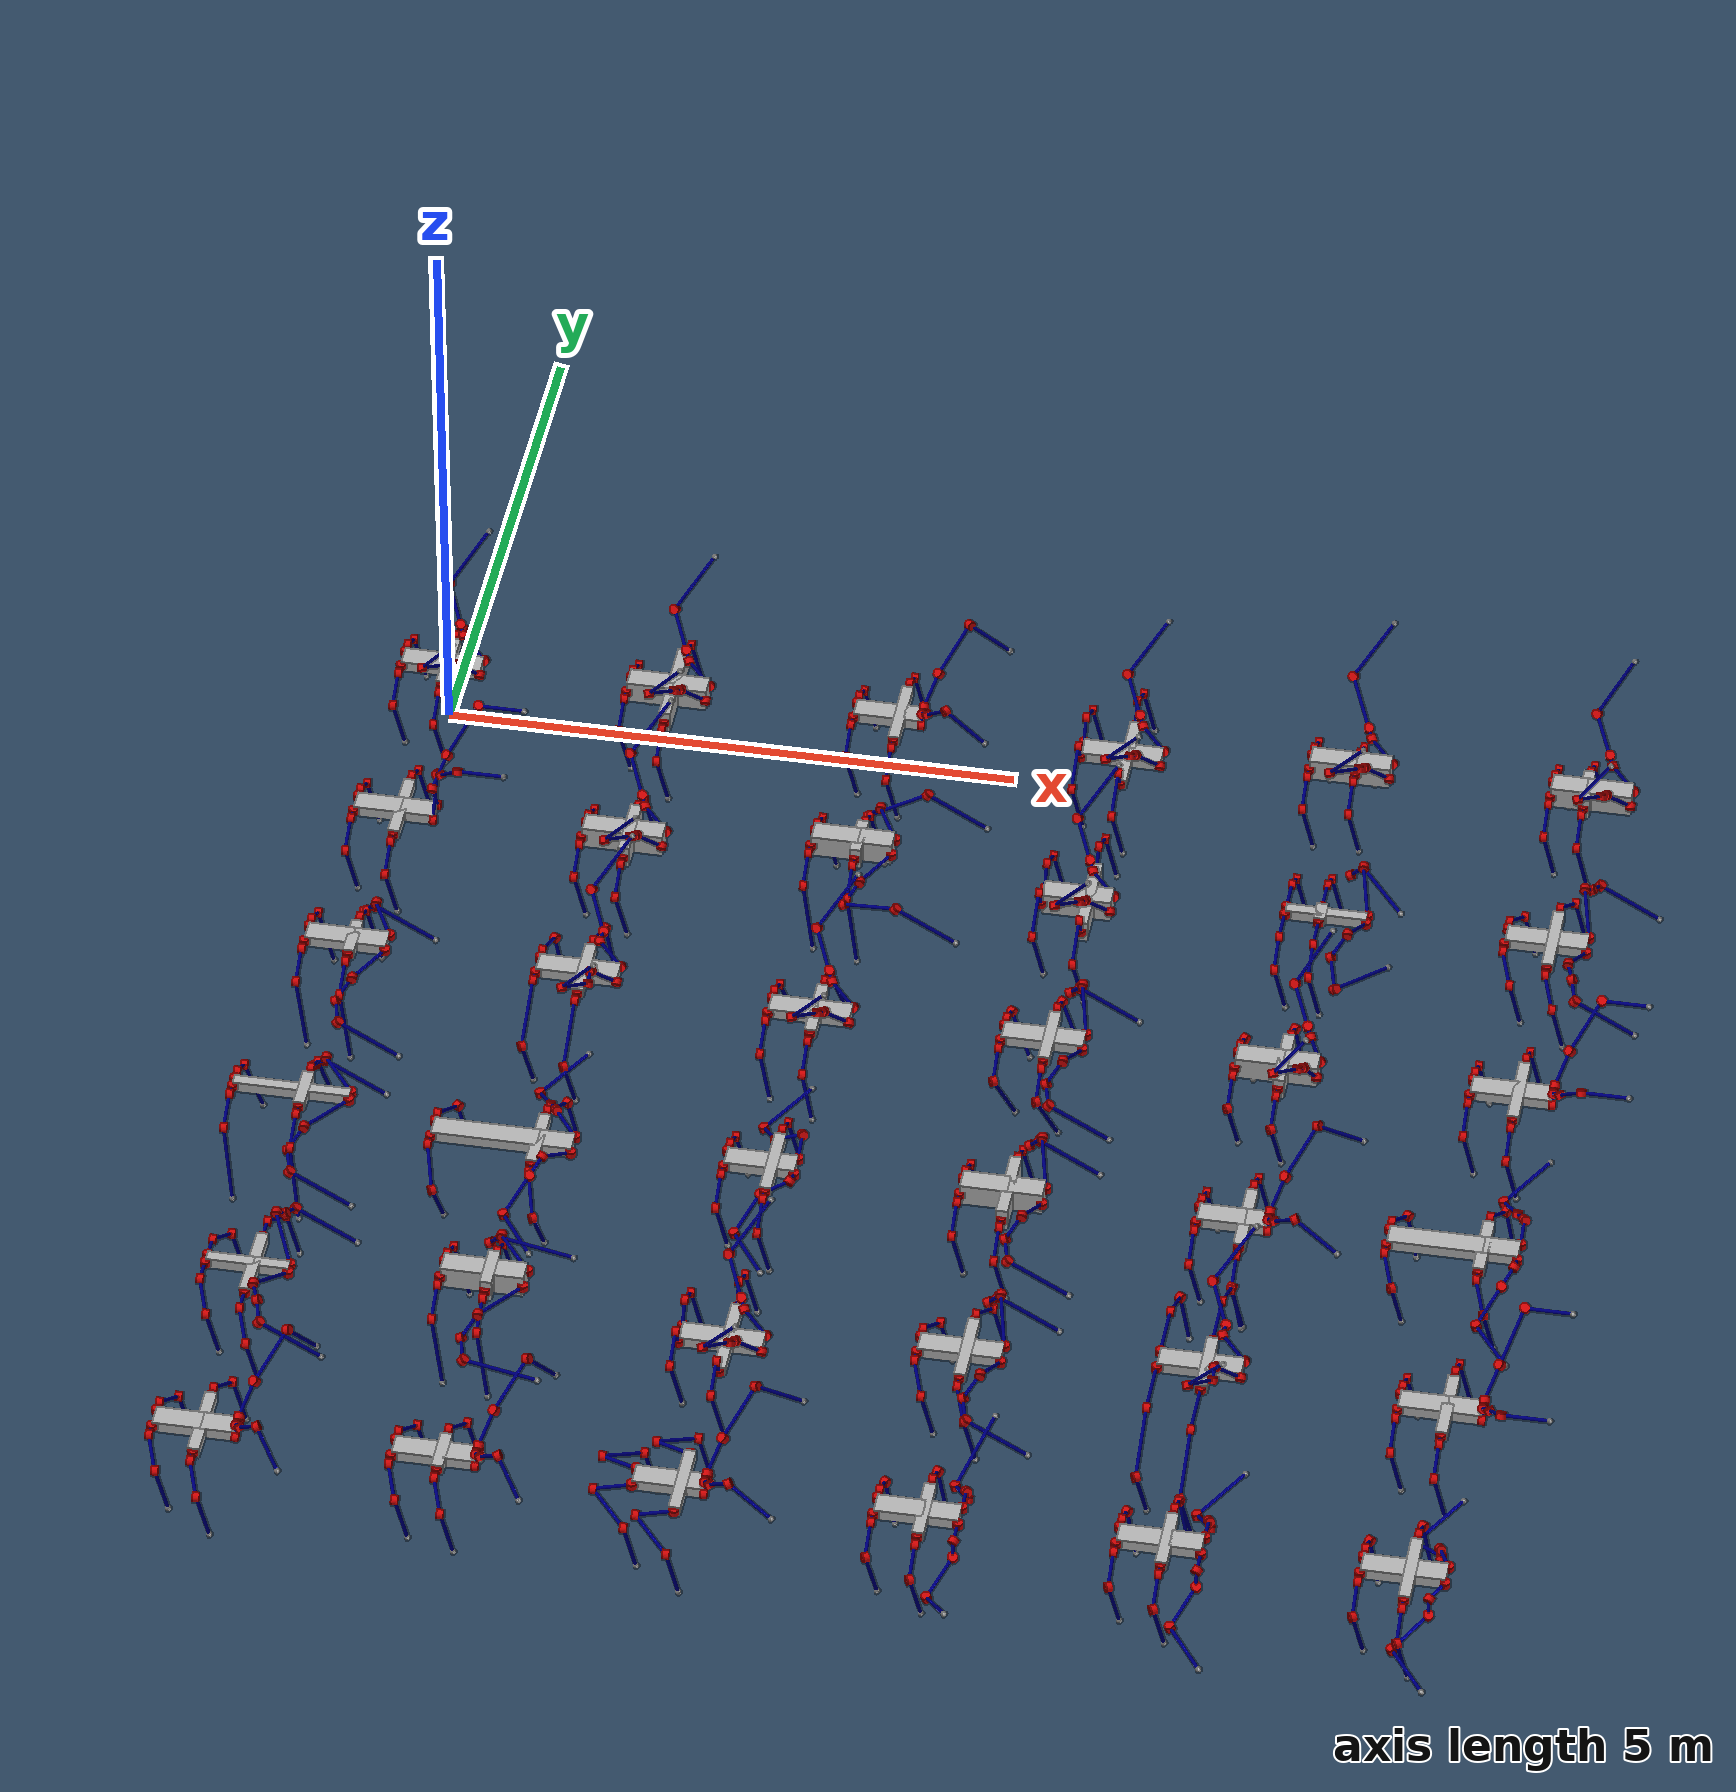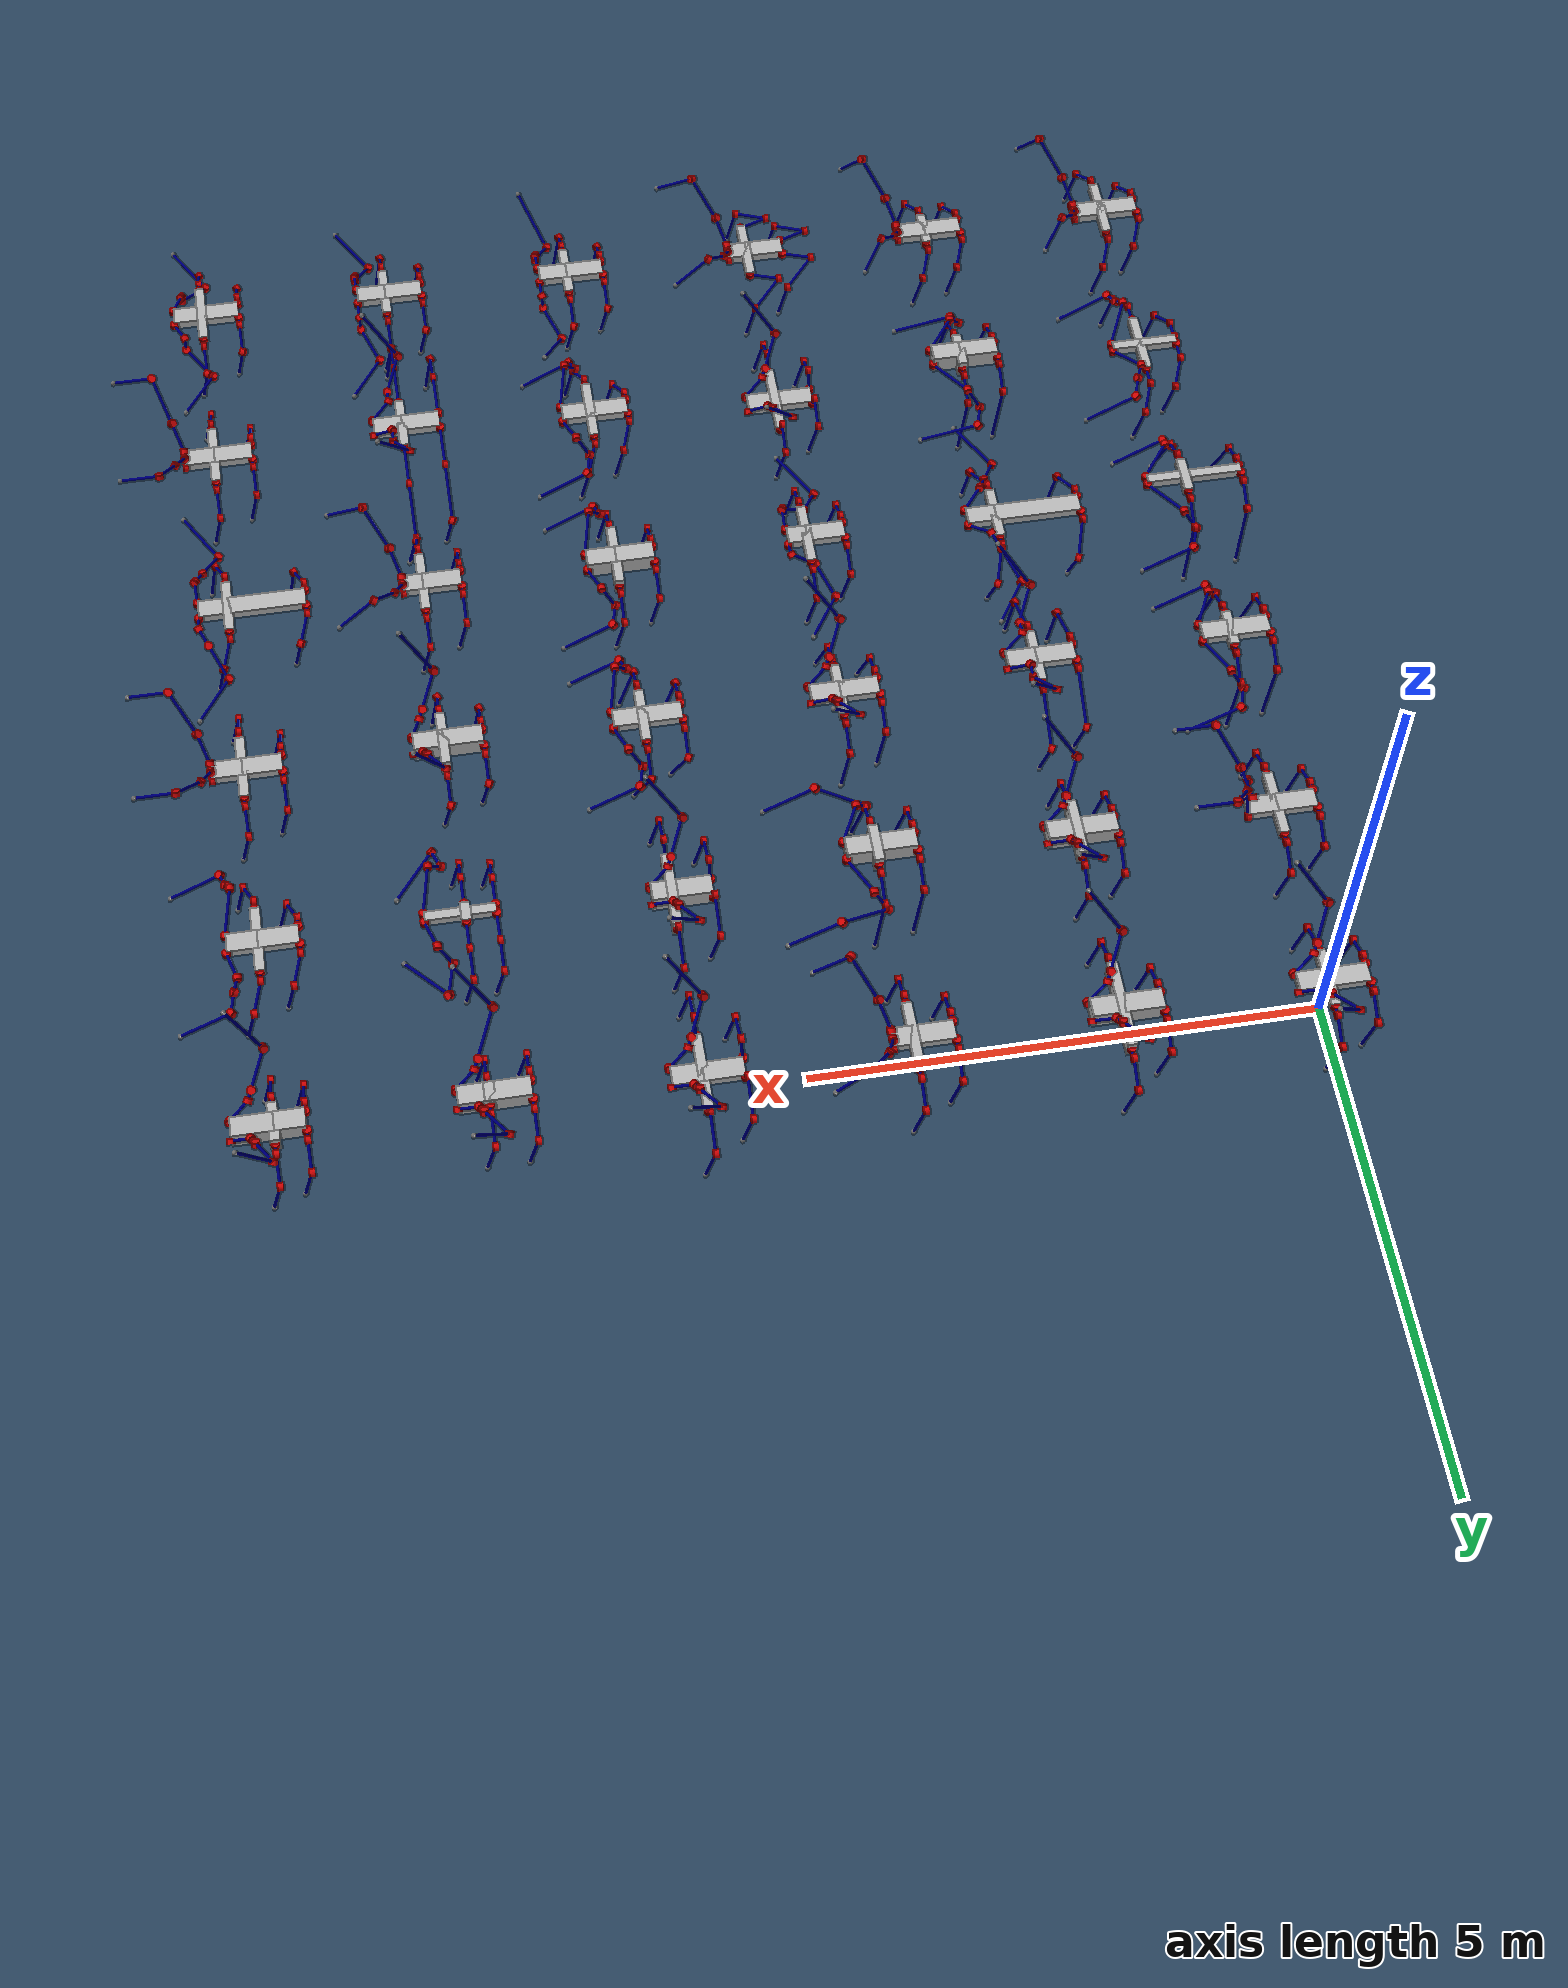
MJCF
<mujoco model="newhex_heterogeneous_grid">
  <compiler angle="radian"/>

  <visual>
    <global offwidth="3840" offheight="2160"/>
    <rgba haze="0.15 0.25 0.35 1"/>
  </visual>

  <default>
    <default class="floor">
      <geom size="0 0 0.05" type="plane" material="groundplane"/>
    </default>
    <default class="g035_o046/main">
      <default class="g035_o046/robot">
        <joint armature="0.01" damping="2" frictionloss="0.2"/>
        <default class="g035_o046/visual">
          <geom contype="0" conaffinity="0" group="2"/>
        </default>
        <default class="g035_o046/collision">
          <geom contype="0" group="3"/>
        </default>
      </default>
      <default class="g035_o046/floor">
        <geom size="0 0 0.05" type="plane" material="groundplane"/>
      </default>
    </default>
    <default class="g055_o023/main">
      <default class="g055_o023/robot">
        <joint armature="0.01" damping="2" frictionloss="0.2"/>
        <default class="g055_o023/visual">
          <geom contype="0" conaffinity="0" group="2"/>
        </default>
        <default class="g055_o023/collision">
          <geom contype="0" group="3"/>
        </default>
      </default>
      <default class="g055_o023/floor">
        <geom size="0 0 0.05" type="plane" material="groundplane"/>
      </default>
    </default>
    <default class="g025_o020/main">
      <default class="g025_o020/robot">
        <joint armature="0.01" damping="2" frictionloss="0.2"/>
        <default class="g025_o020/visual">
          <geom contype="0" conaffinity="0" group="2"/>
        </default>
        <default class="g025_o020/collision">
          <geom contype="0" group="3"/>
        </default>
      </default>
      <default class="g025_o020/floor">
        <geom size="0 0 0.05" type="plane" material="groundplane"/>
      </default>
    </default>
    <default class="g047_o035/main">
      <default class="g047_o035/robot">
        <joint armature="0.01" damping="2" frictionloss="0.2"/>
        <default class="g047_o035/visual">
          <geom contype="0" conaffinity="0" group="2"/>
        </default>
        <default class="g047_o035/collision">
          <geom contype="0" group="3"/>
        </default>
      </default>
      <default class="g047_o035/floor">
        <geom size="0 0 0.05" type="plane" material="groundplane"/>
      </default>
    </default>
    <default class="g058_o011/main">
      <default class="g058_o011/robot">
        <joint armature="0.01" damping="2" frictionloss="0.2"/>
        <default class="g058_o011/visual">
          <geom contype="0" conaffinity="0" group="2"/>
        </default>
        <default class="g058_o011/collision">
          <geom contype="0" group="3"/>
        </default>
      </default>
      <default class="g058_o011/floor">
        <geom size="0 0 0.05" type="plane" material="groundplane"/>
      </default>
    </default>
    <default class="g047_o047/main">
      <default class="g047_o047/robot">
        <joint armature="0.01" damping="2" frictionloss="0.2"/>
        <default class="g047_o047/visual">
          <geom contype="0" conaffinity="0" group="2"/>
        </default>
        <default class="g047_o047/collision">
          <geom contype="0" group="3"/>
        </default>
      </default>
      <default class="g047_o047/floor">
        <geom size="0 0 0.05" type="plane" material="groundplane"/>
      </default>
    </default>
    <default class="g031_o034/main">
      <default class="g031_o034/robot">
        <joint armature="0.01" damping="2" frictionloss="0.2"/>
        <default class="g031_o034/visual">
          <geom contype="0" conaffinity="0" group="2"/>
        </default>
        <default class="g031_o034/collision">
          <geom contype="0" group="3"/>
        </default>
      </default>
      <default class="g031_o034/floor">
        <geom size="0 0 0.05" type="plane" material="groundplane"/>
      </default>
    </default>
    <default class="g046_o004/main">
      <default class="g046_o004/robot">
        <joint armature="0.01" damping="2" frictionloss="0.2"/>
        <default class="g046_o004/visual">
          <geom contype="0" conaffinity="0" group="2"/>
        </default>
        <default class="g046_o004/collision">
          <geom contype="0" group="3"/>
        </default>
      </default>
      <default class="g046_o004/floor">
        <geom size="0 0 0.05" type="plane" material="groundplane"/>
      </default>
    </default>
    <default class="g045_o010/main">
      <default class="g045_o010/robot">
        <joint armature="0.01" damping="2" frictionloss="0.2"/>
        <default class="g045_o010/visual">
          <geom contype="0" conaffinity="0" group="2"/>
        </default>
        <default class="g045_o010/collision">
          <geom contype="0" group="3"/>
        </default>
      </default>
      <default class="g045_o010/floor">
        <geom size="0 0 0.05" type="plane" material="groundplane"/>
      </default>
    </default>
    <default class="g051_o011/main">
      <default class="g051_o011/robot">
        <joint armature="0.01" damping="2" frictionloss="0.2"/>
        <default class="g051_o011/visual">
          <geom contype="0" conaffinity="0" group="2"/>
        </default>
        <default class="g051_o011/collision">
          <geom contype="0" group="3"/>
        </default>
      </default>
      <default class="g051_o011/floor">
        <geom size="0 0 0.05" type="plane" material="groundplane"/>
      </default>
    </default>
    <default class="g056_o022/main">
      <default class="g056_o022/robot">
        <joint armature="0.01" damping="2" frictionloss="0.2"/>
        <default class="g056_o022/visual">
          <geom contype="0" conaffinity="0" group="2"/>
        </default>
        <default class="g056_o022/collision">
          <geom contype="0" group="3"/>
        </default>
      </default>
      <default class="g056_o022/floor">
        <geom size="0 0 0.05" type="plane" material="groundplane"/>
      </default>
    </default>
    <default class="g049_o004/main">
      <default class="g049_o004/robot">
        <joint armature="0.01" damping="2" frictionloss="0.2"/>
        <default class="g049_o004/visual">
          <geom contype="0" conaffinity="0" group="2"/>
        </default>
        <default class="g049_o004/collision">
          <geom contype="0" group="3"/>
        </default>
      </default>
      <default class="g049_o004/floor">
        <geom size="0 0 0.05" type="plane" material="groundplane"/>
      </default>
    </default>
    <default class="g026_o034/main">
      <default class="g026_o034/robot">
        <joint armature="0.01" damping="2" frictionloss="0.2"/>
        <default class="g026_o034/visual">
          <geom contype="0" conaffinity="0" group="2"/>
        </default>
        <default class="g026_o034/collision">
          <geom contype="0" group="3"/>
        </default>
      </default>
      <default class="g026_o034/floor">
        <geom size="0 0 0.05" type="plane" material="groundplane"/>
      </default>
    </default>
    <default class="g034_o004/main">
      <default class="g034_o004/robot">
        <joint armature="0.01" damping="2" frictionloss="0.2"/>
        <default class="g034_o004/visual">
          <geom contype="0" conaffinity="0" group="2"/>
        </default>
        <default class="g034_o004/collision">
          <geom contype="0" group="3"/>
        </default>
      </default>
      <default class="g034_o004/floor">
        <geom size="0 0 0.05" type="plane" material="groundplane"/>
      </default>
    </default>
    <default class="g051_o013/main">
      <default class="g051_o013/robot">
        <joint armature="0.01" damping="2" frictionloss="0.2"/>
        <default class="g051_o013/visual">
          <geom contype="0" conaffinity="0" group="2"/>
        </default>
        <default class="g051_o013/collision">
          <geom contype="0" group="3"/>
        </default>
      </default>
      <default class="g051_o013/floor">
        <geom size="0 0 0.05" type="plane" material="groundplane"/>
      </default>
    </default>
    <default class="g047_o014/main">
      <default class="g047_o014/robot">
        <joint armature="0.01" damping="2" frictionloss="0.2"/>
        <default class="g047_o014/visual">
          <geom contype="0" conaffinity="0" group="2"/>
        </default>
        <default class="g047_o014/collision">
          <geom contype="0" group="3"/>
        </default>
      </default>
      <default class="g047_o014/floor">
        <geom size="0 0 0.05" type="plane" material="groundplane"/>
      </default>
    </default>
    <default class="g057_o002/main">
      <default class="g057_o002/robot">
        <joint armature="0.01" damping="2" frictionloss="0.2"/>
        <default class="g057_o002/visual">
          <geom contype="0" conaffinity="0" group="2"/>
        </default>
        <default class="g057_o002/collision">
          <geom contype="0" group="3"/>
        </default>
      </default>
      <default class="g057_o002/floor">
        <geom size="0 0 0.05" type="plane" material="groundplane"/>
      </default>
    </default>
    <default class="g025_o003/main">
      <default class="g025_o003/robot">
        <joint armature="0.01" damping="2" frictionloss="0.2"/>
        <default class="g025_o003/visual">
          <geom contype="0" conaffinity="0" group="2"/>
        </default>
        <default class="g025_o003/collision">
          <geom contype="0" group="3"/>
        </default>
      </default>
      <default class="g025_o003/floor">
        <geom size="0 0 0.05" type="plane" material="groundplane"/>
      </default>
    </default>
    <default class="g039_o041/main">
      <default class="g039_o041/robot">
        <joint armature="0.01" damping="2" frictionloss="0.2"/>
        <default class="g039_o041/visual">
          <geom contype="0" conaffinity="0" group="2"/>
        </default>
        <default class="g039_o041/collision">
          <geom contype="0" group="3"/>
        </default>
      </default>
      <default class="g039_o041/floor">
        <geom size="0 0 0.05" type="plane" material="groundplane"/>
      </default>
    </default>
    <default class="g050_o044/main">
      <default class="g050_o044/robot">
        <joint armature="0.01" damping="2" frictionloss="0.2"/>
        <default class="g050_o044/visual">
          <geom contype="0" conaffinity="0" group="2"/>
        </default>
        <default class="g050_o044/collision">
          <geom contype="0" group="3"/>
        </default>
      </default>
      <default class="g050_o044/floor">
        <geom size="0 0 0.05" type="plane" material="groundplane"/>
      </default>
    </default>
    <default class="g048_o016/main">
      <default class="g048_o016/robot">
        <joint armature="0.01" damping="2" frictionloss="0.2"/>
        <default class="g048_o016/visual">
          <geom contype="0" conaffinity="0" group="2"/>
        </default>
        <default class="g048_o016/collision">
          <geom contype="0" group="3"/>
        </default>
      </default>
      <default class="g048_o016/floor">
        <geom size="0 0 0.05" type="plane" material="groundplane"/>
      </default>
    </default>
    <default class="g059_o048/main">
      <default class="g059_o048/robot">
        <joint armature="0.01" damping="2" frictionloss="0.2"/>
        <default class="g059_o048/visual">
          <geom contype="0" conaffinity="0" group="2"/>
        </default>
        <default class="g059_o048/collision">
          <geom contype="0" group="3"/>
        </default>
      </default>
      <default class="g059_o048/floor">
        <geom size="0 0 0.05" type="plane" material="groundplane"/>
      </default>
    </default>
    <default class="g023_o016/main">
      <default class="g023_o016/robot">
        <joint armature="0.01" damping="2" frictionloss="0.2"/>
        <default class="g023_o016/visual">
          <geom contype="0" conaffinity="0" group="2"/>
        </default>
        <default class="g023_o016/collision">
          <geom contype="0" group="3"/>
        </default>
      </default>
      <default class="g023_o016/floor">
        <geom size="0 0 0.05" type="plane" material="groundplane"/>
      </default>
    </default>
    <default class="g027_o020/main">
      <default class="g027_o020/robot">
        <joint armature="0.01" damping="2" frictionloss="0.2"/>
        <default class="g027_o020/visual">
          <geom contype="0" conaffinity="0" group="2"/>
        </default>
        <default class="g027_o020/collision">
          <geom contype="0" group="3"/>
        </default>
      </default>
      <default class="g027_o020/floor">
        <geom size="0 0 0.05" type="plane" material="groundplane"/>
      </default>
    </default>
    <default class="g054_o024/main">
      <default class="g054_o024/robot">
        <joint armature="0.01" damping="2" frictionloss="0.2"/>
        <default class="g054_o024/visual">
          <geom contype="0" conaffinity="0" group="2"/>
        </default>
        <default class="g054_o024/collision">
          <geom contype="0" group="3"/>
        </default>
      </default>
      <default class="g054_o024/floor">
        <geom size="0 0 0.05" type="plane" material="groundplane"/>
      </default>
    </default>
    <default class="g046_o021/main">
      <default class="g046_o021/robot">
        <joint armature="0.01" damping="2" frictionloss="0.2"/>
        <default class="g046_o021/visual">
          <geom contype="0" conaffinity="0" group="2"/>
        </default>
        <default class="g046_o021/collision">
          <geom contype="0" group="3"/>
        </default>
      </default>
      <default class="g046_o021/floor">
        <geom size="0 0 0.05" type="plane" material="groundplane"/>
      </default>
    </default>
    <default class="g043_o026/main">
      <default class="g043_o026/robot">
        <joint armature="0.01" damping="2" frictionloss="0.2"/>
        <default class="g043_o026/visual">
          <geom contype="0" conaffinity="0" group="2"/>
        </default>
        <default class="g043_o026/collision">
          <geom contype="0" group="3"/>
        </default>
      </default>
      <default class="g043_o026/floor">
        <geom size="0 0 0.05" type="plane" material="groundplane"/>
      </default>
    </default>
    <default class="g038_o010/main">
      <default class="g038_o010/robot">
        <joint armature="0.01" damping="2" frictionloss="0.2"/>
        <default class="g038_o010/visual">
          <geom contype="0" conaffinity="0" group="2"/>
        </default>
        <default class="g038_o010/collision">
          <geom contype="0" group="3"/>
        </default>
      </default>
      <default class="g038_o010/floor">
        <geom size="0 0 0.05" type="plane" material="groundplane"/>
      </default>
    </default>
    <default class="g040_o039/main">
      <default class="g040_o039/robot">
        <joint armature="0.01" damping="2" frictionloss="0.2"/>
        <default class="g040_o039/visual">
          <geom contype="0" conaffinity="0" group="2"/>
        </default>
        <default class="g040_o039/collision">
          <geom contype="0" group="3"/>
        </default>
      </default>
      <default class="g040_o039/floor">
        <geom size="0 0 0.05" type="plane" material="groundplane"/>
      </default>
    </default>
    <default class="g042_o013/main">
      <default class="g042_o013/robot">
        <joint armature="0.01" damping="2" frictionloss="0.2"/>
        <default class="g042_o013/visual">
          <geom contype="0" conaffinity="0" group="2"/>
        </default>
        <default class="g042_o013/collision">
          <geom contype="0" group="3"/>
        </default>
      </default>
      <default class="g042_o013/floor">
        <geom size="0 0 0.05" type="plane" material="groundplane"/>
      </default>
    </default>
    <default class="g025_o018/main">
      <default class="g025_o018/robot">
        <joint armature="0.01" damping="2" frictionloss="0.2"/>
        <default class="g025_o018/visual">
          <geom contype="0" conaffinity="0" group="2"/>
        </default>
        <default class="g025_o018/collision">
          <geom contype="0" group="3"/>
        </default>
      </default>
      <default class="g025_o018/floor">
        <geom size="0 0 0.05" type="plane" material="groundplane"/>
      </default>
    </default>
    <default class="g042_o029/main">
      <default class="g042_o029/robot">
        <joint armature="0.01" damping="2" frictionloss="0.2"/>
        <default class="g042_o029/visual">
          <geom contype="0" conaffinity="0" group="2"/>
        </default>
        <default class="g042_o029/collision">
          <geom contype="0" group="3"/>
        </default>
      </default>
      <default class="g042_o029/floor">
        <geom size="0 0 0.05" type="plane" material="groundplane"/>
      </default>
    </default>
    <default class="g025_o030/main">
      <default class="g025_o030/robot">
        <joint armature="0.01" damping="2" frictionloss="0.2"/>
        <default class="g025_o030/visual">
          <geom contype="0" conaffinity="0" group="2"/>
        </default>
        <default class="g025_o030/collision">
          <geom contype="0" group="3"/>
        </default>
      </default>
      <default class="g025_o030/floor">
        <geom size="0 0 0.05" type="plane" material="groundplane"/>
      </default>
    </default>
    <default class="g028_o049/main">
      <default class="g028_o049/robot">
        <joint armature="0.01" damping="2" frictionloss="0.2"/>
        <default class="g028_o049/visual">
          <geom contype="0" conaffinity="0" group="2"/>
        </default>
        <default class="g028_o049/collision">
          <geom contype="0" group="3"/>
        </default>
      </default>
      <default class="g028_o049/floor">
        <geom size="0 0 0.05" type="plane" material="groundplane"/>
      </default>
    </default>
    <default class="g023_o020/main">
      <default class="g023_o020/robot">
        <joint armature="0.01" damping="2" frictionloss="0.2"/>
        <default class="g023_o020/visual">
          <geom contype="0" conaffinity="0" group="2"/>
        </default>
        <default class="g023_o020/collision">
          <geom contype="0" group="3"/>
        </default>
      </default>
      <default class="g023_o020/floor">
        <geom size="0 0 0.05" type="plane" material="groundplane"/>
      </default>
    </default>
    <default class="g045_o021/main">
      <default class="g045_o021/robot">
        <joint armature="0.01" damping="2" frictionloss="0.2"/>
        <default class="g045_o021/visual">
          <geom contype="0" conaffinity="0" group="2"/>
        </default>
        <default class="g045_o021/collision">
          <geom contype="0" group="3"/>
        </default>
      </default>
      <default class="g045_o021/floor">
        <geom size="0 0 0.05" type="plane" material="groundplane"/>
      </default>
    </default>
  </default>

  <asset>
    <texture type="2d" colorspace="sRGB" name="groundplane" builtin="checker" mark="edge" rgb1="0.2 0.3 0.4" rgb2="0.1 0.2 0.3" markrgb="0.8 0.8 0.8" width="300" height="300"/>
    <material name="groundplane" texture="groundplane" texuniform="true" texrepeat="10 10" reflectance="0.2"/>
    <material name="g035_o046/blue" rgba="0 0 0.8 1"/>
    <material name="g035_o046/red" rgba="0.8 0 0 1"/>
    <material name="g035_o046/grey" rgba="0.7 0.7 0.7 1"/>
    <material name="g055_o023/blue" rgba="0 0 0.8 1"/>
    <material name="g055_o023/red" rgba="0.8 0 0 1"/>
    <material name="g055_o023/grey" rgba="0.7 0.7 0.7 1"/>
    <material name="g025_o020/blue" rgba="0 0 0.8 1"/>
    <material name="g025_o020/red" rgba="0.8 0 0 1"/>
    <material name="g025_o020/grey" rgba="0.7 0.7 0.7 1"/>
    <material name="g047_o035/blue" rgba="0 0 0.8 1"/>
    <material name="g047_o035/red" rgba="0.8 0 0 1"/>
    <material name="g047_o035/grey" rgba="0.7 0.7 0.7 1"/>
    <material name="g058_o011/blue" rgba="0 0 0.8 1"/>
    <material name="g058_o011/red" rgba="0.8 0 0 1"/>
    <material name="g058_o011/grey" rgba="0.7 0.7 0.7 1"/>
    <material name="g047_o047/blue" rgba="0 0 0.8 1"/>
    <material name="g047_o047/red" rgba="0.8 0 0 1"/>
    <material name="g047_o047/grey" rgba="0.7 0.7 0.7 1"/>
    <material name="g031_o034/blue" rgba="0 0 0.8 1"/>
    <material name="g031_o034/red" rgba="0.8 0 0 1"/>
    <material name="g031_o034/grey" rgba="0.7 0.7 0.7 1"/>
    <material name="g046_o004/blue" rgba="0 0 0.8 1"/>
    <material name="g046_o004/red" rgba="0.8 0 0 1"/>
    <material name="g046_o004/grey" rgba="0.7 0.7 0.7 1"/>
    <material name="g045_o010/blue" rgba="0 0 0.8 1"/>
    <material name="g045_o010/red" rgba="0.8 0 0 1"/>
    <material name="g045_o010/grey" rgba="0.7 0.7 0.7 1"/>
    <material name="g051_o011/blue" rgba="0 0 0.8 1"/>
    <material name="g051_o011/red" rgba="0.8 0 0 1"/>
    <material name="g051_o011/grey" rgba="0.7 0.7 0.7 1"/>
    <material name="g056_o022/blue" rgba="0 0 0.8 1"/>
    <material name="g056_o022/red" rgba="0.8 0 0 1"/>
    <material name="g056_o022/grey" rgba="0.7 0.7 0.7 1"/>
    <material name="g049_o004/blue" rgba="0 0 0.8 1"/>
    <material name="g049_o004/red" rgba="0.8 0 0 1"/>
    <material name="g049_o004/grey" rgba="0.7 0.7 0.7 1"/>
    <material name="g026_o034/blue" rgba="0 0 0.8 1"/>
    <material name="g026_o034/red" rgba="0.8 0 0 1"/>
    <material name="g026_o034/grey" rgba="0.7 0.7 0.7 1"/>
    <material name="g034_o004/blue" rgba="0 0 0.8 1"/>
    <material name="g034_o004/red" rgba="0.8 0 0 1"/>
    <material name="g034_o004/grey" rgba="0.7 0.7 0.7 1"/>
    <material name="g051_o013/blue" rgba="0 0 0.8 1"/>
    <material name="g051_o013/red" rgba="0.8 0 0 1"/>
    <material name="g051_o013/grey" rgba="0.7 0.7 0.7 1"/>
    <material name="g047_o014/blue" rgba="0 0 0.8 1"/>
    <material name="g047_o014/red" rgba="0.8 0 0 1"/>
    <material name="g047_o014/grey" rgba="0.7 0.7 0.7 1"/>
    <material name="g057_o002/blue" rgba="0 0 0.8 1"/>
    <material name="g057_o002/red" rgba="0.8 0 0 1"/>
    <material name="g057_o002/grey" rgba="0.7 0.7 0.7 1"/>
    <material name="g025_o003/blue" rgba="0 0 0.8 1"/>
    <material name="g025_o003/red" rgba="0.8 0 0 1"/>
    <material name="g025_o003/grey" rgba="0.7 0.7 0.7 1"/>
    <material name="g039_o041/blue" rgba="0 0 0.8 1"/>
    <material name="g039_o041/red" rgba="0.8 0 0 1"/>
    <material name="g039_o041/grey" rgba="0.7 0.7 0.7 1"/>
    <material name="g050_o044/blue" rgba="0 0 0.8 1"/>
    <material name="g050_o044/red" rgba="0.8 0 0 1"/>
    <material name="g050_o044/grey" rgba="0.7 0.7 0.7 1"/>
    <material name="g048_o016/blue" rgba="0 0 0.8 1"/>
    <material name="g048_o016/red" rgba="0.8 0 0 1"/>
    <material name="g048_o016/grey" rgba="0.7 0.7 0.7 1"/>
    <material name="g059_o048/blue" rgba="0 0 0.8 1"/>
    <material name="g059_o048/red" rgba="0.8 0 0 1"/>
    <material name="g059_o048/grey" rgba="0.7 0.7 0.7 1"/>
    <material name="g023_o016/blue" rgba="0 0 0.8 1"/>
    <material name="g023_o016/red" rgba="0.8 0 0 1"/>
    <material name="g023_o016/grey" rgba="0.7 0.7 0.7 1"/>
    <material name="g027_o020/blue" rgba="0 0 0.8 1"/>
    <material name="g027_o020/red" rgba="0.8 0 0 1"/>
    <material name="g027_o020/grey" rgba="0.7 0.7 0.7 1"/>
    <material name="g054_o024/blue" rgba="0 0 0.8 1"/>
    <material name="g054_o024/red" rgba="0.8 0 0 1"/>
    <material name="g054_o024/grey" rgba="0.7 0.7 0.7 1"/>
    <material name="g046_o021/blue" rgba="0 0 0.8 1"/>
    <material name="g046_o021/red" rgba="0.8 0 0 1"/>
    <material name="g046_o021/grey" rgba="0.7 0.7 0.7 1"/>
    <material name="g043_o026/blue" rgba="0 0 0.8 1"/>
    <material name="g043_o026/red" rgba="0.8 0 0 1"/>
    <material name="g043_o026/grey" rgba="0.7 0.7 0.7 1"/>
    <material name="g038_o010/blue" rgba="0 0 0.8 1"/>
    <material name="g038_o010/red" rgba="0.8 0 0 1"/>
    <material name="g038_o010/grey" rgba="0.7 0.7 0.7 1"/>
    <material name="g040_o039/blue" rgba="0 0 0.8 1"/>
    <material name="g040_o039/red" rgba="0.8 0 0 1"/>
    <material name="g040_o039/grey" rgba="0.7 0.7 0.7 1"/>
    <material name="g042_o013/blue" rgba="0 0 0.8 1"/>
    <material name="g042_o013/red" rgba="0.8 0 0 1"/>
    <material name="g042_o013/grey" rgba="0.7 0.7 0.7 1"/>
    <material name="g025_o018/blue" rgba="0 0 0.8 1"/>
    <material name="g025_o018/red" rgba="0.8 0 0 1"/>
    <material name="g025_o018/grey" rgba="0.7 0.7 0.7 1"/>
    <material name="g042_o029/blue" rgba="0 0 0.8 1"/>
    <material name="g042_o029/red" rgba="0.8 0 0 1"/>
    <material name="g042_o029/grey" rgba="0.7 0.7 0.7 1"/>
    <material name="g025_o030/blue" rgba="0 0 0.8 1"/>
    <material name="g025_o030/red" rgba="0.8 0 0 1"/>
    <material name="g025_o030/grey" rgba="0.7 0.7 0.7 1"/>
    <material name="g028_o049/blue" rgba="0 0 0.8 1"/>
    <material name="g028_o049/red" rgba="0.8 0 0 1"/>
    <material name="g028_o049/grey" rgba="0.7 0.7 0.7 1"/>
    <material name="g023_o020/blue" rgba="0 0 0.8 1"/>
    <material name="g023_o020/red" rgba="0.8 0 0 1"/>
    <material name="g023_o020/grey" rgba="0.7 0.7 0.7 1"/>
    <material name="g045_o021/blue" rgba="0 0 0.8 1"/>
    <material name="g045_o021/red" rgba="0.8 0 0 1"/>
    <material name="g045_o021/grey" rgba="0.7 0.7 0.7 1"/>
  </asset>

  <worldbody>
    <geom name="floor" class="floor"/>
    <light pos="0 0 5" dir="0 0 -1" type="directional"/>
    <body name="g035_o046/base_link" childclass="g035_o046/robot" pos="0 0 0.5749">
      <inertial pos="0 0 0" mass="18.4" diaginertia="0.0166667 0.0166667 0.0166667"/>
      <joint name="g035_o046/floating_base" type="free" armature="0" damping="0" frictionloss="0"/>
      <geom name="g035_o046/base_link_collision_0" class="g035_o046/collision" size="0.15 0.1 0.05" pos="0.15 0 0" type="box"/>
      <geom name="g035_o046/base_link_collision_1" class="g035_o046/collision" size="0.2 0.1 0.05" pos="-0.2 0 0" type="box"/>
      <geom name="g035_o046/base_link_collision_2" class="g035_o046/collision" size="0.05 0.3 0.05" type="box"/>
      <geom name="g035_o046/base_link_visual_0" class="g035_o046/visual" size="0.15 0.1 0.05" pos="0.15 0 0" type="box" material="g035_o046/grey"/>
      <geom name="g035_o046/base_link_visual_1" class="g035_o046/visual" size="0.2 0.1 0.05" pos="-0.2 0 0" type="box" material="g035_o046/grey"/>
      <geom name="g035_o046/base_link_visual_2" class="g035_o046/visual" size="0.05 0.3 0.05" type="box" material="g035_o046/grey"/>
      <site name="g035_o046/imu" pos="0 0 0" size="0.01" rgba="1 0 0 1"/>
      <body name="g035_o046/LF_link1" pos="0.3 0.1 0" quat="0.612708 0.353305 -0.353505 0.612208">
        <inertial pos="0 0 0" mass="1.36569" diaginertia="0.000968 0.000968 0.000784"/>
        <joint name="g035_o046/LF_joint1" pos="0 0 0" axis="0 0 1" range="-6.28 6.28"/>
        <geom name="g035_o046/LF_link1_collision" class="g035_o046/collision" size="0.015 0.141422" pos="0.1 0.1 0" quat="0.653284 -0.270593 0.653284 0.270593" type="cylinder"/>
        <geom name="g035_o046/LF_link1_visual_0" class="g035_o046/visual" size="0.044 0.03" type="cylinder" material="g035_o046/red"/>
        <geom name="g035_o046/LF_link1_visual_1" class="g035_o046/visual" size="0.015 0.141422" pos="0.1 0.1 0" quat="0.653284 -0.270593 0.653284 0.270593" type="cylinder" material="g035_o046/blue"/>
        <body name="g035_o046/LF_link2" pos="0.2 0.2 0" quat="0.530673 -0.305785 0.78906 0.0475976">
          <inertial pos="0 0 0" mass="1" diaginertia="0.000968 0.000968 0.000784"/>
          <joint name="g035_o046/LF_joint2" pos="0 0 0" axis="0 0 1" range="-6.28 6.28"/>
          <geom name="g035_o046/LF_link2_collision" class="g035_o046/collision" size="0.015 0.05" pos="0 0 0.05" type="cylinder"/>
          <geom name="g035_o046/LF_link2_visual_0" class="g035_o046/visual" size="0.044 0.03" type="cylinder" material="g035_o046/red"/>
          <geom name="g035_o046/LF_link2_visual_1" class="g035_o046/visual" size="0.015 0.05" pos="0 0 0.05" type="cylinder" material="g035_o046/blue"/>
          <body name="g035_o046/LF_link3" pos="0 0 0.1" quat="0.683093 0.183198 -0.682993 0.182598">
            <inertial pos="0 0 0" mass="1.6" diaginertia="0.000968 0.000968 0.000784"/>
            <joint name="g035_o046/LF_joint3" pos="0 0 0" axis="0 0 1" range="-6.28 6.28"/>
            <geom name="g035_o046/LF_link3_collision" class="g035_o046/collision" size="0.015 0.2" pos="0.2 0 0" quat="0.707107 0 0.707107 0" type="cylinder"/>
            <geom name="g035_o046/LF_link3_visual_0" class="g035_o046/visual" size="0.044 0.03" type="cylinder" material="g035_o046/red"/>
            <geom name="g035_o046/LF_link3_visual_1" class="g035_o046/visual" size="0.015 0.2" pos="0.2 0 0" quat="0.707107 0 0.707107 0" type="cylinder" material="g035_o046/blue"/>
            <body name="g035_o046/LF_link4" pos="0.4 0 0" quat="0.836657 -0.129293 -0.224089 -0.482775">
              <inertial pos="0 0 0" mass="2" diaginertia="0.000968 0.000968 0.000784"/>
              <joint name="g035_o046/LF_joint4" pos="0 0 0" axis="0 0 1" range="-6.28 6.28"/>
              <geom name="g035_o046/LF_link4_collision" class="g035_o046/collision" size="0.015 0.3" pos="0.3 0 0" quat="0.707107 0 0.707107 0" type="cylinder"/>
              <geom name="g035_o046/LF_link4_visual_0" class="g035_o046/visual" size="0.044 0.03" type="cylinder" material="g035_o046/red"/>
              <geom name="g035_o046/LF_link4_visual_1" class="g035_o046/visual" size="0.015 0.3" pos="0.3 0 0" quat="0.707107 0 0.707107 0" type="cylinder" material="g035_o046/blue"/>
              <body name="g035_o046/LF_foot_link" pos="0.6 0 0">
                <inertial pos="0 0 0" mass="0.05" diaginertia="1.25e-05 1.25e-05 1.25e-05"/>
                <geom name="g035_o046/LF_foot_link_collision" class="g035_o046/collision" size="0.025"/>
                <geom name="g035_o046/LF_foot_link_visual" class="g035_o046/visual" size="0.025" material="g035_o046/grey"/>
                <site name="g035_o046/LF_touch_site" pos="0 0 0" size="0.01" rgba="0 0 0 0"/>
              </body>
            </body>
          </body>
        </body>
      </body>
      <body name="g035_o046/LM_link1" pos="0 0.3 0" quat="0.707407 0 0 0.706807">
        <inertial pos="0 0 0" mass="1" diaginertia="0.000968 0.000968 0.000784"/>
        <joint name="g035_o046/LM_joint1" pos="0 0 0" axis="0 0 1" range="-6.28 6.28"/>
        <geom name="g035_o046/LM_link1_collision" class="g035_o046/collision" size="0.015 0.05" pos="0.05 0 0" quat="0.707107 0 0.707107 0" type="cylinder"/>
        <geom name="g035_o046/LM_link1_visual_0" class="g035_o046/visual" size="0.044 0.03" type="cylinder" material="g035_o046/red"/>
        <geom name="g035_o046/LM_link1_visual_1" class="g035_o046/visual" size="0.015 0.05" pos="0.05 0 0" quat="0.707107 0 0.707107 0" type="cylinder" material="g035_o046/blue"/>
        <body name="g035_o046/LM_link2" pos="0.1 0 0" quat="0.683293 0.682793 0.182998 -0.182798">
          <inertial pos="0 0 0" mass="1.4" diaginertia="0.000968 0.000968 0.000784"/>
          <joint name="g035_o046/LM_joint2" pos="0 0 0" axis="0 0 1" range="-6.28 6.28"/>
          <geom name="g035_o046/LM_link2_collision" class="g035_o046/collision" size="0.015 0.15" pos="0.15 0 0" quat="0.707107 0 0.707107 0" type="cylinder"/>
          <geom name="g035_o046/LM_link2_visual_0" class="g035_o046/visual" size="0.044 0.03" type="cylinder" material="g035_o046/red"/>
          <geom name="g035_o046/LM_link2_visual_1" class="g035_o046/visual" size="0.015 0.15" pos="0.15 0 0" quat="0.707107 0 0.707107 0" type="cylinder" material="g035_o046/blue"/>
          <body name="g035_o046/LM_link3" pos="0.3 0 0" quat="0.866156 0 0 -0.499774">
            <inertial pos="0 0 0" mass="1.62462" diaginertia="0.000968 0.000968 0.000784"/>
            <joint name="g035_o046/LM_joint3" pos="0 0 0" axis="0 0 1" range="-6.28 6.28"/>
            <geom name="g035_o046/LM_link3_collision" class="g035_o046/collision" size="0.015 0.206155" pos="0.2 0 0.05" quat="0.788209 0 0.615407 0" type="cylinder"/>
            <geom name="g035_o046/LM_link3_visual_0" class="g035_o046/visual" size="0.044 0.03" type="cylinder" material="g035_o046/red"/>
            <geom name="g035_o046/LM_link3_visual_1" class="g035_o046/visual" size="0.015 0.206155" pos="0.2 0 0.05" quat="0.788209 0 0.615407 0" type="cylinder" material="g035_o046/blue"/>
            <body name="g035_o046/LM_foot_link" pos="0.4 0 0.1">
              <inertial pos="0 0 0" mass="0.05" diaginertia="1.25e-05 1.25e-05 1.25e-05"/>
              <geom name="g035_o046/LM_foot_link_collision" class="g035_o046/collision" size="0.025"/>
              <geom name="g035_o046/LM_foot_link_visual" class="g035_o046/visual" size="0.025" material="g035_o046/grey"/>
              <site name="g035_o046/LM_touch_site" pos="0 0 0" size="0.01" rgba="0 0 0 0"/>
            </body>
          </body>
        </body>
      </body>
      <body name="g035_o046/LB_link1" pos="-0.4 0.1 0" quat="0.707407 0 0 0.706807">
        <inertial pos="0 0 0" mass="1" diaginertia="0.000968 0.000968 0.000784"/>
        <joint name="g035_o046/LB_joint1" pos="0 0 0" axis="0 0 1" range="-6.28 6.28"/>
        <geom name="g035_o046/LB_link1_collision" class="g035_o046/collision" size="0.015 0.05" pos="0.05 0 0" quat="0.707107 0 0.707107 0" type="cylinder"/>
        <geom name="g035_o046/LB_link1_visual_0" class="g035_o046/visual" size="0.044 0.03" type="cylinder" material="g035_o046/red"/>
        <geom name="g035_o046/LB_link1_visual_1" class="g035_o046/visual" size="0.015 0.05" pos="0.05 0 0" quat="0.707107 0 0.707107 0" type="cylinder" material="g035_o046/blue"/>
        <body name="g035_o046/LB_link2" pos="0.1 0 0" quat="0.683293 0.682793 0.182998 -0.182798">
          <inertial pos="0 0 0" mass="1.4" diaginertia="0.000968 0.000968 0.000784"/>
          <joint name="g035_o046/LB_joint2" pos="0 0 0" axis="0 0 1" range="-6.28 6.28"/>
          <geom name="g035_o046/LB_link2_collision" class="g035_o046/collision" size="0.015 0.15" pos="0.15 0 0" quat="0.707107 0 0.707107 0" type="cylinder"/>
          <geom name="g035_o046/LB_link2_visual_0" class="g035_o046/visual" size="0.044 0.03" type="cylinder" material="g035_o046/red"/>
          <geom name="g035_o046/LB_link2_visual_1" class="g035_o046/visual" size="0.015 0.15" pos="0.15 0 0" quat="0.707107 0 0.707107 0" type="cylinder" material="g035_o046/blue"/>
          <body name="g035_o046/LB_link3" pos="0.3 0 0" quat="0.866156 0 0 -0.499774">
            <inertial pos="0 0 0" mass="1.62462" diaginertia="0.000968 0.000968 0.000784"/>
            <joint name="g035_o046/LB_joint3" pos="0 0 0" axis="0 0 1" range="-6.28 6.28"/>
            <geom name="g035_o046/LB_link3_collision" class="g035_o046/collision" size="0.015 0.206155" pos="0.2 0 0.05" quat="0.788209 0 0.615407 0" type="cylinder"/>
            <geom name="g035_o046/LB_link3_visual_0" class="g035_o046/visual" size="0.044 0.03" type="cylinder" material="g035_o046/red"/>
            <geom name="g035_o046/LB_link3_visual_1" class="g035_o046/visual" size="0.015 0.206155" pos="0.2 0 0.05" quat="0.788209 0 0.615407 0" type="cylinder" material="g035_o046/blue"/>
            <body name="g035_o046/LB_foot_link" pos="0.4 0 0.1">
              <inertial pos="0 0 0" mass="0.05" diaginertia="1.25e-05 1.25e-05 1.25e-05"/>
              <geom name="g035_o046/LB_foot_link_collision" class="g035_o046/collision" size="0.025"/>
              <geom name="g035_o046/LB_foot_link_visual" class="g035_o046/visual" size="0.025" material="g035_o046/grey"/>
              <site name="g035_o046/LB_touch_site" pos="0 0 0" size="0.01" rgba="0 0 0 0"/>
            </body>
          </body>
        </body>
      </body>
      <body name="g035_o046/RF_link1" pos="0.3 -0.1 0" quat="0.612708 -0.353305 -0.353505 -0.612208">
        <inertial pos="0 0 0" mass="1.36569" diaginertia="0.000968 0.000968 0.000784"/>
        <joint name="g035_o046/RF_joint1" pos="0 0 0" axis="0 0 1" range="-6.28 6.28"/>
        <geom name="g035_o046/RF_link1_collision" class="g035_o046/collision" size="0.015 0.141422" pos="0.1 -0.1 0" quat="0.653284 0.270593 0.653284 -0.270593" type="cylinder"/>
        <geom name="g035_o046/RF_link1_visual_0" class="g035_o046/visual" size="0.044 0.03" type="cylinder" material="g035_o046/red"/>
        <geom name="g035_o046/RF_link1_visual_1" class="g035_o046/visual" size="0.015 0.141422" pos="0.1 -0.1 0" quat="0.653284 0.270593 0.653284 -0.270593" type="cylinder" material="g035_o046/blue"/>
        <body name="g035_o046/RF_link2" pos="0.2 -0.2 0" quat="0.530673 0.305785 0.78906 -0.0475976">
          <inertial pos="0 0 0" mass="1" diaginertia="0.000968 0.000968 0.000784"/>
          <joint name="g035_o046/RF_joint2" pos="0 0 0" axis="0 0 1" range="-6.28 6.28"/>
          <geom name="g035_o046/RF_link2_collision" class="g035_o046/collision" size="0.015 0.05" pos="0 0 0.05" type="cylinder"/>
          <geom name="g035_o046/RF_link2_visual_0" class="g035_o046/visual" size="0.044 0.03" type="cylinder" material="g035_o046/red"/>
          <geom name="g035_o046/RF_link2_visual_1" class="g035_o046/visual" size="0.015 0.05" pos="0 0 0.05" type="cylinder" material="g035_o046/blue"/>
          <body name="g035_o046/RF_link3" pos="0 0 0.1" quat="0.683093 -0.183198 -0.682993 -0.182598">
            <inertial pos="0 0 0" mass="1.6" diaginertia="0.000968 0.000968 0.000784"/>
            <joint name="g035_o046/RF_joint3" pos="0 0 0" axis="0 0 1" range="-6.28 6.28"/>
            <geom name="g035_o046/RF_link3_collision" class="g035_o046/collision" size="0.015 0.2" pos="0.2 0 0" quat="0.707107 0 0.707107 0" type="cylinder"/>
            <geom name="g035_o046/RF_link3_visual_0" class="g035_o046/visual" size="0.044 0.03" type="cylinder" material="g035_o046/red"/>
            <geom name="g035_o046/RF_link3_visual_1" class="g035_o046/visual" size="0.015 0.2" pos="0.2 0 0" quat="0.707107 0 0.707107 0" type="cylinder" material="g035_o046/blue"/>
            <body name="g035_o046/RF_link4" pos="0.4 0 0" quat="0.836657 0.129293 -0.224089 0.482775">
              <inertial pos="0 0 0" mass="2" diaginertia="0.000968 0.000968 0.000784"/>
              <joint name="g035_o046/RF_joint4" pos="0 0 0" axis="0 0 1" range="-6.28 6.28"/>
              <geom name="g035_o046/RF_link4_collision" class="g035_o046/collision" size="0.015 0.3" pos="0.3 0 0" quat="0.707107 0 0.707107 0" type="cylinder"/>
              <geom name="g035_o046/RF_link4_visual_0" class="g035_o046/visual" size="0.044 0.03" type="cylinder" material="g035_o046/red"/>
              <geom name="g035_o046/RF_link4_visual_1" class="g035_o046/visual" size="0.015 0.3" pos="0.3 0 0" quat="0.707107 0 0.707107 0" type="cylinder" material="g035_o046/blue"/>
              <body name="g035_o046/RF_foot_link" pos="0.6 0 0">
                <inertial pos="0 0 0" mass="0.05" diaginertia="1.25e-05 1.25e-05 1.25e-05"/>
                <geom name="g035_o046/RF_foot_link_collision" class="g035_o046/collision" size="0.025"/>
                <geom name="g035_o046/RF_foot_link_visual" class="g035_o046/visual" size="0.025" material="g035_o046/grey"/>
                <site name="g035_o046/RF_touch_site" pos="0 0 0" size="0.01" rgba="0 0 0 0"/>
              </body>
            </body>
          </body>
        </body>
      </body>
      <body name="g035_o046/RM_link1" pos="0 -0.3 0" quat="0.707407 0 0 -0.706807">
        <inertial pos="0 0 0" mass="1" diaginertia="0.000968 0.000968 0.000784"/>
        <joint name="g035_o046/RM_joint1" pos="0 0 0" axis="0 0 1" range="-6.28 6.28"/>
        <geom name="g035_o046/RM_link1_collision" class="g035_o046/collision" size="0.015 0.05" pos="0.05 0 0" quat="0.707107 0 0.707107 0" type="cylinder"/>
        <geom name="g035_o046/RM_link1_visual_0" class="g035_o046/visual" size="0.044 0.03" type="cylinder" material="g035_o046/red"/>
        <geom name="g035_o046/RM_link1_visual_1" class="g035_o046/visual" size="0.015 0.05" pos="0.05 0 0" quat="0.707107 0 0.707107 0" type="cylinder" material="g035_o046/blue"/>
        <body name="g035_o046/RM_link2" pos="0.1 0 0" quat="0.683293 -0.682793 0.182998 0.182798">
          <inertial pos="0 0 0" mass="1.4" diaginertia="0.000968 0.000968 0.000784"/>
          <joint name="g035_o046/RM_joint2" pos="0 0 0" axis="0 0 1" range="-6.28 6.28"/>
          <geom name="g035_o046/RM_link2_collision" class="g035_o046/collision" size="0.015 0.15" pos="0.15 0 0" quat="0.707107 0 0.707107 0" type="cylinder"/>
          <geom name="g035_o046/RM_link2_visual_0" class="g035_o046/visual" size="0.044 0.03" type="cylinder" material="g035_o046/red"/>
          <geom name="g035_o046/RM_link2_visual_1" class="g035_o046/visual" size="0.015 0.15" pos="0.15 0 0" quat="0.707107 0 0.707107 0" type="cylinder" material="g035_o046/blue"/>
          <body name="g035_o046/RM_link3" pos="0.3 0 0" quat="0.866156 0 0 0.499774">
            <inertial pos="0 0 0" mass="1.62462" diaginertia="0.000968 0.000968 0.000784"/>
            <joint name="g035_o046/RM_joint3" pos="0 0 0" axis="0 0 1" range="-6.28 6.28"/>
            <geom name="g035_o046/RM_link3_collision" class="g035_o046/collision" size="0.015 0.206155" pos="0.2 0 0.05" quat="0.788209 0 0.615407 0" type="cylinder"/>
            <geom name="g035_o046/RM_link3_visual_0" class="g035_o046/visual" size="0.044 0.03" type="cylinder" material="g035_o046/red"/>
            <geom name="g035_o046/RM_link3_visual_1" class="g035_o046/visual" size="0.015 0.206155" pos="0.2 0 0.05" quat="0.788209 0 0.615407 0" type="cylinder" material="g035_o046/blue"/>
            <body name="g035_o046/RM_foot_link" pos="0.4 0 0.1">
              <inertial pos="0 0 0" mass="0.05" diaginertia="1.25e-05 1.25e-05 1.25e-05"/>
              <geom name="g035_o046/RM_foot_link_collision" class="g035_o046/collision" size="0.025"/>
              <geom name="g035_o046/RM_foot_link_visual" class="g035_o046/visual" size="0.025" material="g035_o046/grey"/>
              <site name="g035_o046/RM_touch_site" pos="0 0 0" size="0.01" rgba="0 0 0 0"/>
            </body>
          </body>
        </body>
      </body>
      <body name="g035_o046/RB_link1" pos="-0.4 -0.1 0" quat="0.707407 0 0 -0.706807">
        <inertial pos="0 0 0" mass="1" diaginertia="0.000968 0.000968 0.000784"/>
        <joint name="g035_o046/RB_joint1" pos="0 0 0" axis="0 0 1" range="-6.28 6.28"/>
        <geom name="g035_o046/RB_link1_collision" class="g035_o046/collision" size="0.015 0.05" pos="0.05 0 0" quat="0.707107 0 0.707107 0" type="cylinder"/>
        <geom name="g035_o046/RB_link1_visual_0" class="g035_o046/visual" size="0.044 0.03" type="cylinder" material="g035_o046/red"/>
        <geom name="g035_o046/RB_link1_visual_1" class="g035_o046/visual" size="0.015 0.05" pos="0.05 0 0" quat="0.707107 0 0.707107 0" type="cylinder" material="g035_o046/blue"/>
        <body name="g035_o046/RB_link2" pos="0.1 0 0" quat="0.683293 -0.682793 0.182998 0.182798">
          <inertial pos="0 0 0" mass="1.4" diaginertia="0.000968 0.000968 0.000784"/>
          <joint name="g035_o046/RB_joint2" pos="0 0 0" axis="0 0 1" range="-6.28 6.28"/>
          <geom name="g035_o046/RB_link2_collision" class="g035_o046/collision" size="0.015 0.15" pos="0.15 0 0" quat="0.707107 0 0.707107 0" type="cylinder"/>
          <geom name="g035_o046/RB_link2_visual_0" class="g035_o046/visual" size="0.044 0.03" type="cylinder" material="g035_o046/red"/>
          <geom name="g035_o046/RB_link2_visual_1" class="g035_o046/visual" size="0.015 0.15" pos="0.15 0 0" quat="0.707107 0 0.707107 0" type="cylinder" material="g035_o046/blue"/>
          <body name="g035_o046/RB_link3" pos="0.3 0 0" quat="0.866156 0 0 0.499774">
            <inertial pos="0 0 0" mass="1.62462" diaginertia="0.000968 0.000968 0.000784"/>
            <joint name="g035_o046/RB_joint3" pos="0 0 0" axis="0 0 1" range="-6.28 6.28"/>
            <geom name="g035_o046/RB_link3_collision" class="g035_o046/collision" size="0.015 0.206155" pos="0.2 0 0.05" quat="0.788209 0 0.615407 0" type="cylinder"/>
            <geom name="g035_o046/RB_link3_visual_0" class="g035_o046/visual" size="0.044 0.03" type="cylinder" material="g035_o046/red"/>
            <geom name="g035_o046/RB_link3_visual_1" class="g035_o046/visual" size="0.015 0.206155" pos="0.2 0 0.05" quat="0.788209 0 0.615407 0" type="cylinder" material="g035_o046/blue"/>
            <body name="g035_o046/RB_foot_link" pos="0.4 0 0.1">
              <inertial pos="0 0 0" mass="0.05" diaginertia="1.25e-05 1.25e-05 1.25e-05"/>
              <geom name="g035_o046/RB_foot_link_collision" class="g035_o046/collision" size="0.025"/>
              <geom name="g035_o046/RB_foot_link_visual" class="g035_o046/visual" size="0.025" material="g035_o046/grey"/>
              <site name="g035_o046/RB_touch_site" pos="0 0 0" size="0.01" rgba="0 0 0 0"/>
            </body>
          </body>
        </body>
      </body>
    </body>
    <body name="g055_o023/base_link" childclass="g055_o023/robot" pos="2 0 0.5749">
      <inertial pos="0 0 0" mass="26.8" diaginertia="0.0166667 0.0166667 0.0166667"/>
      <joint name="g055_o023/floating_base" type="free" armature="0" damping="0" frictionloss="0"/>
      <geom name="g055_o023/base_link_collision_0" class="g055_o023/collision" size="0.15 0.1 0.1" pos="0.15 0 0" type="box"/>
      <geom name="g055_o023/base_link_collision_1" class="g055_o023/collision" size="0.2 0.1 0.1" pos="-0.2 0 0" type="box"/>
      <geom name="g055_o023/base_link_collision_2" class="g055_o023/collision" size="0.05 0.45 0.1" type="box"/>
      <geom name="g055_o023/base_link_visual_0" class="g055_o023/visual" size="0.15 0.1 0.1" pos="0.15 0 0" type="box" material="g055_o023/grey"/>
      <geom name="g055_o023/base_link_visual_1" class="g055_o023/visual" size="0.2 0.1 0.1" pos="-0.2 0 0" type="box" material="g055_o023/grey"/>
      <geom name="g055_o023/base_link_visual_2" class="g055_o023/visual" size="0.05 0.45 0.1" type="box" material="g055_o023/grey"/>
      <site name="g055_o023/base_link_collision_2_undesired_touch_site" pos="0 0 0" size="0.05 0.45 0.1" type="box" rgba="0 0 0 0"/>
      <site name="g055_o023/base_link_collision_1_undesired_touch_site" pos="-0.2 0 0" size="0.2 0.1 0.1" type="box" rgba="0 0 0 0"/>
      <site name="g055_o023/base_link_collision_0_undesired_touch_site" pos="0.15 0 0" size="0.15 0.1 0.1" type="box" rgba="0 0 0 0"/>
      <site name="g055_o023/imu" pos="0 0 0" size="0.01" rgba="1 0 0 1"/>
      <body name="g055_o023/LF_link1" pos="0.3 0.1 0" quat="0.612708 0.353305 -0.353505 0.612208">
        <inertial pos="0 0 0" mass="1.36569" diaginertia="0.000968 0.000968 0.000784"/>
        <joint name="g055_o023/LF_joint1" pos="0 0 0" axis="0 0 1" range="-6.28 6.28"/>
        <geom name="g055_o023/LF_link1_collision" class="g055_o023/collision" size="0.015 0.141422" pos="0.1 0.1 0" quat="0.653284 -0.270593 0.653284 0.270593" type="cylinder"/>
        <geom name="g055_o023/LF_link1_visual_0" class="g055_o023/visual" size="0.044 0.03" type="cylinder" material="g055_o023/red"/>
        <geom name="g055_o023/LF_link1_visual_1" class="g055_o023/visual" size="0.015 0.141422" pos="0.1 0.1 0" quat="0.653284 -0.270593 0.653284 0.270593" type="cylinder" material="g055_o023/blue"/>
        <site name="g055_o023/LF_link1_collision_undesired_touch_site" pos="0.1 0.1 0" quat="0.653284 -0.270593 0.653284 0.270593" size="0.015 0.141422" type="cylinder" rgba="0 0 0 0"/>
        <body name="g055_o023/LF_link2" pos="0.2 0.2 0" quat="0.530673 -0.305785 0.78906 0.0475976">
          <inertial pos="0 0 0" mass="1" diaginertia="0.000968 0.000968 0.000784"/>
          <joint name="g055_o023/LF_joint2" pos="0 0 0" axis="0 0 1" range="-6.28 6.28"/>
          <geom name="g055_o023/LF_link2_collision" class="g055_o023/collision" size="0.015 0.05" pos="0 0 0.05" type="cylinder"/>
          <geom name="g055_o023/LF_link2_visual_0" class="g055_o023/visual" size="0.044 0.03" type="cylinder" material="g055_o023/red"/>
          <geom name="g055_o023/LF_link2_visual_1" class="g055_o023/visual" size="0.015 0.05" pos="0 0 0.05" type="cylinder" material="g055_o023/blue"/>
          <site name="g055_o023/LF_link2_collision_undesired_touch_site" pos="0 0 0.05" size="0.015 0.05" type="cylinder" rgba="0 0 0 0"/>
          <body name="g055_o023/LF_link3" pos="0 0 0.1" quat="0.683093 0.183198 -0.682993 0.182598">
            <inertial pos="0 0 0" mass="1.6" diaginertia="0.000968 0.000968 0.000784"/>
            <joint name="g055_o023/LF_joint3" pos="0 0 0" axis="0 0 1" range="-6.28 6.28"/>
            <geom name="g055_o023/LF_link3_collision" class="g055_o023/collision" size="0.015 0.2" pos="0.2 0 0" quat="0.707107 0 0.707107 0" type="cylinder" contype="2" conaffinity="3"/>
            <geom name="g055_o023/LF_link3_visual_0" class="g055_o023/visual" size="0.044 0.03" type="cylinder" material="g055_o023/red"/>
            <geom name="g055_o023/LF_link3_visual_1" class="g055_o023/visual" size="0.015 0.2" pos="0.2 0 0" quat="0.707107 0 0.707107 0" type="cylinder" material="g055_o023/blue"/>
            <site name="g055_o023/LF_link3_collision_undesired_touch_site" pos="0.2 0 0" quat="0.707107 0 0.707107 0" size="0.015 0.2" type="cylinder" rgba="0 0 0 0"/>
            <body name="g055_o023/LF_link4" pos="0.4 0 0" quat="0.836657 -0.129293 -0.224089 -0.482775">
              <inertial pos="0 0 0" mass="2" diaginertia="0.000968 0.000968 0.000784"/>
              <joint name="g055_o023/LF_joint4" pos="0 0 0" axis="0 0 1" range="-6.28 6.28"/>
              <geom name="g055_o023/LF_link4_collision" class="g055_o023/collision" size="0.015 0.3" pos="0.3 0 0" quat="0.707107 0 0.707107 0" type="cylinder" contype="2" conaffinity="3"/>
              <geom name="g055_o023/LF_link4_visual_0" class="g055_o023/visual" size="0.044 0.03" type="cylinder" material="g055_o023/red"/>
              <geom name="g055_o023/LF_link4_visual_1" class="g055_o023/visual" size="0.015 0.3" pos="0.3 0 0" quat="0.707107 0 0.707107 0" type="cylinder" material="g055_o023/blue"/>
              <site name="g055_o023/LF_link4_collision_undesired_touch_site" pos="0.3 0 0" quat="0.707107 0 0.707107 0" size="0.015 0.3" type="cylinder" rgba="0 0 0 0"/>
              <body name="g055_o023/LF_foot_link" pos="0.6 0 0">
                <inertial pos="0 0 0" mass="0.05" diaginertia="1.25e-05 1.25e-05 1.25e-05"/>
                <geom name="g055_o023/LF_foot_link_collision" class="g055_o023/collision" size="0.025"/>
                <geom name="g055_o023/LF_foot_link_visual" class="g055_o023/visual" size="0.025" material="g055_o023/grey"/>
                <site name="g055_o023/LF_touch_site" pos="0 0 0" size="0.01" rgba="0 0 0 0"/>
              </body>
            </body>
          </body>
        </body>
      </body>
      <body name="g055_o023/LM_link1" pos="0 0.45 0" quat="0.707407 0 0 0.706807">
        <inertial pos="0 0 0" mass="1" diaginertia="0.000968 0.000968 0.000784"/>
        <joint name="g055_o023/LM_joint1" pos="0 0 0" axis="0 0 1" range="-6.28 6.28"/>
        <geom name="g055_o023/LM_link1_collision" class="g055_o023/collision" size="0.015 0.05" pos="0.05 0 0" quat="0.707107 0 0.707107 0" type="cylinder"/>
        <geom name="g055_o023/LM_link1_visual_0" class="g055_o023/visual" size="0.044 0.03" type="cylinder" material="g055_o023/red"/>
        <geom name="g055_o023/LM_link1_visual_1" class="g055_o023/visual" size="0.015 0.05" pos="0.05 0 0" quat="0.707107 0 0.707107 0" type="cylinder" material="g055_o023/blue"/>
        <site name="g055_o023/LM_link1_collision_undesired_touch_site" pos="0.05 0 0" quat="0.707107 0 0.707107 0" size="0.015 0.05" type="cylinder" rgba="0 0 0 0"/>
        <body name="g055_o023/LM_link2" pos="0.1 0 0" quat="0.683293 0.682793 0.182998 -0.182798">
          <inertial pos="0 0 0" mass="1.4" diaginertia="0.000968 0.000968 0.000784"/>
          <joint name="g055_o023/LM_joint2" pos="0 0 0" axis="0 0 1" range="-6.28 6.28"/>
          <geom name="g055_o023/LM_link2_collision" class="g055_o023/collision" size="0.015 0.15" pos="0.15 0 0" quat="0.707107 0 0.707107 0" type="cylinder"/>
          <geom name="g055_o023/LM_link2_visual_0" class="g055_o023/visual" size="0.044 0.03" type="cylinder" material="g055_o023/red"/>
          <geom name="g055_o023/LM_link2_visual_1" class="g055_o023/visual" size="0.015 0.15" pos="0.15 0 0" quat="0.707107 0 0.707107 0" type="cylinder" material="g055_o023/blue"/>
          <site name="g055_o023/LM_link2_collision_undesired_touch_site" pos="0.15 0 0" quat="0.707107 0 0.707107 0" size="0.015 0.15" type="cylinder" rgba="0 0 0 0"/>
          <body name="g055_o023/LM_link3" pos="0.3 0 0" quat="0.866156 0 0 -0.499774">
            <inertial pos="0 0 0" mass="1.62462" diaginertia="0.000968 0.000968 0.000784"/>
            <joint name="g055_o023/LM_joint3" pos="0 0 0" axis="0 0 1" range="-6.28 6.28"/>
            <geom name="g055_o023/LM_link3_collision" class="g055_o023/collision" size="0.015 0.206155" pos="0.2 0 0.05" quat="0.788209 0 0.615407 0" type="cylinder" contype="2" conaffinity="3"/>
            <geom name="g055_o023/LM_link3_visual_0" class="g055_o023/visual" size="0.044 0.03" type="cylinder" material="g055_o023/red"/>
            <geom name="g055_o023/LM_link3_visual_1" class="g055_o023/visual" size="0.015 0.206155" pos="0.2 0 0.05" quat="0.788209 0 0.615407 0" type="cylinder" material="g055_o023/blue"/>
            <site name="g055_o023/LM_link3_collision_undesired_touch_site" pos="0.2 0 0.05" quat="0.788209 0 0.615407 0" size="0.015 0.206155" type="cylinder" rgba="0 0 0 0"/>
            <body name="g055_o023/LM_foot_link" pos="0.4 0 0.1">
              <inertial pos="0 0 0" mass="0.05" diaginertia="1.25e-05 1.25e-05 1.25e-05"/>
              <geom name="g055_o023/LM_foot_link_collision" class="g055_o023/collision" size="0.025"/>
              <geom name="g055_o023/LM_foot_link_visual" class="g055_o023/visual" size="0.025" material="g055_o023/grey"/>
              <site name="g055_o023/LM_touch_site" pos="0 0 0" size="0.01" rgba="0 0 0 0"/>
            </body>
          </body>
        </body>
      </body>
      <body name="g055_o023/LB_link1" pos="-0.4 0.1 0" quat="0.707407 0 0 0.706807">
        <inertial pos="0 0 0" mass="1" diaginertia="0.000968 0.000968 0.000784"/>
        <joint name="g055_o023/LB_joint1" pos="0 0 0" axis="0 0 1" range="-6.28 6.28"/>
        <geom name="g055_o023/LB_link1_collision" class="g055_o023/collision" size="0.015 0.05" pos="0.05 0 0" quat="0.707107 0 0.707107 0" type="cylinder"/>
        <geom name="g055_o023/LB_link1_visual_0" class="g055_o023/visual" size="0.044 0.03" type="cylinder" material="g055_o023/red"/>
        <geom name="g055_o023/LB_link1_visual_1" class="g055_o023/visual" size="0.015 0.05" pos="0.05 0 0" quat="0.707107 0 0.707107 0" type="cylinder" material="g055_o023/blue"/>
        <site name="g055_o023/LB_link1_collision_undesired_touch_site" pos="0.05 0 0" quat="0.707107 0 0.707107 0" size="0.015 0.05" type="cylinder" rgba="0 0 0 0"/>
        <body name="g055_o023/LB_link2" pos="0.1 0 0" quat="0.683293 0.682793 0.182998 -0.182798">
          <inertial pos="0 0 0" mass="1.4" diaginertia="0.000968 0.000968 0.000784"/>
          <joint name="g055_o023/LB_joint2" pos="0 0 0" axis="0 0 1" range="-6.28 6.28"/>
          <geom name="g055_o023/LB_link2_collision" class="g055_o023/collision" size="0.015 0.15" pos="0.15 0 0" quat="0.707107 0 0.707107 0" type="cylinder"/>
          <geom name="g055_o023/LB_link2_visual_0" class="g055_o023/visual" size="0.044 0.03" type="cylinder" material="g055_o023/red"/>
          <geom name="g055_o023/LB_link2_visual_1" class="g055_o023/visual" size="0.015 0.15" pos="0.15 0 0" quat="0.707107 0 0.707107 0" type="cylinder" material="g055_o023/blue"/>
          <site name="g055_o023/LB_link2_collision_undesired_touch_site" pos="0.15 0 0" quat="0.707107 0 0.707107 0" size="0.015 0.15" type="cylinder" rgba="0 0 0 0"/>
          <body name="g055_o023/LB_link3" pos="0.3 0 0" quat="0.866156 0 0 -0.499774">
            <inertial pos="0 0 0" mass="1.62462" diaginertia="0.000968 0.000968 0.000784"/>
            <joint name="g055_o023/LB_joint3" pos="0 0 0" axis="0 0 1" range="-6.28 6.28"/>
            <geom name="g055_o023/LB_link3_collision" class="g055_o023/collision" size="0.015 0.206155" pos="0.2 0 0.05" quat="0.788209 0 0.615407 0" type="cylinder" contype="2" conaffinity="3"/>
            <geom name="g055_o023/LB_link3_visual_0" class="g055_o023/visual" size="0.044 0.03" type="cylinder" material="g055_o023/red"/>
            <geom name="g055_o023/LB_link3_visual_1" class="g055_o023/visual" size="0.015 0.206155" pos="0.2 0 0.05" quat="0.788209 0 0.615407 0" type="cylinder" material="g055_o023/blue"/>
            <site name="g055_o023/LB_link3_collision_undesired_touch_site" pos="0.2 0 0.05" quat="0.788209 0 0.615407 0" size="0.015 0.206155" type="cylinder" rgba="0 0 0 0"/>
            <body name="g055_o023/LB_foot_link" pos="0.4 0 0.1">
              <inertial pos="0 0 0" mass="0.05" diaginertia="1.25e-05 1.25e-05 1.25e-05"/>
              <geom name="g055_o023/LB_foot_link_collision" class="g055_o023/collision" size="0.025"/>
              <geom name="g055_o023/LB_foot_link_visual" class="g055_o023/visual" size="0.025" material="g055_o023/grey"/>
              <site name="g055_o023/LB_touch_site" pos="0 0 0" size="0.01" rgba="0 0 0 0"/>
            </body>
          </body>
        </body>
      </body>
      <body name="g055_o023/RF_link1" pos="0.3 -0.1 0" quat="0.612708 -0.353305 -0.353505 -0.612208">
        <inertial pos="0 0 0" mass="1.36569" diaginertia="0.000968 0.000968 0.000784"/>
        <joint name="g055_o023/RF_joint1" pos="0 0 0" axis="0 0 1" range="-6.28 6.28"/>
        <geom name="g055_o023/RF_link1_collision" class="g055_o023/collision" size="0.015 0.141422" pos="0.1 -0.1 0" quat="0.653284 0.270593 0.653284 -0.270593" type="cylinder"/>
        <geom name="g055_o023/RF_link1_visual_0" class="g055_o023/visual" size="0.044 0.03" type="cylinder" material="g055_o023/red"/>
        <geom name="g055_o023/RF_link1_visual_1" class="g055_o023/visual" size="0.015 0.141422" pos="0.1 -0.1 0" quat="0.653284 0.270593 0.653284 -0.270593" type="cylinder" material="g055_o023/blue"/>
        <site name="g055_o023/RF_link1_collision_undesired_touch_site" pos="0.1 -0.1 0" quat="0.653284 0.270593 0.653284 -0.270593" size="0.015 0.141422" type="cylinder" rgba="0 0 0 0"/>
        <body name="g055_o023/RF_link2" pos="0.2 -0.2 0" quat="0.530673 0.305785 0.78906 -0.0475976">
          <inertial pos="0 0 0" mass="1" diaginertia="0.000968 0.000968 0.000784"/>
          <joint name="g055_o023/RF_joint2" pos="0 0 0" axis="0 0 1" range="-6.28 6.28"/>
          <geom name="g055_o023/RF_link2_collision" class="g055_o023/collision" size="0.015 0.05" pos="0 0 0.05" type="cylinder"/>
          <geom name="g055_o023/RF_link2_visual_0" class="g055_o023/visual" size="0.044 0.03" type="cylinder" material="g055_o023/red"/>
          <geom name="g055_o023/RF_link2_visual_1" class="g055_o023/visual" size="0.015 0.05" pos="0 0 0.05" type="cylinder" material="g055_o023/blue"/>
          <site name="g055_o023/RF_link2_collision_undesired_touch_site" pos="0 0 0.05" size="0.015 0.05" type="cylinder" rgba="0 0 0 0"/>
          <body name="g055_o023/RF_link3" pos="0 0 0.1" quat="0.683093 -0.183198 -0.682993 -0.182598">
            <inertial pos="0 0 0" mass="1.6" diaginertia="0.000968 0.000968 0.000784"/>
            <joint name="g055_o023/RF_joint3" pos="0 0 0" axis="0 0 1" range="-6.28 6.28"/>
            <geom name="g055_o023/RF_link3_collision" class="g055_o023/collision" size="0.015 0.2" pos="0.2 0 0" quat="0.707107 0 0.707107 0" type="cylinder" contype="2" conaffinity="3"/>
            <geom name="g055_o023/RF_link3_visual_0" class="g055_o023/visual" size="0.044 0.03" type="cylinder" material="g055_o023/red"/>
            <geom name="g055_o023/RF_link3_visual_1" class="g055_o023/visual" size="0.015 0.2" pos="0.2 0 0" quat="0.707107 0 0.707107 0" type="cylinder" material="g055_o023/blue"/>
            <site name="g055_o023/RF_link3_collision_undesired_touch_site" pos="0.2 0 0" quat="0.707107 0 0.707107 0" size="0.015 0.2" type="cylinder" rgba="0 0 0 0"/>
            <body name="g055_o023/RF_link4" pos="0.4 0 0" quat="0.836657 0.129293 -0.224089 0.482775">
              <inertial pos="0 0 0" mass="2" diaginertia="0.000968 0.000968 0.000784"/>
              <joint name="g055_o023/RF_joint4" pos="0 0 0" axis="0 0 1" range="-6.28 6.28"/>
              <geom name="g055_o023/RF_link4_collision" class="g055_o023/collision" size="0.015 0.3" pos="0.3 0 0" quat="0.707107 0 0.707107 0" type="cylinder" contype="2" conaffinity="3"/>
              <geom name="g055_o023/RF_link4_visual_0" class="g055_o023/visual" size="0.044 0.03" type="cylinder" material="g055_o023/red"/>
              <geom name="g055_o023/RF_link4_visual_1" class="g055_o023/visual" size="0.015 0.3" pos="0.3 0 0" quat="0.707107 0 0.707107 0" type="cylinder" material="g055_o023/blue"/>
              <site name="g055_o023/RF_link4_collision_undesired_touch_site" pos="0.3 0 0" quat="0.707107 0 0.707107 0" size="0.015 0.3" type="cylinder" rgba="0 0 0 0"/>
              <body name="g055_o023/RF_foot_link" pos="0.6 0 0">
                <inertial pos="0 0 0" mass="0.05" diaginertia="1.25e-05 1.25e-05 1.25e-05"/>
                <geom name="g055_o023/RF_foot_link_collision" class="g055_o023/collision" size="0.025"/>
                <geom name="g055_o023/RF_foot_link_visual" class="g055_o023/visual" size="0.025" material="g055_o023/grey"/>
                <site name="g055_o023/RF_touch_site" pos="0 0 0" size="0.01" rgba="0 0 0 0"/>
              </body>
            </body>
          </body>
        </body>
      </body>
      <body name="g055_o023/RM_link1" pos="0 -0.45 0" quat="0.707407 0 0 -0.706807">
        <inertial pos="0 0 0" mass="1" diaginertia="0.000968 0.000968 0.000784"/>
        <joint name="g055_o023/RM_joint1" pos="0 0 0" axis="0 0 1" range="-6.28 6.28"/>
        <geom name="g055_o023/RM_link1_collision" class="g055_o023/collision" size="0.015 0.05" pos="0.05 0 0" quat="0.707107 0 0.707107 0" type="cylinder"/>
        <geom name="g055_o023/RM_link1_visual_0" class="g055_o023/visual" size="0.044 0.03" type="cylinder" material="g055_o023/red"/>
        <geom name="g055_o023/RM_link1_visual_1" class="g055_o023/visual" size="0.015 0.05" pos="0.05 0 0" quat="0.707107 0 0.707107 0" type="cylinder" material="g055_o023/blue"/>
        <site name="g055_o023/RM_link1_collision_undesired_touch_site" pos="0.05 0 0" quat="0.707107 0 0.707107 0" size="0.015 0.05" type="cylinder" rgba="0 0 0 0"/>
        <body name="g055_o023/RM_link2" pos="0.1 0 0" quat="0.683293 -0.682793 0.182998 0.182798">
          <inertial pos="0 0 0" mass="1.4" diaginertia="0.000968 0.000968 0.000784"/>
          <joint name="g055_o023/RM_joint2" pos="0 0 0" axis="0 0 1" range="-6.28 6.28"/>
          <geom name="g055_o023/RM_link2_collision" class="g055_o023/collision" size="0.015 0.15" pos="0.15 0 0" quat="0.707107 0 0.707107 0" type="cylinder"/>
          <geom name="g055_o023/RM_link2_visual_0" class="g055_o023/visual" size="0.044 0.03" type="cylinder" material="g055_o023/red"/>
          <geom name="g055_o023/RM_link2_visual_1" class="g055_o023/visual" size="0.015 0.15" pos="0.15 0 0" quat="0.707107 0 0.707107 0" type="cylinder" material="g055_o023/blue"/>
          <site name="g055_o023/RM_link2_collision_undesired_touch_site" pos="0.15 0 0" quat="0.707107 0 0.707107 0" size="0.015 0.15" type="cylinder" rgba="0 0 0 0"/>
          <body name="g055_o023/RM_link3" pos="0.3 0 0" quat="0.866156 0 0 0.499774">
            <inertial pos="0 0 0" mass="1.62462" diaginertia="0.000968 0.000968 0.000784"/>
            <joint name="g055_o023/RM_joint3" pos="0 0 0" axis="0 0 1" range="-6.28 6.28"/>
            <geom name="g055_o023/RM_link3_collision" class="g055_o023/collision" size="0.015 0.206155" pos="0.2 0 0.05" quat="0.788209 0 0.615407 0" type="cylinder" contype="2" conaffinity="3"/>
            <geom name="g055_o023/RM_link3_visual_0" class="g055_o023/visual" size="0.044 0.03" type="cylinder" material="g055_o023/red"/>
            <geom name="g055_o023/RM_link3_visual_1" class="g055_o023/visual" size="0.015 0.206155" pos="0.2 0 0.05" quat="0.788209 0 0.615407 0" type="cylinder" material="g055_o023/blue"/>
            <site name="g055_o023/RM_link3_collision_undesired_touch_site" pos="0.2 0 0.05" quat="0.788209 0 0.615407 0" size="0.015 0.206155" type="cylinder" rgba="0 0 0 0"/>
            <body name="g055_o023/RM_foot_link" pos="0.4 0 0.1">
              <inertial pos="0 0 0" mass="0.05" diaginertia="1.25e-05 1.25e-05 1.25e-05"/>
              <geom name="g055_o023/RM_foot_link_collision" class="g055_o023/collision" size="0.025"/>
              <geom name="g055_o023/RM_foot_link_visual" class="g055_o023/visual" size="0.025" material="g055_o023/grey"/>
              <site name="g055_o023/RM_touch_site" pos="0 0 0" size="0.01" rgba="0 0 0 0"/>
            </body>
          </body>
        </body>
      </body>
      <body name="g055_o023/RB_link1" pos="-0.4 -0.1 0" quat="0.707407 0 0 -0.706807">
        <inertial pos="0 0 0" mass="1" diaginertia="0.000968 0.000968 0.000784"/>
        <joint name="g055_o023/RB_joint1" pos="0 0 0" axis="0 0 1" range="-6.28 6.28"/>
        <geom name="g055_o023/RB_link1_collision" class="g055_o023/collision" size="0.015 0.05" pos="0.05 0 0" quat="0.707107 0 0.707107 0" type="cylinder"/>
        <geom name="g055_o023/RB_link1_visual_0" class="g055_o023/visual" size="0.044 0.03" type="cylinder" material="g055_o023/red"/>
        <geom name="g055_o023/RB_link1_visual_1" class="g055_o023/visual" size="0.015 0.05" pos="0.05 0 0" quat="0.707107 0 0.707107 0" type="cylinder" material="g055_o023/blue"/>
        <site name="g055_o023/RB_link1_collision_undesired_touch_site" pos="0.05 0 0" quat="0.707107 0 0.707107 0" size="0.015 0.05" type="cylinder" rgba="0 0 0 0"/>
        <body name="g055_o023/RB_link2" pos="0.1 0 0" quat="0.683293 -0.682793 0.182998 0.182798">
          <inertial pos="0 0 0" mass="1.4" diaginertia="0.000968 0.000968 0.000784"/>
          <joint name="g055_o023/RB_joint2" pos="0 0 0" axis="0 0 1" range="-6.28 6.28"/>
          <geom name="g055_o023/RB_link2_collision" class="g055_o023/collision" size="0.015 0.15" pos="0.15 0 0" quat="0.707107 0 0.707107 0" type="cylinder"/>
          <geom name="g055_o023/RB_link2_visual_0" class="g055_o023/visual" size="0.044 0.03" type="cylinder" material="g055_o023/red"/>
          <geom name="g055_o023/RB_link2_visual_1" class="g055_o023/visual" size="0.015 0.15" pos="0.15 0 0" quat="0.707107 0 0.707107 0" type="cylinder" material="g055_o023/blue"/>
          <site name="g055_o023/RB_link2_collision_undesired_touch_site" pos="0.15 0 0" quat="0.707107 0 0.707107 0" size="0.015 0.15" type="cylinder" rgba="0 0 0 0"/>
          <body name="g055_o023/RB_link3" pos="0.3 0 0" quat="0.866156 0 0 0.499774">
            <inertial pos="0 0 0" mass="1.62462" diaginertia="0.000968 0.000968 0.000784"/>
            <joint name="g055_o023/RB_joint3" pos="0 0 0" axis="0 0 1" range="-6.28 6.28"/>
            <geom name="g055_o023/RB_link3_collision" class="g055_o023/collision" size="0.015 0.206155" pos="0.2 0 0.05" quat="0.788209 0 0.615407 0" type="cylinder" contype="2" conaffinity="3"/>
            <geom name="g055_o023/RB_link3_visual_0" class="g055_o023/visual" size="0.044 0.03" type="cylinder" material="g055_o023/red"/>
            <geom name="g055_o023/RB_link3_visual_1" class="g055_o023/visual" size="0.015 0.206155" pos="0.2 0 0.05" quat="0.788209 0 0.615407 0" type="cylinder" material="g055_o023/blue"/>
            <site name="g055_o023/RB_link3_collision_undesired_touch_site" pos="0.2 0 0.05" quat="0.788209 0 0.615407 0" size="0.015 0.206155" type="cylinder" rgba="0 0 0 0"/>
            <body name="g055_o023/RB_foot_link" pos="0.4 0 0.1">
              <inertial pos="0 0 0" mass="0.05" diaginertia="1.25e-05 1.25e-05 1.25e-05"/>
              <geom name="g055_o023/RB_foot_link_collision" class="g055_o023/collision" size="0.025"/>
              <geom name="g055_o023/RB_foot_link_visual" class="g055_o023/visual" size="0.025" material="g055_o023/grey"/>
              <site name="g055_o023/RB_touch_site" pos="0 0 0" size="0.01" rgba="0 0 0 0"/>
            </body>
          </body>
        </body>
      </body>
    </body>
    <body name="g025_o020/base_link" childclass="g025_o020/robot" pos="4 0 0.5749">
      <inertial pos="0 0 0" mass="17.2" diaginertia="0.0166667 0.0166667 0.0166667"/>
      <joint name="g025_o020/floating_base" type="free" armature="0" damping="0" frictionloss="0"/>
      <geom name="g025_o020/base_link_collision_0" class="g025_o020/collision" size="0.1 0.1 0.05" pos="0.1 0 0" type="box"/>
      <geom name="g025_o020/base_link_collision_1" class="g025_o020/collision" size="0.2 0.1 0.05" pos="-0.2 0 0" type="box"/>
      <geom name="g025_o020/base_link_collision_2" class="g025_o020/collision" size="0.05 0.35 0.05" type="box"/>
      <geom name="g025_o020/base_link_visual_0" class="g025_o020/visual" size="0.1 0.1 0.05" pos="0.1 0 0" type="box" material="g025_o020/grey"/>
      <geom name="g025_o020/base_link_visual_1" class="g025_o020/visual" size="0.2 0.1 0.05" pos="-0.2 0 0" type="box" material="g025_o020/grey"/>
      <geom name="g025_o020/base_link_visual_2" class="g025_o020/visual" size="0.05 0.35 0.05" type="box" material="g025_o020/grey"/>
      <site name="g025_o020/imu" pos="0 0 0" size="0.01" rgba="1 0 0 1"/>
      <body name="g025_o020/LF_link1" pos="0.2 0.1 0" quat="0.682975 0.182593 -0.683275 -0.182593">
        <inertial pos="0 0 0" mass="1" diaginertia="0.000968 0.000968 0.000784"/>
        <joint name="g025_o020/LF_joint1" pos="0 0 0" axis="0 0 1" range="-6.28 6.28"/>
        <geom name="g025_o020/LF_link1_collision" class="g025_o020/collision" size="0.015 0.05" pos="0.05 0 0" quat="0.707107 0 0.707107 0" type="cylinder"/>
        <geom name="g025_o020/LF_link1_visual_0" class="g025_o020/visual" size="0.044 0.03" type="cylinder" material="g025_o020/red"/>
        <geom name="g025_o020/LF_link1_visual_1" class="g025_o020/visual" size="0.015 0.05" pos="0.05 0 0" quat="0.707107 0 0.707107 0" type="cylinder" material="g025_o020/blue"/>
        <body name="g025_o020/LF_link2" pos="0.1 0 0" quat="0.612238 -0.612138 0.354222 0.353522">
          <inertial pos="0 0 0" mass="1.43246" diaginertia="0.000968 0.000968 0.000784"/>
          <joint name="g025_o020/LF_joint2" pos="0 0 0" axis="0 0 1" range="-6.28 6.28"/>
          <geom name="g025_o020/LF_link2_collision" class="g025_o020/collision" size="0.015 0.158114" pos="0.05 0 0.15" quat="0.987085 0 0.160198 0" type="cylinder"/>
          <geom name="g025_o020/LF_link2_visual_0" class="g025_o020/visual" size="0.044 0.03" type="cylinder" material="g025_o020/red"/>
          <geom name="g025_o020/LF_link2_visual_1" class="g025_o020/visual" size="0.015 0.158114" pos="0.05 0 0.15" quat="0.987085 0 0.160198 0" type="cylinder" material="g025_o020/blue"/>
          <body name="g025_o020/LF_link3" pos="0.1 0 0.3" quat="0.612708 0.612208 -0.353505 0.353305">
            <inertial pos="0 0 0" mass="1.8" diaginertia="0.000968 0.000968 0.000784"/>
            <joint name="g025_o020/LF_joint3" pos="0 0 0" axis="0 0 1" range="-6.28 6.28"/>
            <geom name="g025_o020/LF_link3_collision" class="g025_o020/collision" size="0.015 0.25" pos="0.25 0 0" quat="0.707107 0 0.707107 0" type="cylinder"/>
            <geom name="g025_o020/LF_link3_visual_0" class="g025_o020/visual" size="0.044 0.03" type="cylinder" material="g025_o020/red"/>
            <geom name="g025_o020/LF_link3_visual_1" class="g025_o020/visual" size="0.015 0.25" pos="0.25 0 0" quat="0.707107 0 0.707107 0" type="cylinder" material="g025_o020/blue"/>
            <body name="g025_o020/LF_link4" pos="0.5 0 0" quat="0.5004 0.4996 0.5 -0.5">
              <inertial pos="0 0 0" mass="1.69443" diaginertia="0.000968 0.000968 0.000784"/>
              <joint name="g025_o020/LF_joint4" pos="0 0 0" axis="0 0 1" range="-6.28 6.28"/>
              <geom name="g025_o020/LF_link4_collision" class="g025_o020/collision" size="0.015 0.223607" pos="0.2 0 0.1" quat="0.850678 0 0.525687 0" type="cylinder"/>
              <geom name="g025_o020/LF_link4_visual_0" class="g025_o020/visual" size="0.044 0.03" type="cylinder" material="g025_o020/red"/>
              <geom name="g025_o020/LF_link4_visual_1" class="g025_o020/visual" size="0.015 0.223607" pos="0.2 0 0.1" quat="0.850678 0 0.525687 0" type="cylinder" material="g025_o020/blue"/>
              <body name="g025_o020/LF_foot_link" pos="0.4 0 0.2">
                <inertial pos="0 0 0" mass="0.05" diaginertia="1.25e-05 1.25e-05 1.25e-05"/>
                <geom name="g025_o020/LF_foot_link_collision" class="g025_o020/collision" size="0.025"/>
                <geom name="g025_o020/LF_foot_link_visual" class="g025_o020/visual" size="0.025" material="g025_o020/grey"/>
                <site name="g025_o020/LF_touch_site" pos="0 0 0" size="0.01" rgba="0 0 0 0"/>
              </body>
            </body>
          </body>
        </body>
      </body>
      <body name="g025_o020/LM_link1" pos="0 0.35 0" quat="0.707407 0 0 0.706807">
        <inertial pos="0 0 0" mass="1" diaginertia="0.000968 0.000968 0.000784"/>
        <joint name="g025_o020/LM_joint1" pos="0 0 0" axis="0 0 1" range="-6.28 6.28"/>
        <geom name="g025_o020/LM_link1_collision" class="g025_o020/collision" size="0.015 0.05" pos="0.05 0 0" quat="0.707107 0 0.707107 0" type="cylinder"/>
        <geom name="g025_o020/LM_link1_visual_0" class="g025_o020/visual" size="0.044 0.03" type="cylinder" material="g025_o020/red"/>
        <geom name="g025_o020/LM_link1_visual_1" class="g025_o020/visual" size="0.015 0.05" pos="0.05 0 0" quat="0.707107 0 0.707107 0" type="cylinder" material="g025_o020/blue"/>
        <body name="g025_o020/LM_link2" pos="0.1 0 0" quat="0.683293 0.682793 0.182998 -0.182798">
          <inertial pos="0 0 0" mass="1.4" diaginertia="0.000968 0.000968 0.000784"/>
          <joint name="g025_o020/LM_joint2" pos="0 0 0" axis="0 0 1" range="-6.28 6.28"/>
          <geom name="g025_o020/LM_link2_collision" class="g025_o020/collision" size="0.015 0.15" pos="0.15 0 0" quat="0.707107 0 0.707107 0" type="cylinder"/>
          <geom name="g025_o020/LM_link2_visual_0" class="g025_o020/visual" size="0.044 0.03" type="cylinder" material="g025_o020/red"/>
          <geom name="g025_o020/LM_link2_visual_1" class="g025_o020/visual" size="0.015 0.15" pos="0.15 0 0" quat="0.707107 0 0.707107 0" type="cylinder" material="g025_o020/blue"/>
          <body name="g025_o020/LM_link3" pos="0.3 0 0" quat="0.866156 0 0 -0.499774">
            <inertial pos="0 0 0" mass="1.62462" diaginertia="0.000968 0.000968 0.000784"/>
            <joint name="g025_o020/LM_joint3" pos="0 0 0" axis="0 0 1" range="-6.28 6.28"/>
            <geom name="g025_o020/LM_link3_collision" class="g025_o020/collision" size="0.015 0.206155" pos="0.2 0 0.05" quat="0.788209 0 0.615407 0" type="cylinder"/>
            <geom name="g025_o020/LM_link3_visual_0" class="g025_o020/visual" size="0.044 0.03" type="cylinder" material="g025_o020/red"/>
            <geom name="g025_o020/LM_link3_visual_1" class="g025_o020/visual" size="0.015 0.206155" pos="0.2 0 0.05" quat="0.788209 0 0.615407 0" type="cylinder" material="g025_o020/blue"/>
            <body name="g025_o020/LM_foot_link" pos="0.4 0 0.1">
              <inertial pos="0 0 0" mass="0.05" diaginertia="1.25e-05 1.25e-05 1.25e-05"/>
              <geom name="g025_o020/LM_foot_link_collision" class="g025_o020/collision" size="0.025"/>
              <geom name="g025_o020/LM_foot_link_visual" class="g025_o020/visual" size="0.025" material="g025_o020/grey"/>
              <site name="g025_o020/LM_touch_site" pos="0 0 0" size="0.01" rgba="0 0 0 0"/>
            </body>
          </body>
        </body>
      </body>
      <body name="g025_o020/LB_link1" pos="-0.4 0.1 0" quat="0.707407 0 0 0.706807">
        <inertial pos="0 0 0" mass="1" diaginertia="0.000968 0.000968 0.000784"/>
        <joint name="g025_o020/LB_joint1" pos="0 0 0" axis="0 0 1" range="-6.28 6.28"/>
        <geom name="g025_o020/LB_link1_collision" class="g025_o020/collision" size="0.015 0.05" pos="0.05 0 0" quat="0.707107 0 0.707107 0" type="cylinder"/>
        <geom name="g025_o020/LB_link1_visual_0" class="g025_o020/visual" size="0.044 0.03" type="cylinder" material="g025_o020/red"/>
        <geom name="g025_o020/LB_link1_visual_1" class="g025_o020/visual" size="0.015 0.05" pos="0.05 0 0" quat="0.707107 0 0.707107 0" type="cylinder" material="g025_o020/blue"/>
        <body name="g025_o020/LB_link2" pos="0.1 0 0" quat="0.683293 0.682793 0.182998 -0.182798">
          <inertial pos="0 0 0" mass="1.4" diaginertia="0.000968 0.000968 0.000784"/>
          <joint name="g025_o020/LB_joint2" pos="0 0 0" axis="0 0 1" range="-6.28 6.28"/>
          <geom name="g025_o020/LB_link2_collision" class="g025_o020/collision" size="0.015 0.15" pos="0.15 0 0" quat="0.707107 0 0.707107 0" type="cylinder"/>
          <geom name="g025_o020/LB_link2_visual_0" class="g025_o020/visual" size="0.044 0.03" type="cylinder" material="g025_o020/red"/>
          <geom name="g025_o020/LB_link2_visual_1" class="g025_o020/visual" size="0.015 0.15" pos="0.15 0 0" quat="0.707107 0 0.707107 0" type="cylinder" material="g025_o020/blue"/>
          <body name="g025_o020/LB_link3" pos="0.3 0 0" quat="0.866156 0 0 -0.499774">
            <inertial pos="0 0 0" mass="1.62462" diaginertia="0.000968 0.000968 0.000784"/>
            <joint name="g025_o020/LB_joint3" pos="0 0 0" axis="0 0 1" range="-6.28 6.28"/>
            <geom name="g025_o020/LB_link3_collision" class="g025_o020/collision" size="0.015 0.206155" pos="0.2 0 0.05" quat="0.788209 0 0.615407 0" type="cylinder"/>
            <geom name="g025_o020/LB_link3_visual_0" class="g025_o020/visual" size="0.044 0.03" type="cylinder" material="g025_o020/red"/>
            <geom name="g025_o020/LB_link3_visual_1" class="g025_o020/visual" size="0.015 0.206155" pos="0.2 0 0.05" quat="0.788209 0 0.615407 0" type="cylinder" material="g025_o020/blue"/>
            <body name="g025_o020/LB_foot_link" pos="0.4 0 0.1">
              <inertial pos="0 0 0" mass="0.05" diaginertia="1.25e-05 1.25e-05 1.25e-05"/>
              <geom name="g025_o020/LB_foot_link_collision" class="g025_o020/collision" size="0.025"/>
              <geom name="g025_o020/LB_foot_link_visual" class="g025_o020/visual" size="0.025" material="g025_o020/grey"/>
              <site name="g025_o020/LB_touch_site" pos="0 0 0" size="0.01" rgba="0 0 0 0"/>
            </body>
          </body>
        </body>
      </body>
      <body name="g025_o020/RF_link1" pos="0.2 -0.1 0" quat="0.682975 -0.182593 -0.683275 0.182593">
        <inertial pos="0 0 0" mass="1" diaginertia="0.000968 0.000968 0.000784"/>
        <joint name="g025_o020/RF_joint1" pos="0 0 0" axis="0 0 1" range="-6.28 6.28"/>
        <geom name="g025_o020/RF_link1_collision" class="g025_o020/collision" size="0.015 0.05" pos="0.05 0 0" quat="0.707107 0 0.707107 0" type="cylinder"/>
        <geom name="g025_o020/RF_link1_visual_0" class="g025_o020/visual" size="0.044 0.03" type="cylinder" material="g025_o020/red"/>
        <geom name="g025_o020/RF_link1_visual_1" class="g025_o020/visual" size="0.015 0.05" pos="0.05 0 0" quat="0.707107 0 0.707107 0" type="cylinder" material="g025_o020/blue"/>
        <body name="g025_o020/RF_link2" pos="0.1 0 0" quat="0.612238 0.612138 0.354222 -0.353522">
          <inertial pos="0 0 0" mass="1.43246" diaginertia="0.000968 0.000968 0.000784"/>
          <joint name="g025_o020/RF_joint2" pos="0 0 0" axis="0 0 1" range="-6.28 6.28"/>
          <geom name="g025_o020/RF_link2_collision" class="g025_o020/collision" size="0.015 0.158114" pos="0.05 0 0.15" quat="0.987085 0 0.160198 0" type="cylinder"/>
          <geom name="g025_o020/RF_link2_visual_0" class="g025_o020/visual" size="0.044 0.03" type="cylinder" material="g025_o020/red"/>
          <geom name="g025_o020/RF_link2_visual_1" class="g025_o020/visual" size="0.015 0.158114" pos="0.05 0 0.15" quat="0.987085 0 0.160198 0" type="cylinder" material="g025_o020/blue"/>
          <body name="g025_o020/RF_link3" pos="0.1 0 0.3" quat="0.612708 -0.612208 -0.353505 -0.353305">
            <inertial pos="0 0 0" mass="1.8" diaginertia="0.000968 0.000968 0.000784"/>
            <joint name="g025_o020/RF_joint3" pos="0 0 0" axis="0 0 1" range="-6.28 6.28"/>
            <geom name="g025_o020/RF_link3_collision" class="g025_o020/collision" size="0.015 0.25" pos="0.25 0 0" quat="0.707107 0 0.707107 0" type="cylinder"/>
            <geom name="g025_o020/RF_link3_visual_0" class="g025_o020/visual" size="0.044 0.03" type="cylinder" material="g025_o020/red"/>
            <geom name="g025_o020/RF_link3_visual_1" class="g025_o020/visual" size="0.015 0.25" pos="0.25 0 0" quat="0.707107 0 0.707107 0" type="cylinder" material="g025_o020/blue"/>
            <body name="g025_o020/RF_link4" pos="0.5 0 0" quat="0.5004 -0.4996 0.5 0.5">
              <inertial pos="0 0 0" mass="1.69443" diaginertia="0.000968 0.000968 0.000784"/>
              <joint name="g025_o020/RF_joint4" pos="0 0 0" axis="0 0 1" range="-6.28 6.28"/>
              <geom name="g025_o020/RF_link4_collision" class="g025_o020/collision" size="0.015 0.223607" pos="0.2 0 0.1" quat="0.850678 0 0.525687 0" type="cylinder"/>
              <geom name="g025_o020/RF_link4_visual_0" class="g025_o020/visual" size="0.044 0.03" type="cylinder" material="g025_o020/red"/>
              <geom name="g025_o020/RF_link4_visual_1" class="g025_o020/visual" size="0.015 0.223607" pos="0.2 0 0.1" quat="0.850678 0 0.525687 0" type="cylinder" material="g025_o020/blue"/>
              <body name="g025_o020/RF_foot_link" pos="0.4 0 0.2">
                <inertial pos="0 0 0" mass="0.05" diaginertia="1.25e-05 1.25e-05 1.25e-05"/>
                <geom name="g025_o020/RF_foot_link_collision" class="g025_o020/collision" size="0.025"/>
                <geom name="g025_o020/RF_foot_link_visual" class="g025_o020/visual" size="0.025" material="g025_o020/grey"/>
                <site name="g025_o020/RF_touch_site" pos="0 0 0" size="0.01" rgba="0 0 0 0"/>
              </body>
            </body>
          </body>
        </body>
      </body>
      <body name="g025_o020/RM_link1" pos="0 -0.35 0" quat="0.707407 0 0 -0.706807">
        <inertial pos="0 0 0" mass="1" diaginertia="0.000968 0.000968 0.000784"/>
        <joint name="g025_o020/RM_joint1" pos="0 0 0" axis="0 0 1" range="-6.28 6.28"/>
        <geom name="g025_o020/RM_link1_collision" class="g025_o020/collision" size="0.015 0.05" pos="0.05 0 0" quat="0.707107 0 0.707107 0" type="cylinder"/>
        <geom name="g025_o020/RM_link1_visual_0" class="g025_o020/visual" size="0.044 0.03" type="cylinder" material="g025_o020/red"/>
        <geom name="g025_o020/RM_link1_visual_1" class="g025_o020/visual" size="0.015 0.05" pos="0.05 0 0" quat="0.707107 0 0.707107 0" type="cylinder" material="g025_o020/blue"/>
        <body name="g025_o020/RM_link2" pos="0.1 0 0" quat="0.683293 -0.682793 0.182998 0.182798">
          <inertial pos="0 0 0" mass="1.4" diaginertia="0.000968 0.000968 0.000784"/>
          <joint name="g025_o020/RM_joint2" pos="0 0 0" axis="0 0 1" range="-6.28 6.28"/>
          <geom name="g025_o020/RM_link2_collision" class="g025_o020/collision" size="0.015 0.15" pos="0.15 0 0" quat="0.707107 0 0.707107 0" type="cylinder"/>
          <geom name="g025_o020/RM_link2_visual_0" class="g025_o020/visual" size="0.044 0.03" type="cylinder" material="g025_o020/red"/>
          <geom name="g025_o020/RM_link2_visual_1" class="g025_o020/visual" size="0.015 0.15" pos="0.15 0 0" quat="0.707107 0 0.707107 0" type="cylinder" material="g025_o020/blue"/>
          <body name="g025_o020/RM_link3" pos="0.3 0 0" quat="0.866156 0 0 0.499774">
            <inertial pos="0 0 0" mass="1.62462" diaginertia="0.000968 0.000968 0.000784"/>
            <joint name="g025_o020/RM_joint3" pos="0 0 0" axis="0 0 1" range="-6.28 6.28"/>
            <geom name="g025_o020/RM_link3_collision" class="g025_o020/collision" size="0.015 0.206155" pos="0.2 0 0.05" quat="0.788209 0 0.615407 0" type="cylinder"/>
            <geom name="g025_o020/RM_link3_visual_0" class="g025_o020/visual" size="0.044 0.03" type="cylinder" material="g025_o020/red"/>
            <geom name="g025_o020/RM_link3_visual_1" class="g025_o020/visual" size="0.015 0.206155" pos="0.2 0 0.05" quat="0.788209 0 0.615407 0" type="cylinder" material="g025_o020/blue"/>
            <body name="g025_o020/RM_foot_link" pos="0.4 0 0.1">
              <inertial pos="0 0 0" mass="0.05" diaginertia="1.25e-05 1.25e-05 1.25e-05"/>
              <geom name="g025_o020/RM_foot_link_collision" class="g025_o020/collision" size="0.025"/>
              <geom name="g025_o020/RM_foot_link_visual" class="g025_o020/visual" size="0.025" material="g025_o020/grey"/>
              <site name="g025_o020/RM_touch_site" pos="0 0 0" size="0.01" rgba="0 0 0 0"/>
            </body>
          </body>
        </body>
      </body>
      <body name="g025_o020/RB_link1" pos="-0.4 -0.1 0" quat="0.707407 0 0 -0.706807">
        <inertial pos="0 0 0" mass="1" diaginertia="0.000968 0.000968 0.000784"/>
        <joint name="g025_o020/RB_joint1" pos="0 0 0" axis="0 0 1" range="-6.28 6.28"/>
        <geom name="g025_o020/RB_link1_collision" class="g025_o020/collision" size="0.015 0.05" pos="0.05 0 0" quat="0.707107 0 0.707107 0" type="cylinder"/>
        <geom name="g025_o020/RB_link1_visual_0" class="g025_o020/visual" size="0.044 0.03" type="cylinder" material="g025_o020/red"/>
        <geom name="g025_o020/RB_link1_visual_1" class="g025_o020/visual" size="0.015 0.05" pos="0.05 0 0" quat="0.707107 0 0.707107 0" type="cylinder" material="g025_o020/blue"/>
        <body name="g025_o020/RB_link2" pos="0.1 0 0" quat="0.683293 -0.682793 0.182998 0.182798">
          <inertial pos="0 0 0" mass="1.4" diaginertia="0.000968 0.000968 0.000784"/>
          <joint name="g025_o020/RB_joint2" pos="0 0 0" axis="0 0 1" range="-6.28 6.28"/>
          <geom name="g025_o020/RB_link2_collision" class="g025_o020/collision" size="0.015 0.15" pos="0.15 0 0" quat="0.707107 0 0.707107 0" type="cylinder"/>
          <geom name="g025_o020/RB_link2_visual_0" class="g025_o020/visual" size="0.044 0.03" type="cylinder" material="g025_o020/red"/>
          <geom name="g025_o020/RB_link2_visual_1" class="g025_o020/visual" size="0.015 0.15" pos="0.15 0 0" quat="0.707107 0 0.707107 0" type="cylinder" material="g025_o020/blue"/>
          <body name="g025_o020/RB_link3" pos="0.3 0 0" quat="0.866156 0 0 0.499774">
            <inertial pos="0 0 0" mass="1.62462" diaginertia="0.000968 0.000968 0.000784"/>
            <joint name="g025_o020/RB_joint3" pos="0 0 0" axis="0 0 1" range="-6.28 6.28"/>
            <geom name="g025_o020/RB_link3_collision" class="g025_o020/collision" size="0.015 0.206155" pos="0.2 0 0.05" quat="0.788209 0 0.615407 0" type="cylinder"/>
            <geom name="g025_o020/RB_link3_visual_0" class="g025_o020/visual" size="0.044 0.03" type="cylinder" material="g025_o020/red"/>
            <geom name="g025_o020/RB_link3_visual_1" class="g025_o020/visual" size="0.015 0.206155" pos="0.2 0 0.05" quat="0.788209 0 0.615407 0" type="cylinder" material="g025_o020/blue"/>
            <body name="g025_o020/RB_foot_link" pos="0.4 0 0.1">
              <inertial pos="0 0 0" mass="0.05" diaginertia="1.25e-05 1.25e-05 1.25e-05"/>
              <geom name="g025_o020/RB_foot_link_collision" class="g025_o020/collision" size="0.025"/>
              <geom name="g025_o020/RB_foot_link_visual" class="g025_o020/visual" size="0.025" material="g025_o020/grey"/>
              <site name="g025_o020/RB_touch_site" pos="0 0 0" size="0.01" rgba="0 0 0 0"/>
            </body>
          </body>
        </body>
      </body>
    </body>
    <body name="g047_o035/base_link" childclass="g047_o035/robot" pos="6 0 0.4249">
      <inertial pos="0 0 0" mass="18.4" diaginertia="0.0166667 0.0166667 0.0166667"/>
      <joint name="g047_o035/floating_base" type="free" armature="0" damping="0" frictionloss="0"/>
      <geom name="g047_o035/base_link_collision_0" class="g047_o035/collision" size="0.15 0.1 0.05" pos="0.15 0 0" type="box"/>
      <geom name="g047_o035/base_link_collision_1" class="g047_o035/collision" size="0.2 0.1 0.05" pos="-0.2 0 0" type="box"/>
      <geom name="g047_o035/base_link_collision_2" class="g047_o035/collision" size="0.05 0.4 0.05" type="box"/>
      <geom name="g047_o035/base_link_visual_0" class="g047_o035/visual" size="0.15 0.1 0.05" pos="0.15 0 0" type="box" material="g047_o035/grey"/>
      <geom name="g047_o035/base_link_visual_1" class="g047_o035/visual" size="0.2 0.1 0.05" pos="-0.2 0 0" type="box" material="g047_o035/grey"/>
      <geom name="g047_o035/base_link_visual_2" class="g047_o035/visual" size="0.05 0.4 0.05" type="box" material="g047_o035/grey"/>
      <site name="g047_o035/base_link_collision_2_undesired_touch_site" pos="0 0 0" size="0.05 0.4 0.05" type="box" rgba="0 0 0 0"/>
      <site name="g047_o035/base_link_collision_1_undesired_touch_site" pos="-0.2 0 0" size="0.2 0.1 0.05" type="box" rgba="0 0 0 0"/>
      <site name="g047_o035/base_link_collision_0_undesired_touch_site" pos="0.15 0 0" size="0.15 0.1 0.05" type="box" rgba="0 0 0 0"/>
      <site name="g047_o035/imu" pos="0 0 0" size="0.01" rgba="1 0 0 1"/>
      <body name="g047_o035/LF_link1" pos="0.3 0.1 0" quat="0.612708 0.353305 -0.353505 0.612208">
        <inertial pos="0 0 0" mass="1.36569" diaginertia="0.000968 0.000968 0.000784"/>
        <joint name="g047_o035/LF_joint1" pos="0 0 0" axis="0 0 1" range="-6.28 6.28"/>
        <geom name="g047_o035/LF_link1_collision" class="g047_o035/collision" size="0.015 0.141422" pos="0.1 0.1 0" quat="0.653284 -0.270593 0.653284 0.270593" type="cylinder"/>
        <geom name="g047_o035/LF_link1_visual_0" class="g047_o035/visual" size="0.044 0.03" type="cylinder" material="g047_o035/red"/>
        <geom name="g047_o035/LF_link1_visual_1" class="g047_o035/visual" size="0.015 0.141422" pos="0.1 0.1 0" quat="0.653284 -0.270593 0.653284 0.270593" type="cylinder" material="g047_o035/blue"/>
        <site name="g047_o035/LF_link1_collision_undesired_touch_site" pos="0.1 0.1 0" quat="0.653284 -0.270593 0.653284 0.270593" size="0.015 0.141422" type="cylinder" rgba="0 0 0 0"/>
        <body name="g047_o035/LF_link2" pos="0.2 0.2 0" quat="0.530673 -0.305785 0.78906 0.0475976">
          <inertial pos="0 0 0" mass="1" diaginertia="0.000968 0.000968 0.000784"/>
          <joint name="g047_o035/LF_joint2" pos="0 0 0" axis="0 0 1" range="-6.28 6.28"/>
          <geom name="g047_o035/LF_link2_collision" class="g047_o035/collision" size="0.015 0.05" pos="0 0 0.05" type="cylinder"/>
          <geom name="g047_o035/LF_link2_visual_0" class="g047_o035/visual" size="0.044 0.03" type="cylinder" material="g047_o035/red"/>
          <geom name="g047_o035/LF_link2_visual_1" class="g047_o035/visual" size="0.015 0.05" pos="0 0 0.05" type="cylinder" material="g047_o035/blue"/>
          <site name="g047_o035/LF_link2_collision_undesired_touch_site" pos="0 0 0.05" size="0.015 0.05" type="cylinder" rgba="0 0 0 0"/>
          <body name="g047_o035/LF_link3" pos="0 0 0.1" quat="0.683093 0.183198 -0.682993 0.182598">
            <inertial pos="0 0 0" mass="1.6" diaginertia="0.000968 0.000968 0.000784"/>
            <joint name="g047_o035/LF_joint3" pos="0 0 0" axis="0 0 1" range="-6.28 6.28"/>
            <geom name="g047_o035/LF_link3_collision" class="g047_o035/collision" size="0.015 0.2" pos="0.2 0 0" quat="0.707107 0 0.707107 0" type="cylinder" contype="2" conaffinity="3"/>
            <geom name="g047_o035/LF_link3_visual_0" class="g047_o035/visual" size="0.044 0.03" type="cylinder" material="g047_o035/red"/>
            <geom name="g047_o035/LF_link3_visual_1" class="g047_o035/visual" size="0.015 0.2" pos="0.2 0 0" quat="0.707107 0 0.707107 0" type="cylinder" material="g047_o035/blue"/>
            <site name="g047_o035/LF_link3_collision_undesired_touch_site" pos="0.2 0 0" quat="0.707107 0 0.707107 0" size="0.015 0.2" type="cylinder" rgba="0 0 0 0"/>
            <body name="g047_o035/LF_link4" pos="0.4 0 0" quat="0.836657 -0.129293 -0.224089 -0.482775">
              <inertial pos="0 0 0" mass="2" diaginertia="0.000968 0.000968 0.000784"/>
              <joint name="g047_o035/LF_joint4" pos="0 0 0" axis="0 0 1" range="-6.28 6.28"/>
              <geom name="g047_o035/LF_link4_collision" class="g047_o035/collision" size="0.015 0.3" pos="0.3 0 0" quat="0.707107 0 0.707107 0" type="cylinder" contype="2" conaffinity="3"/>
              <geom name="g047_o035/LF_link4_visual_0" class="g047_o035/visual" size="0.044 0.03" type="cylinder" material="g047_o035/red"/>
              <geom name="g047_o035/LF_link4_visual_1" class="g047_o035/visual" size="0.015 0.3" pos="0.3 0 0" quat="0.707107 0 0.707107 0" type="cylinder" material="g047_o035/blue"/>
              <site name="g047_o035/LF_link4_collision_undesired_touch_site" pos="0.3 0 0" quat="0.707107 0 0.707107 0" size="0.015 0.3" type="cylinder" rgba="0 0 0 0"/>
              <body name="g047_o035/LF_foot_link" pos="0.6 0 0">
                <inertial pos="0 0 0" mass="0.05" diaginertia="1.25e-05 1.25e-05 1.25e-05"/>
                <geom name="g047_o035/LF_foot_link_collision" class="g047_o035/collision" size="0.025"/>
                <geom name="g047_o035/LF_foot_link_visual" class="g047_o035/visual" size="0.025" material="g047_o035/grey"/>
                <site name="g047_o035/LF_touch_site" pos="0 0 0" size="0.01" rgba="0 0 0 0"/>
              </body>
            </body>
          </body>
        </body>
      </body>
      <body name="g047_o035/LM_link1" pos="0 0.4 0" quat="0.707407 0 0 0.706807">
        <inertial pos="0 0 0" mass="1.24721" diaginertia="0.000968 0.000968 0.000784"/>
        <joint name="g047_o035/LM_joint1" pos="0 0 0" axis="0 0 1" range="-6.28 6.28"/>
        <geom name="g047_o035/LM_link1_collision" class="g047_o035/collision" size="0.015 0.111804" pos="0.05 0 0.1" quat="0.973236 0 0.229808 0" type="cylinder"/>
        <geom name="g047_o035/LM_link1_visual_0" class="g047_o035/visual" size="0.044 0.03" type="cylinder" material="g047_o035/red"/>
        <geom name="g047_o035/LM_link1_visual_1" class="g047_o035/visual" size="0.015 0.111804" pos="0.05 0 0.1" quat="0.973236 0 0.229808 0" type="cylinder" material="g047_o035/blue"/>
        <site name="g047_o035/LM_link1_collision_undesired_touch_site" pos="0.05 0 0.1" quat="0.973236 0 0.229808 0" size="0.015 0.111804" type="cylinder" rgba="0 0 0 0"/>
        <body name="g047_o035/LM_link2" pos="0.1 0 0.2" quat="0.683293 0.682793 0.182998 -0.182798">
          <inertial pos="0 0 0" mass="1.6" diaginertia="0.000968 0.000968 0.000784"/>
          <joint name="g047_o035/LM_joint2" pos="0 0 0" axis="0 0 1" range="-6.28 6.28"/>
          <geom name="g047_o035/LM_link2_collision" class="g047_o035/collision" size="0.015 0.2" pos="0.2 0 0" quat="0.707107 0 0.707107 0" type="cylinder"/>
          <geom name="g047_o035/LM_link2_visual_0" class="g047_o035/visual" size="0.044 0.03" type="cylinder" material="g047_o035/red"/>
          <geom name="g047_o035/LM_link2_visual_1" class="g047_o035/visual" size="0.015 0.2" pos="0.2 0 0" quat="0.707107 0 0.707107 0" type="cylinder" material="g047_o035/blue"/>
          <site name="g047_o035/LM_link2_collision_undesired_touch_site" pos="0.2 0 0" quat="0.707107 0 0.707107 0" size="0.015 0.2" type="cylinder" rgba="0 0 0 0"/>
          <body name="g047_o035/LM_link3" pos="0.4 0 0" quat="0.866156 0 0 -0.499774">
            <inertial pos="0 0 0" mass="1.62462" diaginertia="0.000968 0.000968 0.000784"/>
            <joint name="g047_o035/LM_joint3" pos="0 0 0" axis="0 0 1" range="-6.28 6.28"/>
            <geom name="g047_o035/LM_link3_collision" class="g047_o035/collision" size="0.015 0.206155" pos="0.2 0 0.05" quat="0.788209 0 0.615407 0" type="cylinder" contype="2" conaffinity="3"/>
            <geom name="g047_o035/LM_link3_visual_0" class="g047_o035/visual" size="0.044 0.03" type="cylinder" material="g047_o035/red"/>
            <geom name="g047_o035/LM_link3_visual_1" class="g047_o035/visual" size="0.015 0.206155" pos="0.2 0 0.05" quat="0.788209 0 0.615407 0" type="cylinder" material="g047_o035/blue"/>
            <site name="g047_o035/LM_link3_collision_undesired_touch_site" pos="0.2 0 0.05" quat="0.788209 0 0.615407 0" size="0.015 0.206155" type="cylinder" rgba="0 0 0 0"/>
            <body name="g047_o035/LM_foot_link" pos="0.4 0 0.1">
              <inertial pos="0 0 0" mass="0.05" diaginertia="1.25e-05 1.25e-05 1.25e-05"/>
              <geom name="g047_o035/LM_foot_link_collision" class="g047_o035/collision" size="0.025"/>
              <geom name="g047_o035/LM_foot_link_visual" class="g047_o035/visual" size="0.025" material="g047_o035/grey"/>
              <site name="g047_o035/LM_touch_site" pos="0 0 0" size="0.01" rgba="0 0 0 0"/>
            </body>
          </body>
        </body>
      </body>
      <body name="g047_o035/LB_link1" pos="-0.4 0.1 0" quat="0.707407 0 0 0.706807">
        <inertial pos="0 0 0" mass="1.24721" diaginertia="0.000968 0.000968 0.000784"/>
        <joint name="g047_o035/LB_joint1" pos="0 0 0" axis="0 0 1" range="-6.28 6.28"/>
        <geom name="g047_o035/LB_link1_collision" class="g047_o035/collision" size="0.015 0.111804" pos="0.05 0 0.1" quat="0.973236 0 0.229808 0" type="cylinder"/>
        <geom name="g047_o035/LB_link1_visual_0" class="g047_o035/visual" size="0.044 0.03" type="cylinder" material="g047_o035/red"/>
        <geom name="g047_o035/LB_link1_visual_1" class="g047_o035/visual" size="0.015 0.111804" pos="0.05 0 0.1" quat="0.973236 0 0.229808 0" type="cylinder" material="g047_o035/blue"/>
        <site name="g047_o035/LB_link1_collision_undesired_touch_site" pos="0.05 0 0.1" quat="0.973236 0 0.229808 0" size="0.015 0.111804" type="cylinder" rgba="0 0 0 0"/>
        <body name="g047_o035/LB_link2" pos="0.1 0 0.2" quat="0.683293 0.682793 0.182998 -0.182798">
          <inertial pos="0 0 0" mass="1.6" diaginertia="0.000968 0.000968 0.000784"/>
          <joint name="g047_o035/LB_joint2" pos="0 0 0" axis="0 0 1" range="-6.28 6.28"/>
          <geom name="g047_o035/LB_link2_collision" class="g047_o035/collision" size="0.015 0.2" pos="0.2 0 0" quat="0.707107 0 0.707107 0" type="cylinder"/>
          <geom name="g047_o035/LB_link2_visual_0" class="g047_o035/visual" size="0.044 0.03" type="cylinder" material="g047_o035/red"/>
          <geom name="g047_o035/LB_link2_visual_1" class="g047_o035/visual" size="0.015 0.2" pos="0.2 0 0" quat="0.707107 0 0.707107 0" type="cylinder" material="g047_o035/blue"/>
          <site name="g047_o035/LB_link2_collision_undesired_touch_site" pos="0.2 0 0" quat="0.707107 0 0.707107 0" size="0.015 0.2" type="cylinder" rgba="0 0 0 0"/>
          <body name="g047_o035/LB_link3" pos="0.4 0 0" quat="0.866156 0 0 -0.499774">
            <inertial pos="0 0 0" mass="1.62462" diaginertia="0.000968 0.000968 0.000784"/>
            <joint name="g047_o035/LB_joint3" pos="0 0 0" axis="0 0 1" range="-6.28 6.28"/>
            <geom name="g047_o035/LB_link3_collision" class="g047_o035/collision" size="0.015 0.206155" pos="0.2 0 0.05" quat="0.788209 0 0.615407 0" type="cylinder" contype="2" conaffinity="3"/>
            <geom name="g047_o035/LB_link3_visual_0" class="g047_o035/visual" size="0.044 0.03" type="cylinder" material="g047_o035/red"/>
            <geom name="g047_o035/LB_link3_visual_1" class="g047_o035/visual" size="0.015 0.206155" pos="0.2 0 0.05" quat="0.788209 0 0.615407 0" type="cylinder" material="g047_o035/blue"/>
            <site name="g047_o035/LB_link3_collision_undesired_touch_site" pos="0.2 0 0.05" quat="0.788209 0 0.615407 0" size="0.015 0.206155" type="cylinder" rgba="0 0 0 0"/>
            <body name="g047_o035/LB_foot_link" pos="0.4 0 0.1">
              <inertial pos="0 0 0" mass="0.05" diaginertia="1.25e-05 1.25e-05 1.25e-05"/>
              <geom name="g047_o035/LB_foot_link_collision" class="g047_o035/collision" size="0.025"/>
              <geom name="g047_o035/LB_foot_link_visual" class="g047_o035/visual" size="0.025" material="g047_o035/grey"/>
              <site name="g047_o035/LB_touch_site" pos="0 0 0" size="0.01" rgba="0 0 0 0"/>
            </body>
          </body>
        </body>
      </body>
      <body name="g047_o035/RF_link1" pos="0.3 -0.1 0" quat="0.612708 -0.353305 -0.353505 -0.612208">
        <inertial pos="0 0 0" mass="1.36569" diaginertia="0.000968 0.000968 0.000784"/>
        <joint name="g047_o035/RF_joint1" pos="0 0 0" axis="0 0 1" range="-6.28 6.28"/>
        <geom name="g047_o035/RF_link1_collision" class="g047_o035/collision" size="0.015 0.141422" pos="0.1 -0.1 0" quat="0.653284 0.270593 0.653284 -0.270593" type="cylinder"/>
        <geom name="g047_o035/RF_link1_visual_0" class="g047_o035/visual" size="0.044 0.03" type="cylinder" material="g047_o035/red"/>
        <geom name="g047_o035/RF_link1_visual_1" class="g047_o035/visual" size="0.015 0.141422" pos="0.1 -0.1 0" quat="0.653284 0.270593 0.653284 -0.270593" type="cylinder" material="g047_o035/blue"/>
        <site name="g047_o035/RF_link1_collision_undesired_touch_site" pos="0.1 -0.1 0" quat="0.653284 0.270593 0.653284 -0.270593" size="0.015 0.141422" type="cylinder" rgba="0 0 0 0"/>
        <body name="g047_o035/RF_link2" pos="0.2 -0.2 0" quat="0.530673 0.305785 0.78906 -0.0475976">
          <inertial pos="0 0 0" mass="1" diaginertia="0.000968 0.000968 0.000784"/>
          <joint name="g047_o035/RF_joint2" pos="0 0 0" axis="0 0 1" range="-6.28 6.28"/>
          <geom name="g047_o035/RF_link2_collision" class="g047_o035/collision" size="0.015 0.05" pos="0 0 0.05" type="cylinder"/>
          <geom name="g047_o035/RF_link2_visual_0" class="g047_o035/visual" size="0.044 0.03" type="cylinder" material="g047_o035/red"/>
          <geom name="g047_o035/RF_link2_visual_1" class="g047_o035/visual" size="0.015 0.05" pos="0 0 0.05" type="cylinder" material="g047_o035/blue"/>
          <site name="g047_o035/RF_link2_collision_undesired_touch_site" pos="0 0 0.05" size="0.015 0.05" type="cylinder" rgba="0 0 0 0"/>
          <body name="g047_o035/RF_link3" pos="0 0 0.1" quat="0.683093 -0.183198 -0.682993 -0.182598">
            <inertial pos="0 0 0" mass="1.6" diaginertia="0.000968 0.000968 0.000784"/>
            <joint name="g047_o035/RF_joint3" pos="0 0 0" axis="0 0 1" range="-6.28 6.28"/>
            <geom name="g047_o035/RF_link3_collision" class="g047_o035/collision" size="0.015 0.2" pos="0.2 0 0" quat="0.707107 0 0.707107 0" type="cylinder" contype="2" conaffinity="3"/>
            <geom name="g047_o035/RF_link3_visual_0" class="g047_o035/visual" size="0.044 0.03" type="cylinder" material="g047_o035/red"/>
            <geom name="g047_o035/RF_link3_visual_1" class="g047_o035/visual" size="0.015 0.2" pos="0.2 0 0" quat="0.707107 0 0.707107 0" type="cylinder" material="g047_o035/blue"/>
            <site name="g047_o035/RF_link3_collision_undesired_touch_site" pos="0.2 0 0" quat="0.707107 0 0.707107 0" size="0.015 0.2" type="cylinder" rgba="0 0 0 0"/>
            <body name="g047_o035/RF_link4" pos="0.4 0 0" quat="0.836657 0.129293 -0.224089 0.482775">
              <inertial pos="0 0 0" mass="2" diaginertia="0.000968 0.000968 0.000784"/>
              <joint name="g047_o035/RF_joint4" pos="0 0 0" axis="0 0 1" range="-6.28 6.28"/>
              <geom name="g047_o035/RF_link4_collision" class="g047_o035/collision" size="0.015 0.3" pos="0.3 0 0" quat="0.707107 0 0.707107 0" type="cylinder" contype="2" conaffinity="3"/>
              <geom name="g047_o035/RF_link4_visual_0" class="g047_o035/visual" size="0.044 0.03" type="cylinder" material="g047_o035/red"/>
              <geom name="g047_o035/RF_link4_visual_1" class="g047_o035/visual" size="0.015 0.3" pos="0.3 0 0" quat="0.707107 0 0.707107 0" type="cylinder" material="g047_o035/blue"/>
              <site name="g047_o035/RF_link4_collision_undesired_touch_site" pos="0.3 0 0" quat="0.707107 0 0.707107 0" size="0.015 0.3" type="cylinder" rgba="0 0 0 0"/>
              <body name="g047_o035/RF_foot_link" pos="0.6 0 0">
                <inertial pos="0 0 0" mass="0.05" diaginertia="1.25e-05 1.25e-05 1.25e-05"/>
                <geom name="g047_o035/RF_foot_link_collision" class="g047_o035/collision" size="0.025"/>
                <geom name="g047_o035/RF_foot_link_visual" class="g047_o035/visual" size="0.025" material="g047_o035/grey"/>
                <site name="g047_o035/RF_touch_site" pos="0 0 0" size="0.01" rgba="0 0 0 0"/>
              </body>
            </body>
          </body>
        </body>
      </body>
      <body name="g047_o035/RM_link1" pos="0 -0.4 0" quat="0.707407 0 0 -0.706807">
        <inertial pos="0 0 0" mass="1.24721" diaginertia="0.000968 0.000968 0.000784"/>
        <joint name="g047_o035/RM_joint1" pos="0 0 0" axis="0 0 1" range="-6.28 6.28"/>
        <geom name="g047_o035/RM_link1_collision" class="g047_o035/collision" size="0.015 0.111804" pos="0.05 0 0.1" quat="0.973236 0 0.229808 0" type="cylinder"/>
        <geom name="g047_o035/RM_link1_visual_0" class="g047_o035/visual" size="0.044 0.03" type="cylinder" material="g047_o035/red"/>
        <geom name="g047_o035/RM_link1_visual_1" class="g047_o035/visual" size="0.015 0.111804" pos="0.05 0 0.1" quat="0.973236 0 0.229808 0" type="cylinder" material="g047_o035/blue"/>
        <site name="g047_o035/RM_link1_collision_undesired_touch_site" pos="0.05 0 0.1" quat="0.973236 0 0.229808 0" size="0.015 0.111804" type="cylinder" rgba="0 0 0 0"/>
        <body name="g047_o035/RM_link2" pos="0.1 0 0.2" quat="0.683293 -0.682793 0.182998 0.182798">
          <inertial pos="0 0 0" mass="1.6" diaginertia="0.000968 0.000968 0.000784"/>
          <joint name="g047_o035/RM_joint2" pos="0 0 0" axis="0 0 1" range="-6.28 6.28"/>
          <geom name="g047_o035/RM_link2_collision" class="g047_o035/collision" size="0.015 0.2" pos="0.2 0 0" quat="0.707107 0 0.707107 0" type="cylinder"/>
          <geom name="g047_o035/RM_link2_visual_0" class="g047_o035/visual" size="0.044 0.03" type="cylinder" material="g047_o035/red"/>
          <geom name="g047_o035/RM_link2_visual_1" class="g047_o035/visual" size="0.015 0.2" pos="0.2 0 0" quat="0.707107 0 0.707107 0" type="cylinder" material="g047_o035/blue"/>
          <site name="g047_o035/RM_link2_collision_undesired_touch_site" pos="0.2 0 0" quat="0.707107 0 0.707107 0" size="0.015 0.2" type="cylinder" rgba="0 0 0 0"/>
          <body name="g047_o035/RM_link3" pos="0.4 0 0" quat="0.866156 0 0 0.499774">
            <inertial pos="0 0 0" mass="1.62462" diaginertia="0.000968 0.000968 0.000784"/>
            <joint name="g047_o035/RM_joint3" pos="0 0 0" axis="0 0 1" range="-6.28 6.28"/>
            <geom name="g047_o035/RM_link3_collision" class="g047_o035/collision" size="0.015 0.206155" pos="0.2 0 0.05" quat="0.788209 0 0.615407 0" type="cylinder" contype="2" conaffinity="3"/>
            <geom name="g047_o035/RM_link3_visual_0" class="g047_o035/visual" size="0.044 0.03" type="cylinder" material="g047_o035/red"/>
            <geom name="g047_o035/RM_link3_visual_1" class="g047_o035/visual" size="0.015 0.206155" pos="0.2 0 0.05" quat="0.788209 0 0.615407 0" type="cylinder" material="g047_o035/blue"/>
            <site name="g047_o035/RM_link3_collision_undesired_touch_site" pos="0.2 0 0.05" quat="0.788209 0 0.615407 0" size="0.015 0.206155" type="cylinder" rgba="0 0 0 0"/>
            <body name="g047_o035/RM_foot_link" pos="0.4 0 0.1">
              <inertial pos="0 0 0" mass="0.05" diaginertia="1.25e-05 1.25e-05 1.25e-05"/>
              <geom name="g047_o035/RM_foot_link_collision" class="g047_o035/collision" size="0.025"/>
              <geom name="g047_o035/RM_foot_link_visual" class="g047_o035/visual" size="0.025" material="g047_o035/grey"/>
              <site name="g047_o035/RM_touch_site" pos="0 0 0" size="0.01" rgba="0 0 0 0"/>
            </body>
          </body>
        </body>
      </body>
      <body name="g047_o035/RB_link1" pos="-0.4 -0.1 0" quat="0.707407 0 0 -0.706807">
        <inertial pos="0 0 0" mass="1.24721" diaginertia="0.000968 0.000968 0.000784"/>
        <joint name="g047_o035/RB_joint1" pos="0 0 0" axis="0 0 1" range="-6.28 6.28"/>
        <geom name="g047_o035/RB_link1_collision" class="g047_o035/collision" size="0.015 0.111804" pos="0.05 0 0.1" quat="0.973236 0 0.229808 0" type="cylinder"/>
        <geom name="g047_o035/RB_link1_visual_0" class="g047_o035/visual" size="0.044 0.03" type="cylinder" material="g047_o035/red"/>
        <geom name="g047_o035/RB_link1_visual_1" class="g047_o035/visual" size="0.015 0.111804" pos="0.05 0 0.1" quat="0.973236 0 0.229808 0" type="cylinder" material="g047_o035/blue"/>
        <site name="g047_o035/RB_link1_collision_undesired_touch_site" pos="0.05 0 0.1" quat="0.973236 0 0.229808 0" size="0.015 0.111804" type="cylinder" rgba="0 0 0 0"/>
        <body name="g047_o035/RB_link2" pos="0.1 0 0.2" quat="0.683293 -0.682793 0.182998 0.182798">
          <inertial pos="0 0 0" mass="1.6" diaginertia="0.000968 0.000968 0.000784"/>
          <joint name="g047_o035/RB_joint2" pos="0 0 0" axis="0 0 1" range="-6.28 6.28"/>
          <geom name="g047_o035/RB_link2_collision" class="g047_o035/collision" size="0.015 0.2" pos="0.2 0 0" quat="0.707107 0 0.707107 0" type="cylinder"/>
          <geom name="g047_o035/RB_link2_visual_0" class="g047_o035/visual" size="0.044 0.03" type="cylinder" material="g047_o035/red"/>
          <geom name="g047_o035/RB_link2_visual_1" class="g047_o035/visual" size="0.015 0.2" pos="0.2 0 0" quat="0.707107 0 0.707107 0" type="cylinder" material="g047_o035/blue"/>
          <site name="g047_o035/RB_link2_collision_undesired_touch_site" pos="0.2 0 0" quat="0.707107 0 0.707107 0" size="0.015 0.2" type="cylinder" rgba="0 0 0 0"/>
          <body name="g047_o035/RB_link3" pos="0.4 0 0" quat="0.866156 0 0 0.499774">
            <inertial pos="0 0 0" mass="1.62462" diaginertia="0.000968 0.000968 0.000784"/>
            <joint name="g047_o035/RB_joint3" pos="0 0 0" axis="0 0 1" range="-6.28 6.28"/>
            <geom name="g047_o035/RB_link3_collision" class="g047_o035/collision" size="0.015 0.206155" pos="0.2 0 0.05" quat="0.788209 0 0.615407 0" type="cylinder" contype="2" conaffinity="3"/>
            <geom name="g047_o035/RB_link3_visual_0" class="g047_o035/visual" size="0.044 0.03" type="cylinder" material="g047_o035/red"/>
            <geom name="g047_o035/RB_link3_visual_1" class="g047_o035/visual" size="0.015 0.206155" pos="0.2 0 0.05" quat="0.788209 0 0.615407 0" type="cylinder" material="g047_o035/blue"/>
            <site name="g047_o035/RB_link3_collision_undesired_touch_site" pos="0.2 0 0.05" quat="0.788209 0 0.615407 0" size="0.015 0.206155" type="cylinder" rgba="0 0 0 0"/>
            <body name="g047_o035/RB_foot_link" pos="0.4 0 0.1">
              <inertial pos="0 0 0" mass="0.05" diaginertia="1.25e-05 1.25e-05 1.25e-05"/>
              <geom name="g047_o035/RB_foot_link_collision" class="g047_o035/collision" size="0.025"/>
              <geom name="g047_o035/RB_foot_link_visual" class="g047_o035/visual" size="0.025" material="g047_o035/grey"/>
              <site name="g047_o035/RB_touch_site" pos="0 0 0" size="0.01" rgba="0 0 0 0"/>
            </body>
          </body>
        </body>
      </body>
    </body>
    <body name="g058_o011/base_link" childclass="g058_o011/robot" pos="8 0 0.5749">
      <inertial pos="0 0 0" mass="26.8" diaginertia="0.0166667 0.0166667 0.0166667"/>
      <joint name="g058_o011/floating_base" type="free" armature="0" damping="0" frictionloss="0"/>
      <geom name="g058_o011/base_link_collision_0" class="g058_o011/collision" size="0.15 0.1 0.1" pos="0.15 0 0" type="box"/>
      <geom name="g058_o011/base_link_collision_1" class="g058_o011/collision" size="0.2 0.1 0.1" pos="-0.2 0 0" type="box"/>
      <geom name="g058_o011/base_link_collision_2" class="g058_o011/collision" size="0.05 0.1 0.1" type="box"/>
      <geom name="g058_o011/base_link_visual_0" class="g058_o011/visual" size="0.15 0.1 0.1" pos="0.15 0 0" type="box" material="g058_o011/grey"/>
      <geom name="g058_o011/base_link_visual_1" class="g058_o011/visual" size="0.2 0.1 0.1" pos="-0.2 0 0" type="box" material="g058_o011/grey"/>
      <geom name="g058_o011/base_link_visual_2" class="g058_o011/visual" size="0.05 0.1 0.1" type="box" material="g058_o011/grey"/>
      <site name="g058_o011/base_link_collision_2_undesired_touch_site" pos="0 0 0" size="0.05 0.1 0.1" type="box" rgba="0 0 0 0"/>
      <site name="g058_o011/base_link_collision_1_undesired_touch_site" pos="-0.2 0 0" size="0.2 0.1 0.1" type="box" rgba="0 0 0 0"/>
      <site name="g058_o011/base_link_collision_0_undesired_touch_site" pos="0.15 0 0" size="0.15 0.1 0.1" type="box" rgba="0 0 0 0"/>
      <site name="g058_o011/imu" pos="0 0 0" size="0.01" rgba="1 0 0 1"/>
      <body name="g058_o011/LF_link1" pos="0.3 0.1 0" quat="0.612708 0.353305 -0.353505 0.612208">
        <inertial pos="0 0 0" mass="1.36569" diaginertia="0.000968 0.000968 0.000784"/>
        <joint name="g058_o011/LF_joint1" pos="0 0 0" axis="0 0 1" range="-6.28 6.28"/>
        <geom name="g058_o011/LF_link1_collision" class="g058_o011/collision" size="0.015 0.141422" pos="0.1 0.1 0" quat="0.653284 -0.270593 0.653284 0.270593" type="cylinder"/>
        <geom name="g058_o011/LF_link1_visual_0" class="g058_o011/visual" size="0.044 0.03" type="cylinder" material="g058_o011/red"/>
        <geom name="g058_o011/LF_link1_visual_1" class="g058_o011/visual" size="0.015 0.141422" pos="0.1 0.1 0" quat="0.653284 -0.270593 0.653284 0.270593" type="cylinder" material="g058_o011/blue"/>
        <site name="g058_o011/LF_link1_collision_undesired_touch_site" pos="0.1 0.1 0" quat="0.653284 -0.270593 0.653284 0.270593" size="0.015 0.141422" type="cylinder" rgba="0 0 0 0"/>
        <body name="g058_o011/LF_link2" pos="0.2 0.2 0" quat="0.530673 -0.305785 0.78906 0.0475976">
          <inertial pos="0 0 0" mass="1" diaginertia="0.000968 0.000968 0.000784"/>
          <joint name="g058_o011/LF_joint2" pos="0 0 0" axis="0 0 1" range="-6.28 6.28"/>
          <geom name="g058_o011/LF_link2_collision" class="g058_o011/collision" size="0.015 0.05" pos="0 0 0.05" type="cylinder"/>
          <geom name="g058_o011/LF_link2_visual_0" class="g058_o011/visual" size="0.044 0.03" type="cylinder" material="g058_o011/red"/>
          <geom name="g058_o011/LF_link2_visual_1" class="g058_o011/visual" size="0.015 0.05" pos="0 0 0.05" type="cylinder" material="g058_o011/blue"/>
          <site name="g058_o011/LF_link2_collision_undesired_touch_site" pos="0 0 0.05" size="0.015 0.05" type="cylinder" rgba="0 0 0 0"/>
          <body name="g058_o011/LF_link3" pos="0 0 0.1" quat="0.683093 0.183198 -0.682993 0.182598">
            <inertial pos="0 0 0" mass="1.8" diaginertia="0.000968 0.000968 0.000784"/>
            <joint name="g058_o011/LF_joint3" pos="0 0 0" axis="0 0 1" range="-6.28 6.28"/>
            <geom name="g058_o011/LF_link3_collision" class="g058_o011/collision" size="0.015 0.25" pos="0.25 0 0" quat="0.707107 0 0.707107 0" type="cylinder" contype="2" conaffinity="3"/>
            <geom name="g058_o011/LF_link3_visual_0" class="g058_o011/visual" size="0.044 0.03" type="cylinder" material="g058_o011/red"/>
            <geom name="g058_o011/LF_link3_visual_1" class="g058_o011/visual" size="0.015 0.25" pos="0.25 0 0" quat="0.707107 0 0.707107 0" type="cylinder" material="g058_o011/blue"/>
            <site name="g058_o011/LF_link3_collision_undesired_touch_site" pos="0.25 0 0" quat="0.707107 0 0.707107 0" size="0.015 0.25" type="cylinder" rgba="0 0 0 0"/>
            <body name="g058_o011/LF_link4" pos="0.5 0 0" quat="0.836657 -0.129293 -0.224089 -0.482775">
              <inertial pos="0 0 0" mass="2" diaginertia="0.000968 0.000968 0.000784"/>
              <joint name="g058_o011/LF_joint4" pos="0 0 0" axis="0 0 1" range="-6.28 6.28"/>
              <geom name="g058_o011/LF_link4_collision" class="g058_o011/collision" size="0.015 0.3" pos="0.3 0 0" quat="0.707107 0 0.707107 0" type="cylinder" contype="2" conaffinity="3"/>
              <geom name="g058_o011/LF_link4_visual_0" class="g058_o011/visual" size="0.044 0.03" type="cylinder" material="g058_o011/red"/>
              <geom name="g058_o011/LF_link4_visual_1" class="g058_o011/visual" size="0.015 0.3" pos="0.3 0 0" quat="0.707107 0 0.707107 0" type="cylinder" material="g058_o011/blue"/>
              <site name="g058_o011/LF_link4_collision_undesired_touch_site" pos="0.3 0 0" quat="0.707107 0 0.707107 0" size="0.015 0.3" type="cylinder" rgba="0 0 0 0"/>
              <body name="g058_o011/LF_foot_link" pos="0.6 0 0">
                <inertial pos="0 0 0" mass="0.05" diaginertia="1.25e-05 1.25e-05 1.25e-05"/>
                <geom name="g058_o011/LF_foot_link_collision" class="g058_o011/collision" size="0.025"/>
                <geom name="g058_o011/LF_foot_link_visual" class="g058_o011/visual" size="0.025" material="g058_o011/grey"/>
                <site name="g058_o011/LF_touch_site" pos="0 0 0" size="0.01" rgba="0 0 0 0"/>
              </body>
            </body>
          </body>
        </body>
      </body>
      <body name="g058_o011/LM_link1" pos="0 0.1 0" quat="0.707407 0 0 0.706807">
        <inertial pos="0 0 0" mass="1" diaginertia="0.000968 0.000968 0.000784"/>
        <joint name="g058_o011/LM_joint1" pos="0 0 0" axis="0 0 1" range="-6.28 6.28"/>
        <geom name="g058_o011/LM_link1_collision" class="g058_o011/collision" size="0.015 0.05" pos="0.05 0 0" quat="0.707107 0 0.707107 0" type="cylinder"/>
        <geom name="g058_o011/LM_link1_visual_0" class="g058_o011/visual" size="0.044 0.03" type="cylinder" material="g058_o011/red"/>
        <geom name="g058_o011/LM_link1_visual_1" class="g058_o011/visual" size="0.015 0.05" pos="0.05 0 0" quat="0.707107 0 0.707107 0" type="cylinder" material="g058_o011/blue"/>
        <site name="g058_o011/LM_link1_collision_undesired_touch_site" pos="0.05 0 0" quat="0.707107 0 0.707107 0" size="0.015 0.05" type="cylinder" rgba="0 0 0 0"/>
        <body name="g058_o011/LM_link2" pos="0.1 0 0" quat="0.683293 0.682793 0.182998 -0.182798">
          <inertial pos="0 0 0" mass="1.4" diaginertia="0.000968 0.000968 0.000784"/>
          <joint name="g058_o011/LM_joint2" pos="0 0 0" axis="0 0 1" range="-6.28 6.28"/>
          <geom name="g058_o011/LM_link2_collision" class="g058_o011/collision" size="0.015 0.15" pos="0.15 0 0" quat="0.707107 0 0.707107 0" type="cylinder"/>
          <geom name="g058_o011/LM_link2_visual_0" class="g058_o011/visual" size="0.044 0.03" type="cylinder" material="g058_o011/red"/>
          <geom name="g058_o011/LM_link2_visual_1" class="g058_o011/visual" size="0.015 0.15" pos="0.15 0 0" quat="0.707107 0 0.707107 0" type="cylinder" material="g058_o011/blue"/>
          <site name="g058_o011/LM_link2_collision_undesired_touch_site" pos="0.15 0 0" quat="0.707107 0 0.707107 0" size="0.015 0.15" type="cylinder" rgba="0 0 0 0"/>
          <body name="g058_o011/LM_link3" pos="0.3 0 0" quat="0.866156 0 0 -0.499774">
            <inertial pos="0 0 0" mass="1.62462" diaginertia="0.000968 0.000968 0.000784"/>
            <joint name="g058_o011/LM_joint3" pos="0 0 0" axis="0 0 1" range="-6.28 6.28"/>
            <geom name="g058_o011/LM_link3_collision" class="g058_o011/collision" size="0.015 0.206155" pos="0.2 0 0.05" quat="0.788209 0 0.615407 0" type="cylinder" contype="2" conaffinity="3"/>
            <geom name="g058_o011/LM_link3_visual_0" class="g058_o011/visual" size="0.044 0.03" type="cylinder" material="g058_o011/red"/>
            <geom name="g058_o011/LM_link3_visual_1" class="g058_o011/visual" size="0.015 0.206155" pos="0.2 0 0.05" quat="0.788209 0 0.615407 0" type="cylinder" material="g058_o011/blue"/>
            <site name="g058_o011/LM_link3_collision_undesired_touch_site" pos="0.2 0 0.05" quat="0.788209 0 0.615407 0" size="0.015 0.206155" type="cylinder" rgba="0 0 0 0"/>
            <body name="g058_o011/LM_foot_link" pos="0.4 0 0.1">
              <inertial pos="0 0 0" mass="0.05" diaginertia="1.25e-05 1.25e-05 1.25e-05"/>
              <geom name="g058_o011/LM_foot_link_collision" class="g058_o011/collision" size="0.025"/>
              <geom name="g058_o011/LM_foot_link_visual" class="g058_o011/visual" size="0.025" material="g058_o011/grey"/>
              <site name="g058_o011/LM_touch_site" pos="0 0 0" size="0.01" rgba="0 0 0 0"/>
            </body>
          </body>
        </body>
      </body>
      <body name="g058_o011/LB_link1" pos="-0.4 0.1 0" quat="0.707407 0 0 0.706807">
        <inertial pos="0 0 0" mass="1" diaginertia="0.000968 0.000968 0.000784"/>
        <joint name="g058_o011/LB_joint1" pos="0 0 0" axis="0 0 1" range="-6.28 6.28"/>
        <geom name="g058_o011/LB_link1_collision" class="g058_o011/collision" size="0.015 0.05" pos="0.05 0 0" quat="0.707107 0 0.707107 0" type="cylinder"/>
        <geom name="g058_o011/LB_link1_visual_0" class="g058_o011/visual" size="0.044 0.03" type="cylinder" material="g058_o011/red"/>
        <geom name="g058_o011/LB_link1_visual_1" class="g058_o011/visual" size="0.015 0.05" pos="0.05 0 0" quat="0.707107 0 0.707107 0" type="cylinder" material="g058_o011/blue"/>
        <site name="g058_o011/LB_link1_collision_undesired_touch_site" pos="0.05 0 0" quat="0.707107 0 0.707107 0" size="0.015 0.05" type="cylinder" rgba="0 0 0 0"/>
        <body name="g058_o011/LB_link2" pos="0.1 0 0" quat="0.683293 0.682793 0.182998 -0.182798">
          <inertial pos="0 0 0" mass="1.4" diaginertia="0.000968 0.000968 0.000784"/>
          <joint name="g058_o011/LB_joint2" pos="0 0 0" axis="0 0 1" range="-6.28 6.28"/>
          <geom name="g058_o011/LB_link2_collision" class="g058_o011/collision" size="0.015 0.15" pos="0.15 0 0" quat="0.707107 0 0.707107 0" type="cylinder"/>
          <geom name="g058_o011/LB_link2_visual_0" class="g058_o011/visual" size="0.044 0.03" type="cylinder" material="g058_o011/red"/>
          <geom name="g058_o011/LB_link2_visual_1" class="g058_o011/visual" size="0.015 0.15" pos="0.15 0 0" quat="0.707107 0 0.707107 0" type="cylinder" material="g058_o011/blue"/>
          <site name="g058_o011/LB_link2_collision_undesired_touch_site" pos="0.15 0 0" quat="0.707107 0 0.707107 0" size="0.015 0.15" type="cylinder" rgba="0 0 0 0"/>
          <body name="g058_o011/LB_link3" pos="0.3 0 0" quat="0.866156 0 0 -0.499774">
            <inertial pos="0 0 0" mass="1.62462" diaginertia="0.000968 0.000968 0.000784"/>
            <joint name="g058_o011/LB_joint3" pos="0 0 0" axis="0 0 1" range="-6.28 6.28"/>
            <geom name="g058_o011/LB_link3_collision" class="g058_o011/collision" size="0.015 0.206155" pos="0.2 0 0.05" quat="0.788209 0 0.615407 0" type="cylinder" contype="2" conaffinity="3"/>
            <geom name="g058_o011/LB_link3_visual_0" class="g058_o011/visual" size="0.044 0.03" type="cylinder" material="g058_o011/red"/>
            <geom name="g058_o011/LB_link3_visual_1" class="g058_o011/visual" size="0.015 0.206155" pos="0.2 0 0.05" quat="0.788209 0 0.615407 0" type="cylinder" material="g058_o011/blue"/>
            <site name="g058_o011/LB_link3_collision_undesired_touch_site" pos="0.2 0 0.05" quat="0.788209 0 0.615407 0" size="0.015 0.206155" type="cylinder" rgba="0 0 0 0"/>
            <body name="g058_o011/LB_foot_link" pos="0.4 0 0.1">
              <inertial pos="0 0 0" mass="0.05" diaginertia="1.25e-05 1.25e-05 1.25e-05"/>
              <geom name="g058_o011/LB_foot_link_collision" class="g058_o011/collision" size="0.025"/>
              <geom name="g058_o011/LB_foot_link_visual" class="g058_o011/visual" size="0.025" material="g058_o011/grey"/>
              <site name="g058_o011/LB_touch_site" pos="0 0 0" size="0.01" rgba="0 0 0 0"/>
            </body>
          </body>
        </body>
      </body>
      <body name="g058_o011/RF_link1" pos="0.3 -0.1 0" quat="0.612708 -0.353305 -0.353505 -0.612208">
        <inertial pos="0 0 0" mass="1.36569" diaginertia="0.000968 0.000968 0.000784"/>
        <joint name="g058_o011/RF_joint1" pos="0 0 0" axis="0 0 1" range="-6.28 6.28"/>
        <geom name="g058_o011/RF_link1_collision" class="g058_o011/collision" size="0.015 0.141422" pos="0.1 -0.1 0" quat="0.653284 0.270593 0.653284 -0.270593" type="cylinder"/>
        <geom name="g058_o011/RF_link1_visual_0" class="g058_o011/visual" size="0.044 0.03" type="cylinder" material="g058_o011/red"/>
        <geom name="g058_o011/RF_link1_visual_1" class="g058_o011/visual" size="0.015 0.141422" pos="0.1 -0.1 0" quat="0.653284 0.270593 0.653284 -0.270593" type="cylinder" material="g058_o011/blue"/>
        <site name="g058_o011/RF_link1_collision_undesired_touch_site" pos="0.1 -0.1 0" quat="0.653284 0.270593 0.653284 -0.270593" size="0.015 0.141422" type="cylinder" rgba="0 0 0 0"/>
        <body name="g058_o011/RF_link2" pos="0.2 -0.2 0" quat="0.530673 0.305785 0.78906 -0.0475976">
          <inertial pos="0 0 0" mass="1" diaginertia="0.000968 0.000968 0.000784"/>
          <joint name="g058_o011/RF_joint2" pos="0 0 0" axis="0 0 1" range="-6.28 6.28"/>
          <geom name="g058_o011/RF_link2_collision" class="g058_o011/collision" size="0.015 0.05" pos="0 0 0.05" type="cylinder"/>
          <geom name="g058_o011/RF_link2_visual_0" class="g058_o011/visual" size="0.044 0.03" type="cylinder" material="g058_o011/red"/>
          <geom name="g058_o011/RF_link2_visual_1" class="g058_o011/visual" size="0.015 0.05" pos="0 0 0.05" type="cylinder" material="g058_o011/blue"/>
          <site name="g058_o011/RF_link2_collision_undesired_touch_site" pos="0 0 0.05" size="0.015 0.05" type="cylinder" rgba="0 0 0 0"/>
          <body name="g058_o011/RF_link3" pos="0 0 0.1" quat="0.683093 -0.183198 -0.682993 -0.182598">
            <inertial pos="0 0 0" mass="1.8" diaginertia="0.000968 0.000968 0.000784"/>
            <joint name="g058_o011/RF_joint3" pos="0 0 0" axis="0 0 1" range="-6.28 6.28"/>
            <geom name="g058_o011/RF_link3_collision" class="g058_o011/collision" size="0.015 0.25" pos="0.25 0 0" quat="0.707107 0 0.707107 0" type="cylinder" contype="2" conaffinity="3"/>
            <geom name="g058_o011/RF_link3_visual_0" class="g058_o011/visual" size="0.044 0.03" type="cylinder" material="g058_o011/red"/>
            <geom name="g058_o011/RF_link3_visual_1" class="g058_o011/visual" size="0.015 0.25" pos="0.25 0 0" quat="0.707107 0 0.707107 0" type="cylinder" material="g058_o011/blue"/>
            <site name="g058_o011/RF_link3_collision_undesired_touch_site" pos="0.25 0 0" quat="0.707107 0 0.707107 0" size="0.015 0.25" type="cylinder" rgba="0 0 0 0"/>
            <body name="g058_o011/RF_link4" pos="0.5 0 0" quat="0.836657 0.129293 -0.224089 0.482775">
              <inertial pos="0 0 0" mass="2" diaginertia="0.000968 0.000968 0.000784"/>
              <joint name="g058_o011/RF_joint4" pos="0 0 0" axis="0 0 1" range="-6.28 6.28"/>
              <geom name="g058_o011/RF_link4_collision" class="g058_o011/collision" size="0.015 0.3" pos="0.3 0 0" quat="0.707107 0 0.707107 0" type="cylinder" contype="2" conaffinity="3"/>
              <geom name="g058_o011/RF_link4_visual_0" class="g058_o011/visual" size="0.044 0.03" type="cylinder" material="g058_o011/red"/>
              <geom name="g058_o011/RF_link4_visual_1" class="g058_o011/visual" size="0.015 0.3" pos="0.3 0 0" quat="0.707107 0 0.707107 0" type="cylinder" material="g058_o011/blue"/>
              <site name="g058_o011/RF_link4_collision_undesired_touch_site" pos="0.3 0 0" quat="0.707107 0 0.707107 0" size="0.015 0.3" type="cylinder" rgba="0 0 0 0"/>
              <body name="g058_o011/RF_foot_link" pos="0.6 0 0">
                <inertial pos="0 0 0" mass="0.05" diaginertia="1.25e-05 1.25e-05 1.25e-05"/>
                <geom name="g058_o011/RF_foot_link_collision" class="g058_o011/collision" size="0.025"/>
                <geom name="g058_o011/RF_foot_link_visual" class="g058_o011/visual" size="0.025" material="g058_o011/grey"/>
                <site name="g058_o011/RF_touch_site" pos="0 0 0" size="0.01" rgba="0 0 0 0"/>
              </body>
            </body>
          </body>
        </body>
      </body>
      <body name="g058_o011/RM_link1" pos="0 -0.1 0" quat="0.707407 0 0 -0.706807">
        <inertial pos="0 0 0" mass="1" diaginertia="0.000968 0.000968 0.000784"/>
        <joint name="g058_o011/RM_joint1" pos="0 0 0" axis="0 0 1" range="-6.28 6.28"/>
        <geom name="g058_o011/RM_link1_collision" class="g058_o011/collision" size="0.015 0.05" pos="0.05 0 0" quat="0.707107 0 0.707107 0" type="cylinder"/>
        <geom name="g058_o011/RM_link1_visual_0" class="g058_o011/visual" size="0.044 0.03" type="cylinder" material="g058_o011/red"/>
        <geom name="g058_o011/RM_link1_visual_1" class="g058_o011/visual" size="0.015 0.05" pos="0.05 0 0" quat="0.707107 0 0.707107 0" type="cylinder" material="g058_o011/blue"/>
        <site name="g058_o011/RM_link1_collision_undesired_touch_site" pos="0.05 0 0" quat="0.707107 0 0.707107 0" size="0.015 0.05" type="cylinder" rgba="0 0 0 0"/>
        <body name="g058_o011/RM_link2" pos="0.1 0 0" quat="0.683293 -0.682793 0.182998 0.182798">
          <inertial pos="0 0 0" mass="1.4" diaginertia="0.000968 0.000968 0.000784"/>
          <joint name="g058_o011/RM_joint2" pos="0 0 0" axis="0 0 1" range="-6.28 6.28"/>
          <geom name="g058_o011/RM_link2_collision" class="g058_o011/collision" size="0.015 0.15" pos="0.15 0 0" quat="0.707107 0 0.707107 0" type="cylinder"/>
          <geom name="g058_o011/RM_link2_visual_0" class="g058_o011/visual" size="0.044 0.03" type="cylinder" material="g058_o011/red"/>
          <geom name="g058_o011/RM_link2_visual_1" class="g058_o011/visual" size="0.015 0.15" pos="0.15 0 0" quat="0.707107 0 0.707107 0" type="cylinder" material="g058_o011/blue"/>
          <site name="g058_o011/RM_link2_collision_undesired_touch_site" pos="0.15 0 0" quat="0.707107 0 0.707107 0" size="0.015 0.15" type="cylinder" rgba="0 0 0 0"/>
          <body name="g058_o011/RM_link3" pos="0.3 0 0" quat="0.866156 0 0 0.499774">
            <inertial pos="0 0 0" mass="1.62462" diaginertia="0.000968 0.000968 0.000784"/>
            <joint name="g058_o011/RM_joint3" pos="0 0 0" axis="0 0 1" range="-6.28 6.28"/>
            <geom name="g058_o011/RM_link3_collision" class="g058_o011/collision" size="0.015 0.206155" pos="0.2 0 0.05" quat="0.788209 0 0.615407 0" type="cylinder" contype="2" conaffinity="3"/>
            <geom name="g058_o011/RM_link3_visual_0" class="g058_o011/visual" size="0.044 0.03" type="cylinder" material="g058_o011/red"/>
            <geom name="g058_o011/RM_link3_visual_1" class="g058_o011/visual" size="0.015 0.206155" pos="0.2 0 0.05" quat="0.788209 0 0.615407 0" type="cylinder" material="g058_o011/blue"/>
            <site name="g058_o011/RM_link3_collision_undesired_touch_site" pos="0.2 0 0.05" quat="0.788209 0 0.615407 0" size="0.015 0.206155" type="cylinder" rgba="0 0 0 0"/>
            <body name="g058_o011/RM_foot_link" pos="0.4 0 0.1">
              <inertial pos="0 0 0" mass="0.05" diaginertia="1.25e-05 1.25e-05 1.25e-05"/>
              <geom name="g058_o011/RM_foot_link_collision" class="g058_o011/collision" size="0.025"/>
              <geom name="g058_o011/RM_foot_link_visual" class="g058_o011/visual" size="0.025" material="g058_o011/grey"/>
              <site name="g058_o011/RM_touch_site" pos="0 0 0" size="0.01" rgba="0 0 0 0"/>
            </body>
          </body>
        </body>
      </body>
      <body name="g058_o011/RB_link1" pos="-0.4 -0.1 0" quat="0.707407 0 0 -0.706807">
        <inertial pos="0 0 0" mass="1" diaginertia="0.000968 0.000968 0.000784"/>
        <joint name="g058_o011/RB_joint1" pos="0 0 0" axis="0 0 1" range="-6.28 6.28"/>
        <geom name="g058_o011/RB_link1_collision" class="g058_o011/collision" size="0.015 0.05" pos="0.05 0 0" quat="0.707107 0 0.707107 0" type="cylinder"/>
        <geom name="g058_o011/RB_link1_visual_0" class="g058_o011/visual" size="0.044 0.03" type="cylinder" material="g058_o011/red"/>
        <geom name="g058_o011/RB_link1_visual_1" class="g058_o011/visual" size="0.015 0.05" pos="0.05 0 0" quat="0.707107 0 0.707107 0" type="cylinder" material="g058_o011/blue"/>
        <site name="g058_o011/RB_link1_collision_undesired_touch_site" pos="0.05 0 0" quat="0.707107 0 0.707107 0" size="0.015 0.05" type="cylinder" rgba="0 0 0 0"/>
        <body name="g058_o011/RB_link2" pos="0.1 0 0" quat="0.683293 -0.682793 0.182998 0.182798">
          <inertial pos="0 0 0" mass="1.4" diaginertia="0.000968 0.000968 0.000784"/>
          <joint name="g058_o011/RB_joint2" pos="0 0 0" axis="0 0 1" range="-6.28 6.28"/>
          <geom name="g058_o011/RB_link2_collision" class="g058_o011/collision" size="0.015 0.15" pos="0.15 0 0" quat="0.707107 0 0.707107 0" type="cylinder"/>
          <geom name="g058_o011/RB_link2_visual_0" class="g058_o011/visual" size="0.044 0.03" type="cylinder" material="g058_o011/red"/>
          <geom name="g058_o011/RB_link2_visual_1" class="g058_o011/visual" size="0.015 0.15" pos="0.15 0 0" quat="0.707107 0 0.707107 0" type="cylinder" material="g058_o011/blue"/>
          <site name="g058_o011/RB_link2_collision_undesired_touch_site" pos="0.15 0 0" quat="0.707107 0 0.707107 0" size="0.015 0.15" type="cylinder" rgba="0 0 0 0"/>
          <body name="g058_o011/RB_link3" pos="0.3 0 0" quat="0.866156 0 0 0.499774">
            <inertial pos="0 0 0" mass="1.62462" diaginertia="0.000968 0.000968 0.000784"/>
            <joint name="g058_o011/RB_joint3" pos="0 0 0" axis="0 0 1" range="-6.28 6.28"/>
            <geom name="g058_o011/RB_link3_collision" class="g058_o011/collision" size="0.015 0.206155" pos="0.2 0 0.05" quat="0.788209 0 0.615407 0" type="cylinder" contype="2" conaffinity="3"/>
            <geom name="g058_o011/RB_link3_visual_0" class="g058_o011/visual" size="0.044 0.03" type="cylinder" material="g058_o011/red"/>
            <geom name="g058_o011/RB_link3_visual_1" class="g058_o011/visual" size="0.015 0.206155" pos="0.2 0 0.05" quat="0.788209 0 0.615407 0" type="cylinder" material="g058_o011/blue"/>
            <site name="g058_o011/RB_link3_collision_undesired_touch_site" pos="0.2 0 0.05" quat="0.788209 0 0.615407 0" size="0.015 0.206155" type="cylinder" rgba="0 0 0 0"/>
            <body name="g058_o011/RB_foot_link" pos="0.4 0 0.1">
              <inertial pos="0 0 0" mass="0.05" diaginertia="1.25e-05 1.25e-05 1.25e-05"/>
              <geom name="g058_o011/RB_foot_link_collision" class="g058_o011/collision" size="0.025"/>
              <geom name="g058_o011/RB_foot_link_visual" class="g058_o011/visual" size="0.025" material="g058_o011/grey"/>
              <site name="g058_o011/RB_touch_site" pos="0 0 0" size="0.01" rgba="0 0 0 0"/>
            </body>
          </body>
        </body>
      </body>
    </body>
    <body name="g047_o047/base_link" childclass="g047_o047/robot" pos="10 0 0.5749">
      <inertial pos="0 0 0" mass="26.8" diaginertia="0.0166667 0.0166667 0.0166667"/>
      <joint name="g047_o047/floating_base" type="free" armature="0" damping="0" frictionloss="0"/>
      <geom name="g047_o047/base_link_collision_0" class="g047_o047/collision" size="0.2 0.1 0.1" pos="0.2 0 0" type="box"/>
      <geom name="g047_o047/base_link_collision_1" class="g047_o047/collision" size="0.15 0.1 0.1" pos="-0.15 0 0" type="box"/>
      <geom name="g047_o047/base_link_collision_2" class="g047_o047/collision" size="0.05 0.2 0.1" type="box"/>
      <geom name="g047_o047/base_link_visual_0" class="g047_o047/visual" size="0.2 0.1 0.1" pos="0.2 0 0" type="box" material="g047_o047/grey"/>
      <geom name="g047_o047/base_link_visual_1" class="g047_o047/visual" size="0.15 0.1 0.1" pos="-0.15 0 0" type="box" material="g047_o047/grey"/>
      <geom name="g047_o047/base_link_visual_2" class="g047_o047/visual" size="0.05 0.2 0.1" type="box" material="g047_o047/grey"/>
      <site name="g047_o047/base_link_collision_2_undesired_touch_site" pos="0 0 0" size="0.05 0.2 0.1" type="box" rgba="0 0 0 0"/>
      <site name="g047_o047/base_link_collision_1_undesired_touch_site" pos="-0.15 0 0" size="0.15 0.1 0.1" type="box" rgba="0 0 0 0"/>
      <site name="g047_o047/base_link_collision_0_undesired_touch_site" pos="0.2 0 0" size="0.2 0.1 0.1" type="box" rgba="0 0 0 0"/>
      <site name="g047_o047/imu" pos="0 0 0" size="0.01" rgba="1 0 0 1"/>
      <body name="g047_o047/LF_link1" pos="0.4 0.1 0" quat="0.612708 0.353305 -0.353505 0.612208">
        <inertial pos="0 0 0" mass="1.36569" diaginertia="0.000968 0.000968 0.000784"/>
        <joint name="g047_o047/LF_joint1" pos="0 0 0" axis="0 0 1" range="-6.28 6.28"/>
        <geom name="g047_o047/LF_link1_collision" class="g047_o047/collision" size="0.015 0.141422" pos="0.1 0.1 0" quat="0.653284 -0.270593 0.653284 0.270593" type="cylinder"/>
        <geom name="g047_o047/LF_link1_visual_0" class="g047_o047/visual" size="0.044 0.03" type="cylinder" material="g047_o047/red"/>
        <geom name="g047_o047/LF_link1_visual_1" class="g047_o047/visual" size="0.015 0.141422" pos="0.1 0.1 0" quat="0.653284 -0.270593 0.653284 0.270593" type="cylinder" material="g047_o047/blue"/>
        <site name="g047_o047/LF_link1_collision_undesired_touch_site" pos="0.1 0.1 0" quat="0.653284 -0.270593 0.653284 0.270593" size="0.015 0.141422" type="cylinder" rgba="0 0 0 0"/>
        <body name="g047_o047/LF_link2" pos="0.2 0.2 0" quat="0.530673 -0.305785 0.78906 0.0475976">
          <inertial pos="0 0 0" mass="1" diaginertia="0.000968 0.000968 0.000784"/>
          <joint name="g047_o047/LF_joint2" pos="0 0 0" axis="0 0 1" range="-6.28 6.28"/>
          <geom name="g047_o047/LF_link2_collision" class="g047_o047/collision" size="0.015 0.05" pos="0 0 0.05" type="cylinder"/>
          <geom name="g047_o047/LF_link2_visual_0" class="g047_o047/visual" size="0.044 0.03" type="cylinder" material="g047_o047/red"/>
          <geom name="g047_o047/LF_link2_visual_1" class="g047_o047/visual" size="0.015 0.05" pos="0 0 0.05" type="cylinder" material="g047_o047/blue"/>
          <site name="g047_o047/LF_link2_collision_undesired_touch_site" pos="0 0 0.05" size="0.015 0.05" type="cylinder" rgba="0 0 0 0"/>
          <body name="g047_o047/LF_link3" pos="0 0 0.1" quat="0.683093 0.183198 -0.682993 0.182598">
            <inertial pos="0 0 0" mass="1.6" diaginertia="0.000968 0.000968 0.000784"/>
            <joint name="g047_o047/LF_joint3" pos="0 0 0" axis="0 0 1" range="-6.28 6.28"/>
            <geom name="g047_o047/LF_link3_collision" class="g047_o047/collision" size="0.015 0.2" pos="0.2 0 0" quat="0.707107 0 0.707107 0" type="cylinder" contype="2" conaffinity="3"/>
            <geom name="g047_o047/LF_link3_visual_0" class="g047_o047/visual" size="0.044 0.03" type="cylinder" material="g047_o047/red"/>
            <geom name="g047_o047/LF_link3_visual_1" class="g047_o047/visual" size="0.015 0.2" pos="0.2 0 0" quat="0.707107 0 0.707107 0" type="cylinder" material="g047_o047/blue"/>
            <site name="g047_o047/LF_link3_collision_undesired_touch_site" pos="0.2 0 0" quat="0.707107 0 0.707107 0" size="0.015 0.2" type="cylinder" rgba="0 0 0 0"/>
            <body name="g047_o047/LF_link4" pos="0.4 0 0" quat="0.836657 -0.129293 -0.224089 -0.482775">
              <inertial pos="0 0 0" mass="2.01655" diaginertia="0.000968 0.000968 0.000784"/>
              <joint name="g047_o047/LF_joint4" pos="0 0 0" axis="0 0 1" range="-6.28 6.28"/>
              <geom name="g047_o047/LF_link4_collision" class="g047_o047/collision" size="0.015 0.304138" pos="0.3 0 0.05" quat="0.762999 0 0.646399 0" type="cylinder" contype="2" conaffinity="3"/>
              <geom name="g047_o047/LF_link4_visual_0" class="g047_o047/visual" size="0.044 0.03" type="cylinder" material="g047_o047/red"/>
              <geom name="g047_o047/LF_link4_visual_1" class="g047_o047/visual" size="0.015 0.304138" pos="0.3 0 0.05" quat="0.762999 0 0.646399 0" type="cylinder" material="g047_o047/blue"/>
              <site name="g047_o047/LF_link4_collision_undesired_touch_site" pos="0.3 0 0.05" quat="0.762999 0 0.646399 0" size="0.015 0.304138" type="cylinder" rgba="0 0 0 0"/>
              <body name="g047_o047/LF_foot_link" pos="0.6 0 0.1">
                <inertial pos="0 0 0" mass="0.05" diaginertia="1.25e-05 1.25e-05 1.25e-05"/>
                <geom name="g047_o047/LF_foot_link_collision" class="g047_o047/collision" size="0.025"/>
                <geom name="g047_o047/LF_foot_link_visual" class="g047_o047/visual" size="0.025" material="g047_o047/grey"/>
                <site name="g047_o047/LF_touch_site" pos="0 0 0" size="0.01" rgba="0 0 0 0"/>
              </body>
            </body>
          </body>
        </body>
      </body>
      <body name="g047_o047/LM_link1" pos="0 0.2 0" quat="0.707407 0 0 0.706807">
        <inertial pos="0 0 0" mass="1" diaginertia="0.000968 0.000968 0.000784"/>
        <joint name="g047_o047/LM_joint1" pos="0 0 0" axis="0 0 1" range="-6.28 6.28"/>
        <geom name="g047_o047/LM_link1_collision" class="g047_o047/collision" size="0.015 0.05" pos="0.05 0 0" quat="0.707107 0 0.707107 0" type="cylinder"/>
        <geom name="g047_o047/LM_link1_visual_0" class="g047_o047/visual" size="0.044 0.03" type="cylinder" material="g047_o047/red"/>
        <geom name="g047_o047/LM_link1_visual_1" class="g047_o047/visual" size="0.015 0.05" pos="0.05 0 0" quat="0.707107 0 0.707107 0" type="cylinder" material="g047_o047/blue"/>
        <site name="g047_o047/LM_link1_collision_undesired_touch_site" pos="0.05 0 0" quat="0.707107 0 0.707107 0" size="0.015 0.05" type="cylinder" rgba="0 0 0 0"/>
        <body name="g047_o047/LM_link2" pos="0.1 0 0" quat="0.683293 0.682793 0.182998 -0.182798">
          <inertial pos="0 0 0" mass="1.4" diaginertia="0.000968 0.000968 0.000784"/>
          <joint name="g047_o047/LM_joint2" pos="0 0 0" axis="0 0 1" range="-6.28 6.28"/>
          <geom name="g047_o047/LM_link2_collision" class="g047_o047/collision" size="0.015 0.15" pos="0.15 0 0" quat="0.707107 0 0.707107 0" type="cylinder"/>
          <geom name="g047_o047/LM_link2_visual_0" class="g047_o047/visual" size="0.044 0.03" type="cylinder" material="g047_o047/red"/>
          <geom name="g047_o047/LM_link2_visual_1" class="g047_o047/visual" size="0.015 0.15" pos="0.15 0 0" quat="0.707107 0 0.707107 0" type="cylinder" material="g047_o047/blue"/>
          <site name="g047_o047/LM_link2_collision_undesired_touch_site" pos="0.15 0 0" quat="0.707107 0 0.707107 0" size="0.015 0.15" type="cylinder" rgba="0 0 0 0"/>
          <body name="g047_o047/LM_link3" pos="0.3 0 0" quat="0.866156 0 0 -0.499774">
            <inertial pos="0 0 0" mass="1.62462" diaginertia="0.000968 0.000968 0.000784"/>
            <joint name="g047_o047/LM_joint3" pos="0 0 0" axis="0 0 1" range="-6.28 6.28"/>
            <geom name="g047_o047/LM_link3_collision" class="g047_o047/collision" size="0.015 0.206155" pos="0.2 0 0.05" quat="0.788209 0 0.615407 0" type="cylinder" contype="2" conaffinity="3"/>
            <geom name="g047_o047/LM_link3_visual_0" class="g047_o047/visual" size="0.044 0.03" type="cylinder" material="g047_o047/red"/>
            <geom name="g047_o047/LM_link3_visual_1" class="g047_o047/visual" size="0.015 0.206155" pos="0.2 0 0.05" quat="0.788209 0 0.615407 0" type="cylinder" material="g047_o047/blue"/>
            <site name="g047_o047/LM_link3_collision_undesired_touch_site" pos="0.2 0 0.05" quat="0.788209 0 0.615407 0" size="0.015 0.206155" type="cylinder" rgba="0 0 0 0"/>
            <body name="g047_o047/LM_foot_link" pos="0.4 0 0.1">
              <inertial pos="0 0 0" mass="0.05" diaginertia="1.25e-05 1.25e-05 1.25e-05"/>
              <geom name="g047_o047/LM_foot_link_collision" class="g047_o047/collision" size="0.025"/>
              <geom name="g047_o047/LM_foot_link_visual" class="g047_o047/visual" size="0.025" material="g047_o047/grey"/>
              <site name="g047_o047/LM_touch_site" pos="0 0 0" size="0.01" rgba="0 0 0 0"/>
            </body>
          </body>
        </body>
      </body>
      <body name="g047_o047/LB_link1" pos="-0.3 0.1 0" quat="0.707407 0 0 0.706807">
        <inertial pos="0 0 0" mass="1" diaginertia="0.000968 0.000968 0.000784"/>
        <joint name="g047_o047/LB_joint1" pos="0 0 0" axis="0 0 1" range="-6.28 6.28"/>
        <geom name="g047_o047/LB_link1_collision" class="g047_o047/collision" size="0.015 0.05" pos="0.05 0 0" quat="0.707107 0 0.707107 0" type="cylinder"/>
        <geom name="g047_o047/LB_link1_visual_0" class="g047_o047/visual" size="0.044 0.03" type="cylinder" material="g047_o047/red"/>
        <geom name="g047_o047/LB_link1_visual_1" class="g047_o047/visual" size="0.015 0.05" pos="0.05 0 0" quat="0.707107 0 0.707107 0" type="cylinder" material="g047_o047/blue"/>
        <site name="g047_o047/LB_link1_collision_undesired_touch_site" pos="0.05 0 0" quat="0.707107 0 0.707107 0" size="0.015 0.05" type="cylinder" rgba="0 0 0 0"/>
        <body name="g047_o047/LB_link2" pos="0.1 0 0" quat="0.683293 0.682793 0.182998 -0.182798">
          <inertial pos="0 0 0" mass="1.4" diaginertia="0.000968 0.000968 0.000784"/>
          <joint name="g047_o047/LB_joint2" pos="0 0 0" axis="0 0 1" range="-6.28 6.28"/>
          <geom name="g047_o047/LB_link2_collision" class="g047_o047/collision" size="0.015 0.15" pos="0.15 0 0" quat="0.707107 0 0.707107 0" type="cylinder"/>
          <geom name="g047_o047/LB_link2_visual_0" class="g047_o047/visual" size="0.044 0.03" type="cylinder" material="g047_o047/red"/>
          <geom name="g047_o047/LB_link2_visual_1" class="g047_o047/visual" size="0.015 0.15" pos="0.15 0 0" quat="0.707107 0 0.707107 0" type="cylinder" material="g047_o047/blue"/>
          <site name="g047_o047/LB_link2_collision_undesired_touch_site" pos="0.15 0 0" quat="0.707107 0 0.707107 0" size="0.015 0.15" type="cylinder" rgba="0 0 0 0"/>
          <body name="g047_o047/LB_link3" pos="0.3 0 0" quat="0.866156 0 0 -0.499774">
            <inertial pos="0 0 0" mass="1.62462" diaginertia="0.000968 0.000968 0.000784"/>
            <joint name="g047_o047/LB_joint3" pos="0 0 0" axis="0 0 1" range="-6.28 6.28"/>
            <geom name="g047_o047/LB_link3_collision" class="g047_o047/collision" size="0.015 0.206155" pos="0.2 0 0.05" quat="0.788209 0 0.615407 0" type="cylinder" contype="2" conaffinity="3"/>
            <geom name="g047_o047/LB_link3_visual_0" class="g047_o047/visual" size="0.044 0.03" type="cylinder" material="g047_o047/red"/>
            <geom name="g047_o047/LB_link3_visual_1" class="g047_o047/visual" size="0.015 0.206155" pos="0.2 0 0.05" quat="0.788209 0 0.615407 0" type="cylinder" material="g047_o047/blue"/>
            <site name="g047_o047/LB_link3_collision_undesired_touch_site" pos="0.2 0 0.05" quat="0.788209 0 0.615407 0" size="0.015 0.206155" type="cylinder" rgba="0 0 0 0"/>
            <body name="g047_o047/LB_foot_link" pos="0.4 0 0.1">
              <inertial pos="0 0 0" mass="0.05" diaginertia="1.25e-05 1.25e-05 1.25e-05"/>
              <geom name="g047_o047/LB_foot_link_collision" class="g047_o047/collision" size="0.025"/>
              <geom name="g047_o047/LB_foot_link_visual" class="g047_o047/visual" size="0.025" material="g047_o047/grey"/>
              <site name="g047_o047/LB_touch_site" pos="0 0 0" size="0.01" rgba="0 0 0 0"/>
            </body>
          </body>
        </body>
      </body>
      <body name="g047_o047/RF_link1" pos="0.4 -0.1 0" quat="0.612708 -0.353305 -0.353505 -0.612208">
        <inertial pos="0 0 0" mass="1.36569" diaginertia="0.000968 0.000968 0.000784"/>
        <joint name="g047_o047/RF_joint1" pos="0 0 0" axis="0 0 1" range="-6.28 6.28"/>
        <geom name="g047_o047/RF_link1_collision" class="g047_o047/collision" size="0.015 0.141422" pos="0.1 -0.1 0" quat="0.653284 0.270593 0.653284 -0.270593" type="cylinder"/>
        <geom name="g047_o047/RF_link1_visual_0" class="g047_o047/visual" size="0.044 0.03" type="cylinder" material="g047_o047/red"/>
        <geom name="g047_o047/RF_link1_visual_1" class="g047_o047/visual" size="0.015 0.141422" pos="0.1 -0.1 0" quat="0.653284 0.270593 0.653284 -0.270593" type="cylinder" material="g047_o047/blue"/>
        <site name="g047_o047/RF_link1_collision_undesired_touch_site" pos="0.1 -0.1 0" quat="0.653284 0.270593 0.653284 -0.270593" size="0.015 0.141422" type="cylinder" rgba="0 0 0 0"/>
        <body name="g047_o047/RF_link2" pos="0.2 -0.2 0" quat="0.530673 0.305785 0.78906 -0.0475976">
          <inertial pos="0 0 0" mass="1" diaginertia="0.000968 0.000968 0.000784"/>
          <joint name="g047_o047/RF_joint2" pos="0 0 0" axis="0 0 1" range="-6.28 6.28"/>
          <geom name="g047_o047/RF_link2_collision" class="g047_o047/collision" size="0.015 0.05" pos="0 0 0.05" type="cylinder"/>
          <geom name="g047_o047/RF_link2_visual_0" class="g047_o047/visual" size="0.044 0.03" type="cylinder" material="g047_o047/red"/>
          <geom name="g047_o047/RF_link2_visual_1" class="g047_o047/visual" size="0.015 0.05" pos="0 0 0.05" type="cylinder" material="g047_o047/blue"/>
          <site name="g047_o047/RF_link2_collision_undesired_touch_site" pos="0 0 0.05" size="0.015 0.05" type="cylinder" rgba="0 0 0 0"/>
          <body name="g047_o047/RF_link3" pos="0 0 0.1" quat="0.683093 -0.183198 -0.682993 -0.182598">
            <inertial pos="0 0 0" mass="1.6" diaginertia="0.000968 0.000968 0.000784"/>
            <joint name="g047_o047/RF_joint3" pos="0 0 0" axis="0 0 1" range="-6.28 6.28"/>
            <geom name="g047_o047/RF_link3_collision" class="g047_o047/collision" size="0.015 0.2" pos="0.2 0 0" quat="0.707107 0 0.707107 0" type="cylinder" contype="2" conaffinity="3"/>
            <geom name="g047_o047/RF_link3_visual_0" class="g047_o047/visual" size="0.044 0.03" type="cylinder" material="g047_o047/red"/>
            <geom name="g047_o047/RF_link3_visual_1" class="g047_o047/visual" size="0.015 0.2" pos="0.2 0 0" quat="0.707107 0 0.707107 0" type="cylinder" material="g047_o047/blue"/>
            <site name="g047_o047/RF_link3_collision_undesired_touch_site" pos="0.2 0 0" quat="0.707107 0 0.707107 0" size="0.015 0.2" type="cylinder" rgba="0 0 0 0"/>
            <body name="g047_o047/RF_link4" pos="0.4 0 0" quat="0.836657 0.129293 -0.224089 0.482775">
              <inertial pos="0 0 0" mass="2.01655" diaginertia="0.000968 0.000968 0.000784"/>
              <joint name="g047_o047/RF_joint4" pos="0 0 0" axis="0 0 1" range="-6.28 6.28"/>
              <geom name="g047_o047/RF_link4_collision" class="g047_o047/collision" size="0.015 0.304138" pos="0.3 0 0.05" quat="0.762999 0 0.646399 0" type="cylinder" contype="2" conaffinity="3"/>
              <geom name="g047_o047/RF_link4_visual_0" class="g047_o047/visual" size="0.044 0.03" type="cylinder" material="g047_o047/red"/>
              <geom name="g047_o047/RF_link4_visual_1" class="g047_o047/visual" size="0.015 0.304138" pos="0.3 0 0.05" quat="0.762999 0 0.646399 0" type="cylinder" material="g047_o047/blue"/>
              <site name="g047_o047/RF_link4_collision_undesired_touch_site" pos="0.3 0 0.05" quat="0.762999 0 0.646399 0" size="0.015 0.304138" type="cylinder" rgba="0 0 0 0"/>
              <body name="g047_o047/RF_foot_link" pos="0.6 0 0.1">
                <inertial pos="0 0 0" mass="0.05" diaginertia="1.25e-05 1.25e-05 1.25e-05"/>
                <geom name="g047_o047/RF_foot_link_collision" class="g047_o047/collision" size="0.025"/>
                <geom name="g047_o047/RF_foot_link_visual" class="g047_o047/visual" size="0.025" material="g047_o047/grey"/>
                <site name="g047_o047/RF_touch_site" pos="0 0 0" size="0.01" rgba="0 0 0 0"/>
              </body>
            </body>
          </body>
        </body>
      </body>
      <body name="g047_o047/RM_link1" pos="0 -0.2 0" quat="0.707407 0 0 -0.706807">
        <inertial pos="0 0 0" mass="1" diaginertia="0.000968 0.000968 0.000784"/>
        <joint name="g047_o047/RM_joint1" pos="0 0 0" axis="0 0 1" range="-6.28 6.28"/>
        <geom name="g047_o047/RM_link1_collision" class="g047_o047/collision" size="0.015 0.05" pos="0.05 0 0" quat="0.707107 0 0.707107 0" type="cylinder"/>
        <geom name="g047_o047/RM_link1_visual_0" class="g047_o047/visual" size="0.044 0.03" type="cylinder" material="g047_o047/red"/>
        <geom name="g047_o047/RM_link1_visual_1" class="g047_o047/visual" size="0.015 0.05" pos="0.05 0 0" quat="0.707107 0 0.707107 0" type="cylinder" material="g047_o047/blue"/>
        <site name="g047_o047/RM_link1_collision_undesired_touch_site" pos="0.05 0 0" quat="0.707107 0 0.707107 0" size="0.015 0.05" type="cylinder" rgba="0 0 0 0"/>
        <body name="g047_o047/RM_link2" pos="0.1 0 0" quat="0.683293 -0.682793 0.182998 0.182798">
          <inertial pos="0 0 0" mass="1.4" diaginertia="0.000968 0.000968 0.000784"/>
          <joint name="g047_o047/RM_joint2" pos="0 0 0" axis="0 0 1" range="-6.28 6.28"/>
          <geom name="g047_o047/RM_link2_collision" class="g047_o047/collision" size="0.015 0.15" pos="0.15 0 0" quat="0.707107 0 0.707107 0" type="cylinder"/>
          <geom name="g047_o047/RM_link2_visual_0" class="g047_o047/visual" size="0.044 0.03" type="cylinder" material="g047_o047/red"/>
          <geom name="g047_o047/RM_link2_visual_1" class="g047_o047/visual" size="0.015 0.15" pos="0.15 0 0" quat="0.707107 0 0.707107 0" type="cylinder" material="g047_o047/blue"/>
          <site name="g047_o047/RM_link2_collision_undesired_touch_site" pos="0.15 0 0" quat="0.707107 0 0.707107 0" size="0.015 0.15" type="cylinder" rgba="0 0 0 0"/>
          <body name="g047_o047/RM_link3" pos="0.3 0 0" quat="0.866156 0 0 0.499774">
            <inertial pos="0 0 0" mass="1.62462" diaginertia="0.000968 0.000968 0.000784"/>
            <joint name="g047_o047/RM_joint3" pos="0 0 0" axis="0 0 1" range="-6.28 6.28"/>
            <geom name="g047_o047/RM_link3_collision" class="g047_o047/collision" size="0.015 0.206155" pos="0.2 0 0.05" quat="0.788209 0 0.615407 0" type="cylinder" contype="2" conaffinity="3"/>
            <geom name="g047_o047/RM_link3_visual_0" class="g047_o047/visual" size="0.044 0.03" type="cylinder" material="g047_o047/red"/>
            <geom name="g047_o047/RM_link3_visual_1" class="g047_o047/visual" size="0.015 0.206155" pos="0.2 0 0.05" quat="0.788209 0 0.615407 0" type="cylinder" material="g047_o047/blue"/>
            <site name="g047_o047/RM_link3_collision_undesired_touch_site" pos="0.2 0 0.05" quat="0.788209 0 0.615407 0" size="0.015 0.206155" type="cylinder" rgba="0 0 0 0"/>
            <body name="g047_o047/RM_foot_link" pos="0.4 0 0.1">
              <inertial pos="0 0 0" mass="0.05" diaginertia="1.25e-05 1.25e-05 1.25e-05"/>
              <geom name="g047_o047/RM_foot_link_collision" class="g047_o047/collision" size="0.025"/>
              <geom name="g047_o047/RM_foot_link_visual" class="g047_o047/visual" size="0.025" material="g047_o047/grey"/>
              <site name="g047_o047/RM_touch_site" pos="0 0 0" size="0.01" rgba="0 0 0 0"/>
            </body>
          </body>
        </body>
      </body>
      <body name="g047_o047/RB_link1" pos="-0.3 -0.1 0" quat="0.707407 0 0 -0.706807">
        <inertial pos="0 0 0" mass="1" diaginertia="0.000968 0.000968 0.000784"/>
        <joint name="g047_o047/RB_joint1" pos="0 0 0" axis="0 0 1" range="-6.28 6.28"/>
        <geom name="g047_o047/RB_link1_collision" class="g047_o047/collision" size="0.015 0.05" pos="0.05 0 0" quat="0.707107 0 0.707107 0" type="cylinder"/>
        <geom name="g047_o047/RB_link1_visual_0" class="g047_o047/visual" size="0.044 0.03" type="cylinder" material="g047_o047/red"/>
        <geom name="g047_o047/RB_link1_visual_1" class="g047_o047/visual" size="0.015 0.05" pos="0.05 0 0" quat="0.707107 0 0.707107 0" type="cylinder" material="g047_o047/blue"/>
        <site name="g047_o047/RB_link1_collision_undesired_touch_site" pos="0.05 0 0" quat="0.707107 0 0.707107 0" size="0.015 0.05" type="cylinder" rgba="0 0 0 0"/>
        <body name="g047_o047/RB_link2" pos="0.1 0 0" quat="0.683293 -0.682793 0.182998 0.182798">
          <inertial pos="0 0 0" mass="1.4" diaginertia="0.000968 0.000968 0.000784"/>
          <joint name="g047_o047/RB_joint2" pos="0 0 0" axis="0 0 1" range="-6.28 6.28"/>
          <geom name="g047_o047/RB_link2_collision" class="g047_o047/collision" size="0.015 0.15" pos="0.15 0 0" quat="0.707107 0 0.707107 0" type="cylinder"/>
          <geom name="g047_o047/RB_link2_visual_0" class="g047_o047/visual" size="0.044 0.03" type="cylinder" material="g047_o047/red"/>
          <geom name="g047_o047/RB_link2_visual_1" class="g047_o047/visual" size="0.015 0.15" pos="0.15 0 0" quat="0.707107 0 0.707107 0" type="cylinder" material="g047_o047/blue"/>
          <site name="g047_o047/RB_link2_collision_undesired_touch_site" pos="0.15 0 0" quat="0.707107 0 0.707107 0" size="0.015 0.15" type="cylinder" rgba="0 0 0 0"/>
          <body name="g047_o047/RB_link3" pos="0.3 0 0" quat="0.866156 0 0 0.499774">
            <inertial pos="0 0 0" mass="1.62462" diaginertia="0.000968 0.000968 0.000784"/>
            <joint name="g047_o047/RB_joint3" pos="0 0 0" axis="0 0 1" range="-6.28 6.28"/>
            <geom name="g047_o047/RB_link3_collision" class="g047_o047/collision" size="0.015 0.206155" pos="0.2 0 0.05" quat="0.788209 0 0.615407 0" type="cylinder" contype="2" conaffinity="3"/>
            <geom name="g047_o047/RB_link3_visual_0" class="g047_o047/visual" size="0.044 0.03" type="cylinder" material="g047_o047/red"/>
            <geom name="g047_o047/RB_link3_visual_1" class="g047_o047/visual" size="0.015 0.206155" pos="0.2 0 0.05" quat="0.788209 0 0.615407 0" type="cylinder" material="g047_o047/blue"/>
            <site name="g047_o047/RB_link3_collision_undesired_touch_site" pos="0.2 0 0.05" quat="0.788209 0 0.615407 0" size="0.015 0.206155" type="cylinder" rgba="0 0 0 0"/>
            <body name="g047_o047/RB_foot_link" pos="0.4 0 0.1">
              <inertial pos="0 0 0" mass="0.05" diaginertia="1.25e-05 1.25e-05 1.25e-05"/>
              <geom name="g047_o047/RB_foot_link_collision" class="g047_o047/collision" size="0.025"/>
              <geom name="g047_o047/RB_foot_link_visual" class="g047_o047/visual" size="0.025" material="g047_o047/grey"/>
              <site name="g047_o047/RB_touch_site" pos="0 0 0" size="0.01" rgba="0 0 0 0"/>
            </body>
          </body>
        </body>
      </body>
    </body>
    <body name="g031_o034/base_link" childclass="g031_o034/robot" pos="0 -2 0.5749">
      <inertial pos="0 0 0" mass="18.4" diaginertia="0.0166667 0.0166667 0.0166667"/>
      <joint name="g031_o034/floating_base" type="free" armature="0" damping="0" frictionloss="0"/>
      <geom name="g031_o034/base_link_collision_0" class="g031_o034/collision" size="0.15 0.1 0.05" pos="0.15 0 0" type="box"/>
      <geom name="g031_o034/base_link_collision_1" class="g031_o034/collision" size="0.2 0.1 0.05" pos="-0.2 0 0" type="box"/>
      <geom name="g031_o034/base_link_collision_2" class="g031_o034/collision" size="0.05 0.35 0.05" type="box"/>
      <geom name="g031_o034/base_link_visual_0" class="g031_o034/visual" size="0.15 0.1 0.05" pos="0.15 0 0" type="box" material="g031_o034/grey"/>
      <geom name="g031_o034/base_link_visual_1" class="g031_o034/visual" size="0.2 0.1 0.05" pos="-0.2 0 0" type="box" material="g031_o034/grey"/>
      <geom name="g031_o034/base_link_visual_2" class="g031_o034/visual" size="0.05 0.35 0.05" type="box" material="g031_o034/grey"/>
      <site name="g031_o034/imu" pos="0 0 0" size="0.01" rgba="1 0 0 1"/>
      <body name="g031_o034/LF_link1" pos="0.3 0.1 0" quat="0.682975 0.182593 -0.683275 -0.182593">
        <inertial pos="0 0 0" mass="1.6" diaginertia="0.000968 0.000968 0.000784"/>
        <joint name="g031_o034/LF_joint1" pos="0 0 0" axis="0 0 1" range="-6.28 6.28"/>
        <geom name="g031_o034/LF_link1_collision" class="g031_o034/collision" size="0.015 0.2" pos="0.2 0 0" quat="0.707107 0 0.707107 0" type="cylinder"/>
        <geom name="g031_o034/LF_link1_visual_0" class="g031_o034/visual" size="0.044 0.03" type="cylinder" material="g031_o034/red"/>
        <geom name="g031_o034/LF_link1_visual_1" class="g031_o034/visual" size="0.015 0.2" pos="0.2 0 0" quat="0.707107 0 0.707107 0" type="cylinder" material="g031_o034/blue"/>
        <body name="g031_o034/LF_link2" pos="0.4 0 0" quat="0.612238 -0.612138 0.354222 0.353522">
          <inertial pos="0 0 0" mass="1.43246" diaginertia="0.000968 0.000968 0.000784"/>
          <joint name="g031_o034/LF_joint2" pos="0 0 0" axis="0 0 1" range="-6.28 6.28"/>
          <geom name="g031_o034/LF_link2_collision" class="g031_o034/collision" size="0.015 0.158114" pos="0.05 0 0.15" quat="0.987085 0 0.160198 0" type="cylinder"/>
          <geom name="g031_o034/LF_link2_visual_0" class="g031_o034/visual" size="0.044 0.03" type="cylinder" material="g031_o034/red"/>
          <geom name="g031_o034/LF_link2_visual_1" class="g031_o034/visual" size="0.015 0.158114" pos="0.05 0 0.15" quat="0.987085 0 0.160198 0" type="cylinder" material="g031_o034/blue"/>
          <body name="g031_o034/LF_link3" pos="0.1 0 0.3" quat="0.612708 0.612208 -0.353505 0.353305">
            <inertial pos="0 0 0" mass="1.8" diaginertia="0.000968 0.000968 0.000784"/>
            <joint name="g031_o034/LF_joint3" pos="0 0 0" axis="0 0 1" range="-6.28 6.28"/>
            <geom name="g031_o034/LF_link3_collision" class="g031_o034/collision" size="0.015 0.25" pos="0.25 0 0" quat="0.707107 0 0.707107 0" type="cylinder"/>
            <geom name="g031_o034/LF_link3_visual_0" class="g031_o034/visual" size="0.044 0.03" type="cylinder" material="g031_o034/red"/>
            <geom name="g031_o034/LF_link3_visual_1" class="g031_o034/visual" size="0.015 0.25" pos="0.25 0 0" quat="0.707107 0 0.707107 0" type="cylinder" material="g031_o034/blue"/>
            <body name="g031_o034/LF_link4" pos="0.5 0 0" quat="0.836657 0.129293 0.224089 -0.482775">
              <inertial pos="0 0 0" mass="1.6" diaginertia="0.000968 0.000968 0.000784"/>
              <joint name="g031_o034/LF_joint4" pos="0 0 0" axis="0 0 1" range="-6.28 6.28"/>
              <geom name="g031_o034/LF_link4_collision" class="g031_o034/collision" size="0.015 0.2" pos="0.2 0 0" quat="0.707107 0 0.707107 0" type="cylinder"/>
              <geom name="g031_o034/LF_link4_visual_0" class="g031_o034/visual" size="0.044 0.03" type="cylinder" material="g031_o034/red"/>
              <geom name="g031_o034/LF_link4_visual_1" class="g031_o034/visual" size="0.015 0.2" pos="0.2 0 0" quat="0.707107 0 0.707107 0" type="cylinder" material="g031_o034/blue"/>
              <body name="g031_o034/LF_foot_link" pos="0.4 0 0">
                <inertial pos="0 0 0" mass="0.05" diaginertia="1.25e-05 1.25e-05 1.25e-05"/>
                <geom name="g031_o034/LF_foot_link_collision" class="g031_o034/collision" size="0.025"/>
                <geom name="g031_o034/LF_foot_link_visual" class="g031_o034/visual" size="0.025" material="g031_o034/grey"/>
                <site name="g031_o034/LF_touch_site" pos="0 0 0" size="0.01" rgba="0 0 0 0"/>
              </body>
            </body>
          </body>
        </body>
      </body>
      <body name="g031_o034/LM_link1" pos="0 0.35 0" quat="0.707407 0 0 0.706807">
        <inertial pos="0 0 0" mass="1" diaginertia="0.000968 0.000968 0.000784"/>
        <joint name="g031_o034/LM_joint1" pos="0 0 0" axis="0 0 1" range="-6.28 6.28"/>
        <geom name="g031_o034/LM_link1_collision" class="g031_o034/collision" size="0.015 0.05" pos="0.05 0 0" quat="0.707107 0 0.707107 0" type="cylinder"/>
        <geom name="g031_o034/LM_link1_visual_0" class="g031_o034/visual" size="0.044 0.03" type="cylinder" material="g031_o034/red"/>
        <geom name="g031_o034/LM_link1_visual_1" class="g031_o034/visual" size="0.015 0.05" pos="0.05 0 0" quat="0.707107 0 0.707107 0" type="cylinder" material="g031_o034/blue"/>
        <body name="g031_o034/LM_link2" pos="0.1 0 0" quat="0.683293 0.682793 0.182998 -0.182798">
          <inertial pos="0 0 0" mass="1.4" diaginertia="0.000968 0.000968 0.000784"/>
          <joint name="g031_o034/LM_joint2" pos="0 0 0" axis="0 0 1" range="-6.28 6.28"/>
          <geom name="g031_o034/LM_link2_collision" class="g031_o034/collision" size="0.015 0.15" pos="0.15 0 0" quat="0.707107 0 0.707107 0" type="cylinder"/>
          <geom name="g031_o034/LM_link2_visual_0" class="g031_o034/visual" size="0.044 0.03" type="cylinder" material="g031_o034/red"/>
          <geom name="g031_o034/LM_link2_visual_1" class="g031_o034/visual" size="0.015 0.15" pos="0.15 0 0" quat="0.707107 0 0.707107 0" type="cylinder" material="g031_o034/blue"/>
          <body name="g031_o034/LM_link3" pos="0.3 0 0" quat="0.866156 0 0 -0.499774">
            <inertial pos="0 0 0" mass="1.62462" diaginertia="0.000968 0.000968 0.000784"/>
            <joint name="g031_o034/LM_joint3" pos="0 0 0" axis="0 0 1" range="-6.28 6.28"/>
            <geom name="g031_o034/LM_link3_collision" class="g031_o034/collision" size="0.015 0.206155" pos="0.2 0 0.05" quat="0.788209 0 0.615407 0" type="cylinder"/>
            <geom name="g031_o034/LM_link3_visual_0" class="g031_o034/visual" size="0.044 0.03" type="cylinder" material="g031_o034/red"/>
            <geom name="g031_o034/LM_link3_visual_1" class="g031_o034/visual" size="0.015 0.206155" pos="0.2 0 0.05" quat="0.788209 0 0.615407 0" type="cylinder" material="g031_o034/blue"/>
            <body name="g031_o034/LM_foot_link" pos="0.4 0 0.1">
              <inertial pos="0 0 0" mass="0.05" diaginertia="1.25e-05 1.25e-05 1.25e-05"/>
              <geom name="g031_o034/LM_foot_link_collision" class="g031_o034/collision" size="0.025"/>
              <geom name="g031_o034/LM_foot_link_visual" class="g031_o034/visual" size="0.025" material="g031_o034/grey"/>
              <site name="g031_o034/LM_touch_site" pos="0 0 0" size="0.01" rgba="0 0 0 0"/>
            </body>
          </body>
        </body>
      </body>
      <body name="g031_o034/LB_link1" pos="-0.4 0.1 0" quat="0.707407 0 0 0.706807">
        <inertial pos="0 0 0" mass="1" diaginertia="0.000968 0.000968 0.000784"/>
        <joint name="g031_o034/LB_joint1" pos="0 0 0" axis="0 0 1" range="-6.28 6.28"/>
        <geom name="g031_o034/LB_link1_collision" class="g031_o034/collision" size="0.015 0.05" pos="0.05 0 0" quat="0.707107 0 0.707107 0" type="cylinder"/>
        <geom name="g031_o034/LB_link1_visual_0" class="g031_o034/visual" size="0.044 0.03" type="cylinder" material="g031_o034/red"/>
        <geom name="g031_o034/LB_link1_visual_1" class="g031_o034/visual" size="0.015 0.05" pos="0.05 0 0" quat="0.707107 0 0.707107 0" type="cylinder" material="g031_o034/blue"/>
        <body name="g031_o034/LB_link2" pos="0.1 0 0" quat="0.683293 0.682793 0.182998 -0.182798">
          <inertial pos="0 0 0" mass="1.4" diaginertia="0.000968 0.000968 0.000784"/>
          <joint name="g031_o034/LB_joint2" pos="0 0 0" axis="0 0 1" range="-6.28 6.28"/>
          <geom name="g031_o034/LB_link2_collision" class="g031_o034/collision" size="0.015 0.15" pos="0.15 0 0" quat="0.707107 0 0.707107 0" type="cylinder"/>
          <geom name="g031_o034/LB_link2_visual_0" class="g031_o034/visual" size="0.044 0.03" type="cylinder" material="g031_o034/red"/>
          <geom name="g031_o034/LB_link2_visual_1" class="g031_o034/visual" size="0.015 0.15" pos="0.15 0 0" quat="0.707107 0 0.707107 0" type="cylinder" material="g031_o034/blue"/>
          <body name="g031_o034/LB_link3" pos="0.3 0 0" quat="0.866156 0 0 -0.499774">
            <inertial pos="0 0 0" mass="1.62462" diaginertia="0.000968 0.000968 0.000784"/>
            <joint name="g031_o034/LB_joint3" pos="0 0 0" axis="0 0 1" range="-6.28 6.28"/>
            <geom name="g031_o034/LB_link3_collision" class="g031_o034/collision" size="0.015 0.206155" pos="0.2 0 0.05" quat="0.788209 0 0.615407 0" type="cylinder"/>
            <geom name="g031_o034/LB_link3_visual_0" class="g031_o034/visual" size="0.044 0.03" type="cylinder" material="g031_o034/red"/>
            <geom name="g031_o034/LB_link3_visual_1" class="g031_o034/visual" size="0.015 0.206155" pos="0.2 0 0.05" quat="0.788209 0 0.615407 0" type="cylinder" material="g031_o034/blue"/>
            <body name="g031_o034/LB_foot_link" pos="0.4 0 0.1">
              <inertial pos="0 0 0" mass="0.05" diaginertia="1.25e-05 1.25e-05 1.25e-05"/>
              <geom name="g031_o034/LB_foot_link_collision" class="g031_o034/collision" size="0.025"/>
              <geom name="g031_o034/LB_foot_link_visual" class="g031_o034/visual" size="0.025" material="g031_o034/grey"/>
              <site name="g031_o034/LB_touch_site" pos="0 0 0" size="0.01" rgba="0 0 0 0"/>
            </body>
          </body>
        </body>
      </body>
      <body name="g031_o034/RF_link1" pos="0.3 -0.1 0" quat="0.682975 -0.182593 -0.683275 0.182593">
        <inertial pos="0 0 0" mass="1.6" diaginertia="0.000968 0.000968 0.000784"/>
        <joint name="g031_o034/RF_joint1" pos="0 0 0" axis="0 0 1" range="-6.28 6.28"/>
        <geom name="g031_o034/RF_link1_collision" class="g031_o034/collision" size="0.015 0.2" pos="0.2 0 0" quat="0.707107 0 0.707107 0" type="cylinder"/>
        <geom name="g031_o034/RF_link1_visual_0" class="g031_o034/visual" size="0.044 0.03" type="cylinder" material="g031_o034/red"/>
        <geom name="g031_o034/RF_link1_visual_1" class="g031_o034/visual" size="0.015 0.2" pos="0.2 0 0" quat="0.707107 0 0.707107 0" type="cylinder" material="g031_o034/blue"/>
        <body name="g031_o034/RF_link2" pos="0.4 0 0" quat="0.612238 0.612138 0.354222 -0.353522">
          <inertial pos="0 0 0" mass="1.43246" diaginertia="0.000968 0.000968 0.000784"/>
          <joint name="g031_o034/RF_joint2" pos="0 0 0" axis="0 0 1" range="-6.28 6.28"/>
          <geom name="g031_o034/RF_link2_collision" class="g031_o034/collision" size="0.015 0.158114" pos="0.05 0 0.15" quat="0.987085 0 0.160198 0" type="cylinder"/>
          <geom name="g031_o034/RF_link2_visual_0" class="g031_o034/visual" size="0.044 0.03" type="cylinder" material="g031_o034/red"/>
          <geom name="g031_o034/RF_link2_visual_1" class="g031_o034/visual" size="0.015 0.158114" pos="0.05 0 0.15" quat="0.987085 0 0.160198 0" type="cylinder" material="g031_o034/blue"/>
          <body name="g031_o034/RF_link3" pos="0.1 0 0.3" quat="0.612708 -0.612208 -0.353505 -0.353305">
            <inertial pos="0 0 0" mass="1.8" diaginertia="0.000968 0.000968 0.000784"/>
            <joint name="g031_o034/RF_joint3" pos="0 0 0" axis="0 0 1" range="-6.28 6.28"/>
            <geom name="g031_o034/RF_link3_collision" class="g031_o034/collision" size="0.015 0.25" pos="0.25 0 0" quat="0.707107 0 0.707107 0" type="cylinder"/>
            <geom name="g031_o034/RF_link3_visual_0" class="g031_o034/visual" size="0.044 0.03" type="cylinder" material="g031_o034/red"/>
            <geom name="g031_o034/RF_link3_visual_1" class="g031_o034/visual" size="0.015 0.25" pos="0.25 0 0" quat="0.707107 0 0.707107 0" type="cylinder" material="g031_o034/blue"/>
            <body name="g031_o034/RF_link4" pos="0.5 0 0" quat="0.836657 -0.129293 0.224089 0.482775">
              <inertial pos="0 0 0" mass="1.6" diaginertia="0.000968 0.000968 0.000784"/>
              <joint name="g031_o034/RF_joint4" pos="0 0 0" axis="0 0 1" range="-6.28 6.28"/>
              <geom name="g031_o034/RF_link4_collision" class="g031_o034/collision" size="0.015 0.2" pos="0.2 0 0" quat="0.707107 0 0.707107 0" type="cylinder"/>
              <geom name="g031_o034/RF_link4_visual_0" class="g031_o034/visual" size="0.044 0.03" type="cylinder" material="g031_o034/red"/>
              <geom name="g031_o034/RF_link4_visual_1" class="g031_o034/visual" size="0.015 0.2" pos="0.2 0 0" quat="0.707107 0 0.707107 0" type="cylinder" material="g031_o034/blue"/>
              <body name="g031_o034/RF_foot_link" pos="0.4 0 0">
                <inertial pos="0 0 0" mass="0.05" diaginertia="1.25e-05 1.25e-05 1.25e-05"/>
                <geom name="g031_o034/RF_foot_link_collision" class="g031_o034/collision" size="0.025"/>
                <geom name="g031_o034/RF_foot_link_visual" class="g031_o034/visual" size="0.025" material="g031_o034/grey"/>
                <site name="g031_o034/RF_touch_site" pos="0 0 0" size="0.01" rgba="0 0 0 0"/>
              </body>
            </body>
          </body>
        </body>
      </body>
      <body name="g031_o034/RM_link1" pos="0 -0.35 0" quat="0.707407 0 0 -0.706807">
        <inertial pos="0 0 0" mass="1" diaginertia="0.000968 0.000968 0.000784"/>
        <joint name="g031_o034/RM_joint1" pos="0 0 0" axis="0 0 1" range="-6.28 6.28"/>
        <geom name="g031_o034/RM_link1_collision" class="g031_o034/collision" size="0.015 0.05" pos="0.05 0 0" quat="0.707107 0 0.707107 0" type="cylinder"/>
        <geom name="g031_o034/RM_link1_visual_0" class="g031_o034/visual" size="0.044 0.03" type="cylinder" material="g031_o034/red"/>
        <geom name="g031_o034/RM_link1_visual_1" class="g031_o034/visual" size="0.015 0.05" pos="0.05 0 0" quat="0.707107 0 0.707107 0" type="cylinder" material="g031_o034/blue"/>
        <body name="g031_o034/RM_link2" pos="0.1 0 0" quat="0.683293 -0.682793 0.182998 0.182798">
          <inertial pos="0 0 0" mass="1.4" diaginertia="0.000968 0.000968 0.000784"/>
          <joint name="g031_o034/RM_joint2" pos="0 0 0" axis="0 0 1" range="-6.28 6.28"/>
          <geom name="g031_o034/RM_link2_collision" class="g031_o034/collision" size="0.015 0.15" pos="0.15 0 0" quat="0.707107 0 0.707107 0" type="cylinder"/>
          <geom name="g031_o034/RM_link2_visual_0" class="g031_o034/visual" size="0.044 0.03" type="cylinder" material="g031_o034/red"/>
          <geom name="g031_o034/RM_link2_visual_1" class="g031_o034/visual" size="0.015 0.15" pos="0.15 0 0" quat="0.707107 0 0.707107 0" type="cylinder" material="g031_o034/blue"/>
          <body name="g031_o034/RM_link3" pos="0.3 0 0" quat="0.866156 0 0 0.499774">
            <inertial pos="0 0 0" mass="1.62462" diaginertia="0.000968 0.000968 0.000784"/>
            <joint name="g031_o034/RM_joint3" pos="0 0 0" axis="0 0 1" range="-6.28 6.28"/>
            <geom name="g031_o034/RM_link3_collision" class="g031_o034/collision" size="0.015 0.206155" pos="0.2 0 0.05" quat="0.788209 0 0.615407 0" type="cylinder"/>
            <geom name="g031_o034/RM_link3_visual_0" class="g031_o034/visual" size="0.044 0.03" type="cylinder" material="g031_o034/red"/>
            <geom name="g031_o034/RM_link3_visual_1" class="g031_o034/visual" size="0.015 0.206155" pos="0.2 0 0.05" quat="0.788209 0 0.615407 0" type="cylinder" material="g031_o034/blue"/>
            <body name="g031_o034/RM_foot_link" pos="0.4 0 0.1">
              <inertial pos="0 0 0" mass="0.05" diaginertia="1.25e-05 1.25e-05 1.25e-05"/>
              <geom name="g031_o034/RM_foot_link_collision" class="g031_o034/collision" size="0.025"/>
              <geom name="g031_o034/RM_foot_link_visual" class="g031_o034/visual" size="0.025" material="g031_o034/grey"/>
              <site name="g031_o034/RM_touch_site" pos="0 0 0" size="0.01" rgba="0 0 0 0"/>
            </body>
          </body>
        </body>
      </body>
      <body name="g031_o034/RB_link1" pos="-0.4 -0.1 0" quat="0.707407 0 0 -0.706807">
        <inertial pos="0 0 0" mass="1" diaginertia="0.000968 0.000968 0.000784"/>
        <joint name="g031_o034/RB_joint1" pos="0 0 0" axis="0 0 1" range="-6.28 6.28"/>
        <geom name="g031_o034/RB_link1_collision" class="g031_o034/collision" size="0.015 0.05" pos="0.05 0 0" quat="0.707107 0 0.707107 0" type="cylinder"/>
        <geom name="g031_o034/RB_link1_visual_0" class="g031_o034/visual" size="0.044 0.03" type="cylinder" material="g031_o034/red"/>
        <geom name="g031_o034/RB_link1_visual_1" class="g031_o034/visual" size="0.015 0.05" pos="0.05 0 0" quat="0.707107 0 0.707107 0" type="cylinder" material="g031_o034/blue"/>
        <body name="g031_o034/RB_link2" pos="0.1 0 0" quat="0.683293 -0.682793 0.182998 0.182798">
          <inertial pos="0 0 0" mass="1.4" diaginertia="0.000968 0.000968 0.000784"/>
          <joint name="g031_o034/RB_joint2" pos="0 0 0" axis="0 0 1" range="-6.28 6.28"/>
          <geom name="g031_o034/RB_link2_collision" class="g031_o034/collision" size="0.015 0.15" pos="0.15 0 0" quat="0.707107 0 0.707107 0" type="cylinder"/>
          <geom name="g031_o034/RB_link2_visual_0" class="g031_o034/visual" size="0.044 0.03" type="cylinder" material="g031_o034/red"/>
          <geom name="g031_o034/RB_link2_visual_1" class="g031_o034/visual" size="0.015 0.15" pos="0.15 0 0" quat="0.707107 0 0.707107 0" type="cylinder" material="g031_o034/blue"/>
          <body name="g031_o034/RB_link3" pos="0.3 0 0" quat="0.866156 0 0 0.499774">
            <inertial pos="0 0 0" mass="1.62462" diaginertia="0.000968 0.000968 0.000784"/>
            <joint name="g031_o034/RB_joint3" pos="0 0 0" axis="0 0 1" range="-6.28 6.28"/>
            <geom name="g031_o034/RB_link3_collision" class="g031_o034/collision" size="0.015 0.206155" pos="0.2 0 0.05" quat="0.788209 0 0.615407 0" type="cylinder"/>
            <geom name="g031_o034/RB_link3_visual_0" class="g031_o034/visual" size="0.044 0.03" type="cylinder" material="g031_o034/red"/>
            <geom name="g031_o034/RB_link3_visual_1" class="g031_o034/visual" size="0.015 0.206155" pos="0.2 0 0.05" quat="0.788209 0 0.615407 0" type="cylinder" material="g031_o034/blue"/>
            <body name="g031_o034/RB_foot_link" pos="0.4 0 0.1">
              <inertial pos="0 0 0" mass="0.05" diaginertia="1.25e-05 1.25e-05 1.25e-05"/>
              <geom name="g031_o034/RB_foot_link_collision" class="g031_o034/collision" size="0.025"/>
              <geom name="g031_o034/RB_foot_link_visual" class="g031_o034/visual" size="0.025" material="g031_o034/grey"/>
              <site name="g031_o034/RB_touch_site" pos="0 0 0" size="0.01" rgba="0 0 0 0"/>
            </body>
          </body>
        </body>
      </body>
    </body>
    <body name="g046_o004/base_link" childclass="g046_o004/robot" pos="2 -2 0.5749">
      <inertial pos="0 0 0" mass="26.8" diaginertia="0.0166667 0.0166667 0.0166667"/>
      <joint name="g046_o004/floating_base" type="free" armature="0" damping="0" frictionloss="0"/>
      <geom name="g046_o004/base_link_collision_0" class="g046_o004/collision" size="0.15 0.1 0.1" pos="0.15 0 0" type="box"/>
      <geom name="g046_o004/base_link_collision_1" class="g046_o004/collision" size="0.2 0.1 0.1" pos="-0.2 0 0" type="box"/>
      <geom name="g046_o004/base_link_collision_2" class="g046_o004/collision" size="0.05 0.3 0.1" type="box"/>
      <geom name="g046_o004/base_link_visual_0" class="g046_o004/visual" size="0.15 0.1 0.1" pos="0.15 0 0" type="box" material="g046_o004/grey"/>
      <geom name="g046_o004/base_link_visual_1" class="g046_o004/visual" size="0.2 0.1 0.1" pos="-0.2 0 0" type="box" material="g046_o004/grey"/>
      <geom name="g046_o004/base_link_visual_2" class="g046_o004/visual" size="0.05 0.3 0.1" type="box" material="g046_o004/grey"/>
      <site name="g046_o004/base_link_collision_2_undesired_touch_site" pos="0 0 0" size="0.05 0.3 0.1" type="box" rgba="0 0 0 0"/>
      <site name="g046_o004/base_link_collision_1_undesired_touch_site" pos="-0.2 0 0" size="0.2 0.1 0.1" type="box" rgba="0 0 0 0"/>
      <site name="g046_o004/base_link_collision_0_undesired_touch_site" pos="0.15 0 0" size="0.15 0.1 0.1" type="box" rgba="0 0 0 0"/>
      <site name="g046_o004/imu" pos="0 0 0" size="0.01" rgba="1 0 0 1"/>
      <body name="g046_o004/LF_link1" pos="0.3 0.1 0" quat="0.612708 0.353305 -0.353505 0.612208">
        <inertial pos="0 0 0" mass="1.36569" diaginertia="0.000968 0.000968 0.000784"/>
        <joint name="g046_o004/LF_joint1" pos="0 0 0" axis="0 0 1" range="-6.28 6.28"/>
        <geom name="g046_o004/LF_link1_collision" class="g046_o004/collision" size="0.015 0.141422" pos="0.1 0.1 0" quat="0.653284 -0.270593 0.653284 0.270593" type="cylinder"/>
        <geom name="g046_o004/LF_link1_visual_0" class="g046_o004/visual" size="0.044 0.03" type="cylinder" material="g046_o004/red"/>
        <geom name="g046_o004/LF_link1_visual_1" class="g046_o004/visual" size="0.015 0.141422" pos="0.1 0.1 0" quat="0.653284 -0.270593 0.653284 0.270593" type="cylinder" material="g046_o004/blue"/>
        <site name="g046_o004/LF_link1_collision_undesired_touch_site" pos="0.1 0.1 0" quat="0.653284 -0.270593 0.653284 0.270593" size="0.015 0.141422" type="cylinder" rgba="0 0 0 0"/>
        <body name="g046_o004/LF_link2" pos="0.2 0.2 0" quat="0.530673 -0.305785 0.78906 0.0475976">
          <inertial pos="0 0 0" mass="1" diaginertia="0.000968 0.000968 0.000784"/>
          <joint name="g046_o004/LF_joint2" pos="0 0 0" axis="0 0 1" range="-6.28 6.28"/>
          <geom name="g046_o004/LF_link2_collision" class="g046_o004/collision" size="0.015 0.05" pos="0 0 0.05" type="cylinder"/>
          <geom name="g046_o004/LF_link2_visual_0" class="g046_o004/visual" size="0.044 0.03" type="cylinder" material="g046_o004/red"/>
          <geom name="g046_o004/LF_link2_visual_1" class="g046_o004/visual" size="0.015 0.05" pos="0 0 0.05" type="cylinder" material="g046_o004/blue"/>
          <site name="g046_o004/LF_link2_collision_undesired_touch_site" pos="0 0 0.05" size="0.015 0.05" type="cylinder" rgba="0 0 0 0"/>
          <body name="g046_o004/LF_link3" pos="0 0 0.1" quat="0.683093 0.183198 -0.682993 0.182598">
            <inertial pos="0 0 0" mass="1.6" diaginertia="0.000968 0.000968 0.000784"/>
            <joint name="g046_o004/LF_joint3" pos="0 0 0" axis="0 0 1" range="-6.28 6.28"/>
            <geom name="g046_o004/LF_link3_collision" class="g046_o004/collision" size="0.015 0.2" pos="0.2 0 0" quat="0.707107 0 0.707107 0" type="cylinder" contype="2" conaffinity="3"/>
            <geom name="g046_o004/LF_link3_visual_0" class="g046_o004/visual" size="0.044 0.03" type="cylinder" material="g046_o004/red"/>
            <geom name="g046_o004/LF_link3_visual_1" class="g046_o004/visual" size="0.015 0.2" pos="0.2 0 0" quat="0.707107 0 0.707107 0" type="cylinder" material="g046_o004/blue"/>
            <site name="g046_o004/LF_link3_collision_undesired_touch_site" pos="0.2 0 0" quat="0.707107 0 0.707107 0" size="0.015 0.2" type="cylinder" rgba="0 0 0 0"/>
            <body name="g046_o004/LF_link4" pos="0.4 0 0" quat="0.836657 -0.129293 -0.224089 -0.482775">
              <inertial pos="0 0 0" mass="2" diaginertia="0.000968 0.000968 0.000784"/>
              <joint name="g046_o004/LF_joint4" pos="0 0 0" axis="0 0 1" range="-6.28 6.28"/>
              <geom name="g046_o004/LF_link4_collision" class="g046_o004/collision" size="0.015 0.3" pos="0.3 0 0" quat="0.707107 0 0.707107 0" type="cylinder" contype="2" conaffinity="3"/>
              <geom name="g046_o004/LF_link4_visual_0" class="g046_o004/visual" size="0.044 0.03" type="cylinder" material="g046_o004/red"/>
              <geom name="g046_o004/LF_link4_visual_1" class="g046_o004/visual" size="0.015 0.3" pos="0.3 0 0" quat="0.707107 0 0.707107 0" type="cylinder" material="g046_o004/blue"/>
              <site name="g046_o004/LF_link4_collision_undesired_touch_site" pos="0.3 0 0" quat="0.707107 0 0.707107 0" size="0.015 0.3" type="cylinder" rgba="0 0 0 0"/>
              <body name="g046_o004/LF_foot_link" pos="0.6 0 0">
                <inertial pos="0 0 0" mass="0.05" diaginertia="1.25e-05 1.25e-05 1.25e-05"/>
                <geom name="g046_o004/LF_foot_link_collision" class="g046_o004/collision" size="0.025"/>
                <geom name="g046_o004/LF_foot_link_visual" class="g046_o004/visual" size="0.025" material="g046_o004/grey"/>
                <site name="g046_o004/LF_touch_site" pos="0 0 0" size="0.01" rgba="0 0 0 0"/>
              </body>
            </body>
          </body>
        </body>
      </body>
      <body name="g046_o004/LM_link1" pos="0 0.3 0" quat="0.707407 0 0 0.706807">
        <inertial pos="0 0 0" mass="1" diaginertia="0.000968 0.000968 0.000784"/>
        <joint name="g046_o004/LM_joint1" pos="0 0 0" axis="0 0 1" range="-6.28 6.28"/>
        <geom name="g046_o004/LM_link1_collision" class="g046_o004/collision" size="0.015 0.05" pos="0.05 0 0" quat="0.707107 0 0.707107 0" type="cylinder"/>
        <geom name="g046_o004/LM_link1_visual_0" class="g046_o004/visual" size="0.044 0.03" type="cylinder" material="g046_o004/red"/>
        <geom name="g046_o004/LM_link1_visual_1" class="g046_o004/visual" size="0.015 0.05" pos="0.05 0 0" quat="0.707107 0 0.707107 0" type="cylinder" material="g046_o004/blue"/>
        <site name="g046_o004/LM_link1_collision_undesired_touch_site" pos="0.05 0 0" quat="0.707107 0 0.707107 0" size="0.015 0.05" type="cylinder" rgba="0 0 0 0"/>
        <body name="g046_o004/LM_link2" pos="0.1 0 0" quat="0.683293 0.682793 0.182998 -0.182798">
          <inertial pos="0 0 0" mass="1.4" diaginertia="0.000968 0.000968 0.000784"/>
          <joint name="g046_o004/LM_joint2" pos="0 0 0" axis="0 0 1" range="-6.28 6.28"/>
          <geom name="g046_o004/LM_link2_collision" class="g046_o004/collision" size="0.015 0.15" pos="0.15 0 0" quat="0.707107 0 0.707107 0" type="cylinder"/>
          <geom name="g046_o004/LM_link2_visual_0" class="g046_o004/visual" size="0.044 0.03" type="cylinder" material="g046_o004/red"/>
          <geom name="g046_o004/LM_link2_visual_1" class="g046_o004/visual" size="0.015 0.15" pos="0.15 0 0" quat="0.707107 0 0.707107 0" type="cylinder" material="g046_o004/blue"/>
          <site name="g046_o004/LM_link2_collision_undesired_touch_site" pos="0.15 0 0" quat="0.707107 0 0.707107 0" size="0.015 0.15" type="cylinder" rgba="0 0 0 0"/>
          <body name="g046_o004/LM_link3" pos="0.3 0 0" quat="0.866156 0 0 -0.499774">
            <inertial pos="0 0 0" mass="1.62462" diaginertia="0.000968 0.000968 0.000784"/>
            <joint name="g046_o004/LM_joint3" pos="0 0 0" axis="0 0 1" range="-6.28 6.28"/>
            <geom name="g046_o004/LM_link3_collision" class="g046_o004/collision" size="0.015 0.206155" pos="0.2 0 0.05" quat="0.788209 0 0.615407 0" type="cylinder" contype="2" conaffinity="3"/>
            <geom name="g046_o004/LM_link3_visual_0" class="g046_o004/visual" size="0.044 0.03" type="cylinder" material="g046_o004/red"/>
            <geom name="g046_o004/LM_link3_visual_1" class="g046_o004/visual" size="0.015 0.206155" pos="0.2 0 0.05" quat="0.788209 0 0.615407 0" type="cylinder" material="g046_o004/blue"/>
            <site name="g046_o004/LM_link3_collision_undesired_touch_site" pos="0.2 0 0.05" quat="0.788209 0 0.615407 0" size="0.015 0.206155" type="cylinder" rgba="0 0 0 0"/>
            <body name="g046_o004/LM_foot_link" pos="0.4 0 0.1">
              <inertial pos="0 0 0" mass="0.05" diaginertia="1.25e-05 1.25e-05 1.25e-05"/>
              <geom name="g046_o004/LM_foot_link_collision" class="g046_o004/collision" size="0.025"/>
              <geom name="g046_o004/LM_foot_link_visual" class="g046_o004/visual" size="0.025" material="g046_o004/grey"/>
              <site name="g046_o004/LM_touch_site" pos="0 0 0" size="0.01" rgba="0 0 0 0"/>
            </body>
          </body>
        </body>
      </body>
      <body name="g046_o004/LB_link1" pos="-0.4 0.1 0" quat="0.707407 0 0 0.706807">
        <inertial pos="0 0 0" mass="1" diaginertia="0.000968 0.000968 0.000784"/>
        <joint name="g046_o004/LB_joint1" pos="0 0 0" axis="0 0 1" range="-6.28 6.28"/>
        <geom name="g046_o004/LB_link1_collision" class="g046_o004/collision" size="0.015 0.05" pos="0.05 0 0" quat="0.707107 0 0.707107 0" type="cylinder"/>
        <geom name="g046_o004/LB_link1_visual_0" class="g046_o004/visual" size="0.044 0.03" type="cylinder" material="g046_o004/red"/>
        <geom name="g046_o004/LB_link1_visual_1" class="g046_o004/visual" size="0.015 0.05" pos="0.05 0 0" quat="0.707107 0 0.707107 0" type="cylinder" material="g046_o004/blue"/>
        <site name="g046_o004/LB_link1_collision_undesired_touch_site" pos="0.05 0 0" quat="0.707107 0 0.707107 0" size="0.015 0.05" type="cylinder" rgba="0 0 0 0"/>
        <body name="g046_o004/LB_link2" pos="0.1 0 0" quat="0.683293 0.682793 0.182998 -0.182798">
          <inertial pos="0 0 0" mass="1.4" diaginertia="0.000968 0.000968 0.000784"/>
          <joint name="g046_o004/LB_joint2" pos="0 0 0" axis="0 0 1" range="-6.28 6.28"/>
          <geom name="g046_o004/LB_link2_collision" class="g046_o004/collision" size="0.015 0.15" pos="0.15 0 0" quat="0.707107 0 0.707107 0" type="cylinder"/>
          <geom name="g046_o004/LB_link2_visual_0" class="g046_o004/visual" size="0.044 0.03" type="cylinder" material="g046_o004/red"/>
          <geom name="g046_o004/LB_link2_visual_1" class="g046_o004/visual" size="0.015 0.15" pos="0.15 0 0" quat="0.707107 0 0.707107 0" type="cylinder" material="g046_o004/blue"/>
          <site name="g046_o004/LB_link2_collision_undesired_touch_site" pos="0.15 0 0" quat="0.707107 0 0.707107 0" size="0.015 0.15" type="cylinder" rgba="0 0 0 0"/>
          <body name="g046_o004/LB_link3" pos="0.3 0 0" quat="0.866156 0 0 -0.499774">
            <inertial pos="0 0 0" mass="1.62462" diaginertia="0.000968 0.000968 0.000784"/>
            <joint name="g046_o004/LB_joint3" pos="0 0 0" axis="0 0 1" range="-6.28 6.28"/>
            <geom name="g046_o004/LB_link3_collision" class="g046_o004/collision" size="0.015 0.206155" pos="0.2 0 0.05" quat="0.788209 0 0.615407 0" type="cylinder" contype="2" conaffinity="3"/>
            <geom name="g046_o004/LB_link3_visual_0" class="g046_o004/visual" size="0.044 0.03" type="cylinder" material="g046_o004/red"/>
            <geom name="g046_o004/LB_link3_visual_1" class="g046_o004/visual" size="0.015 0.206155" pos="0.2 0 0.05" quat="0.788209 0 0.615407 0" type="cylinder" material="g046_o004/blue"/>
            <site name="g046_o004/LB_link3_collision_undesired_touch_site" pos="0.2 0 0.05" quat="0.788209 0 0.615407 0" size="0.015 0.206155" type="cylinder" rgba="0 0 0 0"/>
            <body name="g046_o004/LB_foot_link" pos="0.4 0 0.1">
              <inertial pos="0 0 0" mass="0.05" diaginertia="1.25e-05 1.25e-05 1.25e-05"/>
              <geom name="g046_o004/LB_foot_link_collision" class="g046_o004/collision" size="0.025"/>
              <geom name="g046_o004/LB_foot_link_visual" class="g046_o004/visual" size="0.025" material="g046_o004/grey"/>
              <site name="g046_o004/LB_touch_site" pos="0 0 0" size="0.01" rgba="0 0 0 0"/>
            </body>
          </body>
        </body>
      </body>
      <body name="g046_o004/RF_link1" pos="0.3 -0.1 0" quat="0.612708 -0.353305 -0.353505 -0.612208">
        <inertial pos="0 0 0" mass="1.36569" diaginertia="0.000968 0.000968 0.000784"/>
        <joint name="g046_o004/RF_joint1" pos="0 0 0" axis="0 0 1" range="-6.28 6.28"/>
        <geom name="g046_o004/RF_link1_collision" class="g046_o004/collision" size="0.015 0.141422" pos="0.1 -0.1 0" quat="0.653284 0.270593 0.653284 -0.270593" type="cylinder"/>
        <geom name="g046_o004/RF_link1_visual_0" class="g046_o004/visual" size="0.044 0.03" type="cylinder" material="g046_o004/red"/>
        <geom name="g046_o004/RF_link1_visual_1" class="g046_o004/visual" size="0.015 0.141422" pos="0.1 -0.1 0" quat="0.653284 0.270593 0.653284 -0.270593" type="cylinder" material="g046_o004/blue"/>
        <site name="g046_o004/RF_link1_collision_undesired_touch_site" pos="0.1 -0.1 0" quat="0.653284 0.270593 0.653284 -0.270593" size="0.015 0.141422" type="cylinder" rgba="0 0 0 0"/>
        <body name="g046_o004/RF_link2" pos="0.2 -0.2 0" quat="0.530673 0.305785 0.78906 -0.0475976">
          <inertial pos="0 0 0" mass="1" diaginertia="0.000968 0.000968 0.000784"/>
          <joint name="g046_o004/RF_joint2" pos="0 0 0" axis="0 0 1" range="-6.28 6.28"/>
          <geom name="g046_o004/RF_link2_collision" class="g046_o004/collision" size="0.015 0.05" pos="0 0 0.05" type="cylinder"/>
          <geom name="g046_o004/RF_link2_visual_0" class="g046_o004/visual" size="0.044 0.03" type="cylinder" material="g046_o004/red"/>
          <geom name="g046_o004/RF_link2_visual_1" class="g046_o004/visual" size="0.015 0.05" pos="0 0 0.05" type="cylinder" material="g046_o004/blue"/>
          <site name="g046_o004/RF_link2_collision_undesired_touch_site" pos="0 0 0.05" size="0.015 0.05" type="cylinder" rgba="0 0 0 0"/>
          <body name="g046_o004/RF_link3" pos="0 0 0.1" quat="0.683093 -0.183198 -0.682993 -0.182598">
            <inertial pos="0 0 0" mass="1.6" diaginertia="0.000968 0.000968 0.000784"/>
            <joint name="g046_o004/RF_joint3" pos="0 0 0" axis="0 0 1" range="-6.28 6.28"/>
            <geom name="g046_o004/RF_link3_collision" class="g046_o004/collision" size="0.015 0.2" pos="0.2 0 0" quat="0.707107 0 0.707107 0" type="cylinder" contype="2" conaffinity="3"/>
            <geom name="g046_o004/RF_link3_visual_0" class="g046_o004/visual" size="0.044 0.03" type="cylinder" material="g046_o004/red"/>
            <geom name="g046_o004/RF_link3_visual_1" class="g046_o004/visual" size="0.015 0.2" pos="0.2 0 0" quat="0.707107 0 0.707107 0" type="cylinder" material="g046_o004/blue"/>
            <site name="g046_o004/RF_link3_collision_undesired_touch_site" pos="0.2 0 0" quat="0.707107 0 0.707107 0" size="0.015 0.2" type="cylinder" rgba="0 0 0 0"/>
            <body name="g046_o004/RF_link4" pos="0.4 0 0" quat="0.836657 0.129293 -0.224089 0.482775">
              <inertial pos="0 0 0" mass="2" diaginertia="0.000968 0.000968 0.000784"/>
              <joint name="g046_o004/RF_joint4" pos="0 0 0" axis="0 0 1" range="-6.28 6.28"/>
              <geom name="g046_o004/RF_link4_collision" class="g046_o004/collision" size="0.015 0.3" pos="0.3 0 0" quat="0.707107 0 0.707107 0" type="cylinder" contype="2" conaffinity="3"/>
              <geom name="g046_o004/RF_link4_visual_0" class="g046_o004/visual" size="0.044 0.03" type="cylinder" material="g046_o004/red"/>
              <geom name="g046_o004/RF_link4_visual_1" class="g046_o004/visual" size="0.015 0.3" pos="0.3 0 0" quat="0.707107 0 0.707107 0" type="cylinder" material="g046_o004/blue"/>
              <site name="g046_o004/RF_link4_collision_undesired_touch_site" pos="0.3 0 0" quat="0.707107 0 0.707107 0" size="0.015 0.3" type="cylinder" rgba="0 0 0 0"/>
              <body name="g046_o004/RF_foot_link" pos="0.6 0 0">
                <inertial pos="0 0 0" mass="0.05" diaginertia="1.25e-05 1.25e-05 1.25e-05"/>
                <geom name="g046_o004/RF_foot_link_collision" class="g046_o004/collision" size="0.025"/>
                <geom name="g046_o004/RF_foot_link_visual" class="g046_o004/visual" size="0.025" material="g046_o004/grey"/>
                <site name="g046_o004/RF_touch_site" pos="0 0 0" size="0.01" rgba="0 0 0 0"/>
              </body>
            </body>
          </body>
        </body>
      </body>
      <body name="g046_o004/RM_link1" pos="0 -0.3 0" quat="0.707407 0 0 -0.706807">
        <inertial pos="0 0 0" mass="1" diaginertia="0.000968 0.000968 0.000784"/>
        <joint name="g046_o004/RM_joint1" pos="0 0 0" axis="0 0 1" range="-6.28 6.28"/>
        <geom name="g046_o004/RM_link1_collision" class="g046_o004/collision" size="0.015 0.05" pos="0.05 0 0" quat="0.707107 0 0.707107 0" type="cylinder"/>
        <geom name="g046_o004/RM_link1_visual_0" class="g046_o004/visual" size="0.044 0.03" type="cylinder" material="g046_o004/red"/>
        <geom name="g046_o004/RM_link1_visual_1" class="g046_o004/visual" size="0.015 0.05" pos="0.05 0 0" quat="0.707107 0 0.707107 0" type="cylinder" material="g046_o004/blue"/>
        <site name="g046_o004/RM_link1_collision_undesired_touch_site" pos="0.05 0 0" quat="0.707107 0 0.707107 0" size="0.015 0.05" type="cylinder" rgba="0 0 0 0"/>
        <body name="g046_o004/RM_link2" pos="0.1 0 0" quat="0.683293 -0.682793 0.182998 0.182798">
          <inertial pos="0 0 0" mass="1.4" diaginertia="0.000968 0.000968 0.000784"/>
          <joint name="g046_o004/RM_joint2" pos="0 0 0" axis="0 0 1" range="-6.28 6.28"/>
          <geom name="g046_o004/RM_link2_collision" class="g046_o004/collision" size="0.015 0.15" pos="0.15 0 0" quat="0.707107 0 0.707107 0" type="cylinder"/>
          <geom name="g046_o004/RM_link2_visual_0" class="g046_o004/visual" size="0.044 0.03" type="cylinder" material="g046_o004/red"/>
          <geom name="g046_o004/RM_link2_visual_1" class="g046_o004/visual" size="0.015 0.15" pos="0.15 0 0" quat="0.707107 0 0.707107 0" type="cylinder" material="g046_o004/blue"/>
          <site name="g046_o004/RM_link2_collision_undesired_touch_site" pos="0.15 0 0" quat="0.707107 0 0.707107 0" size="0.015 0.15" type="cylinder" rgba="0 0 0 0"/>
          <body name="g046_o004/RM_link3" pos="0.3 0 0" quat="0.866156 0 0 0.499774">
            <inertial pos="0 0 0" mass="1.62462" diaginertia="0.000968 0.000968 0.000784"/>
            <joint name="g046_o004/RM_joint3" pos="0 0 0" axis="0 0 1" range="-6.28 6.28"/>
            <geom name="g046_o004/RM_link3_collision" class="g046_o004/collision" size="0.015 0.206155" pos="0.2 0 0.05" quat="0.788209 0 0.615407 0" type="cylinder" contype="2" conaffinity="3"/>
            <geom name="g046_o004/RM_link3_visual_0" class="g046_o004/visual" size="0.044 0.03" type="cylinder" material="g046_o004/red"/>
            <geom name="g046_o004/RM_link3_visual_1" class="g046_o004/visual" size="0.015 0.206155" pos="0.2 0 0.05" quat="0.788209 0 0.615407 0" type="cylinder" material="g046_o004/blue"/>
            <site name="g046_o004/RM_link3_collision_undesired_touch_site" pos="0.2 0 0.05" quat="0.788209 0 0.615407 0" size="0.015 0.206155" type="cylinder" rgba="0 0 0 0"/>
            <body name="g046_o004/RM_foot_link" pos="0.4 0 0.1">
              <inertial pos="0 0 0" mass="0.05" diaginertia="1.25e-05 1.25e-05 1.25e-05"/>
              <geom name="g046_o004/RM_foot_link_collision" class="g046_o004/collision" size="0.025"/>
              <geom name="g046_o004/RM_foot_link_visual" class="g046_o004/visual" size="0.025" material="g046_o004/grey"/>
              <site name="g046_o004/RM_touch_site" pos="0 0 0" size="0.01" rgba="0 0 0 0"/>
            </body>
          </body>
        </body>
      </body>
      <body name="g046_o004/RB_link1" pos="-0.4 -0.1 0" quat="0.707407 0 0 -0.706807">
        <inertial pos="0 0 0" mass="1" diaginertia="0.000968 0.000968 0.000784"/>
        <joint name="g046_o004/RB_joint1" pos="0 0 0" axis="0 0 1" range="-6.28 6.28"/>
        <geom name="g046_o004/RB_link1_collision" class="g046_o004/collision" size="0.015 0.05" pos="0.05 0 0" quat="0.707107 0 0.707107 0" type="cylinder"/>
        <geom name="g046_o004/RB_link1_visual_0" class="g046_o004/visual" size="0.044 0.03" type="cylinder" material="g046_o004/red"/>
        <geom name="g046_o004/RB_link1_visual_1" class="g046_o004/visual" size="0.015 0.05" pos="0.05 0 0" quat="0.707107 0 0.707107 0" type="cylinder" material="g046_o004/blue"/>
        <site name="g046_o004/RB_link1_collision_undesired_touch_site" pos="0.05 0 0" quat="0.707107 0 0.707107 0" size="0.015 0.05" type="cylinder" rgba="0 0 0 0"/>
        <body name="g046_o004/RB_link2" pos="0.1 0 0" quat="0.683293 -0.682793 0.182998 0.182798">
          <inertial pos="0 0 0" mass="1.4" diaginertia="0.000968 0.000968 0.000784"/>
          <joint name="g046_o004/RB_joint2" pos="0 0 0" axis="0 0 1" range="-6.28 6.28"/>
          <geom name="g046_o004/RB_link2_collision" class="g046_o004/collision" size="0.015 0.15" pos="0.15 0 0" quat="0.707107 0 0.707107 0" type="cylinder"/>
          <geom name="g046_o004/RB_link2_visual_0" class="g046_o004/visual" size="0.044 0.03" type="cylinder" material="g046_o004/red"/>
          <geom name="g046_o004/RB_link2_visual_1" class="g046_o004/visual" size="0.015 0.15" pos="0.15 0 0" quat="0.707107 0 0.707107 0" type="cylinder" material="g046_o004/blue"/>
          <site name="g046_o004/RB_link2_collision_undesired_touch_site" pos="0.15 0 0" quat="0.707107 0 0.707107 0" size="0.015 0.15" type="cylinder" rgba="0 0 0 0"/>
          <body name="g046_o004/RB_link3" pos="0.3 0 0" quat="0.866156 0 0 0.499774">
            <inertial pos="0 0 0" mass="1.62462" diaginertia="0.000968 0.000968 0.000784"/>
            <joint name="g046_o004/RB_joint3" pos="0 0 0" axis="0 0 1" range="-6.28 6.28"/>
            <geom name="g046_o004/RB_link3_collision" class="g046_o004/collision" size="0.015 0.206155" pos="0.2 0 0.05" quat="0.788209 0 0.615407 0" type="cylinder" contype="2" conaffinity="3"/>
            <geom name="g046_o004/RB_link3_visual_0" class="g046_o004/visual" size="0.044 0.03" type="cylinder" material="g046_o004/red"/>
            <geom name="g046_o004/RB_link3_visual_1" class="g046_o004/visual" size="0.015 0.206155" pos="0.2 0 0.05" quat="0.788209 0 0.615407 0" type="cylinder" material="g046_o004/blue"/>
            <site name="g046_o004/RB_link3_collision_undesired_touch_site" pos="0.2 0 0.05" quat="0.788209 0 0.615407 0" size="0.015 0.206155" type="cylinder" rgba="0 0 0 0"/>
            <body name="g046_o004/RB_foot_link" pos="0.4 0 0.1">
              <inertial pos="0 0 0" mass="0.05" diaginertia="1.25e-05 1.25e-05 1.25e-05"/>
              <geom name="g046_o004/RB_foot_link_collision" class="g046_o004/collision" size="0.025"/>
              <geom name="g046_o004/RB_foot_link_visual" class="g046_o004/visual" size="0.025" material="g046_o004/grey"/>
              <site name="g046_o004/RB_touch_site" pos="0 0 0" size="0.01" rgba="0 0 0 0"/>
            </body>
          </body>
        </body>
      </body>
    </body>
    <body name="g045_o010/base_link" childclass="g045_o010/robot" pos="4 -2 0.7748">
      <inertial pos="0 0 0" mass="26.8" diaginertia="0.0166667 0.0166667 0.0166667"/>
      <joint name="g045_o010/floating_base" type="free" armature="0" damping="0" frictionloss="0"/>
      <geom name="g045_o010/base_link_collision_0" class="g045_o010/collision" size="0.15 0.1 0.1" pos="0.15 0 0" type="box"/>
      <geom name="g045_o010/base_link_collision_1" class="g045_o010/collision" size="0.2 0.1 0.1" pos="-0.2 0 0" type="box"/>
      <geom name="g045_o010/base_link_collision_2" class="g045_o010/collision" size="0.05 0.2 0.1" type="box"/>
      <geom name="g045_o010/base_link_visual_0" class="g045_o010/visual" size="0.15 0.1 0.1" pos="0.15 0 0" type="box" material="g045_o010/grey"/>
      <geom name="g045_o010/base_link_visual_1" class="g045_o010/visual" size="0.2 0.1 0.1" pos="-0.2 0 0" type="box" material="g045_o010/grey"/>
      <geom name="g045_o010/base_link_visual_2" class="g045_o010/visual" size="0.05 0.2 0.1" type="box" material="g045_o010/grey"/>
      <site name="g045_o010/base_link_collision_2_undesired_touch_site" pos="0 0 0" size="0.05 0.2 0.1" type="box" rgba="0 0 0 0"/>
      <site name="g045_o010/base_link_collision_1_undesired_touch_site" pos="-0.2 0 0" size="0.2 0.1 0.1" type="box" rgba="0 0 0 0"/>
      <site name="g045_o010/base_link_collision_0_undesired_touch_site" pos="0.15 0 0" size="0.15 0.1 0.1" type="box" rgba="0 0 0 0"/>
      <site name="g045_o010/imu" pos="0 0 0" size="0.01" rgba="1 0 0 1"/>
      <body name="g045_o010/LF_link1" pos="0.3 0.1 0" quat="0.707407 0 0 0.706807">
        <inertial pos="0 0 0" mass="1.69443" diaginertia="0.000968 0.000968 0.000784"/>
        <joint name="g045_o010/LF_joint1" pos="0 0 0" axis="0 0 1" range="-6.28 6.28"/>
        <geom name="g045_o010/LF_link1_collision" class="g045_o010/collision" size="0.015 0.223607" pos="0.2 0.1 0" quat="0.688182 -0.162496 0.688182 0.162496" type="cylinder"/>
        <geom name="g045_o010/LF_link1_visual_0" class="g045_o010/visual" size="0.044 0.03" type="cylinder" material="g045_o010/red"/>
        <geom name="g045_o010/LF_link1_visual_1" class="g045_o010/visual" size="0.015 0.223607" pos="0.2 0.1 0" quat="0.688182 -0.162496 0.688182 0.162496" type="cylinder" material="g045_o010/blue"/>
        <site name="g045_o010/LF_link1_collision_undesired_touch_site" pos="0.2 0.1 0" quat="0.688182 -0.162496 0.688182 0.162496" size="0.015 0.223607" type="cylinder" rgba="0 0 0 0"/>
        <body name="g045_o010/LF_link2" pos="0.4 0.2 0" quat="0.682975 -0.182593 0.683275 -0.182593">
          <inertial pos="0 0 0" mass="1.2899" diaginertia="0.000968 0.000968 0.000784"/>
          <joint name="g045_o010/LF_joint2" pos="0 0 0" axis="0 0 1" range="-6.28 6.28"/>
          <geom name="g045_o010/LF_link2_collision" class="g045_o010/collision" size="0.015 0.122475" pos="0.05 0.1 0.05" quat="0.71378 -0.285992 0.462687 0.441188" type="cylinder"/>
          <geom name="g045_o010/LF_link2_visual_0" class="g045_o010/visual" size="0.044 0.03" type="cylinder" material="g045_o010/red"/>
          <geom name="g045_o010/LF_link2_visual_1" class="g045_o010/visual" size="0.015 0.122475" pos="0.05 0.1 0.05" quat="0.71378 -0.285992 0.462687 0.441188" type="cylinder" material="g045_o010/blue"/>
          <site name="g045_o010/LF_link2_collision_undesired_touch_site" pos="0.05 0.1 0.05" quat="0.71378 -0.285992 0.462687 0.441188" size="0.015 0.122475" type="cylinder" rgba="0 0 0 0"/>
          <body name="g045_o010/LF_link3" pos="0.1 0.2 0.1" quat="0.612708 0.612208 -0.353505 0.353305">
            <inertial pos="0 0 0" mass="1.87703" diaginertia="0.000968 0.000968 0.000784"/>
            <joint name="g045_o010/LF_joint3" pos="0 0 0" axis="0 0 1" range="-6.28 6.28"/>
            <geom name="g045_o010/LF_link3_collision" class="g045_o010/collision" size="0.015 0.269258" pos="0.1 0 0.25" quat="0.981959 0 0.189092 0" type="cylinder" contype="2" conaffinity="3"/>
            <geom name="g045_o010/LF_link3_visual_0" class="g045_o010/visual" size="0.044 0.03" type="cylinder" material="g045_o010/red"/>
            <geom name="g045_o010/LF_link3_visual_1" class="g045_o010/visual" size="0.015 0.269258" pos="0.1 0 0.25" quat="0.981959 0 0.189092 0" type="cylinder" material="g045_o010/blue"/>
            <site name="g045_o010/LF_link3_collision_undesired_touch_site" pos="0.1 0 0.25" quat="0.981959 0 0.189092 0" size="0.015 0.269258" type="cylinder" rgba="0 0 0 0"/>
            <body name="g045_o010/LF_link4" pos="0.2 0 0.5" quat="0.836657 -0.129293 -0.224089 -0.482775">
              <inertial pos="0 0 0" mass="2" diaginertia="0.000968 0.000968 0.000784"/>
              <joint name="g045_o010/LF_joint4" pos="0 0 0" axis="0 0 1" range="-6.28 6.28"/>
              <geom name="g045_o010/LF_link4_collision" class="g045_o010/collision" size="0.015 0.3" pos="0.3 0 0" quat="0.707107 0 0.707107 0" type="cylinder" contype="2" conaffinity="3"/>
              <geom name="g045_o010/LF_link4_visual_0" class="g045_o010/visual" size="0.044 0.03" type="cylinder" material="g045_o010/red"/>
              <geom name="g045_o010/LF_link4_visual_1" class="g045_o010/visual" size="0.015 0.3" pos="0.3 0 0" quat="0.707107 0 0.707107 0" type="cylinder" material="g045_o010/blue"/>
              <site name="g045_o010/LF_link4_collision_undesired_touch_site" pos="0.3 0 0" quat="0.707107 0 0.707107 0" size="0.015 0.3" type="cylinder" rgba="0 0 0 0"/>
              <body name="g045_o010/LF_foot_link" pos="0.6 0 0">
                <inertial pos="0 0 0" mass="0.05" diaginertia="1.25e-05 1.25e-05 1.25e-05"/>
                <geom name="g045_o010/LF_foot_link_collision" class="g045_o010/collision" size="0.025"/>
                <geom name="g045_o010/LF_foot_link_visual" class="g045_o010/visual" size="0.025" material="g045_o010/grey"/>
                <site name="g045_o010/LF_touch_site" pos="0 0 0" size="0.01" rgba="0 0 0 0"/>
              </body>
            </body>
          </body>
        </body>
      </body>
      <body name="g045_o010/LM_link1" pos="0 0.2 0" quat="0.707407 0 0 0.706807">
        <inertial pos="0 0 0" mass="1" diaginertia="0.000968 0.000968 0.000784"/>
        <joint name="g045_o010/LM_joint1" pos="0 0 0" axis="0 0 1" range="-6.28 6.28"/>
        <geom name="g045_o010/LM_link1_collision" class="g045_o010/collision" size="0.015 0.05" pos="0.05 0 0" quat="0.707107 0 0.707107 0" type="cylinder"/>
        <geom name="g045_o010/LM_link1_visual_0" class="g045_o010/visual" size="0.044 0.03" type="cylinder" material="g045_o010/red"/>
        <geom name="g045_o010/LM_link1_visual_1" class="g045_o010/visual" size="0.015 0.05" pos="0.05 0 0" quat="0.707107 0 0.707107 0" type="cylinder" material="g045_o010/blue"/>
        <site name="g045_o010/LM_link1_collision_undesired_touch_site" pos="0.05 0 0" quat="0.707107 0 0.707107 0" size="0.015 0.05" type="cylinder" rgba="0 0 0 0"/>
        <body name="g045_o010/LM_link2" pos="0.1 0 0" quat="0.683293 0.682793 0.182998 -0.182798">
          <inertial pos="0 0 0" mass="1.4" diaginertia="0.000968 0.000968 0.000784"/>
          <joint name="g045_o010/LM_joint2" pos="0 0 0" axis="0 0 1" range="-6.28 6.28"/>
          <geom name="g045_o010/LM_link2_collision" class="g045_o010/collision" size="0.015 0.15" pos="0.15 0 0" quat="0.707107 0 0.707107 0" type="cylinder"/>
          <geom name="g045_o010/LM_link2_visual_0" class="g045_o010/visual" size="0.044 0.03" type="cylinder" material="g045_o010/red"/>
          <geom name="g045_o010/LM_link2_visual_1" class="g045_o010/visual" size="0.015 0.15" pos="0.15 0 0" quat="0.707107 0 0.707107 0" type="cylinder" material="g045_o010/blue"/>
          <site name="g045_o010/LM_link2_collision_undesired_touch_site" pos="0.15 0 0" quat="0.707107 0 0.707107 0" size="0.015 0.15" type="cylinder" rgba="0 0 0 0"/>
          <body name="g045_o010/LM_link3" pos="0.3 0 0" quat="0.866156 0 0 -0.499774">
            <inertial pos="0 0 0" mass="2.03288" diaginertia="0.000968 0.000968 0.000784"/>
            <joint name="g045_o010/LM_joint3" pos="0 0 0" axis="0 0 1" range="-6.28 6.28"/>
            <geom name="g045_o010/LM_link3_collision" class="g045_o010/collision" size="0.015 0.308221" pos="0.3 0.05 0.05" quat="0.759709 -0.0534006 0.645007 0.0629007" type="cylinder" contype="2" conaffinity="3"/>
            <geom name="g045_o010/LM_link3_visual_0" class="g045_o010/visual" size="0.044 0.03" type="cylinder" material="g045_o010/red"/>
            <geom name="g045_o010/LM_link3_visual_1" class="g045_o010/visual" size="0.015 0.308221" pos="0.3 0.05 0.05" quat="0.759709 -0.0534006 0.645007 0.0629007" type="cylinder" material="g045_o010/blue"/>
            <site name="g045_o010/LM_link3_collision_undesired_touch_site" pos="0.3 0.05 0.05" quat="0.759709 -0.0534006 0.645007 0.0629007" size="0.015 0.308221" type="cylinder" rgba="0 0 0 0"/>
            <body name="g045_o010/LM_foot_link" pos="0.6 0.1 0.1">
              <inertial pos="0 0 0" mass="0.05" diaginertia="1.25e-05 1.25e-05 1.25e-05"/>
              <geom name="g045_o010/LM_foot_link_collision" class="g045_o010/collision" size="0.025"/>
              <geom name="g045_o010/LM_foot_link_visual" class="g045_o010/visual" size="0.025" material="g045_o010/grey"/>
              <site name="g045_o010/LM_touch_site" pos="0 0 0" size="0.01" rgba="0 0 0 0"/>
            </body>
          </body>
        </body>
      </body>
      <body name="g045_o010/LB_link1" pos="-0.4 0.1 0" quat="0.707407 0 0 0.706807">
        <inertial pos="0 0 0" mass="1" diaginertia="0.000968 0.000968 0.000784"/>
        <joint name="g045_o010/LB_joint1" pos="0 0 0" axis="0 0 1" range="-6.28 6.28"/>
        <geom name="g045_o010/LB_link1_collision" class="g045_o010/collision" size="0.015 0.05" pos="0.05 0 0" quat="0.707107 0 0.707107 0" type="cylinder"/>
        <geom name="g045_o010/LB_link1_visual_0" class="g045_o010/visual" size="0.044 0.03" type="cylinder" material="g045_o010/red"/>
        <geom name="g045_o010/LB_link1_visual_1" class="g045_o010/visual" size="0.015 0.05" pos="0.05 0 0" quat="0.707107 0 0.707107 0" type="cylinder" material="g045_o010/blue"/>
        <site name="g045_o010/LB_link1_collision_undesired_touch_site" pos="0.05 0 0" quat="0.707107 0 0.707107 0" size="0.015 0.05" type="cylinder" rgba="0 0 0 0"/>
        <body name="g045_o010/LB_link2" pos="0.1 0 0" quat="0.683293 0.682793 0.182998 -0.182798">
          <inertial pos="0 0 0" mass="1.4" diaginertia="0.000968 0.000968 0.000784"/>
          <joint name="g045_o010/LB_joint2" pos="0 0 0" axis="0 0 1" range="-6.28 6.28"/>
          <geom name="g045_o010/LB_link2_collision" class="g045_o010/collision" size="0.015 0.15" pos="0.15 0 0" quat="0.707107 0 0.707107 0" type="cylinder"/>
          <geom name="g045_o010/LB_link2_visual_0" class="g045_o010/visual" size="0.044 0.03" type="cylinder" material="g045_o010/red"/>
          <geom name="g045_o010/LB_link2_visual_1" class="g045_o010/visual" size="0.015 0.15" pos="0.15 0 0" quat="0.707107 0 0.707107 0" type="cylinder" material="g045_o010/blue"/>
          <site name="g045_o010/LB_link2_collision_undesired_touch_site" pos="0.15 0 0" quat="0.707107 0 0.707107 0" size="0.015 0.15" type="cylinder" rgba="0 0 0 0"/>
          <body name="g045_o010/LB_link3" pos="0.3 0 0" quat="0.866156 0 0 -0.499774">
            <inertial pos="0 0 0" mass="2.03288" diaginertia="0.000968 0.000968 0.000784"/>
            <joint name="g045_o010/LB_joint3" pos="0 0 0" axis="0 0 1" range="-6.28 6.28"/>
            <geom name="g045_o010/LB_link3_collision" class="g045_o010/collision" size="0.015 0.308221" pos="0.3 0.05 0.05" quat="0.759709 -0.0534006 0.645007 0.0629007" type="cylinder" contype="2" conaffinity="3"/>
            <geom name="g045_o010/LB_link3_visual_0" class="g045_o010/visual" size="0.044 0.03" type="cylinder" material="g045_o010/red"/>
            <geom name="g045_o010/LB_link3_visual_1" class="g045_o010/visual" size="0.015 0.308221" pos="0.3 0.05 0.05" quat="0.759709 -0.0534006 0.645007 0.0629007" type="cylinder" material="g045_o010/blue"/>
            <site name="g045_o010/LB_link3_collision_undesired_touch_site" pos="0.3 0.05 0.05" quat="0.759709 -0.0534006 0.645007 0.0629007" size="0.015 0.308221" type="cylinder" rgba="0 0 0 0"/>
            <body name="g045_o010/LB_foot_link" pos="0.6 0.1 0.1">
              <inertial pos="0 0 0" mass="0.05" diaginertia="1.25e-05 1.25e-05 1.25e-05"/>
              <geom name="g045_o010/LB_foot_link_collision" class="g045_o010/collision" size="0.025"/>
              <geom name="g045_o010/LB_foot_link_visual" class="g045_o010/visual" size="0.025" material="g045_o010/grey"/>
              <site name="g045_o010/LB_touch_site" pos="0 0 0" size="0.01" rgba="0 0 0 0"/>
            </body>
          </body>
        </body>
      </body>
      <body name="g045_o010/RF_link1" pos="0.3 -0.1 0" quat="0.707407 0 0 -0.706807">
        <inertial pos="0 0 0" mass="1.69443" diaginertia="0.000968 0.000968 0.000784"/>
        <joint name="g045_o010/RF_joint1" pos="0 0 0" axis="0 0 1" range="-6.28 6.28"/>
        <geom name="g045_o010/RF_link1_collision" class="g045_o010/collision" size="0.015 0.223607" pos="0.2 -0.1 0" quat="0.688182 0.162496 0.688182 -0.162496" type="cylinder"/>
        <geom name="g045_o010/RF_link1_visual_0" class="g045_o010/visual" size="0.044 0.03" type="cylinder" material="g045_o010/red"/>
        <geom name="g045_o010/RF_link1_visual_1" class="g045_o010/visual" size="0.015 0.223607" pos="0.2 -0.1 0" quat="0.688182 0.162496 0.688182 -0.162496" type="cylinder" material="g045_o010/blue"/>
        <site name="g045_o010/RF_link1_collision_undesired_touch_site" pos="0.2 -0.1 0" quat="0.688182 0.162496 0.688182 -0.162496" size="0.015 0.223607" type="cylinder" rgba="0 0 0 0"/>
        <body name="g045_o010/RF_link2" pos="0.4 -0.2 0" quat="0.682975 0.182593 0.683275 0.182593">
          <inertial pos="0 0 0" mass="1.2899" diaginertia="0.000968 0.000968 0.000784"/>
          <joint name="g045_o010/RF_joint2" pos="0 0 0" axis="0 0 1" range="-6.28 6.28"/>
          <geom name="g045_o010/RF_link2_collision" class="g045_o010/collision" size="0.015 0.122475" pos="0.05 -0.1 0.05" quat="0.71378 0.285992 0.462687 -0.441188" type="cylinder"/>
          <geom name="g045_o010/RF_link2_visual_0" class="g045_o010/visual" size="0.044 0.03" type="cylinder" material="g045_o010/red"/>
          <geom name="g045_o010/RF_link2_visual_1" class="g045_o010/visual" size="0.015 0.122475" pos="0.05 -0.1 0.05" quat="0.71378 0.285992 0.462687 -0.441188" type="cylinder" material="g045_o010/blue"/>
          <site name="g045_o010/RF_link2_collision_undesired_touch_site" pos="0.05 -0.1 0.05" quat="0.71378 0.285992 0.462687 -0.441188" size="0.015 0.122475" type="cylinder" rgba="0 0 0 0"/>
          <body name="g045_o010/RF_link3" pos="0.1 -0.2 0.1" quat="0.612708 -0.612208 -0.353505 -0.353305">
            <inertial pos="0 0 0" mass="1.87703" diaginertia="0.000968 0.000968 0.000784"/>
            <joint name="g045_o010/RF_joint3" pos="0 0 0" axis="0 0 1" range="-6.28 6.28"/>
            <geom name="g045_o010/RF_link3_collision" class="g045_o010/collision" size="0.015 0.269258" pos="0.1 0 0.25" quat="0.981959 0 0.189092 0" type="cylinder" contype="2" conaffinity="3"/>
            <geom name="g045_o010/RF_link3_visual_0" class="g045_o010/visual" size="0.044 0.03" type="cylinder" material="g045_o010/red"/>
            <geom name="g045_o010/RF_link3_visual_1" class="g045_o010/visual" size="0.015 0.269258" pos="0.1 0 0.25" quat="0.981959 0 0.189092 0" type="cylinder" material="g045_o010/blue"/>
            <site name="g045_o010/RF_link3_collision_undesired_touch_site" pos="0.1 0 0.25" quat="0.981959 0 0.189092 0" size="0.015 0.269258" type="cylinder" rgba="0 0 0 0"/>
            <body name="g045_o010/RF_link4" pos="0.2 0 0.5" quat="0.836657 0.129293 -0.224089 0.482775">
              <inertial pos="0 0 0" mass="2" diaginertia="0.000968 0.000968 0.000784"/>
              <joint name="g045_o010/RF_joint4" pos="0 0 0" axis="0 0 1" range="-6.28 6.28"/>
              <geom name="g045_o010/RF_link4_collision" class="g045_o010/collision" size="0.015 0.3" pos="0.3 0 0" quat="0.707107 0 0.707107 0" type="cylinder" contype="2" conaffinity="3"/>
              <geom name="g045_o010/RF_link4_visual_0" class="g045_o010/visual" size="0.044 0.03" type="cylinder" material="g045_o010/red"/>
              <geom name="g045_o010/RF_link4_visual_1" class="g045_o010/visual" size="0.015 0.3" pos="0.3 0 0" quat="0.707107 0 0.707107 0" type="cylinder" material="g045_o010/blue"/>
              <site name="g045_o010/RF_link4_collision_undesired_touch_site" pos="0.3 0 0" quat="0.707107 0 0.707107 0" size="0.015 0.3" type="cylinder" rgba="0 0 0 0"/>
              <body name="g045_o010/RF_foot_link" pos="0.6 0 0">
                <inertial pos="0 0 0" mass="0.05" diaginertia="1.25e-05 1.25e-05 1.25e-05"/>
                <geom name="g045_o010/RF_foot_link_collision" class="g045_o010/collision" size="0.025"/>
                <geom name="g045_o010/RF_foot_link_visual" class="g045_o010/visual" size="0.025" material="g045_o010/grey"/>
                <site name="g045_o010/RF_touch_site" pos="0 0 0" size="0.01" rgba="0 0 0 0"/>
              </body>
            </body>
          </body>
        </body>
      </body>
      <body name="g045_o010/RM_link1" pos="0 -0.2 0" quat="0.707407 0 0 -0.706807">
        <inertial pos="0 0 0" mass="1" diaginertia="0.000968 0.000968 0.000784"/>
        <joint name="g045_o010/RM_joint1" pos="0 0 0" axis="0 0 1" range="-6.28 6.28"/>
        <geom name="g045_o010/RM_link1_collision" class="g045_o010/collision" size="0.015 0.05" pos="0.05 0 0" quat="0.707107 0 0.707107 0" type="cylinder"/>
        <geom name="g045_o010/RM_link1_visual_0" class="g045_o010/visual" size="0.044 0.03" type="cylinder" material="g045_o010/red"/>
        <geom name="g045_o010/RM_link1_visual_1" class="g045_o010/visual" size="0.015 0.05" pos="0.05 0 0" quat="0.707107 0 0.707107 0" type="cylinder" material="g045_o010/blue"/>
        <site name="g045_o010/RM_link1_collision_undesired_touch_site" pos="0.05 0 0" quat="0.707107 0 0.707107 0" size="0.015 0.05" type="cylinder" rgba="0 0 0 0"/>
        <body name="g045_o010/RM_link2" pos="0.1 0 0" quat="0.683293 -0.682793 0.182998 0.182798">
          <inertial pos="0 0 0" mass="1.4" diaginertia="0.000968 0.000968 0.000784"/>
          <joint name="g045_o010/RM_joint2" pos="0 0 0" axis="0 0 1" range="-6.28 6.28"/>
          <geom name="g045_o010/RM_link2_collision" class="g045_o010/collision" size="0.015 0.15" pos="0.15 0 0" quat="0.707107 0 0.707107 0" type="cylinder"/>
          <geom name="g045_o010/RM_link2_visual_0" class="g045_o010/visual" size="0.044 0.03" type="cylinder" material="g045_o010/red"/>
          <geom name="g045_o010/RM_link2_visual_1" class="g045_o010/visual" size="0.015 0.15" pos="0.15 0 0" quat="0.707107 0 0.707107 0" type="cylinder" material="g045_o010/blue"/>
          <site name="g045_o010/RM_link2_collision_undesired_touch_site" pos="0.15 0 0" quat="0.707107 0 0.707107 0" size="0.015 0.15" type="cylinder" rgba="0 0 0 0"/>
          <body name="g045_o010/RM_link3" pos="0.3 0 0" quat="0.866156 0 0 0.499774">
            <inertial pos="0 0 0" mass="2.03288" diaginertia="0.000968 0.000968 0.000784"/>
            <joint name="g045_o010/RM_joint3" pos="0 0 0" axis="0 0 1" range="-6.28 6.28"/>
            <geom name="g045_o010/RM_link3_collision" class="g045_o010/collision" size="0.015 0.308221" pos="0.3 -0.05 0.05" quat="0.759709 0.0534006 0.645007 -0.0629007" type="cylinder" contype="2" conaffinity="3"/>
            <geom name="g045_o010/RM_link3_visual_0" class="g045_o010/visual" size="0.044 0.03" type="cylinder" material="g045_o010/red"/>
            <geom name="g045_o010/RM_link3_visual_1" class="g045_o010/visual" size="0.015 0.308221" pos="0.3 -0.05 0.05" quat="0.759709 0.0534006 0.645007 -0.0629007" type="cylinder" material="g045_o010/blue"/>
            <site name="g045_o010/RM_link3_collision_undesired_touch_site" pos="0.3 -0.05 0.05" quat="0.759709 0.0534006 0.645007 -0.0629007" size="0.015 0.308221" type="cylinder" rgba="0 0 0 0"/>
            <body name="g045_o010/RM_foot_link" pos="0.6 -0.1 0.1">
              <inertial pos="0 0 0" mass="0.05" diaginertia="1.25e-05 1.25e-05 1.25e-05"/>
              <geom name="g045_o010/RM_foot_link_collision" class="g045_o010/collision" size="0.025"/>
              <geom name="g045_o010/RM_foot_link_visual" class="g045_o010/visual" size="0.025" material="g045_o010/grey"/>
              <site name="g045_o010/RM_touch_site" pos="0 0 0" size="0.01" rgba="0 0 0 0"/>
            </body>
          </body>
        </body>
      </body>
      <body name="g045_o010/RB_link1" pos="-0.4 -0.1 0" quat="0.707407 0 0 -0.706807">
        <inertial pos="0 0 0" mass="1" diaginertia="0.000968 0.000968 0.000784"/>
        <joint name="g045_o010/RB_joint1" pos="0 0 0" axis="0 0 1" range="-6.28 6.28"/>
        <geom name="g045_o010/RB_link1_collision" class="g045_o010/collision" size="0.015 0.05" pos="0.05 0 0" quat="0.707107 0 0.707107 0" type="cylinder"/>
        <geom name="g045_o010/RB_link1_visual_0" class="g045_o010/visual" size="0.044 0.03" type="cylinder" material="g045_o010/red"/>
        <geom name="g045_o010/RB_link1_visual_1" class="g045_o010/visual" size="0.015 0.05" pos="0.05 0 0" quat="0.707107 0 0.707107 0" type="cylinder" material="g045_o010/blue"/>
        <site name="g045_o010/RB_link1_collision_undesired_touch_site" pos="0.05 0 0" quat="0.707107 0 0.707107 0" size="0.015 0.05" type="cylinder" rgba="0 0 0 0"/>
        <body name="g045_o010/RB_link2" pos="0.1 0 0" quat="0.683293 -0.682793 0.182998 0.182798">
          <inertial pos="0 0 0" mass="1.4" diaginertia="0.000968 0.000968 0.000784"/>
          <joint name="g045_o010/RB_joint2" pos="0 0 0" axis="0 0 1" range="-6.28 6.28"/>
          <geom name="g045_o010/RB_link2_collision" class="g045_o010/collision" size="0.015 0.15" pos="0.15 0 0" quat="0.707107 0 0.707107 0" type="cylinder"/>
          <geom name="g045_o010/RB_link2_visual_0" class="g045_o010/visual" size="0.044 0.03" type="cylinder" material="g045_o010/red"/>
          <geom name="g045_o010/RB_link2_visual_1" class="g045_o010/visual" size="0.015 0.15" pos="0.15 0 0" quat="0.707107 0 0.707107 0" type="cylinder" material="g045_o010/blue"/>
          <site name="g045_o010/RB_link2_collision_undesired_touch_site" pos="0.15 0 0" quat="0.707107 0 0.707107 0" size="0.015 0.15" type="cylinder" rgba="0 0 0 0"/>
          <body name="g045_o010/RB_link3" pos="0.3 0 0" quat="0.866156 0 0 0.499774">
            <inertial pos="0 0 0" mass="2.03288" diaginertia="0.000968 0.000968 0.000784"/>
            <joint name="g045_o010/RB_joint3" pos="0 0 0" axis="0 0 1" range="-6.28 6.28"/>
            <geom name="g045_o010/RB_link3_collision" class="g045_o010/collision" size="0.015 0.308221" pos="0.3 -0.05 0.05" quat="0.759709 0.0534006 0.645007 -0.0629007" type="cylinder" contype="2" conaffinity="3"/>
            <geom name="g045_o010/RB_link3_visual_0" class="g045_o010/visual" size="0.044 0.03" type="cylinder" material="g045_o010/red"/>
            <geom name="g045_o010/RB_link3_visual_1" class="g045_o010/visual" size="0.015 0.308221" pos="0.3 -0.05 0.05" quat="0.759709 0.0534006 0.645007 -0.0629007" type="cylinder" material="g045_o010/blue"/>
            <site name="g045_o010/RB_link3_collision_undesired_touch_site" pos="0.3 -0.05 0.05" quat="0.759709 0.0534006 0.645007 -0.0629007" size="0.015 0.308221" type="cylinder" rgba="0 0 0 0"/>
            <body name="g045_o010/RB_foot_link" pos="0.6 -0.1 0.1">
              <inertial pos="0 0 0" mass="0.05" diaginertia="1.25e-05 1.25e-05 1.25e-05"/>
              <geom name="g045_o010/RB_foot_link_collision" class="g045_o010/collision" size="0.025"/>
              <geom name="g045_o010/RB_foot_link_visual" class="g045_o010/visual" size="0.025" material="g045_o010/grey"/>
              <site name="g045_o010/RB_touch_site" pos="0 0 0" size="0.01" rgba="0 0 0 0"/>
            </body>
          </body>
        </body>
      </body>
    </body>
    <body name="g051_o011/base_link" childclass="g051_o011/robot" pos="6 -2 0.4249">
      <inertial pos="0 0 0" mass="24.4" diaginertia="0.0166667 0.0166667 0.0166667"/>
      <joint name="g051_o011/floating_base" type="free" armature="0" damping="0" frictionloss="0"/>
      <geom name="g051_o011/base_link_collision_0" class="g051_o011/collision" size="0.1 0.1 0.1" pos="0.1 0 0" type="box"/>
      <geom name="g051_o011/base_link_collision_1" class="g051_o011/collision" size="0.2 0.1 0.1" pos="-0.2 0 0" type="box"/>
      <geom name="g051_o011/base_link_collision_2" class="g051_o011/collision" size="0.05 0.4 0.1" type="box"/>
      <geom name="g051_o011/base_link_visual_0" class="g051_o011/visual" size="0.1 0.1 0.1" pos="0.1 0 0" type="box" material="g051_o011/grey"/>
      <geom name="g051_o011/base_link_visual_1" class="g051_o011/visual" size="0.2 0.1 0.1" pos="-0.2 0 0" type="box" material="g051_o011/grey"/>
      <geom name="g051_o011/base_link_visual_2" class="g051_o011/visual" size="0.05 0.4 0.1" type="box" material="g051_o011/grey"/>
      <site name="g051_o011/base_link_collision_2_undesired_touch_site" pos="0 0 0" size="0.05 0.4 0.1" type="box" rgba="0 0 0 0"/>
      <site name="g051_o011/base_link_collision_1_undesired_touch_site" pos="-0.2 0 0" size="0.2 0.1 0.1" type="box" rgba="0 0 0 0"/>
      <site name="g051_o011/base_link_collision_0_undesired_touch_site" pos="0.1 0 0" size="0.1 0.1 0.1" type="box" rgba="0 0 0 0"/>
      <site name="g051_o011/imu" pos="0 0 0" size="0.01" rgba="1 0 0 1"/>
      <body name="g051_o011/LF_link1" pos="0.2 0.1 0" quat="0.612708 0.353305 -0.353505 0.612208">
        <inertial pos="0 0 0" mass="1.36569" diaginertia="0.000968 0.000968 0.000784"/>
        <joint name="g051_o011/LF_joint1" pos="0 0 0" axis="0 0 1" range="-6.28 6.28"/>
        <geom name="g051_o011/LF_link1_collision" class="g051_o011/collision" size="0.015 0.141422" pos="0.1 0.1 0" quat="0.653284 -0.270593 0.653284 0.270593" type="cylinder"/>
        <geom name="g051_o011/LF_link1_visual_0" class="g051_o011/visual" size="0.044 0.03" type="cylinder" material="g051_o011/red"/>
        <geom name="g051_o011/LF_link1_visual_1" class="g051_o011/visual" size="0.015 0.141422" pos="0.1 0.1 0" quat="0.653284 -0.270593 0.653284 0.270593" type="cylinder" material="g051_o011/blue"/>
        <site name="g051_o011/LF_link1_collision_undesired_touch_site" pos="0.1 0.1 0" quat="0.653284 -0.270593 0.653284 0.270593" size="0.015 0.141422" type="cylinder" rgba="0 0 0 0"/>
        <body name="g051_o011/LF_link2" pos="0.2 0.2 0" quat="0.530673 -0.305785 0.78906 0.0475976">
          <inertial pos="0 0 0" mass="1" diaginertia="0.000968 0.000968 0.000784"/>
          <joint name="g051_o011/LF_joint2" pos="0 0 0" axis="0 0 1" range="-6.28 6.28"/>
          <geom name="g051_o011/LF_link2_collision" class="g051_o011/collision" size="0.015 0.05" pos="0 0 0.05" type="cylinder"/>
          <geom name="g051_o011/LF_link2_visual_0" class="g051_o011/visual" size="0.044 0.03" type="cylinder" material="g051_o011/red"/>
          <geom name="g051_o011/LF_link2_visual_1" class="g051_o011/visual" size="0.015 0.05" pos="0 0 0.05" type="cylinder" material="g051_o011/blue"/>
          <site name="g051_o011/LF_link2_collision_undesired_touch_site" pos="0 0 0.05" size="0.015 0.05" type="cylinder" rgba="0 0 0 0"/>
          <body name="g051_o011/LF_link3" pos="0 0 0.1" quat="0.683093 0.183198 -0.682993 0.182598">
            <inertial pos="0 0 0" mass="1.6" diaginertia="0.000968 0.000968 0.000784"/>
            <joint name="g051_o011/LF_joint3" pos="0 0 0" axis="0 0 1" range="-6.28 6.28"/>
            <geom name="g051_o011/LF_link3_collision" class="g051_o011/collision" size="0.015 0.2" pos="0.2 0 0" quat="0.707107 0 0.707107 0" type="cylinder" contype="2" conaffinity="3"/>
            <geom name="g051_o011/LF_link3_visual_0" class="g051_o011/visual" size="0.044 0.03" type="cylinder" material="g051_o011/red"/>
            <geom name="g051_o011/LF_link3_visual_1" class="g051_o011/visual" size="0.015 0.2" pos="0.2 0 0" quat="0.707107 0 0.707107 0" type="cylinder" material="g051_o011/blue"/>
            <site name="g051_o011/LF_link3_collision_undesired_touch_site" pos="0.2 0 0" quat="0.707107 0 0.707107 0" size="0.015 0.2" type="cylinder" rgba="0 0 0 0"/>
            <body name="g051_o011/LF_link4" pos="0.4 0 0" quat="0.836657 -0.129293 -0.224089 -0.482775">
              <inertial pos="0 0 0" mass="2" diaginertia="0.000968 0.000968 0.000784"/>
              <joint name="g051_o011/LF_joint4" pos="0 0 0" axis="0 0 1" range="-6.28 6.28"/>
              <geom name="g051_o011/LF_link4_collision" class="g051_o011/collision" size="0.015 0.3" pos="0.3 0 0" quat="0.707107 0 0.707107 0" type="cylinder" contype="2" conaffinity="3"/>
              <geom name="g051_o011/LF_link4_visual_0" class="g051_o011/visual" size="0.044 0.03" type="cylinder" material="g051_o011/red"/>
              <geom name="g051_o011/LF_link4_visual_1" class="g051_o011/visual" size="0.015 0.3" pos="0.3 0 0" quat="0.707107 0 0.707107 0" type="cylinder" material="g051_o011/blue"/>
              <site name="g051_o011/LF_link4_collision_undesired_touch_site" pos="0.3 0 0" quat="0.707107 0 0.707107 0" size="0.015 0.3" type="cylinder" rgba="0 0 0 0"/>
              <body name="g051_o011/LF_foot_link" pos="0.6 0 0">
                <inertial pos="0 0 0" mass="0.05" diaginertia="1.25e-05 1.25e-05 1.25e-05"/>
                <geom name="g051_o011/LF_foot_link_collision" class="g051_o011/collision" size="0.025"/>
                <geom name="g051_o011/LF_foot_link_visual" class="g051_o011/visual" size="0.025" material="g051_o011/grey"/>
                <site name="g051_o011/LF_touch_site" pos="0 0 0" size="0.01" rgba="0 0 0 0"/>
              </body>
            </body>
          </body>
        </body>
      </body>
      <body name="g051_o011/LM_link1" pos="0 0.4 0" quat="0.707407 0 0 0.706807">
        <inertial pos="0 0 0" mass="1.24721" diaginertia="0.000968 0.000968 0.000784"/>
        <joint name="g051_o011/LM_joint1" pos="0 0 0" axis="0 0 1" range="-6.28 6.28"/>
        <geom name="g051_o011/LM_link1_collision" class="g051_o011/collision" size="0.015 0.111804" pos="0.05 0 0.1" quat="0.973236 0 0.229808 0" type="cylinder"/>
        <geom name="g051_o011/LM_link1_visual_0" class="g051_o011/visual" size="0.044 0.03" type="cylinder" material="g051_o011/red"/>
        <geom name="g051_o011/LM_link1_visual_1" class="g051_o011/visual" size="0.015 0.111804" pos="0.05 0 0.1" quat="0.973236 0 0.229808 0" type="cylinder" material="g051_o011/blue"/>
        <site name="g051_o011/LM_link1_collision_undesired_touch_site" pos="0.05 0 0.1" quat="0.973236 0 0.229808 0" size="0.015 0.111804" type="cylinder" rgba="0 0 0 0"/>
        <body name="g051_o011/LM_link2" pos="0.1 0 0.2" quat="0.683293 0.682793 0.182998 -0.182798">
          <inertial pos="0 0 0" mass="1.6" diaginertia="0.000968 0.000968 0.000784"/>
          <joint name="g051_o011/LM_joint2" pos="0 0 0" axis="0 0 1" range="-6.28 6.28"/>
          <geom name="g051_o011/LM_link2_collision" class="g051_o011/collision" size="0.015 0.2" pos="0.2 0 0" quat="0.707107 0 0.707107 0" type="cylinder"/>
          <geom name="g051_o011/LM_link2_visual_0" class="g051_o011/visual" size="0.044 0.03" type="cylinder" material="g051_o011/red"/>
          <geom name="g051_o011/LM_link2_visual_1" class="g051_o011/visual" size="0.015 0.2" pos="0.2 0 0" quat="0.707107 0 0.707107 0" type="cylinder" material="g051_o011/blue"/>
          <site name="g051_o011/LM_link2_collision_undesired_touch_site" pos="0.2 0 0" quat="0.707107 0 0.707107 0" size="0.015 0.2" type="cylinder" rgba="0 0 0 0"/>
          <body name="g051_o011/LM_link3" pos="0.4 0 0" quat="0.866156 0 0 -0.499774">
            <inertial pos="0 0 0" mass="1.62462" diaginertia="0.000968 0.000968 0.000784"/>
            <joint name="g051_o011/LM_joint3" pos="0 0 0" axis="0 0 1" range="-6.28 6.28"/>
            <geom name="g051_o011/LM_link3_collision" class="g051_o011/collision" size="0.015 0.206155" pos="0.2 0 0.05" quat="0.788209 0 0.615407 0" type="cylinder" contype="2" conaffinity="3"/>
            <geom name="g051_o011/LM_link3_visual_0" class="g051_o011/visual" size="0.044 0.03" type="cylinder" material="g051_o011/red"/>
            <geom name="g051_o011/LM_link3_visual_1" class="g051_o011/visual" size="0.015 0.206155" pos="0.2 0 0.05" quat="0.788209 0 0.615407 0" type="cylinder" material="g051_o011/blue"/>
            <site name="g051_o011/LM_link3_collision_undesired_touch_site" pos="0.2 0 0.05" quat="0.788209 0 0.615407 0" size="0.015 0.206155" type="cylinder" rgba="0 0 0 0"/>
            <body name="g051_o011/LM_foot_link" pos="0.4 0 0.1">
              <inertial pos="0 0 0" mass="0.05" diaginertia="1.25e-05 1.25e-05 1.25e-05"/>
              <geom name="g051_o011/LM_foot_link_collision" class="g051_o011/collision" size="0.025"/>
              <geom name="g051_o011/LM_foot_link_visual" class="g051_o011/visual" size="0.025" material="g051_o011/grey"/>
              <site name="g051_o011/LM_touch_site" pos="0 0 0" size="0.01" rgba="0 0 0 0"/>
            </body>
          </body>
        </body>
      </body>
      <body name="g051_o011/LB_link1" pos="-0.4 0.1 0" quat="0.707407 0 0 0.706807">
        <inertial pos="0 0 0" mass="1.24721" diaginertia="0.000968 0.000968 0.000784"/>
        <joint name="g051_o011/LB_joint1" pos="0 0 0" axis="0 0 1" range="-6.28 6.28"/>
        <geom name="g051_o011/LB_link1_collision" class="g051_o011/collision" size="0.015 0.111804" pos="0.05 0 0.1" quat="0.973236 0 0.229808 0" type="cylinder"/>
        <geom name="g051_o011/LB_link1_visual_0" class="g051_o011/visual" size="0.044 0.03" type="cylinder" material="g051_o011/red"/>
        <geom name="g051_o011/LB_link1_visual_1" class="g051_o011/visual" size="0.015 0.111804" pos="0.05 0 0.1" quat="0.973236 0 0.229808 0" type="cylinder" material="g051_o011/blue"/>
        <site name="g051_o011/LB_link1_collision_undesired_touch_site" pos="0.05 0 0.1" quat="0.973236 0 0.229808 0" size="0.015 0.111804" type="cylinder" rgba="0 0 0 0"/>
        <body name="g051_o011/LB_link2" pos="0.1 0 0.2" quat="0.683293 0.682793 0.182998 -0.182798">
          <inertial pos="0 0 0" mass="1.6" diaginertia="0.000968 0.000968 0.000784"/>
          <joint name="g051_o011/LB_joint2" pos="0 0 0" axis="0 0 1" range="-6.28 6.28"/>
          <geom name="g051_o011/LB_link2_collision" class="g051_o011/collision" size="0.015 0.2" pos="0.2 0 0" quat="0.707107 0 0.707107 0" type="cylinder"/>
          <geom name="g051_o011/LB_link2_visual_0" class="g051_o011/visual" size="0.044 0.03" type="cylinder" material="g051_o011/red"/>
          <geom name="g051_o011/LB_link2_visual_1" class="g051_o011/visual" size="0.015 0.2" pos="0.2 0 0" quat="0.707107 0 0.707107 0" type="cylinder" material="g051_o011/blue"/>
          <site name="g051_o011/LB_link2_collision_undesired_touch_site" pos="0.2 0 0" quat="0.707107 0 0.707107 0" size="0.015 0.2" type="cylinder" rgba="0 0 0 0"/>
          <body name="g051_o011/LB_link3" pos="0.4 0 0" quat="0.866156 0 0 -0.499774">
            <inertial pos="0 0 0" mass="1.62462" diaginertia="0.000968 0.000968 0.000784"/>
            <joint name="g051_o011/LB_joint3" pos="0 0 0" axis="0 0 1" range="-6.28 6.28"/>
            <geom name="g051_o011/LB_link3_collision" class="g051_o011/collision" size="0.015 0.206155" pos="0.2 0 0.05" quat="0.788209 0 0.615407 0" type="cylinder" contype="2" conaffinity="3"/>
            <geom name="g051_o011/LB_link3_visual_0" class="g051_o011/visual" size="0.044 0.03" type="cylinder" material="g051_o011/red"/>
            <geom name="g051_o011/LB_link3_visual_1" class="g051_o011/visual" size="0.015 0.206155" pos="0.2 0 0.05" quat="0.788209 0 0.615407 0" type="cylinder" material="g051_o011/blue"/>
            <site name="g051_o011/LB_link3_collision_undesired_touch_site" pos="0.2 0 0.05" quat="0.788209 0 0.615407 0" size="0.015 0.206155" type="cylinder" rgba="0 0 0 0"/>
            <body name="g051_o011/LB_foot_link" pos="0.4 0 0.1">
              <inertial pos="0 0 0" mass="0.05" diaginertia="1.25e-05 1.25e-05 1.25e-05"/>
              <geom name="g051_o011/LB_foot_link_collision" class="g051_o011/collision" size="0.025"/>
              <geom name="g051_o011/LB_foot_link_visual" class="g051_o011/visual" size="0.025" material="g051_o011/grey"/>
              <site name="g051_o011/LB_touch_site" pos="0 0 0" size="0.01" rgba="0 0 0 0"/>
            </body>
          </body>
        </body>
      </body>
      <body name="g051_o011/RF_link1" pos="0.2 -0.1 0" quat="0.612708 -0.353305 -0.353505 -0.612208">
        <inertial pos="0 0 0" mass="1.36569" diaginertia="0.000968 0.000968 0.000784"/>
        <joint name="g051_o011/RF_joint1" pos="0 0 0" axis="0 0 1" range="-6.28 6.28"/>
        <geom name="g051_o011/RF_link1_collision" class="g051_o011/collision" size="0.015 0.141422" pos="0.1 -0.1 0" quat="0.653284 0.270593 0.653284 -0.270593" type="cylinder"/>
        <geom name="g051_o011/RF_link1_visual_0" class="g051_o011/visual" size="0.044 0.03" type="cylinder" material="g051_o011/red"/>
        <geom name="g051_o011/RF_link1_visual_1" class="g051_o011/visual" size="0.015 0.141422" pos="0.1 -0.1 0" quat="0.653284 0.270593 0.653284 -0.270593" type="cylinder" material="g051_o011/blue"/>
        <site name="g051_o011/RF_link1_collision_undesired_touch_site" pos="0.1 -0.1 0" quat="0.653284 0.270593 0.653284 -0.270593" size="0.015 0.141422" type="cylinder" rgba="0 0 0 0"/>
        <body name="g051_o011/RF_link2" pos="0.2 -0.2 0" quat="0.530673 0.305785 0.78906 -0.0475976">
          <inertial pos="0 0 0" mass="1" diaginertia="0.000968 0.000968 0.000784"/>
          <joint name="g051_o011/RF_joint2" pos="0 0 0" axis="0 0 1" range="-6.28 6.28"/>
          <geom name="g051_o011/RF_link2_collision" class="g051_o011/collision" size="0.015 0.05" pos="0 0 0.05" type="cylinder"/>
          <geom name="g051_o011/RF_link2_visual_0" class="g051_o011/visual" size="0.044 0.03" type="cylinder" material="g051_o011/red"/>
          <geom name="g051_o011/RF_link2_visual_1" class="g051_o011/visual" size="0.015 0.05" pos="0 0 0.05" type="cylinder" material="g051_o011/blue"/>
          <site name="g051_o011/RF_link2_collision_undesired_touch_site" pos="0 0 0.05" size="0.015 0.05" type="cylinder" rgba="0 0 0 0"/>
          <body name="g051_o011/RF_link3" pos="0 0 0.1" quat="0.683093 -0.183198 -0.682993 -0.182598">
            <inertial pos="0 0 0" mass="1.6" diaginertia="0.000968 0.000968 0.000784"/>
            <joint name="g051_o011/RF_joint3" pos="0 0 0" axis="0 0 1" range="-6.28 6.28"/>
            <geom name="g051_o011/RF_link3_collision" class="g051_o011/collision" size="0.015 0.2" pos="0.2 0 0" quat="0.707107 0 0.707107 0" type="cylinder" contype="2" conaffinity="3"/>
            <geom name="g051_o011/RF_link3_visual_0" class="g051_o011/visual" size="0.044 0.03" type="cylinder" material="g051_o011/red"/>
            <geom name="g051_o011/RF_link3_visual_1" class="g051_o011/visual" size="0.015 0.2" pos="0.2 0 0" quat="0.707107 0 0.707107 0" type="cylinder" material="g051_o011/blue"/>
            <site name="g051_o011/RF_link3_collision_undesired_touch_site" pos="0.2 0 0" quat="0.707107 0 0.707107 0" size="0.015 0.2" type="cylinder" rgba="0 0 0 0"/>
            <body name="g051_o011/RF_link4" pos="0.4 0 0" quat="0.836657 0.129293 -0.224089 0.482775">
              <inertial pos="0 0 0" mass="2" diaginertia="0.000968 0.000968 0.000784"/>
              <joint name="g051_o011/RF_joint4" pos="0 0 0" axis="0 0 1" range="-6.28 6.28"/>
              <geom name="g051_o011/RF_link4_collision" class="g051_o011/collision" size="0.015 0.3" pos="0.3 0 0" quat="0.707107 0 0.707107 0" type="cylinder" contype="2" conaffinity="3"/>
              <geom name="g051_o011/RF_link4_visual_0" class="g051_o011/visual" size="0.044 0.03" type="cylinder" material="g051_o011/red"/>
              <geom name="g051_o011/RF_link4_visual_1" class="g051_o011/visual" size="0.015 0.3" pos="0.3 0 0" quat="0.707107 0 0.707107 0" type="cylinder" material="g051_o011/blue"/>
              <site name="g051_o011/RF_link4_collision_undesired_touch_site" pos="0.3 0 0" quat="0.707107 0 0.707107 0" size="0.015 0.3" type="cylinder" rgba="0 0 0 0"/>
              <body name="g051_o011/RF_foot_link" pos="0.6 0 0">
                <inertial pos="0 0 0" mass="0.05" diaginertia="1.25e-05 1.25e-05 1.25e-05"/>
                <geom name="g051_o011/RF_foot_link_collision" class="g051_o011/collision" size="0.025"/>
                <geom name="g051_o011/RF_foot_link_visual" class="g051_o011/visual" size="0.025" material="g051_o011/grey"/>
                <site name="g051_o011/RF_touch_site" pos="0 0 0" size="0.01" rgba="0 0 0 0"/>
              </body>
            </body>
          </body>
        </body>
      </body>
      <body name="g051_o011/RM_link1" pos="0 -0.4 0" quat="0.707407 0 0 -0.706807">
        <inertial pos="0 0 0" mass="1.24721" diaginertia="0.000968 0.000968 0.000784"/>
        <joint name="g051_o011/RM_joint1" pos="0 0 0" axis="0 0 1" range="-6.28 6.28"/>
        <geom name="g051_o011/RM_link1_collision" class="g051_o011/collision" size="0.015 0.111804" pos="0.05 0 0.1" quat="0.973236 0 0.229808 0" type="cylinder"/>
        <geom name="g051_o011/RM_link1_visual_0" class="g051_o011/visual" size="0.044 0.03" type="cylinder" material="g051_o011/red"/>
        <geom name="g051_o011/RM_link1_visual_1" class="g051_o011/visual" size="0.015 0.111804" pos="0.05 0 0.1" quat="0.973236 0 0.229808 0" type="cylinder" material="g051_o011/blue"/>
        <site name="g051_o011/RM_link1_collision_undesired_touch_site" pos="0.05 0 0.1" quat="0.973236 0 0.229808 0" size="0.015 0.111804" type="cylinder" rgba="0 0 0 0"/>
        <body name="g051_o011/RM_link2" pos="0.1 0 0.2" quat="0.683293 -0.682793 0.182998 0.182798">
          <inertial pos="0 0 0" mass="1.6" diaginertia="0.000968 0.000968 0.000784"/>
          <joint name="g051_o011/RM_joint2" pos="0 0 0" axis="0 0 1" range="-6.28 6.28"/>
          <geom name="g051_o011/RM_link2_collision" class="g051_o011/collision" size="0.015 0.2" pos="0.2 0 0" quat="0.707107 0 0.707107 0" type="cylinder"/>
          <geom name="g051_o011/RM_link2_visual_0" class="g051_o011/visual" size="0.044 0.03" type="cylinder" material="g051_o011/red"/>
          <geom name="g051_o011/RM_link2_visual_1" class="g051_o011/visual" size="0.015 0.2" pos="0.2 0 0" quat="0.707107 0 0.707107 0" type="cylinder" material="g051_o011/blue"/>
          <site name="g051_o011/RM_link2_collision_undesired_touch_site" pos="0.2 0 0" quat="0.707107 0 0.707107 0" size="0.015 0.2" type="cylinder" rgba="0 0 0 0"/>
          <body name="g051_o011/RM_link3" pos="0.4 0 0" quat="0.866156 0 0 0.499774">
            <inertial pos="0 0 0" mass="1.62462" diaginertia="0.000968 0.000968 0.000784"/>
            <joint name="g051_o011/RM_joint3" pos="0 0 0" axis="0 0 1" range="-6.28 6.28"/>
            <geom name="g051_o011/RM_link3_collision" class="g051_o011/collision" size="0.015 0.206155" pos="0.2 0 0.05" quat="0.788209 0 0.615407 0" type="cylinder" contype="2" conaffinity="3"/>
            <geom name="g051_o011/RM_link3_visual_0" class="g051_o011/visual" size="0.044 0.03" type="cylinder" material="g051_o011/red"/>
            <geom name="g051_o011/RM_link3_visual_1" class="g051_o011/visual" size="0.015 0.206155" pos="0.2 0 0.05" quat="0.788209 0 0.615407 0" type="cylinder" material="g051_o011/blue"/>
            <site name="g051_o011/RM_link3_collision_undesired_touch_site" pos="0.2 0 0.05" quat="0.788209 0 0.615407 0" size="0.015 0.206155" type="cylinder" rgba="0 0 0 0"/>
            <body name="g051_o011/RM_foot_link" pos="0.4 0 0.1">
              <inertial pos="0 0 0" mass="0.05" diaginertia="1.25e-05 1.25e-05 1.25e-05"/>
              <geom name="g051_o011/RM_foot_link_collision" class="g051_o011/collision" size="0.025"/>
              <geom name="g051_o011/RM_foot_link_visual" class="g051_o011/visual" size="0.025" material="g051_o011/grey"/>
              <site name="g051_o011/RM_touch_site" pos="0 0 0" size="0.01" rgba="0 0 0 0"/>
            </body>
          </body>
        </body>
      </body>
      <body name="g051_o011/RB_link1" pos="-0.4 -0.1 0" quat="0.707407 0 0 -0.706807">
        <inertial pos="0 0 0" mass="1.24721" diaginertia="0.000968 0.000968 0.000784"/>
        <joint name="g051_o011/RB_joint1" pos="0 0 0" axis="0 0 1" range="-6.28 6.28"/>
        <geom name="g051_o011/RB_link1_collision" class="g051_o011/collision" size="0.015 0.111804" pos="0.05 0 0.1" quat="0.973236 0 0.229808 0" type="cylinder"/>
        <geom name="g051_o011/RB_link1_visual_0" class="g051_o011/visual" size="0.044 0.03" type="cylinder" material="g051_o011/red"/>
        <geom name="g051_o011/RB_link1_visual_1" class="g051_o011/visual" size="0.015 0.111804" pos="0.05 0 0.1" quat="0.973236 0 0.229808 0" type="cylinder" material="g051_o011/blue"/>
        <site name="g051_o011/RB_link1_collision_undesired_touch_site" pos="0.05 0 0.1" quat="0.973236 0 0.229808 0" size="0.015 0.111804" type="cylinder" rgba="0 0 0 0"/>
        <body name="g051_o011/RB_link2" pos="0.1 0 0.2" quat="0.683293 -0.682793 0.182998 0.182798">
          <inertial pos="0 0 0" mass="1.6" diaginertia="0.000968 0.000968 0.000784"/>
          <joint name="g051_o011/RB_joint2" pos="0 0 0" axis="0 0 1" range="-6.28 6.28"/>
          <geom name="g051_o011/RB_link2_collision" class="g051_o011/collision" size="0.015 0.2" pos="0.2 0 0" quat="0.707107 0 0.707107 0" type="cylinder"/>
          <geom name="g051_o011/RB_link2_visual_0" class="g051_o011/visual" size="0.044 0.03" type="cylinder" material="g051_o011/red"/>
          <geom name="g051_o011/RB_link2_visual_1" class="g051_o011/visual" size="0.015 0.2" pos="0.2 0 0" quat="0.707107 0 0.707107 0" type="cylinder" material="g051_o011/blue"/>
          <site name="g051_o011/RB_link2_collision_undesired_touch_site" pos="0.2 0 0" quat="0.707107 0 0.707107 0" size="0.015 0.2" type="cylinder" rgba="0 0 0 0"/>
          <body name="g051_o011/RB_link3" pos="0.4 0 0" quat="0.866156 0 0 0.499774">
            <inertial pos="0 0 0" mass="1.62462" diaginertia="0.000968 0.000968 0.000784"/>
            <joint name="g051_o011/RB_joint3" pos="0 0 0" axis="0 0 1" range="-6.28 6.28"/>
            <geom name="g051_o011/RB_link3_collision" class="g051_o011/collision" size="0.015 0.206155" pos="0.2 0 0.05" quat="0.788209 0 0.615407 0" type="cylinder" contype="2" conaffinity="3"/>
            <geom name="g051_o011/RB_link3_visual_0" class="g051_o011/visual" size="0.044 0.03" type="cylinder" material="g051_o011/red"/>
            <geom name="g051_o011/RB_link3_visual_1" class="g051_o011/visual" size="0.015 0.206155" pos="0.2 0 0.05" quat="0.788209 0 0.615407 0" type="cylinder" material="g051_o011/blue"/>
            <site name="g051_o011/RB_link3_collision_undesired_touch_site" pos="0.2 0 0.05" quat="0.788209 0 0.615407 0" size="0.015 0.206155" type="cylinder" rgba="0 0 0 0"/>
            <body name="g051_o011/RB_foot_link" pos="0.4 0 0.1">
              <inertial pos="0 0 0" mass="0.05" diaginertia="1.25e-05 1.25e-05 1.25e-05"/>
              <geom name="g051_o011/RB_foot_link_collision" class="g051_o011/collision" size="0.025"/>
              <geom name="g051_o011/RB_foot_link_visual" class="g051_o011/visual" size="0.025" material="g051_o011/grey"/>
              <site name="g051_o011/RB_touch_site" pos="0 0 0" size="0.01" rgba="0 0 0 0"/>
            </body>
          </body>
        </body>
      </body>
    </body>
    <body name="g056_o022/base_link" childclass="g056_o022/robot" pos="8 -2 0.5749">
      <inertial pos="0 0 0" mass="14.2" diaginertia="0.0166667 0.0166667 0.0166667"/>
      <joint name="g056_o022/floating_base" type="free" armature="0" damping="0" frictionloss="0"/>
      <geom name="g056_o022/base_link_collision_0" class="g056_o022/collision" size="0.2 0.05 0.05" pos="0.2 0 0" type="box"/>
      <geom name="g056_o022/base_link_collision_1" class="g056_o022/collision" size="0.15 0.05 0.05" pos="-0.15 0 0" type="box"/>
      <geom name="g056_o022/base_link_collision_2" class="g056_o022/collision" size="0.05 0.1 0.05" type="box"/>
      <geom name="g056_o022/base_link_visual_0" class="g056_o022/visual" size="0.2 0.05 0.05" pos="0.2 0 0" type="box" material="g056_o022/grey"/>
      <geom name="g056_o022/base_link_visual_1" class="g056_o022/visual" size="0.15 0.05 0.05" pos="-0.15 0 0" type="box" material="g056_o022/grey"/>
      <geom name="g056_o022/base_link_visual_2" class="g056_o022/visual" size="0.05 0.1 0.05" type="box" material="g056_o022/grey"/>
      <site name="g056_o022/base_link_collision_2_undesired_touch_site" pos="0 0 0" size="0.05 0.1 0.05" type="box" rgba="0 0 0 0"/>
      <site name="g056_o022/base_link_collision_1_undesired_touch_site" pos="-0.15 0 0" size="0.15 0.05 0.05" type="box" rgba="0 0 0 0"/>
      <site name="g056_o022/base_link_collision_0_undesired_touch_site" pos="0.2 0 0" size="0.2 0.05 0.05" type="box" rgba="0 0 0 0"/>
      <site name="g056_o022/imu" pos="0 0 0" size="0.01" rgba="1 0 0 1"/>
      <body name="g056_o022/LF_link1" pos="0.4 0.05 0" quat="0.707407 0 0 0.706807">
        <inertial pos="0 0 0" mass="1.71652" diaginertia="0.000968 0.000968 0.000784"/>
        <joint name="g056_o022/LF_joint1" pos="0 0 0" axis="0 0 1" range="-6.28 6.28"/>
        <geom name="g056_o022/LF_link1_collision" class="g056_o022/collision" size="0.015 0.229129" pos="0.2 0.05 0.1" quat="0.841101 -0.0649001 0.526901 0.1035" type="cylinder"/>
        <geom name="g056_o022/LF_link1_visual_0" class="g056_o022/visual" size="0.044 0.03" type="cylinder" material="g056_o022/red"/>
        <geom name="g056_o022/LF_link1_visual_1" class="g056_o022/visual" size="0.015 0.229129" pos="0.2 0.05 0.1" quat="0.841101 -0.0649001 0.526901 0.1035" type="cylinder" material="g056_o022/blue"/>
        <site name="g056_o022/LF_link1_collision_undesired_touch_site" pos="0.2 0.05 0.1" quat="0.841101 -0.0649001 0.526901 0.1035" size="0.015 0.229129" type="cylinder" rgba="0 0 0 0"/>
        <body name="g056_o022/LF_link2" pos="0.4 0.1 0.2" quat="0.682975 -0.182593 0.683275 -0.182593">
          <inertial pos="0 0 0" mass="1.2899" diaginertia="0.000968 0.000968 0.000784"/>
          <joint name="g056_o022/LF_joint2" pos="0 0 0" axis="0 0 1" range="-6.28 6.28"/>
          <geom name="g056_o022/LF_link2_collision" class="g056_o022/collision" size="0.015 0.122475" pos="0.05 0.1 0.05" quat="0.71378 -0.285992 0.462687 0.441188" type="cylinder"/>
          <geom name="g056_o022/LF_link2_visual_0" class="g056_o022/visual" size="0.044 0.03" type="cylinder" material="g056_o022/red"/>
          <geom name="g056_o022/LF_link2_visual_1" class="g056_o022/visual" size="0.015 0.122475" pos="0.05 0.1 0.05" quat="0.71378 -0.285992 0.462687 0.441188" type="cylinder" material="g056_o022/blue"/>
          <site name="g056_o022/LF_link2_collision_undesired_touch_site" pos="0.05 0.1 0.05" quat="0.71378 -0.285992 0.462687 0.441188" size="0.015 0.122475" type="cylinder" rgba="0 0 0 0"/>
          <body name="g056_o022/LF_link3" pos="0.1 0.2 0.1" quat="0.612708 0.612208 -0.353505 0.353305">
            <inertial pos="0 0 0" mass="1.4" diaginertia="0.000968 0.000968 0.000784"/>
            <joint name="g056_o022/LF_joint3" pos="0 0 0" axis="0 0 1" range="-6.28 6.28"/>
            <geom name="g056_o022/LF_link3_collision" class="g056_o022/collision" size="0.015 0.15" pos="0.15 0 0" quat="0.707107 0 0.707107 0" type="cylinder" contype="2" conaffinity="3"/>
            <geom name="g056_o022/LF_link3_visual_0" class="g056_o022/visual" size="0.044 0.03" type="cylinder" material="g056_o022/red"/>
            <geom name="g056_o022/LF_link3_visual_1" class="g056_o022/visual" size="0.015 0.15" pos="0.15 0 0" quat="0.707107 0 0.707107 0" type="cylinder" material="g056_o022/blue"/>
            <site name="g056_o022/LF_link3_collision_undesired_touch_site" pos="0.15 0 0" quat="0.707107 0 0.707107 0" size="0.015 0.15" type="cylinder" rgba="0 0 0 0"/>
            <body name="g056_o022/LF_link4" pos="0.3 0 0" quat="0.483395 -0.223998 -0.129499 -0.836292">
              <inertial pos="0 0 0" mass="2" diaginertia="0.000968 0.000968 0.000784"/>
              <joint name="g056_o022/LF_joint4" pos="0 0 0" axis="0 0 1" range="-6.28 6.28"/>
              <geom name="g056_o022/LF_link4_collision" class="g056_o022/collision" size="0.015 0.3" pos="0.3 0 0" quat="0.707107 0 0.707107 0" type="cylinder" contype="2" conaffinity="3"/>
              <geom name="g056_o022/LF_link4_visual_0" class="g056_o022/visual" size="0.044 0.03" type="cylinder" material="g056_o022/red"/>
              <geom name="g056_o022/LF_link4_visual_1" class="g056_o022/visual" size="0.015 0.3" pos="0.3 0 0" quat="0.707107 0 0.707107 0" type="cylinder" material="g056_o022/blue"/>
              <site name="g056_o022/LF_link4_collision_undesired_touch_site" pos="0.3 0 0" quat="0.707107 0 0.707107 0" size="0.015 0.3" type="cylinder" rgba="0 0 0 0"/>
              <body name="g056_o022/LF_foot_link" pos="0.6 0 0">
                <inertial pos="0 0 0" mass="0.05" diaginertia="1.25e-05 1.25e-05 1.25e-05"/>
                <geom name="g056_o022/LF_foot_link_collision" class="g056_o022/collision" size="0.025"/>
                <geom name="g056_o022/LF_foot_link_visual" class="g056_o022/visual" size="0.025" material="g056_o022/grey"/>
                <site name="g056_o022/LF_touch_site" pos="0 0 0" size="0.01" rgba="0 0 0 0"/>
              </body>
            </body>
          </body>
        </body>
      </body>
      <body name="g056_o022/LM_link1" pos="0 0.1 0" quat="0.707407 0 0 0.706807">
        <inertial pos="0 0 0" mass="1.4" diaginertia="0.000968 0.000968 0.000784"/>
        <joint name="g056_o022/LM_joint1" pos="0 0 0" axis="0 0 1" range="-6.28 6.28"/>
        <geom name="g056_o022/LM_link1_collision" class="g056_o022/collision" size="0.015 0.15" pos="0.15 0 0" quat="0.707107 0 0.707107 0" type="cylinder"/>
        <geom name="g056_o022/LM_link1_visual_0" class="g056_o022/visual" size="0.044 0.03" type="cylinder" material="g056_o022/red"/>
        <geom name="g056_o022/LM_link1_visual_1" class="g056_o022/visual" size="0.015 0.15" pos="0.15 0 0" quat="0.707107 0 0.707107 0" type="cylinder" material="g056_o022/blue"/>
        <site name="g056_o022/LM_link1_collision_undesired_touch_site" pos="0.15 0 0" quat="0.707107 0 0.707107 0" size="0.015 0.15" type="cylinder" rgba="0 0 0 0"/>
        <body name="g056_o022/LM_link2" pos="0.3 0 0" quat="0.683293 0.682793 0.182998 -0.182798">
          <inertial pos="0 0 0" mass="1.4" diaginertia="0.000968 0.000968 0.000784"/>
          <joint name="g056_o022/LM_joint2" pos="0 0 0" axis="0 0 1" range="-6.28 6.28"/>
          <geom name="g056_o022/LM_link2_collision" class="g056_o022/collision" size="0.015 0.15" pos="0.15 0 0" quat="0.707107 0 0.707107 0" type="cylinder"/>
          <geom name="g056_o022/LM_link2_visual_0" class="g056_o022/visual" size="0.044 0.03" type="cylinder" material="g056_o022/red"/>
          <geom name="g056_o022/LM_link2_visual_1" class="g056_o022/visual" size="0.015 0.15" pos="0.15 0 0" quat="0.707107 0 0.707107 0" type="cylinder" material="g056_o022/blue"/>
          <site name="g056_o022/LM_link2_collision_undesired_touch_site" pos="0.15 0 0" quat="0.707107 0 0.707107 0" size="0.015 0.15" type="cylinder" rgba="0 0 0 0"/>
          <body name="g056_o022/LM_link3" pos="0.3 0 0" quat="0.866156 0 0 -0.499774">
            <inertial pos="0 0 0" mass="1.62462" diaginertia="0.000968 0.000968 0.000784"/>
            <joint name="g056_o022/LM_joint3" pos="0 0 0" axis="0 0 1" range="-6.28 6.28"/>
            <geom name="g056_o022/LM_link3_collision" class="g056_o022/collision" size="0.015 0.206155" pos="0.2 0 0.05" quat="0.788209 0 0.615407 0" type="cylinder" contype="2" conaffinity="3"/>
            <geom name="g056_o022/LM_link3_visual_0" class="g056_o022/visual" size="0.044 0.03" type="cylinder" material="g056_o022/red"/>
            <geom name="g056_o022/LM_link3_visual_1" class="g056_o022/visual" size="0.015 0.206155" pos="0.2 0 0.05" quat="0.788209 0 0.615407 0" type="cylinder" material="g056_o022/blue"/>
            <site name="g056_o022/LM_link3_collision_undesired_touch_site" pos="0.2 0 0.05" quat="0.788209 0 0.615407 0" size="0.015 0.206155" type="cylinder" rgba="0 0 0 0"/>
            <body name="g056_o022/LM_foot_link" pos="0.4 0 0.1">
              <inertial pos="0 0 0" mass="0.05" diaginertia="1.25e-05 1.25e-05 1.25e-05"/>
              <geom name="g056_o022/LM_foot_link_collision" class="g056_o022/collision" size="0.025"/>
              <geom name="g056_o022/LM_foot_link_visual" class="g056_o022/visual" size="0.025" material="g056_o022/grey"/>
              <site name="g056_o022/LM_touch_site" pos="0 0 0" size="0.01" rgba="0 0 0 0"/>
            </body>
          </body>
        </body>
      </body>
      <body name="g056_o022/LB_link1" pos="-0.3 0.05 0" quat="0.707407 0 0 0.706807">
        <inertial pos="0 0 0" mass="1.4" diaginertia="0.000968 0.000968 0.000784"/>
        <joint name="g056_o022/LB_joint1" pos="0 0 0" axis="0 0 1" range="-6.28 6.28"/>
        <geom name="g056_o022/LB_link1_collision" class="g056_o022/collision" size="0.015 0.15" pos="0.15 0 0" quat="0.707107 0 0.707107 0" type="cylinder"/>
        <geom name="g056_o022/LB_link1_visual_0" class="g056_o022/visual" size="0.044 0.03" type="cylinder" material="g056_o022/red"/>
        <geom name="g056_o022/LB_link1_visual_1" class="g056_o022/visual" size="0.015 0.15" pos="0.15 0 0" quat="0.707107 0 0.707107 0" type="cylinder" material="g056_o022/blue"/>
        <site name="g056_o022/LB_link1_collision_undesired_touch_site" pos="0.15 0 0" quat="0.707107 0 0.707107 0" size="0.015 0.15" type="cylinder" rgba="0 0 0 0"/>
        <body name="g056_o022/LB_link2" pos="0.3 0 0" quat="0.683293 0.682793 0.182998 -0.182798">
          <inertial pos="0 0 0" mass="1.4" diaginertia="0.000968 0.000968 0.000784"/>
          <joint name="g056_o022/LB_joint2" pos="0 0 0" axis="0 0 1" range="-6.28 6.28"/>
          <geom name="g056_o022/LB_link2_collision" class="g056_o022/collision" size="0.015 0.15" pos="0.15 0 0" quat="0.707107 0 0.707107 0" type="cylinder"/>
          <geom name="g056_o022/LB_link2_visual_0" class="g056_o022/visual" size="0.044 0.03" type="cylinder" material="g056_o022/red"/>
          <geom name="g056_o022/LB_link2_visual_1" class="g056_o022/visual" size="0.015 0.15" pos="0.15 0 0" quat="0.707107 0 0.707107 0" type="cylinder" material="g056_o022/blue"/>
          <site name="g056_o022/LB_link2_collision_undesired_touch_site" pos="0.15 0 0" quat="0.707107 0 0.707107 0" size="0.015 0.15" type="cylinder" rgba="0 0 0 0"/>
          <body name="g056_o022/LB_link3" pos="0.3 0 0" quat="0.866156 0 0 -0.499774">
            <inertial pos="0 0 0" mass="1.62462" diaginertia="0.000968 0.000968 0.000784"/>
            <joint name="g056_o022/LB_joint3" pos="0 0 0" axis="0 0 1" range="-6.28 6.28"/>
            <geom name="g056_o022/LB_link3_collision" class="g056_o022/collision" size="0.015 0.206155" pos="0.2 0 0.05" quat="0.788209 0 0.615407 0" type="cylinder" contype="2" conaffinity="3"/>
            <geom name="g056_o022/LB_link3_visual_0" class="g056_o022/visual" size="0.044 0.03" type="cylinder" material="g056_o022/red"/>
            <geom name="g056_o022/LB_link3_visual_1" class="g056_o022/visual" size="0.015 0.206155" pos="0.2 0 0.05" quat="0.788209 0 0.615407 0" type="cylinder" material="g056_o022/blue"/>
            <site name="g056_o022/LB_link3_collision_undesired_touch_site" pos="0.2 0 0.05" quat="0.788209 0 0.615407 0" size="0.015 0.206155" type="cylinder" rgba="0 0 0 0"/>
            <body name="g056_o022/LB_foot_link" pos="0.4 0 0.1">
              <inertial pos="0 0 0" mass="0.05" diaginertia="1.25e-05 1.25e-05 1.25e-05"/>
              <geom name="g056_o022/LB_foot_link_collision" class="g056_o022/collision" size="0.025"/>
              <geom name="g056_o022/LB_foot_link_visual" class="g056_o022/visual" size="0.025" material="g056_o022/grey"/>
              <site name="g056_o022/LB_touch_site" pos="0 0 0" size="0.01" rgba="0 0 0 0"/>
            </body>
          </body>
        </body>
      </body>
      <body name="g056_o022/RF_link1" pos="0.4 -0.05 0" quat="0.707407 0 0 -0.706807">
        <inertial pos="0 0 0" mass="1.71652" diaginertia="0.000968 0.000968 0.000784"/>
        <joint name="g056_o022/RF_joint1" pos="0 0 0" axis="0 0 1" range="-6.28 6.28"/>
        <geom name="g056_o022/RF_link1_collision" class="g056_o022/collision" size="0.015 0.229129" pos="0.2 -0.05 0.1" quat="0.841101 0.0649001 0.526901 -0.1035" type="cylinder"/>
        <geom name="g056_o022/RF_link1_visual_0" class="g056_o022/visual" size="0.044 0.03" type="cylinder" material="g056_o022/red"/>
        <geom name="g056_o022/RF_link1_visual_1" class="g056_o022/visual" size="0.015 0.229129" pos="0.2 -0.05 0.1" quat="0.841101 0.0649001 0.526901 -0.1035" type="cylinder" material="g056_o022/blue"/>
        <site name="g056_o022/RF_link1_collision_undesired_touch_site" pos="0.2 -0.05 0.1" quat="0.841101 0.0649001 0.526901 -0.1035" size="0.015 0.229129" type="cylinder" rgba="0 0 0 0"/>
        <body name="g056_o022/RF_link2" pos="0.4 -0.1 0.2" quat="0.682975 0.182593 0.683275 0.182593">
          <inertial pos="0 0 0" mass="1.2899" diaginertia="0.000968 0.000968 0.000784"/>
          <joint name="g056_o022/RF_joint2" pos="0 0 0" axis="0 0 1" range="-6.28 6.28"/>
          <geom name="g056_o022/RF_link2_collision" class="g056_o022/collision" size="0.015 0.122475" pos="0.05 -0.1 0.05" quat="0.71378 0.285992 0.462687 -0.441188" type="cylinder"/>
          <geom name="g056_o022/RF_link2_visual_0" class="g056_o022/visual" size="0.044 0.03" type="cylinder" material="g056_o022/red"/>
          <geom name="g056_o022/RF_link2_visual_1" class="g056_o022/visual" size="0.015 0.122475" pos="0.05 -0.1 0.05" quat="0.71378 0.285992 0.462687 -0.441188" type="cylinder" material="g056_o022/blue"/>
          <site name="g056_o022/RF_link2_collision_undesired_touch_site" pos="0.05 -0.1 0.05" quat="0.71378 0.285992 0.462687 -0.441188" size="0.015 0.122475" type="cylinder" rgba="0 0 0 0"/>
          <body name="g056_o022/RF_link3" pos="0.1 -0.2 0.1" quat="0.612708 -0.612208 -0.353505 -0.353305">
            <inertial pos="0 0 0" mass="1.4" diaginertia="0.000968 0.000968 0.000784"/>
            <joint name="g056_o022/RF_joint3" pos="0 0 0" axis="0 0 1" range="-6.28 6.28"/>
            <geom name="g056_o022/RF_link3_collision" class="g056_o022/collision" size="0.015 0.15" pos="0.15 0 0" quat="0.707107 0 0.707107 0" type="cylinder" contype="2" conaffinity="3"/>
            <geom name="g056_o022/RF_link3_visual_0" class="g056_o022/visual" size="0.044 0.03" type="cylinder" material="g056_o022/red"/>
            <geom name="g056_o022/RF_link3_visual_1" class="g056_o022/visual" size="0.015 0.15" pos="0.15 0 0" quat="0.707107 0 0.707107 0" type="cylinder" material="g056_o022/blue"/>
            <site name="g056_o022/RF_link3_collision_undesired_touch_site" pos="0.15 0 0" quat="0.707107 0 0.707107 0" size="0.015 0.15" type="cylinder" rgba="0 0 0 0"/>
            <body name="g056_o022/RF_link4" pos="0.3 0 0" quat="0.483395 0.223998 -0.129499 0.836292">
              <inertial pos="0 0 0" mass="2" diaginertia="0.000968 0.000968 0.000784"/>
              <joint name="g056_o022/RF_joint4" pos="0 0 0" axis="0 0 1" range="-6.28 6.28"/>
              <geom name="g056_o022/RF_link4_collision" class="g056_o022/collision" size="0.015 0.3" pos="0.3 0 0" quat="0.707107 0 0.707107 0" type="cylinder" contype="2" conaffinity="3"/>
              <geom name="g056_o022/RF_link4_visual_0" class="g056_o022/visual" size="0.044 0.03" type="cylinder" material="g056_o022/red"/>
              <geom name="g056_o022/RF_link4_visual_1" class="g056_o022/visual" size="0.015 0.3" pos="0.3 0 0" quat="0.707107 0 0.707107 0" type="cylinder" material="g056_o022/blue"/>
              <site name="g056_o022/RF_link4_collision_undesired_touch_site" pos="0.3 0 0" quat="0.707107 0 0.707107 0" size="0.015 0.3" type="cylinder" rgba="0 0 0 0"/>
              <body name="g056_o022/RF_foot_link" pos="0.6 0 0">
                <inertial pos="0 0 0" mass="0.05" diaginertia="1.25e-05 1.25e-05 1.25e-05"/>
                <geom name="g056_o022/RF_foot_link_collision" class="g056_o022/collision" size="0.025"/>
                <geom name="g056_o022/RF_foot_link_visual" class="g056_o022/visual" size="0.025" material="g056_o022/grey"/>
                <site name="g056_o022/RF_touch_site" pos="0 0 0" size="0.01" rgba="0 0 0 0"/>
              </body>
            </body>
          </body>
        </body>
      </body>
      <body name="g056_o022/RM_link1" pos="0 -0.1 0" quat="0.707407 0 0 -0.706807">
        <inertial pos="0 0 0" mass="1.4" diaginertia="0.000968 0.000968 0.000784"/>
        <joint name="g056_o022/RM_joint1" pos="0 0 0" axis="0 0 1" range="-6.28 6.28"/>
        <geom name="g056_o022/RM_link1_collision" class="g056_o022/collision" size="0.015 0.15" pos="0.15 0 0" quat="0.707107 0 0.707107 0" type="cylinder"/>
        <geom name="g056_o022/RM_link1_visual_0" class="g056_o022/visual" size="0.044 0.03" type="cylinder" material="g056_o022/red"/>
        <geom name="g056_o022/RM_link1_visual_1" class="g056_o022/visual" size="0.015 0.15" pos="0.15 0 0" quat="0.707107 0 0.707107 0" type="cylinder" material="g056_o022/blue"/>
        <site name="g056_o022/RM_link1_collision_undesired_touch_site" pos="0.15 0 0" quat="0.707107 0 0.707107 0" size="0.015 0.15" type="cylinder" rgba="0 0 0 0"/>
        <body name="g056_o022/RM_link2" pos="0.3 0 0" quat="0.683293 -0.682793 0.182998 0.182798">
          <inertial pos="0 0 0" mass="1.4" diaginertia="0.000968 0.000968 0.000784"/>
          <joint name="g056_o022/RM_joint2" pos="0 0 0" axis="0 0 1" range="-6.28 6.28"/>
          <geom name="g056_o022/RM_link2_collision" class="g056_o022/collision" size="0.015 0.15" pos="0.15 0 0" quat="0.707107 0 0.707107 0" type="cylinder"/>
          <geom name="g056_o022/RM_link2_visual_0" class="g056_o022/visual" size="0.044 0.03" type="cylinder" material="g056_o022/red"/>
          <geom name="g056_o022/RM_link2_visual_1" class="g056_o022/visual" size="0.015 0.15" pos="0.15 0 0" quat="0.707107 0 0.707107 0" type="cylinder" material="g056_o022/blue"/>
          <site name="g056_o022/RM_link2_collision_undesired_touch_site" pos="0.15 0 0" quat="0.707107 0 0.707107 0" size="0.015 0.15" type="cylinder" rgba="0 0 0 0"/>
          <body name="g056_o022/RM_link3" pos="0.3 0 0" quat="0.866156 0 0 0.499774">
            <inertial pos="0 0 0" mass="1.62462" diaginertia="0.000968 0.000968 0.000784"/>
            <joint name="g056_o022/RM_joint3" pos="0 0 0" axis="0 0 1" range="-6.28 6.28"/>
            <geom name="g056_o022/RM_link3_collision" class="g056_o022/collision" size="0.015 0.206155" pos="0.2 0 0.05" quat="0.788209 0 0.615407 0" type="cylinder" contype="2" conaffinity="3"/>
            <geom name="g056_o022/RM_link3_visual_0" class="g056_o022/visual" size="0.044 0.03" type="cylinder" material="g056_o022/red"/>
            <geom name="g056_o022/RM_link3_visual_1" class="g056_o022/visual" size="0.015 0.206155" pos="0.2 0 0.05" quat="0.788209 0 0.615407 0" type="cylinder" material="g056_o022/blue"/>
            <site name="g056_o022/RM_link3_collision_undesired_touch_site" pos="0.2 0 0.05" quat="0.788209 0 0.615407 0" size="0.015 0.206155" type="cylinder" rgba="0 0 0 0"/>
            <body name="g056_o022/RM_foot_link" pos="0.4 0 0.1">
              <inertial pos="0 0 0" mass="0.05" diaginertia="1.25e-05 1.25e-05 1.25e-05"/>
              <geom name="g056_o022/RM_foot_link_collision" class="g056_o022/collision" size="0.025"/>
              <geom name="g056_o022/RM_foot_link_visual" class="g056_o022/visual" size="0.025" material="g056_o022/grey"/>
              <site name="g056_o022/RM_touch_site" pos="0 0 0" size="0.01" rgba="0 0 0 0"/>
            </body>
          </body>
        </body>
      </body>
      <body name="g056_o022/RB_link1" pos="-0.3 -0.05 0" quat="0.707407 0 0 -0.706807">
        <inertial pos="0 0 0" mass="1.4" diaginertia="0.000968 0.000968 0.000784"/>
        <joint name="g056_o022/RB_joint1" pos="0 0 0" axis="0 0 1" range="-6.28 6.28"/>
        <geom name="g056_o022/RB_link1_collision" class="g056_o022/collision" size="0.015 0.15" pos="0.15 0 0" quat="0.707107 0 0.707107 0" type="cylinder"/>
        <geom name="g056_o022/RB_link1_visual_0" class="g056_o022/visual" size="0.044 0.03" type="cylinder" material="g056_o022/red"/>
        <geom name="g056_o022/RB_link1_visual_1" class="g056_o022/visual" size="0.015 0.15" pos="0.15 0 0" quat="0.707107 0 0.707107 0" type="cylinder" material="g056_o022/blue"/>
        <site name="g056_o022/RB_link1_collision_undesired_touch_site" pos="0.15 0 0" quat="0.707107 0 0.707107 0" size="0.015 0.15" type="cylinder" rgba="0 0 0 0"/>
        <body name="g056_o022/RB_link2" pos="0.3 0 0" quat="0.683293 -0.682793 0.182998 0.182798">
          <inertial pos="0 0 0" mass="1.4" diaginertia="0.000968 0.000968 0.000784"/>
          <joint name="g056_o022/RB_joint2" pos="0 0 0" axis="0 0 1" range="-6.28 6.28"/>
          <geom name="g056_o022/RB_link2_collision" class="g056_o022/collision" size="0.015 0.15" pos="0.15 0 0" quat="0.707107 0 0.707107 0" type="cylinder"/>
          <geom name="g056_o022/RB_link2_visual_0" class="g056_o022/visual" size="0.044 0.03" type="cylinder" material="g056_o022/red"/>
          <geom name="g056_o022/RB_link2_visual_1" class="g056_o022/visual" size="0.015 0.15" pos="0.15 0 0" quat="0.707107 0 0.707107 0" type="cylinder" material="g056_o022/blue"/>
          <site name="g056_o022/RB_link2_collision_undesired_touch_site" pos="0.15 0 0" quat="0.707107 0 0.707107 0" size="0.015 0.15" type="cylinder" rgba="0 0 0 0"/>
          <body name="g056_o022/RB_link3" pos="0.3 0 0" quat="0.866156 0 0 0.499774">
            <inertial pos="0 0 0" mass="1.62462" diaginertia="0.000968 0.000968 0.000784"/>
            <joint name="g056_o022/RB_joint3" pos="0 0 0" axis="0 0 1" range="-6.28 6.28"/>
            <geom name="g056_o022/RB_link3_collision" class="g056_o022/collision" size="0.015 0.206155" pos="0.2 0 0.05" quat="0.788209 0 0.615407 0" type="cylinder" contype="2" conaffinity="3"/>
            <geom name="g056_o022/RB_link3_visual_0" class="g056_o022/visual" size="0.044 0.03" type="cylinder" material="g056_o022/red"/>
            <geom name="g056_o022/RB_link3_visual_1" class="g056_o022/visual" size="0.015 0.206155" pos="0.2 0 0.05" quat="0.788209 0 0.615407 0" type="cylinder" material="g056_o022/blue"/>
            <site name="g056_o022/RB_link3_collision_undesired_touch_site" pos="0.2 0 0.05" quat="0.788209 0 0.615407 0" size="0.015 0.206155" type="cylinder" rgba="0 0 0 0"/>
            <body name="g056_o022/RB_foot_link" pos="0.4 0 0.1">
              <inertial pos="0 0 0" mass="0.05" diaginertia="1.25e-05 1.25e-05 1.25e-05"/>
              <geom name="g056_o022/RB_foot_link_collision" class="g056_o022/collision" size="0.025"/>
              <geom name="g056_o022/RB_foot_link_visual" class="g056_o022/visual" size="0.025" material="g056_o022/grey"/>
              <site name="g056_o022/RB_touch_site" pos="0 0 0" size="0.01" rgba="0 0 0 0"/>
            </body>
          </body>
        </body>
      </body>
    </body>
    <body name="g049_o004/base_link" childclass="g049_o004/robot" pos="10 -2 0.5748">
      <inertial pos="0 0 0" mass="18.4" diaginertia="0.0166667 0.0166667 0.0166667"/>
      <joint name="g049_o004/floating_base" type="free" armature="0" damping="0" frictionloss="0"/>
      <geom name="g049_o004/base_link_collision_0" class="g049_o004/collision" size="0.15 0.1 0.05" pos="0.15 0 0" type="box"/>
      <geom name="g049_o004/base_link_collision_1" class="g049_o004/collision" size="0.2 0.1 0.05" pos="-0.2 0 0" type="box"/>
      <geom name="g049_o004/base_link_collision_2" class="g049_o004/collision" size="0.05 0.35 0.05" type="box"/>
      <geom name="g049_o004/base_link_visual_0" class="g049_o004/visual" size="0.15 0.1 0.05" pos="0.15 0 0" type="box" material="g049_o004/grey"/>
      <geom name="g049_o004/base_link_visual_1" class="g049_o004/visual" size="0.2 0.1 0.05" pos="-0.2 0 0" type="box" material="g049_o004/grey"/>
      <geom name="g049_o004/base_link_visual_2" class="g049_o004/visual" size="0.05 0.35 0.05" type="box" material="g049_o004/grey"/>
      <site name="g049_o004/base_link_collision_2_undesired_touch_site" pos="0 0 0" size="0.05 0.35 0.05" type="box" rgba="0 0 0 0"/>
      <site name="g049_o004/base_link_collision_1_undesired_touch_site" pos="-0.2 0 0" size="0.2 0.1 0.05" type="box" rgba="0 0 0 0"/>
      <site name="g049_o004/base_link_collision_0_undesired_touch_site" pos="0.15 0 0" size="0.15 0.1 0.05" type="box" rgba="0 0 0 0"/>
      <site name="g049_o004/imu" pos="0 0 0" size="0.01" rgba="1 0 0 1"/>
      <body name="g049_o004/LF_link1" pos="0.3 0.1 0" quat="0.707407 0 0 0.706807">
        <inertial pos="0 0 0" mass="1.71652" diaginertia="0.000968 0.000968 0.000784"/>
        <joint name="g049_o004/LF_joint1" pos="0 0 0" axis="0 0 1" range="-6.28 6.28"/>
        <geom name="g049_o004/LF_link1_collision" class="g049_o004/collision" size="0.015 0.229129" pos="0.2 0.05 0.1" quat="0.841101 -0.0649001 0.526901 0.1035" type="cylinder"/>
        <geom name="g049_o004/LF_link1_visual_0" class="g049_o004/visual" size="0.044 0.03" type="cylinder" material="g049_o004/red"/>
        <geom name="g049_o004/LF_link1_visual_1" class="g049_o004/visual" size="0.015 0.229129" pos="0.2 0.05 0.1" quat="0.841101 -0.0649001 0.526901 0.1035" type="cylinder" material="g049_o004/blue"/>
        <site name="g049_o004/LF_link1_collision_undesired_touch_site" pos="0.2 0.05 0.1" quat="0.841101 -0.0649001 0.526901 0.1035" size="0.015 0.229129" type="cylinder" rgba="0 0 0 0"/>
        <body name="g049_o004/LF_link2" pos="0.4 0.1 0.2" quat="0.682975 -0.182593 0.683275 -0.182593">
          <inertial pos="0 0 0" mass="1.08284" diaginertia="0.000968 0.000968 0.000784"/>
          <joint name="g049_o004/LF_joint2" pos="0 0 0" axis="0 0 1" range="-6.28 6.28"/>
          <geom name="g049_o004/LF_link2_collision" class="g049_o004/collision" size="0.015 0.0707105" pos="0.05 0 0.05" quat="0.923877 0 0.38269 0" type="cylinder"/>
          <geom name="g049_o004/LF_link2_visual_0" class="g049_o004/visual" size="0.044 0.03" type="cylinder" material="g049_o004/red"/>
          <geom name="g049_o004/LF_link2_visual_1" class="g049_o004/visual" size="0.015 0.0707105" pos="0.05 0 0.05" quat="0.923877 0 0.38269 0" type="cylinder" material="g049_o004/blue"/>
          <site name="g049_o004/LF_link2_collision_undesired_touch_site" pos="0.05 0 0.05" quat="0.923877 0 0.38269 0" size="0.015 0.0707105" type="cylinder" rgba="0 0 0 0"/>
          <body name="g049_o004/LF_link3" pos="0.1 0 0.1" quat="0.612708 0.612208 -0.353505 0.353305">
            <inertial pos="0 0 0" mass="1.2" diaginertia="0.000968 0.000968 0.000784"/>
            <joint name="g049_o004/LF_joint3" pos="0 0 0" axis="0 0 1" range="-6.28 6.28"/>
            <geom name="g049_o004/LF_link3_collision" class="g049_o004/collision" size="0.015 0.1" pos="0.1 0 0" quat="0.707107 0 0.707107 0" type="cylinder" contype="2" conaffinity="3"/>
            <geom name="g049_o004/LF_link3_visual_0" class="g049_o004/visual" size="0.044 0.03" type="cylinder" material="g049_o004/red"/>
            <geom name="g049_o004/LF_link3_visual_1" class="g049_o004/visual" size="0.015 0.1" pos="0.1 0 0" quat="0.707107 0 0.707107 0" type="cylinder" material="g049_o004/blue"/>
            <site name="g049_o004/LF_link3_collision_undesired_touch_site" pos="0.1 0 0" quat="0.707107 0 0.707107 0" size="0.015 0.1" type="cylinder" rgba="0 0 0 0"/>
            <body name="g049_o004/LF_link4" pos="0.2 0 0" quat="0.836657 -0.129293 -0.224089 -0.482775">
              <inertial pos="0 0 0" mass="2" diaginertia="0.000968 0.000968 0.000784"/>
              <joint name="g049_o004/LF_joint4" pos="0 0 0" axis="0 0 1" range="-6.28 6.28"/>
              <geom name="g049_o004/LF_link4_collision" class="g049_o004/collision" size="0.015 0.3" pos="0.3 0 0" quat="0.707107 0 0.707107 0" type="cylinder" contype="2" conaffinity="3"/>
              <geom name="g049_o004/LF_link4_visual_0" class="g049_o004/visual" size="0.044 0.03" type="cylinder" material="g049_o004/red"/>
              <geom name="g049_o004/LF_link4_visual_1" class="g049_o004/visual" size="0.015 0.3" pos="0.3 0 0" quat="0.707107 0 0.707107 0" type="cylinder" material="g049_o004/blue"/>
              <site name="g049_o004/LF_link4_collision_undesired_touch_site" pos="0.3 0 0" quat="0.707107 0 0.707107 0" size="0.015 0.3" type="cylinder" rgba="0 0 0 0"/>
              <body name="g049_o004/LF_foot_link" pos="0.6 0 0">
                <inertial pos="0 0 0" mass="0.05" diaginertia="1.25e-05 1.25e-05 1.25e-05"/>
                <geom name="g049_o004/LF_foot_link_collision" class="g049_o004/collision" size="0.025"/>
                <geom name="g049_o004/LF_foot_link_visual" class="g049_o004/visual" size="0.025" material="g049_o004/grey"/>
                <site name="g049_o004/LF_touch_site" pos="0 0 0" size="0.01" rgba="0 0 0 0"/>
              </body>
            </body>
          </body>
        </body>
      </body>
      <body name="g049_o004/LM_link1" pos="0 0.35 0" quat="0.707407 0 0 0.706807">
        <inertial pos="0 0 0" mass="1" diaginertia="0.000968 0.000968 0.000784"/>
        <joint name="g049_o004/LM_joint1" pos="0 0 0" axis="0 0 1" range="-6.28 6.28"/>
        <geom name="g049_o004/LM_link1_collision" class="g049_o004/collision" size="0.015 0.05" pos="0.05 0 0" quat="0.707107 0 0.707107 0" type="cylinder"/>
        <geom name="g049_o004/LM_link1_visual_0" class="g049_o004/visual" size="0.044 0.03" type="cylinder" material="g049_o004/red"/>
        <geom name="g049_o004/LM_link1_visual_1" class="g049_o004/visual" size="0.015 0.05" pos="0.05 0 0" quat="0.707107 0 0.707107 0" type="cylinder" material="g049_o004/blue"/>
        <site name="g049_o004/LM_link1_collision_undesired_touch_site" pos="0.05 0 0" quat="0.707107 0 0.707107 0" size="0.015 0.05" type="cylinder" rgba="0 0 0 0"/>
        <body name="g049_o004/LM_link2" pos="0.1 0 0" quat="0.683293 0.682793 0.182998 -0.182798">
          <inertial pos="0 0 0" mass="1.43246" diaginertia="0.000968 0.000968 0.000784"/>
          <joint name="g049_o004/LM_joint2" pos="0 0 0" axis="0 0 1" range="-6.28 6.28"/>
          <geom name="g049_o004/LM_link2_collision" class="g049_o004/collision" size="0.015 0.158114" pos="0.15 0 0.05" quat="0.811233 0 0.584724 0" type="cylinder"/>
          <geom name="g049_o004/LM_link2_visual_0" class="g049_o004/visual" size="0.044 0.03" type="cylinder" material="g049_o004/red"/>
          <geom name="g049_o004/LM_link2_visual_1" class="g049_o004/visual" size="0.015 0.158114" pos="0.15 0 0.05" quat="0.811233 0 0.584724 0" type="cylinder" material="g049_o004/blue"/>
          <site name="g049_o004/LM_link2_collision_undesired_touch_site" pos="0.15 0 0.05" quat="0.811233 0 0.584724 0" size="0.015 0.158114" type="cylinder" rgba="0 0 0 0"/>
          <body name="g049_o004/LM_link3" pos="0.3 0 0.1" quat="0.866156 0 0 -0.499774">
            <inertial pos="0 0 0" mass="1.62462" diaginertia="0.000968 0.000968 0.000784"/>
            <joint name="g049_o004/LM_joint3" pos="0 0 0" axis="0 0 1" range="-6.28 6.28"/>
            <geom name="g049_o004/LM_link3_collision" class="g049_o004/collision" size="0.015 0.206155" pos="0.2 0 0.05" quat="0.788209 0 0.615407 0" type="cylinder" contype="2" conaffinity="3"/>
            <geom name="g049_o004/LM_link3_visual_0" class="g049_o004/visual" size="0.044 0.03" type="cylinder" material="g049_o004/red"/>
            <geom name="g049_o004/LM_link3_visual_1" class="g049_o004/visual" size="0.015 0.206155" pos="0.2 0 0.05" quat="0.788209 0 0.615407 0" type="cylinder" material="g049_o004/blue"/>
            <site name="g049_o004/LM_link3_collision_undesired_touch_site" pos="0.2 0 0.05" quat="0.788209 0 0.615407 0" size="0.015 0.206155" type="cylinder" rgba="0 0 0 0"/>
            <body name="g049_o004/LM_foot_link" pos="0.4 0 0.1">
              <inertial pos="0 0 0" mass="0.05" diaginertia="1.25e-05 1.25e-05 1.25e-05"/>
              <geom name="g049_o004/LM_foot_link_collision" class="g049_o004/collision" size="0.025"/>
              <geom name="g049_o004/LM_foot_link_visual" class="g049_o004/visual" size="0.025" material="g049_o004/grey"/>
              <site name="g049_o004/LM_touch_site" pos="0 0 0" size="0.01" rgba="0 0 0 0"/>
            </body>
          </body>
        </body>
      </body>
      <body name="g049_o004/LB_link1" pos="-0.4 0.1 0" quat="0.707407 0 0 0.706807">
        <inertial pos="0 0 0" mass="1" diaginertia="0.000968 0.000968 0.000784"/>
        <joint name="g049_o004/LB_joint1" pos="0 0 0" axis="0 0 1" range="-6.28 6.28"/>
        <geom name="g049_o004/LB_link1_collision" class="g049_o004/collision" size="0.015 0.05" pos="0.05 0 0" quat="0.707107 0 0.707107 0" type="cylinder"/>
        <geom name="g049_o004/LB_link1_visual_0" class="g049_o004/visual" size="0.044 0.03" type="cylinder" material="g049_o004/red"/>
        <geom name="g049_o004/LB_link1_visual_1" class="g049_o004/visual" size="0.015 0.05" pos="0.05 0 0" quat="0.707107 0 0.707107 0" type="cylinder" material="g049_o004/blue"/>
        <site name="g049_o004/LB_link1_collision_undesired_touch_site" pos="0.05 0 0" quat="0.707107 0 0.707107 0" size="0.015 0.05" type="cylinder" rgba="0 0 0 0"/>
        <body name="g049_o004/LB_link2" pos="0.1 0 0" quat="0.683293 0.682793 0.182998 -0.182798">
          <inertial pos="0 0 0" mass="1.43246" diaginertia="0.000968 0.000968 0.000784"/>
          <joint name="g049_o004/LB_joint2" pos="0 0 0" axis="0 0 1" range="-6.28 6.28"/>
          <geom name="g049_o004/LB_link2_collision" class="g049_o004/collision" size="0.015 0.158114" pos="0.15 0 0.05" quat="0.811233 0 0.584724 0" type="cylinder"/>
          <geom name="g049_o004/LB_link2_visual_0" class="g049_o004/visual" size="0.044 0.03" type="cylinder" material="g049_o004/red"/>
          <geom name="g049_o004/LB_link2_visual_1" class="g049_o004/visual" size="0.015 0.158114" pos="0.15 0 0.05" quat="0.811233 0 0.584724 0" type="cylinder" material="g049_o004/blue"/>
          <site name="g049_o004/LB_link2_collision_undesired_touch_site" pos="0.15 0 0.05" quat="0.811233 0 0.584724 0" size="0.015 0.158114" type="cylinder" rgba="0 0 0 0"/>
          <body name="g049_o004/LB_link3" pos="0.3 0 0.1" quat="0.866156 0 0 -0.499774">
            <inertial pos="0 0 0" mass="1.62462" diaginertia="0.000968 0.000968 0.000784"/>
            <joint name="g049_o004/LB_joint3" pos="0 0 0" axis="0 0 1" range="-6.28 6.28"/>
            <geom name="g049_o004/LB_link3_collision" class="g049_o004/collision" size="0.015 0.206155" pos="0.2 0 0.05" quat="0.788209 0 0.615407 0" type="cylinder" contype="2" conaffinity="3"/>
            <geom name="g049_o004/LB_link3_visual_0" class="g049_o004/visual" size="0.044 0.03" type="cylinder" material="g049_o004/red"/>
            <geom name="g049_o004/LB_link3_visual_1" class="g049_o004/visual" size="0.015 0.206155" pos="0.2 0 0.05" quat="0.788209 0 0.615407 0" type="cylinder" material="g049_o004/blue"/>
            <site name="g049_o004/LB_link3_collision_undesired_touch_site" pos="0.2 0 0.05" quat="0.788209 0 0.615407 0" size="0.015 0.206155" type="cylinder" rgba="0 0 0 0"/>
            <body name="g049_o004/LB_foot_link" pos="0.4 0 0.1">
              <inertial pos="0 0 0" mass="0.05" diaginertia="1.25e-05 1.25e-05 1.25e-05"/>
              <geom name="g049_o004/LB_foot_link_collision" class="g049_o004/collision" size="0.025"/>
              <geom name="g049_o004/LB_foot_link_visual" class="g049_o004/visual" size="0.025" material="g049_o004/grey"/>
              <site name="g049_o004/LB_touch_site" pos="0 0 0" size="0.01" rgba="0 0 0 0"/>
            </body>
          </body>
        </body>
      </body>
      <body name="g049_o004/RF_link1" pos="0.3 -0.1 0" quat="0.707407 0 0 -0.706807">
        <inertial pos="0 0 0" mass="1.71652" diaginertia="0.000968 0.000968 0.000784"/>
        <joint name="g049_o004/RF_joint1" pos="0 0 0" axis="0 0 1" range="-6.28 6.28"/>
        <geom name="g049_o004/RF_link1_collision" class="g049_o004/collision" size="0.015 0.229129" pos="0.2 -0.05 0.1" quat="0.841101 0.0649001 0.526901 -0.1035" type="cylinder"/>
        <geom name="g049_o004/RF_link1_visual_0" class="g049_o004/visual" size="0.044 0.03" type="cylinder" material="g049_o004/red"/>
        <geom name="g049_o004/RF_link1_visual_1" class="g049_o004/visual" size="0.015 0.229129" pos="0.2 -0.05 0.1" quat="0.841101 0.0649001 0.526901 -0.1035" type="cylinder" material="g049_o004/blue"/>
        <site name="g049_o004/RF_link1_collision_undesired_touch_site" pos="0.2 -0.05 0.1" quat="0.841101 0.0649001 0.526901 -0.1035" size="0.015 0.229129" type="cylinder" rgba="0 0 0 0"/>
        <body name="g049_o004/RF_link2" pos="0.4 -0.1 0.2" quat="0.682975 0.182593 0.683275 0.182593">
          <inertial pos="0 0 0" mass="1.08284" diaginertia="0.000968 0.000968 0.000784"/>
          <joint name="g049_o004/RF_joint2" pos="0 0 0" axis="0 0 1" range="-6.28 6.28"/>
          <geom name="g049_o004/RF_link2_collision" class="g049_o004/collision" size="0.015 0.0707105" pos="0.05 0 0.05" quat="0.923877 0 0.38269 0" type="cylinder"/>
          <geom name="g049_o004/RF_link2_visual_0" class="g049_o004/visual" size="0.044 0.03" type="cylinder" material="g049_o004/red"/>
          <geom name="g049_o004/RF_link2_visual_1" class="g049_o004/visual" size="0.015 0.0707105" pos="0.05 0 0.05" quat="0.923877 0 0.38269 0" type="cylinder" material="g049_o004/blue"/>
          <site name="g049_o004/RF_link2_collision_undesired_touch_site" pos="0.05 0 0.05" quat="0.923877 0 0.38269 0" size="0.015 0.0707105" type="cylinder" rgba="0 0 0 0"/>
          <body name="g049_o004/RF_link3" pos="0.1 0 0.1" quat="0.612708 -0.612208 -0.353505 -0.353305">
            <inertial pos="0 0 0" mass="1.2" diaginertia="0.000968 0.000968 0.000784"/>
            <joint name="g049_o004/RF_joint3" pos="0 0 0" axis="0 0 1" range="-6.28 6.28"/>
            <geom name="g049_o004/RF_link3_collision" class="g049_o004/collision" size="0.015 0.1" pos="0.1 0 0" quat="0.707107 0 0.707107 0" type="cylinder" contype="2" conaffinity="3"/>
            <geom name="g049_o004/RF_link3_visual_0" class="g049_o004/visual" size="0.044 0.03" type="cylinder" material="g049_o004/red"/>
            <geom name="g049_o004/RF_link3_visual_1" class="g049_o004/visual" size="0.015 0.1" pos="0.1 0 0" quat="0.707107 0 0.707107 0" type="cylinder" material="g049_o004/blue"/>
            <site name="g049_o004/RF_link3_collision_undesired_touch_site" pos="0.1 0 0" quat="0.707107 0 0.707107 0" size="0.015 0.1" type="cylinder" rgba="0 0 0 0"/>
            <body name="g049_o004/RF_link4" pos="0.2 0 0" quat="0.836657 0.129293 -0.224089 0.482775">
              <inertial pos="0 0 0" mass="2" diaginertia="0.000968 0.000968 0.000784"/>
              <joint name="g049_o004/RF_joint4" pos="0 0 0" axis="0 0 1" range="-6.28 6.28"/>
              <geom name="g049_o004/RF_link4_collision" class="g049_o004/collision" size="0.015 0.3" pos="0.3 0 0" quat="0.707107 0 0.707107 0" type="cylinder" contype="2" conaffinity="3"/>
              <geom name="g049_o004/RF_link4_visual_0" class="g049_o004/visual" size="0.044 0.03" type="cylinder" material="g049_o004/red"/>
              <geom name="g049_o004/RF_link4_visual_1" class="g049_o004/visual" size="0.015 0.3" pos="0.3 0 0" quat="0.707107 0 0.707107 0" type="cylinder" material="g049_o004/blue"/>
              <site name="g049_o004/RF_link4_collision_undesired_touch_site" pos="0.3 0 0" quat="0.707107 0 0.707107 0" size="0.015 0.3" type="cylinder" rgba="0 0 0 0"/>
              <body name="g049_o004/RF_foot_link" pos="0.6 0 0">
                <inertial pos="0 0 0" mass="0.05" diaginertia="1.25e-05 1.25e-05 1.25e-05"/>
                <geom name="g049_o004/RF_foot_link_collision" class="g049_o004/collision" size="0.025"/>
                <geom name="g049_o004/RF_foot_link_visual" class="g049_o004/visual" size="0.025" material="g049_o004/grey"/>
                <site name="g049_o004/RF_touch_site" pos="0 0 0" size="0.01" rgba="0 0 0 0"/>
              </body>
            </body>
          </body>
        </body>
      </body>
      <body name="g049_o004/RM_link1" pos="0 -0.35 0" quat="0.707407 0 0 -0.706807">
        <inertial pos="0 0 0" mass="1" diaginertia="0.000968 0.000968 0.000784"/>
        <joint name="g049_o004/RM_joint1" pos="0 0 0" axis="0 0 1" range="-6.28 6.28"/>
        <geom name="g049_o004/RM_link1_collision" class="g049_o004/collision" size="0.015 0.05" pos="0.05 0 0" quat="0.707107 0 0.707107 0" type="cylinder"/>
        <geom name="g049_o004/RM_link1_visual_0" class="g049_o004/visual" size="0.044 0.03" type="cylinder" material="g049_o004/red"/>
        <geom name="g049_o004/RM_link1_visual_1" class="g049_o004/visual" size="0.015 0.05" pos="0.05 0 0" quat="0.707107 0 0.707107 0" type="cylinder" material="g049_o004/blue"/>
        <site name="g049_o004/RM_link1_collision_undesired_touch_site" pos="0.05 0 0" quat="0.707107 0 0.707107 0" size="0.015 0.05" type="cylinder" rgba="0 0 0 0"/>
        <body name="g049_o004/RM_link2" pos="0.1 0 0" quat="0.683293 -0.682793 0.182998 0.182798">
          <inertial pos="0 0 0" mass="1.43246" diaginertia="0.000968 0.000968 0.000784"/>
          <joint name="g049_o004/RM_joint2" pos="0 0 0" axis="0 0 1" range="-6.28 6.28"/>
          <geom name="g049_o004/RM_link2_collision" class="g049_o004/collision" size="0.015 0.158114" pos="0.15 0 0.05" quat="0.811233 0 0.584724 0" type="cylinder"/>
          <geom name="g049_o004/RM_link2_visual_0" class="g049_o004/visual" size="0.044 0.03" type="cylinder" material="g049_o004/red"/>
          <geom name="g049_o004/RM_link2_visual_1" class="g049_o004/visual" size="0.015 0.158114" pos="0.15 0 0.05" quat="0.811233 0 0.584724 0" type="cylinder" material="g049_o004/blue"/>
          <site name="g049_o004/RM_link2_collision_undesired_touch_site" pos="0.15 0 0.05" quat="0.811233 0 0.584724 0" size="0.015 0.158114" type="cylinder" rgba="0 0 0 0"/>
          <body name="g049_o004/RM_link3" pos="0.3 0 0.1" quat="0.866156 0 0 0.499774">
            <inertial pos="0 0 0" mass="1.62462" diaginertia="0.000968 0.000968 0.000784"/>
            <joint name="g049_o004/RM_joint3" pos="0 0 0" axis="0 0 1" range="-6.28 6.28"/>
            <geom name="g049_o004/RM_link3_collision" class="g049_o004/collision" size="0.015 0.206155" pos="0.2 0 0.05" quat="0.788209 0 0.615407 0" type="cylinder" contype="2" conaffinity="3"/>
            <geom name="g049_o004/RM_link3_visual_0" class="g049_o004/visual" size="0.044 0.03" type="cylinder" material="g049_o004/red"/>
            <geom name="g049_o004/RM_link3_visual_1" class="g049_o004/visual" size="0.015 0.206155" pos="0.2 0 0.05" quat="0.788209 0 0.615407 0" type="cylinder" material="g049_o004/blue"/>
            <site name="g049_o004/RM_link3_collision_undesired_touch_site" pos="0.2 0 0.05" quat="0.788209 0 0.615407 0" size="0.015 0.206155" type="cylinder" rgba="0 0 0 0"/>
            <body name="g049_o004/RM_foot_link" pos="0.4 0 0.1">
              <inertial pos="0 0 0" mass="0.05" diaginertia="1.25e-05 1.25e-05 1.25e-05"/>
              <geom name="g049_o004/RM_foot_link_collision" class="g049_o004/collision" size="0.025"/>
              <geom name="g049_o004/RM_foot_link_visual" class="g049_o004/visual" size="0.025" material="g049_o004/grey"/>
              <site name="g049_o004/RM_touch_site" pos="0 0 0" size="0.01" rgba="0 0 0 0"/>
            </body>
          </body>
        </body>
      </body>
      <body name="g049_o004/RB_link1" pos="-0.4 -0.1 0" quat="0.707407 0 0 -0.706807">
        <inertial pos="0 0 0" mass="1" diaginertia="0.000968 0.000968 0.000784"/>
        <joint name="g049_o004/RB_joint1" pos="0 0 0" axis="0 0 1" range="-6.28 6.28"/>
        <geom name="g049_o004/RB_link1_collision" class="g049_o004/collision" size="0.015 0.05" pos="0.05 0 0" quat="0.707107 0 0.707107 0" type="cylinder"/>
        <geom name="g049_o004/RB_link1_visual_0" class="g049_o004/visual" size="0.044 0.03" type="cylinder" material="g049_o004/red"/>
        <geom name="g049_o004/RB_link1_visual_1" class="g049_o004/visual" size="0.015 0.05" pos="0.05 0 0" quat="0.707107 0 0.707107 0" type="cylinder" material="g049_o004/blue"/>
        <site name="g049_o004/RB_link1_collision_undesired_touch_site" pos="0.05 0 0" quat="0.707107 0 0.707107 0" size="0.015 0.05" type="cylinder" rgba="0 0 0 0"/>
        <body name="g049_o004/RB_link2" pos="0.1 0 0" quat="0.683293 -0.682793 0.182998 0.182798">
          <inertial pos="0 0 0" mass="1.43246" diaginertia="0.000968 0.000968 0.000784"/>
          <joint name="g049_o004/RB_joint2" pos="0 0 0" axis="0 0 1" range="-6.28 6.28"/>
          <geom name="g049_o004/RB_link2_collision" class="g049_o004/collision" size="0.015 0.158114" pos="0.15 0 0.05" quat="0.811233 0 0.584724 0" type="cylinder"/>
          <geom name="g049_o004/RB_link2_visual_0" class="g049_o004/visual" size="0.044 0.03" type="cylinder" material="g049_o004/red"/>
          <geom name="g049_o004/RB_link2_visual_1" class="g049_o004/visual" size="0.015 0.158114" pos="0.15 0 0.05" quat="0.811233 0 0.584724 0" type="cylinder" material="g049_o004/blue"/>
          <site name="g049_o004/RB_link2_collision_undesired_touch_site" pos="0.15 0 0.05" quat="0.811233 0 0.584724 0" size="0.015 0.158114" type="cylinder" rgba="0 0 0 0"/>
          <body name="g049_o004/RB_link3" pos="0.3 0 0.1" quat="0.866156 0 0 0.499774">
            <inertial pos="0 0 0" mass="1.62462" diaginertia="0.000968 0.000968 0.000784"/>
            <joint name="g049_o004/RB_joint3" pos="0 0 0" axis="0 0 1" range="-6.28 6.28"/>
            <geom name="g049_o004/RB_link3_collision" class="g049_o004/collision" size="0.015 0.206155" pos="0.2 0 0.05" quat="0.788209 0 0.615407 0" type="cylinder" contype="2" conaffinity="3"/>
            <geom name="g049_o004/RB_link3_visual_0" class="g049_o004/visual" size="0.044 0.03" type="cylinder" material="g049_o004/red"/>
            <geom name="g049_o004/RB_link3_visual_1" class="g049_o004/visual" size="0.015 0.206155" pos="0.2 0 0.05" quat="0.788209 0 0.615407 0" type="cylinder" material="g049_o004/blue"/>
            <site name="g049_o004/RB_link3_collision_undesired_touch_site" pos="0.2 0 0.05" quat="0.788209 0 0.615407 0" size="0.015 0.206155" type="cylinder" rgba="0 0 0 0"/>
            <body name="g049_o004/RB_foot_link" pos="0.4 0 0.1">
              <inertial pos="0 0 0" mass="0.05" diaginertia="1.25e-05 1.25e-05 1.25e-05"/>
              <geom name="g049_o004/RB_foot_link_collision" class="g049_o004/collision" size="0.025"/>
              <geom name="g049_o004/RB_foot_link_visual" class="g049_o004/visual" size="0.025" material="g049_o004/grey"/>
              <site name="g049_o004/RB_touch_site" pos="0 0 0" size="0.01" rgba="0 0 0 0"/>
            </body>
          </body>
        </body>
      </body>
    </body>
    <body name="g026_o034/base_link" childclass="g026_o034/robot" pos="0 -4 0.7748">
      <inertial pos="0 0 0" mass="18.4" diaginertia="0.0166667 0.0166667 0.0166667"/>
      <joint name="g026_o034/floating_base" type="free" armature="0" damping="0" frictionloss="0"/>
      <geom name="g026_o034/base_link_collision_0" class="g026_o034/collision" size="0.15 0.1 0.05" pos="0.15 0 0" type="box"/>
      <geom name="g026_o034/base_link_collision_1" class="g026_o034/collision" size="0.2 0.1 0.05" pos="-0.2 0 0" type="box"/>
      <geom name="g026_o034/base_link_collision_2" class="g026_o034/collision" size="0.05 0.2 0.05" type="box"/>
      <geom name="g026_o034/base_link_visual_0" class="g026_o034/visual" size="0.15 0.1 0.05" pos="0.15 0 0" type="box" material="g026_o034/grey"/>
      <geom name="g026_o034/base_link_visual_1" class="g026_o034/visual" size="0.2 0.1 0.05" pos="-0.2 0 0" type="box" material="g026_o034/grey"/>
      <geom name="g026_o034/base_link_visual_2" class="g026_o034/visual" size="0.05 0.2 0.05" type="box" material="g026_o034/grey"/>
      <site name="g026_o034/imu" pos="0 0 0" size="0.01" rgba="1 0 0 1"/>
      <body name="g026_o034/LF_link1" pos="0.3 0.1 0" quat="0.707407 0 0 0.706807">
        <inertial pos="0 0 0" mass="1.69443" diaginertia="0.000968 0.000968 0.000784"/>
        <joint name="g026_o034/LF_joint1" pos="0 0 0" axis="0 0 1" range="-6.28 6.28"/>
        <geom name="g026_o034/LF_link1_collision" class="g026_o034/collision" size="0.015 0.223607" pos="0.2 0.1 0" quat="0.688182 -0.162496 0.688182 0.162496" type="cylinder"/>
        <geom name="g026_o034/LF_link1_visual_0" class="g026_o034/visual" size="0.044 0.03" type="cylinder" material="g026_o034/red"/>
        <geom name="g026_o034/LF_link1_visual_1" class="g026_o034/visual" size="0.015 0.223607" pos="0.2 0.1 0" quat="0.688182 -0.162496 0.688182 0.162496" type="cylinder" material="g026_o034/blue"/>
        <body name="g026_o034/LF_link2" pos="0.4 0.2 0" quat="0.682975 -0.182593 0.683275 -0.182593">
          <inertial pos="0 0 0" mass="1.2899" diaginertia="0.000968 0.000968 0.000784"/>
          <joint name="g026_o034/LF_joint2" pos="0 0 0" axis="0 0 1" range="-6.28 6.28"/>
          <geom name="g026_o034/LF_link2_collision" class="g026_o034/collision" size="0.015 0.122475" pos="0.05 0.1 0.05" quat="0.71378 -0.285992 0.462687 0.441188" type="cylinder"/>
          <geom name="g026_o034/LF_link2_visual_0" class="g026_o034/visual" size="0.044 0.03" type="cylinder" material="g026_o034/red"/>
          <geom name="g026_o034/LF_link2_visual_1" class="g026_o034/visual" size="0.015 0.122475" pos="0.05 0.1 0.05" quat="0.71378 -0.285992 0.462687 0.441188" type="cylinder" material="g026_o034/blue"/>
          <body name="g026_o034/LF_link3" pos="0.1 0.2 0.1" quat="0.612708 0.612208 -0.353505 0.353305">
            <inertial pos="0 0 0" mass="1.2" diaginertia="0.000968 0.000968 0.000784"/>
            <joint name="g026_o034/LF_joint3" pos="0 0 0" axis="0 0 1" range="-6.28 6.28"/>
            <geom name="g026_o034/LF_link3_collision" class="g026_o034/collision" size="0.015 0.1" pos="0.1 0 0" quat="0.707107 0 0.707107 0" type="cylinder"/>
            <geom name="g026_o034/LF_link3_visual_0" class="g026_o034/visual" size="0.044 0.03" type="cylinder" material="g026_o034/red"/>
            <geom name="g026_o034/LF_link3_visual_1" class="g026_o034/visual" size="0.015 0.1" pos="0.1 0 0" quat="0.707107 0 0.707107 0" type="cylinder" material="g026_o034/blue"/>
            <body name="g026_o034/LF_link4" pos="0.2 0 0" quat="0.836657 -0.129293 -0.224089 -0.482775">
              <inertial pos="0 0 0" mass="2" diaginertia="0.000968 0.000968 0.000784"/>
              <joint name="g026_o034/LF_joint4" pos="0 0 0" axis="0 0 1" range="-6.28 6.28"/>
              <geom name="g026_o034/LF_link4_collision" class="g026_o034/collision" size="0.015 0.3" pos="0.3 0 0" quat="0.707107 0 0.707107 0" type="cylinder"/>
              <geom name="g026_o034/LF_link4_visual_0" class="g026_o034/visual" size="0.044 0.03" type="cylinder" material="g026_o034/red"/>
              <geom name="g026_o034/LF_link4_visual_1" class="g026_o034/visual" size="0.015 0.3" pos="0.3 0 0" quat="0.707107 0 0.707107 0" type="cylinder" material="g026_o034/blue"/>
              <body name="g026_o034/LF_foot_link" pos="0.6 0 0">
                <inertial pos="0 0 0" mass="0.05" diaginertia="1.25e-05 1.25e-05 1.25e-05"/>
                <geom name="g026_o034/LF_foot_link_collision" class="g026_o034/collision" size="0.025"/>
                <geom name="g026_o034/LF_foot_link_visual" class="g026_o034/visual" size="0.025" material="g026_o034/grey"/>
                <site name="g026_o034/LF_touch_site" pos="0 0 0" size="0.01" rgba="0 0 0 0"/>
              </body>
            </body>
          </body>
        </body>
      </body>
      <body name="g026_o034/LM_link1" pos="0 0.2 0" quat="0.707407 0 0 0.706807">
        <inertial pos="0 0 0" mass="1" diaginertia="0.000968 0.000968 0.000784"/>
        <joint name="g026_o034/LM_joint1" pos="0 0 0" axis="0 0 1" range="-6.28 6.28"/>
        <geom name="g026_o034/LM_link1_collision" class="g026_o034/collision" size="0.015 0.05" pos="0.05 0 0" quat="0.707107 0 0.707107 0" type="cylinder"/>
        <geom name="g026_o034/LM_link1_visual_0" class="g026_o034/visual" size="0.044 0.03" type="cylinder" material="g026_o034/red"/>
        <geom name="g026_o034/LM_link1_visual_1" class="g026_o034/visual" size="0.015 0.05" pos="0.05 0 0" quat="0.707107 0 0.707107 0" type="cylinder" material="g026_o034/blue"/>
        <body name="g026_o034/LM_link2" pos="0.1 0 0" quat="0.683293 0.682793 0.182998 -0.182798">
          <inertial pos="0 0 0" mass="1.4" diaginertia="0.000968 0.000968 0.000784"/>
          <joint name="g026_o034/LM_joint2" pos="0 0 0" axis="0 0 1" range="-6.28 6.28"/>
          <geom name="g026_o034/LM_link2_collision" class="g026_o034/collision" size="0.015 0.15" pos="0.15 0 0" quat="0.707107 0 0.707107 0" type="cylinder"/>
          <geom name="g026_o034/LM_link2_visual_0" class="g026_o034/visual" size="0.044 0.03" type="cylinder" material="g026_o034/red"/>
          <geom name="g026_o034/LM_link2_visual_1" class="g026_o034/visual" size="0.015 0.15" pos="0.15 0 0" quat="0.707107 0 0.707107 0" type="cylinder" material="g026_o034/blue"/>
          <body name="g026_o034/LM_link3" pos="0.3 0 0" quat="0.866156 0 0 -0.499774">
            <inertial pos="0 0 0" mass="2.03288" diaginertia="0.000968 0.000968 0.000784"/>
            <joint name="g026_o034/LM_joint3" pos="0 0 0" axis="0 0 1" range="-6.28 6.28"/>
            <geom name="g026_o034/LM_link3_collision" class="g026_o034/collision" size="0.015 0.308221" pos="0.3 0.05 0.05" quat="0.759709 -0.0534006 0.645007 0.0629007" type="cylinder"/>
            <geom name="g026_o034/LM_link3_visual_0" class="g026_o034/visual" size="0.044 0.03" type="cylinder" material="g026_o034/red"/>
            <geom name="g026_o034/LM_link3_visual_1" class="g026_o034/visual" size="0.015 0.308221" pos="0.3 0.05 0.05" quat="0.759709 -0.0534006 0.645007 0.0629007" type="cylinder" material="g026_o034/blue"/>
            <body name="g026_o034/LM_foot_link" pos="0.6 0.1 0.1">
              <inertial pos="0 0 0" mass="0.05" diaginertia="1.25e-05 1.25e-05 1.25e-05"/>
              <geom name="g026_o034/LM_foot_link_collision" class="g026_o034/collision" size="0.025"/>
              <geom name="g026_o034/LM_foot_link_visual" class="g026_o034/visual" size="0.025" material="g026_o034/grey"/>
              <site name="g026_o034/LM_touch_site" pos="0 0 0" size="0.01" rgba="0 0 0 0"/>
            </body>
          </body>
        </body>
      </body>
      <body name="g026_o034/LB_link1" pos="-0.4 0.1 0" quat="0.707407 0 0 0.706807">
        <inertial pos="0 0 0" mass="1" diaginertia="0.000968 0.000968 0.000784"/>
        <joint name="g026_o034/LB_joint1" pos="0 0 0" axis="0 0 1" range="-6.28 6.28"/>
        <geom name="g026_o034/LB_link1_collision" class="g026_o034/collision" size="0.015 0.05" pos="0.05 0 0" quat="0.707107 0 0.707107 0" type="cylinder"/>
        <geom name="g026_o034/LB_link1_visual_0" class="g026_o034/visual" size="0.044 0.03" type="cylinder" material="g026_o034/red"/>
        <geom name="g026_o034/LB_link1_visual_1" class="g026_o034/visual" size="0.015 0.05" pos="0.05 0 0" quat="0.707107 0 0.707107 0" type="cylinder" material="g026_o034/blue"/>
        <body name="g026_o034/LB_link2" pos="0.1 0 0" quat="0.683293 0.682793 0.182998 -0.182798">
          <inertial pos="0 0 0" mass="1.4" diaginertia="0.000968 0.000968 0.000784"/>
          <joint name="g026_o034/LB_joint2" pos="0 0 0" axis="0 0 1" range="-6.28 6.28"/>
          <geom name="g026_o034/LB_link2_collision" class="g026_o034/collision" size="0.015 0.15" pos="0.15 0 0" quat="0.707107 0 0.707107 0" type="cylinder"/>
          <geom name="g026_o034/LB_link2_visual_0" class="g026_o034/visual" size="0.044 0.03" type="cylinder" material="g026_o034/red"/>
          <geom name="g026_o034/LB_link2_visual_1" class="g026_o034/visual" size="0.015 0.15" pos="0.15 0 0" quat="0.707107 0 0.707107 0" type="cylinder" material="g026_o034/blue"/>
          <body name="g026_o034/LB_link3" pos="0.3 0 0" quat="0.866156 0 0 -0.499774">
            <inertial pos="0 0 0" mass="2.03288" diaginertia="0.000968 0.000968 0.000784"/>
            <joint name="g026_o034/LB_joint3" pos="0 0 0" axis="0 0 1" range="-6.28 6.28"/>
            <geom name="g026_o034/LB_link3_collision" class="g026_o034/collision" size="0.015 0.308221" pos="0.3 0.05 0.05" quat="0.759709 -0.0534006 0.645007 0.0629007" type="cylinder"/>
            <geom name="g026_o034/LB_link3_visual_0" class="g026_o034/visual" size="0.044 0.03" type="cylinder" material="g026_o034/red"/>
            <geom name="g026_o034/LB_link3_visual_1" class="g026_o034/visual" size="0.015 0.308221" pos="0.3 0.05 0.05" quat="0.759709 -0.0534006 0.645007 0.0629007" type="cylinder" material="g026_o034/blue"/>
            <body name="g026_o034/LB_foot_link" pos="0.6 0.1 0.1">
              <inertial pos="0 0 0" mass="0.05" diaginertia="1.25e-05 1.25e-05 1.25e-05"/>
              <geom name="g026_o034/LB_foot_link_collision" class="g026_o034/collision" size="0.025"/>
              <geom name="g026_o034/LB_foot_link_visual" class="g026_o034/visual" size="0.025" material="g026_o034/grey"/>
              <site name="g026_o034/LB_touch_site" pos="0 0 0" size="0.01" rgba="0 0 0 0"/>
            </body>
          </body>
        </body>
      </body>
      <body name="g026_o034/RF_link1" pos="0.3 -0.1 0" quat="0.707407 0 0 -0.706807">
        <inertial pos="0 0 0" mass="1.69443" diaginertia="0.000968 0.000968 0.000784"/>
        <joint name="g026_o034/RF_joint1" pos="0 0 0" axis="0 0 1" range="-6.28 6.28"/>
        <geom name="g026_o034/RF_link1_collision" class="g026_o034/collision" size="0.015 0.223607" pos="0.2 -0.1 0" quat="0.688182 0.162496 0.688182 -0.162496" type="cylinder"/>
        <geom name="g026_o034/RF_link1_visual_0" class="g026_o034/visual" size="0.044 0.03" type="cylinder" material="g026_o034/red"/>
        <geom name="g026_o034/RF_link1_visual_1" class="g026_o034/visual" size="0.015 0.223607" pos="0.2 -0.1 0" quat="0.688182 0.162496 0.688182 -0.162496" type="cylinder" material="g026_o034/blue"/>
        <body name="g026_o034/RF_link2" pos="0.4 -0.2 0" quat="0.682975 0.182593 0.683275 0.182593">
          <inertial pos="0 0 0" mass="1.2899" diaginertia="0.000968 0.000968 0.000784"/>
          <joint name="g026_o034/RF_joint2" pos="0 0 0" axis="0 0 1" range="-6.28 6.28"/>
          <geom name="g026_o034/RF_link2_collision" class="g026_o034/collision" size="0.015 0.122475" pos="0.05 -0.1 0.05" quat="0.71378 0.285992 0.462687 -0.441188" type="cylinder"/>
          <geom name="g026_o034/RF_link2_visual_0" class="g026_o034/visual" size="0.044 0.03" type="cylinder" material="g026_o034/red"/>
          <geom name="g026_o034/RF_link2_visual_1" class="g026_o034/visual" size="0.015 0.122475" pos="0.05 -0.1 0.05" quat="0.71378 0.285992 0.462687 -0.441188" type="cylinder" material="g026_o034/blue"/>
          <body name="g026_o034/RF_link3" pos="0.1 -0.2 0.1" quat="0.612708 -0.612208 -0.353505 -0.353305">
            <inertial pos="0 0 0" mass="1.2" diaginertia="0.000968 0.000968 0.000784"/>
            <joint name="g026_o034/RF_joint3" pos="0 0 0" axis="0 0 1" range="-6.28 6.28"/>
            <geom name="g026_o034/RF_link3_collision" class="g026_o034/collision" size="0.015 0.1" pos="0.1 0 0" quat="0.707107 0 0.707107 0" type="cylinder"/>
            <geom name="g026_o034/RF_link3_visual_0" class="g026_o034/visual" size="0.044 0.03" type="cylinder" material="g026_o034/red"/>
            <geom name="g026_o034/RF_link3_visual_1" class="g026_o034/visual" size="0.015 0.1" pos="0.1 0 0" quat="0.707107 0 0.707107 0" type="cylinder" material="g026_o034/blue"/>
            <body name="g026_o034/RF_link4" pos="0.2 0 0" quat="0.836657 0.129293 -0.224089 0.482775">
              <inertial pos="0 0 0" mass="2" diaginertia="0.000968 0.000968 0.000784"/>
              <joint name="g026_o034/RF_joint4" pos="0 0 0" axis="0 0 1" range="-6.28 6.28"/>
              <geom name="g026_o034/RF_link4_collision" class="g026_o034/collision" size="0.015 0.3" pos="0.3 0 0" quat="0.707107 0 0.707107 0" type="cylinder"/>
              <geom name="g026_o034/RF_link4_visual_0" class="g026_o034/visual" size="0.044 0.03" type="cylinder" material="g026_o034/red"/>
              <geom name="g026_o034/RF_link4_visual_1" class="g026_o034/visual" size="0.015 0.3" pos="0.3 0 0" quat="0.707107 0 0.707107 0" type="cylinder" material="g026_o034/blue"/>
              <body name="g026_o034/RF_foot_link" pos="0.6 0 0">
                <inertial pos="0 0 0" mass="0.05" diaginertia="1.25e-05 1.25e-05 1.25e-05"/>
                <geom name="g026_o034/RF_foot_link_collision" class="g026_o034/collision" size="0.025"/>
                <geom name="g026_o034/RF_foot_link_visual" class="g026_o034/visual" size="0.025" material="g026_o034/grey"/>
                <site name="g026_o034/RF_touch_site" pos="0 0 0" size="0.01" rgba="0 0 0 0"/>
              </body>
            </body>
          </body>
        </body>
      </body>
      <body name="g026_o034/RM_link1" pos="0 -0.2 0" quat="0.707407 0 0 -0.706807">
        <inertial pos="0 0 0" mass="1" diaginertia="0.000968 0.000968 0.000784"/>
        <joint name="g026_o034/RM_joint1" pos="0 0 0" axis="0 0 1" range="-6.28 6.28"/>
        <geom name="g026_o034/RM_link1_collision" class="g026_o034/collision" size="0.015 0.05" pos="0.05 0 0" quat="0.707107 0 0.707107 0" type="cylinder"/>
        <geom name="g026_o034/RM_link1_visual_0" class="g026_o034/visual" size="0.044 0.03" type="cylinder" material="g026_o034/red"/>
        <geom name="g026_o034/RM_link1_visual_1" class="g026_o034/visual" size="0.015 0.05" pos="0.05 0 0" quat="0.707107 0 0.707107 0" type="cylinder" material="g026_o034/blue"/>
        <body name="g026_o034/RM_link2" pos="0.1 0 0" quat="0.683293 -0.682793 0.182998 0.182798">
          <inertial pos="0 0 0" mass="1.4" diaginertia="0.000968 0.000968 0.000784"/>
          <joint name="g026_o034/RM_joint2" pos="0 0 0" axis="0 0 1" range="-6.28 6.28"/>
          <geom name="g026_o034/RM_link2_collision" class="g026_o034/collision" size="0.015 0.15" pos="0.15 0 0" quat="0.707107 0 0.707107 0" type="cylinder"/>
          <geom name="g026_o034/RM_link2_visual_0" class="g026_o034/visual" size="0.044 0.03" type="cylinder" material="g026_o034/red"/>
          <geom name="g026_o034/RM_link2_visual_1" class="g026_o034/visual" size="0.015 0.15" pos="0.15 0 0" quat="0.707107 0 0.707107 0" type="cylinder" material="g026_o034/blue"/>
          <body name="g026_o034/RM_link3" pos="0.3 0 0" quat="0.866156 0 0 0.499774">
            <inertial pos="0 0 0" mass="2.03288" diaginertia="0.000968 0.000968 0.000784"/>
            <joint name="g026_o034/RM_joint3" pos="0 0 0" axis="0 0 1" range="-6.28 6.28"/>
            <geom name="g026_o034/RM_link3_collision" class="g026_o034/collision" size="0.015 0.308221" pos="0.3 -0.05 0.05" quat="0.759709 0.0534006 0.645007 -0.0629007" type="cylinder"/>
            <geom name="g026_o034/RM_link3_visual_0" class="g026_o034/visual" size="0.044 0.03" type="cylinder" material="g026_o034/red"/>
            <geom name="g026_o034/RM_link3_visual_1" class="g026_o034/visual" size="0.015 0.308221" pos="0.3 -0.05 0.05" quat="0.759709 0.0534006 0.645007 -0.0629007" type="cylinder" material="g026_o034/blue"/>
            <body name="g026_o034/RM_foot_link" pos="0.6 -0.1 0.1">
              <inertial pos="0 0 0" mass="0.05" diaginertia="1.25e-05 1.25e-05 1.25e-05"/>
              <geom name="g026_o034/RM_foot_link_collision" class="g026_o034/collision" size="0.025"/>
              <geom name="g026_o034/RM_foot_link_visual" class="g026_o034/visual" size="0.025" material="g026_o034/grey"/>
              <site name="g026_o034/RM_touch_site" pos="0 0 0" size="0.01" rgba="0 0 0 0"/>
            </body>
          </body>
        </body>
      </body>
      <body name="g026_o034/RB_link1" pos="-0.4 -0.1 0" quat="0.707407 0 0 -0.706807">
        <inertial pos="0 0 0" mass="1" diaginertia="0.000968 0.000968 0.000784"/>
        <joint name="g026_o034/RB_joint1" pos="0 0 0" axis="0 0 1" range="-6.28 6.28"/>
        <geom name="g026_o034/RB_link1_collision" class="g026_o034/collision" size="0.015 0.05" pos="0.05 0 0" quat="0.707107 0 0.707107 0" type="cylinder"/>
        <geom name="g026_o034/RB_link1_visual_0" class="g026_o034/visual" size="0.044 0.03" type="cylinder" material="g026_o034/red"/>
        <geom name="g026_o034/RB_link1_visual_1" class="g026_o034/visual" size="0.015 0.05" pos="0.05 0 0" quat="0.707107 0 0.707107 0" type="cylinder" material="g026_o034/blue"/>
        <body name="g026_o034/RB_link2" pos="0.1 0 0" quat="0.683293 -0.682793 0.182998 0.182798">
          <inertial pos="0 0 0" mass="1.4" diaginertia="0.000968 0.000968 0.000784"/>
          <joint name="g026_o034/RB_joint2" pos="0 0 0" axis="0 0 1" range="-6.28 6.28"/>
          <geom name="g026_o034/RB_link2_collision" class="g026_o034/collision" size="0.015 0.15" pos="0.15 0 0" quat="0.707107 0 0.707107 0" type="cylinder"/>
          <geom name="g026_o034/RB_link2_visual_0" class="g026_o034/visual" size="0.044 0.03" type="cylinder" material="g026_o034/red"/>
          <geom name="g026_o034/RB_link2_visual_1" class="g026_o034/visual" size="0.015 0.15" pos="0.15 0 0" quat="0.707107 0 0.707107 0" type="cylinder" material="g026_o034/blue"/>
          <body name="g026_o034/RB_link3" pos="0.3 0 0" quat="0.866156 0 0 0.499774">
            <inertial pos="0 0 0" mass="2.03288" diaginertia="0.000968 0.000968 0.000784"/>
            <joint name="g026_o034/RB_joint3" pos="0 0 0" axis="0 0 1" range="-6.28 6.28"/>
            <geom name="g026_o034/RB_link3_collision" class="g026_o034/collision" size="0.015 0.308221" pos="0.3 -0.05 0.05" quat="0.759709 0.0534006 0.645007 -0.0629007" type="cylinder"/>
            <geom name="g026_o034/RB_link3_visual_0" class="g026_o034/visual" size="0.044 0.03" type="cylinder" material="g026_o034/red"/>
            <geom name="g026_o034/RB_link3_visual_1" class="g026_o034/visual" size="0.015 0.308221" pos="0.3 -0.05 0.05" quat="0.759709 0.0534006 0.645007 -0.0629007" type="cylinder" material="g026_o034/blue"/>
            <body name="g026_o034/RB_foot_link" pos="0.6 -0.1 0.1">
              <inertial pos="0 0 0" mass="0.05" diaginertia="1.25e-05 1.25e-05 1.25e-05"/>
              <geom name="g026_o034/RB_foot_link_collision" class="g026_o034/collision" size="0.025"/>
              <geom name="g026_o034/RB_foot_link_visual" class="g026_o034/visual" size="0.025" material="g026_o034/grey"/>
              <site name="g026_o034/RB_touch_site" pos="0 0 0" size="0.01" rgba="0 0 0 0"/>
            </body>
          </body>
        </body>
      </body>
    </body>
    <body name="g034_o004/base_link" childclass="g034_o004/robot" pos="2 -4 0.7249">
      <inertial pos="0 0 0" mass="18.4" diaginertia="0.0166667 0.0166667 0.0166667"/>
      <joint name="g034_o004/floating_base" type="free" armature="0" damping="0" frictionloss="0"/>
      <geom name="g034_o004/base_link_collision_0" class="g034_o004/collision" size="0.15 0.1 0.05" pos="0.15 0 0" type="box"/>
      <geom name="g034_o004/base_link_collision_1" class="g034_o004/collision" size="0.2 0.1 0.05" pos="-0.2 0 0" type="box"/>
      <geom name="g034_o004/base_link_collision_2" class="g034_o004/collision" size="0.05 0.3 0.05" type="box"/>
      <geom name="g034_o004/base_link_visual_0" class="g034_o004/visual" size="0.15 0.1 0.05" pos="0.15 0 0" type="box" material="g034_o004/grey"/>
      <geom name="g034_o004/base_link_visual_1" class="g034_o004/visual" size="0.2 0.1 0.05" pos="-0.2 0 0" type="box" material="g034_o004/grey"/>
      <geom name="g034_o004/base_link_visual_2" class="g034_o004/visual" size="0.05 0.3 0.05" type="box" material="g034_o004/grey"/>
      <site name="g034_o004/imu" pos="0 0 0" size="0.01" rgba="1 0 0 1"/>
      <body name="g034_o004/LF_link1" pos="0.3 0.1 0" quat="0.612708 0.353305 -0.353505 0.612208">
        <inertial pos="0 0 0" mass="1.36569" diaginertia="0.000968 0.000968 0.000784"/>
        <joint name="g034_o004/LF_joint1" pos="0 0 0" axis="0 0 1" range="-6.28 6.28"/>
        <geom name="g034_o004/LF_link1_collision" class="g034_o004/collision" size="0.015 0.141422" pos="0.1 0.1 0" quat="0.653284 -0.270593 0.653284 0.270593" type="cylinder"/>
        <geom name="g034_o004/LF_link1_visual_0" class="g034_o004/visual" size="0.044 0.03" type="cylinder" material="g034_o004/red"/>
        <geom name="g034_o004/LF_link1_visual_1" class="g034_o004/visual" size="0.015 0.141422" pos="0.1 0.1 0" quat="0.653284 -0.270593 0.653284 0.270593" type="cylinder" material="g034_o004/blue"/>
        <body name="g034_o004/LF_link2" pos="0.2 0.2 0" quat="0.530673 -0.305785 0.78906 0.0475976">
          <inertial pos="0 0 0" mass="1.08284" diaginertia="0.000968 0.000968 0.000784"/>
          <joint name="g034_o004/LF_joint2" pos="0 0 0" axis="0 0 1" range="-6.28 6.28"/>
          <geom name="g034_o004/LF_link2_collision" class="g034_o004/collision" size="0.015 0.0707105" pos="0.05 0 0.05" quat="0.923877 0 0.38269 0" type="cylinder"/>
          <geom name="g034_o004/LF_link2_visual_0" class="g034_o004/visual" size="0.044 0.03" type="cylinder" material="g034_o004/red"/>
          <geom name="g034_o004/LF_link2_visual_1" class="g034_o004/visual" size="0.015 0.0707105" pos="0.05 0 0.05" quat="0.923877 0 0.38269 0" type="cylinder" material="g034_o004/blue"/>
          <body name="g034_o004/LF_link3" pos="0.1 0 0.1" quat="0.683093 0.183198 -0.682993 0.182598">
            <inertial pos="0 0 0" mass="1.6" diaginertia="0.000968 0.000968 0.000784"/>
            <joint name="g034_o004/LF_joint3" pos="0 0 0" axis="0 0 1" range="-6.28 6.28"/>
            <geom name="g034_o004/LF_link3_collision" class="g034_o004/collision" size="0.015 0.2" pos="0.2 0 0" quat="0.707107 0 0.707107 0" type="cylinder"/>
            <geom name="g034_o004/LF_link3_visual_0" class="g034_o004/visual" size="0.044 0.03" type="cylinder" material="g034_o004/red"/>
            <geom name="g034_o004/LF_link3_visual_1" class="g034_o004/visual" size="0.015 0.2" pos="0.2 0 0" quat="0.707107 0 0.707107 0" type="cylinder" material="g034_o004/blue"/>
            <body name="g034_o004/LF_link4" pos="0.4 0 0" quat="0.836657 -0.129293 -0.224089 -0.482775">
              <inertial pos="0 0 0" mass="2" diaginertia="0.000968 0.000968 0.000784"/>
              <joint name="g034_o004/LF_joint4" pos="0 0 0" axis="0 0 1" range="-6.28 6.28"/>
              <geom name="g034_o004/LF_link4_collision" class="g034_o004/collision" size="0.015 0.3" pos="0.3 0 0" quat="0.707107 0 0.707107 0" type="cylinder"/>
              <geom name="g034_o004/LF_link4_visual_0" class="g034_o004/visual" size="0.044 0.03" type="cylinder" material="g034_o004/red"/>
              <geom name="g034_o004/LF_link4_visual_1" class="g034_o004/visual" size="0.015 0.3" pos="0.3 0 0" quat="0.707107 0 0.707107 0" type="cylinder" material="g034_o004/blue"/>
              <body name="g034_o004/LF_foot_link" pos="0.6 0 0">
                <inertial pos="0 0 0" mass="0.05" diaginertia="1.25e-05 1.25e-05 1.25e-05"/>
                <geom name="g034_o004/LF_foot_link_collision" class="g034_o004/collision" size="0.025"/>
                <geom name="g034_o004/LF_foot_link_visual" class="g034_o004/visual" size="0.025" material="g034_o004/grey"/>
                <site name="g034_o004/LF_touch_site" pos="0 0 0" size="0.01" rgba="0 0 0 0"/>
              </body>
            </body>
          </body>
        </body>
      </body>
      <body name="g034_o004/LM_link1" pos="0 0.3 0" quat="0.707407 0 0 0.706807">
        <inertial pos="0 0 0" mass="1" diaginertia="0.000968 0.000968 0.000784"/>
        <joint name="g034_o004/LM_joint1" pos="0 0 0" axis="0 0 1" range="-6.28 6.28"/>
        <geom name="g034_o004/LM_link1_collision" class="g034_o004/collision" size="0.015 0.05" pos="0.05 0 0" quat="0.707107 0 0.707107 0" type="cylinder"/>
        <geom name="g034_o004/LM_link1_visual_0" class="g034_o004/visual" size="0.044 0.03" type="cylinder" material="g034_o004/red"/>
        <geom name="g034_o004/LM_link1_visual_1" class="g034_o004/visual" size="0.015 0.05" pos="0.05 0 0" quat="0.707107 0 0.707107 0" type="cylinder" material="g034_o004/blue"/>
        <body name="g034_o004/LM_link2" pos="0.1 0 0" quat="0.683293 0.682793 0.182998 -0.182798">
          <inertial pos="0 0 0" mass="2" diaginertia="0.000968 0.000968 0.000784"/>
          <joint name="g034_o004/LM_joint2" pos="0 0 0" axis="0 0 1" range="-6.28 6.28"/>
          <geom name="g034_o004/LM_link2_collision" class="g034_o004/collision" size="0.015 0.3" pos="0.3 0 0" quat="0.707107 0 0.707107 0" type="cylinder"/>
          <geom name="g034_o004/LM_link2_visual_0" class="g034_o004/visual" size="0.044 0.03" type="cylinder" material="g034_o004/red"/>
          <geom name="g034_o004/LM_link2_visual_1" class="g034_o004/visual" size="0.015 0.3" pos="0.3 0 0" quat="0.707107 0 0.707107 0" type="cylinder" material="g034_o004/blue"/>
          <body name="g034_o004/LM_link3" pos="0.6 0 0" quat="0.836657 0.224089 -0.129293 -0.482775">
            <inertial pos="0 0 0" mass="1.62462" diaginertia="0.000968 0.000968 0.000784"/>
            <joint name="g034_o004/LM_joint3" pos="0 0 0" axis="0 0 1" range="-6.28 6.28"/>
            <geom name="g034_o004/LM_link3_collision" class="g034_o004/collision" size="0.015 0.206155" pos="0.2 0 0.05" quat="0.788209 0 0.615407 0" type="cylinder"/>
            <geom name="g034_o004/LM_link3_visual_0" class="g034_o004/visual" size="0.044 0.03" type="cylinder" material="g034_o004/red"/>
            <geom name="g034_o004/LM_link3_visual_1" class="g034_o004/visual" size="0.015 0.206155" pos="0.2 0 0.05" quat="0.788209 0 0.615407 0" type="cylinder" material="g034_o004/blue"/>
            <body name="g034_o004/LM_foot_link" pos="0.4 0 0.1">
              <inertial pos="0 0 0" mass="0.05" diaginertia="1.25e-05 1.25e-05 1.25e-05"/>
              <geom name="g034_o004/LM_foot_link_collision" class="g034_o004/collision" size="0.025"/>
              <geom name="g034_o004/LM_foot_link_visual" class="g034_o004/visual" size="0.025" material="g034_o004/grey"/>
              <site name="g034_o004/LM_touch_site" pos="0 0 0" size="0.01" rgba="0 0 0 0"/>
            </body>
          </body>
        </body>
      </body>
      <body name="g034_o004/LB_link1" pos="-0.4 0.1 0" quat="0.707407 0 0 0.706807">
        <inertial pos="0 0 0" mass="1" diaginertia="0.000968 0.000968 0.000784"/>
        <joint name="g034_o004/LB_joint1" pos="0 0 0" axis="0 0 1" range="-6.28 6.28"/>
        <geom name="g034_o004/LB_link1_collision" class="g034_o004/collision" size="0.015 0.05" pos="0.05 0 0" quat="0.707107 0 0.707107 0" type="cylinder"/>
        <geom name="g034_o004/LB_link1_visual_0" class="g034_o004/visual" size="0.044 0.03" type="cylinder" material="g034_o004/red"/>
        <geom name="g034_o004/LB_link1_visual_1" class="g034_o004/visual" size="0.015 0.05" pos="0.05 0 0" quat="0.707107 0 0.707107 0" type="cylinder" material="g034_o004/blue"/>
        <body name="g034_o004/LB_link2" pos="0.1 0 0" quat="0.683293 0.682793 0.182998 -0.182798">
          <inertial pos="0 0 0" mass="2" diaginertia="0.000968 0.000968 0.000784"/>
          <joint name="g034_o004/LB_joint2" pos="0 0 0" axis="0 0 1" range="-6.28 6.28"/>
          <geom name="g034_o004/LB_link2_collision" class="g034_o004/collision" size="0.015 0.3" pos="0.3 0 0" quat="0.707107 0 0.707107 0" type="cylinder"/>
          <geom name="g034_o004/LB_link2_visual_0" class="g034_o004/visual" size="0.044 0.03" type="cylinder" material="g034_o004/red"/>
          <geom name="g034_o004/LB_link2_visual_1" class="g034_o004/visual" size="0.015 0.3" pos="0.3 0 0" quat="0.707107 0 0.707107 0" type="cylinder" material="g034_o004/blue"/>
          <body name="g034_o004/LB_link3" pos="0.6 0 0" quat="0.836657 0.224089 -0.129293 -0.482775">
            <inertial pos="0 0 0" mass="1.62462" diaginertia="0.000968 0.000968 0.000784"/>
            <joint name="g034_o004/LB_joint3" pos="0 0 0" axis="0 0 1" range="-6.28 6.28"/>
            <geom name="g034_o004/LB_link3_collision" class="g034_o004/collision" size="0.015 0.206155" pos="0.2 0 0.05" quat="0.788209 0 0.615407 0" type="cylinder"/>
            <geom name="g034_o004/LB_link3_visual_0" class="g034_o004/visual" size="0.044 0.03" type="cylinder" material="g034_o004/red"/>
            <geom name="g034_o004/LB_link3_visual_1" class="g034_o004/visual" size="0.015 0.206155" pos="0.2 0 0.05" quat="0.788209 0 0.615407 0" type="cylinder" material="g034_o004/blue"/>
            <body name="g034_o004/LB_foot_link" pos="0.4 0 0.1">
              <inertial pos="0 0 0" mass="0.05" diaginertia="1.25e-05 1.25e-05 1.25e-05"/>
              <geom name="g034_o004/LB_foot_link_collision" class="g034_o004/collision" size="0.025"/>
              <geom name="g034_o004/LB_foot_link_visual" class="g034_o004/visual" size="0.025" material="g034_o004/grey"/>
              <site name="g034_o004/LB_touch_site" pos="0 0 0" size="0.01" rgba="0 0 0 0"/>
            </body>
          </body>
        </body>
      </body>
      <body name="g034_o004/RF_link1" pos="0.3 -0.1 0" quat="0.612708 -0.353305 -0.353505 -0.612208">
        <inertial pos="0 0 0" mass="1.36569" diaginertia="0.000968 0.000968 0.000784"/>
        <joint name="g034_o004/RF_joint1" pos="0 0 0" axis="0 0 1" range="-6.28 6.28"/>
        <geom name="g034_o004/RF_link1_collision" class="g034_o004/collision" size="0.015 0.141422" pos="0.1 -0.1 0" quat="0.653284 0.270593 0.653284 -0.270593" type="cylinder"/>
        <geom name="g034_o004/RF_link1_visual_0" class="g034_o004/visual" size="0.044 0.03" type="cylinder" material="g034_o004/red"/>
        <geom name="g034_o004/RF_link1_visual_1" class="g034_o004/visual" size="0.015 0.141422" pos="0.1 -0.1 0" quat="0.653284 0.270593 0.653284 -0.270593" type="cylinder" material="g034_o004/blue"/>
        <body name="g034_o004/RF_link2" pos="0.2 -0.2 0" quat="0.530673 0.305785 0.78906 -0.0475976">
          <inertial pos="0 0 0" mass="1.08284" diaginertia="0.000968 0.000968 0.000784"/>
          <joint name="g034_o004/RF_joint2" pos="0 0 0" axis="0 0 1" range="-6.28 6.28"/>
          <geom name="g034_o004/RF_link2_collision" class="g034_o004/collision" size="0.015 0.0707105" pos="0.05 0 0.05" quat="0.923877 0 0.38269 0" type="cylinder"/>
          <geom name="g034_o004/RF_link2_visual_0" class="g034_o004/visual" size="0.044 0.03" type="cylinder" material="g034_o004/red"/>
          <geom name="g034_o004/RF_link2_visual_1" class="g034_o004/visual" size="0.015 0.0707105" pos="0.05 0 0.05" quat="0.923877 0 0.38269 0" type="cylinder" material="g034_o004/blue"/>
          <body name="g034_o004/RF_link3" pos="0.1 0 0.1" quat="0.683093 -0.183198 -0.682993 -0.182598">
            <inertial pos="0 0 0" mass="1.6" diaginertia="0.000968 0.000968 0.000784"/>
            <joint name="g034_o004/RF_joint3" pos="0 0 0" axis="0 0 1" range="-6.28 6.28"/>
            <geom name="g034_o004/RF_link3_collision" class="g034_o004/collision" size="0.015 0.2" pos="0.2 0 0" quat="0.707107 0 0.707107 0" type="cylinder"/>
            <geom name="g034_o004/RF_link3_visual_0" class="g034_o004/visual" size="0.044 0.03" type="cylinder" material="g034_o004/red"/>
            <geom name="g034_o004/RF_link3_visual_1" class="g034_o004/visual" size="0.015 0.2" pos="0.2 0 0" quat="0.707107 0 0.707107 0" type="cylinder" material="g034_o004/blue"/>
            <body name="g034_o004/RF_link4" pos="0.4 0 0" quat="0.836657 0.129293 -0.224089 0.482775">
              <inertial pos="0 0 0" mass="2" diaginertia="0.000968 0.000968 0.000784"/>
              <joint name="g034_o004/RF_joint4" pos="0 0 0" axis="0 0 1" range="-6.28 6.28"/>
              <geom name="g034_o004/RF_link4_collision" class="g034_o004/collision" size="0.015 0.3" pos="0.3 0 0" quat="0.707107 0 0.707107 0" type="cylinder"/>
              <geom name="g034_o004/RF_link4_visual_0" class="g034_o004/visual" size="0.044 0.03" type="cylinder" material="g034_o004/red"/>
              <geom name="g034_o004/RF_link4_visual_1" class="g034_o004/visual" size="0.015 0.3" pos="0.3 0 0" quat="0.707107 0 0.707107 0" type="cylinder" material="g034_o004/blue"/>
              <body name="g034_o004/RF_foot_link" pos="0.6 0 0">
                <inertial pos="0 0 0" mass="0.05" diaginertia="1.25e-05 1.25e-05 1.25e-05"/>
                <geom name="g034_o004/RF_foot_link_collision" class="g034_o004/collision" size="0.025"/>
                <geom name="g034_o004/RF_foot_link_visual" class="g034_o004/visual" size="0.025" material="g034_o004/grey"/>
                <site name="g034_o004/RF_touch_site" pos="0 0 0" size="0.01" rgba="0 0 0 0"/>
              </body>
            </body>
          </body>
        </body>
      </body>
      <body name="g034_o004/RM_link1" pos="0 -0.3 0" quat="0.707407 0 0 -0.706807">
        <inertial pos="0 0 0" mass="1" diaginertia="0.000968 0.000968 0.000784"/>
        <joint name="g034_o004/RM_joint1" pos="0 0 0" axis="0 0 1" range="-6.28 6.28"/>
        <geom name="g034_o004/RM_link1_collision" class="g034_o004/collision" size="0.015 0.05" pos="0.05 0 0" quat="0.707107 0 0.707107 0" type="cylinder"/>
        <geom name="g034_o004/RM_link1_visual_0" class="g034_o004/visual" size="0.044 0.03" type="cylinder" material="g034_o004/red"/>
        <geom name="g034_o004/RM_link1_visual_1" class="g034_o004/visual" size="0.015 0.05" pos="0.05 0 0" quat="0.707107 0 0.707107 0" type="cylinder" material="g034_o004/blue"/>
        <body name="g034_o004/RM_link2" pos="0.1 0 0" quat="0.683293 -0.682793 0.182998 0.182798">
          <inertial pos="0 0 0" mass="2" diaginertia="0.000968 0.000968 0.000784"/>
          <joint name="g034_o004/RM_joint2" pos="0 0 0" axis="0 0 1" range="-6.28 6.28"/>
          <geom name="g034_o004/RM_link2_collision" class="g034_o004/collision" size="0.015 0.3" pos="0.3 0 0" quat="0.707107 0 0.707107 0" type="cylinder"/>
          <geom name="g034_o004/RM_link2_visual_0" class="g034_o004/visual" size="0.044 0.03" type="cylinder" material="g034_o004/red"/>
          <geom name="g034_o004/RM_link2_visual_1" class="g034_o004/visual" size="0.015 0.3" pos="0.3 0 0" quat="0.707107 0 0.707107 0" type="cylinder" material="g034_o004/blue"/>
          <body name="g034_o004/RM_link3" pos="0.6 0 0" quat="0.836657 -0.224089 -0.129293 0.482775">
            <inertial pos="0 0 0" mass="1.62462" diaginertia="0.000968 0.000968 0.000784"/>
            <joint name="g034_o004/RM_joint3" pos="0 0 0" axis="0 0 1" range="-6.28 6.28"/>
            <geom name="g034_o004/RM_link3_collision" class="g034_o004/collision" size="0.015 0.206155" pos="0.2 0 0.05" quat="0.788209 0 0.615407 0" type="cylinder"/>
            <geom name="g034_o004/RM_link3_visual_0" class="g034_o004/visual" size="0.044 0.03" type="cylinder" material="g034_o004/red"/>
            <geom name="g034_o004/RM_link3_visual_1" class="g034_o004/visual" size="0.015 0.206155" pos="0.2 0 0.05" quat="0.788209 0 0.615407 0" type="cylinder" material="g034_o004/blue"/>
            <body name="g034_o004/RM_foot_link" pos="0.4 0 0.1">
              <inertial pos="0 0 0" mass="0.05" diaginertia="1.25e-05 1.25e-05 1.25e-05"/>
              <geom name="g034_o004/RM_foot_link_collision" class="g034_o004/collision" size="0.025"/>
              <geom name="g034_o004/RM_foot_link_visual" class="g034_o004/visual" size="0.025" material="g034_o004/grey"/>
              <site name="g034_o004/RM_touch_site" pos="0 0 0" size="0.01" rgba="0 0 0 0"/>
            </body>
          </body>
        </body>
      </body>
      <body name="g034_o004/RB_link1" pos="-0.4 -0.1 0" quat="0.707407 0 0 -0.706807">
        <inertial pos="0 0 0" mass="1" diaginertia="0.000968 0.000968 0.000784"/>
        <joint name="g034_o004/RB_joint1" pos="0 0 0" axis="0 0 1" range="-6.28 6.28"/>
        <geom name="g034_o004/RB_link1_collision" class="g034_o004/collision" size="0.015 0.05" pos="0.05 0 0" quat="0.707107 0 0.707107 0" type="cylinder"/>
        <geom name="g034_o004/RB_link1_visual_0" class="g034_o004/visual" size="0.044 0.03" type="cylinder" material="g034_o004/red"/>
        <geom name="g034_o004/RB_link1_visual_1" class="g034_o004/visual" size="0.015 0.05" pos="0.05 0 0" quat="0.707107 0 0.707107 0" type="cylinder" material="g034_o004/blue"/>
        <body name="g034_o004/RB_link2" pos="0.1 0 0" quat="0.683293 -0.682793 0.182998 0.182798">
          <inertial pos="0 0 0" mass="2" diaginertia="0.000968 0.000968 0.000784"/>
          <joint name="g034_o004/RB_joint2" pos="0 0 0" axis="0 0 1" range="-6.28 6.28"/>
          <geom name="g034_o004/RB_link2_collision" class="g034_o004/collision" size="0.015 0.3" pos="0.3 0 0" quat="0.707107 0 0.707107 0" type="cylinder"/>
          <geom name="g034_o004/RB_link2_visual_0" class="g034_o004/visual" size="0.044 0.03" type="cylinder" material="g034_o004/red"/>
          <geom name="g034_o004/RB_link2_visual_1" class="g034_o004/visual" size="0.015 0.3" pos="0.3 0 0" quat="0.707107 0 0.707107 0" type="cylinder" material="g034_o004/blue"/>
          <body name="g034_o004/RB_link3" pos="0.6 0 0" quat="0.836657 -0.224089 -0.129293 0.482775">
            <inertial pos="0 0 0" mass="1.62462" diaginertia="0.000968 0.000968 0.000784"/>
            <joint name="g034_o004/RB_joint3" pos="0 0 0" axis="0 0 1" range="-6.28 6.28"/>
            <geom name="g034_o004/RB_link3_collision" class="g034_o004/collision" size="0.015 0.206155" pos="0.2 0 0.05" quat="0.788209 0 0.615407 0" type="cylinder"/>
            <geom name="g034_o004/RB_link3_visual_0" class="g034_o004/visual" size="0.044 0.03" type="cylinder" material="g034_o004/red"/>
            <geom name="g034_o004/RB_link3_visual_1" class="g034_o004/visual" size="0.015 0.206155" pos="0.2 0 0.05" quat="0.788209 0 0.615407 0" type="cylinder" material="g034_o004/blue"/>
            <body name="g034_o004/RB_foot_link" pos="0.4 0 0.1">
              <inertial pos="0 0 0" mass="0.05" diaginertia="1.25e-05 1.25e-05 1.25e-05"/>
              <geom name="g034_o004/RB_foot_link_collision" class="g034_o004/collision" size="0.025"/>
              <geom name="g034_o004/RB_foot_link_visual" class="g034_o004/visual" size="0.025" material="g034_o004/grey"/>
              <site name="g034_o004/RB_touch_site" pos="0 0 0" size="0.01" rgba="0 0 0 0"/>
            </body>
          </body>
        </body>
      </body>
    </body>
    <body name="g051_o013/base_link" childclass="g051_o013/robot" pos="4 -4 0.5748">
      <inertial pos="0 0 0" mass="18.4" diaginertia="0.0166667 0.0166667 0.0166667"/>
      <joint name="g051_o013/floating_base" type="free" armature="0" damping="0" frictionloss="0"/>
      <geom name="g051_o013/base_link_collision_0" class="g051_o013/collision" size="0.15 0.1 0.05" pos="0.15 0 0" type="box"/>
      <geom name="g051_o013/base_link_collision_1" class="g051_o013/collision" size="0.2 0.1 0.05" pos="-0.2 0 0" type="box"/>
      <geom name="g051_o013/base_link_collision_2" class="g051_o013/collision" size="0.05 0.3 0.05" type="box"/>
      <geom name="g051_o013/base_link_visual_0" class="g051_o013/visual" size="0.15 0.1 0.05" pos="0.15 0 0" type="box" material="g051_o013/grey"/>
      <geom name="g051_o013/base_link_visual_1" class="g051_o013/visual" size="0.2 0.1 0.05" pos="-0.2 0 0" type="box" material="g051_o013/grey"/>
      <geom name="g051_o013/base_link_visual_2" class="g051_o013/visual" size="0.05 0.3 0.05" type="box" material="g051_o013/grey"/>
      <site name="g051_o013/base_link_collision_2_undesired_touch_site" pos="0 0 0" size="0.05 0.3 0.05" type="box" rgba="0 0 0 0"/>
      <site name="g051_o013/base_link_collision_1_undesired_touch_site" pos="-0.2 0 0" size="0.2 0.1 0.05" type="box" rgba="0 0 0 0"/>
      <site name="g051_o013/base_link_collision_0_undesired_touch_site" pos="0.15 0 0" size="0.15 0.1 0.05" type="box" rgba="0 0 0 0"/>
      <site name="g051_o013/imu" pos="0 0 0" size="0.01" rgba="1 0 0 1"/>
      <body name="g051_o013/LF_link1" pos="0.3 0.1 0" quat="0.612708 0.353305 -0.353505 0.612208">
        <inertial pos="0 0 0" mass="1.36569" diaginertia="0.000968 0.000968 0.000784"/>
        <joint name="g051_o013/LF_joint1" pos="0 0 0" axis="0 0 1" range="-6.28 6.28"/>
        <geom name="g051_o013/LF_link1_collision" class="g051_o013/collision" size="0.015 0.141422" pos="0.1 0.1 0" quat="0.653284 -0.270593 0.653284 0.270593" type="cylinder"/>
        <geom name="g051_o013/LF_link1_visual_0" class="g051_o013/visual" size="0.044 0.03" type="cylinder" material="g051_o013/red"/>
        <geom name="g051_o013/LF_link1_visual_1" class="g051_o013/visual" size="0.015 0.141422" pos="0.1 0.1 0" quat="0.653284 -0.270593 0.653284 0.270593" type="cylinder" material="g051_o013/blue"/>
        <site name="g051_o013/LF_link1_collision_undesired_touch_site" pos="0.1 0.1 0" quat="0.653284 -0.270593 0.653284 0.270593" size="0.015 0.141422" type="cylinder" rgba="0 0 0 0"/>
        <body name="g051_o013/LF_link2" pos="0.2 0.2 0" quat="0.530673 -0.305785 0.78906 0.0475976">
          <inertial pos="0 0 0" mass="1" diaginertia="0.000968 0.000968 0.000784"/>
          <joint name="g051_o013/LF_joint2" pos="0 0 0" axis="0 0 1" range="-6.28 6.28"/>
          <geom name="g051_o013/LF_link2_collision" class="g051_o013/collision" size="0.015 0.05" pos="0 0 0.05" type="cylinder"/>
          <geom name="g051_o013/LF_link2_visual_0" class="g051_o013/visual" size="0.044 0.03" type="cylinder" material="g051_o013/red"/>
          <geom name="g051_o013/LF_link2_visual_1" class="g051_o013/visual" size="0.015 0.05" pos="0 0 0.05" type="cylinder" material="g051_o013/blue"/>
          <site name="g051_o013/LF_link2_collision_undesired_touch_site" pos="0 0 0.05" size="0.015 0.05" type="cylinder" rgba="0 0 0 0"/>
          <body name="g051_o013/LF_link3" pos="0 0 0.1" quat="0.683093 0.183198 -0.682993 0.182598">
            <inertial pos="0 0 0" mass="1.6" diaginertia="0.000968 0.000968 0.000784"/>
            <joint name="g051_o013/LF_joint3" pos="0 0 0" axis="0 0 1" range="-6.28 6.28"/>
            <geom name="g051_o013/LF_link3_collision" class="g051_o013/collision" size="0.015 0.2" pos="0.2 0 0" quat="0.707107 0 0.707107 0" type="cylinder" contype="2" conaffinity="3"/>
            <geom name="g051_o013/LF_link3_visual_0" class="g051_o013/visual" size="0.044 0.03" type="cylinder" material="g051_o013/red"/>
            <geom name="g051_o013/LF_link3_visual_1" class="g051_o013/visual" size="0.015 0.2" pos="0.2 0 0" quat="0.707107 0 0.707107 0" type="cylinder" material="g051_o013/blue"/>
            <site name="g051_o013/LF_link3_collision_undesired_touch_site" pos="0.2 0 0" quat="0.707107 0 0.707107 0" size="0.015 0.2" type="cylinder" rgba="0 0 0 0"/>
            <body name="g051_o013/LF_link4" pos="0.4 0 0" quat="0.836657 -0.129293 -0.224089 -0.482775">
              <inertial pos="0 0 0" mass="2" diaginertia="0.000968 0.000968 0.000784"/>
              <joint name="g051_o013/LF_joint4" pos="0 0 0" axis="0 0 1" range="-6.28 6.28"/>
              <geom name="g051_o013/LF_link4_collision" class="g051_o013/collision" size="0.015 0.3" pos="0.3 0 0" quat="0.707107 0 0.707107 0" type="cylinder" contype="2" conaffinity="3"/>
              <geom name="g051_o013/LF_link4_visual_0" class="g051_o013/visual" size="0.044 0.03" type="cylinder" material="g051_o013/red"/>
              <geom name="g051_o013/LF_link4_visual_1" class="g051_o013/visual" size="0.015 0.3" pos="0.3 0 0" quat="0.707107 0 0.707107 0" type="cylinder" material="g051_o013/blue"/>
              <site name="g051_o013/LF_link4_collision_undesired_touch_site" pos="0.3 0 0" quat="0.707107 0 0.707107 0" size="0.015 0.3" type="cylinder" rgba="0 0 0 0"/>
              <body name="g051_o013/LF_foot_link" pos="0.6 0 0">
                <inertial pos="0 0 0" mass="0.05" diaginertia="1.25e-05 1.25e-05 1.25e-05"/>
                <geom name="g051_o013/LF_foot_link_collision" class="g051_o013/collision" size="0.025"/>
                <geom name="g051_o013/LF_foot_link_visual" class="g051_o013/visual" size="0.025" material="g051_o013/grey"/>
                <site name="g051_o013/LF_touch_site" pos="0 0 0" size="0.01" rgba="0 0 0 0"/>
              </body>
            </body>
          </body>
        </body>
      </body>
      <body name="g051_o013/LM_link1" pos="0 0.3 0" quat="0.707407 0 0 0.706807">
        <inertial pos="0 0 0" mass="1" diaginertia="0.000968 0.000968 0.000784"/>
        <joint name="g051_o013/LM_joint1" pos="0 0 0" axis="0 0 1" range="-6.28 6.28"/>
        <geom name="g051_o013/LM_link1_collision" class="g051_o013/collision" size="0.015 0.05" pos="0.05 0 0" quat="0.707107 0 0.707107 0" type="cylinder"/>
        <geom name="g051_o013/LM_link1_visual_0" class="g051_o013/visual" size="0.044 0.03" type="cylinder" material="g051_o013/red"/>
        <geom name="g051_o013/LM_link1_visual_1" class="g051_o013/visual" size="0.015 0.05" pos="0.05 0 0" quat="0.707107 0 0.707107 0" type="cylinder" material="g051_o013/blue"/>
        <site name="g051_o013/LM_link1_collision_undesired_touch_site" pos="0.05 0 0" quat="0.707107 0 0.707107 0" size="0.015 0.05" type="cylinder" rgba="0 0 0 0"/>
        <body name="g051_o013/LM_link2" pos="0.1 0 0" quat="0.683293 0.682793 0.182998 -0.182798">
          <inertial pos="0 0 0" mass="1.4" diaginertia="0.000968 0.000968 0.000784"/>
          <joint name="g051_o013/LM_joint2" pos="0 0 0" axis="0 0 1" range="-6.28 6.28"/>
          <geom name="g051_o013/LM_link2_collision" class="g051_o013/collision" size="0.015 0.15" pos="0.15 0 0" quat="0.707107 0 0.707107 0" type="cylinder"/>
          <geom name="g051_o013/LM_link2_visual_0" class="g051_o013/visual" size="0.044 0.03" type="cylinder" material="g051_o013/red"/>
          <geom name="g051_o013/LM_link2_visual_1" class="g051_o013/visual" size="0.015 0.15" pos="0.15 0 0" quat="0.707107 0 0.707107 0" type="cylinder" material="g051_o013/blue"/>
          <site name="g051_o013/LM_link2_collision_undesired_touch_site" pos="0.15 0 0" quat="0.707107 0 0.707107 0" size="0.015 0.15" type="cylinder" rgba="0 0 0 0"/>
          <body name="g051_o013/LM_link3" pos="0.3 0 0" quat="0.866156 0 0 -0.499774">
            <inertial pos="0 0 0" mass="1.64853" diaginertia="0.000968 0.000968 0.000784"/>
            <joint name="g051_o013/LM_joint3" pos="0 0 0" axis="0 0 1" range="-6.28 6.28"/>
            <geom name="g051_o013/LM_link3_collision" class="g051_o013/collision" size="0.015 0.212132" pos="0.2 0.05 0.05" quat="0.780109 -0.0755009 0.613607 0.0960011" type="cylinder" contype="2" conaffinity="3"/>
            <geom name="g051_o013/LM_link3_visual_0" class="g051_o013/visual" size="0.044 0.03" type="cylinder" material="g051_o013/red"/>
            <geom name="g051_o013/LM_link3_visual_1" class="g051_o013/visual" size="0.015 0.212132" pos="0.2 0.05 0.05" quat="0.780109 -0.0755009 0.613607 0.0960011" type="cylinder" material="g051_o013/blue"/>
            <site name="g051_o013/LM_link3_collision_undesired_touch_site" pos="0.2 0.05 0.05" quat="0.780109 -0.0755009 0.613607 0.0960011" size="0.015 0.212132" type="cylinder" rgba="0 0 0 0"/>
            <body name="g051_o013/LM_foot_link" pos="0.4 0.1 0.1">
              <inertial pos="0 0 0" mass="0.05" diaginertia="1.25e-05 1.25e-05 1.25e-05"/>
              <geom name="g051_o013/LM_foot_link_collision" class="g051_o013/collision" size="0.025"/>
              <geom name="g051_o013/LM_foot_link_visual" class="g051_o013/visual" size="0.025" material="g051_o013/grey"/>
              <site name="g051_o013/LM_touch_site" pos="0 0 0" size="0.01" rgba="0 0 0 0"/>
            </body>
          </body>
        </body>
      </body>
      <body name="g051_o013/LB_link1" pos="-0.4 0.1 0" quat="0.707407 0 0 0.706807">
        <inertial pos="0 0 0" mass="1" diaginertia="0.000968 0.000968 0.000784"/>
        <joint name="g051_o013/LB_joint1" pos="0 0 0" axis="0 0 1" range="-6.28 6.28"/>
        <geom name="g051_o013/LB_link1_collision" class="g051_o013/collision" size="0.015 0.05" pos="0.05 0 0" quat="0.707107 0 0.707107 0" type="cylinder"/>
        <geom name="g051_o013/LB_link1_visual_0" class="g051_o013/visual" size="0.044 0.03" type="cylinder" material="g051_o013/red"/>
        <geom name="g051_o013/LB_link1_visual_1" class="g051_o013/visual" size="0.015 0.05" pos="0.05 0 0" quat="0.707107 0 0.707107 0" type="cylinder" material="g051_o013/blue"/>
        <site name="g051_o013/LB_link1_collision_undesired_touch_site" pos="0.05 0 0" quat="0.707107 0 0.707107 0" size="0.015 0.05" type="cylinder" rgba="0 0 0 0"/>
        <body name="g051_o013/LB_link2" pos="0.1 0 0" quat="0.683293 0.682793 0.182998 -0.182798">
          <inertial pos="0 0 0" mass="1.4" diaginertia="0.000968 0.000968 0.000784"/>
          <joint name="g051_o013/LB_joint2" pos="0 0 0" axis="0 0 1" range="-6.28 6.28"/>
          <geom name="g051_o013/LB_link2_collision" class="g051_o013/collision" size="0.015 0.15" pos="0.15 0 0" quat="0.707107 0 0.707107 0" type="cylinder"/>
          <geom name="g051_o013/LB_link2_visual_0" class="g051_o013/visual" size="0.044 0.03" type="cylinder" material="g051_o013/red"/>
          <geom name="g051_o013/LB_link2_visual_1" class="g051_o013/visual" size="0.015 0.15" pos="0.15 0 0" quat="0.707107 0 0.707107 0" type="cylinder" material="g051_o013/blue"/>
          <site name="g051_o013/LB_link2_collision_undesired_touch_site" pos="0.15 0 0" quat="0.707107 0 0.707107 0" size="0.015 0.15" type="cylinder" rgba="0 0 0 0"/>
          <body name="g051_o013/LB_link3" pos="0.3 0 0" quat="0.866156 0 0 -0.499774">
            <inertial pos="0 0 0" mass="1.64853" diaginertia="0.000968 0.000968 0.000784"/>
            <joint name="g051_o013/LB_joint3" pos="0 0 0" axis="0 0 1" range="-6.28 6.28"/>
            <geom name="g051_o013/LB_link3_collision" class="g051_o013/collision" size="0.015 0.212132" pos="0.2 0.05 0.05" quat="0.780109 -0.0755009 0.613607 0.0960011" type="cylinder" contype="2" conaffinity="3"/>
            <geom name="g051_o013/LB_link3_visual_0" class="g051_o013/visual" size="0.044 0.03" type="cylinder" material="g051_o013/red"/>
            <geom name="g051_o013/LB_link3_visual_1" class="g051_o013/visual" size="0.015 0.212132" pos="0.2 0.05 0.05" quat="0.780109 -0.0755009 0.613607 0.0960011" type="cylinder" material="g051_o013/blue"/>
            <site name="g051_o013/LB_link3_collision_undesired_touch_site" pos="0.2 0.05 0.05" quat="0.780109 -0.0755009 0.613607 0.0960011" size="0.015 0.212132" type="cylinder" rgba="0 0 0 0"/>
            <body name="g051_o013/LB_foot_link" pos="0.4 0.1 0.1">
              <inertial pos="0 0 0" mass="0.05" diaginertia="1.25e-05 1.25e-05 1.25e-05"/>
              <geom name="g051_o013/LB_foot_link_collision" class="g051_o013/collision" size="0.025"/>
              <geom name="g051_o013/LB_foot_link_visual" class="g051_o013/visual" size="0.025" material="g051_o013/grey"/>
              <site name="g051_o013/LB_touch_site" pos="0 0 0" size="0.01" rgba="0 0 0 0"/>
            </body>
          </body>
        </body>
      </body>
      <body name="g051_o013/RF_link1" pos="0.3 -0.1 0" quat="0.612708 -0.353305 -0.353505 -0.612208">
        <inertial pos="0 0 0" mass="1.36569" diaginertia="0.000968 0.000968 0.000784"/>
        <joint name="g051_o013/RF_joint1" pos="0 0 0" axis="0 0 1" range="-6.28 6.28"/>
        <geom name="g051_o013/RF_link1_collision" class="g051_o013/collision" size="0.015 0.141422" pos="0.1 -0.1 0" quat="0.653284 0.270593 0.653284 -0.270593" type="cylinder"/>
        <geom name="g051_o013/RF_link1_visual_0" class="g051_o013/visual" size="0.044 0.03" type="cylinder" material="g051_o013/red"/>
        <geom name="g051_o013/RF_link1_visual_1" class="g051_o013/visual" size="0.015 0.141422" pos="0.1 -0.1 0" quat="0.653284 0.270593 0.653284 -0.270593" type="cylinder" material="g051_o013/blue"/>
        <site name="g051_o013/RF_link1_collision_undesired_touch_site" pos="0.1 -0.1 0" quat="0.653284 0.270593 0.653284 -0.270593" size="0.015 0.141422" type="cylinder" rgba="0 0 0 0"/>
        <body name="g051_o013/RF_link2" pos="0.2 -0.2 0" quat="0.530673 0.305785 0.78906 -0.0475976">
          <inertial pos="0 0 0" mass="1" diaginertia="0.000968 0.000968 0.000784"/>
          <joint name="g051_o013/RF_joint2" pos="0 0 0" axis="0 0 1" range="-6.28 6.28"/>
          <geom name="g051_o013/RF_link2_collision" class="g051_o013/collision" size="0.015 0.05" pos="0 0 0.05" type="cylinder"/>
          <geom name="g051_o013/RF_link2_visual_0" class="g051_o013/visual" size="0.044 0.03" type="cylinder" material="g051_o013/red"/>
          <geom name="g051_o013/RF_link2_visual_1" class="g051_o013/visual" size="0.015 0.05" pos="0 0 0.05" type="cylinder" material="g051_o013/blue"/>
          <site name="g051_o013/RF_link2_collision_undesired_touch_site" pos="0 0 0.05" size="0.015 0.05" type="cylinder" rgba="0 0 0 0"/>
          <body name="g051_o013/RF_link3" pos="0 0 0.1" quat="0.683093 -0.183198 -0.682993 -0.182598">
            <inertial pos="0 0 0" mass="1.6" diaginertia="0.000968 0.000968 0.000784"/>
            <joint name="g051_o013/RF_joint3" pos="0 0 0" axis="0 0 1" range="-6.28 6.28"/>
            <geom name="g051_o013/RF_link3_collision" class="g051_o013/collision" size="0.015 0.2" pos="0.2 0 0" quat="0.707107 0 0.707107 0" type="cylinder" contype="2" conaffinity="3"/>
            <geom name="g051_o013/RF_link3_visual_0" class="g051_o013/visual" size="0.044 0.03" type="cylinder" material="g051_o013/red"/>
            <geom name="g051_o013/RF_link3_visual_1" class="g051_o013/visual" size="0.015 0.2" pos="0.2 0 0" quat="0.707107 0 0.707107 0" type="cylinder" material="g051_o013/blue"/>
            <site name="g051_o013/RF_link3_collision_undesired_touch_site" pos="0.2 0 0" quat="0.707107 0 0.707107 0" size="0.015 0.2" type="cylinder" rgba="0 0 0 0"/>
            <body name="g051_o013/RF_link4" pos="0.4 0 0" quat="0.836657 0.129293 -0.224089 0.482775">
              <inertial pos="0 0 0" mass="2" diaginertia="0.000968 0.000968 0.000784"/>
              <joint name="g051_o013/RF_joint4" pos="0 0 0" axis="0 0 1" range="-6.28 6.28"/>
              <geom name="g051_o013/RF_link4_collision" class="g051_o013/collision" size="0.015 0.3" pos="0.3 0 0" quat="0.707107 0 0.707107 0" type="cylinder" contype="2" conaffinity="3"/>
              <geom name="g051_o013/RF_link4_visual_0" class="g051_o013/visual" size="0.044 0.03" type="cylinder" material="g051_o013/red"/>
              <geom name="g051_o013/RF_link4_visual_1" class="g051_o013/visual" size="0.015 0.3" pos="0.3 0 0" quat="0.707107 0 0.707107 0" type="cylinder" material="g051_o013/blue"/>
              <site name="g051_o013/RF_link4_collision_undesired_touch_site" pos="0.3 0 0" quat="0.707107 0 0.707107 0" size="0.015 0.3" type="cylinder" rgba="0 0 0 0"/>
              <body name="g051_o013/RF_foot_link" pos="0.6 0 0">
                <inertial pos="0 0 0" mass="0.05" diaginertia="1.25e-05 1.25e-05 1.25e-05"/>
                <geom name="g051_o013/RF_foot_link_collision" class="g051_o013/collision" size="0.025"/>
                <geom name="g051_o013/RF_foot_link_visual" class="g051_o013/visual" size="0.025" material="g051_o013/grey"/>
                <site name="g051_o013/RF_touch_site" pos="0 0 0" size="0.01" rgba="0 0 0 0"/>
              </body>
            </body>
          </body>
        </body>
      </body>
      <body name="g051_o013/RM_link1" pos="0 -0.3 0" quat="0.707407 0 0 -0.706807">
        <inertial pos="0 0 0" mass="1" diaginertia="0.000968 0.000968 0.000784"/>
        <joint name="g051_o013/RM_joint1" pos="0 0 0" axis="0 0 1" range="-6.28 6.28"/>
        <geom name="g051_o013/RM_link1_collision" class="g051_o013/collision" size="0.015 0.05" pos="0.05 0 0" quat="0.707107 0 0.707107 0" type="cylinder"/>
        <geom name="g051_o013/RM_link1_visual_0" class="g051_o013/visual" size="0.044 0.03" type="cylinder" material="g051_o013/red"/>
        <geom name="g051_o013/RM_link1_visual_1" class="g051_o013/visual" size="0.015 0.05" pos="0.05 0 0" quat="0.707107 0 0.707107 0" type="cylinder" material="g051_o013/blue"/>
        <site name="g051_o013/RM_link1_collision_undesired_touch_site" pos="0.05 0 0" quat="0.707107 0 0.707107 0" size="0.015 0.05" type="cylinder" rgba="0 0 0 0"/>
        <body name="g051_o013/RM_link2" pos="0.1 0 0" quat="0.683293 -0.682793 0.182998 0.182798">
          <inertial pos="0 0 0" mass="1.4" diaginertia="0.000968 0.000968 0.000784"/>
          <joint name="g051_o013/RM_joint2" pos="0 0 0" axis="0 0 1" range="-6.28 6.28"/>
          <geom name="g051_o013/RM_link2_collision" class="g051_o013/collision" size="0.015 0.15" pos="0.15 0 0" quat="0.707107 0 0.707107 0" type="cylinder"/>
          <geom name="g051_o013/RM_link2_visual_0" class="g051_o013/visual" size="0.044 0.03" type="cylinder" material="g051_o013/red"/>
          <geom name="g051_o013/RM_link2_visual_1" class="g051_o013/visual" size="0.015 0.15" pos="0.15 0 0" quat="0.707107 0 0.707107 0" type="cylinder" material="g051_o013/blue"/>
          <site name="g051_o013/RM_link2_collision_undesired_touch_site" pos="0.15 0 0" quat="0.707107 0 0.707107 0" size="0.015 0.15" type="cylinder" rgba="0 0 0 0"/>
          <body name="g051_o013/RM_link3" pos="0.3 0 0" quat="0.866156 0 0 0.499774">
            <inertial pos="0 0 0" mass="1.64853" diaginertia="0.000968 0.000968 0.000784"/>
            <joint name="g051_o013/RM_joint3" pos="0 0 0" axis="0 0 1" range="-6.28 6.28"/>
            <geom name="g051_o013/RM_link3_collision" class="g051_o013/collision" size="0.015 0.212132" pos="0.2 -0.05 0.05" quat="0.780109 0.0755009 0.613607 -0.0960011" type="cylinder" contype="2" conaffinity="3"/>
            <geom name="g051_o013/RM_link3_visual_0" class="g051_o013/visual" size="0.044 0.03" type="cylinder" material="g051_o013/red"/>
            <geom name="g051_o013/RM_link3_visual_1" class="g051_o013/visual" size="0.015 0.212132" pos="0.2 -0.05 0.05" quat="0.780109 0.0755009 0.613607 -0.0960011" type="cylinder" material="g051_o013/blue"/>
            <site name="g051_o013/RM_link3_collision_undesired_touch_site" pos="0.2 -0.05 0.05" quat="0.780109 0.0755009 0.613607 -0.0960011" size="0.015 0.212132" type="cylinder" rgba="0 0 0 0"/>
            <body name="g051_o013/RM_foot_link" pos="0.4 -0.1 0.1">
              <inertial pos="0 0 0" mass="0.05" diaginertia="1.25e-05 1.25e-05 1.25e-05"/>
              <geom name="g051_o013/RM_foot_link_collision" class="g051_o013/collision" size="0.025"/>
              <geom name="g051_o013/RM_foot_link_visual" class="g051_o013/visual" size="0.025" material="g051_o013/grey"/>
              <site name="g051_o013/RM_touch_site" pos="0 0 0" size="0.01" rgba="0 0 0 0"/>
            </body>
          </body>
        </body>
      </body>
      <body name="g051_o013/RB_link1" pos="-0.4 -0.1 0" quat="0.707407 0 0 -0.706807">
        <inertial pos="0 0 0" mass="1" diaginertia="0.000968 0.000968 0.000784"/>
        <joint name="g051_o013/RB_joint1" pos="0 0 0" axis="0 0 1" range="-6.28 6.28"/>
        <geom name="g051_o013/RB_link1_collision" class="g051_o013/collision" size="0.015 0.05" pos="0.05 0 0" quat="0.707107 0 0.707107 0" type="cylinder"/>
        <geom name="g051_o013/RB_link1_visual_0" class="g051_o013/visual" size="0.044 0.03" type="cylinder" material="g051_o013/red"/>
        <geom name="g051_o013/RB_link1_visual_1" class="g051_o013/visual" size="0.015 0.05" pos="0.05 0 0" quat="0.707107 0 0.707107 0" type="cylinder" material="g051_o013/blue"/>
        <site name="g051_o013/RB_link1_collision_undesired_touch_site" pos="0.05 0 0" quat="0.707107 0 0.707107 0" size="0.015 0.05" type="cylinder" rgba="0 0 0 0"/>
        <body name="g051_o013/RB_link2" pos="0.1 0 0" quat="0.683293 -0.682793 0.182998 0.182798">
          <inertial pos="0 0 0" mass="1.4" diaginertia="0.000968 0.000968 0.000784"/>
          <joint name="g051_o013/RB_joint2" pos="0 0 0" axis="0 0 1" range="-6.28 6.28"/>
          <geom name="g051_o013/RB_link2_collision" class="g051_o013/collision" size="0.015 0.15" pos="0.15 0 0" quat="0.707107 0 0.707107 0" type="cylinder"/>
          <geom name="g051_o013/RB_link2_visual_0" class="g051_o013/visual" size="0.044 0.03" type="cylinder" material="g051_o013/red"/>
          <geom name="g051_o013/RB_link2_visual_1" class="g051_o013/visual" size="0.015 0.15" pos="0.15 0 0" quat="0.707107 0 0.707107 0" type="cylinder" material="g051_o013/blue"/>
          <site name="g051_o013/RB_link2_collision_undesired_touch_site" pos="0.15 0 0" quat="0.707107 0 0.707107 0" size="0.015 0.15" type="cylinder" rgba="0 0 0 0"/>
          <body name="g051_o013/RB_link3" pos="0.3 0 0" quat="0.866156 0 0 0.499774">
            <inertial pos="0 0 0" mass="1.64853" diaginertia="0.000968 0.000968 0.000784"/>
            <joint name="g051_o013/RB_joint3" pos="0 0 0" axis="0 0 1" range="-6.28 6.28"/>
            <geom name="g051_o013/RB_link3_collision" class="g051_o013/collision" size="0.015 0.212132" pos="0.2 -0.05 0.05" quat="0.780109 0.0755009 0.613607 -0.0960011" type="cylinder" contype="2" conaffinity="3"/>
            <geom name="g051_o013/RB_link3_visual_0" class="g051_o013/visual" size="0.044 0.03" type="cylinder" material="g051_o013/red"/>
            <geom name="g051_o013/RB_link3_visual_1" class="g051_o013/visual" size="0.015 0.212132" pos="0.2 -0.05 0.05" quat="0.780109 0.0755009 0.613607 -0.0960011" type="cylinder" material="g051_o013/blue"/>
            <site name="g051_o013/RB_link3_collision_undesired_touch_site" pos="0.2 -0.05 0.05" quat="0.780109 0.0755009 0.613607 -0.0960011" size="0.015 0.212132" type="cylinder" rgba="0 0 0 0"/>
            <body name="g051_o013/RB_foot_link" pos="0.4 -0.1 0.1">
              <inertial pos="0 0 0" mass="0.05" diaginertia="1.25e-05 1.25e-05 1.25e-05"/>
              <geom name="g051_o013/RB_foot_link_collision" class="g051_o013/collision" size="0.025"/>
              <geom name="g051_o013/RB_foot_link_visual" class="g051_o013/visual" size="0.025" material="g051_o013/grey"/>
              <site name="g051_o013/RB_touch_site" pos="0 0 0" size="0.01" rgba="0 0 0 0"/>
            </body>
          </body>
        </body>
      </body>
    </body>
    <body name="g047_o014/base_link" childclass="g047_o014/robot" pos="6 -4 0.5749">
      <inertial pos="0 0 0" mass="18.4" diaginertia="0.0166667 0.0166667 0.0166667"/>
      <joint name="g047_o014/floating_base" type="free" armature="0" damping="0" frictionloss="0"/>
      <geom name="g047_o014/base_link_collision_0" class="g047_o014/collision" size="0.15 0.1 0.05" pos="0.15 0 0" type="box"/>
      <geom name="g047_o014/base_link_collision_1" class="g047_o014/collision" size="0.2 0.1 0.05" pos="-0.2 0 0" type="box"/>
      <geom name="g047_o014/base_link_collision_2" class="g047_o014/collision" size="0.05 0.3 0.05" type="box"/>
      <geom name="g047_o014/base_link_visual_0" class="g047_o014/visual" size="0.15 0.1 0.05" pos="0.15 0 0" type="box" material="g047_o014/grey"/>
      <geom name="g047_o014/base_link_visual_1" class="g047_o014/visual" size="0.2 0.1 0.05" pos="-0.2 0 0" type="box" material="g047_o014/grey"/>
      <geom name="g047_o014/base_link_visual_2" class="g047_o014/visual" size="0.05 0.3 0.05" type="box" material="g047_o014/grey"/>
      <site name="g047_o014/base_link_collision_2_undesired_touch_site" pos="0 0 0" size="0.05 0.3 0.05" type="box" rgba="0 0 0 0"/>
      <site name="g047_o014/base_link_collision_1_undesired_touch_site" pos="-0.2 0 0" size="0.2 0.1 0.05" type="box" rgba="0 0 0 0"/>
      <site name="g047_o014/base_link_collision_0_undesired_touch_site" pos="0.15 0 0" size="0.15 0.1 0.05" type="box" rgba="0 0 0 0"/>
      <site name="g047_o014/imu" pos="0 0 0" size="0.01" rgba="1 0 0 1"/>
      <body name="g047_o014/LF_link1" pos="0.3 0.1 0" quat="0.707407 0 0 0.706807">
        <inertial pos="0 0 0" mass="1.71652" diaginertia="0.000968 0.000968 0.000784"/>
        <joint name="g047_o014/LF_joint1" pos="0 0 0" axis="0 0 1" range="-6.28 6.28"/>
        <geom name="g047_o014/LF_link1_collision" class="g047_o014/collision" size="0.015 0.229129" pos="0.2 0.05 0.1" quat="0.841101 -0.0649001 0.526901 0.1035" type="cylinder"/>
        <geom name="g047_o014/LF_link1_visual_0" class="g047_o014/visual" size="0.044 0.03" type="cylinder" material="g047_o014/red"/>
        <geom name="g047_o014/LF_link1_visual_1" class="g047_o014/visual" size="0.015 0.229129" pos="0.2 0.05 0.1" quat="0.841101 -0.0649001 0.526901 0.1035" type="cylinder" material="g047_o014/blue"/>
        <site name="g047_o014/LF_link1_collision_undesired_touch_site" pos="0.2 0.05 0.1" quat="0.841101 -0.0649001 0.526901 0.1035" size="0.015 0.229129" type="cylinder" rgba="0 0 0 0"/>
        <body name="g047_o014/LF_link2" pos="0.4 0.1 0.2" quat="0.682975 -0.182593 0.683275 -0.182593">
          <inertial pos="0 0 0" mass="1.2899" diaginertia="0.000968 0.000968 0.000784"/>
          <joint name="g047_o014/LF_joint2" pos="0 0 0" axis="0 0 1" range="-6.28 6.28"/>
          <geom name="g047_o014/LF_link2_collision" class="g047_o014/collision" size="0.015 0.122475" pos="0.05 0.1 0.05" quat="0.71378 -0.285992 0.462687 0.441188" type="cylinder"/>
          <geom name="g047_o014/LF_link2_visual_0" class="g047_o014/visual" size="0.044 0.03" type="cylinder" material="g047_o014/red"/>
          <geom name="g047_o014/LF_link2_visual_1" class="g047_o014/visual" size="0.015 0.122475" pos="0.05 0.1 0.05" quat="0.71378 -0.285992 0.462687 0.441188" type="cylinder" material="g047_o014/blue"/>
          <site name="g047_o014/LF_link2_collision_undesired_touch_site" pos="0.05 0.1 0.05" quat="0.71378 -0.285992 0.462687 0.441188" size="0.015 0.122475" type="cylinder" rgba="0 0 0 0"/>
          <body name="g047_o014/LF_link3" pos="0.1 0.2 0.1" quat="0.612708 0.612208 -0.353505 0.353305">
            <inertial pos="0 0 0" mass="1.2" diaginertia="0.000968 0.000968 0.000784"/>
            <joint name="g047_o014/LF_joint3" pos="0 0 0" axis="0 0 1" range="-6.28 6.28"/>
            <geom name="g047_o014/LF_link3_collision" class="g047_o014/collision" size="0.015 0.1" pos="0.1 0 0" quat="0.707107 0 0.707107 0" type="cylinder" contype="2" conaffinity="3"/>
            <geom name="g047_o014/LF_link3_visual_0" class="g047_o014/visual" size="0.044 0.03" type="cylinder" material="g047_o014/red"/>
            <geom name="g047_o014/LF_link3_visual_1" class="g047_o014/visual" size="0.015 0.1" pos="0.1 0 0" quat="0.707107 0 0.707107 0" type="cylinder" material="g047_o014/blue"/>
            <site name="g047_o014/LF_link3_collision_undesired_touch_site" pos="0.1 0 0" quat="0.707107 0 0.707107 0" size="0.015 0.1" type="cylinder" rgba="0 0 0 0"/>
            <body name="g047_o014/LF_link4" pos="0.2 0 0" quat="0.836657 -0.129293 -0.224089 -0.482775">
              <inertial pos="0 0 0" mass="2" diaginertia="0.000968 0.000968 0.000784"/>
              <joint name="g047_o014/LF_joint4" pos="0 0 0" axis="0 0 1" range="-6.28 6.28"/>
              <geom name="g047_o014/LF_link4_collision" class="g047_o014/collision" size="0.015 0.3" pos="0.3 0 0" quat="0.707107 0 0.707107 0" type="cylinder" contype="2" conaffinity="3"/>
              <geom name="g047_o014/LF_link4_visual_0" class="g047_o014/visual" size="0.044 0.03" type="cylinder" material="g047_o014/red"/>
              <geom name="g047_o014/LF_link4_visual_1" class="g047_o014/visual" size="0.015 0.3" pos="0.3 0 0" quat="0.707107 0 0.707107 0" type="cylinder" material="g047_o014/blue"/>
              <site name="g047_o014/LF_link4_collision_undesired_touch_site" pos="0.3 0 0" quat="0.707107 0 0.707107 0" size="0.015 0.3" type="cylinder" rgba="0 0 0 0"/>
              <body name="g047_o014/LF_foot_link" pos="0.6 0 0">
                <inertial pos="0 0 0" mass="0.05" diaginertia="1.25e-05 1.25e-05 1.25e-05"/>
                <geom name="g047_o014/LF_foot_link_collision" class="g047_o014/collision" size="0.025"/>
                <geom name="g047_o014/LF_foot_link_visual" class="g047_o014/visual" size="0.025" material="g047_o014/grey"/>
                <site name="g047_o014/LF_touch_site" pos="0 0 0" size="0.01" rgba="0 0 0 0"/>
              </body>
            </body>
          </body>
        </body>
      </body>
      <body name="g047_o014/LM_link1" pos="0 0.3 0" quat="0.707407 0 0 0.706807">
        <inertial pos="0 0 0" mass="1" diaginertia="0.000968 0.000968 0.000784"/>
        <joint name="g047_o014/LM_joint1" pos="0 0 0" axis="0 0 1" range="-6.28 6.28"/>
        <geom name="g047_o014/LM_link1_collision" class="g047_o014/collision" size="0.015 0.05" pos="0.05 0 0" quat="0.707107 0 0.707107 0" type="cylinder"/>
        <geom name="g047_o014/LM_link1_visual_0" class="g047_o014/visual" size="0.044 0.03" type="cylinder" material="g047_o014/red"/>
        <geom name="g047_o014/LM_link1_visual_1" class="g047_o014/visual" size="0.015 0.05" pos="0.05 0 0" quat="0.707107 0 0.707107 0" type="cylinder" material="g047_o014/blue"/>
        <site name="g047_o014/LM_link1_collision_undesired_touch_site" pos="0.05 0 0" quat="0.707107 0 0.707107 0" size="0.015 0.05" type="cylinder" rgba="0 0 0 0"/>
        <body name="g047_o014/LM_link2" pos="0.1 0 0" quat="0.683293 0.682793 0.182998 -0.182798">
          <inertial pos="0 0 0" mass="1.4" diaginertia="0.000968 0.000968 0.000784"/>
          <joint name="g047_o014/LM_joint2" pos="0 0 0" axis="0 0 1" range="-6.28 6.28"/>
          <geom name="g047_o014/LM_link2_collision" class="g047_o014/collision" size="0.015 0.15" pos="0.15 0 0" quat="0.707107 0 0.707107 0" type="cylinder"/>
          <geom name="g047_o014/LM_link2_visual_0" class="g047_o014/visual" size="0.044 0.03" type="cylinder" material="g047_o014/red"/>
          <geom name="g047_o014/LM_link2_visual_1" class="g047_o014/visual" size="0.015 0.15" pos="0.15 0 0" quat="0.707107 0 0.707107 0" type="cylinder" material="g047_o014/blue"/>
          <site name="g047_o014/LM_link2_collision_undesired_touch_site" pos="0.15 0 0" quat="0.707107 0 0.707107 0" size="0.015 0.15" type="cylinder" rgba="0 0 0 0"/>
          <body name="g047_o014/LM_link3" pos="0.3 0 0" quat="0.836657 0.224089 -0.129293 -0.482775">
            <inertial pos="0 0 0" mass="1.69443" diaginertia="0.000968 0.000968 0.000784"/>
            <joint name="g047_o014/LM_joint3" pos="0 0 0" axis="0 0 1" range="-6.28 6.28"/>
            <geom name="g047_o014/LM_link3_collision" class="g047_o014/collision" size="0.015 0.223607" pos="0.2 0 0.1" quat="0.850678 0 0.525687 0" type="cylinder" contype="2" conaffinity="3"/>
            <geom name="g047_o014/LM_link3_visual_0" class="g047_o014/visual" size="0.044 0.03" type="cylinder" material="g047_o014/red"/>
            <geom name="g047_o014/LM_link3_visual_1" class="g047_o014/visual" size="0.015 0.223607" pos="0.2 0 0.1" quat="0.850678 0 0.525687 0" type="cylinder" material="g047_o014/blue"/>
            <site name="g047_o014/LM_link3_collision_undesired_touch_site" pos="0.2 0 0.1" quat="0.850678 0 0.525687 0" size="0.015 0.223607" type="cylinder" rgba="0 0 0 0"/>
            <body name="g047_o014/LM_foot_link" pos="0.4 0 0.2">
              <inertial pos="0 0 0" mass="0.05" diaginertia="1.25e-05 1.25e-05 1.25e-05"/>
              <geom name="g047_o014/LM_foot_link_collision" class="g047_o014/collision" size="0.025"/>
              <geom name="g047_o014/LM_foot_link_visual" class="g047_o014/visual" size="0.025" material="g047_o014/grey"/>
              <site name="g047_o014/LM_touch_site" pos="0 0 0" size="0.01" rgba="0 0 0 0"/>
            </body>
          </body>
        </body>
      </body>
      <body name="g047_o014/LB_link1" pos="-0.4 0.1 0" quat="0.707407 0 0 0.706807">
        <inertial pos="0 0 0" mass="1" diaginertia="0.000968 0.000968 0.000784"/>
        <joint name="g047_o014/LB_joint1" pos="0 0 0" axis="0 0 1" range="-6.28 6.28"/>
        <geom name="g047_o014/LB_link1_collision" class="g047_o014/collision" size="0.015 0.05" pos="0.05 0 0" quat="0.707107 0 0.707107 0" type="cylinder"/>
        <geom name="g047_o014/LB_link1_visual_0" class="g047_o014/visual" size="0.044 0.03" type="cylinder" material="g047_o014/red"/>
        <geom name="g047_o014/LB_link1_visual_1" class="g047_o014/visual" size="0.015 0.05" pos="0.05 0 0" quat="0.707107 0 0.707107 0" type="cylinder" material="g047_o014/blue"/>
        <site name="g047_o014/LB_link1_collision_undesired_touch_site" pos="0.05 0 0" quat="0.707107 0 0.707107 0" size="0.015 0.05" type="cylinder" rgba="0 0 0 0"/>
        <body name="g047_o014/LB_link2" pos="0.1 0 0" quat="0.683293 0.682793 0.182998 -0.182798">
          <inertial pos="0 0 0" mass="1.4" diaginertia="0.000968 0.000968 0.000784"/>
          <joint name="g047_o014/LB_joint2" pos="0 0 0" axis="0 0 1" range="-6.28 6.28"/>
          <geom name="g047_o014/LB_link2_collision" class="g047_o014/collision" size="0.015 0.15" pos="0.15 0 0" quat="0.707107 0 0.707107 0" type="cylinder"/>
          <geom name="g047_o014/LB_link2_visual_0" class="g047_o014/visual" size="0.044 0.03" type="cylinder" material="g047_o014/red"/>
          <geom name="g047_o014/LB_link2_visual_1" class="g047_o014/visual" size="0.015 0.15" pos="0.15 0 0" quat="0.707107 0 0.707107 0" type="cylinder" material="g047_o014/blue"/>
          <site name="g047_o014/LB_link2_collision_undesired_touch_site" pos="0.15 0 0" quat="0.707107 0 0.707107 0" size="0.015 0.15" type="cylinder" rgba="0 0 0 0"/>
          <body name="g047_o014/LB_link3" pos="0.3 0 0" quat="0.836657 0.224089 -0.129293 -0.482775">
            <inertial pos="0 0 0" mass="1.69443" diaginertia="0.000968 0.000968 0.000784"/>
            <joint name="g047_o014/LB_joint3" pos="0 0 0" axis="0 0 1" range="-6.28 6.28"/>
            <geom name="g047_o014/LB_link3_collision" class="g047_o014/collision" size="0.015 0.223607" pos="0.2 0 0.1" quat="0.850678 0 0.525687 0" type="cylinder" contype="2" conaffinity="3"/>
            <geom name="g047_o014/LB_link3_visual_0" class="g047_o014/visual" size="0.044 0.03" type="cylinder" material="g047_o014/red"/>
            <geom name="g047_o014/LB_link3_visual_1" class="g047_o014/visual" size="0.015 0.223607" pos="0.2 0 0.1" quat="0.850678 0 0.525687 0" type="cylinder" material="g047_o014/blue"/>
            <site name="g047_o014/LB_link3_collision_undesired_touch_site" pos="0.2 0 0.1" quat="0.850678 0 0.525687 0" size="0.015 0.223607" type="cylinder" rgba="0 0 0 0"/>
            <body name="g047_o014/LB_foot_link" pos="0.4 0 0.2">
              <inertial pos="0 0 0" mass="0.05" diaginertia="1.25e-05 1.25e-05 1.25e-05"/>
              <geom name="g047_o014/LB_foot_link_collision" class="g047_o014/collision" size="0.025"/>
              <geom name="g047_o014/LB_foot_link_visual" class="g047_o014/visual" size="0.025" material="g047_o014/grey"/>
              <site name="g047_o014/LB_touch_site" pos="0 0 0" size="0.01" rgba="0 0 0 0"/>
            </body>
          </body>
        </body>
      </body>
      <body name="g047_o014/RF_link1" pos="0.3 -0.1 0" quat="0.707407 0 0 -0.706807">
        <inertial pos="0 0 0" mass="1.71652" diaginertia="0.000968 0.000968 0.000784"/>
        <joint name="g047_o014/RF_joint1" pos="0 0 0" axis="0 0 1" range="-6.28 6.28"/>
        <geom name="g047_o014/RF_link1_collision" class="g047_o014/collision" size="0.015 0.229129" pos="0.2 -0.05 0.1" quat="0.841101 0.0649001 0.526901 -0.1035" type="cylinder"/>
        <geom name="g047_o014/RF_link1_visual_0" class="g047_o014/visual" size="0.044 0.03" type="cylinder" material="g047_o014/red"/>
        <geom name="g047_o014/RF_link1_visual_1" class="g047_o014/visual" size="0.015 0.229129" pos="0.2 -0.05 0.1" quat="0.841101 0.0649001 0.526901 -0.1035" type="cylinder" material="g047_o014/blue"/>
        <site name="g047_o014/RF_link1_collision_undesired_touch_site" pos="0.2 -0.05 0.1" quat="0.841101 0.0649001 0.526901 -0.1035" size="0.015 0.229129" type="cylinder" rgba="0 0 0 0"/>
        <body name="g047_o014/RF_link2" pos="0.4 -0.1 0.2" quat="0.682975 0.182593 0.683275 0.182593">
          <inertial pos="0 0 0" mass="1.2899" diaginertia="0.000968 0.000968 0.000784"/>
          <joint name="g047_o014/RF_joint2" pos="0 0 0" axis="0 0 1" range="-6.28 6.28"/>
          <geom name="g047_o014/RF_link2_collision" class="g047_o014/collision" size="0.015 0.122475" pos="0.05 -0.1 0.05" quat="0.71378 0.285992 0.462687 -0.441188" type="cylinder"/>
          <geom name="g047_o014/RF_link2_visual_0" class="g047_o014/visual" size="0.044 0.03" type="cylinder" material="g047_o014/red"/>
          <geom name="g047_o014/RF_link2_visual_1" class="g047_o014/visual" size="0.015 0.122475" pos="0.05 -0.1 0.05" quat="0.71378 0.285992 0.462687 -0.441188" type="cylinder" material="g047_o014/blue"/>
          <site name="g047_o014/RF_link2_collision_undesired_touch_site" pos="0.05 -0.1 0.05" quat="0.71378 0.285992 0.462687 -0.441188" size="0.015 0.122475" type="cylinder" rgba="0 0 0 0"/>
          <body name="g047_o014/RF_link3" pos="0.1 -0.2 0.1" quat="0.612708 -0.612208 -0.353505 -0.353305">
            <inertial pos="0 0 0" mass="1.2" diaginertia="0.000968 0.000968 0.000784"/>
            <joint name="g047_o014/RF_joint3" pos="0 0 0" axis="0 0 1" range="-6.28 6.28"/>
            <geom name="g047_o014/RF_link3_collision" class="g047_o014/collision" size="0.015 0.1" pos="0.1 0 0" quat="0.707107 0 0.707107 0" type="cylinder" contype="2" conaffinity="3"/>
            <geom name="g047_o014/RF_link3_visual_0" class="g047_o014/visual" size="0.044 0.03" type="cylinder" material="g047_o014/red"/>
            <geom name="g047_o014/RF_link3_visual_1" class="g047_o014/visual" size="0.015 0.1" pos="0.1 0 0" quat="0.707107 0 0.707107 0" type="cylinder" material="g047_o014/blue"/>
            <site name="g047_o014/RF_link3_collision_undesired_touch_site" pos="0.1 0 0" quat="0.707107 0 0.707107 0" size="0.015 0.1" type="cylinder" rgba="0 0 0 0"/>
            <body name="g047_o014/RF_link4" pos="0.2 0 0" quat="0.836657 0.129293 -0.224089 0.482775">
              <inertial pos="0 0 0" mass="2" diaginertia="0.000968 0.000968 0.000784"/>
              <joint name="g047_o014/RF_joint4" pos="0 0 0" axis="0 0 1" range="-6.28 6.28"/>
              <geom name="g047_o014/RF_link4_collision" class="g047_o014/collision" size="0.015 0.3" pos="0.3 0 0" quat="0.707107 0 0.707107 0" type="cylinder" contype="2" conaffinity="3"/>
              <geom name="g047_o014/RF_link4_visual_0" class="g047_o014/visual" size="0.044 0.03" type="cylinder" material="g047_o014/red"/>
              <geom name="g047_o014/RF_link4_visual_1" class="g047_o014/visual" size="0.015 0.3" pos="0.3 0 0" quat="0.707107 0 0.707107 0" type="cylinder" material="g047_o014/blue"/>
              <site name="g047_o014/RF_link4_collision_undesired_touch_site" pos="0.3 0 0" quat="0.707107 0 0.707107 0" size="0.015 0.3" type="cylinder" rgba="0 0 0 0"/>
              <body name="g047_o014/RF_foot_link" pos="0.6 0 0">
                <inertial pos="0 0 0" mass="0.05" diaginertia="1.25e-05 1.25e-05 1.25e-05"/>
                <geom name="g047_o014/RF_foot_link_collision" class="g047_o014/collision" size="0.025"/>
                <geom name="g047_o014/RF_foot_link_visual" class="g047_o014/visual" size="0.025" material="g047_o014/grey"/>
                <site name="g047_o014/RF_touch_site" pos="0 0 0" size="0.01" rgba="0 0 0 0"/>
              </body>
            </body>
          </body>
        </body>
      </body>
      <body name="g047_o014/RM_link1" pos="0 -0.3 0" quat="0.707407 0 0 -0.706807">
        <inertial pos="0 0 0" mass="1" diaginertia="0.000968 0.000968 0.000784"/>
        <joint name="g047_o014/RM_joint1" pos="0 0 0" axis="0 0 1" range="-6.28 6.28"/>
        <geom name="g047_o014/RM_link1_collision" class="g047_o014/collision" size="0.015 0.05" pos="0.05 0 0" quat="0.707107 0 0.707107 0" type="cylinder"/>
        <geom name="g047_o014/RM_link1_visual_0" class="g047_o014/visual" size="0.044 0.03" type="cylinder" material="g047_o014/red"/>
        <geom name="g047_o014/RM_link1_visual_1" class="g047_o014/visual" size="0.015 0.05" pos="0.05 0 0" quat="0.707107 0 0.707107 0" type="cylinder" material="g047_o014/blue"/>
        <site name="g047_o014/RM_link1_collision_undesired_touch_site" pos="0.05 0 0" quat="0.707107 0 0.707107 0" size="0.015 0.05" type="cylinder" rgba="0 0 0 0"/>
        <body name="g047_o014/RM_link2" pos="0.1 0 0" quat="0.683293 -0.682793 0.182998 0.182798">
          <inertial pos="0 0 0" mass="1.4" diaginertia="0.000968 0.000968 0.000784"/>
          <joint name="g047_o014/RM_joint2" pos="0 0 0" axis="0 0 1" range="-6.28 6.28"/>
          <geom name="g047_o014/RM_link2_collision" class="g047_o014/collision" size="0.015 0.15" pos="0.15 0 0" quat="0.707107 0 0.707107 0" type="cylinder"/>
          <geom name="g047_o014/RM_link2_visual_0" class="g047_o014/visual" size="0.044 0.03" type="cylinder" material="g047_o014/red"/>
          <geom name="g047_o014/RM_link2_visual_1" class="g047_o014/visual" size="0.015 0.15" pos="0.15 0 0" quat="0.707107 0 0.707107 0" type="cylinder" material="g047_o014/blue"/>
          <site name="g047_o014/RM_link2_collision_undesired_touch_site" pos="0.15 0 0" quat="0.707107 0 0.707107 0" size="0.015 0.15" type="cylinder" rgba="0 0 0 0"/>
          <body name="g047_o014/RM_link3" pos="0.3 0 0" quat="0.836657 -0.224089 -0.129293 0.482775">
            <inertial pos="0 0 0" mass="1.69443" diaginertia="0.000968 0.000968 0.000784"/>
            <joint name="g047_o014/RM_joint3" pos="0 0 0" axis="0 0 1" range="-6.28 6.28"/>
            <geom name="g047_o014/RM_link3_collision" class="g047_o014/collision" size="0.015 0.223607" pos="0.2 0 0.1" quat="0.850678 0 0.525687 0" type="cylinder" contype="2" conaffinity="3"/>
            <geom name="g047_o014/RM_link3_visual_0" class="g047_o014/visual" size="0.044 0.03" type="cylinder" material="g047_o014/red"/>
            <geom name="g047_o014/RM_link3_visual_1" class="g047_o014/visual" size="0.015 0.223607" pos="0.2 0 0.1" quat="0.850678 0 0.525687 0" type="cylinder" material="g047_o014/blue"/>
            <site name="g047_o014/RM_link3_collision_undesired_touch_site" pos="0.2 0 0.1" quat="0.850678 0 0.525687 0" size="0.015 0.223607" type="cylinder" rgba="0 0 0 0"/>
            <body name="g047_o014/RM_foot_link" pos="0.4 0 0.2">
              <inertial pos="0 0 0" mass="0.05" diaginertia="1.25e-05 1.25e-05 1.25e-05"/>
              <geom name="g047_o014/RM_foot_link_collision" class="g047_o014/collision" size="0.025"/>
              <geom name="g047_o014/RM_foot_link_visual" class="g047_o014/visual" size="0.025" material="g047_o014/grey"/>
              <site name="g047_o014/RM_touch_site" pos="0 0 0" size="0.01" rgba="0 0 0 0"/>
            </body>
          </body>
        </body>
      </body>
      <body name="g047_o014/RB_link1" pos="-0.4 -0.1 0" quat="0.707407 0 0 -0.706807">
        <inertial pos="0 0 0" mass="1" diaginertia="0.000968 0.000968 0.000784"/>
        <joint name="g047_o014/RB_joint1" pos="0 0 0" axis="0 0 1" range="-6.28 6.28"/>
        <geom name="g047_o014/RB_link1_collision" class="g047_o014/collision" size="0.015 0.05" pos="0.05 0 0" quat="0.707107 0 0.707107 0" type="cylinder"/>
        <geom name="g047_o014/RB_link1_visual_0" class="g047_o014/visual" size="0.044 0.03" type="cylinder" material="g047_o014/red"/>
        <geom name="g047_o014/RB_link1_visual_1" class="g047_o014/visual" size="0.015 0.05" pos="0.05 0 0" quat="0.707107 0 0.707107 0" type="cylinder" material="g047_o014/blue"/>
        <site name="g047_o014/RB_link1_collision_undesired_touch_site" pos="0.05 0 0" quat="0.707107 0 0.707107 0" size="0.015 0.05" type="cylinder" rgba="0 0 0 0"/>
        <body name="g047_o014/RB_link2" pos="0.1 0 0" quat="0.683293 -0.682793 0.182998 0.182798">
          <inertial pos="0 0 0" mass="1.4" diaginertia="0.000968 0.000968 0.000784"/>
          <joint name="g047_o014/RB_joint2" pos="0 0 0" axis="0 0 1" range="-6.28 6.28"/>
          <geom name="g047_o014/RB_link2_collision" class="g047_o014/collision" size="0.015 0.15" pos="0.15 0 0" quat="0.707107 0 0.707107 0" type="cylinder"/>
          <geom name="g047_o014/RB_link2_visual_0" class="g047_o014/visual" size="0.044 0.03" type="cylinder" material="g047_o014/red"/>
          <geom name="g047_o014/RB_link2_visual_1" class="g047_o014/visual" size="0.015 0.15" pos="0.15 0 0" quat="0.707107 0 0.707107 0" type="cylinder" material="g047_o014/blue"/>
          <site name="g047_o014/RB_link2_collision_undesired_touch_site" pos="0.15 0 0" quat="0.707107 0 0.707107 0" size="0.015 0.15" type="cylinder" rgba="0 0 0 0"/>
          <body name="g047_o014/RB_link3" pos="0.3 0 0" quat="0.836657 -0.224089 -0.129293 0.482775">
            <inertial pos="0 0 0" mass="1.69443" diaginertia="0.000968 0.000968 0.000784"/>
            <joint name="g047_o014/RB_joint3" pos="0 0 0" axis="0 0 1" range="-6.28 6.28"/>
            <geom name="g047_o014/RB_link3_collision" class="g047_o014/collision" size="0.015 0.223607" pos="0.2 0 0.1" quat="0.850678 0 0.525687 0" type="cylinder" contype="2" conaffinity="3"/>
            <geom name="g047_o014/RB_link3_visual_0" class="g047_o014/visual" size="0.044 0.03" type="cylinder" material="g047_o014/red"/>
            <geom name="g047_o014/RB_link3_visual_1" class="g047_o014/visual" size="0.015 0.223607" pos="0.2 0 0.1" quat="0.850678 0 0.525687 0" type="cylinder" material="g047_o014/blue"/>
            <site name="g047_o014/RB_link3_collision_undesired_touch_site" pos="0.2 0 0.1" quat="0.850678 0 0.525687 0" size="0.015 0.223607" type="cylinder" rgba="0 0 0 0"/>
            <body name="g047_o014/RB_foot_link" pos="0.4 0 0.2">
              <inertial pos="0 0 0" mass="0.05" diaginertia="1.25e-05 1.25e-05 1.25e-05"/>
              <geom name="g047_o014/RB_foot_link_collision" class="g047_o014/collision" size="0.025"/>
              <geom name="g047_o014/RB_foot_link_visual" class="g047_o014/visual" size="0.025" material="g047_o014/grey"/>
              <site name="g047_o014/RB_touch_site" pos="0 0 0" size="0.01" rgba="0 0 0 0"/>
            </body>
          </body>
        </body>
      </body>
    </body>
    <body name="g057_o002/base_link" childclass="g057_o002/robot" pos="8 -4 0.5749">
      <inertial pos="0 0 0" mass="26.8" diaginertia="0.0166667 0.0166667 0.0166667"/>
      <joint name="g057_o002/floating_base" type="free" armature="0" damping="0" frictionloss="0"/>
      <geom name="g057_o002/base_link_collision_0" class="g057_o002/collision" size="0.15 0.1 0.1" pos="0.15 0 0" type="box"/>
      <geom name="g057_o002/base_link_collision_1" class="g057_o002/collision" size="0.2 0.1 0.1" pos="-0.2 0 0" type="box"/>
      <geom name="g057_o002/base_link_collision_2" class="g057_o002/collision" size="0.05 0.3 0.1" type="box"/>
      <geom name="g057_o002/base_link_visual_0" class="g057_o002/visual" size="0.15 0.1 0.1" pos="0.15 0 0" type="box" material="g057_o002/grey"/>
      <geom name="g057_o002/base_link_visual_1" class="g057_o002/visual" size="0.2 0.1 0.1" pos="-0.2 0 0" type="box" material="g057_o002/grey"/>
      <geom name="g057_o002/base_link_visual_2" class="g057_o002/visual" size="0.05 0.3 0.1" type="box" material="g057_o002/grey"/>
      <site name="g057_o002/base_link_collision_2_undesired_touch_site" pos="0 0 0" size="0.05 0.3 0.1" type="box" rgba="0 0 0 0"/>
      <site name="g057_o002/base_link_collision_1_undesired_touch_site" pos="-0.2 0 0" size="0.2 0.1 0.1" type="box" rgba="0 0 0 0"/>
      <site name="g057_o002/base_link_collision_0_undesired_touch_site" pos="0.15 0 0" size="0.15 0.1 0.1" type="box" rgba="0 0 0 0"/>
      <site name="g057_o002/imu" pos="0 0 0" size="0.01" rgba="1 0 0 1"/>
      <body name="g057_o002/LF_link1" pos="0.3 0.1 0" quat="0.612708 0.353305 -0.353505 0.612208">
        <inertial pos="0 0 0" mass="1.24721" diaginertia="0.000968 0.000968 0.000784"/>
        <joint name="g057_o002/LF_joint1" pos="0 0 0" axis="0 0 1" range="-6.28 6.28"/>
        <geom name="g057_o002/LF_link1_collision" class="g057_o002/collision" size="0.015 0.111804" pos="0.1 0.05 0" quat="0.688182 -0.162496 0.688182 0.162496" type="cylinder"/>
        <geom name="g057_o002/LF_link1_visual_0" class="g057_o002/visual" size="0.044 0.03" type="cylinder" material="g057_o002/red"/>
        <geom name="g057_o002/LF_link1_visual_1" class="g057_o002/visual" size="0.015 0.111804" pos="0.1 0.05 0" quat="0.688182 -0.162496 0.688182 0.162496" type="cylinder" material="g057_o002/blue"/>
        <site name="g057_o002/LF_link1_collision_undesired_touch_site" pos="0.1 0.05 0" quat="0.688182 -0.162496 0.688182 0.162496" size="0.015 0.111804" type="cylinder" rgba="0 0 0 0"/>
        <body name="g057_o002/LF_link2" pos="0.2 0.1 0" quat="0.530673 -0.305785 0.78906 0.0475976">
          <inertial pos="0 0 0" mass="1" diaginertia="0.000968 0.000968 0.000784"/>
          <joint name="g057_o002/LF_joint2" pos="0 0 0" axis="0 0 1" range="-6.28 6.28"/>
          <geom name="g057_o002/LF_link2_collision" class="g057_o002/collision" size="0.015 0.05" pos="0 0 0.05" type="cylinder"/>
          <geom name="g057_o002/LF_link2_visual_0" class="g057_o002/visual" size="0.044 0.03" type="cylinder" material="g057_o002/red"/>
          <geom name="g057_o002/LF_link2_visual_1" class="g057_o002/visual" size="0.015 0.05" pos="0 0 0.05" type="cylinder" material="g057_o002/blue"/>
          <site name="g057_o002/LF_link2_collision_undesired_touch_site" pos="0 0 0.05" size="0.015 0.05" type="cylinder" rgba="0 0 0 0"/>
          <body name="g057_o002/LF_link3" pos="0 0 0.1" quat="0.683093 0.183198 -0.682993 0.182598">
            <inertial pos="0 0 0" mass="1.6" diaginertia="0.000968 0.000968 0.000784"/>
            <joint name="g057_o002/LF_joint3" pos="0 0 0" axis="0 0 1" range="-6.28 6.28"/>
            <geom name="g057_o002/LF_link3_collision" class="g057_o002/collision" size="0.015 0.2" pos="0.2 0 0" quat="0.707107 0 0.707107 0" type="cylinder" contype="2" conaffinity="3"/>
            <geom name="g057_o002/LF_link3_visual_0" class="g057_o002/visual" size="0.044 0.03" type="cylinder" material="g057_o002/red"/>
            <geom name="g057_o002/LF_link3_visual_1" class="g057_o002/visual" size="0.015 0.2" pos="0.2 0 0" quat="0.707107 0 0.707107 0" type="cylinder" material="g057_o002/blue"/>
            <site name="g057_o002/LF_link3_collision_undesired_touch_site" pos="0.2 0 0" quat="0.707107 0 0.707107 0" size="0.015 0.2" type="cylinder" rgba="0 0 0 0"/>
            <body name="g057_o002/LF_link4" pos="0.4 0 0" quat="0.836657 -0.129293 -0.224089 -0.482775">
              <inertial pos="0 0 0" mass="2.01655" diaginertia="0.000968 0.000968 0.000784"/>
              <joint name="g057_o002/LF_joint4" pos="0 0 0" axis="0 0 1" range="-6.28 6.28"/>
              <geom name="g057_o002/LF_link4_collision" class="g057_o002/collision" size="0.015 0.304138" pos="0.3 0 0.05" quat="0.762999 0 0.646399 0" type="cylinder" contype="2" conaffinity="3"/>
              <geom name="g057_o002/LF_link4_visual_0" class="g057_o002/visual" size="0.044 0.03" type="cylinder" material="g057_o002/red"/>
              <geom name="g057_o002/LF_link4_visual_1" class="g057_o002/visual" size="0.015 0.304138" pos="0.3 0 0.05" quat="0.762999 0 0.646399 0" type="cylinder" material="g057_o002/blue"/>
              <site name="g057_o002/LF_link4_collision_undesired_touch_site" pos="0.3 0 0.05" quat="0.762999 0 0.646399 0" size="0.015 0.304138" type="cylinder" rgba="0 0 0 0"/>
              <body name="g057_o002/LF_foot_link" pos="0.6 0 0.1">
                <inertial pos="0 0 0" mass="0.05" diaginertia="1.25e-05 1.25e-05 1.25e-05"/>
                <geom name="g057_o002/LF_foot_link_collision" class="g057_o002/collision" size="0.025"/>
                <geom name="g057_o002/LF_foot_link_visual" class="g057_o002/visual" size="0.025" material="g057_o002/grey"/>
                <site name="g057_o002/LF_touch_site" pos="0 0 0" size="0.01" rgba="0 0 0 0"/>
              </body>
            </body>
          </body>
        </body>
      </body>
      <body name="g057_o002/LM_link1" pos="0 0.3 0" quat="0.707407 0 0 0.706807">
        <inertial pos="0 0 0" mass="1" diaginertia="0.000968 0.000968 0.000784"/>
        <joint name="g057_o002/LM_joint1" pos="0 0 0" axis="0 0 1" range="-6.28 6.28"/>
        <geom name="g057_o002/LM_link1_collision" class="g057_o002/collision" size="0.015 0.05" pos="0.05 0 0" quat="0.707107 0 0.707107 0" type="cylinder"/>
        <geom name="g057_o002/LM_link1_visual_0" class="g057_o002/visual" size="0.044 0.03" type="cylinder" material="g057_o002/red"/>
        <geom name="g057_o002/LM_link1_visual_1" class="g057_o002/visual" size="0.015 0.05" pos="0.05 0 0" quat="0.707107 0 0.707107 0" type="cylinder" material="g057_o002/blue"/>
        <site name="g057_o002/LM_link1_collision_undesired_touch_site" pos="0.05 0 0" quat="0.707107 0 0.707107 0" size="0.015 0.05" type="cylinder" rgba="0 0 0 0"/>
        <body name="g057_o002/LM_link2" pos="0.1 0 0" quat="0.683293 0.682793 0.182998 -0.182798">
          <inertial pos="0 0 0" mass="1.4" diaginertia="0.000968 0.000968 0.000784"/>
          <joint name="g057_o002/LM_joint2" pos="0 0 0" axis="0 0 1" range="-6.28 6.28"/>
          <geom name="g057_o002/LM_link2_collision" class="g057_o002/collision" size="0.015 0.15" pos="0.15 0 0" quat="0.707107 0 0.707107 0" type="cylinder"/>
          <geom name="g057_o002/LM_link2_visual_0" class="g057_o002/visual" size="0.044 0.03" type="cylinder" material="g057_o002/red"/>
          <geom name="g057_o002/LM_link2_visual_1" class="g057_o002/visual" size="0.015 0.15" pos="0.15 0 0" quat="0.707107 0 0.707107 0" type="cylinder" material="g057_o002/blue"/>
          <site name="g057_o002/LM_link2_collision_undesired_touch_site" pos="0.15 0 0" quat="0.707107 0 0.707107 0" size="0.015 0.15" type="cylinder" rgba="0 0 0 0"/>
          <body name="g057_o002/LM_link3" pos="0.3 0 0" quat="0.836657 0.224089 -0.129293 -0.482775">
            <inertial pos="0 0 0" mass="1.62462" diaginertia="0.000968 0.000968 0.000784"/>
            <joint name="g057_o002/LM_joint3" pos="0 0 0" axis="0 0 1" range="-6.28 6.28"/>
            <geom name="g057_o002/LM_link3_collision" class="g057_o002/collision" size="0.015 0.206155" pos="0.2 0 0.05" quat="0.788209 0 0.615407 0" type="cylinder" contype="2" conaffinity="3"/>
            <geom name="g057_o002/LM_link3_visual_0" class="g057_o002/visual" size="0.044 0.03" type="cylinder" material="g057_o002/red"/>
            <geom name="g057_o002/LM_link3_visual_1" class="g057_o002/visual" size="0.015 0.206155" pos="0.2 0 0.05" quat="0.788209 0 0.615407 0" type="cylinder" material="g057_o002/blue"/>
            <site name="g057_o002/LM_link3_collision_undesired_touch_site" pos="0.2 0 0.05" quat="0.788209 0 0.615407 0" size="0.015 0.206155" type="cylinder" rgba="0 0 0 0"/>
            <body name="g057_o002/LM_foot_link" pos="0.4 0 0.1">
              <inertial pos="0 0 0" mass="0.05" diaginertia="1.25e-05 1.25e-05 1.25e-05"/>
              <geom name="g057_o002/LM_foot_link_collision" class="g057_o002/collision" size="0.025"/>
              <geom name="g057_o002/LM_foot_link_visual" class="g057_o002/visual" size="0.025" material="g057_o002/grey"/>
              <site name="g057_o002/LM_touch_site" pos="0 0 0" size="0.01" rgba="0 0 0 0"/>
            </body>
          </body>
        </body>
      </body>
      <body name="g057_o002/LB_link1" pos="-0.4 0.1 0" quat="0.707407 0 0 0.706807">
        <inertial pos="0 0 0" mass="1" diaginertia="0.000968 0.000968 0.000784"/>
        <joint name="g057_o002/LB_joint1" pos="0 0 0" axis="0 0 1" range="-6.28 6.28"/>
        <geom name="g057_o002/LB_link1_collision" class="g057_o002/collision" size="0.015 0.05" pos="0.05 0 0" quat="0.707107 0 0.707107 0" type="cylinder"/>
        <geom name="g057_o002/LB_link1_visual_0" class="g057_o002/visual" size="0.044 0.03" type="cylinder" material="g057_o002/red"/>
        <geom name="g057_o002/LB_link1_visual_1" class="g057_o002/visual" size="0.015 0.05" pos="0.05 0 0" quat="0.707107 0 0.707107 0" type="cylinder" material="g057_o002/blue"/>
        <site name="g057_o002/LB_link1_collision_undesired_touch_site" pos="0.05 0 0" quat="0.707107 0 0.707107 0" size="0.015 0.05" type="cylinder" rgba="0 0 0 0"/>
        <body name="g057_o002/LB_link2" pos="0.1 0 0" quat="0.683293 0.682793 0.182998 -0.182798">
          <inertial pos="0 0 0" mass="1.4" diaginertia="0.000968 0.000968 0.000784"/>
          <joint name="g057_o002/LB_joint2" pos="0 0 0" axis="0 0 1" range="-6.28 6.28"/>
          <geom name="g057_o002/LB_link2_collision" class="g057_o002/collision" size="0.015 0.15" pos="0.15 0 0" quat="0.707107 0 0.707107 0" type="cylinder"/>
          <geom name="g057_o002/LB_link2_visual_0" class="g057_o002/visual" size="0.044 0.03" type="cylinder" material="g057_o002/red"/>
          <geom name="g057_o002/LB_link2_visual_1" class="g057_o002/visual" size="0.015 0.15" pos="0.15 0 0" quat="0.707107 0 0.707107 0" type="cylinder" material="g057_o002/blue"/>
          <site name="g057_o002/LB_link2_collision_undesired_touch_site" pos="0.15 0 0" quat="0.707107 0 0.707107 0" size="0.015 0.15" type="cylinder" rgba="0 0 0 0"/>
          <body name="g057_o002/LB_link3" pos="0.3 0 0" quat="0.836657 0.224089 -0.129293 -0.482775">
            <inertial pos="0 0 0" mass="1.62462" diaginertia="0.000968 0.000968 0.000784"/>
            <joint name="g057_o002/LB_joint3" pos="0 0 0" axis="0 0 1" range="-6.28 6.28"/>
            <geom name="g057_o002/LB_link3_collision" class="g057_o002/collision" size="0.015 0.206155" pos="0.2 0 0.05" quat="0.788209 0 0.615407 0" type="cylinder" contype="2" conaffinity="3"/>
            <geom name="g057_o002/LB_link3_visual_0" class="g057_o002/visual" size="0.044 0.03" type="cylinder" material="g057_o002/red"/>
            <geom name="g057_o002/LB_link3_visual_1" class="g057_o002/visual" size="0.015 0.206155" pos="0.2 0 0.05" quat="0.788209 0 0.615407 0" type="cylinder" material="g057_o002/blue"/>
            <site name="g057_o002/LB_link3_collision_undesired_touch_site" pos="0.2 0 0.05" quat="0.788209 0 0.615407 0" size="0.015 0.206155" type="cylinder" rgba="0 0 0 0"/>
            <body name="g057_o002/LB_foot_link" pos="0.4 0 0.1">
              <inertial pos="0 0 0" mass="0.05" diaginertia="1.25e-05 1.25e-05 1.25e-05"/>
              <geom name="g057_o002/LB_foot_link_collision" class="g057_o002/collision" size="0.025"/>
              <geom name="g057_o002/LB_foot_link_visual" class="g057_o002/visual" size="0.025" material="g057_o002/grey"/>
              <site name="g057_o002/LB_touch_site" pos="0 0 0" size="0.01" rgba="0 0 0 0"/>
            </body>
          </body>
        </body>
      </body>
      <body name="g057_o002/RF_link1" pos="0.3 -0.1 0" quat="0.612708 -0.353305 -0.353505 -0.612208">
        <inertial pos="0 0 0" mass="1.24721" diaginertia="0.000968 0.000968 0.000784"/>
        <joint name="g057_o002/RF_joint1" pos="0 0 0" axis="0 0 1" range="-6.28 6.28"/>
        <geom name="g057_o002/RF_link1_collision" class="g057_o002/collision" size="0.015 0.111804" pos="0.1 -0.05 0" quat="0.688182 0.162496 0.688182 -0.162496" type="cylinder"/>
        <geom name="g057_o002/RF_link1_visual_0" class="g057_o002/visual" size="0.044 0.03" type="cylinder" material="g057_o002/red"/>
        <geom name="g057_o002/RF_link1_visual_1" class="g057_o002/visual" size="0.015 0.111804" pos="0.1 -0.05 0" quat="0.688182 0.162496 0.688182 -0.162496" type="cylinder" material="g057_o002/blue"/>
        <site name="g057_o002/RF_link1_collision_undesired_touch_site" pos="0.1 -0.05 0" quat="0.688182 0.162496 0.688182 -0.162496" size="0.015 0.111804" type="cylinder" rgba="0 0 0 0"/>
        <body name="g057_o002/RF_link2" pos="0.2 -0.1 0" quat="0.530673 0.305785 0.78906 -0.0475976">
          <inertial pos="0 0 0" mass="1" diaginertia="0.000968 0.000968 0.000784"/>
          <joint name="g057_o002/RF_joint2" pos="0 0 0" axis="0 0 1" range="-6.28 6.28"/>
          <geom name="g057_o002/RF_link2_collision" class="g057_o002/collision" size="0.015 0.05" pos="0 0 0.05" type="cylinder"/>
          <geom name="g057_o002/RF_link2_visual_0" class="g057_o002/visual" size="0.044 0.03" type="cylinder" material="g057_o002/red"/>
          <geom name="g057_o002/RF_link2_visual_1" class="g057_o002/visual" size="0.015 0.05" pos="0 0 0.05" type="cylinder" material="g057_o002/blue"/>
          <site name="g057_o002/RF_link2_collision_undesired_touch_site" pos="0 0 0.05" size="0.015 0.05" type="cylinder" rgba="0 0 0 0"/>
          <body name="g057_o002/RF_link3" pos="0 0 0.1" quat="0.683093 -0.183198 -0.682993 -0.182598">
            <inertial pos="0 0 0" mass="1.6" diaginertia="0.000968 0.000968 0.000784"/>
            <joint name="g057_o002/RF_joint3" pos="0 0 0" axis="0 0 1" range="-6.28 6.28"/>
            <geom name="g057_o002/RF_link3_collision" class="g057_o002/collision" size="0.015 0.2" pos="0.2 0 0" quat="0.707107 0 0.707107 0" type="cylinder" contype="2" conaffinity="3"/>
            <geom name="g057_o002/RF_link3_visual_0" class="g057_o002/visual" size="0.044 0.03" type="cylinder" material="g057_o002/red"/>
            <geom name="g057_o002/RF_link3_visual_1" class="g057_o002/visual" size="0.015 0.2" pos="0.2 0 0" quat="0.707107 0 0.707107 0" type="cylinder" material="g057_o002/blue"/>
            <site name="g057_o002/RF_link3_collision_undesired_touch_site" pos="0.2 0 0" quat="0.707107 0 0.707107 0" size="0.015 0.2" type="cylinder" rgba="0 0 0 0"/>
            <body name="g057_o002/RF_link4" pos="0.4 0 0" quat="0.836657 0.129293 -0.224089 0.482775">
              <inertial pos="0 0 0" mass="2.01655" diaginertia="0.000968 0.000968 0.000784"/>
              <joint name="g057_o002/RF_joint4" pos="0 0 0" axis="0 0 1" range="-6.28 6.28"/>
              <geom name="g057_o002/RF_link4_collision" class="g057_o002/collision" size="0.015 0.304138" pos="0.3 0 0.05" quat="0.762999 0 0.646399 0" type="cylinder" contype="2" conaffinity="3"/>
              <geom name="g057_o002/RF_link4_visual_0" class="g057_o002/visual" size="0.044 0.03" type="cylinder" material="g057_o002/red"/>
              <geom name="g057_o002/RF_link4_visual_1" class="g057_o002/visual" size="0.015 0.304138" pos="0.3 0 0.05" quat="0.762999 0 0.646399 0" type="cylinder" material="g057_o002/blue"/>
              <site name="g057_o002/RF_link4_collision_undesired_touch_site" pos="0.3 0 0.05" quat="0.762999 0 0.646399 0" size="0.015 0.304138" type="cylinder" rgba="0 0 0 0"/>
              <body name="g057_o002/RF_foot_link" pos="0.6 0 0.1">
                <inertial pos="0 0 0" mass="0.05" diaginertia="1.25e-05 1.25e-05 1.25e-05"/>
                <geom name="g057_o002/RF_foot_link_collision" class="g057_o002/collision" size="0.025"/>
                <geom name="g057_o002/RF_foot_link_visual" class="g057_o002/visual" size="0.025" material="g057_o002/grey"/>
                <site name="g057_o002/RF_touch_site" pos="0 0 0" size="0.01" rgba="0 0 0 0"/>
              </body>
            </body>
          </body>
        </body>
      </body>
      <body name="g057_o002/RM_link1" pos="0 -0.3 0" quat="0.707407 0 0 -0.706807">
        <inertial pos="0 0 0" mass="1" diaginertia="0.000968 0.000968 0.000784"/>
        <joint name="g057_o002/RM_joint1" pos="0 0 0" axis="0 0 1" range="-6.28 6.28"/>
        <geom name="g057_o002/RM_link1_collision" class="g057_o002/collision" size="0.015 0.05" pos="0.05 0 0" quat="0.707107 0 0.707107 0" type="cylinder"/>
        <geom name="g057_o002/RM_link1_visual_0" class="g057_o002/visual" size="0.044 0.03" type="cylinder" material="g057_o002/red"/>
        <geom name="g057_o002/RM_link1_visual_1" class="g057_o002/visual" size="0.015 0.05" pos="0.05 0 0" quat="0.707107 0 0.707107 0" type="cylinder" material="g057_o002/blue"/>
        <site name="g057_o002/RM_link1_collision_undesired_touch_site" pos="0.05 0 0" quat="0.707107 0 0.707107 0" size="0.015 0.05" type="cylinder" rgba="0 0 0 0"/>
        <body name="g057_o002/RM_link2" pos="0.1 0 0" quat="0.683293 -0.682793 0.182998 0.182798">
          <inertial pos="0 0 0" mass="1.4" diaginertia="0.000968 0.000968 0.000784"/>
          <joint name="g057_o002/RM_joint2" pos="0 0 0" axis="0 0 1" range="-6.28 6.28"/>
          <geom name="g057_o002/RM_link2_collision" class="g057_o002/collision" size="0.015 0.15" pos="0.15 0 0" quat="0.707107 0 0.707107 0" type="cylinder"/>
          <geom name="g057_o002/RM_link2_visual_0" class="g057_o002/visual" size="0.044 0.03" type="cylinder" material="g057_o002/red"/>
          <geom name="g057_o002/RM_link2_visual_1" class="g057_o002/visual" size="0.015 0.15" pos="0.15 0 0" quat="0.707107 0 0.707107 0" type="cylinder" material="g057_o002/blue"/>
          <site name="g057_o002/RM_link2_collision_undesired_touch_site" pos="0.15 0 0" quat="0.707107 0 0.707107 0" size="0.015 0.15" type="cylinder" rgba="0 0 0 0"/>
          <body name="g057_o002/RM_link3" pos="0.3 0 0" quat="0.836657 -0.224089 -0.129293 0.482775">
            <inertial pos="0 0 0" mass="1.62462" diaginertia="0.000968 0.000968 0.000784"/>
            <joint name="g057_o002/RM_joint3" pos="0 0 0" axis="0 0 1" range="-6.28 6.28"/>
            <geom name="g057_o002/RM_link3_collision" class="g057_o002/collision" size="0.015 0.206155" pos="0.2 0 0.05" quat="0.788209 0 0.615407 0" type="cylinder" contype="2" conaffinity="3"/>
            <geom name="g057_o002/RM_link3_visual_0" class="g057_o002/visual" size="0.044 0.03" type="cylinder" material="g057_o002/red"/>
            <geom name="g057_o002/RM_link3_visual_1" class="g057_o002/visual" size="0.015 0.206155" pos="0.2 0 0.05" quat="0.788209 0 0.615407 0" type="cylinder" material="g057_o002/blue"/>
            <site name="g057_o002/RM_link3_collision_undesired_touch_site" pos="0.2 0 0.05" quat="0.788209 0 0.615407 0" size="0.015 0.206155" type="cylinder" rgba="0 0 0 0"/>
            <body name="g057_o002/RM_foot_link" pos="0.4 0 0.1">
              <inertial pos="0 0 0" mass="0.05" diaginertia="1.25e-05 1.25e-05 1.25e-05"/>
              <geom name="g057_o002/RM_foot_link_collision" class="g057_o002/collision" size="0.025"/>
              <geom name="g057_o002/RM_foot_link_visual" class="g057_o002/visual" size="0.025" material="g057_o002/grey"/>
              <site name="g057_o002/RM_touch_site" pos="0 0 0" size="0.01" rgba="0 0 0 0"/>
            </body>
          </body>
        </body>
      </body>
      <body name="g057_o002/RB_link1" pos="-0.4 -0.1 0" quat="0.707407 0 0 -0.706807">
        <inertial pos="0 0 0" mass="1" diaginertia="0.000968 0.000968 0.000784"/>
        <joint name="g057_o002/RB_joint1" pos="0 0 0" axis="0 0 1" range="-6.28 6.28"/>
        <geom name="g057_o002/RB_link1_collision" class="g057_o002/collision" size="0.015 0.05" pos="0.05 0 0" quat="0.707107 0 0.707107 0" type="cylinder"/>
        <geom name="g057_o002/RB_link1_visual_0" class="g057_o002/visual" size="0.044 0.03" type="cylinder" material="g057_o002/red"/>
        <geom name="g057_o002/RB_link1_visual_1" class="g057_o002/visual" size="0.015 0.05" pos="0.05 0 0" quat="0.707107 0 0.707107 0" type="cylinder" material="g057_o002/blue"/>
        <site name="g057_o002/RB_link1_collision_undesired_touch_site" pos="0.05 0 0" quat="0.707107 0 0.707107 0" size="0.015 0.05" type="cylinder" rgba="0 0 0 0"/>
        <body name="g057_o002/RB_link2" pos="0.1 0 0" quat="0.683293 -0.682793 0.182998 0.182798">
          <inertial pos="0 0 0" mass="1.4" diaginertia="0.000968 0.000968 0.000784"/>
          <joint name="g057_o002/RB_joint2" pos="0 0 0" axis="0 0 1" range="-6.28 6.28"/>
          <geom name="g057_o002/RB_link2_collision" class="g057_o002/collision" size="0.015 0.15" pos="0.15 0 0" quat="0.707107 0 0.707107 0" type="cylinder"/>
          <geom name="g057_o002/RB_link2_visual_0" class="g057_o002/visual" size="0.044 0.03" type="cylinder" material="g057_o002/red"/>
          <geom name="g057_o002/RB_link2_visual_1" class="g057_o002/visual" size="0.015 0.15" pos="0.15 0 0" quat="0.707107 0 0.707107 0" type="cylinder" material="g057_o002/blue"/>
          <site name="g057_o002/RB_link2_collision_undesired_touch_site" pos="0.15 0 0" quat="0.707107 0 0.707107 0" size="0.015 0.15" type="cylinder" rgba="0 0 0 0"/>
          <body name="g057_o002/RB_link3" pos="0.3 0 0" quat="0.836657 -0.224089 -0.129293 0.482775">
            <inertial pos="0 0 0" mass="1.62462" diaginertia="0.000968 0.000968 0.000784"/>
            <joint name="g057_o002/RB_joint3" pos="0 0 0" axis="0 0 1" range="-6.28 6.28"/>
            <geom name="g057_o002/RB_link3_collision" class="g057_o002/collision" size="0.015 0.206155" pos="0.2 0 0.05" quat="0.788209 0 0.615407 0" type="cylinder" contype="2" conaffinity="3"/>
            <geom name="g057_o002/RB_link3_visual_0" class="g057_o002/visual" size="0.044 0.03" type="cylinder" material="g057_o002/red"/>
            <geom name="g057_o002/RB_link3_visual_1" class="g057_o002/visual" size="0.015 0.206155" pos="0.2 0 0.05" quat="0.788209 0 0.615407 0" type="cylinder" material="g057_o002/blue"/>
            <site name="g057_o002/RB_link3_collision_undesired_touch_site" pos="0.2 0 0.05" quat="0.788209 0 0.615407 0" size="0.015 0.206155" type="cylinder" rgba="0 0 0 0"/>
            <body name="g057_o002/RB_foot_link" pos="0.4 0 0.1">
              <inertial pos="0 0 0" mass="0.05" diaginertia="1.25e-05 1.25e-05 1.25e-05"/>
              <geom name="g057_o002/RB_foot_link_collision" class="g057_o002/collision" size="0.025"/>
              <geom name="g057_o002/RB_foot_link_visual" class="g057_o002/visual" size="0.025" material="g057_o002/grey"/>
              <site name="g057_o002/RB_touch_site" pos="0 0 0" size="0.01" rgba="0 0 0 0"/>
            </body>
          </body>
        </body>
      </body>
    </body>
    <body name="g025_o003/base_link" childclass="g025_o003/robot" pos="10 -4 0.5749">
      <inertial pos="0 0 0" mass="18.4" diaginertia="0.0166667 0.0166667 0.0166667"/>
      <joint name="g025_o003/floating_base" type="free" armature="0" damping="0" frictionloss="0"/>
      <geom name="g025_o003/base_link_collision_0" class="g025_o003/collision" size="0.15 0.1 0.05" pos="0.15 0 0" type="box"/>
      <geom name="g025_o003/base_link_collision_1" class="g025_o003/collision" size="0.2 0.1 0.05" pos="-0.2 0 0" type="box"/>
      <geom name="g025_o003/base_link_collision_2" class="g025_o003/collision" size="0.05 0.35 0.05" type="box"/>
      <geom name="g025_o003/base_link_visual_0" class="g025_o003/visual" size="0.15 0.1 0.05" pos="0.15 0 0" type="box" material="g025_o003/grey"/>
      <geom name="g025_o003/base_link_visual_1" class="g025_o003/visual" size="0.2 0.1 0.05" pos="-0.2 0 0" type="box" material="g025_o003/grey"/>
      <geom name="g025_o003/base_link_visual_2" class="g025_o003/visual" size="0.05 0.35 0.05" type="box" material="g025_o003/grey"/>
      <site name="g025_o003/imu" pos="0 0 0" size="0.01" rgba="1 0 0 1"/>
      <body name="g025_o003/LF_link1" pos="0.3 0.1 0" quat="0.682975 0.182593 -0.683275 -0.182593">
        <inertial pos="0 0 0" mass="1" diaginertia="0.000968 0.000968 0.000784"/>
        <joint name="g025_o003/LF_joint1" pos="0 0 0" axis="0 0 1" range="-6.28 6.28"/>
        <geom name="g025_o003/LF_link1_collision" class="g025_o003/collision" size="0.015 0.05" pos="0.05 0 0" quat="0.707107 0 0.707107 0" type="cylinder"/>
        <geom name="g025_o003/LF_link1_visual_0" class="g025_o003/visual" size="0.044 0.03" type="cylinder" material="g025_o003/red"/>
        <geom name="g025_o003/LF_link1_visual_1" class="g025_o003/visual" size="0.015 0.05" pos="0.05 0 0" quat="0.707107 0 0.707107 0" type="cylinder" material="g025_o003/blue"/>
        <body name="g025_o003/LF_link2" pos="0.1 0 0" quat="0.612238 -0.612138 0.354222 0.353522">
          <inertial pos="0 0 0" mass="1.43246" diaginertia="0.000968 0.000968 0.000784"/>
          <joint name="g025_o003/LF_joint2" pos="0 0 0" axis="0 0 1" range="-6.28 6.28"/>
          <geom name="g025_o003/LF_link2_collision" class="g025_o003/collision" size="0.015 0.158114" pos="0.05 0 0.15" quat="0.987085 0 0.160198 0" type="cylinder"/>
          <geom name="g025_o003/LF_link2_visual_0" class="g025_o003/visual" size="0.044 0.03" type="cylinder" material="g025_o003/red"/>
          <geom name="g025_o003/LF_link2_visual_1" class="g025_o003/visual" size="0.015 0.158114" pos="0.05 0 0.15" quat="0.987085 0 0.160198 0" type="cylinder" material="g025_o003/blue"/>
          <body name="g025_o003/LF_link3" pos="0.1 0 0.3" quat="0.612708 0.612208 -0.353505 0.353305">
            <inertial pos="0 0 0" mass="1.8" diaginertia="0.000968 0.000968 0.000784"/>
            <joint name="g025_o003/LF_joint3" pos="0 0 0" axis="0 0 1" range="-6.28 6.28"/>
            <geom name="g025_o003/LF_link3_collision" class="g025_o003/collision" size="0.015 0.25" pos="0.25 0 0" quat="0.707107 0 0.707107 0" type="cylinder"/>
            <geom name="g025_o003/LF_link3_visual_0" class="g025_o003/visual" size="0.044 0.03" type="cylinder" material="g025_o003/red"/>
            <geom name="g025_o003/LF_link3_visual_1" class="g025_o003/visual" size="0.015 0.25" pos="0.25 0 0" quat="0.707107 0 0.707107 0" type="cylinder" material="g025_o003/blue"/>
            <body name="g025_o003/LF_link4" pos="0.5 0 0" quat="0.836657 0.129293 0.224089 -0.482775">
              <inertial pos="0 0 0" mass="1.6" diaginertia="0.000968 0.000968 0.000784"/>
              <joint name="g025_o003/LF_joint4" pos="0 0 0" axis="0 0 1" range="-6.28 6.28"/>
              <geom name="g025_o003/LF_link4_collision" class="g025_o003/collision" size="0.015 0.2" pos="0.2 0 0" quat="0.707107 0 0.707107 0" type="cylinder"/>
              <geom name="g025_o003/LF_link4_visual_0" class="g025_o003/visual" size="0.044 0.03" type="cylinder" material="g025_o003/red"/>
              <geom name="g025_o003/LF_link4_visual_1" class="g025_o003/visual" size="0.015 0.2" pos="0.2 0 0" quat="0.707107 0 0.707107 0" type="cylinder" material="g025_o003/blue"/>
              <body name="g025_o003/LF_foot_link" pos="0.4 0 0">
                <inertial pos="0 0 0" mass="0.05" diaginertia="1.25e-05 1.25e-05 1.25e-05"/>
                <geom name="g025_o003/LF_foot_link_collision" class="g025_o003/collision" size="0.025"/>
                <geom name="g025_o003/LF_foot_link_visual" class="g025_o003/visual" size="0.025" material="g025_o003/grey"/>
                <site name="g025_o003/LF_touch_site" pos="0 0 0" size="0.01" rgba="0 0 0 0"/>
              </body>
            </body>
          </body>
        </body>
      </body>
      <body name="g025_o003/LM_link1" pos="0 0.35 0" quat="0.707407 0 0 0.706807">
        <inertial pos="0 0 0" mass="1" diaginertia="0.000968 0.000968 0.000784"/>
        <joint name="g025_o003/LM_joint1" pos="0 0 0" axis="0 0 1" range="-6.28 6.28"/>
        <geom name="g025_o003/LM_link1_collision" class="g025_o003/collision" size="0.015 0.05" pos="0.05 0 0" quat="0.707107 0 0.707107 0" type="cylinder"/>
        <geom name="g025_o003/LM_link1_visual_0" class="g025_o003/visual" size="0.044 0.03" type="cylinder" material="g025_o003/red"/>
        <geom name="g025_o003/LM_link1_visual_1" class="g025_o003/visual" size="0.015 0.05" pos="0.05 0 0" quat="0.707107 0 0.707107 0" type="cylinder" material="g025_o003/blue"/>
        <body name="g025_o003/LM_link2" pos="0.1 0 0" quat="0.683293 0.682793 0.182998 -0.182798">
          <inertial pos="0 0 0" mass="1.4" diaginertia="0.000968 0.000968 0.000784"/>
          <joint name="g025_o003/LM_joint2" pos="0 0 0" axis="0 0 1" range="-6.28 6.28"/>
          <geom name="g025_o003/LM_link2_collision" class="g025_o003/collision" size="0.015 0.15" pos="0.15 0 0" quat="0.707107 0 0.707107 0" type="cylinder"/>
          <geom name="g025_o003/LM_link2_visual_0" class="g025_o003/visual" size="0.044 0.03" type="cylinder" material="g025_o003/red"/>
          <geom name="g025_o003/LM_link2_visual_1" class="g025_o003/visual" size="0.015 0.15" pos="0.15 0 0" quat="0.707107 0 0.707107 0" type="cylinder" material="g025_o003/blue"/>
          <body name="g025_o003/LM_link3" pos="0.3 0 0" quat="0.866156 0 0 -0.499774">
            <inertial pos="0 0 0" mass="1.62462" diaginertia="0.000968 0.000968 0.000784"/>
            <joint name="g025_o003/LM_joint3" pos="0 0 0" axis="0 0 1" range="-6.28 6.28"/>
            <geom name="g025_o003/LM_link3_collision" class="g025_o003/collision" size="0.015 0.206155" pos="0.2 0 0.05" quat="0.788209 0 0.615407 0" type="cylinder"/>
            <geom name="g025_o003/LM_link3_visual_0" class="g025_o003/visual" size="0.044 0.03" type="cylinder" material="g025_o003/red"/>
            <geom name="g025_o003/LM_link3_visual_1" class="g025_o003/visual" size="0.015 0.206155" pos="0.2 0 0.05" quat="0.788209 0 0.615407 0" type="cylinder" material="g025_o003/blue"/>
            <body name="g025_o003/LM_foot_link" pos="0.4 0 0.1">
              <inertial pos="0 0 0" mass="0.05" diaginertia="1.25e-05 1.25e-05 1.25e-05"/>
              <geom name="g025_o003/LM_foot_link_collision" class="g025_o003/collision" size="0.025"/>
              <geom name="g025_o003/LM_foot_link_visual" class="g025_o003/visual" size="0.025" material="g025_o003/grey"/>
              <site name="g025_o003/LM_touch_site" pos="0 0 0" size="0.01" rgba="0 0 0 0"/>
            </body>
          </body>
        </body>
      </body>
      <body name="g025_o003/LB_link1" pos="-0.4 0.1 0" quat="0.707407 0 0 0.706807">
        <inertial pos="0 0 0" mass="1" diaginertia="0.000968 0.000968 0.000784"/>
        <joint name="g025_o003/LB_joint1" pos="0 0 0" axis="0 0 1" range="-6.28 6.28"/>
        <geom name="g025_o003/LB_link1_collision" class="g025_o003/collision" size="0.015 0.05" pos="0.05 0 0" quat="0.707107 0 0.707107 0" type="cylinder"/>
        <geom name="g025_o003/LB_link1_visual_0" class="g025_o003/visual" size="0.044 0.03" type="cylinder" material="g025_o003/red"/>
        <geom name="g025_o003/LB_link1_visual_1" class="g025_o003/visual" size="0.015 0.05" pos="0.05 0 0" quat="0.707107 0 0.707107 0" type="cylinder" material="g025_o003/blue"/>
        <body name="g025_o003/LB_link2" pos="0.1 0 0" quat="0.683293 0.682793 0.182998 -0.182798">
          <inertial pos="0 0 0" mass="1.4" diaginertia="0.000968 0.000968 0.000784"/>
          <joint name="g025_o003/LB_joint2" pos="0 0 0" axis="0 0 1" range="-6.28 6.28"/>
          <geom name="g025_o003/LB_link2_collision" class="g025_o003/collision" size="0.015 0.15" pos="0.15 0 0" quat="0.707107 0 0.707107 0" type="cylinder"/>
          <geom name="g025_o003/LB_link2_visual_0" class="g025_o003/visual" size="0.044 0.03" type="cylinder" material="g025_o003/red"/>
          <geom name="g025_o003/LB_link2_visual_1" class="g025_o003/visual" size="0.015 0.15" pos="0.15 0 0" quat="0.707107 0 0.707107 0" type="cylinder" material="g025_o003/blue"/>
          <body name="g025_o003/LB_link3" pos="0.3 0 0" quat="0.866156 0 0 -0.499774">
            <inertial pos="0 0 0" mass="1.62462" diaginertia="0.000968 0.000968 0.000784"/>
            <joint name="g025_o003/LB_joint3" pos="0 0 0" axis="0 0 1" range="-6.28 6.28"/>
            <geom name="g025_o003/LB_link3_collision" class="g025_o003/collision" size="0.015 0.206155" pos="0.2 0 0.05" quat="0.788209 0 0.615407 0" type="cylinder"/>
            <geom name="g025_o003/LB_link3_visual_0" class="g025_o003/visual" size="0.044 0.03" type="cylinder" material="g025_o003/red"/>
            <geom name="g025_o003/LB_link3_visual_1" class="g025_o003/visual" size="0.015 0.206155" pos="0.2 0 0.05" quat="0.788209 0 0.615407 0" type="cylinder" material="g025_o003/blue"/>
            <body name="g025_o003/LB_foot_link" pos="0.4 0 0.1">
              <inertial pos="0 0 0" mass="0.05" diaginertia="1.25e-05 1.25e-05 1.25e-05"/>
              <geom name="g025_o003/LB_foot_link_collision" class="g025_o003/collision" size="0.025"/>
              <geom name="g025_o003/LB_foot_link_visual" class="g025_o003/visual" size="0.025" material="g025_o003/grey"/>
              <site name="g025_o003/LB_touch_site" pos="0 0 0" size="0.01" rgba="0 0 0 0"/>
            </body>
          </body>
        </body>
      </body>
      <body name="g025_o003/RF_link1" pos="0.3 -0.1 0" quat="0.682975 -0.182593 -0.683275 0.182593">
        <inertial pos="0 0 0" mass="1" diaginertia="0.000968 0.000968 0.000784"/>
        <joint name="g025_o003/RF_joint1" pos="0 0 0" axis="0 0 1" range="-6.28 6.28"/>
        <geom name="g025_o003/RF_link1_collision" class="g025_o003/collision" size="0.015 0.05" pos="0.05 0 0" quat="0.707107 0 0.707107 0" type="cylinder"/>
        <geom name="g025_o003/RF_link1_visual_0" class="g025_o003/visual" size="0.044 0.03" type="cylinder" material="g025_o003/red"/>
        <geom name="g025_o003/RF_link1_visual_1" class="g025_o003/visual" size="0.015 0.05" pos="0.05 0 0" quat="0.707107 0 0.707107 0" type="cylinder" material="g025_o003/blue"/>
        <body name="g025_o003/RF_link2" pos="0.1 0 0" quat="0.612238 0.612138 0.354222 -0.353522">
          <inertial pos="0 0 0" mass="1.43246" diaginertia="0.000968 0.000968 0.000784"/>
          <joint name="g025_o003/RF_joint2" pos="0 0 0" axis="0 0 1" range="-6.28 6.28"/>
          <geom name="g025_o003/RF_link2_collision" class="g025_o003/collision" size="0.015 0.158114" pos="0.05 0 0.15" quat="0.987085 0 0.160198 0" type="cylinder"/>
          <geom name="g025_o003/RF_link2_visual_0" class="g025_o003/visual" size="0.044 0.03" type="cylinder" material="g025_o003/red"/>
          <geom name="g025_o003/RF_link2_visual_1" class="g025_o003/visual" size="0.015 0.158114" pos="0.05 0 0.15" quat="0.987085 0 0.160198 0" type="cylinder" material="g025_o003/blue"/>
          <body name="g025_o003/RF_link3" pos="0.1 0 0.3" quat="0.612708 -0.612208 -0.353505 -0.353305">
            <inertial pos="0 0 0" mass="1.8" diaginertia="0.000968 0.000968 0.000784"/>
            <joint name="g025_o003/RF_joint3" pos="0 0 0" axis="0 0 1" range="-6.28 6.28"/>
            <geom name="g025_o003/RF_link3_collision" class="g025_o003/collision" size="0.015 0.25" pos="0.25 0 0" quat="0.707107 0 0.707107 0" type="cylinder"/>
            <geom name="g025_o003/RF_link3_visual_0" class="g025_o003/visual" size="0.044 0.03" type="cylinder" material="g025_o003/red"/>
            <geom name="g025_o003/RF_link3_visual_1" class="g025_o003/visual" size="0.015 0.25" pos="0.25 0 0" quat="0.707107 0 0.707107 0" type="cylinder" material="g025_o003/blue"/>
            <body name="g025_o003/RF_link4" pos="0.5 0 0" quat="0.836657 -0.129293 0.224089 0.482775">
              <inertial pos="0 0 0" mass="1.6" diaginertia="0.000968 0.000968 0.000784"/>
              <joint name="g025_o003/RF_joint4" pos="0 0 0" axis="0 0 1" range="-6.28 6.28"/>
              <geom name="g025_o003/RF_link4_collision" class="g025_o003/collision" size="0.015 0.2" pos="0.2 0 0" quat="0.707107 0 0.707107 0" type="cylinder"/>
              <geom name="g025_o003/RF_link4_visual_0" class="g025_o003/visual" size="0.044 0.03" type="cylinder" material="g025_o003/red"/>
              <geom name="g025_o003/RF_link4_visual_1" class="g025_o003/visual" size="0.015 0.2" pos="0.2 0 0" quat="0.707107 0 0.707107 0" type="cylinder" material="g025_o003/blue"/>
              <body name="g025_o003/RF_foot_link" pos="0.4 0 0">
                <inertial pos="0 0 0" mass="0.05" diaginertia="1.25e-05 1.25e-05 1.25e-05"/>
                <geom name="g025_o003/RF_foot_link_collision" class="g025_o003/collision" size="0.025"/>
                <geom name="g025_o003/RF_foot_link_visual" class="g025_o003/visual" size="0.025" material="g025_o003/grey"/>
                <site name="g025_o003/RF_touch_site" pos="0 0 0" size="0.01" rgba="0 0 0 0"/>
              </body>
            </body>
          </body>
        </body>
      </body>
      <body name="g025_o003/RM_link1" pos="0 -0.35 0" quat="0.707407 0 0 -0.706807">
        <inertial pos="0 0 0" mass="1" diaginertia="0.000968 0.000968 0.000784"/>
        <joint name="g025_o003/RM_joint1" pos="0 0 0" axis="0 0 1" range="-6.28 6.28"/>
        <geom name="g025_o003/RM_link1_collision" class="g025_o003/collision" size="0.015 0.05" pos="0.05 0 0" quat="0.707107 0 0.707107 0" type="cylinder"/>
        <geom name="g025_o003/RM_link1_visual_0" class="g025_o003/visual" size="0.044 0.03" type="cylinder" material="g025_o003/red"/>
        <geom name="g025_o003/RM_link1_visual_1" class="g025_o003/visual" size="0.015 0.05" pos="0.05 0 0" quat="0.707107 0 0.707107 0" type="cylinder" material="g025_o003/blue"/>
        <body name="g025_o003/RM_link2" pos="0.1 0 0" quat="0.683293 -0.682793 0.182998 0.182798">
          <inertial pos="0 0 0" mass="1.4" diaginertia="0.000968 0.000968 0.000784"/>
          <joint name="g025_o003/RM_joint2" pos="0 0 0" axis="0 0 1" range="-6.28 6.28"/>
          <geom name="g025_o003/RM_link2_collision" class="g025_o003/collision" size="0.015 0.15" pos="0.15 0 0" quat="0.707107 0 0.707107 0" type="cylinder"/>
          <geom name="g025_o003/RM_link2_visual_0" class="g025_o003/visual" size="0.044 0.03" type="cylinder" material="g025_o003/red"/>
          <geom name="g025_o003/RM_link2_visual_1" class="g025_o003/visual" size="0.015 0.15" pos="0.15 0 0" quat="0.707107 0 0.707107 0" type="cylinder" material="g025_o003/blue"/>
          <body name="g025_o003/RM_link3" pos="0.3 0 0" quat="0.866156 0 0 0.499774">
            <inertial pos="0 0 0" mass="1.62462" diaginertia="0.000968 0.000968 0.000784"/>
            <joint name="g025_o003/RM_joint3" pos="0 0 0" axis="0 0 1" range="-6.28 6.28"/>
            <geom name="g025_o003/RM_link3_collision" class="g025_o003/collision" size="0.015 0.206155" pos="0.2 0 0.05" quat="0.788209 0 0.615407 0" type="cylinder"/>
            <geom name="g025_o003/RM_link3_visual_0" class="g025_o003/visual" size="0.044 0.03" type="cylinder" material="g025_o003/red"/>
            <geom name="g025_o003/RM_link3_visual_1" class="g025_o003/visual" size="0.015 0.206155" pos="0.2 0 0.05" quat="0.788209 0 0.615407 0" type="cylinder" material="g025_o003/blue"/>
            <body name="g025_o003/RM_foot_link" pos="0.4 0 0.1">
              <inertial pos="0 0 0" mass="0.05" diaginertia="1.25e-05 1.25e-05 1.25e-05"/>
              <geom name="g025_o003/RM_foot_link_collision" class="g025_o003/collision" size="0.025"/>
              <geom name="g025_o003/RM_foot_link_visual" class="g025_o003/visual" size="0.025" material="g025_o003/grey"/>
              <site name="g025_o003/RM_touch_site" pos="0 0 0" size="0.01" rgba="0 0 0 0"/>
            </body>
          </body>
        </body>
      </body>
      <body name="g025_o003/RB_link1" pos="-0.4 -0.1 0" quat="0.707407 0 0 -0.706807">
        <inertial pos="0 0 0" mass="1" diaginertia="0.000968 0.000968 0.000784"/>
        <joint name="g025_o003/RB_joint1" pos="0 0 0" axis="0 0 1" range="-6.28 6.28"/>
        <geom name="g025_o003/RB_link1_collision" class="g025_o003/collision" size="0.015 0.05" pos="0.05 0 0" quat="0.707107 0 0.707107 0" type="cylinder"/>
        <geom name="g025_o003/RB_link1_visual_0" class="g025_o003/visual" size="0.044 0.03" type="cylinder" material="g025_o003/red"/>
        <geom name="g025_o003/RB_link1_visual_1" class="g025_o003/visual" size="0.015 0.05" pos="0.05 0 0" quat="0.707107 0 0.707107 0" type="cylinder" material="g025_o003/blue"/>
        <body name="g025_o003/RB_link2" pos="0.1 0 0" quat="0.683293 -0.682793 0.182998 0.182798">
          <inertial pos="0 0 0" mass="1.4" diaginertia="0.000968 0.000968 0.000784"/>
          <joint name="g025_o003/RB_joint2" pos="0 0 0" axis="0 0 1" range="-6.28 6.28"/>
          <geom name="g025_o003/RB_link2_collision" class="g025_o003/collision" size="0.015 0.15" pos="0.15 0 0" quat="0.707107 0 0.707107 0" type="cylinder"/>
          <geom name="g025_o003/RB_link2_visual_0" class="g025_o003/visual" size="0.044 0.03" type="cylinder" material="g025_o003/red"/>
          <geom name="g025_o003/RB_link2_visual_1" class="g025_o003/visual" size="0.015 0.15" pos="0.15 0 0" quat="0.707107 0 0.707107 0" type="cylinder" material="g025_o003/blue"/>
          <body name="g025_o003/RB_link3" pos="0.3 0 0" quat="0.866156 0 0 0.499774">
            <inertial pos="0 0 0" mass="1.62462" diaginertia="0.000968 0.000968 0.000784"/>
            <joint name="g025_o003/RB_joint3" pos="0 0 0" axis="0 0 1" range="-6.28 6.28"/>
            <geom name="g025_o003/RB_link3_collision" class="g025_o003/collision" size="0.015 0.206155" pos="0.2 0 0.05" quat="0.788209 0 0.615407 0" type="cylinder"/>
            <geom name="g025_o003/RB_link3_visual_0" class="g025_o003/visual" size="0.044 0.03" type="cylinder" material="g025_o003/red"/>
            <geom name="g025_o003/RB_link3_visual_1" class="g025_o003/visual" size="0.015 0.206155" pos="0.2 0 0.05" quat="0.788209 0 0.615407 0" type="cylinder" material="g025_o003/blue"/>
            <body name="g025_o003/RB_foot_link" pos="0.4 0 0.1">
              <inertial pos="0 0 0" mass="0.05" diaginertia="1.25e-05 1.25e-05 1.25e-05"/>
              <geom name="g025_o003/RB_foot_link_collision" class="g025_o003/collision" size="0.025"/>
              <geom name="g025_o003/RB_foot_link_visual" class="g025_o003/visual" size="0.025" material="g025_o003/grey"/>
              <site name="g025_o003/RB_touch_site" pos="0 0 0" size="0.01" rgba="0 0 0 0"/>
            </body>
          </body>
        </body>
      </body>
    </body>
    <body name="g039_o041/base_link" childclass="g039_o041/robot" pos="0 -6 0.7747">
      <inertial pos="0 0 0" mass="16" diaginertia="0.0166667 0.0166667 0.0166667"/>
      <joint name="g039_o041/floating_base" type="free" armature="0" damping="0" frictionloss="0"/>
      <geom name="g039_o041/base_link_collision_0" class="g039_o041/collision" size="0.2 0.05 0.05" pos="0.2 0 0" type="box"/>
      <geom name="g039_o041/base_link_collision_1" class="g039_o041/collision" size="0.3 0.05 0.05" pos="-0.3 0 0" type="box"/>
      <geom name="g039_o041/base_link_collision_2" class="g039_o041/collision" size="0.05 0.2 0.05" type="box"/>
      <geom name="g039_o041/base_link_visual_0" class="g039_o041/visual" size="0.2 0.05 0.05" pos="0.2 0 0" type="box" material="g039_o041/grey"/>
      <geom name="g039_o041/base_link_visual_1" class="g039_o041/visual" size="0.3 0.05 0.05" pos="-0.3 0 0" type="box" material="g039_o041/grey"/>
      <geom name="g039_o041/base_link_visual_2" class="g039_o041/visual" size="0.05 0.2 0.05" type="box" material="g039_o041/grey"/>
      <site name="g039_o041/imu" pos="0 0 0" size="0.01" rgba="1 0 0 1"/>
      <body name="g039_o041/LF_link1" pos="0.4 0.05 0" quat="0.707407 0 0 0.706807">
        <inertial pos="0 0 0" mass="1.8" diaginertia="0.000968 0.000968 0.000784"/>
        <joint name="g039_o041/LF_joint1" pos="0 0 0" axis="0 0 1" range="-6.28 6.28"/>
        <geom name="g039_o041/LF_link1_collision" class="g039_o041/collision" size="0.015 0.25" pos="0.2 0.15 0" quat="0.67082 -0.223607 0.67082 0.223607" type="cylinder"/>
        <geom name="g039_o041/LF_link1_visual_0" class="g039_o041/visual" size="0.044 0.03" type="cylinder" material="g039_o041/red"/>
        <geom name="g039_o041/LF_link1_visual_1" class="g039_o041/visual" size="0.015 0.25" pos="0.2 0.15 0" quat="0.67082 -0.223607 0.67082 0.223607" type="cylinder" material="g039_o041/blue"/>
        <body name="g039_o041/LF_link2" pos="0.4 0.3 0" quat="0.682975 -0.182593 0.683275 -0.182593">
          <inertial pos="0 0 0" mass="1.2899" diaginertia="0.000968 0.000968 0.000784"/>
          <joint name="g039_o041/LF_joint2" pos="0 0 0" axis="0 0 1" range="-6.28 6.28"/>
          <geom name="g039_o041/LF_link2_collision" class="g039_o041/collision" size="0.015 0.122475" pos="0.05 0.1 0.05" quat="0.71378 -0.285992 0.462687 0.441188" type="cylinder"/>
          <geom name="g039_o041/LF_link2_visual_0" class="g039_o041/visual" size="0.044 0.03" type="cylinder" material="g039_o041/red"/>
          <geom name="g039_o041/LF_link2_visual_1" class="g039_o041/visual" size="0.015 0.122475" pos="0.05 0.1 0.05" quat="0.71378 -0.285992 0.462687 0.441188" type="cylinder" material="g039_o041/blue"/>
          <body name="g039_o041/LF_link3" pos="0.1 0.2 0.1" quat="0.612708 0.612208 -0.353505 0.353305">
            <inertial pos="0 0 0" mass="1.2" diaginertia="0.000968 0.000968 0.000784"/>
            <joint name="g039_o041/LF_joint3" pos="0 0 0" axis="0 0 1" range="-6.28 6.28"/>
            <geom name="g039_o041/LF_link3_collision" class="g039_o041/collision" size="0.015 0.1" pos="0.1 0 0" quat="0.707107 0 0.707107 0" type="cylinder"/>
            <geom name="g039_o041/LF_link3_visual_0" class="g039_o041/visual" size="0.044 0.03" type="cylinder" material="g039_o041/red"/>
            <geom name="g039_o041/LF_link3_visual_1" class="g039_o041/visual" size="0.015 0.1" pos="0.1 0 0" quat="0.707107 0 0.707107 0" type="cylinder" material="g039_o041/blue"/>
            <body name="g039_o041/LF_link4" pos="0.2 0 0" quat="0.836657 -0.129293 -0.224089 -0.482775">
              <inertial pos="0 0 0" mass="2" diaginertia="0.000968 0.000968 0.000784"/>
              <joint name="g039_o041/LF_joint4" pos="0 0 0" axis="0 0 1" range="-6.28 6.28"/>
              <geom name="g039_o041/LF_link4_collision" class="g039_o041/collision" size="0.015 0.3" pos="0.3 0 0" quat="0.707107 0 0.707107 0" type="cylinder"/>
              <geom name="g039_o041/LF_link4_visual_0" class="g039_o041/visual" size="0.044 0.03" type="cylinder" material="g039_o041/red"/>
              <geom name="g039_o041/LF_link4_visual_1" class="g039_o041/visual" size="0.015 0.3" pos="0.3 0 0" quat="0.707107 0 0.707107 0" type="cylinder" material="g039_o041/blue"/>
              <body name="g039_o041/LF_foot_link" pos="0.6 0 0">
                <inertial pos="0 0 0" mass="0.05" diaginertia="1.25e-05 1.25e-05 1.25e-05"/>
                <geom name="g039_o041/LF_foot_link_collision" class="g039_o041/collision" size="0.025"/>
                <geom name="g039_o041/LF_foot_link_visual" class="g039_o041/visual" size="0.025" material="g039_o041/grey"/>
                <site name="g039_o041/LF_touch_site" pos="0 0 0" size="0.01" rgba="0 0 0 0"/>
              </body>
            </body>
          </body>
        </body>
      </body>
      <body name="g039_o041/LM_link1" pos="0 0.2 0" quat="0.707407 0 0 0.706807">
        <inertial pos="0 0 0" mass="1" diaginertia="0.000968 0.000968 0.000784"/>
        <joint name="g039_o041/LM_joint1" pos="0 0 0" axis="0 0 1" range="-6.28 6.28"/>
        <geom name="g039_o041/LM_link1_collision" class="g039_o041/collision" size="0.015 0.05" pos="0.05 0 0" quat="0.707107 0 0.707107 0" type="cylinder"/>
        <geom name="g039_o041/LM_link1_visual_0" class="g039_o041/visual" size="0.044 0.03" type="cylinder" material="g039_o041/red"/>
        <geom name="g039_o041/LM_link1_visual_1" class="g039_o041/visual" size="0.015 0.05" pos="0.05 0 0" quat="0.707107 0 0.707107 0" type="cylinder" material="g039_o041/blue"/>
        <body name="g039_o041/LM_link2" pos="0.1 0 0" quat="0.683293 0.682793 0.182998 -0.182798">
          <inertial pos="0 0 0" mass="1.4" diaginertia="0.000968 0.000968 0.000784"/>
          <joint name="g039_o041/LM_joint2" pos="0 0 0" axis="0 0 1" range="-6.28 6.28"/>
          <geom name="g039_o041/LM_link2_collision" class="g039_o041/collision" size="0.015 0.15" pos="0.15 0 0" quat="0.707107 0 0.707107 0" type="cylinder"/>
          <geom name="g039_o041/LM_link2_visual_0" class="g039_o041/visual" size="0.044 0.03" type="cylinder" material="g039_o041/red"/>
          <geom name="g039_o041/LM_link2_visual_1" class="g039_o041/visual" size="0.015 0.15" pos="0.15 0 0" quat="0.707107 0 0.707107 0" type="cylinder" material="g039_o041/blue"/>
          <body name="g039_o041/LM_link3" pos="0.3 0 0" quat="0.866156 0 0 -0.499774">
            <inertial pos="0 0 0" mass="2.08062" diaginertia="0.000968 0.000968 0.000784"/>
            <joint name="g039_o041/LM_joint3" pos="0 0 0" axis="0 0 1" range="-6.28 6.28"/>
            <geom name="g039_o041/LM_link3_collision" class="g039_o041/collision" size="0.015 0.320156" pos="0.3 0.1 0.05" quat="0.750485 -0.103998 0.641188 0.121798" type="cylinder"/>
            <geom name="g039_o041/LM_link3_visual_0" class="g039_o041/visual" size="0.044 0.03" type="cylinder" material="g039_o041/red"/>
            <geom name="g039_o041/LM_link3_visual_1" class="g039_o041/visual" size="0.015 0.320156" pos="0.3 0.1 0.05" quat="0.750485 -0.103998 0.641188 0.121798" type="cylinder" material="g039_o041/blue"/>
            <body name="g039_o041/LM_foot_link" pos="0.6 0.2 0.1">
              <inertial pos="0 0 0" mass="0.05" diaginertia="1.25e-05 1.25e-05 1.25e-05"/>
              <geom name="g039_o041/LM_foot_link_collision" class="g039_o041/collision" size="0.025"/>
              <geom name="g039_o041/LM_foot_link_visual" class="g039_o041/visual" size="0.025" material="g039_o041/grey"/>
              <site name="g039_o041/LM_touch_site" pos="0 0 0" size="0.01" rgba="0 0 0 0"/>
            </body>
          </body>
        </body>
      </body>
      <body name="g039_o041/LB_link1" pos="-0.6 0.05 0" quat="0.707407 0 0 0.706807">
        <inertial pos="0 0 0" mass="1" diaginertia="0.000968 0.000968 0.000784"/>
        <joint name="g039_o041/LB_joint1" pos="0 0 0" axis="0 0 1" range="-6.28 6.28"/>
        <geom name="g039_o041/LB_link1_collision" class="g039_o041/collision" size="0.015 0.05" pos="0.05 0 0" quat="0.707107 0 0.707107 0" type="cylinder"/>
        <geom name="g039_o041/LB_link1_visual_0" class="g039_o041/visual" size="0.044 0.03" type="cylinder" material="g039_o041/red"/>
        <geom name="g039_o041/LB_link1_visual_1" class="g039_o041/visual" size="0.015 0.05" pos="0.05 0 0" quat="0.707107 0 0.707107 0" type="cylinder" material="g039_o041/blue"/>
        <body name="g039_o041/LB_link2" pos="0.1 0 0" quat="0.683293 0.682793 0.182998 -0.182798">
          <inertial pos="0 0 0" mass="1.4" diaginertia="0.000968 0.000968 0.000784"/>
          <joint name="g039_o041/LB_joint2" pos="0 0 0" axis="0 0 1" range="-6.28 6.28"/>
          <geom name="g039_o041/LB_link2_collision" class="g039_o041/collision" size="0.015 0.15" pos="0.15 0 0" quat="0.707107 0 0.707107 0" type="cylinder"/>
          <geom name="g039_o041/LB_link2_visual_0" class="g039_o041/visual" size="0.044 0.03" type="cylinder" material="g039_o041/red"/>
          <geom name="g039_o041/LB_link2_visual_1" class="g039_o041/visual" size="0.015 0.15" pos="0.15 0 0" quat="0.707107 0 0.707107 0" type="cylinder" material="g039_o041/blue"/>
          <body name="g039_o041/LB_link3" pos="0.3 0 0" quat="0.866156 0 0 -0.499774">
            <inertial pos="0 0 0" mass="2.08062" diaginertia="0.000968 0.000968 0.000784"/>
            <joint name="g039_o041/LB_joint3" pos="0 0 0" axis="0 0 1" range="-6.28 6.28"/>
            <geom name="g039_o041/LB_link3_collision" class="g039_o041/collision" size="0.015 0.320156" pos="0.3 0.1 0.05" quat="0.750485 -0.103998 0.641188 0.121798" type="cylinder"/>
            <geom name="g039_o041/LB_link3_visual_0" class="g039_o041/visual" size="0.044 0.03" type="cylinder" material="g039_o041/red"/>
            <geom name="g039_o041/LB_link3_visual_1" class="g039_o041/visual" size="0.015 0.320156" pos="0.3 0.1 0.05" quat="0.750485 -0.103998 0.641188 0.121798" type="cylinder" material="g039_o041/blue"/>
            <body name="g039_o041/LB_foot_link" pos="0.6 0.2 0.1">
              <inertial pos="0 0 0" mass="0.05" diaginertia="1.25e-05 1.25e-05 1.25e-05"/>
              <geom name="g039_o041/LB_foot_link_collision" class="g039_o041/collision" size="0.025"/>
              <geom name="g039_o041/LB_foot_link_visual" class="g039_o041/visual" size="0.025" material="g039_o041/grey"/>
              <site name="g039_o041/LB_touch_site" pos="0 0 0" size="0.01" rgba="0 0 0 0"/>
            </body>
          </body>
        </body>
      </body>
      <body name="g039_o041/RF_link1" pos="0.4 -0.05 0" quat="0.707407 0 0 -0.706807">
        <inertial pos="0 0 0" mass="1.8" diaginertia="0.000968 0.000968 0.000784"/>
        <joint name="g039_o041/RF_joint1" pos="0 0 0" axis="0 0 1" range="-6.28 6.28"/>
        <geom name="g039_o041/RF_link1_collision" class="g039_o041/collision" size="0.015 0.25" pos="0.2 -0.15 0" quat="0.67082 0.223607 0.67082 -0.223607" type="cylinder"/>
        <geom name="g039_o041/RF_link1_visual_0" class="g039_o041/visual" size="0.044 0.03" type="cylinder" material="g039_o041/red"/>
        <geom name="g039_o041/RF_link1_visual_1" class="g039_o041/visual" size="0.015 0.25" pos="0.2 -0.15 0" quat="0.67082 0.223607 0.67082 -0.223607" type="cylinder" material="g039_o041/blue"/>
        <body name="g039_o041/RF_link2" pos="0.4 -0.3 0" quat="0.682975 0.182593 0.683275 0.182593">
          <inertial pos="0 0 0" mass="1.2899" diaginertia="0.000968 0.000968 0.000784"/>
          <joint name="g039_o041/RF_joint2" pos="0 0 0" axis="0 0 1" range="-6.28 6.28"/>
          <geom name="g039_o041/RF_link2_collision" class="g039_o041/collision" size="0.015 0.122475" pos="0.05 -0.1 0.05" quat="0.71378 0.285992 0.462687 -0.441188" type="cylinder"/>
          <geom name="g039_o041/RF_link2_visual_0" class="g039_o041/visual" size="0.044 0.03" type="cylinder" material="g039_o041/red"/>
          <geom name="g039_o041/RF_link2_visual_1" class="g039_o041/visual" size="0.015 0.122475" pos="0.05 -0.1 0.05" quat="0.71378 0.285992 0.462687 -0.441188" type="cylinder" material="g039_o041/blue"/>
          <body name="g039_o041/RF_link3" pos="0.1 -0.2 0.1" quat="0.612708 -0.612208 -0.353505 -0.353305">
            <inertial pos="0 0 0" mass="1.2" diaginertia="0.000968 0.000968 0.000784"/>
            <joint name="g039_o041/RF_joint3" pos="0 0 0" axis="0 0 1" range="-6.28 6.28"/>
            <geom name="g039_o041/RF_link3_collision" class="g039_o041/collision" size="0.015 0.1" pos="0.1 0 0" quat="0.707107 0 0.707107 0" type="cylinder"/>
            <geom name="g039_o041/RF_link3_visual_0" class="g039_o041/visual" size="0.044 0.03" type="cylinder" material="g039_o041/red"/>
            <geom name="g039_o041/RF_link3_visual_1" class="g039_o041/visual" size="0.015 0.1" pos="0.1 0 0" quat="0.707107 0 0.707107 0" type="cylinder" material="g039_o041/blue"/>
            <body name="g039_o041/RF_link4" pos="0.2 0 0" quat="0.836657 0.129293 -0.224089 0.482775">
              <inertial pos="0 0 0" mass="2" diaginertia="0.000968 0.000968 0.000784"/>
              <joint name="g039_o041/RF_joint4" pos="0 0 0" axis="0 0 1" range="-6.28 6.28"/>
              <geom name="g039_o041/RF_link4_collision" class="g039_o041/collision" size="0.015 0.3" pos="0.3 0 0" quat="0.707107 0 0.707107 0" type="cylinder"/>
              <geom name="g039_o041/RF_link4_visual_0" class="g039_o041/visual" size="0.044 0.03" type="cylinder" material="g039_o041/red"/>
              <geom name="g039_o041/RF_link4_visual_1" class="g039_o041/visual" size="0.015 0.3" pos="0.3 0 0" quat="0.707107 0 0.707107 0" type="cylinder" material="g039_o041/blue"/>
              <body name="g039_o041/RF_foot_link" pos="0.6 0 0">
                <inertial pos="0 0 0" mass="0.05" diaginertia="1.25e-05 1.25e-05 1.25e-05"/>
                <geom name="g039_o041/RF_foot_link_collision" class="g039_o041/collision" size="0.025"/>
                <geom name="g039_o041/RF_foot_link_visual" class="g039_o041/visual" size="0.025" material="g039_o041/grey"/>
                <site name="g039_o041/RF_touch_site" pos="0 0 0" size="0.01" rgba="0 0 0 0"/>
              </body>
            </body>
          </body>
        </body>
      </body>
      <body name="g039_o041/RM_link1" pos="0 -0.2 0" quat="0.707407 0 0 -0.706807">
        <inertial pos="0 0 0" mass="1" diaginertia="0.000968 0.000968 0.000784"/>
        <joint name="g039_o041/RM_joint1" pos="0 0 0" axis="0 0 1" range="-6.28 6.28"/>
        <geom name="g039_o041/RM_link1_collision" class="g039_o041/collision" size="0.015 0.05" pos="0.05 0 0" quat="0.707107 0 0.707107 0" type="cylinder"/>
        <geom name="g039_o041/RM_link1_visual_0" class="g039_o041/visual" size="0.044 0.03" type="cylinder" material="g039_o041/red"/>
        <geom name="g039_o041/RM_link1_visual_1" class="g039_o041/visual" size="0.015 0.05" pos="0.05 0 0" quat="0.707107 0 0.707107 0" type="cylinder" material="g039_o041/blue"/>
        <body name="g039_o041/RM_link2" pos="0.1 0 0" quat="0.683293 -0.682793 0.182998 0.182798">
          <inertial pos="0 0 0" mass="1.4" diaginertia="0.000968 0.000968 0.000784"/>
          <joint name="g039_o041/RM_joint2" pos="0 0 0" axis="0 0 1" range="-6.28 6.28"/>
          <geom name="g039_o041/RM_link2_collision" class="g039_o041/collision" size="0.015 0.15" pos="0.15 0 0" quat="0.707107 0 0.707107 0" type="cylinder"/>
          <geom name="g039_o041/RM_link2_visual_0" class="g039_o041/visual" size="0.044 0.03" type="cylinder" material="g039_o041/red"/>
          <geom name="g039_o041/RM_link2_visual_1" class="g039_o041/visual" size="0.015 0.15" pos="0.15 0 0" quat="0.707107 0 0.707107 0" type="cylinder" material="g039_o041/blue"/>
          <body name="g039_o041/RM_link3" pos="0.3 0 0" quat="0.866156 0 0 0.499774">
            <inertial pos="0 0 0" mass="2.08062" diaginertia="0.000968 0.000968 0.000784"/>
            <joint name="g039_o041/RM_joint3" pos="0 0 0" axis="0 0 1" range="-6.28 6.28"/>
            <geom name="g039_o041/RM_link3_collision" class="g039_o041/collision" size="0.015 0.320156" pos="0.3 -0.1 0.05" quat="0.750485 0.103998 0.641188 -0.121798" type="cylinder"/>
            <geom name="g039_o041/RM_link3_visual_0" class="g039_o041/visual" size="0.044 0.03" type="cylinder" material="g039_o041/red"/>
            <geom name="g039_o041/RM_link3_visual_1" class="g039_o041/visual" size="0.015 0.320156" pos="0.3 -0.1 0.05" quat="0.750485 0.103998 0.641188 -0.121798" type="cylinder" material="g039_o041/blue"/>
            <body name="g039_o041/RM_foot_link" pos="0.6 -0.2 0.1">
              <inertial pos="0 0 0" mass="0.05" diaginertia="1.25e-05 1.25e-05 1.25e-05"/>
              <geom name="g039_o041/RM_foot_link_collision" class="g039_o041/collision" size="0.025"/>
              <geom name="g039_o041/RM_foot_link_visual" class="g039_o041/visual" size="0.025" material="g039_o041/grey"/>
              <site name="g039_o041/RM_touch_site" pos="0 0 0" size="0.01" rgba="0 0 0 0"/>
            </body>
          </body>
        </body>
      </body>
      <body name="g039_o041/RB_link1" pos="-0.6 -0.05 0" quat="0.707407 0 0 -0.706807">
        <inertial pos="0 0 0" mass="1" diaginertia="0.000968 0.000968 0.000784"/>
        <joint name="g039_o041/RB_joint1" pos="0 0 0" axis="0 0 1" range="-6.28 6.28"/>
        <geom name="g039_o041/RB_link1_collision" class="g039_o041/collision" size="0.015 0.05" pos="0.05 0 0" quat="0.707107 0 0.707107 0" type="cylinder"/>
        <geom name="g039_o041/RB_link1_visual_0" class="g039_o041/visual" size="0.044 0.03" type="cylinder" material="g039_o041/red"/>
        <geom name="g039_o041/RB_link1_visual_1" class="g039_o041/visual" size="0.015 0.05" pos="0.05 0 0" quat="0.707107 0 0.707107 0" type="cylinder" material="g039_o041/blue"/>
        <body name="g039_o041/RB_link2" pos="0.1 0 0" quat="0.683293 -0.682793 0.182998 0.182798">
          <inertial pos="0 0 0" mass="1.4" diaginertia="0.000968 0.000968 0.000784"/>
          <joint name="g039_o041/RB_joint2" pos="0 0 0" axis="0 0 1" range="-6.28 6.28"/>
          <geom name="g039_o041/RB_link2_collision" class="g039_o041/collision" size="0.015 0.15" pos="0.15 0 0" quat="0.707107 0 0.707107 0" type="cylinder"/>
          <geom name="g039_o041/RB_link2_visual_0" class="g039_o041/visual" size="0.044 0.03" type="cylinder" material="g039_o041/red"/>
          <geom name="g039_o041/RB_link2_visual_1" class="g039_o041/visual" size="0.015 0.15" pos="0.15 0 0" quat="0.707107 0 0.707107 0" type="cylinder" material="g039_o041/blue"/>
          <body name="g039_o041/RB_link3" pos="0.3 0 0" quat="0.866156 0 0 0.499774">
            <inertial pos="0 0 0" mass="2.08062" diaginertia="0.000968 0.000968 0.000784"/>
            <joint name="g039_o041/RB_joint3" pos="0 0 0" axis="0 0 1" range="-6.28 6.28"/>
            <geom name="g039_o041/RB_link3_collision" class="g039_o041/collision" size="0.015 0.320156" pos="0.3 -0.1 0.05" quat="0.750485 0.103998 0.641188 -0.121798" type="cylinder"/>
            <geom name="g039_o041/RB_link3_visual_0" class="g039_o041/visual" size="0.044 0.03" type="cylinder" material="g039_o041/red"/>
            <geom name="g039_o041/RB_link3_visual_1" class="g039_o041/visual" size="0.015 0.320156" pos="0.3 -0.1 0.05" quat="0.750485 0.103998 0.641188 -0.121798" type="cylinder" material="g039_o041/blue"/>
            <body name="g039_o041/RB_foot_link" pos="0.6 -0.2 0.1">
              <inertial pos="0 0 0" mass="0.05" diaginertia="1.25e-05 1.25e-05 1.25e-05"/>
              <geom name="g039_o041/RB_foot_link_collision" class="g039_o041/collision" size="0.025"/>
              <geom name="g039_o041/RB_foot_link_visual" class="g039_o041/visual" size="0.025" material="g039_o041/grey"/>
              <site name="g039_o041/RB_touch_site" pos="0 0 0" size="0.01" rgba="0 0 0 0"/>
            </body>
          </body>
        </body>
      </body>
    </body>
    <body name="g050_o044/base_link" childclass="g050_o044/robot" pos="2 -6 0.5248">
      <inertial pos="0 0 0" mass="24.4" diaginertia="0.0166667 0.0166667 0.0166667"/>
      <joint name="g050_o044/floating_base" type="free" armature="0" damping="0" frictionloss="0"/>
      <geom name="g050_o044/base_link_collision_0" class="g050_o044/collision" size="0.15 0.1 0.05" pos="0.15 0 0" type="box"/>
      <geom name="g050_o044/base_link_collision_1" class="g050_o044/collision" size="0.45 0.1 0.05" pos="-0.45 0 0" type="box"/>
      <geom name="g050_o044/base_link_collision_2" class="g050_o044/collision" size="0.05 0.3 0.05" type="box"/>
      <geom name="g050_o044/base_link_visual_0" class="g050_o044/visual" size="0.15 0.1 0.05" pos="0.15 0 0" type="box" material="g050_o044/grey"/>
      <geom name="g050_o044/base_link_visual_1" class="g050_o044/visual" size="0.45 0.1 0.05" pos="-0.45 0 0" type="box" material="g050_o044/grey"/>
      <geom name="g050_o044/base_link_visual_2" class="g050_o044/visual" size="0.05 0.3 0.05" type="box" material="g050_o044/grey"/>
      <site name="g050_o044/base_link_collision_2_undesired_touch_site" pos="0 0 0" size="0.05 0.3 0.05" type="box" rgba="0 0 0 0"/>
      <site name="g050_o044/base_link_collision_1_undesired_touch_site" pos="-0.45 0 0" size="0.45 0.1 0.05" type="box" rgba="0 0 0 0"/>
      <site name="g050_o044/base_link_collision_0_undesired_touch_site" pos="0.15 0 0" size="0.15 0.1 0.05" type="box" rgba="0 0 0 0"/>
      <site name="g050_o044/imu" pos="0 0 0" size="0.01" rgba="1 0 0 1"/>
      <body name="g050_o044/LF_link1" pos="0.3 0.1 0" quat="0.707407 0 0 0.706807">
        <inertial pos="0 0 0" mass="1.4" diaginertia="0.000968 0.000968 0.000784"/>
        <joint name="g050_o044/LF_joint1" pos="0 0 0" axis="0 0 1" range="-6.28 6.28"/>
        <geom name="g050_o044/LF_link1_collision" class="g050_o044/collision" size="0.015 0.15" pos="0.1 0.1 0.05" quat="0.754324 -0.220907 0.533417 0.31251" type="cylinder"/>
        <geom name="g050_o044/LF_link1_visual_0" class="g050_o044/visual" size="0.044 0.03" type="cylinder" material="g050_o044/red"/>
        <geom name="g050_o044/LF_link1_visual_1" class="g050_o044/visual" size="0.015 0.15" pos="0.1 0.1 0.05" quat="0.754324 -0.220907 0.533417 0.31251" type="cylinder" material="g050_o044/blue"/>
        <site name="g050_o044/LF_link1_collision_undesired_touch_site" pos="0.1 0.1 0.05" quat="0.754324 -0.220907 0.533417 0.31251" size="0.015 0.15" type="cylinder" rgba="0 0 0 0"/>
        <body name="g050_o044/LF_link2" pos="0.2 0.2 0.1" quat="0.530673 -0.305785 0.78906 0.0475976">
          <inertial pos="0 0 0" mass="1.2" diaginertia="0.000968 0.000968 0.000784"/>
          <joint name="g050_o044/LF_joint2" pos="0 0 0" axis="0 0 1" range="-6.28 6.28"/>
          <geom name="g050_o044/LF_link2_collision" class="g050_o044/collision" size="0.015 0.1" pos="0 0 0.1" type="cylinder"/>
          <geom name="g050_o044/LF_link2_visual_0" class="g050_o044/visual" size="0.044 0.03" type="cylinder" material="g050_o044/red"/>
          <geom name="g050_o044/LF_link2_visual_1" class="g050_o044/visual" size="0.015 0.1" pos="0 0 0.1" type="cylinder" material="g050_o044/blue"/>
          <site name="g050_o044/LF_link2_collision_undesired_touch_site" pos="0 0 0.1" size="0.015 0.1" type="cylinder" rgba="0 0 0 0"/>
          <body name="g050_o044/LF_link3" pos="0 0 0.2" quat="0.683093 0.183198 -0.682993 0.182598">
            <inertial pos="0 0 0" mass="1.6" diaginertia="0.000968 0.000968 0.000784"/>
            <joint name="g050_o044/LF_joint3" pos="0 0 0" axis="0 0 1" range="-6.28 6.28"/>
            <geom name="g050_o044/LF_link3_collision" class="g050_o044/collision" size="0.015 0.2" pos="0.2 0 0" quat="0.707107 0 0.707107 0" type="cylinder" contype="2" conaffinity="3"/>
            <geom name="g050_o044/LF_link3_visual_0" class="g050_o044/visual" size="0.044 0.03" type="cylinder" material="g050_o044/red"/>
            <geom name="g050_o044/LF_link3_visual_1" class="g050_o044/visual" size="0.015 0.2" pos="0.2 0 0" quat="0.707107 0 0.707107 0" type="cylinder" material="g050_o044/blue"/>
            <site name="g050_o044/LF_link3_collision_undesired_touch_site" pos="0.2 0 0" quat="0.707107 0 0.707107 0" size="0.015 0.2" type="cylinder" rgba="0 0 0 0"/>
            <body name="g050_o044/LF_link4" pos="0.4 0 0" quat="0.836657 -0.129293 -0.224089 -0.482775">
              <inertial pos="0 0 0" mass="2" diaginertia="0.000968 0.000968 0.000784"/>
              <joint name="g050_o044/LF_joint4" pos="0 0 0" axis="0 0 1" range="-6.28 6.28"/>
              <geom name="g050_o044/LF_link4_collision" class="g050_o044/collision" size="0.015 0.3" pos="0.3 0 0" quat="0.707107 0 0.707107 0" type="cylinder" contype="2" conaffinity="3"/>
              <geom name="g050_o044/LF_link4_visual_0" class="g050_o044/visual" size="0.044 0.03" type="cylinder" material="g050_o044/red"/>
              <geom name="g050_o044/LF_link4_visual_1" class="g050_o044/visual" size="0.015 0.3" pos="0.3 0 0" quat="0.707107 0 0.707107 0" type="cylinder" material="g050_o044/blue"/>
              <site name="g050_o044/LF_link4_collision_undesired_touch_site" pos="0.3 0 0" quat="0.707107 0 0.707107 0" size="0.015 0.3" type="cylinder" rgba="0 0 0 0"/>
              <body name="g050_o044/LF_foot_link" pos="0.6 0 0">
                <inertial pos="0 0 0" mass="0.05" diaginertia="1.25e-05 1.25e-05 1.25e-05"/>
                <geom name="g050_o044/LF_foot_link_collision" class="g050_o044/collision" size="0.025"/>
                <geom name="g050_o044/LF_foot_link_visual" class="g050_o044/visual" size="0.025" material="g050_o044/grey"/>
                <site name="g050_o044/LF_touch_site" pos="0 0 0" size="0.01" rgba="0 0 0 0"/>
              </body>
            </body>
          </body>
        </body>
      </body>
      <body name="g050_o044/LM_link1" pos="0 0.3 0" quat="0.707407 0 0 0.706807">
        <inertial pos="0 0 0" mass="1" diaginertia="0.000968 0.000968 0.000784"/>
        <joint name="g050_o044/LM_joint1" pos="0 0 0" axis="0 0 1" range="-6.28 6.28"/>
        <geom name="g050_o044/LM_link1_collision" class="g050_o044/collision" size="0.015 0.05" pos="0.05 0 0" quat="0.707107 0 0.707107 0" type="cylinder"/>
        <geom name="g050_o044/LM_link1_visual_0" class="g050_o044/visual" size="0.044 0.03" type="cylinder" material="g050_o044/red"/>
        <geom name="g050_o044/LM_link1_visual_1" class="g050_o044/visual" size="0.015 0.05" pos="0.05 0 0" quat="0.707107 0 0.707107 0" type="cylinder" material="g050_o044/blue"/>
        <site name="g050_o044/LM_link1_collision_undesired_touch_site" pos="0.05 0 0" quat="0.707107 0 0.707107 0" size="0.015 0.05" type="cylinder" rgba="0 0 0 0"/>
        <body name="g050_o044/LM_link2" pos="0.1 0 0" quat="0.683293 0.682793 0.182998 -0.182798">
          <inertial pos="0 0 0" mass="1.62462" diaginertia="0.000968 0.000968 0.000784"/>
          <joint name="g050_o044/LM_joint2" pos="0 0 0" axis="0 0 1" range="-6.28 6.28"/>
          <geom name="g050_o044/LM_link2_collision" class="g050_o044/collision" size="0.015 0.206155" pos="0.2 0 0.05" quat="0.788209 0 0.615407 0" type="cylinder"/>
          <geom name="g050_o044/LM_link2_visual_0" class="g050_o044/visual" size="0.044 0.03" type="cylinder" material="g050_o044/red"/>
          <geom name="g050_o044/LM_link2_visual_1" class="g050_o044/visual" size="0.015 0.206155" pos="0.2 0 0.05" quat="0.788209 0 0.615407 0" type="cylinder" material="g050_o044/blue"/>
          <site name="g050_o044/LM_link2_collision_undesired_touch_site" pos="0.2 0 0.05" quat="0.788209 0 0.615407 0" size="0.015 0.206155" type="cylinder" rgba="0 0 0 0"/>
          <body name="g050_o044/LM_link3" pos="0.4 0 0.1" quat="0.836657 0.224089 -0.129293 -0.482775">
            <inertial pos="0 0 0" mass="1.43246" diaginertia="0.000968 0.000968 0.000784"/>
            <joint name="g050_o044/LM_joint3" pos="0 0 0" axis="0 0 1" range="-6.28 6.28"/>
            <geom name="g050_o044/LM_link3_collision" class="g050_o044/collision" size="0.015 0.158114" pos="0.15 0 0.05" quat="0.811233 0 0.584724 0" type="cylinder" contype="2" conaffinity="3"/>
            <geom name="g050_o044/LM_link3_visual_0" class="g050_o044/visual" size="0.044 0.03" type="cylinder" material="g050_o044/red"/>
            <geom name="g050_o044/LM_link3_visual_1" class="g050_o044/visual" size="0.015 0.158114" pos="0.15 0 0.05" quat="0.811233 0 0.584724 0" type="cylinder" material="g050_o044/blue"/>
            <site name="g050_o044/LM_link3_collision_undesired_touch_site" pos="0.15 0 0.05" quat="0.811233 0 0.584724 0" size="0.015 0.158114" type="cylinder" rgba="0 0 0 0"/>
            <body name="g050_o044/LM_foot_link" pos="0.3 0 0.1">
              <inertial pos="0 0 0" mass="0.05" diaginertia="1.25e-05 1.25e-05 1.25e-05"/>
              <geom name="g050_o044/LM_foot_link_collision" class="g050_o044/collision" size="0.025"/>
              <geom name="g050_o044/LM_foot_link_visual" class="g050_o044/visual" size="0.025" material="g050_o044/grey"/>
              <site name="g050_o044/LM_touch_site" pos="0 0 0" size="0.01" rgba="0 0 0 0"/>
            </body>
          </body>
        </body>
      </body>
      <body name="g050_o044/LB_link1" pos="-0.9 0.1 0" quat="0.707407 0 0 0.706807">
        <inertial pos="0 0 0" mass="1" diaginertia="0.000968 0.000968 0.000784"/>
        <joint name="g050_o044/LB_joint1" pos="0 0 0" axis="0 0 1" range="-6.28 6.28"/>
        <geom name="g050_o044/LB_link1_collision" class="g050_o044/collision" size="0.015 0.05" pos="0.05 0 0" quat="0.707107 0 0.707107 0" type="cylinder"/>
        <geom name="g050_o044/LB_link1_visual_0" class="g050_o044/visual" size="0.044 0.03" type="cylinder" material="g050_o044/red"/>
        <geom name="g050_o044/LB_link1_visual_1" class="g050_o044/visual" size="0.015 0.05" pos="0.05 0 0" quat="0.707107 0 0.707107 0" type="cylinder" material="g050_o044/blue"/>
        <site name="g050_o044/LB_link1_collision_undesired_touch_site" pos="0.05 0 0" quat="0.707107 0 0.707107 0" size="0.015 0.05" type="cylinder" rgba="0 0 0 0"/>
        <body name="g050_o044/LB_link2" pos="0.1 0 0" quat="0.683293 0.682793 0.182998 -0.182798">
          <inertial pos="0 0 0" mass="1.62462" diaginertia="0.000968 0.000968 0.000784"/>
          <joint name="g050_o044/LB_joint2" pos="0 0 0" axis="0 0 1" range="-6.28 6.28"/>
          <geom name="g050_o044/LB_link2_collision" class="g050_o044/collision" size="0.015 0.206155" pos="0.2 0 0.05" quat="0.788209 0 0.615407 0" type="cylinder"/>
          <geom name="g050_o044/LB_link2_visual_0" class="g050_o044/visual" size="0.044 0.03" type="cylinder" material="g050_o044/red"/>
          <geom name="g050_o044/LB_link2_visual_1" class="g050_o044/visual" size="0.015 0.206155" pos="0.2 0 0.05" quat="0.788209 0 0.615407 0" type="cylinder" material="g050_o044/blue"/>
          <site name="g050_o044/LB_link2_collision_undesired_touch_site" pos="0.2 0 0.05" quat="0.788209 0 0.615407 0" size="0.015 0.206155" type="cylinder" rgba="0 0 0 0"/>
          <body name="g050_o044/LB_link3" pos="0.4 0 0.1" quat="0.836657 0.224089 -0.129293 -0.482775">
            <inertial pos="0 0 0" mass="1.43246" diaginertia="0.000968 0.000968 0.000784"/>
            <joint name="g050_o044/LB_joint3" pos="0 0 0" axis="0 0 1" range="-6.28 6.28"/>
            <geom name="g050_o044/LB_link3_collision" class="g050_o044/collision" size="0.015 0.158114" pos="0.15 0 0.05" quat="0.811233 0 0.584724 0" type="cylinder" contype="2" conaffinity="3"/>
            <geom name="g050_o044/LB_link3_visual_0" class="g050_o044/visual" size="0.044 0.03" type="cylinder" material="g050_o044/red"/>
            <geom name="g050_o044/LB_link3_visual_1" class="g050_o044/visual" size="0.015 0.158114" pos="0.15 0 0.05" quat="0.811233 0 0.584724 0" type="cylinder" material="g050_o044/blue"/>
            <site name="g050_o044/LB_link3_collision_undesired_touch_site" pos="0.15 0 0.05" quat="0.811233 0 0.584724 0" size="0.015 0.158114" type="cylinder" rgba="0 0 0 0"/>
            <body name="g050_o044/LB_foot_link" pos="0.3 0 0.1">
              <inertial pos="0 0 0" mass="0.05" diaginertia="1.25e-05 1.25e-05 1.25e-05"/>
              <geom name="g050_o044/LB_foot_link_collision" class="g050_o044/collision" size="0.025"/>
              <geom name="g050_o044/LB_foot_link_visual" class="g050_o044/visual" size="0.025" material="g050_o044/grey"/>
              <site name="g050_o044/LB_touch_site" pos="0 0 0" size="0.01" rgba="0 0 0 0"/>
            </body>
          </body>
        </body>
      </body>
      <body name="g050_o044/RF_link1" pos="0.3 -0.1 0" quat="0.707407 0 0 -0.706807">
        <inertial pos="0 0 0" mass="1.4" diaginertia="0.000968 0.000968 0.000784"/>
        <joint name="g050_o044/RF_joint1" pos="0 0 0" axis="0 0 1" range="-6.28 6.28"/>
        <geom name="g050_o044/RF_link1_collision" class="g050_o044/collision" size="0.015 0.15" pos="0.1 -0.1 0.05" quat="0.754324 0.220907 0.533417 -0.31251" type="cylinder"/>
        <geom name="g050_o044/RF_link1_visual_0" class="g050_o044/visual" size="0.044 0.03" type="cylinder" material="g050_o044/red"/>
        <geom name="g050_o044/RF_link1_visual_1" class="g050_o044/visual" size="0.015 0.15" pos="0.1 -0.1 0.05" quat="0.754324 0.220907 0.533417 -0.31251" type="cylinder" material="g050_o044/blue"/>
        <site name="g050_o044/RF_link1_collision_undesired_touch_site" pos="0.1 -0.1 0.05" quat="0.754324 0.220907 0.533417 -0.31251" size="0.015 0.15" type="cylinder" rgba="0 0 0 0"/>
        <body name="g050_o044/RF_link2" pos="0.2 -0.2 0.1" quat="0.530673 0.305785 0.78906 -0.0475976">
          <inertial pos="0 0 0" mass="1.2" diaginertia="0.000968 0.000968 0.000784"/>
          <joint name="g050_o044/RF_joint2" pos="0 0 0" axis="0 0 1" range="-6.28 6.28"/>
          <geom name="g050_o044/RF_link2_collision" class="g050_o044/collision" size="0.015 0.1" pos="0 0 0.1" type="cylinder"/>
          <geom name="g050_o044/RF_link2_visual_0" class="g050_o044/visual" size="0.044 0.03" type="cylinder" material="g050_o044/red"/>
          <geom name="g050_o044/RF_link2_visual_1" class="g050_o044/visual" size="0.015 0.1" pos="0 0 0.1" type="cylinder" material="g050_o044/blue"/>
          <site name="g050_o044/RF_link2_collision_undesired_touch_site" pos="0 0 0.1" size="0.015 0.1" type="cylinder" rgba="0 0 0 0"/>
          <body name="g050_o044/RF_link3" pos="0 0 0.2" quat="0.683093 -0.183198 -0.682993 -0.182598">
            <inertial pos="0 0 0" mass="1.6" diaginertia="0.000968 0.000968 0.000784"/>
            <joint name="g050_o044/RF_joint3" pos="0 0 0" axis="0 0 1" range="-6.28 6.28"/>
            <geom name="g050_o044/RF_link3_collision" class="g050_o044/collision" size="0.015 0.2" pos="0.2 0 0" quat="0.707107 0 0.707107 0" type="cylinder" contype="2" conaffinity="3"/>
            <geom name="g050_o044/RF_link3_visual_0" class="g050_o044/visual" size="0.044 0.03" type="cylinder" material="g050_o044/red"/>
            <geom name="g050_o044/RF_link3_visual_1" class="g050_o044/visual" size="0.015 0.2" pos="0.2 0 0" quat="0.707107 0 0.707107 0" type="cylinder" material="g050_o044/blue"/>
            <site name="g050_o044/RF_link3_collision_undesired_touch_site" pos="0.2 0 0" quat="0.707107 0 0.707107 0" size="0.015 0.2" type="cylinder" rgba="0 0 0 0"/>
            <body name="g050_o044/RF_link4" pos="0.4 0 0" quat="0.836657 0.129293 -0.224089 0.482775">
              <inertial pos="0 0 0" mass="2" diaginertia="0.000968 0.000968 0.000784"/>
              <joint name="g050_o044/RF_joint4" pos="0 0 0" axis="0 0 1" range="-6.28 6.28"/>
              <geom name="g050_o044/RF_link4_collision" class="g050_o044/collision" size="0.015 0.3" pos="0.3 0 0" quat="0.707107 0 0.707107 0" type="cylinder" contype="2" conaffinity="3"/>
              <geom name="g050_o044/RF_link4_visual_0" class="g050_o044/visual" size="0.044 0.03" type="cylinder" material="g050_o044/red"/>
              <geom name="g050_o044/RF_link4_visual_1" class="g050_o044/visual" size="0.015 0.3" pos="0.3 0 0" quat="0.707107 0 0.707107 0" type="cylinder" material="g050_o044/blue"/>
              <site name="g050_o044/RF_link4_collision_undesired_touch_site" pos="0.3 0 0" quat="0.707107 0 0.707107 0" size="0.015 0.3" type="cylinder" rgba="0 0 0 0"/>
              <body name="g050_o044/RF_foot_link" pos="0.6 0 0">
                <inertial pos="0 0 0" mass="0.05" diaginertia="1.25e-05 1.25e-05 1.25e-05"/>
                <geom name="g050_o044/RF_foot_link_collision" class="g050_o044/collision" size="0.025"/>
                <geom name="g050_o044/RF_foot_link_visual" class="g050_o044/visual" size="0.025" material="g050_o044/grey"/>
                <site name="g050_o044/RF_touch_site" pos="0 0 0" size="0.01" rgba="0 0 0 0"/>
              </body>
            </body>
          </body>
        </body>
      </body>
      <body name="g050_o044/RM_link1" pos="0 -0.3 0" quat="0.707407 0 0 -0.706807">
        <inertial pos="0 0 0" mass="1" diaginertia="0.000968 0.000968 0.000784"/>
        <joint name="g050_o044/RM_joint1" pos="0 0 0" axis="0 0 1" range="-6.28 6.28"/>
        <geom name="g050_o044/RM_link1_collision" class="g050_o044/collision" size="0.015 0.05" pos="0.05 0 0" quat="0.707107 0 0.707107 0" type="cylinder"/>
        <geom name="g050_o044/RM_link1_visual_0" class="g050_o044/visual" size="0.044 0.03" type="cylinder" material="g050_o044/red"/>
        <geom name="g050_o044/RM_link1_visual_1" class="g050_o044/visual" size="0.015 0.05" pos="0.05 0 0" quat="0.707107 0 0.707107 0" type="cylinder" material="g050_o044/blue"/>
        <site name="g050_o044/RM_link1_collision_undesired_touch_site" pos="0.05 0 0" quat="0.707107 0 0.707107 0" size="0.015 0.05" type="cylinder" rgba="0 0 0 0"/>
        <body name="g050_o044/RM_link2" pos="0.1 0 0" quat="0.683293 -0.682793 0.182998 0.182798">
          <inertial pos="0 0 0" mass="1.62462" diaginertia="0.000968 0.000968 0.000784"/>
          <joint name="g050_o044/RM_joint2" pos="0 0 0" axis="0 0 1" range="-6.28 6.28"/>
          <geom name="g050_o044/RM_link2_collision" class="g050_o044/collision" size="0.015 0.206155" pos="0.2 0 0.05" quat="0.788209 0 0.615407 0" type="cylinder"/>
          <geom name="g050_o044/RM_link2_visual_0" class="g050_o044/visual" size="0.044 0.03" type="cylinder" material="g050_o044/red"/>
          <geom name="g050_o044/RM_link2_visual_1" class="g050_o044/visual" size="0.015 0.206155" pos="0.2 0 0.05" quat="0.788209 0 0.615407 0" type="cylinder" material="g050_o044/blue"/>
          <site name="g050_o044/RM_link2_collision_undesired_touch_site" pos="0.2 0 0.05" quat="0.788209 0 0.615407 0" size="0.015 0.206155" type="cylinder" rgba="0 0 0 0"/>
          <body name="g050_o044/RM_link3" pos="0.4 0 0.1" quat="0.836657 -0.224089 -0.129293 0.482775">
            <inertial pos="0 0 0" mass="1.43246" diaginertia="0.000968 0.000968 0.000784"/>
            <joint name="g050_o044/RM_joint3" pos="0 0 0" axis="0 0 1" range="-6.28 6.28"/>
            <geom name="g050_o044/RM_link3_collision" class="g050_o044/collision" size="0.015 0.158114" pos="0.15 0 0.05" quat="0.811233 0 0.584724 0" type="cylinder" contype="2" conaffinity="3"/>
            <geom name="g050_o044/RM_link3_visual_0" class="g050_o044/visual" size="0.044 0.03" type="cylinder" material="g050_o044/red"/>
            <geom name="g050_o044/RM_link3_visual_1" class="g050_o044/visual" size="0.015 0.158114" pos="0.15 0 0.05" quat="0.811233 0 0.584724 0" type="cylinder" material="g050_o044/blue"/>
            <site name="g050_o044/RM_link3_collision_undesired_touch_site" pos="0.15 0 0.05" quat="0.811233 0 0.584724 0" size="0.015 0.158114" type="cylinder" rgba="0 0 0 0"/>
            <body name="g050_o044/RM_foot_link" pos="0.3 0 0.1">
              <inertial pos="0 0 0" mass="0.05" diaginertia="1.25e-05 1.25e-05 1.25e-05"/>
              <geom name="g050_o044/RM_foot_link_collision" class="g050_o044/collision" size="0.025"/>
              <geom name="g050_o044/RM_foot_link_visual" class="g050_o044/visual" size="0.025" material="g050_o044/grey"/>
              <site name="g050_o044/RM_touch_site" pos="0 0 0" size="0.01" rgba="0 0 0 0"/>
            </body>
          </body>
        </body>
      </body>
      <body name="g050_o044/RB_link1" pos="-0.9 -0.1 0" quat="0.707407 0 0 -0.706807">
        <inertial pos="0 0 0" mass="1" diaginertia="0.000968 0.000968 0.000784"/>
        <joint name="g050_o044/RB_joint1" pos="0 0 0" axis="0 0 1" range="-6.28 6.28"/>
        <geom name="g050_o044/RB_link1_collision" class="g050_o044/collision" size="0.015 0.05" pos="0.05 0 0" quat="0.707107 0 0.707107 0" type="cylinder"/>
        <geom name="g050_o044/RB_link1_visual_0" class="g050_o044/visual" size="0.044 0.03" type="cylinder" material="g050_o044/red"/>
        <geom name="g050_o044/RB_link1_visual_1" class="g050_o044/visual" size="0.015 0.05" pos="0.05 0 0" quat="0.707107 0 0.707107 0" type="cylinder" material="g050_o044/blue"/>
        <site name="g050_o044/RB_link1_collision_undesired_touch_site" pos="0.05 0 0" quat="0.707107 0 0.707107 0" size="0.015 0.05" type="cylinder" rgba="0 0 0 0"/>
        <body name="g050_o044/RB_link2" pos="0.1 0 0" quat="0.683293 -0.682793 0.182998 0.182798">
          <inertial pos="0 0 0" mass="1.62462" diaginertia="0.000968 0.000968 0.000784"/>
          <joint name="g050_o044/RB_joint2" pos="0 0 0" axis="0 0 1" range="-6.28 6.28"/>
          <geom name="g050_o044/RB_link2_collision" class="g050_o044/collision" size="0.015 0.206155" pos="0.2 0 0.05" quat="0.788209 0 0.615407 0" type="cylinder"/>
          <geom name="g050_o044/RB_link2_visual_0" class="g050_o044/visual" size="0.044 0.03" type="cylinder" material="g050_o044/red"/>
          <geom name="g050_o044/RB_link2_visual_1" class="g050_o044/visual" size="0.015 0.206155" pos="0.2 0 0.05" quat="0.788209 0 0.615407 0" type="cylinder" material="g050_o044/blue"/>
          <site name="g050_o044/RB_link2_collision_undesired_touch_site" pos="0.2 0 0.05" quat="0.788209 0 0.615407 0" size="0.015 0.206155" type="cylinder" rgba="0 0 0 0"/>
          <body name="g050_o044/RB_link3" pos="0.4 0 0.1" quat="0.836657 -0.224089 -0.129293 0.482775">
            <inertial pos="0 0 0" mass="1.43246" diaginertia="0.000968 0.000968 0.000784"/>
            <joint name="g050_o044/RB_joint3" pos="0 0 0" axis="0 0 1" range="-6.28 6.28"/>
            <geom name="g050_o044/RB_link3_collision" class="g050_o044/collision" size="0.015 0.158114" pos="0.15 0 0.05" quat="0.811233 0 0.584724 0" type="cylinder" contype="2" conaffinity="3"/>
            <geom name="g050_o044/RB_link3_visual_0" class="g050_o044/visual" size="0.044 0.03" type="cylinder" material="g050_o044/red"/>
            <geom name="g050_o044/RB_link3_visual_1" class="g050_o044/visual" size="0.015 0.158114" pos="0.15 0 0.05" quat="0.811233 0 0.584724 0" type="cylinder" material="g050_o044/blue"/>
            <site name="g050_o044/RB_link3_collision_undesired_touch_site" pos="0.15 0 0.05" quat="0.811233 0 0.584724 0" size="0.015 0.158114" type="cylinder" rgba="0 0 0 0"/>
            <body name="g050_o044/RB_foot_link" pos="0.3 0 0.1">
              <inertial pos="0 0 0" mass="0.05" diaginertia="1.25e-05 1.25e-05 1.25e-05"/>
              <geom name="g050_o044/RB_foot_link_collision" class="g050_o044/collision" size="0.025"/>
              <geom name="g050_o044/RB_foot_link_visual" class="g050_o044/visual" size="0.025" material="g050_o044/grey"/>
              <site name="g050_o044/RB_touch_site" pos="0 0 0" size="0.01" rgba="0 0 0 0"/>
            </body>
          </body>
        </body>
      </body>
    </body>
    <body name="g048_o016/base_link" childclass="g048_o016/robot" pos="4 -6 0.5749">
      <inertial pos="0 0 0" mass="17.2" diaginertia="0.0166667 0.0166667 0.0166667"/>
      <joint name="g048_o016/floating_base" type="free" armature="0" damping="0" frictionloss="0"/>
      <geom name="g048_o016/base_link_collision_0" class="g048_o016/collision" size="0.1 0.1 0.05" pos="0.1 0 0" type="box"/>
      <geom name="g048_o016/base_link_collision_1" class="g048_o016/collision" size="0.2 0.1 0.05" pos="-0.2 0 0" type="box"/>
      <geom name="g048_o016/base_link_collision_2" class="g048_o016/collision" size="0.05 0.35 0.05" type="box"/>
      <geom name="g048_o016/base_link_visual_0" class="g048_o016/visual" size="0.1 0.1 0.05" pos="0.1 0 0" type="box" material="g048_o016/grey"/>
      <geom name="g048_o016/base_link_visual_1" class="g048_o016/visual" size="0.2 0.1 0.05" pos="-0.2 0 0" type="box" material="g048_o016/grey"/>
      <geom name="g048_o016/base_link_visual_2" class="g048_o016/visual" size="0.05 0.35 0.05" type="box" material="g048_o016/grey"/>
      <site name="g048_o016/base_link_collision_2_undesired_touch_site" pos="0 0 0" size="0.05 0.35 0.05" type="box" rgba="0 0 0 0"/>
      <site name="g048_o016/base_link_collision_1_undesired_touch_site" pos="-0.2 0 0" size="0.2 0.1 0.05" type="box" rgba="0 0 0 0"/>
      <site name="g048_o016/base_link_collision_0_undesired_touch_site" pos="0.1 0 0" size="0.1 0.1 0.05" type="box" rgba="0 0 0 0"/>
      <site name="g048_o016/imu" pos="0 0 0" size="0.01" rgba="1 0 0 1"/>
      <body name="g048_o016/LF_link1" pos="0.2 0.1 0" quat="0.707407 0 0 0.706807">
        <inertial pos="0 0 0" mass="1.24721" diaginertia="0.000968 0.000968 0.000784"/>
        <joint name="g048_o016/LF_joint1" pos="0 0 0" axis="0 0 1" range="-6.28 6.28"/>
        <geom name="g048_o016/LF_link1_collision" class="g048_o016/collision" size="0.015 0.111804" pos="0.1 0 0.05" quat="0.850678 0 0.525687 0" type="cylinder"/>
        <geom name="g048_o016/LF_link1_visual_0" class="g048_o016/visual" size="0.044 0.03" type="cylinder" material="g048_o016/red"/>
        <geom name="g048_o016/LF_link1_visual_1" class="g048_o016/visual" size="0.015 0.111804" pos="0.1 0 0.05" quat="0.850678 0 0.525687 0" type="cylinder" material="g048_o016/blue"/>
        <site name="g048_o016/LF_link1_collision_undesired_touch_site" pos="0.1 0 0.05" quat="0.850678 0 0.525687 0" size="0.015 0.111804" type="cylinder" rgba="0 0 0 0"/>
        <body name="g048_o016/LF_link2" pos="0.2 0 0.1" quat="0.530673 -0.305785 0.78906 0.0475976">
          <inertial pos="0 0 0" mass="1.36569" diaginertia="0.000968 0.000968 0.000784"/>
          <joint name="g048_o016/LF_joint2" pos="0 0 0" axis="0 0 1" range="-6.28 6.28"/>
          <geom name="g048_o016/LF_link2_collision" class="g048_o016/collision" size="0.015 0.141422" pos="0 0.1 0.1" quat="0.653284 -0.270593 0.270593 0.653284" type="cylinder"/>
          <geom name="g048_o016/LF_link2_visual_0" class="g048_o016/visual" size="0.044 0.03" type="cylinder" material="g048_o016/red"/>
          <geom name="g048_o016/LF_link2_visual_1" class="g048_o016/visual" size="0.015 0.141422" pos="0 0.1 0.1" quat="0.653284 -0.270593 0.270593 0.653284" type="cylinder" material="g048_o016/blue"/>
          <site name="g048_o016/LF_link2_collision_undesired_touch_site" pos="0 0.1 0.1" quat="0.653284 -0.270593 0.270593 0.653284" size="0.015 0.141422" type="cylinder" rgba="0 0 0 0"/>
          <body name="g048_o016/LF_link3" pos="0 0.2 0.2" quat="0.683093 0.183198 -0.682993 0.182598">
            <inertial pos="0 0 0" mass="1.6" diaginertia="0.000968 0.000968 0.000784"/>
            <joint name="g048_o016/LF_joint3" pos="0 0 0" axis="0 0 1" range="-6.28 6.28"/>
            <geom name="g048_o016/LF_link3_collision" class="g048_o016/collision" size="0.015 0.2" pos="0.2 0 0" quat="0.707107 0 0.707107 0" type="cylinder" contype="2" conaffinity="3"/>
            <geom name="g048_o016/LF_link3_visual_0" class="g048_o016/visual" size="0.044 0.03" type="cylinder" material="g048_o016/red"/>
            <geom name="g048_o016/LF_link3_visual_1" class="g048_o016/visual" size="0.015 0.2" pos="0.2 0 0" quat="0.707107 0 0.707107 0" type="cylinder" material="g048_o016/blue"/>
            <site name="g048_o016/LF_link3_collision_undesired_touch_site" pos="0.2 0 0" quat="0.707107 0 0.707107 0" size="0.015 0.2" type="cylinder" rgba="0 0 0 0"/>
            <body name="g048_o016/LF_link4" pos="0.4 0 0" quat="0.836657 -0.129293 -0.224089 -0.482775">
              <inertial pos="0 0 0" mass="2" diaginertia="0.000968 0.000968 0.000784"/>
              <joint name="g048_o016/LF_joint4" pos="0 0 0" axis="0 0 1" range="-6.28 6.28"/>
              <geom name="g048_o016/LF_link4_collision" class="g048_o016/collision" size="0.015 0.3" pos="0.3 0 0" quat="0.707107 0 0.707107 0" type="cylinder" contype="2" conaffinity="3"/>
              <geom name="g048_o016/LF_link4_visual_0" class="g048_o016/visual" size="0.044 0.03" type="cylinder" material="g048_o016/red"/>
              <geom name="g048_o016/LF_link4_visual_1" class="g048_o016/visual" size="0.015 0.3" pos="0.3 0 0" quat="0.707107 0 0.707107 0" type="cylinder" material="g048_o016/blue"/>
              <site name="g048_o016/LF_link4_collision_undesired_touch_site" pos="0.3 0 0" quat="0.707107 0 0.707107 0" size="0.015 0.3" type="cylinder" rgba="0 0 0 0"/>
              <body name="g048_o016/LF_foot_link" pos="0.6 0 0">
                <inertial pos="0 0 0" mass="0.05" diaginertia="1.25e-05 1.25e-05 1.25e-05"/>
                <geom name="g048_o016/LF_foot_link_collision" class="g048_o016/collision" size="0.025"/>
                <geom name="g048_o016/LF_foot_link_visual" class="g048_o016/visual" size="0.025" material="g048_o016/grey"/>
                <site name="g048_o016/LF_touch_site" pos="0 0 0" size="0.01" rgba="0 0 0 0"/>
              </body>
            </body>
          </body>
        </body>
      </body>
      <body name="g048_o016/LM_link1" pos="0 0.35 0" quat="0.707407 0 0 0.706807">
        <inertial pos="0 0 0" mass="1" diaginertia="0.000968 0.000968 0.000784"/>
        <joint name="g048_o016/LM_joint1" pos="0 0 0" axis="0 0 1" range="-6.28 6.28"/>
        <geom name="g048_o016/LM_link1_collision" class="g048_o016/collision" size="0.015 0.05" pos="0.05 0 0" quat="0.707107 0 0.707107 0" type="cylinder"/>
        <geom name="g048_o016/LM_link1_visual_0" class="g048_o016/visual" size="0.044 0.03" type="cylinder" material="g048_o016/red"/>
        <geom name="g048_o016/LM_link1_visual_1" class="g048_o016/visual" size="0.015 0.05" pos="0.05 0 0" quat="0.707107 0 0.707107 0" type="cylinder" material="g048_o016/blue"/>
        <site name="g048_o016/LM_link1_collision_undesired_touch_site" pos="0.05 0 0" quat="0.707107 0 0.707107 0" size="0.015 0.05" type="cylinder" rgba="0 0 0 0"/>
        <body name="g048_o016/LM_link2" pos="0.1 0 0" quat="0.683293 0.682793 0.182998 -0.182798">
          <inertial pos="0 0 0" mass="1.4" diaginertia="0.000968 0.000968 0.000784"/>
          <joint name="g048_o016/LM_joint2" pos="0 0 0" axis="0 0 1" range="-6.28 6.28"/>
          <geom name="g048_o016/LM_link2_collision" class="g048_o016/collision" size="0.015 0.15" pos="0.15 0 0" quat="0.707107 0 0.707107 0" type="cylinder"/>
          <geom name="g048_o016/LM_link2_visual_0" class="g048_o016/visual" size="0.044 0.03" type="cylinder" material="g048_o016/red"/>
          <geom name="g048_o016/LM_link2_visual_1" class="g048_o016/visual" size="0.015 0.15" pos="0.15 0 0" quat="0.707107 0 0.707107 0" type="cylinder" material="g048_o016/blue"/>
          <site name="g048_o016/LM_link2_collision_undesired_touch_site" pos="0.15 0 0" quat="0.707107 0 0.707107 0" size="0.015 0.15" type="cylinder" rgba="0 0 0 0"/>
          <body name="g048_o016/LM_link3" pos="0.3 0 0" quat="0.866156 0 0 -0.499774">
            <inertial pos="0 0 0" mass="1.62462" diaginertia="0.000968 0.000968 0.000784"/>
            <joint name="g048_o016/LM_joint3" pos="0 0 0" axis="0 0 1" range="-6.28 6.28"/>
            <geom name="g048_o016/LM_link3_collision" class="g048_o016/collision" size="0.015 0.206155" pos="0.2 0 0.05" quat="0.788209 0 0.615407 0" type="cylinder" contype="2" conaffinity="3"/>
            <geom name="g048_o016/LM_link3_visual_0" class="g048_o016/visual" size="0.044 0.03" type="cylinder" material="g048_o016/red"/>
            <geom name="g048_o016/LM_link3_visual_1" class="g048_o016/visual" size="0.015 0.206155" pos="0.2 0 0.05" quat="0.788209 0 0.615407 0" type="cylinder" material="g048_o016/blue"/>
            <site name="g048_o016/LM_link3_collision_undesired_touch_site" pos="0.2 0 0.05" quat="0.788209 0 0.615407 0" size="0.015 0.206155" type="cylinder" rgba="0 0 0 0"/>
            <body name="g048_o016/LM_foot_link" pos="0.4 0 0.1">
              <inertial pos="0 0 0" mass="0.05" diaginertia="1.25e-05 1.25e-05 1.25e-05"/>
              <geom name="g048_o016/LM_foot_link_collision" class="g048_o016/collision" size="0.025"/>
              <geom name="g048_o016/LM_foot_link_visual" class="g048_o016/visual" size="0.025" material="g048_o016/grey"/>
              <site name="g048_o016/LM_touch_site" pos="0 0 0" size="0.01" rgba="0 0 0 0"/>
            </body>
          </body>
        </body>
      </body>
      <body name="g048_o016/LB_link1" pos="-0.4 0.1 0" quat="0.707407 0 0 0.706807">
        <inertial pos="0 0 0" mass="1" diaginertia="0.000968 0.000968 0.000784"/>
        <joint name="g048_o016/LB_joint1" pos="0 0 0" axis="0 0 1" range="-6.28 6.28"/>
        <geom name="g048_o016/LB_link1_collision" class="g048_o016/collision" size="0.015 0.05" pos="0.05 0 0" quat="0.707107 0 0.707107 0" type="cylinder"/>
        <geom name="g048_o016/LB_link1_visual_0" class="g048_o016/visual" size="0.044 0.03" type="cylinder" material="g048_o016/red"/>
        <geom name="g048_o016/LB_link1_visual_1" class="g048_o016/visual" size="0.015 0.05" pos="0.05 0 0" quat="0.707107 0 0.707107 0" type="cylinder" material="g048_o016/blue"/>
        <site name="g048_o016/LB_link1_collision_undesired_touch_site" pos="0.05 0 0" quat="0.707107 0 0.707107 0" size="0.015 0.05" type="cylinder" rgba="0 0 0 0"/>
        <body name="g048_o016/LB_link2" pos="0.1 0 0" quat="0.683293 0.682793 0.182998 -0.182798">
          <inertial pos="0 0 0" mass="1.4" diaginertia="0.000968 0.000968 0.000784"/>
          <joint name="g048_o016/LB_joint2" pos="0 0 0" axis="0 0 1" range="-6.28 6.28"/>
          <geom name="g048_o016/LB_link2_collision" class="g048_o016/collision" size="0.015 0.15" pos="0.15 0 0" quat="0.707107 0 0.707107 0" type="cylinder"/>
          <geom name="g048_o016/LB_link2_visual_0" class="g048_o016/visual" size="0.044 0.03" type="cylinder" material="g048_o016/red"/>
          <geom name="g048_o016/LB_link2_visual_1" class="g048_o016/visual" size="0.015 0.15" pos="0.15 0 0" quat="0.707107 0 0.707107 0" type="cylinder" material="g048_o016/blue"/>
          <site name="g048_o016/LB_link2_collision_undesired_touch_site" pos="0.15 0 0" quat="0.707107 0 0.707107 0" size="0.015 0.15" type="cylinder" rgba="0 0 0 0"/>
          <body name="g048_o016/LB_link3" pos="0.3 0 0" quat="0.866156 0 0 -0.499774">
            <inertial pos="0 0 0" mass="1.62462" diaginertia="0.000968 0.000968 0.000784"/>
            <joint name="g048_o016/LB_joint3" pos="0 0 0" axis="0 0 1" range="-6.28 6.28"/>
            <geom name="g048_o016/LB_link3_collision" class="g048_o016/collision" size="0.015 0.206155" pos="0.2 0 0.05" quat="0.788209 0 0.615407 0" type="cylinder" contype="2" conaffinity="3"/>
            <geom name="g048_o016/LB_link3_visual_0" class="g048_o016/visual" size="0.044 0.03" type="cylinder" material="g048_o016/red"/>
            <geom name="g048_o016/LB_link3_visual_1" class="g048_o016/visual" size="0.015 0.206155" pos="0.2 0 0.05" quat="0.788209 0 0.615407 0" type="cylinder" material="g048_o016/blue"/>
            <site name="g048_o016/LB_link3_collision_undesired_touch_site" pos="0.2 0 0.05" quat="0.788209 0 0.615407 0" size="0.015 0.206155" type="cylinder" rgba="0 0 0 0"/>
            <body name="g048_o016/LB_foot_link" pos="0.4 0 0.1">
              <inertial pos="0 0 0" mass="0.05" diaginertia="1.25e-05 1.25e-05 1.25e-05"/>
              <geom name="g048_o016/LB_foot_link_collision" class="g048_o016/collision" size="0.025"/>
              <geom name="g048_o016/LB_foot_link_visual" class="g048_o016/visual" size="0.025" material="g048_o016/grey"/>
              <site name="g048_o016/LB_touch_site" pos="0 0 0" size="0.01" rgba="0 0 0 0"/>
            </body>
          </body>
        </body>
      </body>
      <body name="g048_o016/RF_link1" pos="0.2 -0.1 0" quat="0.707407 0 0 -0.706807">
        <inertial pos="0 0 0" mass="1.24721" diaginertia="0.000968 0.000968 0.000784"/>
        <joint name="g048_o016/RF_joint1" pos="0 0 0" axis="0 0 1" range="-6.28 6.28"/>
        <geom name="g048_o016/RF_link1_collision" class="g048_o016/collision" size="0.015 0.111804" pos="0.1 0 0.05" quat="0.850678 0 0.525687 0" type="cylinder"/>
        <geom name="g048_o016/RF_link1_visual_0" class="g048_o016/visual" size="0.044 0.03" type="cylinder" material="g048_o016/red"/>
        <geom name="g048_o016/RF_link1_visual_1" class="g048_o016/visual" size="0.015 0.111804" pos="0.1 0 0.05" quat="0.850678 0 0.525687 0" type="cylinder" material="g048_o016/blue"/>
        <site name="g048_o016/RF_link1_collision_undesired_touch_site" pos="0.1 0 0.05" quat="0.850678 0 0.525687 0" size="0.015 0.111804" type="cylinder" rgba="0 0 0 0"/>
        <body name="g048_o016/RF_link2" pos="0.2 0 0.1" quat="0.530673 0.305785 0.78906 -0.0475976">
          <inertial pos="0 0 0" mass="1.36569" diaginertia="0.000968 0.000968 0.000784"/>
          <joint name="g048_o016/RF_joint2" pos="0 0 0" axis="0 0 1" range="-6.28 6.28"/>
          <geom name="g048_o016/RF_link2_collision" class="g048_o016/collision" size="0.015 0.141422" pos="0 -0.1 0.1" quat="0.653284 0.270593 0.270593 -0.653284" type="cylinder"/>
          <geom name="g048_o016/RF_link2_visual_0" class="g048_o016/visual" size="0.044 0.03" type="cylinder" material="g048_o016/red"/>
          <geom name="g048_o016/RF_link2_visual_1" class="g048_o016/visual" size="0.015 0.141422" pos="0 -0.1 0.1" quat="0.653284 0.270593 0.270593 -0.653284" type="cylinder" material="g048_o016/blue"/>
          <site name="g048_o016/RF_link2_collision_undesired_touch_site" pos="0 -0.1 0.1" quat="0.653284 0.270593 0.270593 -0.653284" size="0.015 0.141422" type="cylinder" rgba="0 0 0 0"/>
          <body name="g048_o016/RF_link3" pos="0 -0.2 0.2" quat="0.683093 -0.183198 -0.682993 -0.182598">
            <inertial pos="0 0 0" mass="1.6" diaginertia="0.000968 0.000968 0.000784"/>
            <joint name="g048_o016/RF_joint3" pos="0 0 0" axis="0 0 1" range="-6.28 6.28"/>
            <geom name="g048_o016/RF_link3_collision" class="g048_o016/collision" size="0.015 0.2" pos="0.2 0 0" quat="0.707107 0 0.707107 0" type="cylinder" contype="2" conaffinity="3"/>
            <geom name="g048_o016/RF_link3_visual_0" class="g048_o016/visual" size="0.044 0.03" type="cylinder" material="g048_o016/red"/>
            <geom name="g048_o016/RF_link3_visual_1" class="g048_o016/visual" size="0.015 0.2" pos="0.2 0 0" quat="0.707107 0 0.707107 0" type="cylinder" material="g048_o016/blue"/>
            <site name="g048_o016/RF_link3_collision_undesired_touch_site" pos="0.2 0 0" quat="0.707107 0 0.707107 0" size="0.015 0.2" type="cylinder" rgba="0 0 0 0"/>
            <body name="g048_o016/RF_link4" pos="0.4 0 0" quat="0.836657 0.129293 -0.224089 0.482775">
              <inertial pos="0 0 0" mass="2" diaginertia="0.000968 0.000968 0.000784"/>
              <joint name="g048_o016/RF_joint4" pos="0 0 0" axis="0 0 1" range="-6.28 6.28"/>
              <geom name="g048_o016/RF_link4_collision" class="g048_o016/collision" size="0.015 0.3" pos="0.3 0 0" quat="0.707107 0 0.707107 0" type="cylinder" contype="2" conaffinity="3"/>
              <geom name="g048_o016/RF_link4_visual_0" class="g048_o016/visual" size="0.044 0.03" type="cylinder" material="g048_o016/red"/>
              <geom name="g048_o016/RF_link4_visual_1" class="g048_o016/visual" size="0.015 0.3" pos="0.3 0 0" quat="0.707107 0 0.707107 0" type="cylinder" material="g048_o016/blue"/>
              <site name="g048_o016/RF_link4_collision_undesired_touch_site" pos="0.3 0 0" quat="0.707107 0 0.707107 0" size="0.015 0.3" type="cylinder" rgba="0 0 0 0"/>
              <body name="g048_o016/RF_foot_link" pos="0.6 0 0">
                <inertial pos="0 0 0" mass="0.05" diaginertia="1.25e-05 1.25e-05 1.25e-05"/>
                <geom name="g048_o016/RF_foot_link_collision" class="g048_o016/collision" size="0.025"/>
                <geom name="g048_o016/RF_foot_link_visual" class="g048_o016/visual" size="0.025" material="g048_o016/grey"/>
                <site name="g048_o016/RF_touch_site" pos="0 0 0" size="0.01" rgba="0 0 0 0"/>
              </body>
            </body>
          </body>
        </body>
      </body>
      <body name="g048_o016/RM_link1" pos="0 -0.35 0" quat="0.707407 0 0 -0.706807">
        <inertial pos="0 0 0" mass="1" diaginertia="0.000968 0.000968 0.000784"/>
        <joint name="g048_o016/RM_joint1" pos="0 0 0" axis="0 0 1" range="-6.28 6.28"/>
        <geom name="g048_o016/RM_link1_collision" class="g048_o016/collision" size="0.015 0.05" pos="0.05 0 0" quat="0.707107 0 0.707107 0" type="cylinder"/>
        <geom name="g048_o016/RM_link1_visual_0" class="g048_o016/visual" size="0.044 0.03" type="cylinder" material="g048_o016/red"/>
        <geom name="g048_o016/RM_link1_visual_1" class="g048_o016/visual" size="0.015 0.05" pos="0.05 0 0" quat="0.707107 0 0.707107 0" type="cylinder" material="g048_o016/blue"/>
        <site name="g048_o016/RM_link1_collision_undesired_touch_site" pos="0.05 0 0" quat="0.707107 0 0.707107 0" size="0.015 0.05" type="cylinder" rgba="0 0 0 0"/>
        <body name="g048_o016/RM_link2" pos="0.1 0 0" quat="0.683293 -0.682793 0.182998 0.182798">
          <inertial pos="0 0 0" mass="1.4" diaginertia="0.000968 0.000968 0.000784"/>
          <joint name="g048_o016/RM_joint2" pos="0 0 0" axis="0 0 1" range="-6.28 6.28"/>
          <geom name="g048_o016/RM_link2_collision" class="g048_o016/collision" size="0.015 0.15" pos="0.15 0 0" quat="0.707107 0 0.707107 0" type="cylinder"/>
          <geom name="g048_o016/RM_link2_visual_0" class="g048_o016/visual" size="0.044 0.03" type="cylinder" material="g048_o016/red"/>
          <geom name="g048_o016/RM_link2_visual_1" class="g048_o016/visual" size="0.015 0.15" pos="0.15 0 0" quat="0.707107 0 0.707107 0" type="cylinder" material="g048_o016/blue"/>
          <site name="g048_o016/RM_link2_collision_undesired_touch_site" pos="0.15 0 0" quat="0.707107 0 0.707107 0" size="0.015 0.15" type="cylinder" rgba="0 0 0 0"/>
          <body name="g048_o016/RM_link3" pos="0.3 0 0" quat="0.866156 0 0 0.499774">
            <inertial pos="0 0 0" mass="1.62462" diaginertia="0.000968 0.000968 0.000784"/>
            <joint name="g048_o016/RM_joint3" pos="0 0 0" axis="0 0 1" range="-6.28 6.28"/>
            <geom name="g048_o016/RM_link3_collision" class="g048_o016/collision" size="0.015 0.206155" pos="0.2 0 0.05" quat="0.788209 0 0.615407 0" type="cylinder" contype="2" conaffinity="3"/>
            <geom name="g048_o016/RM_link3_visual_0" class="g048_o016/visual" size="0.044 0.03" type="cylinder" material="g048_o016/red"/>
            <geom name="g048_o016/RM_link3_visual_1" class="g048_o016/visual" size="0.015 0.206155" pos="0.2 0 0.05" quat="0.788209 0 0.615407 0" type="cylinder" material="g048_o016/blue"/>
            <site name="g048_o016/RM_link3_collision_undesired_touch_site" pos="0.2 0 0.05" quat="0.788209 0 0.615407 0" size="0.015 0.206155" type="cylinder" rgba="0 0 0 0"/>
            <body name="g048_o016/RM_foot_link" pos="0.4 0 0.1">
              <inertial pos="0 0 0" mass="0.05" diaginertia="1.25e-05 1.25e-05 1.25e-05"/>
              <geom name="g048_o016/RM_foot_link_collision" class="g048_o016/collision" size="0.025"/>
              <geom name="g048_o016/RM_foot_link_visual" class="g048_o016/visual" size="0.025" material="g048_o016/grey"/>
              <site name="g048_o016/RM_touch_site" pos="0 0 0" size="0.01" rgba="0 0 0 0"/>
            </body>
          </body>
        </body>
      </body>
      <body name="g048_o016/RB_link1" pos="-0.4 -0.1 0" quat="0.707407 0 0 -0.706807">
        <inertial pos="0 0 0" mass="1" diaginertia="0.000968 0.000968 0.000784"/>
        <joint name="g048_o016/RB_joint1" pos="0 0 0" axis="0 0 1" range="-6.28 6.28"/>
        <geom name="g048_o016/RB_link1_collision" class="g048_o016/collision" size="0.015 0.05" pos="0.05 0 0" quat="0.707107 0 0.707107 0" type="cylinder"/>
        <geom name="g048_o016/RB_link1_visual_0" class="g048_o016/visual" size="0.044 0.03" type="cylinder" material="g048_o016/red"/>
        <geom name="g048_o016/RB_link1_visual_1" class="g048_o016/visual" size="0.015 0.05" pos="0.05 0 0" quat="0.707107 0 0.707107 0" type="cylinder" material="g048_o016/blue"/>
        <site name="g048_o016/RB_link1_collision_undesired_touch_site" pos="0.05 0 0" quat="0.707107 0 0.707107 0" size="0.015 0.05" type="cylinder" rgba="0 0 0 0"/>
        <body name="g048_o016/RB_link2" pos="0.1 0 0" quat="0.683293 -0.682793 0.182998 0.182798">
          <inertial pos="0 0 0" mass="1.4" diaginertia="0.000968 0.000968 0.000784"/>
          <joint name="g048_o016/RB_joint2" pos="0 0 0" axis="0 0 1" range="-6.28 6.28"/>
          <geom name="g048_o016/RB_link2_collision" class="g048_o016/collision" size="0.015 0.15" pos="0.15 0 0" quat="0.707107 0 0.707107 0" type="cylinder"/>
          <geom name="g048_o016/RB_link2_visual_0" class="g048_o016/visual" size="0.044 0.03" type="cylinder" material="g048_o016/red"/>
          <geom name="g048_o016/RB_link2_visual_1" class="g048_o016/visual" size="0.015 0.15" pos="0.15 0 0" quat="0.707107 0 0.707107 0" type="cylinder" material="g048_o016/blue"/>
          <site name="g048_o016/RB_link2_collision_undesired_touch_site" pos="0.15 0 0" quat="0.707107 0 0.707107 0" size="0.015 0.15" type="cylinder" rgba="0 0 0 0"/>
          <body name="g048_o016/RB_link3" pos="0.3 0 0" quat="0.866156 0 0 0.499774">
            <inertial pos="0 0 0" mass="1.62462" diaginertia="0.000968 0.000968 0.000784"/>
            <joint name="g048_o016/RB_joint3" pos="0 0 0" axis="0 0 1" range="-6.28 6.28"/>
            <geom name="g048_o016/RB_link3_collision" class="g048_o016/collision" size="0.015 0.206155" pos="0.2 0 0.05" quat="0.788209 0 0.615407 0" type="cylinder" contype="2" conaffinity="3"/>
            <geom name="g048_o016/RB_link3_visual_0" class="g048_o016/visual" size="0.044 0.03" type="cylinder" material="g048_o016/red"/>
            <geom name="g048_o016/RB_link3_visual_1" class="g048_o016/visual" size="0.015 0.206155" pos="0.2 0 0.05" quat="0.788209 0 0.615407 0" type="cylinder" material="g048_o016/blue"/>
            <site name="g048_o016/RB_link3_collision_undesired_touch_site" pos="0.2 0 0.05" quat="0.788209 0 0.615407 0" size="0.015 0.206155" type="cylinder" rgba="0 0 0 0"/>
            <body name="g048_o016/RB_foot_link" pos="0.4 0 0.1">
              <inertial pos="0 0 0" mass="0.05" diaginertia="1.25e-05 1.25e-05 1.25e-05"/>
              <geom name="g048_o016/RB_foot_link_collision" class="g048_o016/collision" size="0.025"/>
              <geom name="g048_o016/RB_foot_link_visual" class="g048_o016/visual" size="0.025" material="g048_o016/grey"/>
              <site name="g048_o016/RB_touch_site" pos="0 0 0" size="0.01" rgba="0 0 0 0"/>
            </body>
          </body>
        </body>
      </body>
    </body>
    <body name="g059_o048/base_link" childclass="g059_o048/robot" pos="6 -6 0.5749">
      <inertial pos="0 0 0" mass="26.8" diaginertia="0.0166667 0.0166667 0.0166667"/>
      <joint name="g059_o048/floating_base" type="free" armature="0" damping="0" frictionloss="0"/>
      <geom name="g059_o048/base_link_collision_0" class="g059_o048/collision" size="0.15 0.1 0.1" pos="0.15 0 0" type="box"/>
      <geom name="g059_o048/base_link_collision_1" class="g059_o048/collision" size="0.2 0.1 0.1" pos="-0.2 0 0" type="box"/>
      <geom name="g059_o048/base_link_collision_2" class="g059_o048/collision" size="0.05 0.35 0.1" type="box"/>
      <geom name="g059_o048/base_link_visual_0" class="g059_o048/visual" size="0.15 0.1 0.1" pos="0.15 0 0" type="box" material="g059_o048/grey"/>
      <geom name="g059_o048/base_link_visual_1" class="g059_o048/visual" size="0.2 0.1 0.1" pos="-0.2 0 0" type="box" material="g059_o048/grey"/>
      <geom name="g059_o048/base_link_visual_2" class="g059_o048/visual" size="0.05 0.35 0.1" type="box" material="g059_o048/grey"/>
      <site name="g059_o048/base_link_collision_2_undesired_touch_site" pos="0 0 0" size="0.05 0.35 0.1" type="box" rgba="0 0 0 0"/>
      <site name="g059_o048/base_link_collision_1_undesired_touch_site" pos="-0.2 0 0" size="0.2 0.1 0.1" type="box" rgba="0 0 0 0"/>
      <site name="g059_o048/base_link_collision_0_undesired_touch_site" pos="0.15 0 0" size="0.15 0.1 0.1" type="box" rgba="0 0 0 0"/>
      <site name="g059_o048/imu" pos="0 0 0" size="0.01" rgba="1 0 0 1"/>
      <body name="g059_o048/LF_link1" pos="0.3 0.1 0" quat="0.707407 0 0 0.706807">
        <inertial pos="0 0 0" mass="1.71652" diaginertia="0.000968 0.000968 0.000784"/>
        <joint name="g059_o048/LF_joint1" pos="0 0 0" axis="0 0 1" range="-6.28 6.28"/>
        <geom name="g059_o048/LF_link1_collision" class="g059_o048/collision" size="0.015 0.229129" pos="0.2 0.05 0.1" quat="0.841101 -0.0649001 0.526901 0.1035" type="cylinder"/>
        <geom name="g059_o048/LF_link1_visual_0" class="g059_o048/visual" size="0.044 0.03" type="cylinder" material="g059_o048/red"/>
        <geom name="g059_o048/LF_link1_visual_1" class="g059_o048/visual" size="0.015 0.229129" pos="0.2 0.05 0.1" quat="0.841101 -0.0649001 0.526901 0.1035" type="cylinder" material="g059_o048/blue"/>
        <site name="g059_o048/LF_link1_collision_undesired_touch_site" pos="0.2 0.05 0.1" quat="0.841101 -0.0649001 0.526901 0.1035" size="0.015 0.229129" type="cylinder" rgba="0 0 0 0"/>
        <body name="g059_o048/LF_link2" pos="0.4 0.1 0.2" quat="0.682975 -0.182593 0.683275 -0.182593">
          <inertial pos="0 0 0" mass="1.2899" diaginertia="0.000968 0.000968 0.000784"/>
          <joint name="g059_o048/LF_joint2" pos="0 0 0" axis="0 0 1" range="-6.28 6.28"/>
          <geom name="g059_o048/LF_link2_collision" class="g059_o048/collision" size="0.015 0.122475" pos="0.05 0.1 0.05" quat="0.71378 -0.285992 0.462687 0.441188" type="cylinder"/>
          <geom name="g059_o048/LF_link2_visual_0" class="g059_o048/visual" size="0.044 0.03" type="cylinder" material="g059_o048/red"/>
          <geom name="g059_o048/LF_link2_visual_1" class="g059_o048/visual" size="0.015 0.122475" pos="0.05 0.1 0.05" quat="0.71378 -0.285992 0.462687 0.441188" type="cylinder" material="g059_o048/blue"/>
          <site name="g059_o048/LF_link2_collision_undesired_touch_site" pos="0.05 0.1 0.05" quat="0.71378 -0.285992 0.462687 0.441188" size="0.015 0.122475" type="cylinder" rgba="0 0 0 0"/>
          <body name="g059_o048/LF_link3" pos="0.1 0.2 0.1" quat="0.612708 0.612208 -0.353505 0.353305">
            <inertial pos="0 0 0" mass="1.2" diaginertia="0.000968 0.000968 0.000784"/>
            <joint name="g059_o048/LF_joint3" pos="0 0 0" axis="0 0 1" range="-6.28 6.28"/>
            <geom name="g059_o048/LF_link3_collision" class="g059_o048/collision" size="0.015 0.1" pos="0.1 0 0" quat="0.707107 0 0.707107 0" type="cylinder" contype="2" conaffinity="3"/>
            <geom name="g059_o048/LF_link3_visual_0" class="g059_o048/visual" size="0.044 0.03" type="cylinder" material="g059_o048/red"/>
            <geom name="g059_o048/LF_link3_visual_1" class="g059_o048/visual" size="0.015 0.1" pos="0.1 0 0" quat="0.707107 0 0.707107 0" type="cylinder" material="g059_o048/blue"/>
            <site name="g059_o048/LF_link3_collision_undesired_touch_site" pos="0.1 0 0" quat="0.707107 0 0.707107 0" size="0.015 0.1" type="cylinder" rgba="0 0 0 0"/>
            <body name="g059_o048/LF_link4" pos="0.2 0 0" quat="0.836657 -0.129293 -0.224089 -0.482775">
              <inertial pos="0 0 0" mass="2" diaginertia="0.000968 0.000968 0.000784"/>
              <joint name="g059_o048/LF_joint4" pos="0 0 0" axis="0 0 1" range="-6.28 6.28"/>
              <geom name="g059_o048/LF_link4_collision" class="g059_o048/collision" size="0.015 0.3" pos="0.3 0 0" quat="0.707107 0 0.707107 0" type="cylinder" contype="2" conaffinity="3"/>
              <geom name="g059_o048/LF_link4_visual_0" class="g059_o048/visual" size="0.044 0.03" type="cylinder" material="g059_o048/red"/>
              <geom name="g059_o048/LF_link4_visual_1" class="g059_o048/visual" size="0.015 0.3" pos="0.3 0 0" quat="0.707107 0 0.707107 0" type="cylinder" material="g059_o048/blue"/>
              <site name="g059_o048/LF_link4_collision_undesired_touch_site" pos="0.3 0 0" quat="0.707107 0 0.707107 0" size="0.015 0.3" type="cylinder" rgba="0 0 0 0"/>
              <body name="g059_o048/LF_foot_link" pos="0.6 0 0">
                <inertial pos="0 0 0" mass="0.05" diaginertia="1.25e-05 1.25e-05 1.25e-05"/>
                <geom name="g059_o048/LF_foot_link_collision" class="g059_o048/collision" size="0.025"/>
                <geom name="g059_o048/LF_foot_link_visual" class="g059_o048/visual" size="0.025" material="g059_o048/grey"/>
                <site name="g059_o048/LF_touch_site" pos="0 0 0" size="0.01" rgba="0 0 0 0"/>
              </body>
            </body>
          </body>
        </body>
      </body>
      <body name="g059_o048/LM_link1" pos="0 0.35 0" quat="0.707407 0 0 0.706807">
        <inertial pos="0 0 0" mass="1" diaginertia="0.000968 0.000968 0.000784"/>
        <joint name="g059_o048/LM_joint1" pos="0 0 0" axis="0 0 1" range="-6.28 6.28"/>
        <geom name="g059_o048/LM_link1_collision" class="g059_o048/collision" size="0.015 0.05" pos="0.05 0 0" quat="0.707107 0 0.707107 0" type="cylinder"/>
        <geom name="g059_o048/LM_link1_visual_0" class="g059_o048/visual" size="0.044 0.03" type="cylinder" material="g059_o048/red"/>
        <geom name="g059_o048/LM_link1_visual_1" class="g059_o048/visual" size="0.015 0.05" pos="0.05 0 0" quat="0.707107 0 0.707107 0" type="cylinder" material="g059_o048/blue"/>
        <site name="g059_o048/LM_link1_collision_undesired_touch_site" pos="0.05 0 0" quat="0.707107 0 0.707107 0" size="0.015 0.05" type="cylinder" rgba="0 0 0 0"/>
        <body name="g059_o048/LM_link2" pos="0.1 0 0" quat="0.683293 0.682793 0.182998 -0.182798">
          <inertial pos="0 0 0" mass="1.4" diaginertia="0.000968 0.000968 0.000784"/>
          <joint name="g059_o048/LM_joint2" pos="0 0 0" axis="0 0 1" range="-6.28 6.28"/>
          <geom name="g059_o048/LM_link2_collision" class="g059_o048/collision" size="0.015 0.15" pos="0.15 0 0" quat="0.707107 0 0.707107 0" type="cylinder"/>
          <geom name="g059_o048/LM_link2_visual_0" class="g059_o048/visual" size="0.044 0.03" type="cylinder" material="g059_o048/red"/>
          <geom name="g059_o048/LM_link2_visual_1" class="g059_o048/visual" size="0.015 0.15" pos="0.15 0 0" quat="0.707107 0 0.707107 0" type="cylinder" material="g059_o048/blue"/>
          <site name="g059_o048/LM_link2_collision_undesired_touch_site" pos="0.15 0 0" quat="0.707107 0 0.707107 0" size="0.015 0.15" type="cylinder" rgba="0 0 0 0"/>
          <body name="g059_o048/LM_link3" pos="0.3 0 0" quat="0.866156 0 0 -0.499774">
            <inertial pos="0 0 0" mass="1.62462" diaginertia="0.000968 0.000968 0.000784"/>
            <joint name="g059_o048/LM_joint3" pos="0 0 0" axis="0 0 1" range="-6.28 6.28"/>
            <geom name="g059_o048/LM_link3_collision" class="g059_o048/collision" size="0.015 0.206155" pos="0.2 0 0.05" quat="0.788209 0 0.615407 0" type="cylinder" contype="2" conaffinity="3"/>
            <geom name="g059_o048/LM_link3_visual_0" class="g059_o048/visual" size="0.044 0.03" type="cylinder" material="g059_o048/red"/>
            <geom name="g059_o048/LM_link3_visual_1" class="g059_o048/visual" size="0.015 0.206155" pos="0.2 0 0.05" quat="0.788209 0 0.615407 0" type="cylinder" material="g059_o048/blue"/>
            <site name="g059_o048/LM_link3_collision_undesired_touch_site" pos="0.2 0 0.05" quat="0.788209 0 0.615407 0" size="0.015 0.206155" type="cylinder" rgba="0 0 0 0"/>
            <body name="g059_o048/LM_foot_link" pos="0.4 0 0.1">
              <inertial pos="0 0 0" mass="0.05" diaginertia="1.25e-05 1.25e-05 1.25e-05"/>
              <geom name="g059_o048/LM_foot_link_collision" class="g059_o048/collision" size="0.025"/>
              <geom name="g059_o048/LM_foot_link_visual" class="g059_o048/visual" size="0.025" material="g059_o048/grey"/>
              <site name="g059_o048/LM_touch_site" pos="0 0 0" size="0.01" rgba="0 0 0 0"/>
            </body>
          </body>
        </body>
      </body>
      <body name="g059_o048/LB_link1" pos="-0.4 0.1 0" quat="0.707407 0 0 0.706807">
        <inertial pos="0 0 0" mass="1" diaginertia="0.000968 0.000968 0.000784"/>
        <joint name="g059_o048/LB_joint1" pos="0 0 0" axis="0 0 1" range="-6.28 6.28"/>
        <geom name="g059_o048/LB_link1_collision" class="g059_o048/collision" size="0.015 0.05" pos="0.05 0 0" quat="0.707107 0 0.707107 0" type="cylinder"/>
        <geom name="g059_o048/LB_link1_visual_0" class="g059_o048/visual" size="0.044 0.03" type="cylinder" material="g059_o048/red"/>
        <geom name="g059_o048/LB_link1_visual_1" class="g059_o048/visual" size="0.015 0.05" pos="0.05 0 0" quat="0.707107 0 0.707107 0" type="cylinder" material="g059_o048/blue"/>
        <site name="g059_o048/LB_link1_collision_undesired_touch_site" pos="0.05 0 0" quat="0.707107 0 0.707107 0" size="0.015 0.05" type="cylinder" rgba="0 0 0 0"/>
        <body name="g059_o048/LB_link2" pos="0.1 0 0" quat="0.683293 0.682793 0.182998 -0.182798">
          <inertial pos="0 0 0" mass="1.4" diaginertia="0.000968 0.000968 0.000784"/>
          <joint name="g059_o048/LB_joint2" pos="0 0 0" axis="0 0 1" range="-6.28 6.28"/>
          <geom name="g059_o048/LB_link2_collision" class="g059_o048/collision" size="0.015 0.15" pos="0.15 0 0" quat="0.707107 0 0.707107 0" type="cylinder"/>
          <geom name="g059_o048/LB_link2_visual_0" class="g059_o048/visual" size="0.044 0.03" type="cylinder" material="g059_o048/red"/>
          <geom name="g059_o048/LB_link2_visual_1" class="g059_o048/visual" size="0.015 0.15" pos="0.15 0 0" quat="0.707107 0 0.707107 0" type="cylinder" material="g059_o048/blue"/>
          <site name="g059_o048/LB_link2_collision_undesired_touch_site" pos="0.15 0 0" quat="0.707107 0 0.707107 0" size="0.015 0.15" type="cylinder" rgba="0 0 0 0"/>
          <body name="g059_o048/LB_link3" pos="0.3 0 0" quat="0.866156 0 0 -0.499774">
            <inertial pos="0 0 0" mass="1.62462" diaginertia="0.000968 0.000968 0.000784"/>
            <joint name="g059_o048/LB_joint3" pos="0 0 0" axis="0 0 1" range="-6.28 6.28"/>
            <geom name="g059_o048/LB_link3_collision" class="g059_o048/collision" size="0.015 0.206155" pos="0.2 0 0.05" quat="0.788209 0 0.615407 0" type="cylinder" contype="2" conaffinity="3"/>
            <geom name="g059_o048/LB_link3_visual_0" class="g059_o048/visual" size="0.044 0.03" type="cylinder" material="g059_o048/red"/>
            <geom name="g059_o048/LB_link3_visual_1" class="g059_o048/visual" size="0.015 0.206155" pos="0.2 0 0.05" quat="0.788209 0 0.615407 0" type="cylinder" material="g059_o048/blue"/>
            <site name="g059_o048/LB_link3_collision_undesired_touch_site" pos="0.2 0 0.05" quat="0.788209 0 0.615407 0" size="0.015 0.206155" type="cylinder" rgba="0 0 0 0"/>
            <body name="g059_o048/LB_foot_link" pos="0.4 0 0.1">
              <inertial pos="0 0 0" mass="0.05" diaginertia="1.25e-05 1.25e-05 1.25e-05"/>
              <geom name="g059_o048/LB_foot_link_collision" class="g059_o048/collision" size="0.025"/>
              <geom name="g059_o048/LB_foot_link_visual" class="g059_o048/visual" size="0.025" material="g059_o048/grey"/>
              <site name="g059_o048/LB_touch_site" pos="0 0 0" size="0.01" rgba="0 0 0 0"/>
            </body>
          </body>
        </body>
      </body>
      <body name="g059_o048/RF_link1" pos="0.3 -0.1 0" quat="0.707407 0 0 -0.706807">
        <inertial pos="0 0 0" mass="1.71652" diaginertia="0.000968 0.000968 0.000784"/>
        <joint name="g059_o048/RF_joint1" pos="0 0 0" axis="0 0 1" range="-6.28 6.28"/>
        <geom name="g059_o048/RF_link1_collision" class="g059_o048/collision" size="0.015 0.229129" pos="0.2 -0.05 0.1" quat="0.841101 0.0649001 0.526901 -0.1035" type="cylinder"/>
        <geom name="g059_o048/RF_link1_visual_0" class="g059_o048/visual" size="0.044 0.03" type="cylinder" material="g059_o048/red"/>
        <geom name="g059_o048/RF_link1_visual_1" class="g059_o048/visual" size="0.015 0.229129" pos="0.2 -0.05 0.1" quat="0.841101 0.0649001 0.526901 -0.1035" type="cylinder" material="g059_o048/blue"/>
        <site name="g059_o048/RF_link1_collision_undesired_touch_site" pos="0.2 -0.05 0.1" quat="0.841101 0.0649001 0.526901 -0.1035" size="0.015 0.229129" type="cylinder" rgba="0 0 0 0"/>
        <body name="g059_o048/RF_link2" pos="0.4 -0.1 0.2" quat="0.682975 0.182593 0.683275 0.182593">
          <inertial pos="0 0 0" mass="1.2899" diaginertia="0.000968 0.000968 0.000784"/>
          <joint name="g059_o048/RF_joint2" pos="0 0 0" axis="0 0 1" range="-6.28 6.28"/>
          <geom name="g059_o048/RF_link2_collision" class="g059_o048/collision" size="0.015 0.122475" pos="0.05 -0.1 0.05" quat="0.71378 0.285992 0.462687 -0.441188" type="cylinder"/>
          <geom name="g059_o048/RF_link2_visual_0" class="g059_o048/visual" size="0.044 0.03" type="cylinder" material="g059_o048/red"/>
          <geom name="g059_o048/RF_link2_visual_1" class="g059_o048/visual" size="0.015 0.122475" pos="0.05 -0.1 0.05" quat="0.71378 0.285992 0.462687 -0.441188" type="cylinder" material="g059_o048/blue"/>
          <site name="g059_o048/RF_link2_collision_undesired_touch_site" pos="0.05 -0.1 0.05" quat="0.71378 0.285992 0.462687 -0.441188" size="0.015 0.122475" type="cylinder" rgba="0 0 0 0"/>
          <body name="g059_o048/RF_link3" pos="0.1 -0.2 0.1" quat="0.612708 -0.612208 -0.353505 -0.353305">
            <inertial pos="0 0 0" mass="1.2" diaginertia="0.000968 0.000968 0.000784"/>
            <joint name="g059_o048/RF_joint3" pos="0 0 0" axis="0 0 1" range="-6.28 6.28"/>
            <geom name="g059_o048/RF_link3_collision" class="g059_o048/collision" size="0.015 0.1" pos="0.1 0 0" quat="0.707107 0 0.707107 0" type="cylinder" contype="2" conaffinity="3"/>
            <geom name="g059_o048/RF_link3_visual_0" class="g059_o048/visual" size="0.044 0.03" type="cylinder" material="g059_o048/red"/>
            <geom name="g059_o048/RF_link3_visual_1" class="g059_o048/visual" size="0.015 0.1" pos="0.1 0 0" quat="0.707107 0 0.707107 0" type="cylinder" material="g059_o048/blue"/>
            <site name="g059_o048/RF_link3_collision_undesired_touch_site" pos="0.1 0 0" quat="0.707107 0 0.707107 0" size="0.015 0.1" type="cylinder" rgba="0 0 0 0"/>
            <body name="g059_o048/RF_link4" pos="0.2 0 0" quat="0.836657 0.129293 -0.224089 0.482775">
              <inertial pos="0 0 0" mass="2" diaginertia="0.000968 0.000968 0.000784"/>
              <joint name="g059_o048/RF_joint4" pos="0 0 0" axis="0 0 1" range="-6.28 6.28"/>
              <geom name="g059_o048/RF_link4_collision" class="g059_o048/collision" size="0.015 0.3" pos="0.3 0 0" quat="0.707107 0 0.707107 0" type="cylinder" contype="2" conaffinity="3"/>
              <geom name="g059_o048/RF_link4_visual_0" class="g059_o048/visual" size="0.044 0.03" type="cylinder" material="g059_o048/red"/>
              <geom name="g059_o048/RF_link4_visual_1" class="g059_o048/visual" size="0.015 0.3" pos="0.3 0 0" quat="0.707107 0 0.707107 0" type="cylinder" material="g059_o048/blue"/>
              <site name="g059_o048/RF_link4_collision_undesired_touch_site" pos="0.3 0 0" quat="0.707107 0 0.707107 0" size="0.015 0.3" type="cylinder" rgba="0 0 0 0"/>
              <body name="g059_o048/RF_foot_link" pos="0.6 0 0">
                <inertial pos="0 0 0" mass="0.05" diaginertia="1.25e-05 1.25e-05 1.25e-05"/>
                <geom name="g059_o048/RF_foot_link_collision" class="g059_o048/collision" size="0.025"/>
                <geom name="g059_o048/RF_foot_link_visual" class="g059_o048/visual" size="0.025" material="g059_o048/grey"/>
                <site name="g059_o048/RF_touch_site" pos="0 0 0" size="0.01" rgba="0 0 0 0"/>
              </body>
            </body>
          </body>
        </body>
      </body>
      <body name="g059_o048/RM_link1" pos="0 -0.35 0" quat="0.707407 0 0 -0.706807">
        <inertial pos="0 0 0" mass="1" diaginertia="0.000968 0.000968 0.000784"/>
        <joint name="g059_o048/RM_joint1" pos="0 0 0" axis="0 0 1" range="-6.28 6.28"/>
        <geom name="g059_o048/RM_link1_collision" class="g059_o048/collision" size="0.015 0.05" pos="0.05 0 0" quat="0.707107 0 0.707107 0" type="cylinder"/>
        <geom name="g059_o048/RM_link1_visual_0" class="g059_o048/visual" size="0.044 0.03" type="cylinder" material="g059_o048/red"/>
        <geom name="g059_o048/RM_link1_visual_1" class="g059_o048/visual" size="0.015 0.05" pos="0.05 0 0" quat="0.707107 0 0.707107 0" type="cylinder" material="g059_o048/blue"/>
        <site name="g059_o048/RM_link1_collision_undesired_touch_site" pos="0.05 0 0" quat="0.707107 0 0.707107 0" size="0.015 0.05" type="cylinder" rgba="0 0 0 0"/>
        <body name="g059_o048/RM_link2" pos="0.1 0 0" quat="0.683293 -0.682793 0.182998 0.182798">
          <inertial pos="0 0 0" mass="1.4" diaginertia="0.000968 0.000968 0.000784"/>
          <joint name="g059_o048/RM_joint2" pos="0 0 0" axis="0 0 1" range="-6.28 6.28"/>
          <geom name="g059_o048/RM_link2_collision" class="g059_o048/collision" size="0.015 0.15" pos="0.15 0 0" quat="0.707107 0 0.707107 0" type="cylinder"/>
          <geom name="g059_o048/RM_link2_visual_0" class="g059_o048/visual" size="0.044 0.03" type="cylinder" material="g059_o048/red"/>
          <geom name="g059_o048/RM_link2_visual_1" class="g059_o048/visual" size="0.015 0.15" pos="0.15 0 0" quat="0.707107 0 0.707107 0" type="cylinder" material="g059_o048/blue"/>
          <site name="g059_o048/RM_link2_collision_undesired_touch_site" pos="0.15 0 0" quat="0.707107 0 0.707107 0" size="0.015 0.15" type="cylinder" rgba="0 0 0 0"/>
          <body name="g059_o048/RM_link3" pos="0.3 0 0" quat="0.866156 0 0 0.499774">
            <inertial pos="0 0 0" mass="1.62462" diaginertia="0.000968 0.000968 0.000784"/>
            <joint name="g059_o048/RM_joint3" pos="0 0 0" axis="0 0 1" range="-6.28 6.28"/>
            <geom name="g059_o048/RM_link3_collision" class="g059_o048/collision" size="0.015 0.206155" pos="0.2 0 0.05" quat="0.788209 0 0.615407 0" type="cylinder" contype="2" conaffinity="3"/>
            <geom name="g059_o048/RM_link3_visual_0" class="g059_o048/visual" size="0.044 0.03" type="cylinder" material="g059_o048/red"/>
            <geom name="g059_o048/RM_link3_visual_1" class="g059_o048/visual" size="0.015 0.206155" pos="0.2 0 0.05" quat="0.788209 0 0.615407 0" type="cylinder" material="g059_o048/blue"/>
            <site name="g059_o048/RM_link3_collision_undesired_touch_site" pos="0.2 0 0.05" quat="0.788209 0 0.615407 0" size="0.015 0.206155" type="cylinder" rgba="0 0 0 0"/>
            <body name="g059_o048/RM_foot_link" pos="0.4 0 0.1">
              <inertial pos="0 0 0" mass="0.05" diaginertia="1.25e-05 1.25e-05 1.25e-05"/>
              <geom name="g059_o048/RM_foot_link_collision" class="g059_o048/collision" size="0.025"/>
              <geom name="g059_o048/RM_foot_link_visual" class="g059_o048/visual" size="0.025" material="g059_o048/grey"/>
              <site name="g059_o048/RM_touch_site" pos="0 0 0" size="0.01" rgba="0 0 0 0"/>
            </body>
          </body>
        </body>
      </body>
      <body name="g059_o048/RB_link1" pos="-0.4 -0.1 0" quat="0.707407 0 0 -0.706807">
        <inertial pos="0 0 0" mass="1" diaginertia="0.000968 0.000968 0.000784"/>
        <joint name="g059_o048/RB_joint1" pos="0 0 0" axis="0 0 1" range="-6.28 6.28"/>
        <geom name="g059_o048/RB_link1_collision" class="g059_o048/collision" size="0.015 0.05" pos="0.05 0 0" quat="0.707107 0 0.707107 0" type="cylinder"/>
        <geom name="g059_o048/RB_link1_visual_0" class="g059_o048/visual" size="0.044 0.03" type="cylinder" material="g059_o048/red"/>
        <geom name="g059_o048/RB_link1_visual_1" class="g059_o048/visual" size="0.015 0.05" pos="0.05 0 0" quat="0.707107 0 0.707107 0" type="cylinder" material="g059_o048/blue"/>
        <site name="g059_o048/RB_link1_collision_undesired_touch_site" pos="0.05 0 0" quat="0.707107 0 0.707107 0" size="0.015 0.05" type="cylinder" rgba="0 0 0 0"/>
        <body name="g059_o048/RB_link2" pos="0.1 0 0" quat="0.683293 -0.682793 0.182998 0.182798">
          <inertial pos="0 0 0" mass="1.4" diaginertia="0.000968 0.000968 0.000784"/>
          <joint name="g059_o048/RB_joint2" pos="0 0 0" axis="0 0 1" range="-6.28 6.28"/>
          <geom name="g059_o048/RB_link2_collision" class="g059_o048/collision" size="0.015 0.15" pos="0.15 0 0" quat="0.707107 0 0.707107 0" type="cylinder"/>
          <geom name="g059_o048/RB_link2_visual_0" class="g059_o048/visual" size="0.044 0.03" type="cylinder" material="g059_o048/red"/>
          <geom name="g059_o048/RB_link2_visual_1" class="g059_o048/visual" size="0.015 0.15" pos="0.15 0 0" quat="0.707107 0 0.707107 0" type="cylinder" material="g059_o048/blue"/>
          <site name="g059_o048/RB_link2_collision_undesired_touch_site" pos="0.15 0 0" quat="0.707107 0 0.707107 0" size="0.015 0.15" type="cylinder" rgba="0 0 0 0"/>
          <body name="g059_o048/RB_link3" pos="0.3 0 0" quat="0.866156 0 0 0.499774">
            <inertial pos="0 0 0" mass="1.62462" diaginertia="0.000968 0.000968 0.000784"/>
            <joint name="g059_o048/RB_joint3" pos="0 0 0" axis="0 0 1" range="-6.28 6.28"/>
            <geom name="g059_o048/RB_link3_collision" class="g059_o048/collision" size="0.015 0.206155" pos="0.2 0 0.05" quat="0.788209 0 0.615407 0" type="cylinder" contype="2" conaffinity="3"/>
            <geom name="g059_o048/RB_link3_visual_0" class="g059_o048/visual" size="0.044 0.03" type="cylinder" material="g059_o048/red"/>
            <geom name="g059_o048/RB_link3_visual_1" class="g059_o048/visual" size="0.015 0.206155" pos="0.2 0 0.05" quat="0.788209 0 0.615407 0" type="cylinder" material="g059_o048/blue"/>
            <site name="g059_o048/RB_link3_collision_undesired_touch_site" pos="0.2 0 0.05" quat="0.788209 0 0.615407 0" size="0.015 0.206155" type="cylinder" rgba="0 0 0 0"/>
            <body name="g059_o048/RB_foot_link" pos="0.4 0 0.1">
              <inertial pos="0 0 0" mass="0.05" diaginertia="1.25e-05 1.25e-05 1.25e-05"/>
              <geom name="g059_o048/RB_foot_link_collision" class="g059_o048/collision" size="0.025"/>
              <geom name="g059_o048/RB_foot_link_visual" class="g059_o048/visual" size="0.025" material="g059_o048/grey"/>
              <site name="g059_o048/RB_touch_site" pos="0 0 0" size="0.01" rgba="0 0 0 0"/>
            </body>
          </body>
        </body>
      </body>
    </body>
    <body name="g023_o016/base_link" childclass="g023_o016/robot" pos="8 -6 0.5749">
      <inertial pos="0 0 0" mass="17.2" diaginertia="0.0166667 0.0166667 0.0166667"/>
      <joint name="g023_o016/floating_base" type="free" armature="0" damping="0" frictionloss="0"/>
      <geom name="g023_o016/base_link_collision_0" class="g023_o016/collision" size="0.1 0.1 0.05" pos="0.1 0 0" type="box"/>
      <geom name="g023_o016/base_link_collision_1" class="g023_o016/collision" size="0.2 0.1 0.05" pos="-0.2 0 0" type="box"/>
      <geom name="g023_o016/base_link_collision_2" class="g023_o016/collision" size="0.05 0.35 0.05" type="box"/>
      <geom name="g023_o016/base_link_visual_0" class="g023_o016/visual" size="0.1 0.1 0.05" pos="0.1 0 0" type="box" material="g023_o016/grey"/>
      <geom name="g023_o016/base_link_visual_1" class="g023_o016/visual" size="0.2 0.1 0.05" pos="-0.2 0 0" type="box" material="g023_o016/grey"/>
      <geom name="g023_o016/base_link_visual_2" class="g023_o016/visual" size="0.05 0.35 0.05" type="box" material="g023_o016/grey"/>
      <site name="g023_o016/imu" pos="0 0 0" size="0.01" rgba="1 0 0 1"/>
      <body name="g023_o016/LF_link1" pos="0.2 0.1 0" quat="0.682975 0.182593 -0.683275 -0.182593">
        <inertial pos="0 0 0" mass="1" diaginertia="0.000968 0.000968 0.000784"/>
        <joint name="g023_o016/LF_joint1" pos="0 0 0" axis="0 0 1" range="-6.28 6.28"/>
        <geom name="g023_o016/LF_link1_collision" class="g023_o016/collision" size="0.015 0.05" pos="0.05 0 0" quat="0.707107 0 0.707107 0" type="cylinder"/>
        <geom name="g023_o016/LF_link1_visual_0" class="g023_o016/visual" size="0.044 0.03" type="cylinder" material="g023_o016/red"/>
        <geom name="g023_o016/LF_link1_visual_1" class="g023_o016/visual" size="0.015 0.05" pos="0.05 0 0" quat="0.707107 0 0.707107 0" type="cylinder" material="g023_o016/blue"/>
        <body name="g023_o016/LF_link2" pos="0.1 0 0" quat="0.612238 -0.612138 0.354222 0.353522">
          <inertial pos="0 0 0" mass="1.43246" diaginertia="0.000968 0.000968 0.000784"/>
          <joint name="g023_o016/LF_joint2" pos="0 0 0" axis="0 0 1" range="-6.28 6.28"/>
          <geom name="g023_o016/LF_link2_collision" class="g023_o016/collision" size="0.015 0.158114" pos="0.05 0 0.15" quat="0.987085 0 0.160198 0" type="cylinder"/>
          <geom name="g023_o016/LF_link2_visual_0" class="g023_o016/visual" size="0.044 0.03" type="cylinder" material="g023_o016/red"/>
          <geom name="g023_o016/LF_link2_visual_1" class="g023_o016/visual" size="0.015 0.158114" pos="0.05 0 0.15" quat="0.987085 0 0.160198 0" type="cylinder" material="g023_o016/blue"/>
          <body name="g023_o016/LF_link3" pos="0.1 0 0.3" quat="0.612708 0.612208 -0.353505 0.353305">
            <inertial pos="0 0 0" mass="1.8" diaginertia="0.000968 0.000968 0.000784"/>
            <joint name="g023_o016/LF_joint3" pos="0 0 0" axis="0 0 1" range="-6.28 6.28"/>
            <geom name="g023_o016/LF_link3_collision" class="g023_o016/collision" size="0.015 0.25" pos="0.25 0 0" quat="0.707107 0 0.707107 0" type="cylinder"/>
            <geom name="g023_o016/LF_link3_visual_0" class="g023_o016/visual" size="0.044 0.03" type="cylinder" material="g023_o016/red"/>
            <geom name="g023_o016/LF_link3_visual_1" class="g023_o016/visual" size="0.015 0.25" pos="0.25 0 0" quat="0.707107 0 0.707107 0" type="cylinder" material="g023_o016/blue"/>
            <body name="g023_o016/LF_link4" pos="0.5 0 0" quat="0.612708 0.353305 0.612208 -0.353505">
              <inertial pos="0 0 0" mass="1.69443" diaginertia="0.000968 0.000968 0.000784"/>
              <joint name="g023_o016/LF_joint4" pos="0 0 0" axis="0 0 1" range="-6.28 6.28"/>
              <geom name="g023_o016/LF_link4_collision" class="g023_o016/collision" size="0.015 0.223607" pos="0.2 0 0.1" quat="0.850678 0 0.525687 0" type="cylinder"/>
              <geom name="g023_o016/LF_link4_visual_0" class="g023_o016/visual" size="0.044 0.03" type="cylinder" material="g023_o016/red"/>
              <geom name="g023_o016/LF_link4_visual_1" class="g023_o016/visual" size="0.015 0.223607" pos="0.2 0 0.1" quat="0.850678 0 0.525687 0" type="cylinder" material="g023_o016/blue"/>
              <body name="g023_o016/LF_foot_link" pos="0.4 0 0.2">
                <inertial pos="0 0 0" mass="0.05" diaginertia="1.25e-05 1.25e-05 1.25e-05"/>
                <geom name="g023_o016/LF_foot_link_collision" class="g023_o016/collision" size="0.025"/>
                <geom name="g023_o016/LF_foot_link_visual" class="g023_o016/visual" size="0.025" material="g023_o016/grey"/>
                <site name="g023_o016/LF_touch_site" pos="0 0 0" size="0.01" rgba="0 0 0 0"/>
              </body>
            </body>
          </body>
        </body>
      </body>
      <body name="g023_o016/LM_link1" pos="0 0.35 0" quat="0.707407 0 0 0.706807">
        <inertial pos="0 0 0" mass="1" diaginertia="0.000968 0.000968 0.000784"/>
        <joint name="g023_o016/LM_joint1" pos="0 0 0" axis="0 0 1" range="-6.28 6.28"/>
        <geom name="g023_o016/LM_link1_collision" class="g023_o016/collision" size="0.015 0.05" pos="0.05 0 0" quat="0.707107 0 0.707107 0" type="cylinder"/>
        <geom name="g023_o016/LM_link1_visual_0" class="g023_o016/visual" size="0.044 0.03" type="cylinder" material="g023_o016/red"/>
        <geom name="g023_o016/LM_link1_visual_1" class="g023_o016/visual" size="0.015 0.05" pos="0.05 0 0" quat="0.707107 0 0.707107 0" type="cylinder" material="g023_o016/blue"/>
        <body name="g023_o016/LM_link2" pos="0.1 0 0" quat="0.683293 0.682793 0.182998 -0.182798">
          <inertial pos="0 0 0" mass="1.4" diaginertia="0.000968 0.000968 0.000784"/>
          <joint name="g023_o016/LM_joint2" pos="0 0 0" axis="0 0 1" range="-6.28 6.28"/>
          <geom name="g023_o016/LM_link2_collision" class="g023_o016/collision" size="0.015 0.15" pos="0.15 0 0" quat="0.707107 0 0.707107 0" type="cylinder"/>
          <geom name="g023_o016/LM_link2_visual_0" class="g023_o016/visual" size="0.044 0.03" type="cylinder" material="g023_o016/red"/>
          <geom name="g023_o016/LM_link2_visual_1" class="g023_o016/visual" size="0.015 0.15" pos="0.15 0 0" quat="0.707107 0 0.707107 0" type="cylinder" material="g023_o016/blue"/>
          <body name="g023_o016/LM_link3" pos="0.3 0 0" quat="0.866156 0 0 -0.499774">
            <inertial pos="0 0 0" mass="1.62462" diaginertia="0.000968 0.000968 0.000784"/>
            <joint name="g023_o016/LM_joint3" pos="0 0 0" axis="0 0 1" range="-6.28 6.28"/>
            <geom name="g023_o016/LM_link3_collision" class="g023_o016/collision" size="0.015 0.206155" pos="0.2 0 0.05" quat="0.788209 0 0.615407 0" type="cylinder"/>
            <geom name="g023_o016/LM_link3_visual_0" class="g023_o016/visual" size="0.044 0.03" type="cylinder" material="g023_o016/red"/>
            <geom name="g023_o016/LM_link3_visual_1" class="g023_o016/visual" size="0.015 0.206155" pos="0.2 0 0.05" quat="0.788209 0 0.615407 0" type="cylinder" material="g023_o016/blue"/>
            <body name="g023_o016/LM_foot_link" pos="0.4 0 0.1">
              <inertial pos="0 0 0" mass="0.05" diaginertia="1.25e-05 1.25e-05 1.25e-05"/>
              <geom name="g023_o016/LM_foot_link_collision" class="g023_o016/collision" size="0.025"/>
              <geom name="g023_o016/LM_foot_link_visual" class="g023_o016/visual" size="0.025" material="g023_o016/grey"/>
              <site name="g023_o016/LM_touch_site" pos="0 0 0" size="0.01" rgba="0 0 0 0"/>
            </body>
          </body>
        </body>
      </body>
      <body name="g023_o016/LB_link1" pos="-0.4 0.1 0" quat="0.707407 0 0 0.706807">
        <inertial pos="0 0 0" mass="1" diaginertia="0.000968 0.000968 0.000784"/>
        <joint name="g023_o016/LB_joint1" pos="0 0 0" axis="0 0 1" range="-6.28 6.28"/>
        <geom name="g023_o016/LB_link1_collision" class="g023_o016/collision" size="0.015 0.05" pos="0.05 0 0" quat="0.707107 0 0.707107 0" type="cylinder"/>
        <geom name="g023_o016/LB_link1_visual_0" class="g023_o016/visual" size="0.044 0.03" type="cylinder" material="g023_o016/red"/>
        <geom name="g023_o016/LB_link1_visual_1" class="g023_o016/visual" size="0.015 0.05" pos="0.05 0 0" quat="0.707107 0 0.707107 0" type="cylinder" material="g023_o016/blue"/>
        <body name="g023_o016/LB_link2" pos="0.1 0 0" quat="0.683293 0.682793 0.182998 -0.182798">
          <inertial pos="0 0 0" mass="1.4" diaginertia="0.000968 0.000968 0.000784"/>
          <joint name="g023_o016/LB_joint2" pos="0 0 0" axis="0 0 1" range="-6.28 6.28"/>
          <geom name="g023_o016/LB_link2_collision" class="g023_o016/collision" size="0.015 0.15" pos="0.15 0 0" quat="0.707107 0 0.707107 0" type="cylinder"/>
          <geom name="g023_o016/LB_link2_visual_0" class="g023_o016/visual" size="0.044 0.03" type="cylinder" material="g023_o016/red"/>
          <geom name="g023_o016/LB_link2_visual_1" class="g023_o016/visual" size="0.015 0.15" pos="0.15 0 0" quat="0.707107 0 0.707107 0" type="cylinder" material="g023_o016/blue"/>
          <body name="g023_o016/LB_link3" pos="0.3 0 0" quat="0.866156 0 0 -0.499774">
            <inertial pos="0 0 0" mass="1.62462" diaginertia="0.000968 0.000968 0.000784"/>
            <joint name="g023_o016/LB_joint3" pos="0 0 0" axis="0 0 1" range="-6.28 6.28"/>
            <geom name="g023_o016/LB_link3_collision" class="g023_o016/collision" size="0.015 0.206155" pos="0.2 0 0.05" quat="0.788209 0 0.615407 0" type="cylinder"/>
            <geom name="g023_o016/LB_link3_visual_0" class="g023_o016/visual" size="0.044 0.03" type="cylinder" material="g023_o016/red"/>
            <geom name="g023_o016/LB_link3_visual_1" class="g023_o016/visual" size="0.015 0.206155" pos="0.2 0 0.05" quat="0.788209 0 0.615407 0" type="cylinder" material="g023_o016/blue"/>
            <body name="g023_o016/LB_foot_link" pos="0.4 0 0.1">
              <inertial pos="0 0 0" mass="0.05" diaginertia="1.25e-05 1.25e-05 1.25e-05"/>
              <geom name="g023_o016/LB_foot_link_collision" class="g023_o016/collision" size="0.025"/>
              <geom name="g023_o016/LB_foot_link_visual" class="g023_o016/visual" size="0.025" material="g023_o016/grey"/>
              <site name="g023_o016/LB_touch_site" pos="0 0 0" size="0.01" rgba="0 0 0 0"/>
            </body>
          </body>
        </body>
      </body>
      <body name="g023_o016/RF_link1" pos="0.2 -0.1 0" quat="0.682975 -0.182593 -0.683275 0.182593">
        <inertial pos="0 0 0" mass="1" diaginertia="0.000968 0.000968 0.000784"/>
        <joint name="g023_o016/RF_joint1" pos="0 0 0" axis="0 0 1" range="-6.28 6.28"/>
        <geom name="g023_o016/RF_link1_collision" class="g023_o016/collision" size="0.015 0.05" pos="0.05 0 0" quat="0.707107 0 0.707107 0" type="cylinder"/>
        <geom name="g023_o016/RF_link1_visual_0" class="g023_o016/visual" size="0.044 0.03" type="cylinder" material="g023_o016/red"/>
        <geom name="g023_o016/RF_link1_visual_1" class="g023_o016/visual" size="0.015 0.05" pos="0.05 0 0" quat="0.707107 0 0.707107 0" type="cylinder" material="g023_o016/blue"/>
        <body name="g023_o016/RF_link2" pos="0.1 0 0" quat="0.612238 0.612138 0.354222 -0.353522">
          <inertial pos="0 0 0" mass="1.43246" diaginertia="0.000968 0.000968 0.000784"/>
          <joint name="g023_o016/RF_joint2" pos="0 0 0" axis="0 0 1" range="-6.28 6.28"/>
          <geom name="g023_o016/RF_link2_collision" class="g023_o016/collision" size="0.015 0.158114" pos="0.05 0 0.15" quat="0.987085 0 0.160198 0" type="cylinder"/>
          <geom name="g023_o016/RF_link2_visual_0" class="g023_o016/visual" size="0.044 0.03" type="cylinder" material="g023_o016/red"/>
          <geom name="g023_o016/RF_link2_visual_1" class="g023_o016/visual" size="0.015 0.158114" pos="0.05 0 0.15" quat="0.987085 0 0.160198 0" type="cylinder" material="g023_o016/blue"/>
          <body name="g023_o016/RF_link3" pos="0.1 0 0.3" quat="0.612708 -0.612208 -0.353505 -0.353305">
            <inertial pos="0 0 0" mass="1.8" diaginertia="0.000968 0.000968 0.000784"/>
            <joint name="g023_o016/RF_joint3" pos="0 0 0" axis="0 0 1" range="-6.28 6.28"/>
            <geom name="g023_o016/RF_link3_collision" class="g023_o016/collision" size="0.015 0.25" pos="0.25 0 0" quat="0.707107 0 0.707107 0" type="cylinder"/>
            <geom name="g023_o016/RF_link3_visual_0" class="g023_o016/visual" size="0.044 0.03" type="cylinder" material="g023_o016/red"/>
            <geom name="g023_o016/RF_link3_visual_1" class="g023_o016/visual" size="0.015 0.25" pos="0.25 0 0" quat="0.707107 0 0.707107 0" type="cylinder" material="g023_o016/blue"/>
            <body name="g023_o016/RF_link4" pos="0.5 0 0" quat="0.612708 -0.353305 0.612208 0.353505">
              <inertial pos="0 0 0" mass="1.69443" diaginertia="0.000968 0.000968 0.000784"/>
              <joint name="g023_o016/RF_joint4" pos="0 0 0" axis="0 0 1" range="-6.28 6.28"/>
              <geom name="g023_o016/RF_link4_collision" class="g023_o016/collision" size="0.015 0.223607" pos="0.2 0 0.1" quat="0.850678 0 0.525687 0" type="cylinder"/>
              <geom name="g023_o016/RF_link4_visual_0" class="g023_o016/visual" size="0.044 0.03" type="cylinder" material="g023_o016/red"/>
              <geom name="g023_o016/RF_link4_visual_1" class="g023_o016/visual" size="0.015 0.223607" pos="0.2 0 0.1" quat="0.850678 0 0.525687 0" type="cylinder" material="g023_o016/blue"/>
              <body name="g023_o016/RF_foot_link" pos="0.4 0 0.2">
                <inertial pos="0 0 0" mass="0.05" diaginertia="1.25e-05 1.25e-05 1.25e-05"/>
                <geom name="g023_o016/RF_foot_link_collision" class="g023_o016/collision" size="0.025"/>
                <geom name="g023_o016/RF_foot_link_visual" class="g023_o016/visual" size="0.025" material="g023_o016/grey"/>
                <site name="g023_o016/RF_touch_site" pos="0 0 0" size="0.01" rgba="0 0 0 0"/>
              </body>
            </body>
          </body>
        </body>
      </body>
      <body name="g023_o016/RM_link1" pos="0 -0.35 0" quat="0.707407 0 0 -0.706807">
        <inertial pos="0 0 0" mass="1" diaginertia="0.000968 0.000968 0.000784"/>
        <joint name="g023_o016/RM_joint1" pos="0 0 0" axis="0 0 1" range="-6.28 6.28"/>
        <geom name="g023_o016/RM_link1_collision" class="g023_o016/collision" size="0.015 0.05" pos="0.05 0 0" quat="0.707107 0 0.707107 0" type="cylinder"/>
        <geom name="g023_o016/RM_link1_visual_0" class="g023_o016/visual" size="0.044 0.03" type="cylinder" material="g023_o016/red"/>
        <geom name="g023_o016/RM_link1_visual_1" class="g023_o016/visual" size="0.015 0.05" pos="0.05 0 0" quat="0.707107 0 0.707107 0" type="cylinder" material="g023_o016/blue"/>
        <body name="g023_o016/RM_link2" pos="0.1 0 0" quat="0.683293 -0.682793 0.182998 0.182798">
          <inertial pos="0 0 0" mass="1.4" diaginertia="0.000968 0.000968 0.000784"/>
          <joint name="g023_o016/RM_joint2" pos="0 0 0" axis="0 0 1" range="-6.28 6.28"/>
          <geom name="g023_o016/RM_link2_collision" class="g023_o016/collision" size="0.015 0.15" pos="0.15 0 0" quat="0.707107 0 0.707107 0" type="cylinder"/>
          <geom name="g023_o016/RM_link2_visual_0" class="g023_o016/visual" size="0.044 0.03" type="cylinder" material="g023_o016/red"/>
          <geom name="g023_o016/RM_link2_visual_1" class="g023_o016/visual" size="0.015 0.15" pos="0.15 0 0" quat="0.707107 0 0.707107 0" type="cylinder" material="g023_o016/blue"/>
          <body name="g023_o016/RM_link3" pos="0.3 0 0" quat="0.866156 0 0 0.499774">
            <inertial pos="0 0 0" mass="1.62462" diaginertia="0.000968 0.000968 0.000784"/>
            <joint name="g023_o016/RM_joint3" pos="0 0 0" axis="0 0 1" range="-6.28 6.28"/>
            <geom name="g023_o016/RM_link3_collision" class="g023_o016/collision" size="0.015 0.206155" pos="0.2 0 0.05" quat="0.788209 0 0.615407 0" type="cylinder"/>
            <geom name="g023_o016/RM_link3_visual_0" class="g023_o016/visual" size="0.044 0.03" type="cylinder" material="g023_o016/red"/>
            <geom name="g023_o016/RM_link3_visual_1" class="g023_o016/visual" size="0.015 0.206155" pos="0.2 0 0.05" quat="0.788209 0 0.615407 0" type="cylinder" material="g023_o016/blue"/>
            <body name="g023_o016/RM_foot_link" pos="0.4 0 0.1">
              <inertial pos="0 0 0" mass="0.05" diaginertia="1.25e-05 1.25e-05 1.25e-05"/>
              <geom name="g023_o016/RM_foot_link_collision" class="g023_o016/collision" size="0.025"/>
              <geom name="g023_o016/RM_foot_link_visual" class="g023_o016/visual" size="0.025" material="g023_o016/grey"/>
              <site name="g023_o016/RM_touch_site" pos="0 0 0" size="0.01" rgba="0 0 0 0"/>
            </body>
          </body>
        </body>
      </body>
      <body name="g023_o016/RB_link1" pos="-0.4 -0.1 0" quat="0.707407 0 0 -0.706807">
        <inertial pos="0 0 0" mass="1" diaginertia="0.000968 0.000968 0.000784"/>
        <joint name="g023_o016/RB_joint1" pos="0 0 0" axis="0 0 1" range="-6.28 6.28"/>
        <geom name="g023_o016/RB_link1_collision" class="g023_o016/collision" size="0.015 0.05" pos="0.05 0 0" quat="0.707107 0 0.707107 0" type="cylinder"/>
        <geom name="g023_o016/RB_link1_visual_0" class="g023_o016/visual" size="0.044 0.03" type="cylinder" material="g023_o016/red"/>
        <geom name="g023_o016/RB_link1_visual_1" class="g023_o016/visual" size="0.015 0.05" pos="0.05 0 0" quat="0.707107 0 0.707107 0" type="cylinder" material="g023_o016/blue"/>
        <body name="g023_o016/RB_link2" pos="0.1 0 0" quat="0.683293 -0.682793 0.182998 0.182798">
          <inertial pos="0 0 0" mass="1.4" diaginertia="0.000968 0.000968 0.000784"/>
          <joint name="g023_o016/RB_joint2" pos="0 0 0" axis="0 0 1" range="-6.28 6.28"/>
          <geom name="g023_o016/RB_link2_collision" class="g023_o016/collision" size="0.015 0.15" pos="0.15 0 0" quat="0.707107 0 0.707107 0" type="cylinder"/>
          <geom name="g023_o016/RB_link2_visual_0" class="g023_o016/visual" size="0.044 0.03" type="cylinder" material="g023_o016/red"/>
          <geom name="g023_o016/RB_link2_visual_1" class="g023_o016/visual" size="0.015 0.15" pos="0.15 0 0" quat="0.707107 0 0.707107 0" type="cylinder" material="g023_o016/blue"/>
          <body name="g023_o016/RB_link3" pos="0.3 0 0" quat="0.866156 0 0 0.499774">
            <inertial pos="0 0 0" mass="1.62462" diaginertia="0.000968 0.000968 0.000784"/>
            <joint name="g023_o016/RB_joint3" pos="0 0 0" axis="0 0 1" range="-6.28 6.28"/>
            <geom name="g023_o016/RB_link3_collision" class="g023_o016/collision" size="0.015 0.206155" pos="0.2 0 0.05" quat="0.788209 0 0.615407 0" type="cylinder"/>
            <geom name="g023_o016/RB_link3_visual_0" class="g023_o016/visual" size="0.044 0.03" type="cylinder" material="g023_o016/red"/>
            <geom name="g023_o016/RB_link3_visual_1" class="g023_o016/visual" size="0.015 0.206155" pos="0.2 0 0.05" quat="0.788209 0 0.615407 0" type="cylinder" material="g023_o016/blue"/>
            <body name="g023_o016/RB_foot_link" pos="0.4 0 0.1">
              <inertial pos="0 0 0" mass="0.05" diaginertia="1.25e-05 1.25e-05 1.25e-05"/>
              <geom name="g023_o016/RB_foot_link_collision" class="g023_o016/collision" size="0.025"/>
              <geom name="g023_o016/RB_foot_link_visual" class="g023_o016/visual" size="0.025" material="g023_o016/grey"/>
              <site name="g023_o016/RB_touch_site" pos="0 0 0" size="0.01" rgba="0 0 0 0"/>
            </body>
          </body>
        </body>
      </body>
    </body>
    <body name="g027_o020/base_link" childclass="g027_o020/robot" pos="10 -6 0.5749">
      <inertial pos="0 0 0" mass="23.2" diaginertia="0.0166667 0.0166667 0.0166667"/>
      <joint name="g027_o020/floating_base" type="free" armature="0" damping="0" frictionloss="0"/>
      <geom name="g027_o020/base_link_collision_0" class="g027_o020/collision" size="0.15 0.1 0.05" pos="0.15 0 0" type="box"/>
      <geom name="g027_o020/base_link_collision_1" class="g027_o020/collision" size="0.4 0.1 0.05" pos="-0.4 0 0" type="box"/>
      <geom name="g027_o020/base_link_collision_2" class="g027_o020/collision" size="0.05 0.3 0.05" type="box"/>
      <geom name="g027_o020/base_link_visual_0" class="g027_o020/visual" size="0.15 0.1 0.05" pos="0.15 0 0" type="box" material="g027_o020/grey"/>
      <geom name="g027_o020/base_link_visual_1" class="g027_o020/visual" size="0.4 0.1 0.05" pos="-0.4 0 0" type="box" material="g027_o020/grey"/>
      <geom name="g027_o020/base_link_visual_2" class="g027_o020/visual" size="0.05 0.3 0.05" type="box" material="g027_o020/grey"/>
      <site name="g027_o020/imu" pos="0 0 0" size="0.01" rgba="1 0 0 1"/>
      <body name="g027_o020/LF_link1" pos="0.3 0.1 0" quat="0.707407 0 0 0.706807">
        <inertial pos="0 0 0" mass="1.24721" diaginertia="0.000968 0.000968 0.000784"/>
        <joint name="g027_o020/LF_joint1" pos="0 0 0" axis="0 0 1" range="-6.28 6.28"/>
        <geom name="g027_o020/LF_link1_collision" class="g027_o020/collision" size="0.015 0.111804" pos="0.1 0 0.05" quat="0.850678 0 0.525687 0" type="cylinder"/>
        <geom name="g027_o020/LF_link1_visual_0" class="g027_o020/visual" size="0.044 0.03" type="cylinder" material="g027_o020/red"/>
        <geom name="g027_o020/LF_link1_visual_1" class="g027_o020/visual" size="0.015 0.111804" pos="0.1 0 0.05" quat="0.850678 0 0.525687 0" type="cylinder" material="g027_o020/blue"/>
        <body name="g027_o020/LF_link2" pos="0.2 0 0.1" quat="0.530673 -0.305785 0.78906 0.0475976">
          <inertial pos="0 0 0" mass="1.2" diaginertia="0.000968 0.000968 0.000784"/>
          <joint name="g027_o020/LF_joint2" pos="0 0 0" axis="0 0 1" range="-6.28 6.28"/>
          <geom name="g027_o020/LF_link2_collision" class="g027_o020/collision" size="0.015 0.1" pos="0 0 0.1" type="cylinder"/>
          <geom name="g027_o020/LF_link2_visual_0" class="g027_o020/visual" size="0.044 0.03" type="cylinder" material="g027_o020/red"/>
          <geom name="g027_o020/LF_link2_visual_1" class="g027_o020/visual" size="0.015 0.1" pos="0 0 0.1" type="cylinder" material="g027_o020/blue"/>
          <body name="g027_o020/LF_link3" pos="0 0 0.2" quat="0.683093 0.183198 -0.682993 0.182598">
            <inertial pos="0 0 0" mass="1.6" diaginertia="0.000968 0.000968 0.000784"/>
            <joint name="g027_o020/LF_joint3" pos="0 0 0" axis="0 0 1" range="-6.28 6.28"/>
            <geom name="g027_o020/LF_link3_collision" class="g027_o020/collision" size="0.015 0.2" pos="0.2 0 0" quat="0.707107 0 0.707107 0" type="cylinder"/>
            <geom name="g027_o020/LF_link3_visual_0" class="g027_o020/visual" size="0.044 0.03" type="cylinder" material="g027_o020/red"/>
            <geom name="g027_o020/LF_link3_visual_1" class="g027_o020/visual" size="0.015 0.2" pos="0.2 0 0" quat="0.707107 0 0.707107 0" type="cylinder" material="g027_o020/blue"/>
            <body name="g027_o020/LF_link4" pos="0.4 0 0" quat="0.836657 -0.129293 -0.224089 -0.482775">
              <inertial pos="0 0 0" mass="2" diaginertia="0.000968 0.000968 0.000784"/>
              <joint name="g027_o020/LF_joint4" pos="0 0 0" axis="0 0 1" range="-6.28 6.28"/>
              <geom name="g027_o020/LF_link4_collision" class="g027_o020/collision" size="0.015 0.3" pos="0.3 0 0" quat="0.707107 0 0.707107 0" type="cylinder"/>
              <geom name="g027_o020/LF_link4_visual_0" class="g027_o020/visual" size="0.044 0.03" type="cylinder" material="g027_o020/red"/>
              <geom name="g027_o020/LF_link4_visual_1" class="g027_o020/visual" size="0.015 0.3" pos="0.3 0 0" quat="0.707107 0 0.707107 0" type="cylinder" material="g027_o020/blue"/>
              <body name="g027_o020/LF_foot_link" pos="0.6 0 0">
                <inertial pos="0 0 0" mass="0.05" diaginertia="1.25e-05 1.25e-05 1.25e-05"/>
                <geom name="g027_o020/LF_foot_link_collision" class="g027_o020/collision" size="0.025"/>
                <geom name="g027_o020/LF_foot_link_visual" class="g027_o020/visual" size="0.025" material="g027_o020/grey"/>
                <site name="g027_o020/LF_touch_site" pos="0 0 0" size="0.01" rgba="0 0 0 0"/>
              </body>
            </body>
          </body>
        </body>
      </body>
      <body name="g027_o020/LM_link1" pos="0 0.3 0" quat="0.707407 0 0 0.706807">
        <inertial pos="0 0 0" mass="1" diaginertia="0.000968 0.000968 0.000784"/>
        <joint name="g027_o020/LM_joint1" pos="0 0 0" axis="0 0 1" range="-6.28 6.28"/>
        <geom name="g027_o020/LM_link1_collision" class="g027_o020/collision" size="0.015 0.05" pos="0.05 0 0" quat="0.707107 0 0.707107 0" type="cylinder"/>
        <geom name="g027_o020/LM_link1_visual_0" class="g027_o020/visual" size="0.044 0.03" type="cylinder" material="g027_o020/red"/>
        <geom name="g027_o020/LM_link1_visual_1" class="g027_o020/visual" size="0.015 0.05" pos="0.05 0 0" quat="0.707107 0 0.707107 0" type="cylinder" material="g027_o020/blue"/>
        <body name="g027_o020/LM_link2" pos="0.1 0 0" quat="0.683293 0.682793 0.182998 -0.182798">
          <inertial pos="0 0 0" mass="1.43246" diaginertia="0.000968 0.000968 0.000784"/>
          <joint name="g027_o020/LM_joint2" pos="0 0 0" axis="0 0 1" range="-6.28 6.28"/>
          <geom name="g027_o020/LM_link2_collision" class="g027_o020/collision" size="0.015 0.158114" pos="0.15 0 0.05" quat="0.811233 0 0.584724 0" type="cylinder"/>
          <geom name="g027_o020/LM_link2_visual_0" class="g027_o020/visual" size="0.044 0.03" type="cylinder" material="g027_o020/red"/>
          <geom name="g027_o020/LM_link2_visual_1" class="g027_o020/visual" size="0.015 0.158114" pos="0.15 0 0.05" quat="0.811233 0 0.584724 0" type="cylinder" material="g027_o020/blue"/>
          <body name="g027_o020/LM_link3" pos="0.3 0 0.1" quat="0.836657 0.224089 -0.129293 -0.482775">
            <inertial pos="0 0 0" mass="1.62462" diaginertia="0.000968 0.000968 0.000784"/>
            <joint name="g027_o020/LM_joint3" pos="0 0 0" axis="0 0 1" range="-6.28 6.28"/>
            <geom name="g027_o020/LM_link3_collision" class="g027_o020/collision" size="0.015 0.206155" pos="0.2 0 0.05" quat="0.788209 0 0.615407 0" type="cylinder"/>
            <geom name="g027_o020/LM_link3_visual_0" class="g027_o020/visual" size="0.044 0.03" type="cylinder" material="g027_o020/red"/>
            <geom name="g027_o020/LM_link3_visual_1" class="g027_o020/visual" size="0.015 0.206155" pos="0.2 0 0.05" quat="0.788209 0 0.615407 0" type="cylinder" material="g027_o020/blue"/>
            <body name="g027_o020/LM_foot_link" pos="0.4 0 0.1">
              <inertial pos="0 0 0" mass="0.05" diaginertia="1.25e-05 1.25e-05 1.25e-05"/>
              <geom name="g027_o020/LM_foot_link_collision" class="g027_o020/collision" size="0.025"/>
              <geom name="g027_o020/LM_foot_link_visual" class="g027_o020/visual" size="0.025" material="g027_o020/grey"/>
              <site name="g027_o020/LM_touch_site" pos="0 0 0" size="0.01" rgba="0 0 0 0"/>
            </body>
          </body>
        </body>
      </body>
      <body name="g027_o020/LB_link1" pos="-0.8 0.1 0" quat="0.707407 0 0 0.706807">
        <inertial pos="0 0 0" mass="1" diaginertia="0.000968 0.000968 0.000784"/>
        <joint name="g027_o020/LB_joint1" pos="0 0 0" axis="0 0 1" range="-6.28 6.28"/>
        <geom name="g027_o020/LB_link1_collision" class="g027_o020/collision" size="0.015 0.05" pos="0.05 0 0" quat="0.707107 0 0.707107 0" type="cylinder"/>
        <geom name="g027_o020/LB_link1_visual_0" class="g027_o020/visual" size="0.044 0.03" type="cylinder" material="g027_o020/red"/>
        <geom name="g027_o020/LB_link1_visual_1" class="g027_o020/visual" size="0.015 0.05" pos="0.05 0 0" quat="0.707107 0 0.707107 0" type="cylinder" material="g027_o020/blue"/>
        <body name="g027_o020/LB_link2" pos="0.1 0 0" quat="0.683293 0.682793 0.182998 -0.182798">
          <inertial pos="0 0 0" mass="1.43246" diaginertia="0.000968 0.000968 0.000784"/>
          <joint name="g027_o020/LB_joint2" pos="0 0 0" axis="0 0 1" range="-6.28 6.28"/>
          <geom name="g027_o020/LB_link2_collision" class="g027_o020/collision" size="0.015 0.158114" pos="0.15 0 0.05" quat="0.811233 0 0.584724 0" type="cylinder"/>
          <geom name="g027_o020/LB_link2_visual_0" class="g027_o020/visual" size="0.044 0.03" type="cylinder" material="g027_o020/red"/>
          <geom name="g027_o020/LB_link2_visual_1" class="g027_o020/visual" size="0.015 0.158114" pos="0.15 0 0.05" quat="0.811233 0 0.584724 0" type="cylinder" material="g027_o020/blue"/>
          <body name="g027_o020/LB_link3" pos="0.3 0 0.1" quat="0.836657 0.224089 -0.129293 -0.482775">
            <inertial pos="0 0 0" mass="1.62462" diaginertia="0.000968 0.000968 0.000784"/>
            <joint name="g027_o020/LB_joint3" pos="0 0 0" axis="0 0 1" range="-6.28 6.28"/>
            <geom name="g027_o020/LB_link3_collision" class="g027_o020/collision" size="0.015 0.206155" pos="0.2 0 0.05" quat="0.788209 0 0.615407 0" type="cylinder"/>
            <geom name="g027_o020/LB_link3_visual_0" class="g027_o020/visual" size="0.044 0.03" type="cylinder" material="g027_o020/red"/>
            <geom name="g027_o020/LB_link3_visual_1" class="g027_o020/visual" size="0.015 0.206155" pos="0.2 0 0.05" quat="0.788209 0 0.615407 0" type="cylinder" material="g027_o020/blue"/>
            <body name="g027_o020/LB_foot_link" pos="0.4 0 0.1">
              <inertial pos="0 0 0" mass="0.05" diaginertia="1.25e-05 1.25e-05 1.25e-05"/>
              <geom name="g027_o020/LB_foot_link_collision" class="g027_o020/collision" size="0.025"/>
              <geom name="g027_o020/LB_foot_link_visual" class="g027_o020/visual" size="0.025" material="g027_o020/grey"/>
              <site name="g027_o020/LB_touch_site" pos="0 0 0" size="0.01" rgba="0 0 0 0"/>
            </body>
          </body>
        </body>
      </body>
      <body name="g027_o020/RF_link1" pos="0.3 -0.1 0" quat="0.707407 0 0 -0.706807">
        <inertial pos="0 0 0" mass="1.24721" diaginertia="0.000968 0.000968 0.000784"/>
        <joint name="g027_o020/RF_joint1" pos="0 0 0" axis="0 0 1" range="-6.28 6.28"/>
        <geom name="g027_o020/RF_link1_collision" class="g027_o020/collision" size="0.015 0.111804" pos="0.1 0 0.05" quat="0.850678 0 0.525687 0" type="cylinder"/>
        <geom name="g027_o020/RF_link1_visual_0" class="g027_o020/visual" size="0.044 0.03" type="cylinder" material="g027_o020/red"/>
        <geom name="g027_o020/RF_link1_visual_1" class="g027_o020/visual" size="0.015 0.111804" pos="0.1 0 0.05" quat="0.850678 0 0.525687 0" type="cylinder" material="g027_o020/blue"/>
        <body name="g027_o020/RF_link2" pos="0.2 0 0.1" quat="0.530673 0.305785 0.78906 -0.0475976">
          <inertial pos="0 0 0" mass="1.2" diaginertia="0.000968 0.000968 0.000784"/>
          <joint name="g027_o020/RF_joint2" pos="0 0 0" axis="0 0 1" range="-6.28 6.28"/>
          <geom name="g027_o020/RF_link2_collision" class="g027_o020/collision" size="0.015 0.1" pos="0 0 0.1" type="cylinder"/>
          <geom name="g027_o020/RF_link2_visual_0" class="g027_o020/visual" size="0.044 0.03" type="cylinder" material="g027_o020/red"/>
          <geom name="g027_o020/RF_link2_visual_1" class="g027_o020/visual" size="0.015 0.1" pos="0 0 0.1" type="cylinder" material="g027_o020/blue"/>
          <body name="g027_o020/RF_link3" pos="0 0 0.2" quat="0.683093 -0.183198 -0.682993 -0.182598">
            <inertial pos="0 0 0" mass="1.6" diaginertia="0.000968 0.000968 0.000784"/>
            <joint name="g027_o020/RF_joint3" pos="0 0 0" axis="0 0 1" range="-6.28 6.28"/>
            <geom name="g027_o020/RF_link3_collision" class="g027_o020/collision" size="0.015 0.2" pos="0.2 0 0" quat="0.707107 0 0.707107 0" type="cylinder"/>
            <geom name="g027_o020/RF_link3_visual_0" class="g027_o020/visual" size="0.044 0.03" type="cylinder" material="g027_o020/red"/>
            <geom name="g027_o020/RF_link3_visual_1" class="g027_o020/visual" size="0.015 0.2" pos="0.2 0 0" quat="0.707107 0 0.707107 0" type="cylinder" material="g027_o020/blue"/>
            <body name="g027_o020/RF_link4" pos="0.4 0 0" quat="0.836657 0.129293 -0.224089 0.482775">
              <inertial pos="0 0 0" mass="2" diaginertia="0.000968 0.000968 0.000784"/>
              <joint name="g027_o020/RF_joint4" pos="0 0 0" axis="0 0 1" range="-6.28 6.28"/>
              <geom name="g027_o020/RF_link4_collision" class="g027_o020/collision" size="0.015 0.3" pos="0.3 0 0" quat="0.707107 0 0.707107 0" type="cylinder"/>
              <geom name="g027_o020/RF_link4_visual_0" class="g027_o020/visual" size="0.044 0.03" type="cylinder" material="g027_o020/red"/>
              <geom name="g027_o020/RF_link4_visual_1" class="g027_o020/visual" size="0.015 0.3" pos="0.3 0 0" quat="0.707107 0 0.707107 0" type="cylinder" material="g027_o020/blue"/>
              <body name="g027_o020/RF_foot_link" pos="0.6 0 0">
                <inertial pos="0 0 0" mass="0.05" diaginertia="1.25e-05 1.25e-05 1.25e-05"/>
                <geom name="g027_o020/RF_foot_link_collision" class="g027_o020/collision" size="0.025"/>
                <geom name="g027_o020/RF_foot_link_visual" class="g027_o020/visual" size="0.025" material="g027_o020/grey"/>
                <site name="g027_o020/RF_touch_site" pos="0 0 0" size="0.01" rgba="0 0 0 0"/>
              </body>
            </body>
          </body>
        </body>
      </body>
      <body name="g027_o020/RM_link1" pos="0 -0.3 0" quat="0.707407 0 0 -0.706807">
        <inertial pos="0 0 0" mass="1" diaginertia="0.000968 0.000968 0.000784"/>
        <joint name="g027_o020/RM_joint1" pos="0 0 0" axis="0 0 1" range="-6.28 6.28"/>
        <geom name="g027_o020/RM_link1_collision" class="g027_o020/collision" size="0.015 0.05" pos="0.05 0 0" quat="0.707107 0 0.707107 0" type="cylinder"/>
        <geom name="g027_o020/RM_link1_visual_0" class="g027_o020/visual" size="0.044 0.03" type="cylinder" material="g027_o020/red"/>
        <geom name="g027_o020/RM_link1_visual_1" class="g027_o020/visual" size="0.015 0.05" pos="0.05 0 0" quat="0.707107 0 0.707107 0" type="cylinder" material="g027_o020/blue"/>
        <body name="g027_o020/RM_link2" pos="0.1 0 0" quat="0.683293 -0.682793 0.182998 0.182798">
          <inertial pos="0 0 0" mass="1.43246" diaginertia="0.000968 0.000968 0.000784"/>
          <joint name="g027_o020/RM_joint2" pos="0 0 0" axis="0 0 1" range="-6.28 6.28"/>
          <geom name="g027_o020/RM_link2_collision" class="g027_o020/collision" size="0.015 0.158114" pos="0.15 0 0.05" quat="0.811233 0 0.584724 0" type="cylinder"/>
          <geom name="g027_o020/RM_link2_visual_0" class="g027_o020/visual" size="0.044 0.03" type="cylinder" material="g027_o020/red"/>
          <geom name="g027_o020/RM_link2_visual_1" class="g027_o020/visual" size="0.015 0.158114" pos="0.15 0 0.05" quat="0.811233 0 0.584724 0" type="cylinder" material="g027_o020/blue"/>
          <body name="g027_o020/RM_link3" pos="0.3 0 0.1" quat="0.836657 -0.224089 -0.129293 0.482775">
            <inertial pos="0 0 0" mass="1.62462" diaginertia="0.000968 0.000968 0.000784"/>
            <joint name="g027_o020/RM_joint3" pos="0 0 0" axis="0 0 1" range="-6.28 6.28"/>
            <geom name="g027_o020/RM_link3_collision" class="g027_o020/collision" size="0.015 0.206155" pos="0.2 0 0.05" quat="0.788209 0 0.615407 0" type="cylinder"/>
            <geom name="g027_o020/RM_link3_visual_0" class="g027_o020/visual" size="0.044 0.03" type="cylinder" material="g027_o020/red"/>
            <geom name="g027_o020/RM_link3_visual_1" class="g027_o020/visual" size="0.015 0.206155" pos="0.2 0 0.05" quat="0.788209 0 0.615407 0" type="cylinder" material="g027_o020/blue"/>
            <body name="g027_o020/RM_foot_link" pos="0.4 0 0.1">
              <inertial pos="0 0 0" mass="0.05" diaginertia="1.25e-05 1.25e-05 1.25e-05"/>
              <geom name="g027_o020/RM_foot_link_collision" class="g027_o020/collision" size="0.025"/>
              <geom name="g027_o020/RM_foot_link_visual" class="g027_o020/visual" size="0.025" material="g027_o020/grey"/>
              <site name="g027_o020/RM_touch_site" pos="0 0 0" size="0.01" rgba="0 0 0 0"/>
            </body>
          </body>
        </body>
      </body>
      <body name="g027_o020/RB_link1" pos="-0.8 -0.1 0" quat="0.707407 0 0 -0.706807">
        <inertial pos="0 0 0" mass="1" diaginertia="0.000968 0.000968 0.000784"/>
        <joint name="g027_o020/RB_joint1" pos="0 0 0" axis="0 0 1" range="-6.28 6.28"/>
        <geom name="g027_o020/RB_link1_collision" class="g027_o020/collision" size="0.015 0.05" pos="0.05 0 0" quat="0.707107 0 0.707107 0" type="cylinder"/>
        <geom name="g027_o020/RB_link1_visual_0" class="g027_o020/visual" size="0.044 0.03" type="cylinder" material="g027_o020/red"/>
        <geom name="g027_o020/RB_link1_visual_1" class="g027_o020/visual" size="0.015 0.05" pos="0.05 0 0" quat="0.707107 0 0.707107 0" type="cylinder" material="g027_o020/blue"/>
        <body name="g027_o020/RB_link2" pos="0.1 0 0" quat="0.683293 -0.682793 0.182998 0.182798">
          <inertial pos="0 0 0" mass="1.43246" diaginertia="0.000968 0.000968 0.000784"/>
          <joint name="g027_o020/RB_joint2" pos="0 0 0" axis="0 0 1" range="-6.28 6.28"/>
          <geom name="g027_o020/RB_link2_collision" class="g027_o020/collision" size="0.015 0.158114" pos="0.15 0 0.05" quat="0.811233 0 0.584724 0" type="cylinder"/>
          <geom name="g027_o020/RB_link2_visual_0" class="g027_o020/visual" size="0.044 0.03" type="cylinder" material="g027_o020/red"/>
          <geom name="g027_o020/RB_link2_visual_1" class="g027_o020/visual" size="0.015 0.158114" pos="0.15 0 0.05" quat="0.811233 0 0.584724 0" type="cylinder" material="g027_o020/blue"/>
          <body name="g027_o020/RB_link3" pos="0.3 0 0.1" quat="0.836657 -0.224089 -0.129293 0.482775">
            <inertial pos="0 0 0" mass="1.62462" diaginertia="0.000968 0.000968 0.000784"/>
            <joint name="g027_o020/RB_joint3" pos="0 0 0" axis="0 0 1" range="-6.28 6.28"/>
            <geom name="g027_o020/RB_link3_collision" class="g027_o020/collision" size="0.015 0.206155" pos="0.2 0 0.05" quat="0.788209 0 0.615407 0" type="cylinder"/>
            <geom name="g027_o020/RB_link3_visual_0" class="g027_o020/visual" size="0.044 0.03" type="cylinder" material="g027_o020/red"/>
            <geom name="g027_o020/RB_link3_visual_1" class="g027_o020/visual" size="0.015 0.206155" pos="0.2 0 0.05" quat="0.788209 0 0.615407 0" type="cylinder" material="g027_o020/blue"/>
            <body name="g027_o020/RB_foot_link" pos="0.4 0 0.1">
              <inertial pos="0 0 0" mass="0.05" diaginertia="1.25e-05 1.25e-05 1.25e-05"/>
              <geom name="g027_o020/RB_foot_link_collision" class="g027_o020/collision" size="0.025"/>
              <geom name="g027_o020/RB_foot_link_visual" class="g027_o020/visual" size="0.025" material="g027_o020/grey"/>
              <site name="g027_o020/RB_touch_site" pos="0 0 0" size="0.01" rgba="0 0 0 0"/>
            </body>
          </body>
        </body>
      </body>
    </body>
    <body name="g054_o024/base_link" childclass="g054_o024/robot" pos="0 -8 0.5748">
      <inertial pos="0 0 0" mass="14.2" diaginertia="0.0166667 0.0166667 0.0166667"/>
      <joint name="g054_o024/floating_base" type="free" armature="0" damping="0" frictionloss="0"/>
      <geom name="g054_o024/base_link_collision_0" class="g054_o024/collision" size="0.15 0.05 0.05" pos="0.15 0 0" type="box"/>
      <geom name="g054_o024/base_link_collision_1" class="g054_o024/collision" size="0.2 0.05 0.05" pos="-0.2 0 0" type="box"/>
      <geom name="g054_o024/base_link_collision_2" class="g054_o024/collision" size="0.05 0.35 0.05" type="box"/>
      <geom name="g054_o024/base_link_visual_0" class="g054_o024/visual" size="0.15 0.05 0.05" pos="0.15 0 0" type="box" material="g054_o024/grey"/>
      <geom name="g054_o024/base_link_visual_1" class="g054_o024/visual" size="0.2 0.05 0.05" pos="-0.2 0 0" type="box" material="g054_o024/grey"/>
      <geom name="g054_o024/base_link_visual_2" class="g054_o024/visual" size="0.05 0.35 0.05" type="box" material="g054_o024/grey"/>
      <site name="g054_o024/base_link_collision_2_undesired_touch_site" pos="0 0 0" size="0.05 0.35 0.05" type="box" rgba="0 0 0 0"/>
      <site name="g054_o024/base_link_collision_1_undesired_touch_site" pos="-0.2 0 0" size="0.2 0.05 0.05" type="box" rgba="0 0 0 0"/>
      <site name="g054_o024/base_link_collision_0_undesired_touch_site" pos="0.15 0 0" size="0.15 0.05 0.05" type="box" rgba="0 0 0 0"/>
      <site name="g054_o024/imu" pos="0 0 0" size="0.01" rgba="1 0 0 1"/>
      <body name="g054_o024/LF_link1" pos="0.3 0.05 0" quat="0.707407 0 0 0.706807">
        <inertial pos="0 0 0" mass="1.7798" diaginertia="0.000968 0.000968 0.000784"/>
        <joint name="g054_o024/LF_joint1" pos="0 0 0" axis="0 0 1" range="-6.28 6.28"/>
        <geom name="g054_o024/LF_link1_collision" class="g054_o024/collision" size="0.015 0.244949" pos="0.2 0.1 0.1" quat="0.816675 -0.124996 0.529384 0.192794" type="cylinder"/>
        <geom name="g054_o024/LF_link1_visual_0" class="g054_o024/visual" size="0.044 0.03" type="cylinder" material="g054_o024/red"/>
        <geom name="g054_o024/LF_link1_visual_1" class="g054_o024/visual" size="0.015 0.244949" pos="0.2 0.1 0.1" quat="0.816675 -0.124996 0.529384 0.192794" type="cylinder" material="g054_o024/blue"/>
        <site name="g054_o024/LF_link1_collision_undesired_touch_site" pos="0.2 0.1 0.1" quat="0.816675 -0.124996 0.529384 0.192794" size="0.015 0.244949" type="cylinder" rgba="0 0 0 0"/>
        <body name="g054_o024/LF_link2" pos="0.4 0.2 0.2" quat="0.682975 -0.182593 0.683275 -0.182593">
          <inertial pos="0 0 0" mass="1.08284" diaginertia="0.000968 0.000968 0.000784"/>
          <joint name="g054_o024/LF_joint2" pos="0 0 0" axis="0 0 1" range="-6.28 6.28"/>
          <geom name="g054_o024/LF_link2_collision" class="g054_o024/collision" size="0.015 0.0707105" pos="0.05 0 0.05" quat="0.923877 0 0.38269 0" type="cylinder"/>
          <geom name="g054_o024/LF_link2_visual_0" class="g054_o024/visual" size="0.044 0.03" type="cylinder" material="g054_o024/red"/>
          <geom name="g054_o024/LF_link2_visual_1" class="g054_o024/visual" size="0.015 0.0707105" pos="0.05 0 0.05" quat="0.923877 0 0.38269 0" type="cylinder" material="g054_o024/blue"/>
          <site name="g054_o024/LF_link2_collision_undesired_touch_site" pos="0.05 0 0.05" quat="0.923877 0 0.38269 0" size="0.015 0.0707105" type="cylinder" rgba="0 0 0 0"/>
          <body name="g054_o024/LF_link3" pos="0.1 0 0.1" quat="0.612708 0.612208 -0.353505 0.353305">
            <inertial pos="0 0 0" mass="1.2" diaginertia="0.000968 0.000968 0.000784"/>
            <joint name="g054_o024/LF_joint3" pos="0 0 0" axis="0 0 1" range="-6.28 6.28"/>
            <geom name="g054_o024/LF_link3_collision" class="g054_o024/collision" size="0.015 0.1" pos="0.1 0 0" quat="0.707107 0 0.707107 0" type="cylinder" contype="2" conaffinity="3"/>
            <geom name="g054_o024/LF_link3_visual_0" class="g054_o024/visual" size="0.044 0.03" type="cylinder" material="g054_o024/red"/>
            <geom name="g054_o024/LF_link3_visual_1" class="g054_o024/visual" size="0.015 0.1" pos="0.1 0 0" quat="0.707107 0 0.707107 0" type="cylinder" material="g054_o024/blue"/>
            <site name="g054_o024/LF_link3_collision_undesired_touch_site" pos="0.1 0 0" quat="0.707107 0 0.707107 0" size="0.015 0.1" type="cylinder" rgba="0 0 0 0"/>
            <body name="g054_o024/LF_link4" pos="0.2 0 0" quat="0.836657 -0.129293 -0.224089 -0.482775">
              <inertial pos="0 0 0" mass="2" diaginertia="0.000968 0.000968 0.000784"/>
              <joint name="g054_o024/LF_joint4" pos="0 0 0" axis="0 0 1" range="-6.28 6.28"/>
              <geom name="g054_o024/LF_link4_collision" class="g054_o024/collision" size="0.015 0.3" pos="0.3 0 0" quat="0.707107 0 0.707107 0" type="cylinder" contype="2" conaffinity="3"/>
              <geom name="g054_o024/LF_link4_visual_0" class="g054_o024/visual" size="0.044 0.03" type="cylinder" material="g054_o024/red"/>
              <geom name="g054_o024/LF_link4_visual_1" class="g054_o024/visual" size="0.015 0.3" pos="0.3 0 0" quat="0.707107 0 0.707107 0" type="cylinder" material="g054_o024/blue"/>
              <site name="g054_o024/LF_link4_collision_undesired_touch_site" pos="0.3 0 0" quat="0.707107 0 0.707107 0" size="0.015 0.3" type="cylinder" rgba="0 0 0 0"/>
              <body name="g054_o024/LF_foot_link" pos="0.6 0 0">
                <inertial pos="0 0 0" mass="0.05" diaginertia="1.25e-05 1.25e-05 1.25e-05"/>
                <geom name="g054_o024/LF_foot_link_collision" class="g054_o024/collision" size="0.025"/>
                <geom name="g054_o024/LF_foot_link_visual" class="g054_o024/visual" size="0.025" material="g054_o024/grey"/>
                <site name="g054_o024/LF_touch_site" pos="0 0 0" size="0.01" rgba="0 0 0 0"/>
              </body>
            </body>
          </body>
        </body>
      </body>
      <body name="g054_o024/LM_link1" pos="0 0.35 0" quat="0.707407 0 0 0.706807">
        <inertial pos="0 0 0" mass="1.2" diaginertia="0.000968 0.000968 0.000784"/>
        <joint name="g054_o024/LM_joint1" pos="0 0 0" axis="0 0 1" range="-6.28 6.28"/>
        <geom name="g054_o024/LM_link1_collision" class="g054_o024/collision" size="0.015 0.1" pos="0.1 0 0" quat="0.707107 0 0.707107 0" type="cylinder"/>
        <geom name="g054_o024/LM_link1_visual_0" class="g054_o024/visual" size="0.044 0.03" type="cylinder" material="g054_o024/red"/>
        <geom name="g054_o024/LM_link1_visual_1" class="g054_o024/visual" size="0.015 0.1" pos="0.1 0 0" quat="0.707107 0 0.707107 0" type="cylinder" material="g054_o024/blue"/>
        <site name="g054_o024/LM_link1_collision_undesired_touch_site" pos="0.1 0 0" quat="0.707107 0 0.707107 0" size="0.015 0.1" type="cylinder" rgba="0 0 0 0"/>
        <body name="g054_o024/LM_link2" pos="0.2 0 0" quat="0.683293 0.682793 0.182998 -0.182798">
          <inertial pos="0 0 0" mass="1.43246" diaginertia="0.000968 0.000968 0.000784"/>
          <joint name="g054_o024/LM_joint2" pos="0 0 0" axis="0 0 1" range="-6.28 6.28"/>
          <geom name="g054_o024/LM_link2_collision" class="g054_o024/collision" size="0.015 0.158114" pos="0.15 0 0.05" quat="0.811233 0 0.584724 0" type="cylinder"/>
          <geom name="g054_o024/LM_link2_visual_0" class="g054_o024/visual" size="0.044 0.03" type="cylinder" material="g054_o024/red"/>
          <geom name="g054_o024/LM_link2_visual_1" class="g054_o024/visual" size="0.015 0.158114" pos="0.15 0 0.05" quat="0.811233 0 0.584724 0" type="cylinder" material="g054_o024/blue"/>
          <site name="g054_o024/LM_link2_collision_undesired_touch_site" pos="0.15 0 0.05" quat="0.811233 0 0.584724 0" size="0.015 0.158114" type="cylinder" rgba="0 0 0 0"/>
          <body name="g054_o024/LM_link3" pos="0.3 0 0.1" quat="0.866156 0 0 -0.499774">
            <inertial pos="0 0 0" mass="1.62462" diaginertia="0.000968 0.000968 0.000784"/>
            <joint name="g054_o024/LM_joint3" pos="0 0 0" axis="0 0 1" range="-6.28 6.28"/>
            <geom name="g054_o024/LM_link3_collision" class="g054_o024/collision" size="0.015 0.206155" pos="0.2 0 0.05" quat="0.788209 0 0.615407 0" type="cylinder" contype="2" conaffinity="3"/>
            <geom name="g054_o024/LM_link3_visual_0" class="g054_o024/visual" size="0.044 0.03" type="cylinder" material="g054_o024/red"/>
            <geom name="g054_o024/LM_link3_visual_1" class="g054_o024/visual" size="0.015 0.206155" pos="0.2 0 0.05" quat="0.788209 0 0.615407 0" type="cylinder" material="g054_o024/blue"/>
            <site name="g054_o024/LM_link3_collision_undesired_touch_site" pos="0.2 0 0.05" quat="0.788209 0 0.615407 0" size="0.015 0.206155" type="cylinder" rgba="0 0 0 0"/>
            <body name="g054_o024/LM_foot_link" pos="0.4 0 0.1">
              <inertial pos="0 0 0" mass="0.05" diaginertia="1.25e-05 1.25e-05 1.25e-05"/>
              <geom name="g054_o024/LM_foot_link_collision" class="g054_o024/collision" size="0.025"/>
              <geom name="g054_o024/LM_foot_link_visual" class="g054_o024/visual" size="0.025" material="g054_o024/grey"/>
              <site name="g054_o024/LM_touch_site" pos="0 0 0" size="0.01" rgba="0 0 0 0"/>
            </body>
          </body>
        </body>
      </body>
      <body name="g054_o024/LB_link1" pos="-0.4 0.05 0" quat="0.707407 0 0 0.706807">
        <inertial pos="0 0 0" mass="1.2" diaginertia="0.000968 0.000968 0.000784"/>
        <joint name="g054_o024/LB_joint1" pos="0 0 0" axis="0 0 1" range="-6.28 6.28"/>
        <geom name="g054_o024/LB_link1_collision" class="g054_o024/collision" size="0.015 0.1" pos="0.1 0 0" quat="0.707107 0 0.707107 0" type="cylinder"/>
        <geom name="g054_o024/LB_link1_visual_0" class="g054_o024/visual" size="0.044 0.03" type="cylinder" material="g054_o024/red"/>
        <geom name="g054_o024/LB_link1_visual_1" class="g054_o024/visual" size="0.015 0.1" pos="0.1 0 0" quat="0.707107 0 0.707107 0" type="cylinder" material="g054_o024/blue"/>
        <site name="g054_o024/LB_link1_collision_undesired_touch_site" pos="0.1 0 0" quat="0.707107 0 0.707107 0" size="0.015 0.1" type="cylinder" rgba="0 0 0 0"/>
        <body name="g054_o024/LB_link2" pos="0.2 0 0" quat="0.683293 0.682793 0.182998 -0.182798">
          <inertial pos="0 0 0" mass="1.43246" diaginertia="0.000968 0.000968 0.000784"/>
          <joint name="g054_o024/LB_joint2" pos="0 0 0" axis="0 0 1" range="-6.28 6.28"/>
          <geom name="g054_o024/LB_link2_collision" class="g054_o024/collision" size="0.015 0.158114" pos="0.15 0 0.05" quat="0.811233 0 0.584724 0" type="cylinder"/>
          <geom name="g054_o024/LB_link2_visual_0" class="g054_o024/visual" size="0.044 0.03" type="cylinder" material="g054_o024/red"/>
          <geom name="g054_o024/LB_link2_visual_1" class="g054_o024/visual" size="0.015 0.158114" pos="0.15 0 0.05" quat="0.811233 0 0.584724 0" type="cylinder" material="g054_o024/blue"/>
          <site name="g054_o024/LB_link2_collision_undesired_touch_site" pos="0.15 0 0.05" quat="0.811233 0 0.584724 0" size="0.015 0.158114" type="cylinder" rgba="0 0 0 0"/>
          <body name="g054_o024/LB_link3" pos="0.3 0 0.1" quat="0.866156 0 0 -0.499774">
            <inertial pos="0 0 0" mass="1.62462" diaginertia="0.000968 0.000968 0.000784"/>
            <joint name="g054_o024/LB_joint3" pos="0 0 0" axis="0 0 1" range="-6.28 6.28"/>
            <geom name="g054_o024/LB_link3_collision" class="g054_o024/collision" size="0.015 0.206155" pos="0.2 0 0.05" quat="0.788209 0 0.615407 0" type="cylinder" contype="2" conaffinity="3"/>
            <geom name="g054_o024/LB_link3_visual_0" class="g054_o024/visual" size="0.044 0.03" type="cylinder" material="g054_o024/red"/>
            <geom name="g054_o024/LB_link3_visual_1" class="g054_o024/visual" size="0.015 0.206155" pos="0.2 0 0.05" quat="0.788209 0 0.615407 0" type="cylinder" material="g054_o024/blue"/>
            <site name="g054_o024/LB_link3_collision_undesired_touch_site" pos="0.2 0 0.05" quat="0.788209 0 0.615407 0" size="0.015 0.206155" type="cylinder" rgba="0 0 0 0"/>
            <body name="g054_o024/LB_foot_link" pos="0.4 0 0.1">
              <inertial pos="0 0 0" mass="0.05" diaginertia="1.25e-05 1.25e-05 1.25e-05"/>
              <geom name="g054_o024/LB_foot_link_collision" class="g054_o024/collision" size="0.025"/>
              <geom name="g054_o024/LB_foot_link_visual" class="g054_o024/visual" size="0.025" material="g054_o024/grey"/>
              <site name="g054_o024/LB_touch_site" pos="0 0 0" size="0.01" rgba="0 0 0 0"/>
            </body>
          </body>
        </body>
      </body>
      <body name="g054_o024/RF_link1" pos="0.3 -0.05 0" quat="0.707407 0 0 -0.706807">
        <inertial pos="0 0 0" mass="1.7798" diaginertia="0.000968 0.000968 0.000784"/>
        <joint name="g054_o024/RF_joint1" pos="0 0 0" axis="0 0 1" range="-6.28 6.28"/>
        <geom name="g054_o024/RF_link1_collision" class="g054_o024/collision" size="0.015 0.244949" pos="0.2 -0.1 0.1" quat="0.816675 0.124996 0.529384 -0.192794" type="cylinder"/>
        <geom name="g054_o024/RF_link1_visual_0" class="g054_o024/visual" size="0.044 0.03" type="cylinder" material="g054_o024/red"/>
        <geom name="g054_o024/RF_link1_visual_1" class="g054_o024/visual" size="0.015 0.244949" pos="0.2 -0.1 0.1" quat="0.816675 0.124996 0.529384 -0.192794" type="cylinder" material="g054_o024/blue"/>
        <site name="g054_o024/RF_link1_collision_undesired_touch_site" pos="0.2 -0.1 0.1" quat="0.816675 0.124996 0.529384 -0.192794" size="0.015 0.244949" type="cylinder" rgba="0 0 0 0"/>
        <body name="g054_o024/RF_link2" pos="0.4 -0.2 0.2" quat="0.682975 0.182593 0.683275 0.182593">
          <inertial pos="0 0 0" mass="1.08284" diaginertia="0.000968 0.000968 0.000784"/>
          <joint name="g054_o024/RF_joint2" pos="0 0 0" axis="0 0 1" range="-6.28 6.28"/>
          <geom name="g054_o024/RF_link2_collision" class="g054_o024/collision" size="0.015 0.0707105" pos="0.05 0 0.05" quat="0.923877 0 0.38269 0" type="cylinder"/>
          <geom name="g054_o024/RF_link2_visual_0" class="g054_o024/visual" size="0.044 0.03" type="cylinder" material="g054_o024/red"/>
          <geom name="g054_o024/RF_link2_visual_1" class="g054_o024/visual" size="0.015 0.0707105" pos="0.05 0 0.05" quat="0.923877 0 0.38269 0" type="cylinder" material="g054_o024/blue"/>
          <site name="g054_o024/RF_link2_collision_undesired_touch_site" pos="0.05 0 0.05" quat="0.923877 0 0.38269 0" size="0.015 0.0707105" type="cylinder" rgba="0 0 0 0"/>
          <body name="g054_o024/RF_link3" pos="0.1 0 0.1" quat="0.612708 -0.612208 -0.353505 -0.353305">
            <inertial pos="0 0 0" mass="1.2" diaginertia="0.000968 0.000968 0.000784"/>
            <joint name="g054_o024/RF_joint3" pos="0 0 0" axis="0 0 1" range="-6.28 6.28"/>
            <geom name="g054_o024/RF_link3_collision" class="g054_o024/collision" size="0.015 0.1" pos="0.1 0 0" quat="0.707107 0 0.707107 0" type="cylinder" contype="2" conaffinity="3"/>
            <geom name="g054_o024/RF_link3_visual_0" class="g054_o024/visual" size="0.044 0.03" type="cylinder" material="g054_o024/red"/>
            <geom name="g054_o024/RF_link3_visual_1" class="g054_o024/visual" size="0.015 0.1" pos="0.1 0 0" quat="0.707107 0 0.707107 0" type="cylinder" material="g054_o024/blue"/>
            <site name="g054_o024/RF_link3_collision_undesired_touch_site" pos="0.1 0 0" quat="0.707107 0 0.707107 0" size="0.015 0.1" type="cylinder" rgba="0 0 0 0"/>
            <body name="g054_o024/RF_link4" pos="0.2 0 0" quat="0.836657 0.129293 -0.224089 0.482775">
              <inertial pos="0 0 0" mass="2" diaginertia="0.000968 0.000968 0.000784"/>
              <joint name="g054_o024/RF_joint4" pos="0 0 0" axis="0 0 1" range="-6.28 6.28"/>
              <geom name="g054_o024/RF_link4_collision" class="g054_o024/collision" size="0.015 0.3" pos="0.3 0 0" quat="0.707107 0 0.707107 0" type="cylinder" contype="2" conaffinity="3"/>
              <geom name="g054_o024/RF_link4_visual_0" class="g054_o024/visual" size="0.044 0.03" type="cylinder" material="g054_o024/red"/>
              <geom name="g054_o024/RF_link4_visual_1" class="g054_o024/visual" size="0.015 0.3" pos="0.3 0 0" quat="0.707107 0 0.707107 0" type="cylinder" material="g054_o024/blue"/>
              <site name="g054_o024/RF_link4_collision_undesired_touch_site" pos="0.3 0 0" quat="0.707107 0 0.707107 0" size="0.015 0.3" type="cylinder" rgba="0 0 0 0"/>
              <body name="g054_o024/RF_foot_link" pos="0.6 0 0">
                <inertial pos="0 0 0" mass="0.05" diaginertia="1.25e-05 1.25e-05 1.25e-05"/>
                <geom name="g054_o024/RF_foot_link_collision" class="g054_o024/collision" size="0.025"/>
                <geom name="g054_o024/RF_foot_link_visual" class="g054_o024/visual" size="0.025" material="g054_o024/grey"/>
                <site name="g054_o024/RF_touch_site" pos="0 0 0" size="0.01" rgba="0 0 0 0"/>
              </body>
            </body>
          </body>
        </body>
      </body>
      <body name="g054_o024/RM_link1" pos="0 -0.35 0" quat="0.707407 0 0 -0.706807">
        <inertial pos="0 0 0" mass="1.2" diaginertia="0.000968 0.000968 0.000784"/>
        <joint name="g054_o024/RM_joint1" pos="0 0 0" axis="0 0 1" range="-6.28 6.28"/>
        <geom name="g054_o024/RM_link1_collision" class="g054_o024/collision" size="0.015 0.1" pos="0.1 0 0" quat="0.707107 0 0.707107 0" type="cylinder"/>
        <geom name="g054_o024/RM_link1_visual_0" class="g054_o024/visual" size="0.044 0.03" type="cylinder" material="g054_o024/red"/>
        <geom name="g054_o024/RM_link1_visual_1" class="g054_o024/visual" size="0.015 0.1" pos="0.1 0 0" quat="0.707107 0 0.707107 0" type="cylinder" material="g054_o024/blue"/>
        <site name="g054_o024/RM_link1_collision_undesired_touch_site" pos="0.1 0 0" quat="0.707107 0 0.707107 0" size="0.015 0.1" type="cylinder" rgba="0 0 0 0"/>
        <body name="g054_o024/RM_link2" pos="0.2 0 0" quat="0.683293 -0.682793 0.182998 0.182798">
          <inertial pos="0 0 0" mass="1.43246" diaginertia="0.000968 0.000968 0.000784"/>
          <joint name="g054_o024/RM_joint2" pos="0 0 0" axis="0 0 1" range="-6.28 6.28"/>
          <geom name="g054_o024/RM_link2_collision" class="g054_o024/collision" size="0.015 0.158114" pos="0.15 0 0.05" quat="0.811233 0 0.584724 0" type="cylinder"/>
          <geom name="g054_o024/RM_link2_visual_0" class="g054_o024/visual" size="0.044 0.03" type="cylinder" material="g054_o024/red"/>
          <geom name="g054_o024/RM_link2_visual_1" class="g054_o024/visual" size="0.015 0.158114" pos="0.15 0 0.05" quat="0.811233 0 0.584724 0" type="cylinder" material="g054_o024/blue"/>
          <site name="g054_o024/RM_link2_collision_undesired_touch_site" pos="0.15 0 0.05" quat="0.811233 0 0.584724 0" size="0.015 0.158114" type="cylinder" rgba="0 0 0 0"/>
          <body name="g054_o024/RM_link3" pos="0.3 0 0.1" quat="0.866156 0 0 0.499774">
            <inertial pos="0 0 0" mass="1.62462" diaginertia="0.000968 0.000968 0.000784"/>
            <joint name="g054_o024/RM_joint3" pos="0 0 0" axis="0 0 1" range="-6.28 6.28"/>
            <geom name="g054_o024/RM_link3_collision" class="g054_o024/collision" size="0.015 0.206155" pos="0.2 0 0.05" quat="0.788209 0 0.615407 0" type="cylinder" contype="2" conaffinity="3"/>
            <geom name="g054_o024/RM_link3_visual_0" class="g054_o024/visual" size="0.044 0.03" type="cylinder" material="g054_o024/red"/>
            <geom name="g054_o024/RM_link3_visual_1" class="g054_o024/visual" size="0.015 0.206155" pos="0.2 0 0.05" quat="0.788209 0 0.615407 0" type="cylinder" material="g054_o024/blue"/>
            <site name="g054_o024/RM_link3_collision_undesired_touch_site" pos="0.2 0 0.05" quat="0.788209 0 0.615407 0" size="0.015 0.206155" type="cylinder" rgba="0 0 0 0"/>
            <body name="g054_o024/RM_foot_link" pos="0.4 0 0.1">
              <inertial pos="0 0 0" mass="0.05" diaginertia="1.25e-05 1.25e-05 1.25e-05"/>
              <geom name="g054_o024/RM_foot_link_collision" class="g054_o024/collision" size="0.025"/>
              <geom name="g054_o024/RM_foot_link_visual" class="g054_o024/visual" size="0.025" material="g054_o024/grey"/>
              <site name="g054_o024/RM_touch_site" pos="0 0 0" size="0.01" rgba="0 0 0 0"/>
            </body>
          </body>
        </body>
      </body>
      <body name="g054_o024/RB_link1" pos="-0.4 -0.05 0" quat="0.707407 0 0 -0.706807">
        <inertial pos="0 0 0" mass="1.2" diaginertia="0.000968 0.000968 0.000784"/>
        <joint name="g054_o024/RB_joint1" pos="0 0 0" axis="0 0 1" range="-6.28 6.28"/>
        <geom name="g054_o024/RB_link1_collision" class="g054_o024/collision" size="0.015 0.1" pos="0.1 0 0" quat="0.707107 0 0.707107 0" type="cylinder"/>
        <geom name="g054_o024/RB_link1_visual_0" class="g054_o024/visual" size="0.044 0.03" type="cylinder" material="g054_o024/red"/>
        <geom name="g054_o024/RB_link1_visual_1" class="g054_o024/visual" size="0.015 0.1" pos="0.1 0 0" quat="0.707107 0 0.707107 0" type="cylinder" material="g054_o024/blue"/>
        <site name="g054_o024/RB_link1_collision_undesired_touch_site" pos="0.1 0 0" quat="0.707107 0 0.707107 0" size="0.015 0.1" type="cylinder" rgba="0 0 0 0"/>
        <body name="g054_o024/RB_link2" pos="0.2 0 0" quat="0.683293 -0.682793 0.182998 0.182798">
          <inertial pos="0 0 0" mass="1.43246" diaginertia="0.000968 0.000968 0.000784"/>
          <joint name="g054_o024/RB_joint2" pos="0 0 0" axis="0 0 1" range="-6.28 6.28"/>
          <geom name="g054_o024/RB_link2_collision" class="g054_o024/collision" size="0.015 0.158114" pos="0.15 0 0.05" quat="0.811233 0 0.584724 0" type="cylinder"/>
          <geom name="g054_o024/RB_link2_visual_0" class="g054_o024/visual" size="0.044 0.03" type="cylinder" material="g054_o024/red"/>
          <geom name="g054_o024/RB_link2_visual_1" class="g054_o024/visual" size="0.015 0.158114" pos="0.15 0 0.05" quat="0.811233 0 0.584724 0" type="cylinder" material="g054_o024/blue"/>
          <site name="g054_o024/RB_link2_collision_undesired_touch_site" pos="0.15 0 0.05" quat="0.811233 0 0.584724 0" size="0.015 0.158114" type="cylinder" rgba="0 0 0 0"/>
          <body name="g054_o024/RB_link3" pos="0.3 0 0.1" quat="0.866156 0 0 0.499774">
            <inertial pos="0 0 0" mass="1.62462" diaginertia="0.000968 0.000968 0.000784"/>
            <joint name="g054_o024/RB_joint3" pos="0 0 0" axis="0 0 1" range="-6.28 6.28"/>
            <geom name="g054_o024/RB_link3_collision" class="g054_o024/collision" size="0.015 0.206155" pos="0.2 0 0.05" quat="0.788209 0 0.615407 0" type="cylinder" contype="2" conaffinity="3"/>
            <geom name="g054_o024/RB_link3_visual_0" class="g054_o024/visual" size="0.044 0.03" type="cylinder" material="g054_o024/red"/>
            <geom name="g054_o024/RB_link3_visual_1" class="g054_o024/visual" size="0.015 0.206155" pos="0.2 0 0.05" quat="0.788209 0 0.615407 0" type="cylinder" material="g054_o024/blue"/>
            <site name="g054_o024/RB_link3_collision_undesired_touch_site" pos="0.2 0 0.05" quat="0.788209 0 0.615407 0" size="0.015 0.206155" type="cylinder" rgba="0 0 0 0"/>
            <body name="g054_o024/RB_foot_link" pos="0.4 0 0.1">
              <inertial pos="0 0 0" mass="0.05" diaginertia="1.25e-05 1.25e-05 1.25e-05"/>
              <geom name="g054_o024/RB_foot_link_collision" class="g054_o024/collision" size="0.025"/>
              <geom name="g054_o024/RB_foot_link_visual" class="g054_o024/visual" size="0.025" material="g054_o024/grey"/>
              <site name="g054_o024/RB_touch_site" pos="0 0 0" size="0.01" rgba="0 0 0 0"/>
            </body>
          </body>
        </body>
      </body>
    </body>
    <body name="g046_o021/base_link" childclass="g046_o021/robot" pos="2 -8 0.7748">
      <inertial pos="0 0 0" mass="26.8" diaginertia="0.0166667 0.0166667 0.0166667"/>
      <joint name="g046_o021/floating_base" type="free" armature="0" damping="0" frictionloss="0"/>
      <geom name="g046_o021/base_link_collision_0" class="g046_o021/collision" size="0.15 0.1 0.1" pos="0.15 0 0" type="box"/>
      <geom name="g046_o021/base_link_collision_1" class="g046_o021/collision" size="0.2 0.1 0.1" pos="-0.2 0 0" type="box"/>
      <geom name="g046_o021/base_link_collision_2" class="g046_o021/collision" size="0.05 0.2 0.1" type="box"/>
      <geom name="g046_o021/base_link_visual_0" class="g046_o021/visual" size="0.15 0.1 0.1" pos="0.15 0 0" type="box" material="g046_o021/grey"/>
      <geom name="g046_o021/base_link_visual_1" class="g046_o021/visual" size="0.2 0.1 0.1" pos="-0.2 0 0" type="box" material="g046_o021/grey"/>
      <geom name="g046_o021/base_link_visual_2" class="g046_o021/visual" size="0.05 0.2 0.1" type="box" material="g046_o021/grey"/>
      <site name="g046_o021/base_link_collision_2_undesired_touch_site" pos="0 0 0" size="0.05 0.2 0.1" type="box" rgba="0 0 0 0"/>
      <site name="g046_o021/base_link_collision_1_undesired_touch_site" pos="-0.2 0 0" size="0.2 0.1 0.1" type="box" rgba="0 0 0 0"/>
      <site name="g046_o021/base_link_collision_0_undesired_touch_site" pos="0.15 0 0" size="0.15 0.1 0.1" type="box" rgba="0 0 0 0"/>
      <site name="g046_o021/imu" pos="0 0 0" size="0.01" rgba="1 0 0 1"/>
      <body name="g046_o021/LF_link1" pos="0.3 0.1 0" quat="0.707407 0 0 0.706807">
        <inertial pos="0 0 0" mass="1.8" diaginertia="0.000968 0.000968 0.000784"/>
        <joint name="g046_o021/LF_joint1" pos="0 0 0" axis="0 0 1" range="-6.28 6.28"/>
        <geom name="g046_o021/LF_link1_collision" class="g046_o021/collision" size="0.015 0.25" pos="0.2 0.15 0" quat="0.67082 -0.223607 0.67082 0.223607" type="cylinder"/>
        <geom name="g046_o021/LF_link1_visual_0" class="g046_o021/visual" size="0.044 0.03" type="cylinder" material="g046_o021/red"/>
        <geom name="g046_o021/LF_link1_visual_1" class="g046_o021/visual" size="0.015 0.25" pos="0.2 0.15 0" quat="0.67082 -0.223607 0.67082 0.223607" type="cylinder" material="g046_o021/blue"/>
        <site name="g046_o021/LF_link1_collision_undesired_touch_site" pos="0.2 0.15 0" quat="0.67082 -0.223607 0.67082 0.223607" size="0.015 0.25" type="cylinder" rgba="0 0 0 0"/>
        <body name="g046_o021/LF_link2" pos="0.4 0.3 0" quat="0.682975 -0.182593 0.683275 -0.182593">
          <inertial pos="0 0 0" mass="1.2899" diaginertia="0.000968 0.000968 0.000784"/>
          <joint name="g046_o021/LF_joint2" pos="0 0 0" axis="0 0 1" range="-6.28 6.28"/>
          <geom name="g046_o021/LF_link2_collision" class="g046_o021/collision" size="0.015 0.122475" pos="0.05 0.1 0.05" quat="0.71378 -0.285992 0.462687 0.441188" type="cylinder"/>
          <geom name="g046_o021/LF_link2_visual_0" class="g046_o021/visual" size="0.044 0.03" type="cylinder" material="g046_o021/red"/>
          <geom name="g046_o021/LF_link2_visual_1" class="g046_o021/visual" size="0.015 0.122475" pos="0.05 0.1 0.05" quat="0.71378 -0.285992 0.462687 0.441188" type="cylinder" material="g046_o021/blue"/>
          <site name="g046_o021/LF_link2_collision_undesired_touch_site" pos="0.05 0.1 0.05" quat="0.71378 -0.285992 0.462687 0.441188" size="0.015 0.122475" type="cylinder" rgba="0 0 0 0"/>
          <body name="g046_o021/LF_link3" pos="0.1 0.2 0.1" quat="0.612708 0.612208 -0.353505 0.353305">
            <inertial pos="0 0 0" mass="1.2" diaginertia="0.000968 0.000968 0.000784"/>
            <joint name="g046_o021/LF_joint3" pos="0 0 0" axis="0 0 1" range="-6.28 6.28"/>
            <geom name="g046_o021/LF_link3_collision" class="g046_o021/collision" size="0.015 0.1" pos="0.1 0 0" quat="0.707107 0 0.707107 0" type="cylinder" contype="2" conaffinity="3"/>
            <geom name="g046_o021/LF_link3_visual_0" class="g046_o021/visual" size="0.044 0.03" type="cylinder" material="g046_o021/red"/>
            <geom name="g046_o021/LF_link3_visual_1" class="g046_o021/visual" size="0.015 0.1" pos="0.1 0 0" quat="0.707107 0 0.707107 0" type="cylinder" material="g046_o021/blue"/>
            <site name="g046_o021/LF_link3_collision_undesired_touch_site" pos="0.1 0 0" quat="0.707107 0 0.707107 0" size="0.015 0.1" type="cylinder" rgba="0 0 0 0"/>
            <body name="g046_o021/LF_link4" pos="0.2 0 0" quat="0.836657 -0.129293 -0.224089 -0.482775">
              <inertial pos="0 0 0" mass="2.06491" diaginertia="0.000968 0.000968 0.000784"/>
              <joint name="g046_o021/LF_joint4" pos="0 0 0" axis="0 0 1" range="-6.28 6.28"/>
              <geom name="g046_o021/LF_link4_collision" class="g046_o021/collision" size="0.015 0.316228" pos="0.3 0 0.1" quat="0.811233 0 0.584724 0" type="cylinder" contype="2" conaffinity="3"/>
              <geom name="g046_o021/LF_link4_visual_0" class="g046_o021/visual" size="0.044 0.03" type="cylinder" material="g046_o021/red"/>
              <geom name="g046_o021/LF_link4_visual_1" class="g046_o021/visual" size="0.015 0.316228" pos="0.3 0 0.1" quat="0.811233 0 0.584724 0" type="cylinder" material="g046_o021/blue"/>
              <site name="g046_o021/LF_link4_collision_undesired_touch_site" pos="0.3 0 0.1" quat="0.811233 0 0.584724 0" size="0.015 0.316228" type="cylinder" rgba="0 0 0 0"/>
              <body name="g046_o021/LF_foot_link" pos="0.6 0 0.2">
                <inertial pos="0 0 0" mass="0.05" diaginertia="1.25e-05 1.25e-05 1.25e-05"/>
                <geom name="g046_o021/LF_foot_link_collision" class="g046_o021/collision" size="0.025"/>
                <geom name="g046_o021/LF_foot_link_visual" class="g046_o021/visual" size="0.025" material="g046_o021/grey"/>
                <site name="g046_o021/LF_touch_site" pos="0 0 0" size="0.01" rgba="0 0 0 0"/>
              </body>
            </body>
          </body>
        </body>
      </body>
      <body name="g046_o021/LM_link1" pos="0 0.2 0" quat="0.707407 0 0 0.706807">
        <inertial pos="0 0 0" mass="1" diaginertia="0.000968 0.000968 0.000784"/>
        <joint name="g046_o021/LM_joint1" pos="0 0 0" axis="0 0 1" range="-6.28 6.28"/>
        <geom name="g046_o021/LM_link1_collision" class="g046_o021/collision" size="0.015 0.05" pos="0.05 0 0" quat="0.707107 0 0.707107 0" type="cylinder"/>
        <geom name="g046_o021/LM_link1_visual_0" class="g046_o021/visual" size="0.044 0.03" type="cylinder" material="g046_o021/red"/>
        <geom name="g046_o021/LM_link1_visual_1" class="g046_o021/visual" size="0.015 0.05" pos="0.05 0 0" quat="0.707107 0 0.707107 0" type="cylinder" material="g046_o021/blue"/>
        <site name="g046_o021/LM_link1_collision_undesired_touch_site" pos="0.05 0 0" quat="0.707107 0 0.707107 0" size="0.015 0.05" type="cylinder" rgba="0 0 0 0"/>
        <body name="g046_o021/LM_link2" pos="0.1 0 0" quat="0.683293 0.682793 0.182998 -0.182798">
          <inertial pos="0 0 0" mass="1.4" diaginertia="0.000968 0.000968 0.000784"/>
          <joint name="g046_o021/LM_joint2" pos="0 0 0" axis="0 0 1" range="-6.28 6.28"/>
          <geom name="g046_o021/LM_link2_collision" class="g046_o021/collision" size="0.015 0.15" pos="0.15 0 0" quat="0.707107 0 0.707107 0" type="cylinder"/>
          <geom name="g046_o021/LM_link2_visual_0" class="g046_o021/visual" size="0.044 0.03" type="cylinder" material="g046_o021/red"/>
          <geom name="g046_o021/LM_link2_visual_1" class="g046_o021/visual" size="0.015 0.15" pos="0.15 0 0" quat="0.707107 0 0.707107 0" type="cylinder" material="g046_o021/blue"/>
          <site name="g046_o021/LM_link2_collision_undesired_touch_site" pos="0.15 0 0" quat="0.707107 0 0.707107 0" size="0.015 0.15" type="cylinder" rgba="0 0 0 0"/>
          <body name="g046_o021/LM_link3" pos="0.3 0 0" quat="0.866156 0 0 -0.499774">
            <inertial pos="0 0 0" mass="2.03288" diaginertia="0.000968 0.000968 0.000784"/>
            <joint name="g046_o021/LM_joint3" pos="0 0 0" axis="0 0 1" range="-6.28 6.28"/>
            <geom name="g046_o021/LM_link3_collision" class="g046_o021/collision" size="0.015 0.308221" pos="0.3 0.05 0.05" quat="0.759709 -0.0534006 0.645007 0.0629007" type="cylinder" contype="2" conaffinity="3"/>
            <geom name="g046_o021/LM_link3_visual_0" class="g046_o021/visual" size="0.044 0.03" type="cylinder" material="g046_o021/red"/>
            <geom name="g046_o021/LM_link3_visual_1" class="g046_o021/visual" size="0.015 0.308221" pos="0.3 0.05 0.05" quat="0.759709 -0.0534006 0.645007 0.0629007" type="cylinder" material="g046_o021/blue"/>
            <site name="g046_o021/LM_link3_collision_undesired_touch_site" pos="0.3 0.05 0.05" quat="0.759709 -0.0534006 0.645007 0.0629007" size="0.015 0.308221" type="cylinder" rgba="0 0 0 0"/>
            <body name="g046_o021/LM_foot_link" pos="0.6 0.1 0.1">
              <inertial pos="0 0 0" mass="0.05" diaginertia="1.25e-05 1.25e-05 1.25e-05"/>
              <geom name="g046_o021/LM_foot_link_collision" class="g046_o021/collision" size="0.025"/>
              <geom name="g046_o021/LM_foot_link_visual" class="g046_o021/visual" size="0.025" material="g046_o021/grey"/>
              <site name="g046_o021/LM_touch_site" pos="0 0 0" size="0.01" rgba="0 0 0 0"/>
            </body>
          </body>
        </body>
      </body>
      <body name="g046_o021/LB_link1" pos="-0.4 0.1 0" quat="0.707407 0 0 0.706807">
        <inertial pos="0 0 0" mass="1" diaginertia="0.000968 0.000968 0.000784"/>
        <joint name="g046_o021/LB_joint1" pos="0 0 0" axis="0 0 1" range="-6.28 6.28"/>
        <geom name="g046_o021/LB_link1_collision" class="g046_o021/collision" size="0.015 0.05" pos="0.05 0 0" quat="0.707107 0 0.707107 0" type="cylinder"/>
        <geom name="g046_o021/LB_link1_visual_0" class="g046_o021/visual" size="0.044 0.03" type="cylinder" material="g046_o021/red"/>
        <geom name="g046_o021/LB_link1_visual_1" class="g046_o021/visual" size="0.015 0.05" pos="0.05 0 0" quat="0.707107 0 0.707107 0" type="cylinder" material="g046_o021/blue"/>
        <site name="g046_o021/LB_link1_collision_undesired_touch_site" pos="0.05 0 0" quat="0.707107 0 0.707107 0" size="0.015 0.05" type="cylinder" rgba="0 0 0 0"/>
        <body name="g046_o021/LB_link2" pos="0.1 0 0" quat="0.683293 0.682793 0.182998 -0.182798">
          <inertial pos="0 0 0" mass="1.4" diaginertia="0.000968 0.000968 0.000784"/>
          <joint name="g046_o021/LB_joint2" pos="0 0 0" axis="0 0 1" range="-6.28 6.28"/>
          <geom name="g046_o021/LB_link2_collision" class="g046_o021/collision" size="0.015 0.15" pos="0.15 0 0" quat="0.707107 0 0.707107 0" type="cylinder"/>
          <geom name="g046_o021/LB_link2_visual_0" class="g046_o021/visual" size="0.044 0.03" type="cylinder" material="g046_o021/red"/>
          <geom name="g046_o021/LB_link2_visual_1" class="g046_o021/visual" size="0.015 0.15" pos="0.15 0 0" quat="0.707107 0 0.707107 0" type="cylinder" material="g046_o021/blue"/>
          <site name="g046_o021/LB_link2_collision_undesired_touch_site" pos="0.15 0 0" quat="0.707107 0 0.707107 0" size="0.015 0.15" type="cylinder" rgba="0 0 0 0"/>
          <body name="g046_o021/LB_link3" pos="0.3 0 0" quat="0.866156 0 0 -0.499774">
            <inertial pos="0 0 0" mass="2.03288" diaginertia="0.000968 0.000968 0.000784"/>
            <joint name="g046_o021/LB_joint3" pos="0 0 0" axis="0 0 1" range="-6.28 6.28"/>
            <geom name="g046_o021/LB_link3_collision" class="g046_o021/collision" size="0.015 0.308221" pos="0.3 0.05 0.05" quat="0.759709 -0.0534006 0.645007 0.0629007" type="cylinder" contype="2" conaffinity="3"/>
            <geom name="g046_o021/LB_link3_visual_0" class="g046_o021/visual" size="0.044 0.03" type="cylinder" material="g046_o021/red"/>
            <geom name="g046_o021/LB_link3_visual_1" class="g046_o021/visual" size="0.015 0.308221" pos="0.3 0.05 0.05" quat="0.759709 -0.0534006 0.645007 0.0629007" type="cylinder" material="g046_o021/blue"/>
            <site name="g046_o021/LB_link3_collision_undesired_touch_site" pos="0.3 0.05 0.05" quat="0.759709 -0.0534006 0.645007 0.0629007" size="0.015 0.308221" type="cylinder" rgba="0 0 0 0"/>
            <body name="g046_o021/LB_foot_link" pos="0.6 0.1 0.1">
              <inertial pos="0 0 0" mass="0.05" diaginertia="1.25e-05 1.25e-05 1.25e-05"/>
              <geom name="g046_o021/LB_foot_link_collision" class="g046_o021/collision" size="0.025"/>
              <geom name="g046_o021/LB_foot_link_visual" class="g046_o021/visual" size="0.025" material="g046_o021/grey"/>
              <site name="g046_o021/LB_touch_site" pos="0 0 0" size="0.01" rgba="0 0 0 0"/>
            </body>
          </body>
        </body>
      </body>
      <body name="g046_o021/RF_link1" pos="0.3 -0.1 0" quat="0.707407 0 0 -0.706807">
        <inertial pos="0 0 0" mass="1.8" diaginertia="0.000968 0.000968 0.000784"/>
        <joint name="g046_o021/RF_joint1" pos="0 0 0" axis="0 0 1" range="-6.28 6.28"/>
        <geom name="g046_o021/RF_link1_collision" class="g046_o021/collision" size="0.015 0.25" pos="0.2 -0.15 0" quat="0.67082 0.223607 0.67082 -0.223607" type="cylinder"/>
        <geom name="g046_o021/RF_link1_visual_0" class="g046_o021/visual" size="0.044 0.03" type="cylinder" material="g046_o021/red"/>
        <geom name="g046_o021/RF_link1_visual_1" class="g046_o021/visual" size="0.015 0.25" pos="0.2 -0.15 0" quat="0.67082 0.223607 0.67082 -0.223607" type="cylinder" material="g046_o021/blue"/>
        <site name="g046_o021/RF_link1_collision_undesired_touch_site" pos="0.2 -0.15 0" quat="0.67082 0.223607 0.67082 -0.223607" size="0.015 0.25" type="cylinder" rgba="0 0 0 0"/>
        <body name="g046_o021/RF_link2" pos="0.4 -0.3 0" quat="0.682975 0.182593 0.683275 0.182593">
          <inertial pos="0 0 0" mass="1.2899" diaginertia="0.000968 0.000968 0.000784"/>
          <joint name="g046_o021/RF_joint2" pos="0 0 0" axis="0 0 1" range="-6.28 6.28"/>
          <geom name="g046_o021/RF_link2_collision" class="g046_o021/collision" size="0.015 0.122475" pos="0.05 -0.1 0.05" quat="0.71378 0.285992 0.462687 -0.441188" type="cylinder"/>
          <geom name="g046_o021/RF_link2_visual_0" class="g046_o021/visual" size="0.044 0.03" type="cylinder" material="g046_o021/red"/>
          <geom name="g046_o021/RF_link2_visual_1" class="g046_o021/visual" size="0.015 0.122475" pos="0.05 -0.1 0.05" quat="0.71378 0.285992 0.462687 -0.441188" type="cylinder" material="g046_o021/blue"/>
          <site name="g046_o021/RF_link2_collision_undesired_touch_site" pos="0.05 -0.1 0.05" quat="0.71378 0.285992 0.462687 -0.441188" size="0.015 0.122475" type="cylinder" rgba="0 0 0 0"/>
          <body name="g046_o021/RF_link3" pos="0.1 -0.2 0.1" quat="0.612708 -0.612208 -0.353505 -0.353305">
            <inertial pos="0 0 0" mass="1.2" diaginertia="0.000968 0.000968 0.000784"/>
            <joint name="g046_o021/RF_joint3" pos="0 0 0" axis="0 0 1" range="-6.28 6.28"/>
            <geom name="g046_o021/RF_link3_collision" class="g046_o021/collision" size="0.015 0.1" pos="0.1 0 0" quat="0.707107 0 0.707107 0" type="cylinder" contype="2" conaffinity="3"/>
            <geom name="g046_o021/RF_link3_visual_0" class="g046_o021/visual" size="0.044 0.03" type="cylinder" material="g046_o021/red"/>
            <geom name="g046_o021/RF_link3_visual_1" class="g046_o021/visual" size="0.015 0.1" pos="0.1 0 0" quat="0.707107 0 0.707107 0" type="cylinder" material="g046_o021/blue"/>
            <site name="g046_o021/RF_link3_collision_undesired_touch_site" pos="0.1 0 0" quat="0.707107 0 0.707107 0" size="0.015 0.1" type="cylinder" rgba="0 0 0 0"/>
            <body name="g046_o021/RF_link4" pos="0.2 0 0" quat="0.836657 0.129293 -0.224089 0.482775">
              <inertial pos="0 0 0" mass="2.06491" diaginertia="0.000968 0.000968 0.000784"/>
              <joint name="g046_o021/RF_joint4" pos="0 0 0" axis="0 0 1" range="-6.28 6.28"/>
              <geom name="g046_o021/RF_link4_collision" class="g046_o021/collision" size="0.015 0.316228" pos="0.3 0 0.1" quat="0.811233 0 0.584724 0" type="cylinder" contype="2" conaffinity="3"/>
              <geom name="g046_o021/RF_link4_visual_0" class="g046_o021/visual" size="0.044 0.03" type="cylinder" material="g046_o021/red"/>
              <geom name="g046_o021/RF_link4_visual_1" class="g046_o021/visual" size="0.015 0.316228" pos="0.3 0 0.1" quat="0.811233 0 0.584724 0" type="cylinder" material="g046_o021/blue"/>
              <site name="g046_o021/RF_link4_collision_undesired_touch_site" pos="0.3 0 0.1" quat="0.811233 0 0.584724 0" size="0.015 0.316228" type="cylinder" rgba="0 0 0 0"/>
              <body name="g046_o021/RF_foot_link" pos="0.6 0 0.2">
                <inertial pos="0 0 0" mass="0.05" diaginertia="1.25e-05 1.25e-05 1.25e-05"/>
                <geom name="g046_o021/RF_foot_link_collision" class="g046_o021/collision" size="0.025"/>
                <geom name="g046_o021/RF_foot_link_visual" class="g046_o021/visual" size="0.025" material="g046_o021/grey"/>
                <site name="g046_o021/RF_touch_site" pos="0 0 0" size="0.01" rgba="0 0 0 0"/>
              </body>
            </body>
          </body>
        </body>
      </body>
      <body name="g046_o021/RM_link1" pos="0 -0.2 0" quat="0.707407 0 0 -0.706807">
        <inertial pos="0 0 0" mass="1" diaginertia="0.000968 0.000968 0.000784"/>
        <joint name="g046_o021/RM_joint1" pos="0 0 0" axis="0 0 1" range="-6.28 6.28"/>
        <geom name="g046_o021/RM_link1_collision" class="g046_o021/collision" size="0.015 0.05" pos="0.05 0 0" quat="0.707107 0 0.707107 0" type="cylinder"/>
        <geom name="g046_o021/RM_link1_visual_0" class="g046_o021/visual" size="0.044 0.03" type="cylinder" material="g046_o021/red"/>
        <geom name="g046_o021/RM_link1_visual_1" class="g046_o021/visual" size="0.015 0.05" pos="0.05 0 0" quat="0.707107 0 0.707107 0" type="cylinder" material="g046_o021/blue"/>
        <site name="g046_o021/RM_link1_collision_undesired_touch_site" pos="0.05 0 0" quat="0.707107 0 0.707107 0" size="0.015 0.05" type="cylinder" rgba="0 0 0 0"/>
        <body name="g046_o021/RM_link2" pos="0.1 0 0" quat="0.683293 -0.682793 0.182998 0.182798">
          <inertial pos="0 0 0" mass="1.4" diaginertia="0.000968 0.000968 0.000784"/>
          <joint name="g046_o021/RM_joint2" pos="0 0 0" axis="0 0 1" range="-6.28 6.28"/>
          <geom name="g046_o021/RM_link2_collision" class="g046_o021/collision" size="0.015 0.15" pos="0.15 0 0" quat="0.707107 0 0.707107 0" type="cylinder"/>
          <geom name="g046_o021/RM_link2_visual_0" class="g046_o021/visual" size="0.044 0.03" type="cylinder" material="g046_o021/red"/>
          <geom name="g046_o021/RM_link2_visual_1" class="g046_o021/visual" size="0.015 0.15" pos="0.15 0 0" quat="0.707107 0 0.707107 0" type="cylinder" material="g046_o021/blue"/>
          <site name="g046_o021/RM_link2_collision_undesired_touch_site" pos="0.15 0 0" quat="0.707107 0 0.707107 0" size="0.015 0.15" type="cylinder" rgba="0 0 0 0"/>
          <body name="g046_o021/RM_link3" pos="0.3 0 0" quat="0.866156 0 0 0.499774">
            <inertial pos="0 0 0" mass="2.03288" diaginertia="0.000968 0.000968 0.000784"/>
            <joint name="g046_o021/RM_joint3" pos="0 0 0" axis="0 0 1" range="-6.28 6.28"/>
            <geom name="g046_o021/RM_link3_collision" class="g046_o021/collision" size="0.015 0.308221" pos="0.3 -0.05 0.05" quat="0.759709 0.0534006 0.645007 -0.0629007" type="cylinder" contype="2" conaffinity="3"/>
            <geom name="g046_o021/RM_link3_visual_0" class="g046_o021/visual" size="0.044 0.03" type="cylinder" material="g046_o021/red"/>
            <geom name="g046_o021/RM_link3_visual_1" class="g046_o021/visual" size="0.015 0.308221" pos="0.3 -0.05 0.05" quat="0.759709 0.0534006 0.645007 -0.0629007" type="cylinder" material="g046_o021/blue"/>
            <site name="g046_o021/RM_link3_collision_undesired_touch_site" pos="0.3 -0.05 0.05" quat="0.759709 0.0534006 0.645007 -0.0629007" size="0.015 0.308221" type="cylinder" rgba="0 0 0 0"/>
            <body name="g046_o021/RM_foot_link" pos="0.6 -0.1 0.1">
              <inertial pos="0 0 0" mass="0.05" diaginertia="1.25e-05 1.25e-05 1.25e-05"/>
              <geom name="g046_o021/RM_foot_link_collision" class="g046_o021/collision" size="0.025"/>
              <geom name="g046_o021/RM_foot_link_visual" class="g046_o021/visual" size="0.025" material="g046_o021/grey"/>
              <site name="g046_o021/RM_touch_site" pos="0 0 0" size="0.01" rgba="0 0 0 0"/>
            </body>
          </body>
        </body>
      </body>
      <body name="g046_o021/RB_link1" pos="-0.4 -0.1 0" quat="0.707407 0 0 -0.706807">
        <inertial pos="0 0 0" mass="1" diaginertia="0.000968 0.000968 0.000784"/>
        <joint name="g046_o021/RB_joint1" pos="0 0 0" axis="0 0 1" range="-6.28 6.28"/>
        <geom name="g046_o021/RB_link1_collision" class="g046_o021/collision" size="0.015 0.05" pos="0.05 0 0" quat="0.707107 0 0.707107 0" type="cylinder"/>
        <geom name="g046_o021/RB_link1_visual_0" class="g046_o021/visual" size="0.044 0.03" type="cylinder" material="g046_o021/red"/>
        <geom name="g046_o021/RB_link1_visual_1" class="g046_o021/visual" size="0.015 0.05" pos="0.05 0 0" quat="0.707107 0 0.707107 0" type="cylinder" material="g046_o021/blue"/>
        <site name="g046_o021/RB_link1_collision_undesired_touch_site" pos="0.05 0 0" quat="0.707107 0 0.707107 0" size="0.015 0.05" type="cylinder" rgba="0 0 0 0"/>
        <body name="g046_o021/RB_link2" pos="0.1 0 0" quat="0.683293 -0.682793 0.182998 0.182798">
          <inertial pos="0 0 0" mass="1.4" diaginertia="0.000968 0.000968 0.000784"/>
          <joint name="g046_o021/RB_joint2" pos="0 0 0" axis="0 0 1" range="-6.28 6.28"/>
          <geom name="g046_o021/RB_link2_collision" class="g046_o021/collision" size="0.015 0.15" pos="0.15 0 0" quat="0.707107 0 0.707107 0" type="cylinder"/>
          <geom name="g046_o021/RB_link2_visual_0" class="g046_o021/visual" size="0.044 0.03" type="cylinder" material="g046_o021/red"/>
          <geom name="g046_o021/RB_link2_visual_1" class="g046_o021/visual" size="0.015 0.15" pos="0.15 0 0" quat="0.707107 0 0.707107 0" type="cylinder" material="g046_o021/blue"/>
          <site name="g046_o021/RB_link2_collision_undesired_touch_site" pos="0.15 0 0" quat="0.707107 0 0.707107 0" size="0.015 0.15" type="cylinder" rgba="0 0 0 0"/>
          <body name="g046_o021/RB_link3" pos="0.3 0 0" quat="0.866156 0 0 0.499774">
            <inertial pos="0 0 0" mass="2.03288" diaginertia="0.000968 0.000968 0.000784"/>
            <joint name="g046_o021/RB_joint3" pos="0 0 0" axis="0 0 1" range="-6.28 6.28"/>
            <geom name="g046_o021/RB_link3_collision" class="g046_o021/collision" size="0.015 0.308221" pos="0.3 -0.05 0.05" quat="0.759709 0.0534006 0.645007 -0.0629007" type="cylinder" contype="2" conaffinity="3"/>
            <geom name="g046_o021/RB_link3_visual_0" class="g046_o021/visual" size="0.044 0.03" type="cylinder" material="g046_o021/red"/>
            <geom name="g046_o021/RB_link3_visual_1" class="g046_o021/visual" size="0.015 0.308221" pos="0.3 -0.05 0.05" quat="0.759709 0.0534006 0.645007 -0.0629007" type="cylinder" material="g046_o021/blue"/>
            <site name="g046_o021/RB_link3_collision_undesired_touch_site" pos="0.3 -0.05 0.05" quat="0.759709 0.0534006 0.645007 -0.0629007" size="0.015 0.308221" type="cylinder" rgba="0 0 0 0"/>
            <body name="g046_o021/RB_foot_link" pos="0.6 -0.1 0.1">
              <inertial pos="0 0 0" mass="0.05" diaginertia="1.25e-05 1.25e-05 1.25e-05"/>
              <geom name="g046_o021/RB_foot_link_collision" class="g046_o021/collision" size="0.025"/>
              <geom name="g046_o021/RB_foot_link_visual" class="g046_o021/visual" size="0.025" material="g046_o021/grey"/>
              <site name="g046_o021/RB_touch_site" pos="0 0 0" size="0.01" rgba="0 0 0 0"/>
            </body>
          </body>
        </body>
      </body>
    </body>
    <body name="g043_o026/base_link" childclass="g043_o026/robot" pos="4 -8 0.3749">
      <inertial pos="0 0 0" mass="18.4" diaginertia="0.0166667 0.0166667 0.0166667"/>
      <joint name="g043_o026/floating_base" type="free" armature="0" damping="0" frictionloss="0"/>
      <geom name="g043_o026/base_link_collision_0" class="g043_o026/collision" size="0.15 0.1 0.05" pos="0.15 0 0" type="box"/>
      <geom name="g043_o026/base_link_collision_1" class="g043_o026/collision" size="0.2 0.1 0.05" pos="-0.2 0 0" type="box"/>
      <geom name="g043_o026/base_link_collision_2" class="g043_o026/collision" size="0.05 0.4 0.05" type="box"/>
      <geom name="g043_o026/base_link_visual_0" class="g043_o026/visual" size="0.15 0.1 0.05" pos="0.15 0 0" type="box" material="g043_o026/grey"/>
      <geom name="g043_o026/base_link_visual_1" class="g043_o026/visual" size="0.2 0.1 0.05" pos="-0.2 0 0" type="box" material="g043_o026/grey"/>
      <geom name="g043_o026/base_link_visual_2" class="g043_o026/visual" size="0.05 0.4 0.05" type="box" material="g043_o026/grey"/>
      <site name="g043_o026/imu" pos="0 0 0" size="0.01" rgba="1 0 0 1"/>
      <body name="g043_o026/LF_link1" pos="0.3 0.1 0" quat="0.612708 0.353305 -0.353505 0.612208">
        <inertial pos="0 0 0" mass="1.36569" diaginertia="0.000968 0.000968 0.000784"/>
        <joint name="g043_o026/LF_joint1" pos="0 0 0" axis="0 0 1" range="-6.28 6.28"/>
        <geom name="g043_o026/LF_link1_collision" class="g043_o026/collision" size="0.015 0.141422" pos="0.1 0.1 0" quat="0.653284 -0.270593 0.653284 0.270593" type="cylinder"/>
        <geom name="g043_o026/LF_link1_visual_0" class="g043_o026/visual" size="0.044 0.03" type="cylinder" material="g043_o026/red"/>
        <geom name="g043_o026/LF_link1_visual_1" class="g043_o026/visual" size="0.015 0.141422" pos="0.1 0.1 0" quat="0.653284 -0.270593 0.653284 0.270593" type="cylinder" material="g043_o026/blue"/>
        <body name="g043_o026/LF_link2" pos="0.2 0.2 0" quat="0.530673 -0.305785 0.78906 0.0475976">
          <inertial pos="0 0 0" mass="1" diaginertia="0.000968 0.000968 0.000784"/>
          <joint name="g043_o026/LF_joint2" pos="0 0 0" axis="0 0 1" range="-6.28 6.28"/>
          <geom name="g043_o026/LF_link2_collision" class="g043_o026/collision" size="0.015 0.05" pos="0 0 0.05" type="cylinder"/>
          <geom name="g043_o026/LF_link2_visual_0" class="g043_o026/visual" size="0.044 0.03" type="cylinder" material="g043_o026/red"/>
          <geom name="g043_o026/LF_link2_visual_1" class="g043_o026/visual" size="0.015 0.05" pos="0 0 0.05" type="cylinder" material="g043_o026/blue"/>
          <body name="g043_o026/LF_link3" pos="0 0 0.1" quat="0.683093 0.183198 -0.682993 0.182598">
            <inertial pos="0 0 0" mass="1.6" diaginertia="0.000968 0.000968 0.000784"/>
            <joint name="g043_o026/LF_joint3" pos="0 0 0" axis="0 0 1" range="-6.28 6.28"/>
            <geom name="g043_o026/LF_link3_collision" class="g043_o026/collision" size="0.015 0.2" pos="0.2 0 0" quat="0.707107 0 0.707107 0" type="cylinder"/>
            <geom name="g043_o026/LF_link3_visual_0" class="g043_o026/visual" size="0.044 0.03" type="cylinder" material="g043_o026/red"/>
            <geom name="g043_o026/LF_link3_visual_1" class="g043_o026/visual" size="0.015 0.2" pos="0.2 0 0" quat="0.707107 0 0.707107 0" type="cylinder" material="g043_o026/blue"/>
            <body name="g043_o026/LF_link4" pos="0.4 0 0" quat="0.836657 -0.129293 -0.224089 -0.482775">
              <inertial pos="0 0 0" mass="2" diaginertia="0.000968 0.000968 0.000784"/>
              <joint name="g043_o026/LF_joint4" pos="0 0 0" axis="0 0 1" range="-6.28 6.28"/>
              <geom name="g043_o026/LF_link4_collision" class="g043_o026/collision" size="0.015 0.3" pos="0.3 0 0" quat="0.707107 0 0.707107 0" type="cylinder"/>
              <geom name="g043_o026/LF_link4_visual_0" class="g043_o026/visual" size="0.044 0.03" type="cylinder" material="g043_o026/red"/>
              <geom name="g043_o026/LF_link4_visual_1" class="g043_o026/visual" size="0.015 0.3" pos="0.3 0 0" quat="0.707107 0 0.707107 0" type="cylinder" material="g043_o026/blue"/>
              <body name="g043_o026/LF_foot_link" pos="0.6 0 0">
                <inertial pos="0 0 0" mass="0.05" diaginertia="1.25e-05 1.25e-05 1.25e-05"/>
                <geom name="g043_o026/LF_foot_link_collision" class="g043_o026/collision" size="0.025"/>
                <geom name="g043_o026/LF_foot_link_visual" class="g043_o026/visual" size="0.025" material="g043_o026/grey"/>
                <site name="g043_o026/LF_touch_site" pos="0 0 0" size="0.01" rgba="0 0 0 0"/>
              </body>
            </body>
          </body>
        </body>
      </body>
      <body name="g043_o026/LM_link1" pos="0 0.4 0" quat="0.707407 0 0 0.706807">
        <inertial pos="0 0 0" mass="1.24721" diaginertia="0.000968 0.000968 0.000784"/>
        <joint name="g043_o026/LM_joint1" pos="0 0 0" axis="0 0 1" range="-6.28 6.28"/>
        <geom name="g043_o026/LM_link1_collision" class="g043_o026/collision" size="0.015 0.111804" pos="0.05 0 0.1" quat="0.973236 0 0.229808 0" type="cylinder"/>
        <geom name="g043_o026/LM_link1_visual_0" class="g043_o026/visual" size="0.044 0.03" type="cylinder" material="g043_o026/red"/>
        <geom name="g043_o026/LM_link1_visual_1" class="g043_o026/visual" size="0.015 0.111804" pos="0.05 0 0.1" quat="0.973236 0 0.229808 0" type="cylinder" material="g043_o026/blue"/>
        <body name="g043_o026/LM_link2" pos="0.1 0 0.2" quat="0.683293 0.682793 0.182998 -0.182798">
          <inertial pos="0 0 0" mass="1.4" diaginertia="0.000968 0.000968 0.000784"/>
          <joint name="g043_o026/LM_joint2" pos="0 0 0" axis="0 0 1" range="-6.28 6.28"/>
          <geom name="g043_o026/LM_link2_collision" class="g043_o026/collision" size="0.015 0.15" pos="0.15 0 0" quat="0.707107 0 0.707107 0" type="cylinder"/>
          <geom name="g043_o026/LM_link2_visual_0" class="g043_o026/visual" size="0.044 0.03" type="cylinder" material="g043_o026/red"/>
          <geom name="g043_o026/LM_link2_visual_1" class="g043_o026/visual" size="0.015 0.15" pos="0.15 0 0" quat="0.707107 0 0.707107 0" type="cylinder" material="g043_o026/blue"/>
          <body name="g043_o026/LM_link3" pos="0.3 0 0" quat="0.866156 0 0 -0.499774">
            <inertial pos="0 0 0" mass="1.62462" diaginertia="0.000968 0.000968 0.000784"/>
            <joint name="g043_o026/LM_joint3" pos="0 0 0" axis="0 0 1" range="-6.28 6.28"/>
            <geom name="g043_o026/LM_link3_collision" class="g043_o026/collision" size="0.015 0.206155" pos="0.2 0 0.05" quat="0.788209 0 0.615407 0" type="cylinder"/>
            <geom name="g043_o026/LM_link3_visual_0" class="g043_o026/visual" size="0.044 0.03" type="cylinder" material="g043_o026/red"/>
            <geom name="g043_o026/LM_link3_visual_1" class="g043_o026/visual" size="0.015 0.206155" pos="0.2 0 0.05" quat="0.788209 0 0.615407 0" type="cylinder" material="g043_o026/blue"/>
            <body name="g043_o026/LM_foot_link" pos="0.4 0 0.1">
              <inertial pos="0 0 0" mass="0.05" diaginertia="1.25e-05 1.25e-05 1.25e-05"/>
              <geom name="g043_o026/LM_foot_link_collision" class="g043_o026/collision" size="0.025"/>
              <geom name="g043_o026/LM_foot_link_visual" class="g043_o026/visual" size="0.025" material="g043_o026/grey"/>
              <site name="g043_o026/LM_touch_site" pos="0 0 0" size="0.01" rgba="0 0 0 0"/>
            </body>
          </body>
        </body>
      </body>
      <body name="g043_o026/LB_link1" pos="-0.4 0.1 0" quat="0.707407 0 0 0.706807">
        <inertial pos="0 0 0" mass="1.24721" diaginertia="0.000968 0.000968 0.000784"/>
        <joint name="g043_o026/LB_joint1" pos="0 0 0" axis="0 0 1" range="-6.28 6.28"/>
        <geom name="g043_o026/LB_link1_collision" class="g043_o026/collision" size="0.015 0.111804" pos="0.05 0 0.1" quat="0.973236 0 0.229808 0" type="cylinder"/>
        <geom name="g043_o026/LB_link1_visual_0" class="g043_o026/visual" size="0.044 0.03" type="cylinder" material="g043_o026/red"/>
        <geom name="g043_o026/LB_link1_visual_1" class="g043_o026/visual" size="0.015 0.111804" pos="0.05 0 0.1" quat="0.973236 0 0.229808 0" type="cylinder" material="g043_o026/blue"/>
        <body name="g043_o026/LB_link2" pos="0.1 0 0.2" quat="0.683293 0.682793 0.182998 -0.182798">
          <inertial pos="0 0 0" mass="1.4" diaginertia="0.000968 0.000968 0.000784"/>
          <joint name="g043_o026/LB_joint2" pos="0 0 0" axis="0 0 1" range="-6.28 6.28"/>
          <geom name="g043_o026/LB_link2_collision" class="g043_o026/collision" size="0.015 0.15" pos="0.15 0 0" quat="0.707107 0 0.707107 0" type="cylinder"/>
          <geom name="g043_o026/LB_link2_visual_0" class="g043_o026/visual" size="0.044 0.03" type="cylinder" material="g043_o026/red"/>
          <geom name="g043_o026/LB_link2_visual_1" class="g043_o026/visual" size="0.015 0.15" pos="0.15 0 0" quat="0.707107 0 0.707107 0" type="cylinder" material="g043_o026/blue"/>
          <body name="g043_o026/LB_link3" pos="0.3 0 0" quat="0.866156 0 0 -0.499774">
            <inertial pos="0 0 0" mass="1.62462" diaginertia="0.000968 0.000968 0.000784"/>
            <joint name="g043_o026/LB_joint3" pos="0 0 0" axis="0 0 1" range="-6.28 6.28"/>
            <geom name="g043_o026/LB_link3_collision" class="g043_o026/collision" size="0.015 0.206155" pos="0.2 0 0.05" quat="0.788209 0 0.615407 0" type="cylinder"/>
            <geom name="g043_o026/LB_link3_visual_0" class="g043_o026/visual" size="0.044 0.03" type="cylinder" material="g043_o026/red"/>
            <geom name="g043_o026/LB_link3_visual_1" class="g043_o026/visual" size="0.015 0.206155" pos="0.2 0 0.05" quat="0.788209 0 0.615407 0" type="cylinder" material="g043_o026/blue"/>
            <body name="g043_o026/LB_foot_link" pos="0.4 0 0.1">
              <inertial pos="0 0 0" mass="0.05" diaginertia="1.25e-05 1.25e-05 1.25e-05"/>
              <geom name="g043_o026/LB_foot_link_collision" class="g043_o026/collision" size="0.025"/>
              <geom name="g043_o026/LB_foot_link_visual" class="g043_o026/visual" size="0.025" material="g043_o026/grey"/>
              <site name="g043_o026/LB_touch_site" pos="0 0 0" size="0.01" rgba="0 0 0 0"/>
            </body>
          </body>
        </body>
      </body>
      <body name="g043_o026/RF_link1" pos="0.3 -0.1 0" quat="0.612708 -0.353305 -0.353505 -0.612208">
        <inertial pos="0 0 0" mass="1.36569" diaginertia="0.000968 0.000968 0.000784"/>
        <joint name="g043_o026/RF_joint1" pos="0 0 0" axis="0 0 1" range="-6.28 6.28"/>
        <geom name="g043_o026/RF_link1_collision" class="g043_o026/collision" size="0.015 0.141422" pos="0.1 -0.1 0" quat="0.653284 0.270593 0.653284 -0.270593" type="cylinder"/>
        <geom name="g043_o026/RF_link1_visual_0" class="g043_o026/visual" size="0.044 0.03" type="cylinder" material="g043_o026/red"/>
        <geom name="g043_o026/RF_link1_visual_1" class="g043_o026/visual" size="0.015 0.141422" pos="0.1 -0.1 0" quat="0.653284 0.270593 0.653284 -0.270593" type="cylinder" material="g043_o026/blue"/>
        <body name="g043_o026/RF_link2" pos="0.2 -0.2 0" quat="0.530673 0.305785 0.78906 -0.0475976">
          <inertial pos="0 0 0" mass="1" diaginertia="0.000968 0.000968 0.000784"/>
          <joint name="g043_o026/RF_joint2" pos="0 0 0" axis="0 0 1" range="-6.28 6.28"/>
          <geom name="g043_o026/RF_link2_collision" class="g043_o026/collision" size="0.015 0.05" pos="0 0 0.05" type="cylinder"/>
          <geom name="g043_o026/RF_link2_visual_0" class="g043_o026/visual" size="0.044 0.03" type="cylinder" material="g043_o026/red"/>
          <geom name="g043_o026/RF_link2_visual_1" class="g043_o026/visual" size="0.015 0.05" pos="0 0 0.05" type="cylinder" material="g043_o026/blue"/>
          <body name="g043_o026/RF_link3" pos="0 0 0.1" quat="0.683093 -0.183198 -0.682993 -0.182598">
            <inertial pos="0 0 0" mass="1.6" diaginertia="0.000968 0.000968 0.000784"/>
            <joint name="g043_o026/RF_joint3" pos="0 0 0" axis="0 0 1" range="-6.28 6.28"/>
            <geom name="g043_o026/RF_link3_collision" class="g043_o026/collision" size="0.015 0.2" pos="0.2 0 0" quat="0.707107 0 0.707107 0" type="cylinder"/>
            <geom name="g043_o026/RF_link3_visual_0" class="g043_o026/visual" size="0.044 0.03" type="cylinder" material="g043_o026/red"/>
            <geom name="g043_o026/RF_link3_visual_1" class="g043_o026/visual" size="0.015 0.2" pos="0.2 0 0" quat="0.707107 0 0.707107 0" type="cylinder" material="g043_o026/blue"/>
            <body name="g043_o026/RF_link4" pos="0.4 0 0" quat="0.836657 0.129293 -0.224089 0.482775">
              <inertial pos="0 0 0" mass="2" diaginertia="0.000968 0.000968 0.000784"/>
              <joint name="g043_o026/RF_joint4" pos="0 0 0" axis="0 0 1" range="-6.28 6.28"/>
              <geom name="g043_o026/RF_link4_collision" class="g043_o026/collision" size="0.015 0.3" pos="0.3 0 0" quat="0.707107 0 0.707107 0" type="cylinder"/>
              <geom name="g043_o026/RF_link4_visual_0" class="g043_o026/visual" size="0.044 0.03" type="cylinder" material="g043_o026/red"/>
              <geom name="g043_o026/RF_link4_visual_1" class="g043_o026/visual" size="0.015 0.3" pos="0.3 0 0" quat="0.707107 0 0.707107 0" type="cylinder" material="g043_o026/blue"/>
              <body name="g043_o026/RF_foot_link" pos="0.6 0 0">
                <inertial pos="0 0 0" mass="0.05" diaginertia="1.25e-05 1.25e-05 1.25e-05"/>
                <geom name="g043_o026/RF_foot_link_collision" class="g043_o026/collision" size="0.025"/>
                <geom name="g043_o026/RF_foot_link_visual" class="g043_o026/visual" size="0.025" material="g043_o026/grey"/>
                <site name="g043_o026/RF_touch_site" pos="0 0 0" size="0.01" rgba="0 0 0 0"/>
              </body>
            </body>
          </body>
        </body>
      </body>
      <body name="g043_o026/RM_link1" pos="0 -0.4 0" quat="0.707407 0 0 -0.706807">
        <inertial pos="0 0 0" mass="1.24721" diaginertia="0.000968 0.000968 0.000784"/>
        <joint name="g043_o026/RM_joint1" pos="0 0 0" axis="0 0 1" range="-6.28 6.28"/>
        <geom name="g043_o026/RM_link1_collision" class="g043_o026/collision" size="0.015 0.111804" pos="0.05 0 0.1" quat="0.973236 0 0.229808 0" type="cylinder"/>
        <geom name="g043_o026/RM_link1_visual_0" class="g043_o026/visual" size="0.044 0.03" type="cylinder" material="g043_o026/red"/>
        <geom name="g043_o026/RM_link1_visual_1" class="g043_o026/visual" size="0.015 0.111804" pos="0.05 0 0.1" quat="0.973236 0 0.229808 0" type="cylinder" material="g043_o026/blue"/>
        <body name="g043_o026/RM_link2" pos="0.1 0 0.2" quat="0.683293 -0.682793 0.182998 0.182798">
          <inertial pos="0 0 0" mass="1.4" diaginertia="0.000968 0.000968 0.000784"/>
          <joint name="g043_o026/RM_joint2" pos="0 0 0" axis="0 0 1" range="-6.28 6.28"/>
          <geom name="g043_o026/RM_link2_collision" class="g043_o026/collision" size="0.015 0.15" pos="0.15 0 0" quat="0.707107 0 0.707107 0" type="cylinder"/>
          <geom name="g043_o026/RM_link2_visual_0" class="g043_o026/visual" size="0.044 0.03" type="cylinder" material="g043_o026/red"/>
          <geom name="g043_o026/RM_link2_visual_1" class="g043_o026/visual" size="0.015 0.15" pos="0.15 0 0" quat="0.707107 0 0.707107 0" type="cylinder" material="g043_o026/blue"/>
          <body name="g043_o026/RM_link3" pos="0.3 0 0" quat="0.866156 0 0 0.499774">
            <inertial pos="0 0 0" mass="1.62462" diaginertia="0.000968 0.000968 0.000784"/>
            <joint name="g043_o026/RM_joint3" pos="0 0 0" axis="0 0 1" range="-6.28 6.28"/>
            <geom name="g043_o026/RM_link3_collision" class="g043_o026/collision" size="0.015 0.206155" pos="0.2 0 0.05" quat="0.788209 0 0.615407 0" type="cylinder"/>
            <geom name="g043_o026/RM_link3_visual_0" class="g043_o026/visual" size="0.044 0.03" type="cylinder" material="g043_o026/red"/>
            <geom name="g043_o026/RM_link3_visual_1" class="g043_o026/visual" size="0.015 0.206155" pos="0.2 0 0.05" quat="0.788209 0 0.615407 0" type="cylinder" material="g043_o026/blue"/>
            <body name="g043_o026/RM_foot_link" pos="0.4 0 0.1">
              <inertial pos="0 0 0" mass="0.05" diaginertia="1.25e-05 1.25e-05 1.25e-05"/>
              <geom name="g043_o026/RM_foot_link_collision" class="g043_o026/collision" size="0.025"/>
              <geom name="g043_o026/RM_foot_link_visual" class="g043_o026/visual" size="0.025" material="g043_o026/grey"/>
              <site name="g043_o026/RM_touch_site" pos="0 0 0" size="0.01" rgba="0 0 0 0"/>
            </body>
          </body>
        </body>
      </body>
      <body name="g043_o026/RB_link1" pos="-0.4 -0.1 0" quat="0.707407 0 0 -0.706807">
        <inertial pos="0 0 0" mass="1.24721" diaginertia="0.000968 0.000968 0.000784"/>
        <joint name="g043_o026/RB_joint1" pos="0 0 0" axis="0 0 1" range="-6.28 6.28"/>
        <geom name="g043_o026/RB_link1_collision" class="g043_o026/collision" size="0.015 0.111804" pos="0.05 0 0.1" quat="0.973236 0 0.229808 0" type="cylinder"/>
        <geom name="g043_o026/RB_link1_visual_0" class="g043_o026/visual" size="0.044 0.03" type="cylinder" material="g043_o026/red"/>
        <geom name="g043_o026/RB_link1_visual_1" class="g043_o026/visual" size="0.015 0.111804" pos="0.05 0 0.1" quat="0.973236 0 0.229808 0" type="cylinder" material="g043_o026/blue"/>
        <body name="g043_o026/RB_link2" pos="0.1 0 0.2" quat="0.683293 -0.682793 0.182998 0.182798">
          <inertial pos="0 0 0" mass="1.4" diaginertia="0.000968 0.000968 0.000784"/>
          <joint name="g043_o026/RB_joint2" pos="0 0 0" axis="0 0 1" range="-6.28 6.28"/>
          <geom name="g043_o026/RB_link2_collision" class="g043_o026/collision" size="0.015 0.15" pos="0.15 0 0" quat="0.707107 0 0.707107 0" type="cylinder"/>
          <geom name="g043_o026/RB_link2_visual_0" class="g043_o026/visual" size="0.044 0.03" type="cylinder" material="g043_o026/red"/>
          <geom name="g043_o026/RB_link2_visual_1" class="g043_o026/visual" size="0.015 0.15" pos="0.15 0 0" quat="0.707107 0 0.707107 0" type="cylinder" material="g043_o026/blue"/>
          <body name="g043_o026/RB_link3" pos="0.3 0 0" quat="0.866156 0 0 0.499774">
            <inertial pos="0 0 0" mass="1.62462" diaginertia="0.000968 0.000968 0.000784"/>
            <joint name="g043_o026/RB_joint3" pos="0 0 0" axis="0 0 1" range="-6.28 6.28"/>
            <geom name="g043_o026/RB_link3_collision" class="g043_o026/collision" size="0.015 0.206155" pos="0.2 0 0.05" quat="0.788209 0 0.615407 0" type="cylinder"/>
            <geom name="g043_o026/RB_link3_visual_0" class="g043_o026/visual" size="0.044 0.03" type="cylinder" material="g043_o026/red"/>
            <geom name="g043_o026/RB_link3_visual_1" class="g043_o026/visual" size="0.015 0.206155" pos="0.2 0 0.05" quat="0.788209 0 0.615407 0" type="cylinder" material="g043_o026/blue"/>
            <body name="g043_o026/RB_foot_link" pos="0.4 0 0.1">
              <inertial pos="0 0 0" mass="0.05" diaginertia="1.25e-05 1.25e-05 1.25e-05"/>
              <geom name="g043_o026/RB_foot_link_collision" class="g043_o026/collision" size="0.025"/>
              <geom name="g043_o026/RB_foot_link_visual" class="g043_o026/visual" size="0.025" material="g043_o026/grey"/>
              <site name="g043_o026/RB_touch_site" pos="0 0 0" size="0.01" rgba="0 0 0 0"/>
            </body>
          </body>
        </body>
      </body>
    </body>
    <body name="g038_o010/base_link" childclass="g038_o010/robot" pos="6 -8 0.5748">
      <inertial pos="0 0 0" mass="18.4" diaginertia="0.0166667 0.0166667 0.0166667"/>
      <joint name="g038_o010/floating_base" type="free" armature="0" damping="0" frictionloss="0"/>
      <geom name="g038_o010/base_link_collision_0" class="g038_o010/collision" size="0.15 0.1 0.05" pos="0.15 0 0" type="box"/>
      <geom name="g038_o010/base_link_collision_1" class="g038_o010/collision" size="0.2 0.1 0.05" pos="-0.2 0 0" type="box"/>
      <geom name="g038_o010/base_link_collision_2" class="g038_o010/collision" size="0.05 0.35 0.05" type="box"/>
      <geom name="g038_o010/base_link_visual_0" class="g038_o010/visual" size="0.15 0.1 0.05" pos="0.15 0 0" type="box" material="g038_o010/grey"/>
      <geom name="g038_o010/base_link_visual_1" class="g038_o010/visual" size="0.2 0.1 0.05" pos="-0.2 0 0" type="box" material="g038_o010/grey"/>
      <geom name="g038_o010/base_link_visual_2" class="g038_o010/visual" size="0.05 0.35 0.05" type="box" material="g038_o010/grey"/>
      <site name="g038_o010/imu" pos="0 0 0" size="0.01" rgba="1 0 0 1"/>
      <body name="g038_o010/LF_link1" pos="0.3 0.1 0" quat="0.707407 0 0 0.706807">
        <inertial pos="0 0 0" mass="1.71652" diaginertia="0.000968 0.000968 0.000784"/>
        <joint name="g038_o010/LF_joint1" pos="0 0 0" axis="0 0 1" range="-6.28 6.28"/>
        <geom name="g038_o010/LF_link1_collision" class="g038_o010/collision" size="0.015 0.229129" pos="0.2 0.05 0.1" quat="0.841101 -0.0649001 0.526901 0.1035" type="cylinder"/>
        <geom name="g038_o010/LF_link1_visual_0" class="g038_o010/visual" size="0.044 0.03" type="cylinder" material="g038_o010/red"/>
        <geom name="g038_o010/LF_link1_visual_1" class="g038_o010/visual" size="0.015 0.229129" pos="0.2 0.05 0.1" quat="0.841101 -0.0649001 0.526901 0.1035" type="cylinder" material="g038_o010/blue"/>
        <body name="g038_o010/LF_link2" pos="0.4 0.1 0.2" quat="0.682975 -0.182593 0.683275 -0.182593">
          <inertial pos="0 0 0" mass="1.2899" diaginertia="0.000968 0.000968 0.000784"/>
          <joint name="g038_o010/LF_joint2" pos="0 0 0" axis="0 0 1" range="-6.28 6.28"/>
          <geom name="g038_o010/LF_link2_collision" class="g038_o010/collision" size="0.015 0.122475" pos="0.05 0.1 0.05" quat="0.71378 -0.285992 0.462687 0.441188" type="cylinder"/>
          <geom name="g038_o010/LF_link2_visual_0" class="g038_o010/visual" size="0.044 0.03" type="cylinder" material="g038_o010/red"/>
          <geom name="g038_o010/LF_link2_visual_1" class="g038_o010/visual" size="0.015 0.122475" pos="0.05 0.1 0.05" quat="0.71378 -0.285992 0.462687 0.441188" type="cylinder" material="g038_o010/blue"/>
          <body name="g038_o010/LF_link3" pos="0.1 0.2 0.1" quat="0.612708 0.612208 -0.353505 0.353305">
            <inertial pos="0 0 0" mass="1.2" diaginertia="0.000968 0.000968 0.000784"/>
            <joint name="g038_o010/LF_joint3" pos="0 0 0" axis="0 0 1" range="-6.28 6.28"/>
            <geom name="g038_o010/LF_link3_collision" class="g038_o010/collision" size="0.015 0.1" pos="0.1 0 0" quat="0.707107 0 0.707107 0" type="cylinder"/>
            <geom name="g038_o010/LF_link3_visual_0" class="g038_o010/visual" size="0.044 0.03" type="cylinder" material="g038_o010/red"/>
            <geom name="g038_o010/LF_link3_visual_1" class="g038_o010/visual" size="0.015 0.1" pos="0.1 0 0" quat="0.707107 0 0.707107 0" type="cylinder" material="g038_o010/blue"/>
            <body name="g038_o010/LF_link4" pos="0.2 0 0" quat="0.836657 -0.129293 -0.224089 -0.482775">
              <inertial pos="0 0 0" mass="2" diaginertia="0.000968 0.000968 0.000784"/>
              <joint name="g038_o010/LF_joint4" pos="0 0 0" axis="0 0 1" range="-6.28 6.28"/>
              <geom name="g038_o010/LF_link4_collision" class="g038_o010/collision" size="0.015 0.3" pos="0.3 0 0" quat="0.707107 0 0.707107 0" type="cylinder"/>
              <geom name="g038_o010/LF_link4_visual_0" class="g038_o010/visual" size="0.044 0.03" type="cylinder" material="g038_o010/red"/>
              <geom name="g038_o010/LF_link4_visual_1" class="g038_o010/visual" size="0.015 0.3" pos="0.3 0 0" quat="0.707107 0 0.707107 0" type="cylinder" material="g038_o010/blue"/>
              <body name="g038_o010/LF_foot_link" pos="0.6 0 0">
                <inertial pos="0 0 0" mass="0.05" diaginertia="1.25e-05 1.25e-05 1.25e-05"/>
                <geom name="g038_o010/LF_foot_link_collision" class="g038_o010/collision" size="0.025"/>
                <geom name="g038_o010/LF_foot_link_visual" class="g038_o010/visual" size="0.025" material="g038_o010/grey"/>
                <site name="g038_o010/LF_touch_site" pos="0 0 0" size="0.01" rgba="0 0 0 0"/>
              </body>
            </body>
          </body>
        </body>
      </body>
      <body name="g038_o010/LM_link1" pos="0 0.35 0" quat="0.707407 0 0 0.706807">
        <inertial pos="0 0 0" mass="1" diaginertia="0.000968 0.000968 0.000784"/>
        <joint name="g038_o010/LM_joint1" pos="0 0 0" axis="0 0 1" range="-6.28 6.28"/>
        <geom name="g038_o010/LM_link1_collision" class="g038_o010/collision" size="0.015 0.05" pos="0.05 0 0" quat="0.707107 0 0.707107 0" type="cylinder"/>
        <geom name="g038_o010/LM_link1_visual_0" class="g038_o010/visual" size="0.044 0.03" type="cylinder" material="g038_o010/red"/>
        <geom name="g038_o010/LM_link1_visual_1" class="g038_o010/visual" size="0.015 0.05" pos="0.05 0 0" quat="0.707107 0 0.707107 0" type="cylinder" material="g038_o010/blue"/>
        <body name="g038_o010/LM_link2" pos="0.1 0 0" quat="0.683293 0.682793 0.182998 -0.182798">
          <inertial pos="0 0 0" mass="1.43246" diaginertia="0.000968 0.000968 0.000784"/>
          <joint name="g038_o010/LM_joint2" pos="0 0 0" axis="0 0 1" range="-6.28 6.28"/>
          <geom name="g038_o010/LM_link2_collision" class="g038_o010/collision" size="0.015 0.158114" pos="0.15 0 0.05" quat="0.811233 0 0.584724 0" type="cylinder"/>
          <geom name="g038_o010/LM_link2_visual_0" class="g038_o010/visual" size="0.044 0.03" type="cylinder" material="g038_o010/red"/>
          <geom name="g038_o010/LM_link2_visual_1" class="g038_o010/visual" size="0.015 0.158114" pos="0.15 0 0.05" quat="0.811233 0 0.584724 0" type="cylinder" material="g038_o010/blue"/>
          <body name="g038_o010/LM_link3" pos="0.3 0 0.1" quat="0.866156 0 0 -0.499774">
            <inertial pos="0 0 0" mass="1.62462" diaginertia="0.000968 0.000968 0.000784"/>
            <joint name="g038_o010/LM_joint3" pos="0 0 0" axis="0 0 1" range="-6.28 6.28"/>
            <geom name="g038_o010/LM_link3_collision" class="g038_o010/collision" size="0.015 0.206155" pos="0.2 0 0.05" quat="0.788209 0 0.615407 0" type="cylinder"/>
            <geom name="g038_o010/LM_link3_visual_0" class="g038_o010/visual" size="0.044 0.03" type="cylinder" material="g038_o010/red"/>
            <geom name="g038_o010/LM_link3_visual_1" class="g038_o010/visual" size="0.015 0.206155" pos="0.2 0 0.05" quat="0.788209 0 0.615407 0" type="cylinder" material="g038_o010/blue"/>
            <body name="g038_o010/LM_foot_link" pos="0.4 0 0.1">
              <inertial pos="0 0 0" mass="0.05" diaginertia="1.25e-05 1.25e-05 1.25e-05"/>
              <geom name="g038_o010/LM_foot_link_collision" class="g038_o010/collision" size="0.025"/>
              <geom name="g038_o010/LM_foot_link_visual" class="g038_o010/visual" size="0.025" material="g038_o010/grey"/>
              <site name="g038_o010/LM_touch_site" pos="0 0 0" size="0.01" rgba="0 0 0 0"/>
            </body>
          </body>
        </body>
      </body>
      <body name="g038_o010/LB_link1" pos="-0.4 0.1 0" quat="0.707407 0 0 0.706807">
        <inertial pos="0 0 0" mass="1" diaginertia="0.000968 0.000968 0.000784"/>
        <joint name="g038_o010/LB_joint1" pos="0 0 0" axis="0 0 1" range="-6.28 6.28"/>
        <geom name="g038_o010/LB_link1_collision" class="g038_o010/collision" size="0.015 0.05" pos="0.05 0 0" quat="0.707107 0 0.707107 0" type="cylinder"/>
        <geom name="g038_o010/LB_link1_visual_0" class="g038_o010/visual" size="0.044 0.03" type="cylinder" material="g038_o010/red"/>
        <geom name="g038_o010/LB_link1_visual_1" class="g038_o010/visual" size="0.015 0.05" pos="0.05 0 0" quat="0.707107 0 0.707107 0" type="cylinder" material="g038_o010/blue"/>
        <body name="g038_o010/LB_link2" pos="0.1 0 0" quat="0.683293 0.682793 0.182998 -0.182798">
          <inertial pos="0 0 0" mass="1.43246" diaginertia="0.000968 0.000968 0.000784"/>
          <joint name="g038_o010/LB_joint2" pos="0 0 0" axis="0 0 1" range="-6.28 6.28"/>
          <geom name="g038_o010/LB_link2_collision" class="g038_o010/collision" size="0.015 0.158114" pos="0.15 0 0.05" quat="0.811233 0 0.584724 0" type="cylinder"/>
          <geom name="g038_o010/LB_link2_visual_0" class="g038_o010/visual" size="0.044 0.03" type="cylinder" material="g038_o010/red"/>
          <geom name="g038_o010/LB_link2_visual_1" class="g038_o010/visual" size="0.015 0.158114" pos="0.15 0 0.05" quat="0.811233 0 0.584724 0" type="cylinder" material="g038_o010/blue"/>
          <body name="g038_o010/LB_link3" pos="0.3 0 0.1" quat="0.866156 0 0 -0.499774">
            <inertial pos="0 0 0" mass="1.62462" diaginertia="0.000968 0.000968 0.000784"/>
            <joint name="g038_o010/LB_joint3" pos="0 0 0" axis="0 0 1" range="-6.28 6.28"/>
            <geom name="g038_o010/LB_link3_collision" class="g038_o010/collision" size="0.015 0.206155" pos="0.2 0 0.05" quat="0.788209 0 0.615407 0" type="cylinder"/>
            <geom name="g038_o010/LB_link3_visual_0" class="g038_o010/visual" size="0.044 0.03" type="cylinder" material="g038_o010/red"/>
            <geom name="g038_o010/LB_link3_visual_1" class="g038_o010/visual" size="0.015 0.206155" pos="0.2 0 0.05" quat="0.788209 0 0.615407 0" type="cylinder" material="g038_o010/blue"/>
            <body name="g038_o010/LB_foot_link" pos="0.4 0 0.1">
              <inertial pos="0 0 0" mass="0.05" diaginertia="1.25e-05 1.25e-05 1.25e-05"/>
              <geom name="g038_o010/LB_foot_link_collision" class="g038_o010/collision" size="0.025"/>
              <geom name="g038_o010/LB_foot_link_visual" class="g038_o010/visual" size="0.025" material="g038_o010/grey"/>
              <site name="g038_o010/LB_touch_site" pos="0 0 0" size="0.01" rgba="0 0 0 0"/>
            </body>
          </body>
        </body>
      </body>
      <body name="g038_o010/RF_link1" pos="0.3 -0.1 0" quat="0.707407 0 0 -0.706807">
        <inertial pos="0 0 0" mass="1.71652" diaginertia="0.000968 0.000968 0.000784"/>
        <joint name="g038_o010/RF_joint1" pos="0 0 0" axis="0 0 1" range="-6.28 6.28"/>
        <geom name="g038_o010/RF_link1_collision" class="g038_o010/collision" size="0.015 0.229129" pos="0.2 -0.05 0.1" quat="0.841101 0.0649001 0.526901 -0.1035" type="cylinder"/>
        <geom name="g038_o010/RF_link1_visual_0" class="g038_o010/visual" size="0.044 0.03" type="cylinder" material="g038_o010/red"/>
        <geom name="g038_o010/RF_link1_visual_1" class="g038_o010/visual" size="0.015 0.229129" pos="0.2 -0.05 0.1" quat="0.841101 0.0649001 0.526901 -0.1035" type="cylinder" material="g038_o010/blue"/>
        <body name="g038_o010/RF_link2" pos="0.4 -0.1 0.2" quat="0.682975 0.182593 0.683275 0.182593">
          <inertial pos="0 0 0" mass="1.2899" diaginertia="0.000968 0.000968 0.000784"/>
          <joint name="g038_o010/RF_joint2" pos="0 0 0" axis="0 0 1" range="-6.28 6.28"/>
          <geom name="g038_o010/RF_link2_collision" class="g038_o010/collision" size="0.015 0.122475" pos="0.05 -0.1 0.05" quat="0.71378 0.285992 0.462687 -0.441188" type="cylinder"/>
          <geom name="g038_o010/RF_link2_visual_0" class="g038_o010/visual" size="0.044 0.03" type="cylinder" material="g038_o010/red"/>
          <geom name="g038_o010/RF_link2_visual_1" class="g038_o010/visual" size="0.015 0.122475" pos="0.05 -0.1 0.05" quat="0.71378 0.285992 0.462687 -0.441188" type="cylinder" material="g038_o010/blue"/>
          <body name="g038_o010/RF_link3" pos="0.1 -0.2 0.1" quat="0.612708 -0.612208 -0.353505 -0.353305">
            <inertial pos="0 0 0" mass="1.2" diaginertia="0.000968 0.000968 0.000784"/>
            <joint name="g038_o010/RF_joint3" pos="0 0 0" axis="0 0 1" range="-6.28 6.28"/>
            <geom name="g038_o010/RF_link3_collision" class="g038_o010/collision" size="0.015 0.1" pos="0.1 0 0" quat="0.707107 0 0.707107 0" type="cylinder"/>
            <geom name="g038_o010/RF_link3_visual_0" class="g038_o010/visual" size="0.044 0.03" type="cylinder" material="g038_o010/red"/>
            <geom name="g038_o010/RF_link3_visual_1" class="g038_o010/visual" size="0.015 0.1" pos="0.1 0 0" quat="0.707107 0 0.707107 0" type="cylinder" material="g038_o010/blue"/>
            <body name="g038_o010/RF_link4" pos="0.2 0 0" quat="0.836657 0.129293 -0.224089 0.482775">
              <inertial pos="0 0 0" mass="2" diaginertia="0.000968 0.000968 0.000784"/>
              <joint name="g038_o010/RF_joint4" pos="0 0 0" axis="0 0 1" range="-6.28 6.28"/>
              <geom name="g038_o010/RF_link4_collision" class="g038_o010/collision" size="0.015 0.3" pos="0.3 0 0" quat="0.707107 0 0.707107 0" type="cylinder"/>
              <geom name="g038_o010/RF_link4_visual_0" class="g038_o010/visual" size="0.044 0.03" type="cylinder" material="g038_o010/red"/>
              <geom name="g038_o010/RF_link4_visual_1" class="g038_o010/visual" size="0.015 0.3" pos="0.3 0 0" quat="0.707107 0 0.707107 0" type="cylinder" material="g038_o010/blue"/>
              <body name="g038_o010/RF_foot_link" pos="0.6 0 0">
                <inertial pos="0 0 0" mass="0.05" diaginertia="1.25e-05 1.25e-05 1.25e-05"/>
                <geom name="g038_o010/RF_foot_link_collision" class="g038_o010/collision" size="0.025"/>
                <geom name="g038_o010/RF_foot_link_visual" class="g038_o010/visual" size="0.025" material="g038_o010/grey"/>
                <site name="g038_o010/RF_touch_site" pos="0 0 0" size="0.01" rgba="0 0 0 0"/>
              </body>
            </body>
          </body>
        </body>
      </body>
      <body name="g038_o010/RM_link1" pos="0 -0.35 0" quat="0.707407 0 0 -0.706807">
        <inertial pos="0 0 0" mass="1" diaginertia="0.000968 0.000968 0.000784"/>
        <joint name="g038_o010/RM_joint1" pos="0 0 0" axis="0 0 1" range="-6.28 6.28"/>
        <geom name="g038_o010/RM_link1_collision" class="g038_o010/collision" size="0.015 0.05" pos="0.05 0 0" quat="0.707107 0 0.707107 0" type="cylinder"/>
        <geom name="g038_o010/RM_link1_visual_0" class="g038_o010/visual" size="0.044 0.03" type="cylinder" material="g038_o010/red"/>
        <geom name="g038_o010/RM_link1_visual_1" class="g038_o010/visual" size="0.015 0.05" pos="0.05 0 0" quat="0.707107 0 0.707107 0" type="cylinder" material="g038_o010/blue"/>
        <body name="g038_o010/RM_link2" pos="0.1 0 0" quat="0.683293 -0.682793 0.182998 0.182798">
          <inertial pos="0 0 0" mass="1.43246" diaginertia="0.000968 0.000968 0.000784"/>
          <joint name="g038_o010/RM_joint2" pos="0 0 0" axis="0 0 1" range="-6.28 6.28"/>
          <geom name="g038_o010/RM_link2_collision" class="g038_o010/collision" size="0.015 0.158114" pos="0.15 0 0.05" quat="0.811233 0 0.584724 0" type="cylinder"/>
          <geom name="g038_o010/RM_link2_visual_0" class="g038_o010/visual" size="0.044 0.03" type="cylinder" material="g038_o010/red"/>
          <geom name="g038_o010/RM_link2_visual_1" class="g038_o010/visual" size="0.015 0.158114" pos="0.15 0 0.05" quat="0.811233 0 0.584724 0" type="cylinder" material="g038_o010/blue"/>
          <body name="g038_o010/RM_link3" pos="0.3 0 0.1" quat="0.866156 0 0 0.499774">
            <inertial pos="0 0 0" mass="1.62462" diaginertia="0.000968 0.000968 0.000784"/>
            <joint name="g038_o010/RM_joint3" pos="0 0 0" axis="0 0 1" range="-6.28 6.28"/>
            <geom name="g038_o010/RM_link3_collision" class="g038_o010/collision" size="0.015 0.206155" pos="0.2 0 0.05" quat="0.788209 0 0.615407 0" type="cylinder"/>
            <geom name="g038_o010/RM_link3_visual_0" class="g038_o010/visual" size="0.044 0.03" type="cylinder" material="g038_o010/red"/>
            <geom name="g038_o010/RM_link3_visual_1" class="g038_o010/visual" size="0.015 0.206155" pos="0.2 0 0.05" quat="0.788209 0 0.615407 0" type="cylinder" material="g038_o010/blue"/>
            <body name="g038_o010/RM_foot_link" pos="0.4 0 0.1">
              <inertial pos="0 0 0" mass="0.05" diaginertia="1.25e-05 1.25e-05 1.25e-05"/>
              <geom name="g038_o010/RM_foot_link_collision" class="g038_o010/collision" size="0.025"/>
              <geom name="g038_o010/RM_foot_link_visual" class="g038_o010/visual" size="0.025" material="g038_o010/grey"/>
              <site name="g038_o010/RM_touch_site" pos="0 0 0" size="0.01" rgba="0 0 0 0"/>
            </body>
          </body>
        </body>
      </body>
      <body name="g038_o010/RB_link1" pos="-0.4 -0.1 0" quat="0.707407 0 0 -0.706807">
        <inertial pos="0 0 0" mass="1" diaginertia="0.000968 0.000968 0.000784"/>
        <joint name="g038_o010/RB_joint1" pos="0 0 0" axis="0 0 1" range="-6.28 6.28"/>
        <geom name="g038_o010/RB_link1_collision" class="g038_o010/collision" size="0.015 0.05" pos="0.05 0 0" quat="0.707107 0 0.707107 0" type="cylinder"/>
        <geom name="g038_o010/RB_link1_visual_0" class="g038_o010/visual" size="0.044 0.03" type="cylinder" material="g038_o010/red"/>
        <geom name="g038_o010/RB_link1_visual_1" class="g038_o010/visual" size="0.015 0.05" pos="0.05 0 0" quat="0.707107 0 0.707107 0" type="cylinder" material="g038_o010/blue"/>
        <body name="g038_o010/RB_link2" pos="0.1 0 0" quat="0.683293 -0.682793 0.182998 0.182798">
          <inertial pos="0 0 0" mass="1.43246" diaginertia="0.000968 0.000968 0.000784"/>
          <joint name="g038_o010/RB_joint2" pos="0 0 0" axis="0 0 1" range="-6.28 6.28"/>
          <geom name="g038_o010/RB_link2_collision" class="g038_o010/collision" size="0.015 0.158114" pos="0.15 0 0.05" quat="0.811233 0 0.584724 0" type="cylinder"/>
          <geom name="g038_o010/RB_link2_visual_0" class="g038_o010/visual" size="0.044 0.03" type="cylinder" material="g038_o010/red"/>
          <geom name="g038_o010/RB_link2_visual_1" class="g038_o010/visual" size="0.015 0.158114" pos="0.15 0 0.05" quat="0.811233 0 0.584724 0" type="cylinder" material="g038_o010/blue"/>
          <body name="g038_o010/RB_link3" pos="0.3 0 0.1" quat="0.866156 0 0 0.499774">
            <inertial pos="0 0 0" mass="1.62462" diaginertia="0.000968 0.000968 0.000784"/>
            <joint name="g038_o010/RB_joint3" pos="0 0 0" axis="0 0 1" range="-6.28 6.28"/>
            <geom name="g038_o010/RB_link3_collision" class="g038_o010/collision" size="0.015 0.206155" pos="0.2 0 0.05" quat="0.788209 0 0.615407 0" type="cylinder"/>
            <geom name="g038_o010/RB_link3_visual_0" class="g038_o010/visual" size="0.044 0.03" type="cylinder" material="g038_o010/red"/>
            <geom name="g038_o010/RB_link3_visual_1" class="g038_o010/visual" size="0.015 0.206155" pos="0.2 0 0.05" quat="0.788209 0 0.615407 0" type="cylinder" material="g038_o010/blue"/>
            <body name="g038_o010/RB_foot_link" pos="0.4 0 0.1">
              <inertial pos="0 0 0" mass="0.05" diaginertia="1.25e-05 1.25e-05 1.25e-05"/>
              <geom name="g038_o010/RB_foot_link_collision" class="g038_o010/collision" size="0.025"/>
              <geom name="g038_o010/RB_foot_link_visual" class="g038_o010/visual" size="0.025" material="g038_o010/grey"/>
              <site name="g038_o010/RB_touch_site" pos="0 0 0" size="0.01" rgba="0 0 0 0"/>
            </body>
          </body>
        </body>
      </body>
    </body>
    <body name="g040_o039/base_link" childclass="g040_o039/robot" pos="8 -8 0.7249">
      <inertial pos="0 0 0" mass="18.4" diaginertia="0.0166667 0.0166667 0.0166667"/>
      <joint name="g040_o039/floating_base" type="free" armature="0" damping="0" frictionloss="0"/>
      <geom name="g040_o039/base_link_collision_0" class="g040_o039/collision" size="0.15 0.1 0.05" pos="0.15 0 0" type="box"/>
      <geom name="g040_o039/base_link_collision_1" class="g040_o039/collision" size="0.2 0.1 0.05" pos="-0.2 0 0" type="box"/>
      <geom name="g040_o039/base_link_collision_2" class="g040_o039/collision" size="0.05 0.3 0.05" type="box"/>
      <geom name="g040_o039/base_link_visual_0" class="g040_o039/visual" size="0.15 0.1 0.05" pos="0.15 0 0" type="box" material="g040_o039/grey"/>
      <geom name="g040_o039/base_link_visual_1" class="g040_o039/visual" size="0.2 0.1 0.05" pos="-0.2 0 0" type="box" material="g040_o039/grey"/>
      <geom name="g040_o039/base_link_visual_2" class="g040_o039/visual" size="0.05 0.3 0.05" type="box" material="g040_o039/grey"/>
      <site name="g040_o039/imu" pos="0 0 0" size="0.01" rgba="1 0 0 1"/>
      <body name="g040_o039/LF_link1" pos="0.3 0.1 0" quat="0.612708 0.353305 -0.353505 0.612208">
        <inertial pos="0 0 0" mass="1.36569" diaginertia="0.000968 0.000968 0.000784"/>
        <joint name="g040_o039/LF_joint1" pos="0 0 0" axis="0 0 1" range="-6.28 6.28"/>
        <geom name="g040_o039/LF_link1_collision" class="g040_o039/collision" size="0.015 0.141422" pos="0.1 0.1 0" quat="0.653284 -0.270593 0.653284 0.270593" type="cylinder"/>
        <geom name="g040_o039/LF_link1_visual_0" class="g040_o039/visual" size="0.044 0.03" type="cylinder" material="g040_o039/red"/>
        <geom name="g040_o039/LF_link1_visual_1" class="g040_o039/visual" size="0.015 0.141422" pos="0.1 0.1 0" quat="0.653284 -0.270593 0.653284 0.270593" type="cylinder" material="g040_o039/blue"/>
        <body name="g040_o039/LF_link2" pos="0.2 0.2 0" quat="0.530673 -0.305785 0.78906 0.0475976">
          <inertial pos="0 0 0" mass="1.08284" diaginertia="0.000968 0.000968 0.000784"/>
          <joint name="g040_o039/LF_joint2" pos="0 0 0" axis="0 0 1" range="-6.28 6.28"/>
          <geom name="g040_o039/LF_link2_collision" class="g040_o039/collision" size="0.015 0.0707105" pos="0.05 0 0.05" quat="0.923877 0 0.38269 0" type="cylinder"/>
          <geom name="g040_o039/LF_link2_visual_0" class="g040_o039/visual" size="0.044 0.03" type="cylinder" material="g040_o039/red"/>
          <geom name="g040_o039/LF_link2_visual_1" class="g040_o039/visual" size="0.015 0.0707105" pos="0.05 0 0.05" quat="0.923877 0 0.38269 0" type="cylinder" material="g040_o039/blue"/>
          <body name="g040_o039/LF_link3" pos="0.1 0 0.1" quat="0.683093 0.183198 -0.682993 0.182598">
            <inertial pos="0 0 0" mass="1.6" diaginertia="0.000968 0.000968 0.000784"/>
            <joint name="g040_o039/LF_joint3" pos="0 0 0" axis="0 0 1" range="-6.28 6.28"/>
            <geom name="g040_o039/LF_link3_collision" class="g040_o039/collision" size="0.015 0.2" pos="0.2 0 0" quat="0.707107 0 0.707107 0" type="cylinder"/>
            <geom name="g040_o039/LF_link3_visual_0" class="g040_o039/visual" size="0.044 0.03" type="cylinder" material="g040_o039/red"/>
            <geom name="g040_o039/LF_link3_visual_1" class="g040_o039/visual" size="0.015 0.2" pos="0.2 0 0" quat="0.707107 0 0.707107 0" type="cylinder" material="g040_o039/blue"/>
            <body name="g040_o039/LF_link4" pos="0.4 0 0" quat="0.836657 -0.129293 -0.224089 -0.482775">
              <inertial pos="0 0 0" mass="2" diaginertia="0.000968 0.000968 0.000784"/>
              <joint name="g040_o039/LF_joint4" pos="0 0 0" axis="0 0 1" range="-6.28 6.28"/>
              <geom name="g040_o039/LF_link4_collision" class="g040_o039/collision" size="0.015 0.3" pos="0.3 0 0" quat="0.707107 0 0.707107 0" type="cylinder"/>
              <geom name="g040_o039/LF_link4_visual_0" class="g040_o039/visual" size="0.044 0.03" type="cylinder" material="g040_o039/red"/>
              <geom name="g040_o039/LF_link4_visual_1" class="g040_o039/visual" size="0.015 0.3" pos="0.3 0 0" quat="0.707107 0 0.707107 0" type="cylinder" material="g040_o039/blue"/>
              <body name="g040_o039/LF_foot_link" pos="0.6 0 0">
                <inertial pos="0 0 0" mass="0.05" diaginertia="1.25e-05 1.25e-05 1.25e-05"/>
                <geom name="g040_o039/LF_foot_link_collision" class="g040_o039/collision" size="0.025"/>
                <geom name="g040_o039/LF_foot_link_visual" class="g040_o039/visual" size="0.025" material="g040_o039/grey"/>
                <site name="g040_o039/LF_touch_site" pos="0 0 0" size="0.01" rgba="0 0 0 0"/>
              </body>
            </body>
          </body>
        </body>
      </body>
      <body name="g040_o039/LM_link1" pos="0 0.3 0" quat="0.707407 0 0 0.706807">
        <inertial pos="0 0 0" mass="1.8" diaginertia="0.000968 0.000968 0.000784"/>
        <joint name="g040_o039/LM_joint1" pos="0 0 0" axis="0 0 1" range="-6.28 6.28"/>
        <geom name="g040_o039/LM_link1_collision" class="g040_o039/collision" size="0.015 0.25" pos="0.25 0 0" quat="0.707107 0 0.707107 0" type="cylinder"/>
        <geom name="g040_o039/LM_link1_visual_0" class="g040_o039/visual" size="0.044 0.03" type="cylinder" material="g040_o039/red"/>
        <geom name="g040_o039/LM_link1_visual_1" class="g040_o039/visual" size="0.015 0.25" pos="0.25 0 0" quat="0.707107 0 0.707107 0" type="cylinder" material="g040_o039/blue"/>
        <body name="g040_o039/LM_link2" pos="0.5 0 0" quat="0.683293 0.682793 0.182998 -0.182798">
          <inertial pos="0 0 0" mass="2" diaginertia="0.000968 0.000968 0.000784"/>
          <joint name="g040_o039/LM_joint2" pos="0 0 0" axis="0 0 1" range="-6.28 6.28"/>
          <geom name="g040_o039/LM_link2_collision" class="g040_o039/collision" size="0.015 0.3" pos="0.3 0 0" quat="0.707107 0 0.707107 0" type="cylinder"/>
          <geom name="g040_o039/LM_link2_visual_0" class="g040_o039/visual" size="0.044 0.03" type="cylinder" material="g040_o039/red"/>
          <geom name="g040_o039/LM_link2_visual_1" class="g040_o039/visual" size="0.015 0.3" pos="0.3 0 0" quat="0.707107 0 0.707107 0" type="cylinder" material="g040_o039/blue"/>
          <body name="g040_o039/LM_link3" pos="0.6 0 0" quat="0.836657 0.224089 -0.129293 -0.482775">
            <inertial pos="0 0 0" mass="1.62462" diaginertia="0.000968 0.000968 0.000784"/>
            <joint name="g040_o039/LM_joint3" pos="0 0 0" axis="0 0 1" range="-6.28 6.28"/>
            <geom name="g040_o039/LM_link3_collision" class="g040_o039/collision" size="0.015 0.206155" pos="0.2 0 0.05" quat="0.788209 0 0.615407 0" type="cylinder"/>
            <geom name="g040_o039/LM_link3_visual_0" class="g040_o039/visual" size="0.044 0.03" type="cylinder" material="g040_o039/red"/>
            <geom name="g040_o039/LM_link3_visual_1" class="g040_o039/visual" size="0.015 0.206155" pos="0.2 0 0.05" quat="0.788209 0 0.615407 0" type="cylinder" material="g040_o039/blue"/>
            <body name="g040_o039/LM_foot_link" pos="0.4 0 0.1">
              <inertial pos="0 0 0" mass="0.05" diaginertia="1.25e-05 1.25e-05 1.25e-05"/>
              <geom name="g040_o039/LM_foot_link_collision" class="g040_o039/collision" size="0.025"/>
              <geom name="g040_o039/LM_foot_link_visual" class="g040_o039/visual" size="0.025" material="g040_o039/grey"/>
              <site name="g040_o039/LM_touch_site" pos="0 0 0" size="0.01" rgba="0 0 0 0"/>
            </body>
          </body>
        </body>
      </body>
      <body name="g040_o039/LB_link1" pos="-0.4 0.1 0" quat="0.707407 0 0 0.706807">
        <inertial pos="0 0 0" mass="1.8" diaginertia="0.000968 0.000968 0.000784"/>
        <joint name="g040_o039/LB_joint1" pos="0 0 0" axis="0 0 1" range="-6.28 6.28"/>
        <geom name="g040_o039/LB_link1_collision" class="g040_o039/collision" size="0.015 0.25" pos="0.25 0 0" quat="0.707107 0 0.707107 0" type="cylinder"/>
        <geom name="g040_o039/LB_link1_visual_0" class="g040_o039/visual" size="0.044 0.03" type="cylinder" material="g040_o039/red"/>
        <geom name="g040_o039/LB_link1_visual_1" class="g040_o039/visual" size="0.015 0.25" pos="0.25 0 0" quat="0.707107 0 0.707107 0" type="cylinder" material="g040_o039/blue"/>
        <body name="g040_o039/LB_link2" pos="0.5 0 0" quat="0.683293 0.682793 0.182998 -0.182798">
          <inertial pos="0 0 0" mass="2" diaginertia="0.000968 0.000968 0.000784"/>
          <joint name="g040_o039/LB_joint2" pos="0 0 0" axis="0 0 1" range="-6.28 6.28"/>
          <geom name="g040_o039/LB_link2_collision" class="g040_o039/collision" size="0.015 0.3" pos="0.3 0 0" quat="0.707107 0 0.707107 0" type="cylinder"/>
          <geom name="g040_o039/LB_link2_visual_0" class="g040_o039/visual" size="0.044 0.03" type="cylinder" material="g040_o039/red"/>
          <geom name="g040_o039/LB_link2_visual_1" class="g040_o039/visual" size="0.015 0.3" pos="0.3 0 0" quat="0.707107 0 0.707107 0" type="cylinder" material="g040_o039/blue"/>
          <body name="g040_o039/LB_link3" pos="0.6 0 0" quat="0.836657 0.224089 -0.129293 -0.482775">
            <inertial pos="0 0 0" mass="1.62462" diaginertia="0.000968 0.000968 0.000784"/>
            <joint name="g040_o039/LB_joint3" pos="0 0 0" axis="0 0 1" range="-6.28 6.28"/>
            <geom name="g040_o039/LB_link3_collision" class="g040_o039/collision" size="0.015 0.206155" pos="0.2 0 0.05" quat="0.788209 0 0.615407 0" type="cylinder"/>
            <geom name="g040_o039/LB_link3_visual_0" class="g040_o039/visual" size="0.044 0.03" type="cylinder" material="g040_o039/red"/>
            <geom name="g040_o039/LB_link3_visual_1" class="g040_o039/visual" size="0.015 0.206155" pos="0.2 0 0.05" quat="0.788209 0 0.615407 0" type="cylinder" material="g040_o039/blue"/>
            <body name="g040_o039/LB_foot_link" pos="0.4 0 0.1">
              <inertial pos="0 0 0" mass="0.05" diaginertia="1.25e-05 1.25e-05 1.25e-05"/>
              <geom name="g040_o039/LB_foot_link_collision" class="g040_o039/collision" size="0.025"/>
              <geom name="g040_o039/LB_foot_link_visual" class="g040_o039/visual" size="0.025" material="g040_o039/grey"/>
              <site name="g040_o039/LB_touch_site" pos="0 0 0" size="0.01" rgba="0 0 0 0"/>
            </body>
          </body>
        </body>
      </body>
      <body name="g040_o039/RF_link1" pos="0.3 -0.1 0" quat="0.612708 -0.353305 -0.353505 -0.612208">
        <inertial pos="0 0 0" mass="1.36569" diaginertia="0.000968 0.000968 0.000784"/>
        <joint name="g040_o039/RF_joint1" pos="0 0 0" axis="0 0 1" range="-6.28 6.28"/>
        <geom name="g040_o039/RF_link1_collision" class="g040_o039/collision" size="0.015 0.141422" pos="0.1 -0.1 0" quat="0.653284 0.270593 0.653284 -0.270593" type="cylinder"/>
        <geom name="g040_o039/RF_link1_visual_0" class="g040_o039/visual" size="0.044 0.03" type="cylinder" material="g040_o039/red"/>
        <geom name="g040_o039/RF_link1_visual_1" class="g040_o039/visual" size="0.015 0.141422" pos="0.1 -0.1 0" quat="0.653284 0.270593 0.653284 -0.270593" type="cylinder" material="g040_o039/blue"/>
        <body name="g040_o039/RF_link2" pos="0.2 -0.2 0" quat="0.530673 0.305785 0.78906 -0.0475976">
          <inertial pos="0 0 0" mass="1.08284" diaginertia="0.000968 0.000968 0.000784"/>
          <joint name="g040_o039/RF_joint2" pos="0 0 0" axis="0 0 1" range="-6.28 6.28"/>
          <geom name="g040_o039/RF_link2_collision" class="g040_o039/collision" size="0.015 0.0707105" pos="0.05 0 0.05" quat="0.923877 0 0.38269 0" type="cylinder"/>
          <geom name="g040_o039/RF_link2_visual_0" class="g040_o039/visual" size="0.044 0.03" type="cylinder" material="g040_o039/red"/>
          <geom name="g040_o039/RF_link2_visual_1" class="g040_o039/visual" size="0.015 0.0707105" pos="0.05 0 0.05" quat="0.923877 0 0.38269 0" type="cylinder" material="g040_o039/blue"/>
          <body name="g040_o039/RF_link3" pos="0.1 0 0.1" quat="0.683093 -0.183198 -0.682993 -0.182598">
            <inertial pos="0 0 0" mass="1.6" diaginertia="0.000968 0.000968 0.000784"/>
            <joint name="g040_o039/RF_joint3" pos="0 0 0" axis="0 0 1" range="-6.28 6.28"/>
            <geom name="g040_o039/RF_link3_collision" class="g040_o039/collision" size="0.015 0.2" pos="0.2 0 0" quat="0.707107 0 0.707107 0" type="cylinder"/>
            <geom name="g040_o039/RF_link3_visual_0" class="g040_o039/visual" size="0.044 0.03" type="cylinder" material="g040_o039/red"/>
            <geom name="g040_o039/RF_link3_visual_1" class="g040_o039/visual" size="0.015 0.2" pos="0.2 0 0" quat="0.707107 0 0.707107 0" type="cylinder" material="g040_o039/blue"/>
            <body name="g040_o039/RF_link4" pos="0.4 0 0" quat="0.836657 0.129293 -0.224089 0.482775">
              <inertial pos="0 0 0" mass="2" diaginertia="0.000968 0.000968 0.000784"/>
              <joint name="g040_o039/RF_joint4" pos="0 0 0" axis="0 0 1" range="-6.28 6.28"/>
              <geom name="g040_o039/RF_link4_collision" class="g040_o039/collision" size="0.015 0.3" pos="0.3 0 0" quat="0.707107 0 0.707107 0" type="cylinder"/>
              <geom name="g040_o039/RF_link4_visual_0" class="g040_o039/visual" size="0.044 0.03" type="cylinder" material="g040_o039/red"/>
              <geom name="g040_o039/RF_link4_visual_1" class="g040_o039/visual" size="0.015 0.3" pos="0.3 0 0" quat="0.707107 0 0.707107 0" type="cylinder" material="g040_o039/blue"/>
              <body name="g040_o039/RF_foot_link" pos="0.6 0 0">
                <inertial pos="0 0 0" mass="0.05" diaginertia="1.25e-05 1.25e-05 1.25e-05"/>
                <geom name="g040_o039/RF_foot_link_collision" class="g040_o039/collision" size="0.025"/>
                <geom name="g040_o039/RF_foot_link_visual" class="g040_o039/visual" size="0.025" material="g040_o039/grey"/>
                <site name="g040_o039/RF_touch_site" pos="0 0 0" size="0.01" rgba="0 0 0 0"/>
              </body>
            </body>
          </body>
        </body>
      </body>
      <body name="g040_o039/RM_link1" pos="0 -0.3 0" quat="0.707407 0 0 -0.706807">
        <inertial pos="0 0 0" mass="1.8" diaginertia="0.000968 0.000968 0.000784"/>
        <joint name="g040_o039/RM_joint1" pos="0 0 0" axis="0 0 1" range="-6.28 6.28"/>
        <geom name="g040_o039/RM_link1_collision" class="g040_o039/collision" size="0.015 0.25" pos="0.25 0 0" quat="0.707107 0 0.707107 0" type="cylinder"/>
        <geom name="g040_o039/RM_link1_visual_0" class="g040_o039/visual" size="0.044 0.03" type="cylinder" material="g040_o039/red"/>
        <geom name="g040_o039/RM_link1_visual_1" class="g040_o039/visual" size="0.015 0.25" pos="0.25 0 0" quat="0.707107 0 0.707107 0" type="cylinder" material="g040_o039/blue"/>
        <body name="g040_o039/RM_link2" pos="0.5 0 0" quat="0.683293 -0.682793 0.182998 0.182798">
          <inertial pos="0 0 0" mass="2" diaginertia="0.000968 0.000968 0.000784"/>
          <joint name="g040_o039/RM_joint2" pos="0 0 0" axis="0 0 1" range="-6.28 6.28"/>
          <geom name="g040_o039/RM_link2_collision" class="g040_o039/collision" size="0.015 0.3" pos="0.3 0 0" quat="0.707107 0 0.707107 0" type="cylinder"/>
          <geom name="g040_o039/RM_link2_visual_0" class="g040_o039/visual" size="0.044 0.03" type="cylinder" material="g040_o039/red"/>
          <geom name="g040_o039/RM_link2_visual_1" class="g040_o039/visual" size="0.015 0.3" pos="0.3 0 0" quat="0.707107 0 0.707107 0" type="cylinder" material="g040_o039/blue"/>
          <body name="g040_o039/RM_link3" pos="0.6 0 0" quat="0.836657 -0.224089 -0.129293 0.482775">
            <inertial pos="0 0 0" mass="1.62462" diaginertia="0.000968 0.000968 0.000784"/>
            <joint name="g040_o039/RM_joint3" pos="0 0 0" axis="0 0 1" range="-6.28 6.28"/>
            <geom name="g040_o039/RM_link3_collision" class="g040_o039/collision" size="0.015 0.206155" pos="0.2 0 0.05" quat="0.788209 0 0.615407 0" type="cylinder"/>
            <geom name="g040_o039/RM_link3_visual_0" class="g040_o039/visual" size="0.044 0.03" type="cylinder" material="g040_o039/red"/>
            <geom name="g040_o039/RM_link3_visual_1" class="g040_o039/visual" size="0.015 0.206155" pos="0.2 0 0.05" quat="0.788209 0 0.615407 0" type="cylinder" material="g040_o039/blue"/>
            <body name="g040_o039/RM_foot_link" pos="0.4 0 0.1">
              <inertial pos="0 0 0" mass="0.05" diaginertia="1.25e-05 1.25e-05 1.25e-05"/>
              <geom name="g040_o039/RM_foot_link_collision" class="g040_o039/collision" size="0.025"/>
              <geom name="g040_o039/RM_foot_link_visual" class="g040_o039/visual" size="0.025" material="g040_o039/grey"/>
              <site name="g040_o039/RM_touch_site" pos="0 0 0" size="0.01" rgba="0 0 0 0"/>
            </body>
          </body>
        </body>
      </body>
      <body name="g040_o039/RB_link1" pos="-0.4 -0.1 0" quat="0.707407 0 0 -0.706807">
        <inertial pos="0 0 0" mass="1.8" diaginertia="0.000968 0.000968 0.000784"/>
        <joint name="g040_o039/RB_joint1" pos="0 0 0" axis="0 0 1" range="-6.28 6.28"/>
        <geom name="g040_o039/RB_link1_collision" class="g040_o039/collision" size="0.015 0.25" pos="0.25 0 0" quat="0.707107 0 0.707107 0" type="cylinder"/>
        <geom name="g040_o039/RB_link1_visual_0" class="g040_o039/visual" size="0.044 0.03" type="cylinder" material="g040_o039/red"/>
        <geom name="g040_o039/RB_link1_visual_1" class="g040_o039/visual" size="0.015 0.25" pos="0.25 0 0" quat="0.707107 0 0.707107 0" type="cylinder" material="g040_o039/blue"/>
        <body name="g040_o039/RB_link2" pos="0.5 0 0" quat="0.683293 -0.682793 0.182998 0.182798">
          <inertial pos="0 0 0" mass="2" diaginertia="0.000968 0.000968 0.000784"/>
          <joint name="g040_o039/RB_joint2" pos="0 0 0" axis="0 0 1" range="-6.28 6.28"/>
          <geom name="g040_o039/RB_link2_collision" class="g040_o039/collision" size="0.015 0.3" pos="0.3 0 0" quat="0.707107 0 0.707107 0" type="cylinder"/>
          <geom name="g040_o039/RB_link2_visual_0" class="g040_o039/visual" size="0.044 0.03" type="cylinder" material="g040_o039/red"/>
          <geom name="g040_o039/RB_link2_visual_1" class="g040_o039/visual" size="0.015 0.3" pos="0.3 0 0" quat="0.707107 0 0.707107 0" type="cylinder" material="g040_o039/blue"/>
          <body name="g040_o039/RB_link3" pos="0.6 0 0" quat="0.836657 -0.224089 -0.129293 0.482775">
            <inertial pos="0 0 0" mass="1.62462" diaginertia="0.000968 0.000968 0.000784"/>
            <joint name="g040_o039/RB_joint3" pos="0 0 0" axis="0 0 1" range="-6.28 6.28"/>
            <geom name="g040_o039/RB_link3_collision" class="g040_o039/collision" size="0.015 0.206155" pos="0.2 0 0.05" quat="0.788209 0 0.615407 0" type="cylinder"/>
            <geom name="g040_o039/RB_link3_visual_0" class="g040_o039/visual" size="0.044 0.03" type="cylinder" material="g040_o039/red"/>
            <geom name="g040_o039/RB_link3_visual_1" class="g040_o039/visual" size="0.015 0.206155" pos="0.2 0 0.05" quat="0.788209 0 0.615407 0" type="cylinder" material="g040_o039/blue"/>
            <body name="g040_o039/RB_foot_link" pos="0.4 0 0.1">
              <inertial pos="0 0 0" mass="0.05" diaginertia="1.25e-05 1.25e-05 1.25e-05"/>
              <geom name="g040_o039/RB_foot_link_collision" class="g040_o039/collision" size="0.025"/>
              <geom name="g040_o039/RB_foot_link_visual" class="g040_o039/visual" size="0.025" material="g040_o039/grey"/>
              <site name="g040_o039/RB_touch_site" pos="0 0 0" size="0.01" rgba="0 0 0 0"/>
            </body>
          </body>
        </body>
      </body>
    </body>
    <body name="g042_o013/base_link" childclass="g042_o013/robot" pos="10 -8 0.5749">
      <inertial pos="0 0 0" mass="18.4" diaginertia="0.0166667 0.0166667 0.0166667"/>
      <joint name="g042_o013/floating_base" type="free" armature="0" damping="0" frictionloss="0"/>
      <geom name="g042_o013/base_link_collision_0" class="g042_o013/collision" size="0.15 0.1 0.05" pos="0.15 0 0" type="box"/>
      <geom name="g042_o013/base_link_collision_1" class="g042_o013/collision" size="0.2 0.1 0.05" pos="-0.2 0 0" type="box"/>
      <geom name="g042_o013/base_link_collision_2" class="g042_o013/collision" size="0.05 0.35 0.05" type="box"/>
      <geom name="g042_o013/base_link_visual_0" class="g042_o013/visual" size="0.15 0.1 0.05" pos="0.15 0 0" type="box" material="g042_o013/grey"/>
      <geom name="g042_o013/base_link_visual_1" class="g042_o013/visual" size="0.2 0.1 0.05" pos="-0.2 0 0" type="box" material="g042_o013/grey"/>
      <geom name="g042_o013/base_link_visual_2" class="g042_o013/visual" size="0.05 0.35 0.05" type="box" material="g042_o013/grey"/>
      <site name="g042_o013/imu" pos="0 0 0" size="0.01" rgba="1 0 0 1"/>
      <body name="g042_o013/LF_link1" pos="0.3 0.1 0" quat="0.682975 0.182593 -0.683275 -0.182593">
        <inertial pos="0 0 0" mass="1" diaginertia="0.000968 0.000968 0.000784"/>
        <joint name="g042_o013/LF_joint1" pos="0 0 0" axis="0 0 1" range="-6.28 6.28"/>
        <geom name="g042_o013/LF_link1_collision" class="g042_o013/collision" size="0.015 0.05" pos="0.05 0 0" quat="0.707107 0 0.707107 0" type="cylinder"/>
        <geom name="g042_o013/LF_link1_visual_0" class="g042_o013/visual" size="0.044 0.03" type="cylinder" material="g042_o013/red"/>
        <geom name="g042_o013/LF_link1_visual_1" class="g042_o013/visual" size="0.015 0.05" pos="0.05 0 0" quat="0.707107 0 0.707107 0" type="cylinder" material="g042_o013/blue"/>
        <body name="g042_o013/LF_link2" pos="0.1 0 0" quat="0.612238 -0.612138 0.354222 0.353522">
          <inertial pos="0 0 0" mass="1.43246" diaginertia="0.000968 0.000968 0.000784"/>
          <joint name="g042_o013/LF_joint2" pos="0 0 0" axis="0 0 1" range="-6.28 6.28"/>
          <geom name="g042_o013/LF_link2_collision" class="g042_o013/collision" size="0.015 0.158114" pos="0.05 0 0.15" quat="0.987085 0 0.160198 0" type="cylinder"/>
          <geom name="g042_o013/LF_link2_visual_0" class="g042_o013/visual" size="0.044 0.03" type="cylinder" material="g042_o013/red"/>
          <geom name="g042_o013/LF_link2_visual_1" class="g042_o013/visual" size="0.015 0.158114" pos="0.05 0 0.15" quat="0.987085 0 0.160198 0" type="cylinder" material="g042_o013/blue"/>
          <body name="g042_o013/LF_link3" pos="0.1 0 0.3" quat="0.612708 0.612208 -0.353505 0.353305">
            <inertial pos="0 0 0" mass="1.8198" diaginertia="0.000968 0.000968 0.000784"/>
            <joint name="g042_o013/LF_joint3" pos="0 0 0" axis="0 0 1" range="-6.28 6.28"/>
            <geom name="g042_o013/LF_link3_collision" class="g042_o013/collision" size="0.015 0.254951" pos="0.25 0.05 0" quat="0.703664 -0.0696964 0.703664 0.0696964" type="cylinder"/>
            <geom name="g042_o013/LF_link3_visual_0" class="g042_o013/visual" size="0.044 0.03" type="cylinder" material="g042_o013/red"/>
            <geom name="g042_o013/LF_link3_visual_1" class="g042_o013/visual" size="0.015 0.254951" pos="0.25 0.05 0" quat="0.703664 -0.0696964 0.703664 0.0696964" type="cylinder" material="g042_o013/blue"/>
            <body name="g042_o013/LF_link4" pos="0.5 0.1 0" quat="0.836657 0.129293 0.224089 -0.482775">
              <inertial pos="0 0 0" mass="1.6" diaginertia="0.000968 0.000968 0.000784"/>
              <joint name="g042_o013/LF_joint4" pos="0 0 0" axis="0 0 1" range="-6.28 6.28"/>
              <geom name="g042_o013/LF_link4_collision" class="g042_o013/collision" size="0.015 0.2" pos="0.2 0 0" quat="0.707107 0 0.707107 0" type="cylinder"/>
              <geom name="g042_o013/LF_link4_visual_0" class="g042_o013/visual" size="0.044 0.03" type="cylinder" material="g042_o013/red"/>
              <geom name="g042_o013/LF_link4_visual_1" class="g042_o013/visual" size="0.015 0.2" pos="0.2 0 0" quat="0.707107 0 0.707107 0" type="cylinder" material="g042_o013/blue"/>
              <body name="g042_o013/LF_foot_link" pos="0.4 0 0">
                <inertial pos="0 0 0" mass="0.05" diaginertia="1.25e-05 1.25e-05 1.25e-05"/>
                <geom name="g042_o013/LF_foot_link_collision" class="g042_o013/collision" size="0.025"/>
                <geom name="g042_o013/LF_foot_link_visual" class="g042_o013/visual" size="0.025" material="g042_o013/grey"/>
                <site name="g042_o013/LF_touch_site" pos="0 0 0" size="0.01" rgba="0 0 0 0"/>
              </body>
            </body>
          </body>
        </body>
      </body>
      <body name="g042_o013/LM_link1" pos="0 0.35 0" quat="0.707407 0 0 0.706807">
        <inertial pos="0 0 0" mass="1" diaginertia="0.000968 0.000968 0.000784"/>
        <joint name="g042_o013/LM_joint1" pos="0 0 0" axis="0 0 1" range="-6.28 6.28"/>
        <geom name="g042_o013/LM_link1_collision" class="g042_o013/collision" size="0.015 0.05" pos="0.05 0 0" quat="0.707107 0 0.707107 0" type="cylinder"/>
        <geom name="g042_o013/LM_link1_visual_0" class="g042_o013/visual" size="0.044 0.03" type="cylinder" material="g042_o013/red"/>
        <geom name="g042_o013/LM_link1_visual_1" class="g042_o013/visual" size="0.015 0.05" pos="0.05 0 0" quat="0.707107 0 0.707107 0" type="cylinder" material="g042_o013/blue"/>
        <body name="g042_o013/LM_link2" pos="0.1 0 0" quat="0.683293 0.682793 0.182998 -0.182798">
          <inertial pos="0 0 0" mass="1.4" diaginertia="0.000968 0.000968 0.000784"/>
          <joint name="g042_o013/LM_joint2" pos="0 0 0" axis="0 0 1" range="-6.28 6.28"/>
          <geom name="g042_o013/LM_link2_collision" class="g042_o013/collision" size="0.015 0.15" pos="0.15 0 0" quat="0.707107 0 0.707107 0" type="cylinder"/>
          <geom name="g042_o013/LM_link2_visual_0" class="g042_o013/visual" size="0.044 0.03" type="cylinder" material="g042_o013/red"/>
          <geom name="g042_o013/LM_link2_visual_1" class="g042_o013/visual" size="0.015 0.15" pos="0.15 0 0" quat="0.707107 0 0.707107 0" type="cylinder" material="g042_o013/blue"/>
          <body name="g042_o013/LM_link3" pos="0.3 0 0" quat="0.866156 0 0 -0.499774">
            <inertial pos="0 0 0" mass="1.62462" diaginertia="0.000968 0.000968 0.000784"/>
            <joint name="g042_o013/LM_joint3" pos="0 0 0" axis="0 0 1" range="-6.28 6.28"/>
            <geom name="g042_o013/LM_link3_collision" class="g042_o013/collision" size="0.015 0.206155" pos="0.2 0 0.05" quat="0.788209 0 0.615407 0" type="cylinder"/>
            <geom name="g042_o013/LM_link3_visual_0" class="g042_o013/visual" size="0.044 0.03" type="cylinder" material="g042_o013/red"/>
            <geom name="g042_o013/LM_link3_visual_1" class="g042_o013/visual" size="0.015 0.206155" pos="0.2 0 0.05" quat="0.788209 0 0.615407 0" type="cylinder" material="g042_o013/blue"/>
            <body name="g042_o013/LM_foot_link" pos="0.4 0 0.1">
              <inertial pos="0 0 0" mass="0.05" diaginertia="1.25e-05 1.25e-05 1.25e-05"/>
              <geom name="g042_o013/LM_foot_link_collision" class="g042_o013/collision" size="0.025"/>
              <geom name="g042_o013/LM_foot_link_visual" class="g042_o013/visual" size="0.025" material="g042_o013/grey"/>
              <site name="g042_o013/LM_touch_site" pos="0 0 0" size="0.01" rgba="0 0 0 0"/>
            </body>
          </body>
        </body>
      </body>
      <body name="g042_o013/LB_link1" pos="-0.4 0.1 0" quat="0.707407 0 0 0.706807">
        <inertial pos="0 0 0" mass="1" diaginertia="0.000968 0.000968 0.000784"/>
        <joint name="g042_o013/LB_joint1" pos="0 0 0" axis="0 0 1" range="-6.28 6.28"/>
        <geom name="g042_o013/LB_link1_collision" class="g042_o013/collision" size="0.015 0.05" pos="0.05 0 0" quat="0.707107 0 0.707107 0" type="cylinder"/>
        <geom name="g042_o013/LB_link1_visual_0" class="g042_o013/visual" size="0.044 0.03" type="cylinder" material="g042_o013/red"/>
        <geom name="g042_o013/LB_link1_visual_1" class="g042_o013/visual" size="0.015 0.05" pos="0.05 0 0" quat="0.707107 0 0.707107 0" type="cylinder" material="g042_o013/blue"/>
        <body name="g042_o013/LB_link2" pos="0.1 0 0" quat="0.683293 0.682793 0.182998 -0.182798">
          <inertial pos="0 0 0" mass="1.4" diaginertia="0.000968 0.000968 0.000784"/>
          <joint name="g042_o013/LB_joint2" pos="0 0 0" axis="0 0 1" range="-6.28 6.28"/>
          <geom name="g042_o013/LB_link2_collision" class="g042_o013/collision" size="0.015 0.15" pos="0.15 0 0" quat="0.707107 0 0.707107 0" type="cylinder"/>
          <geom name="g042_o013/LB_link2_visual_0" class="g042_o013/visual" size="0.044 0.03" type="cylinder" material="g042_o013/red"/>
          <geom name="g042_o013/LB_link2_visual_1" class="g042_o013/visual" size="0.015 0.15" pos="0.15 0 0" quat="0.707107 0 0.707107 0" type="cylinder" material="g042_o013/blue"/>
          <body name="g042_o013/LB_link3" pos="0.3 0 0" quat="0.866156 0 0 -0.499774">
            <inertial pos="0 0 0" mass="1.62462" diaginertia="0.000968 0.000968 0.000784"/>
            <joint name="g042_o013/LB_joint3" pos="0 0 0" axis="0 0 1" range="-6.28 6.28"/>
            <geom name="g042_o013/LB_link3_collision" class="g042_o013/collision" size="0.015 0.206155" pos="0.2 0 0.05" quat="0.788209 0 0.615407 0" type="cylinder"/>
            <geom name="g042_o013/LB_link3_visual_0" class="g042_o013/visual" size="0.044 0.03" type="cylinder" material="g042_o013/red"/>
            <geom name="g042_o013/LB_link3_visual_1" class="g042_o013/visual" size="0.015 0.206155" pos="0.2 0 0.05" quat="0.788209 0 0.615407 0" type="cylinder" material="g042_o013/blue"/>
            <body name="g042_o013/LB_foot_link" pos="0.4 0 0.1">
              <inertial pos="0 0 0" mass="0.05" diaginertia="1.25e-05 1.25e-05 1.25e-05"/>
              <geom name="g042_o013/LB_foot_link_collision" class="g042_o013/collision" size="0.025"/>
              <geom name="g042_o013/LB_foot_link_visual" class="g042_o013/visual" size="0.025" material="g042_o013/grey"/>
              <site name="g042_o013/LB_touch_site" pos="0 0 0" size="0.01" rgba="0 0 0 0"/>
            </body>
          </body>
        </body>
      </body>
      <body name="g042_o013/RF_link1" pos="0.3 -0.1 0" quat="0.682975 -0.182593 -0.683275 0.182593">
        <inertial pos="0 0 0" mass="1" diaginertia="0.000968 0.000968 0.000784"/>
        <joint name="g042_o013/RF_joint1" pos="0 0 0" axis="0 0 1" range="-6.28 6.28"/>
        <geom name="g042_o013/RF_link1_collision" class="g042_o013/collision" size="0.015 0.05" pos="0.05 0 0" quat="0.707107 0 0.707107 0" type="cylinder"/>
        <geom name="g042_o013/RF_link1_visual_0" class="g042_o013/visual" size="0.044 0.03" type="cylinder" material="g042_o013/red"/>
        <geom name="g042_o013/RF_link1_visual_1" class="g042_o013/visual" size="0.015 0.05" pos="0.05 0 0" quat="0.707107 0 0.707107 0" type="cylinder" material="g042_o013/blue"/>
        <body name="g042_o013/RF_link2" pos="0.1 0 0" quat="0.612238 0.612138 0.354222 -0.353522">
          <inertial pos="0 0 0" mass="1.43246" diaginertia="0.000968 0.000968 0.000784"/>
          <joint name="g042_o013/RF_joint2" pos="0 0 0" axis="0 0 1" range="-6.28 6.28"/>
          <geom name="g042_o013/RF_link2_collision" class="g042_o013/collision" size="0.015 0.158114" pos="0.05 0 0.15" quat="0.987085 0 0.160198 0" type="cylinder"/>
          <geom name="g042_o013/RF_link2_visual_0" class="g042_o013/visual" size="0.044 0.03" type="cylinder" material="g042_o013/red"/>
          <geom name="g042_o013/RF_link2_visual_1" class="g042_o013/visual" size="0.015 0.158114" pos="0.05 0 0.15" quat="0.987085 0 0.160198 0" type="cylinder" material="g042_o013/blue"/>
          <body name="g042_o013/RF_link3" pos="0.1 0 0.3" quat="0.612708 -0.612208 -0.353505 -0.353305">
            <inertial pos="0 0 0" mass="1.8198" diaginertia="0.000968 0.000968 0.000784"/>
            <joint name="g042_o013/RF_joint3" pos="0 0 0" axis="0 0 1" range="-6.28 6.28"/>
            <geom name="g042_o013/RF_link3_collision" class="g042_o013/collision" size="0.015 0.254951" pos="0.25 -0.05 0" quat="0.703664 0.0696964 0.703664 -0.0696964" type="cylinder"/>
            <geom name="g042_o013/RF_link3_visual_0" class="g042_o013/visual" size="0.044 0.03" type="cylinder" material="g042_o013/red"/>
            <geom name="g042_o013/RF_link3_visual_1" class="g042_o013/visual" size="0.015 0.254951" pos="0.25 -0.05 0" quat="0.703664 0.0696964 0.703664 -0.0696964" type="cylinder" material="g042_o013/blue"/>
            <body name="g042_o013/RF_link4" pos="0.5 -0.1 0" quat="0.836657 -0.129293 0.224089 0.482775">
              <inertial pos="0 0 0" mass="1.6" diaginertia="0.000968 0.000968 0.000784"/>
              <joint name="g042_o013/RF_joint4" pos="0 0 0" axis="0 0 1" range="-6.28 6.28"/>
              <geom name="g042_o013/RF_link4_collision" class="g042_o013/collision" size="0.015 0.2" pos="0.2 0 0" quat="0.707107 0 0.707107 0" type="cylinder"/>
              <geom name="g042_o013/RF_link4_visual_0" class="g042_o013/visual" size="0.044 0.03" type="cylinder" material="g042_o013/red"/>
              <geom name="g042_o013/RF_link4_visual_1" class="g042_o013/visual" size="0.015 0.2" pos="0.2 0 0" quat="0.707107 0 0.707107 0" type="cylinder" material="g042_o013/blue"/>
              <body name="g042_o013/RF_foot_link" pos="0.4 0 0">
                <inertial pos="0 0 0" mass="0.05" diaginertia="1.25e-05 1.25e-05 1.25e-05"/>
                <geom name="g042_o013/RF_foot_link_collision" class="g042_o013/collision" size="0.025"/>
                <geom name="g042_o013/RF_foot_link_visual" class="g042_o013/visual" size="0.025" material="g042_o013/grey"/>
                <site name="g042_o013/RF_touch_site" pos="0 0 0" size="0.01" rgba="0 0 0 0"/>
              </body>
            </body>
          </body>
        </body>
      </body>
      <body name="g042_o013/RM_link1" pos="0 -0.35 0" quat="0.707407 0 0 -0.706807">
        <inertial pos="0 0 0" mass="1" diaginertia="0.000968 0.000968 0.000784"/>
        <joint name="g042_o013/RM_joint1" pos="0 0 0" axis="0 0 1" range="-6.28 6.28"/>
        <geom name="g042_o013/RM_link1_collision" class="g042_o013/collision" size="0.015 0.05" pos="0.05 0 0" quat="0.707107 0 0.707107 0" type="cylinder"/>
        <geom name="g042_o013/RM_link1_visual_0" class="g042_o013/visual" size="0.044 0.03" type="cylinder" material="g042_o013/red"/>
        <geom name="g042_o013/RM_link1_visual_1" class="g042_o013/visual" size="0.015 0.05" pos="0.05 0 0" quat="0.707107 0 0.707107 0" type="cylinder" material="g042_o013/blue"/>
        <body name="g042_o013/RM_link2" pos="0.1 0 0" quat="0.683293 -0.682793 0.182998 0.182798">
          <inertial pos="0 0 0" mass="1.4" diaginertia="0.000968 0.000968 0.000784"/>
          <joint name="g042_o013/RM_joint2" pos="0 0 0" axis="0 0 1" range="-6.28 6.28"/>
          <geom name="g042_o013/RM_link2_collision" class="g042_o013/collision" size="0.015 0.15" pos="0.15 0 0" quat="0.707107 0 0.707107 0" type="cylinder"/>
          <geom name="g042_o013/RM_link2_visual_0" class="g042_o013/visual" size="0.044 0.03" type="cylinder" material="g042_o013/red"/>
          <geom name="g042_o013/RM_link2_visual_1" class="g042_o013/visual" size="0.015 0.15" pos="0.15 0 0" quat="0.707107 0 0.707107 0" type="cylinder" material="g042_o013/blue"/>
          <body name="g042_o013/RM_link3" pos="0.3 0 0" quat="0.866156 0 0 0.499774">
            <inertial pos="0 0 0" mass="1.62462" diaginertia="0.000968 0.000968 0.000784"/>
            <joint name="g042_o013/RM_joint3" pos="0 0 0" axis="0 0 1" range="-6.28 6.28"/>
            <geom name="g042_o013/RM_link3_collision" class="g042_o013/collision" size="0.015 0.206155" pos="0.2 0 0.05" quat="0.788209 0 0.615407 0" type="cylinder"/>
            <geom name="g042_o013/RM_link3_visual_0" class="g042_o013/visual" size="0.044 0.03" type="cylinder" material="g042_o013/red"/>
            <geom name="g042_o013/RM_link3_visual_1" class="g042_o013/visual" size="0.015 0.206155" pos="0.2 0 0.05" quat="0.788209 0 0.615407 0" type="cylinder" material="g042_o013/blue"/>
            <body name="g042_o013/RM_foot_link" pos="0.4 0 0.1">
              <inertial pos="0 0 0" mass="0.05" diaginertia="1.25e-05 1.25e-05 1.25e-05"/>
              <geom name="g042_o013/RM_foot_link_collision" class="g042_o013/collision" size="0.025"/>
              <geom name="g042_o013/RM_foot_link_visual" class="g042_o013/visual" size="0.025" material="g042_o013/grey"/>
              <site name="g042_o013/RM_touch_site" pos="0 0 0" size="0.01" rgba="0 0 0 0"/>
            </body>
          </body>
        </body>
      </body>
      <body name="g042_o013/RB_link1" pos="-0.4 -0.1 0" quat="0.707407 0 0 -0.706807">
        <inertial pos="0 0 0" mass="1" diaginertia="0.000968 0.000968 0.000784"/>
        <joint name="g042_o013/RB_joint1" pos="0 0 0" axis="0 0 1" range="-6.28 6.28"/>
        <geom name="g042_o013/RB_link1_collision" class="g042_o013/collision" size="0.015 0.05" pos="0.05 0 0" quat="0.707107 0 0.707107 0" type="cylinder"/>
        <geom name="g042_o013/RB_link1_visual_0" class="g042_o013/visual" size="0.044 0.03" type="cylinder" material="g042_o013/red"/>
        <geom name="g042_o013/RB_link1_visual_1" class="g042_o013/visual" size="0.015 0.05" pos="0.05 0 0" quat="0.707107 0 0.707107 0" type="cylinder" material="g042_o013/blue"/>
        <body name="g042_o013/RB_link2" pos="0.1 0 0" quat="0.683293 -0.682793 0.182998 0.182798">
          <inertial pos="0 0 0" mass="1.4" diaginertia="0.000968 0.000968 0.000784"/>
          <joint name="g042_o013/RB_joint2" pos="0 0 0" axis="0 0 1" range="-6.28 6.28"/>
          <geom name="g042_o013/RB_link2_collision" class="g042_o013/collision" size="0.015 0.15" pos="0.15 0 0" quat="0.707107 0 0.707107 0" type="cylinder"/>
          <geom name="g042_o013/RB_link2_visual_0" class="g042_o013/visual" size="0.044 0.03" type="cylinder" material="g042_o013/red"/>
          <geom name="g042_o013/RB_link2_visual_1" class="g042_o013/visual" size="0.015 0.15" pos="0.15 0 0" quat="0.707107 0 0.707107 0" type="cylinder" material="g042_o013/blue"/>
          <body name="g042_o013/RB_link3" pos="0.3 0 0" quat="0.866156 0 0 0.499774">
            <inertial pos="0 0 0" mass="1.62462" diaginertia="0.000968 0.000968 0.000784"/>
            <joint name="g042_o013/RB_joint3" pos="0 0 0" axis="0 0 1" range="-6.28 6.28"/>
            <geom name="g042_o013/RB_link3_collision" class="g042_o013/collision" size="0.015 0.206155" pos="0.2 0 0.05" quat="0.788209 0 0.615407 0" type="cylinder"/>
            <geom name="g042_o013/RB_link3_visual_0" class="g042_o013/visual" size="0.044 0.03" type="cylinder" material="g042_o013/red"/>
            <geom name="g042_o013/RB_link3_visual_1" class="g042_o013/visual" size="0.015 0.206155" pos="0.2 0 0.05" quat="0.788209 0 0.615407 0" type="cylinder" material="g042_o013/blue"/>
            <body name="g042_o013/RB_foot_link" pos="0.4 0 0.1">
              <inertial pos="0 0 0" mass="0.05" diaginertia="1.25e-05 1.25e-05 1.25e-05"/>
              <geom name="g042_o013/RB_foot_link_collision" class="g042_o013/collision" size="0.025"/>
              <geom name="g042_o013/RB_foot_link_visual" class="g042_o013/visual" size="0.025" material="g042_o013/grey"/>
              <site name="g042_o013/RB_touch_site" pos="0 0 0" size="0.01" rgba="0 0 0 0"/>
            </body>
          </body>
        </body>
      </body>
    </body>
    <body name="g025_o018/base_link" childclass="g025_o018/robot" pos="0 -10 0.5748">
      <inertial pos="0 0 0" mass="18.4" diaginertia="0.0166667 0.0166667 0.0166667"/>
      <joint name="g025_o018/floating_base" type="free" armature="0" damping="0" frictionloss="0"/>
      <geom name="g025_o018/base_link_collision_0" class="g025_o018/collision" size="0.15 0.1 0.05" pos="0.15 0 0" type="box"/>
      <geom name="g025_o018/base_link_collision_1" class="g025_o018/collision" size="0.2 0.1 0.05" pos="-0.2 0 0" type="box"/>
      <geom name="g025_o018/base_link_collision_2" class="g025_o018/collision" size="0.05 0.35 0.05" type="box"/>
      <geom name="g025_o018/base_link_visual_0" class="g025_o018/visual" size="0.15 0.1 0.05" pos="0.15 0 0" type="box" material="g025_o018/grey"/>
      <geom name="g025_o018/base_link_visual_1" class="g025_o018/visual" size="0.2 0.1 0.05" pos="-0.2 0 0" type="box" material="g025_o018/grey"/>
      <geom name="g025_o018/base_link_visual_2" class="g025_o018/visual" size="0.05 0.35 0.05" type="box" material="g025_o018/grey"/>
      <site name="g025_o018/imu" pos="0 0 0" size="0.01" rgba="1 0 0 1"/>
      <body name="g025_o018/LF_link1" pos="0.3 0.1 0" quat="0.682975 0.182593 -0.683275 -0.182593">
        <inertial pos="0 0 0" mass="1" diaginertia="0.000968 0.000968 0.000784"/>
        <joint name="g025_o018/LF_joint1" pos="0 0 0" axis="0 0 1" range="-6.28 6.28"/>
        <geom name="g025_o018/LF_link1_collision" class="g025_o018/collision" size="0.015 0.05" pos="0.05 0 0" quat="0.707107 0 0.707107 0" type="cylinder"/>
        <geom name="g025_o018/LF_link1_visual_0" class="g025_o018/visual" size="0.044 0.03" type="cylinder" material="g025_o018/red"/>
        <geom name="g025_o018/LF_link1_visual_1" class="g025_o018/visual" size="0.015 0.05" pos="0.05 0 0" quat="0.707107 0 0.707107 0" type="cylinder" material="g025_o018/blue"/>
        <body name="g025_o018/LF_link2" pos="0.1 0 0" quat="0.612238 -0.612138 0.354222 0.353522">
          <inertial pos="0 0 0" mass="1.43246" diaginertia="0.000968 0.000968 0.000784"/>
          <joint name="g025_o018/LF_joint2" pos="0 0 0" axis="0 0 1" range="-6.28 6.28"/>
          <geom name="g025_o018/LF_link2_collision" class="g025_o018/collision" size="0.015 0.158114" pos="0.05 0 0.15" quat="0.987085 0 0.160198 0" type="cylinder"/>
          <geom name="g025_o018/LF_link2_visual_0" class="g025_o018/visual" size="0.044 0.03" type="cylinder" material="g025_o018/red"/>
          <geom name="g025_o018/LF_link2_visual_1" class="g025_o018/visual" size="0.015 0.158114" pos="0.05 0 0.15" quat="0.987085 0 0.160198 0" type="cylinder" material="g025_o018/blue"/>
          <body name="g025_o018/LF_link3" pos="0.1 0 0.3" quat="0.612708 0.612208 -0.353505 0.353305">
            <inertial pos="0 0 0" mass="1.8" diaginertia="0.000968 0.000968 0.000784"/>
            <joint name="g025_o018/LF_joint3" pos="0 0 0" axis="0 0 1" range="-6.28 6.28"/>
            <geom name="g025_o018/LF_link3_collision" class="g025_o018/collision" size="0.015 0.25" pos="0.25 0 0" quat="0.707107 0 0.707107 0" type="cylinder"/>
            <geom name="g025_o018/LF_link3_visual_0" class="g025_o018/visual" size="0.044 0.03" type="cylinder" material="g025_o018/red"/>
            <geom name="g025_o018/LF_link3_visual_1" class="g025_o018/visual" size="0.015 0.25" pos="0.25 0 0" quat="0.707107 0 0.707107 0" type="cylinder" material="g025_o018/blue"/>
            <body name="g025_o018/LF_link4" pos="0.5 0 0" quat="0.612708 0.353305 0.612208 -0.353505">
              <inertial pos="0 0 0" mass="1.6" diaginertia="0.000968 0.000968 0.000784"/>
              <joint name="g025_o018/LF_joint4" pos="0 0 0" axis="0 0 1" range="-6.28 6.28"/>
              <geom name="g025_o018/LF_link4_collision" class="g025_o018/collision" size="0.015 0.2" pos="0.2 0 0" quat="0.707107 0 0.707107 0" type="cylinder"/>
              <geom name="g025_o018/LF_link4_visual_0" class="g025_o018/visual" size="0.044 0.03" type="cylinder" material="g025_o018/red"/>
              <geom name="g025_o018/LF_link4_visual_1" class="g025_o018/visual" size="0.015 0.2" pos="0.2 0 0" quat="0.707107 0 0.707107 0" type="cylinder" material="g025_o018/blue"/>
              <body name="g025_o018/LF_foot_link" pos="0.4 0 0">
                <inertial pos="0 0 0" mass="0.05" diaginertia="1.25e-05 1.25e-05 1.25e-05"/>
                <geom name="g025_o018/LF_foot_link_collision" class="g025_o018/collision" size="0.025"/>
                <geom name="g025_o018/LF_foot_link_visual" class="g025_o018/visual" size="0.025" material="g025_o018/grey"/>
                <site name="g025_o018/LF_touch_site" pos="0 0 0" size="0.01" rgba="0 0 0 0"/>
              </body>
            </body>
          </body>
        </body>
      </body>
      <body name="g025_o018/LM_link1" pos="0 0.35 0" quat="0.707407 0 0 0.706807">
        <inertial pos="0 0 0" mass="1" diaginertia="0.000968 0.000968 0.000784"/>
        <joint name="g025_o018/LM_joint1" pos="0 0 0" axis="0 0 1" range="-6.28 6.28"/>
        <geom name="g025_o018/LM_link1_collision" class="g025_o018/collision" size="0.015 0.05" pos="0.05 0 0" quat="0.707107 0 0.707107 0" type="cylinder"/>
        <geom name="g025_o018/LM_link1_visual_0" class="g025_o018/visual" size="0.044 0.03" type="cylinder" material="g025_o018/red"/>
        <geom name="g025_o018/LM_link1_visual_1" class="g025_o018/visual" size="0.015 0.05" pos="0.05 0 0" quat="0.707107 0 0.707107 0" type="cylinder" material="g025_o018/blue"/>
        <body name="g025_o018/LM_link2" pos="0.1 0 0" quat="0.683293 0.682793 0.182998 -0.182798">
          <inertial pos="0 0 0" mass="1.43246" diaginertia="0.000968 0.000968 0.000784"/>
          <joint name="g025_o018/LM_joint2" pos="0 0 0" axis="0 0 1" range="-6.28 6.28"/>
          <geom name="g025_o018/LM_link2_collision" class="g025_o018/collision" size="0.015 0.158114" pos="0.15 0 0.05" quat="0.811233 0 0.584724 0" type="cylinder"/>
          <geom name="g025_o018/LM_link2_visual_0" class="g025_o018/visual" size="0.044 0.03" type="cylinder" material="g025_o018/red"/>
          <geom name="g025_o018/LM_link2_visual_1" class="g025_o018/visual" size="0.015 0.158114" pos="0.15 0 0.05" quat="0.811233 0 0.584724 0" type="cylinder" material="g025_o018/blue"/>
          <body name="g025_o018/LM_link3" pos="0.3 0 0.1" quat="0.866156 0 0 -0.499774">
            <inertial pos="0 0 0" mass="1.62462" diaginertia="0.000968 0.000968 0.000784"/>
            <joint name="g025_o018/LM_joint3" pos="0 0 0" axis="0 0 1" range="-6.28 6.28"/>
            <geom name="g025_o018/LM_link3_collision" class="g025_o018/collision" size="0.015 0.206155" pos="0.2 0 0.05" quat="0.788209 0 0.615407 0" type="cylinder"/>
            <geom name="g025_o018/LM_link3_visual_0" class="g025_o018/visual" size="0.044 0.03" type="cylinder" material="g025_o018/red"/>
            <geom name="g025_o018/LM_link3_visual_1" class="g025_o018/visual" size="0.015 0.206155" pos="0.2 0 0.05" quat="0.788209 0 0.615407 0" type="cylinder" material="g025_o018/blue"/>
            <body name="g025_o018/LM_foot_link" pos="0.4 0 0.1">
              <inertial pos="0 0 0" mass="0.05" diaginertia="1.25e-05 1.25e-05 1.25e-05"/>
              <geom name="g025_o018/LM_foot_link_collision" class="g025_o018/collision" size="0.025"/>
              <geom name="g025_o018/LM_foot_link_visual" class="g025_o018/visual" size="0.025" material="g025_o018/grey"/>
              <site name="g025_o018/LM_touch_site" pos="0 0 0" size="0.01" rgba="0 0 0 0"/>
            </body>
          </body>
        </body>
      </body>
      <body name="g025_o018/LB_link1" pos="-0.4 0.1 0" quat="0.707407 0 0 0.706807">
        <inertial pos="0 0 0" mass="1" diaginertia="0.000968 0.000968 0.000784"/>
        <joint name="g025_o018/LB_joint1" pos="0 0 0" axis="0 0 1" range="-6.28 6.28"/>
        <geom name="g025_o018/LB_link1_collision" class="g025_o018/collision" size="0.015 0.05" pos="0.05 0 0" quat="0.707107 0 0.707107 0" type="cylinder"/>
        <geom name="g025_o018/LB_link1_visual_0" class="g025_o018/visual" size="0.044 0.03" type="cylinder" material="g025_o018/red"/>
        <geom name="g025_o018/LB_link1_visual_1" class="g025_o018/visual" size="0.015 0.05" pos="0.05 0 0" quat="0.707107 0 0.707107 0" type="cylinder" material="g025_o018/blue"/>
        <body name="g025_o018/LB_link2" pos="0.1 0 0" quat="0.683293 0.682793 0.182998 -0.182798">
          <inertial pos="0 0 0" mass="1.43246" diaginertia="0.000968 0.000968 0.000784"/>
          <joint name="g025_o018/LB_joint2" pos="0 0 0" axis="0 0 1" range="-6.28 6.28"/>
          <geom name="g025_o018/LB_link2_collision" class="g025_o018/collision" size="0.015 0.158114" pos="0.15 0 0.05" quat="0.811233 0 0.584724 0" type="cylinder"/>
          <geom name="g025_o018/LB_link2_visual_0" class="g025_o018/visual" size="0.044 0.03" type="cylinder" material="g025_o018/red"/>
          <geom name="g025_o018/LB_link2_visual_1" class="g025_o018/visual" size="0.015 0.158114" pos="0.15 0 0.05" quat="0.811233 0 0.584724 0" type="cylinder" material="g025_o018/blue"/>
          <body name="g025_o018/LB_link3" pos="0.3 0 0.1" quat="0.866156 0 0 -0.499774">
            <inertial pos="0 0 0" mass="1.62462" diaginertia="0.000968 0.000968 0.000784"/>
            <joint name="g025_o018/LB_joint3" pos="0 0 0" axis="0 0 1" range="-6.28 6.28"/>
            <geom name="g025_o018/LB_link3_collision" class="g025_o018/collision" size="0.015 0.206155" pos="0.2 0 0.05" quat="0.788209 0 0.615407 0" type="cylinder"/>
            <geom name="g025_o018/LB_link3_visual_0" class="g025_o018/visual" size="0.044 0.03" type="cylinder" material="g025_o018/red"/>
            <geom name="g025_o018/LB_link3_visual_1" class="g025_o018/visual" size="0.015 0.206155" pos="0.2 0 0.05" quat="0.788209 0 0.615407 0" type="cylinder" material="g025_o018/blue"/>
            <body name="g025_o018/LB_foot_link" pos="0.4 0 0.1">
              <inertial pos="0 0 0" mass="0.05" diaginertia="1.25e-05 1.25e-05 1.25e-05"/>
              <geom name="g025_o018/LB_foot_link_collision" class="g025_o018/collision" size="0.025"/>
              <geom name="g025_o018/LB_foot_link_visual" class="g025_o018/visual" size="0.025" material="g025_o018/grey"/>
              <site name="g025_o018/LB_touch_site" pos="0 0 0" size="0.01" rgba="0 0 0 0"/>
            </body>
          </body>
        </body>
      </body>
      <body name="g025_o018/RF_link1" pos="0.3 -0.1 0" quat="0.682975 -0.182593 -0.683275 0.182593">
        <inertial pos="0 0 0" mass="1" diaginertia="0.000968 0.000968 0.000784"/>
        <joint name="g025_o018/RF_joint1" pos="0 0 0" axis="0 0 1" range="-6.28 6.28"/>
        <geom name="g025_o018/RF_link1_collision" class="g025_o018/collision" size="0.015 0.05" pos="0.05 0 0" quat="0.707107 0 0.707107 0" type="cylinder"/>
        <geom name="g025_o018/RF_link1_visual_0" class="g025_o018/visual" size="0.044 0.03" type="cylinder" material="g025_o018/red"/>
        <geom name="g025_o018/RF_link1_visual_1" class="g025_o018/visual" size="0.015 0.05" pos="0.05 0 0" quat="0.707107 0 0.707107 0" type="cylinder" material="g025_o018/blue"/>
        <body name="g025_o018/RF_link2" pos="0.1 0 0" quat="0.612238 0.612138 0.354222 -0.353522">
          <inertial pos="0 0 0" mass="1.43246" diaginertia="0.000968 0.000968 0.000784"/>
          <joint name="g025_o018/RF_joint2" pos="0 0 0" axis="0 0 1" range="-6.28 6.28"/>
          <geom name="g025_o018/RF_link2_collision" class="g025_o018/collision" size="0.015 0.158114" pos="0.05 0 0.15" quat="0.987085 0 0.160198 0" type="cylinder"/>
          <geom name="g025_o018/RF_link2_visual_0" class="g025_o018/visual" size="0.044 0.03" type="cylinder" material="g025_o018/red"/>
          <geom name="g025_o018/RF_link2_visual_1" class="g025_o018/visual" size="0.015 0.158114" pos="0.05 0 0.15" quat="0.987085 0 0.160198 0" type="cylinder" material="g025_o018/blue"/>
          <body name="g025_o018/RF_link3" pos="0.1 0 0.3" quat="0.612708 -0.612208 -0.353505 -0.353305">
            <inertial pos="0 0 0" mass="1.8" diaginertia="0.000968 0.000968 0.000784"/>
            <joint name="g025_o018/RF_joint3" pos="0 0 0" axis="0 0 1" range="-6.28 6.28"/>
            <geom name="g025_o018/RF_link3_collision" class="g025_o018/collision" size="0.015 0.25" pos="0.25 0 0" quat="0.707107 0 0.707107 0" type="cylinder"/>
            <geom name="g025_o018/RF_link3_visual_0" class="g025_o018/visual" size="0.044 0.03" type="cylinder" material="g025_o018/red"/>
            <geom name="g025_o018/RF_link3_visual_1" class="g025_o018/visual" size="0.015 0.25" pos="0.25 0 0" quat="0.707107 0 0.707107 0" type="cylinder" material="g025_o018/blue"/>
            <body name="g025_o018/RF_link4" pos="0.5 0 0" quat="0.612708 -0.353305 0.612208 0.353505">
              <inertial pos="0 0 0" mass="1.6" diaginertia="0.000968 0.000968 0.000784"/>
              <joint name="g025_o018/RF_joint4" pos="0 0 0" axis="0 0 1" range="-6.28 6.28"/>
              <geom name="g025_o018/RF_link4_collision" class="g025_o018/collision" size="0.015 0.2" pos="0.2 0 0" quat="0.707107 0 0.707107 0" type="cylinder"/>
              <geom name="g025_o018/RF_link4_visual_0" class="g025_o018/visual" size="0.044 0.03" type="cylinder" material="g025_o018/red"/>
              <geom name="g025_o018/RF_link4_visual_1" class="g025_o018/visual" size="0.015 0.2" pos="0.2 0 0" quat="0.707107 0 0.707107 0" type="cylinder" material="g025_o018/blue"/>
              <body name="g025_o018/RF_foot_link" pos="0.4 0 0">
                <inertial pos="0 0 0" mass="0.05" diaginertia="1.25e-05 1.25e-05 1.25e-05"/>
                <geom name="g025_o018/RF_foot_link_collision" class="g025_o018/collision" size="0.025"/>
                <geom name="g025_o018/RF_foot_link_visual" class="g025_o018/visual" size="0.025" material="g025_o018/grey"/>
                <site name="g025_o018/RF_touch_site" pos="0 0 0" size="0.01" rgba="0 0 0 0"/>
              </body>
            </body>
          </body>
        </body>
      </body>
      <body name="g025_o018/RM_link1" pos="0 -0.35 0" quat="0.707407 0 0 -0.706807">
        <inertial pos="0 0 0" mass="1" diaginertia="0.000968 0.000968 0.000784"/>
        <joint name="g025_o018/RM_joint1" pos="0 0 0" axis="0 0 1" range="-6.28 6.28"/>
        <geom name="g025_o018/RM_link1_collision" class="g025_o018/collision" size="0.015 0.05" pos="0.05 0 0" quat="0.707107 0 0.707107 0" type="cylinder"/>
        <geom name="g025_o018/RM_link1_visual_0" class="g025_o018/visual" size="0.044 0.03" type="cylinder" material="g025_o018/red"/>
        <geom name="g025_o018/RM_link1_visual_1" class="g025_o018/visual" size="0.015 0.05" pos="0.05 0 0" quat="0.707107 0 0.707107 0" type="cylinder" material="g025_o018/blue"/>
        <body name="g025_o018/RM_link2" pos="0.1 0 0" quat="0.683293 -0.682793 0.182998 0.182798">
          <inertial pos="0 0 0" mass="1.43246" diaginertia="0.000968 0.000968 0.000784"/>
          <joint name="g025_o018/RM_joint2" pos="0 0 0" axis="0 0 1" range="-6.28 6.28"/>
          <geom name="g025_o018/RM_link2_collision" class="g025_o018/collision" size="0.015 0.158114" pos="0.15 0 0.05" quat="0.811233 0 0.584724 0" type="cylinder"/>
          <geom name="g025_o018/RM_link2_visual_0" class="g025_o018/visual" size="0.044 0.03" type="cylinder" material="g025_o018/red"/>
          <geom name="g025_o018/RM_link2_visual_1" class="g025_o018/visual" size="0.015 0.158114" pos="0.15 0 0.05" quat="0.811233 0 0.584724 0" type="cylinder" material="g025_o018/blue"/>
          <body name="g025_o018/RM_link3" pos="0.3 0 0.1" quat="0.866156 0 0 0.499774">
            <inertial pos="0 0 0" mass="1.62462" diaginertia="0.000968 0.000968 0.000784"/>
            <joint name="g025_o018/RM_joint3" pos="0 0 0" axis="0 0 1" range="-6.28 6.28"/>
            <geom name="g025_o018/RM_link3_collision" class="g025_o018/collision" size="0.015 0.206155" pos="0.2 0 0.05" quat="0.788209 0 0.615407 0" type="cylinder"/>
            <geom name="g025_o018/RM_link3_visual_0" class="g025_o018/visual" size="0.044 0.03" type="cylinder" material="g025_o018/red"/>
            <geom name="g025_o018/RM_link3_visual_1" class="g025_o018/visual" size="0.015 0.206155" pos="0.2 0 0.05" quat="0.788209 0 0.615407 0" type="cylinder" material="g025_o018/blue"/>
            <body name="g025_o018/RM_foot_link" pos="0.4 0 0.1">
              <inertial pos="0 0 0" mass="0.05" diaginertia="1.25e-05 1.25e-05 1.25e-05"/>
              <geom name="g025_o018/RM_foot_link_collision" class="g025_o018/collision" size="0.025"/>
              <geom name="g025_o018/RM_foot_link_visual" class="g025_o018/visual" size="0.025" material="g025_o018/grey"/>
              <site name="g025_o018/RM_touch_site" pos="0 0 0" size="0.01" rgba="0 0 0 0"/>
            </body>
          </body>
        </body>
      </body>
      <body name="g025_o018/RB_link1" pos="-0.4 -0.1 0" quat="0.707407 0 0 -0.706807">
        <inertial pos="0 0 0" mass="1" diaginertia="0.000968 0.000968 0.000784"/>
        <joint name="g025_o018/RB_joint1" pos="0 0 0" axis="0 0 1" range="-6.28 6.28"/>
        <geom name="g025_o018/RB_link1_collision" class="g025_o018/collision" size="0.015 0.05" pos="0.05 0 0" quat="0.707107 0 0.707107 0" type="cylinder"/>
        <geom name="g025_o018/RB_link1_visual_0" class="g025_o018/visual" size="0.044 0.03" type="cylinder" material="g025_o018/red"/>
        <geom name="g025_o018/RB_link1_visual_1" class="g025_o018/visual" size="0.015 0.05" pos="0.05 0 0" quat="0.707107 0 0.707107 0" type="cylinder" material="g025_o018/blue"/>
        <body name="g025_o018/RB_link2" pos="0.1 0 0" quat="0.683293 -0.682793 0.182998 0.182798">
          <inertial pos="0 0 0" mass="1.43246" diaginertia="0.000968 0.000968 0.000784"/>
          <joint name="g025_o018/RB_joint2" pos="0 0 0" axis="0 0 1" range="-6.28 6.28"/>
          <geom name="g025_o018/RB_link2_collision" class="g025_o018/collision" size="0.015 0.158114" pos="0.15 0 0.05" quat="0.811233 0 0.584724 0" type="cylinder"/>
          <geom name="g025_o018/RB_link2_visual_0" class="g025_o018/visual" size="0.044 0.03" type="cylinder" material="g025_o018/red"/>
          <geom name="g025_o018/RB_link2_visual_1" class="g025_o018/visual" size="0.015 0.158114" pos="0.15 0 0.05" quat="0.811233 0 0.584724 0" type="cylinder" material="g025_o018/blue"/>
          <body name="g025_o018/RB_link3" pos="0.3 0 0.1" quat="0.866156 0 0 0.499774">
            <inertial pos="0 0 0" mass="1.62462" diaginertia="0.000968 0.000968 0.000784"/>
            <joint name="g025_o018/RB_joint3" pos="0 0 0" axis="0 0 1" range="-6.28 6.28"/>
            <geom name="g025_o018/RB_link3_collision" class="g025_o018/collision" size="0.015 0.206155" pos="0.2 0 0.05" quat="0.788209 0 0.615407 0" type="cylinder"/>
            <geom name="g025_o018/RB_link3_visual_0" class="g025_o018/visual" size="0.044 0.03" type="cylinder" material="g025_o018/red"/>
            <geom name="g025_o018/RB_link3_visual_1" class="g025_o018/visual" size="0.015 0.206155" pos="0.2 0 0.05" quat="0.788209 0 0.615407 0" type="cylinder" material="g025_o018/blue"/>
            <body name="g025_o018/RB_foot_link" pos="0.4 0 0.1">
              <inertial pos="0 0 0" mass="0.05" diaginertia="1.25e-05 1.25e-05 1.25e-05"/>
              <geom name="g025_o018/RB_foot_link_collision" class="g025_o018/collision" size="0.025"/>
              <geom name="g025_o018/RB_foot_link_visual" class="g025_o018/visual" size="0.025" material="g025_o018/grey"/>
              <site name="g025_o018/RB_touch_site" pos="0 0 0" size="0.01" rgba="0 0 0 0"/>
            </body>
          </body>
        </body>
      </body>
    </body>
    <body name="g042_o029/base_link" childclass="g042_o029/robot" pos="2 -10 0.5748">
      <inertial pos="0 0 0" mass="18.4" diaginertia="0.0166667 0.0166667 0.0166667"/>
      <joint name="g042_o029/floating_base" type="free" armature="0" damping="0" frictionloss="0"/>
      <geom name="g042_o029/base_link_collision_0" class="g042_o029/collision" size="0.15 0.1 0.05" pos="0.15 0 0" type="box"/>
      <geom name="g042_o029/base_link_collision_1" class="g042_o029/collision" size="0.2 0.1 0.05" pos="-0.2 0 0" type="box"/>
      <geom name="g042_o029/base_link_collision_2" class="g042_o029/collision" size="0.05 0.2 0.05" type="box"/>
      <geom name="g042_o029/base_link_visual_0" class="g042_o029/visual" size="0.15 0.1 0.05" pos="0.15 0 0" type="box" material="g042_o029/grey"/>
      <geom name="g042_o029/base_link_visual_1" class="g042_o029/visual" size="0.2 0.1 0.05" pos="-0.2 0 0" type="box" material="g042_o029/grey"/>
      <geom name="g042_o029/base_link_visual_2" class="g042_o029/visual" size="0.05 0.2 0.05" type="box" material="g042_o029/grey"/>
      <site name="g042_o029/imu" pos="0 0 0" size="0.01" rgba="1 0 0 1"/>
      <body name="g042_o029/LF_link1" pos="0.3 0.1 0" quat="0.682975 0.182593 -0.683275 -0.182593">
        <inertial pos="0 0 0" mass="1" diaginertia="0.000968 0.000968 0.000784"/>
        <joint name="g042_o029/LF_joint1" pos="0 0 0" axis="0 0 1" range="-6.28 6.28"/>
        <geom name="g042_o029/LF_link1_collision" class="g042_o029/collision" size="0.015 0.05" pos="0.05 0 0" quat="0.707107 0 0.707107 0" type="cylinder"/>
        <geom name="g042_o029/LF_link1_visual_0" class="g042_o029/visual" size="0.044 0.03" type="cylinder" material="g042_o029/red"/>
        <geom name="g042_o029/LF_link1_visual_1" class="g042_o029/visual" size="0.015 0.05" pos="0.05 0 0" quat="0.707107 0 0.707107 0" type="cylinder" material="g042_o029/blue"/>
        <body name="g042_o029/LF_link2" pos="0.1 0 0" quat="0.612238 -0.612138 0.354222 0.353522">
          <inertial pos="0 0 0" mass="1.43246" diaginertia="0.000968 0.000968 0.000784"/>
          <joint name="g042_o029/LF_joint2" pos="0 0 0" axis="0 0 1" range="-6.28 6.28"/>
          <geom name="g042_o029/LF_link2_collision" class="g042_o029/collision" size="0.015 0.158114" pos="0.05 0 0.15" quat="0.987085 0 0.160198 0" type="cylinder"/>
          <geom name="g042_o029/LF_link2_visual_0" class="g042_o029/visual" size="0.044 0.03" type="cylinder" material="g042_o029/red"/>
          <geom name="g042_o029/LF_link2_visual_1" class="g042_o029/visual" size="0.015 0.158114" pos="0.05 0 0.15" quat="0.987085 0 0.160198 0" type="cylinder" material="g042_o029/blue"/>
          <body name="g042_o029/LF_link3" pos="0.1 0 0.3" quat="0.612708 0.612208 -0.353505 0.353305">
            <inertial pos="0 0 0" mass="1.8" diaginertia="0.000968 0.000968 0.000784"/>
            <joint name="g042_o029/LF_joint3" pos="0 0 0" axis="0 0 1" range="-6.28 6.28"/>
            <geom name="g042_o029/LF_link3_collision" class="g042_o029/collision" size="0.015 0.25" pos="0.25 0 0" quat="0.707107 0 0.707107 0" type="cylinder"/>
            <geom name="g042_o029/LF_link3_visual_0" class="g042_o029/visual" size="0.044 0.03" type="cylinder" material="g042_o029/red"/>
            <geom name="g042_o029/LF_link3_visual_1" class="g042_o029/visual" size="0.015 0.25" pos="0.25 0 0" quat="0.707107 0 0.707107 0" type="cylinder" material="g042_o029/blue"/>
            <body name="g042_o029/LF_link4" pos="0.5 0 0" quat="0.612708 0.353305 0.612208 -0.353505">
              <inertial pos="0 0 0" mass="1.6" diaginertia="0.000968 0.000968 0.000784"/>
              <joint name="g042_o029/LF_joint4" pos="0 0 0" axis="0 0 1" range="-6.28 6.28"/>
              <geom name="g042_o029/LF_link4_collision" class="g042_o029/collision" size="0.015 0.2" pos="0.2 0 0" quat="0.707107 0 0.707107 0" type="cylinder"/>
              <geom name="g042_o029/LF_link4_visual_0" class="g042_o029/visual" size="0.044 0.03" type="cylinder" material="g042_o029/red"/>
              <geom name="g042_o029/LF_link4_visual_1" class="g042_o029/visual" size="0.015 0.2" pos="0.2 0 0" quat="0.707107 0 0.707107 0" type="cylinder" material="g042_o029/blue"/>
              <body name="g042_o029/LF_foot_link" pos="0.4 0 0">
                <inertial pos="0 0 0" mass="0.05" diaginertia="1.25e-05 1.25e-05 1.25e-05"/>
                <geom name="g042_o029/LF_foot_link_collision" class="g042_o029/collision" size="0.025"/>
                <geom name="g042_o029/LF_foot_link_visual" class="g042_o029/visual" size="0.025" material="g042_o029/grey"/>
                <site name="g042_o029/LF_touch_site" pos="0 0 0" size="0.01" rgba="0 0 0 0"/>
              </body>
            </body>
          </body>
        </body>
      </body>
      <body name="g042_o029/LM_link1" pos="0 0.2 0" quat="0.707407 0 0 0.706807">
        <inertial pos="0 0 0" mass="1" diaginertia="0.000968 0.000968 0.000784"/>
        <joint name="g042_o029/LM_joint1" pos="0 0 0" axis="0 0 1" range="-6.28 6.28"/>
        <geom name="g042_o029/LM_link1_collision" class="g042_o029/collision" size="0.015 0.05" pos="0.05 0 0" quat="0.707107 0 0.707107 0" type="cylinder"/>
        <geom name="g042_o029/LM_link1_visual_0" class="g042_o029/visual" size="0.044 0.03" type="cylinder" material="g042_o029/red"/>
        <geom name="g042_o029/LM_link1_visual_1" class="g042_o029/visual" size="0.015 0.05" pos="0.05 0 0" quat="0.707107 0 0.707107 0" type="cylinder" material="g042_o029/blue"/>
        <body name="g042_o029/LM_link2" pos="0.1 0 0" quat="0.683293 0.682793 0.182998 -0.182798">
          <inertial pos="0 0 0" mass="1.43246" diaginertia="0.000968 0.000968 0.000784"/>
          <joint name="g042_o029/LM_joint2" pos="0 0 0" axis="0 0 1" range="-6.28 6.28"/>
          <geom name="g042_o029/LM_link2_collision" class="g042_o029/collision" size="0.015 0.158114" pos="0.15 0 0.05" quat="0.811233 0 0.584724 0" type="cylinder"/>
          <geom name="g042_o029/LM_link2_visual_0" class="g042_o029/visual" size="0.044 0.03" type="cylinder" material="g042_o029/red"/>
          <geom name="g042_o029/LM_link2_visual_1" class="g042_o029/visual" size="0.015 0.158114" pos="0.15 0 0.05" quat="0.811233 0 0.584724 0" type="cylinder" material="g042_o029/blue"/>
          <body name="g042_o029/LM_link3" pos="0.3 0 0.1" quat="0.866156 0 0 -0.499774">
            <inertial pos="0 0 0" mass="1.62462" diaginertia="0.000968 0.000968 0.000784"/>
            <joint name="g042_o029/LM_joint3" pos="0 0 0" axis="0 0 1" range="-6.28 6.28"/>
            <geom name="g042_o029/LM_link3_collision" class="g042_o029/collision" size="0.015 0.206155" pos="0.2 0 0.05" quat="0.788209 0 0.615407 0" type="cylinder"/>
            <geom name="g042_o029/LM_link3_visual_0" class="g042_o029/visual" size="0.044 0.03" type="cylinder" material="g042_o029/red"/>
            <geom name="g042_o029/LM_link3_visual_1" class="g042_o029/visual" size="0.015 0.206155" pos="0.2 0 0.05" quat="0.788209 0 0.615407 0" type="cylinder" material="g042_o029/blue"/>
            <body name="g042_o029/LM_foot_link" pos="0.4 0 0.1">
              <inertial pos="0 0 0" mass="0.05" diaginertia="1.25e-05 1.25e-05 1.25e-05"/>
              <geom name="g042_o029/LM_foot_link_collision" class="g042_o029/collision" size="0.025"/>
              <geom name="g042_o029/LM_foot_link_visual" class="g042_o029/visual" size="0.025" material="g042_o029/grey"/>
              <site name="g042_o029/LM_touch_site" pos="0 0 0" size="0.01" rgba="0 0 0 0"/>
            </body>
          </body>
        </body>
      </body>
      <body name="g042_o029/LB_link1" pos="-0.4 0.1 0" quat="0.707407 0 0 0.706807">
        <inertial pos="0 0 0" mass="1" diaginertia="0.000968 0.000968 0.000784"/>
        <joint name="g042_o029/LB_joint1" pos="0 0 0" axis="0 0 1" range="-6.28 6.28"/>
        <geom name="g042_o029/LB_link1_collision" class="g042_o029/collision" size="0.015 0.05" pos="0.05 0 0" quat="0.707107 0 0.707107 0" type="cylinder"/>
        <geom name="g042_o029/LB_link1_visual_0" class="g042_o029/visual" size="0.044 0.03" type="cylinder" material="g042_o029/red"/>
        <geom name="g042_o029/LB_link1_visual_1" class="g042_o029/visual" size="0.015 0.05" pos="0.05 0 0" quat="0.707107 0 0.707107 0" type="cylinder" material="g042_o029/blue"/>
        <body name="g042_o029/LB_link2" pos="0.1 0 0" quat="0.683293 0.682793 0.182998 -0.182798">
          <inertial pos="0 0 0" mass="1.43246" diaginertia="0.000968 0.000968 0.000784"/>
          <joint name="g042_o029/LB_joint2" pos="0 0 0" axis="0 0 1" range="-6.28 6.28"/>
          <geom name="g042_o029/LB_link2_collision" class="g042_o029/collision" size="0.015 0.158114" pos="0.15 0 0.05" quat="0.811233 0 0.584724 0" type="cylinder"/>
          <geom name="g042_o029/LB_link2_visual_0" class="g042_o029/visual" size="0.044 0.03" type="cylinder" material="g042_o029/red"/>
          <geom name="g042_o029/LB_link2_visual_1" class="g042_o029/visual" size="0.015 0.158114" pos="0.15 0 0.05" quat="0.811233 0 0.584724 0" type="cylinder" material="g042_o029/blue"/>
          <body name="g042_o029/LB_link3" pos="0.3 0 0.1" quat="0.866156 0 0 -0.499774">
            <inertial pos="0 0 0" mass="1.62462" diaginertia="0.000968 0.000968 0.000784"/>
            <joint name="g042_o029/LB_joint3" pos="0 0 0" axis="0 0 1" range="-6.28 6.28"/>
            <geom name="g042_o029/LB_link3_collision" class="g042_o029/collision" size="0.015 0.206155" pos="0.2 0 0.05" quat="0.788209 0 0.615407 0" type="cylinder"/>
            <geom name="g042_o029/LB_link3_visual_0" class="g042_o029/visual" size="0.044 0.03" type="cylinder" material="g042_o029/red"/>
            <geom name="g042_o029/LB_link3_visual_1" class="g042_o029/visual" size="0.015 0.206155" pos="0.2 0 0.05" quat="0.788209 0 0.615407 0" type="cylinder" material="g042_o029/blue"/>
            <body name="g042_o029/LB_foot_link" pos="0.4 0 0.1">
              <inertial pos="0 0 0" mass="0.05" diaginertia="1.25e-05 1.25e-05 1.25e-05"/>
              <geom name="g042_o029/LB_foot_link_collision" class="g042_o029/collision" size="0.025"/>
              <geom name="g042_o029/LB_foot_link_visual" class="g042_o029/visual" size="0.025" material="g042_o029/grey"/>
              <site name="g042_o029/LB_touch_site" pos="0 0 0" size="0.01" rgba="0 0 0 0"/>
            </body>
          </body>
        </body>
      </body>
      <body name="g042_o029/RF_link1" pos="0.3 -0.1 0" quat="0.682975 -0.182593 -0.683275 0.182593">
        <inertial pos="0 0 0" mass="1" diaginertia="0.000968 0.000968 0.000784"/>
        <joint name="g042_o029/RF_joint1" pos="0 0 0" axis="0 0 1" range="-6.28 6.28"/>
        <geom name="g042_o029/RF_link1_collision" class="g042_o029/collision" size="0.015 0.05" pos="0.05 0 0" quat="0.707107 0 0.707107 0" type="cylinder"/>
        <geom name="g042_o029/RF_link1_visual_0" class="g042_o029/visual" size="0.044 0.03" type="cylinder" material="g042_o029/red"/>
        <geom name="g042_o029/RF_link1_visual_1" class="g042_o029/visual" size="0.015 0.05" pos="0.05 0 0" quat="0.707107 0 0.707107 0" type="cylinder" material="g042_o029/blue"/>
        <body name="g042_o029/RF_link2" pos="0.1 0 0" quat="0.612238 0.612138 0.354222 -0.353522">
          <inertial pos="0 0 0" mass="1.43246" diaginertia="0.000968 0.000968 0.000784"/>
          <joint name="g042_o029/RF_joint2" pos="0 0 0" axis="0 0 1" range="-6.28 6.28"/>
          <geom name="g042_o029/RF_link2_collision" class="g042_o029/collision" size="0.015 0.158114" pos="0.05 0 0.15" quat="0.987085 0 0.160198 0" type="cylinder"/>
          <geom name="g042_o029/RF_link2_visual_0" class="g042_o029/visual" size="0.044 0.03" type="cylinder" material="g042_o029/red"/>
          <geom name="g042_o029/RF_link2_visual_1" class="g042_o029/visual" size="0.015 0.158114" pos="0.05 0 0.15" quat="0.987085 0 0.160198 0" type="cylinder" material="g042_o029/blue"/>
          <body name="g042_o029/RF_link3" pos="0.1 0 0.3" quat="0.612708 -0.612208 -0.353505 -0.353305">
            <inertial pos="0 0 0" mass="1.8" diaginertia="0.000968 0.000968 0.000784"/>
            <joint name="g042_o029/RF_joint3" pos="0 0 0" axis="0 0 1" range="-6.28 6.28"/>
            <geom name="g042_o029/RF_link3_collision" class="g042_o029/collision" size="0.015 0.25" pos="0.25 0 0" quat="0.707107 0 0.707107 0" type="cylinder"/>
            <geom name="g042_o029/RF_link3_visual_0" class="g042_o029/visual" size="0.044 0.03" type="cylinder" material="g042_o029/red"/>
            <geom name="g042_o029/RF_link3_visual_1" class="g042_o029/visual" size="0.015 0.25" pos="0.25 0 0" quat="0.707107 0 0.707107 0" type="cylinder" material="g042_o029/blue"/>
            <body name="g042_o029/RF_link4" pos="0.5 0 0" quat="0.612708 -0.353305 0.612208 0.353505">
              <inertial pos="0 0 0" mass="1.6" diaginertia="0.000968 0.000968 0.000784"/>
              <joint name="g042_o029/RF_joint4" pos="0 0 0" axis="0 0 1" range="-6.28 6.28"/>
              <geom name="g042_o029/RF_link4_collision" class="g042_o029/collision" size="0.015 0.2" pos="0.2 0 0" quat="0.707107 0 0.707107 0" type="cylinder"/>
              <geom name="g042_o029/RF_link4_visual_0" class="g042_o029/visual" size="0.044 0.03" type="cylinder" material="g042_o029/red"/>
              <geom name="g042_o029/RF_link4_visual_1" class="g042_o029/visual" size="0.015 0.2" pos="0.2 0 0" quat="0.707107 0 0.707107 0" type="cylinder" material="g042_o029/blue"/>
              <body name="g042_o029/RF_foot_link" pos="0.4 0 0">
                <inertial pos="0 0 0" mass="0.05" diaginertia="1.25e-05 1.25e-05 1.25e-05"/>
                <geom name="g042_o029/RF_foot_link_collision" class="g042_o029/collision" size="0.025"/>
                <geom name="g042_o029/RF_foot_link_visual" class="g042_o029/visual" size="0.025" material="g042_o029/grey"/>
                <site name="g042_o029/RF_touch_site" pos="0 0 0" size="0.01" rgba="0 0 0 0"/>
              </body>
            </body>
          </body>
        </body>
      </body>
      <body name="g042_o029/RM_link1" pos="0 -0.2 0" quat="0.707407 0 0 -0.706807">
        <inertial pos="0 0 0" mass="1" diaginertia="0.000968 0.000968 0.000784"/>
        <joint name="g042_o029/RM_joint1" pos="0 0 0" axis="0 0 1" range="-6.28 6.28"/>
        <geom name="g042_o029/RM_link1_collision" class="g042_o029/collision" size="0.015 0.05" pos="0.05 0 0" quat="0.707107 0 0.707107 0" type="cylinder"/>
        <geom name="g042_o029/RM_link1_visual_0" class="g042_o029/visual" size="0.044 0.03" type="cylinder" material="g042_o029/red"/>
        <geom name="g042_o029/RM_link1_visual_1" class="g042_o029/visual" size="0.015 0.05" pos="0.05 0 0" quat="0.707107 0 0.707107 0" type="cylinder" material="g042_o029/blue"/>
        <body name="g042_o029/RM_link2" pos="0.1 0 0" quat="0.683293 -0.682793 0.182998 0.182798">
          <inertial pos="0 0 0" mass="1.43246" diaginertia="0.000968 0.000968 0.000784"/>
          <joint name="g042_o029/RM_joint2" pos="0 0 0" axis="0 0 1" range="-6.28 6.28"/>
          <geom name="g042_o029/RM_link2_collision" class="g042_o029/collision" size="0.015 0.158114" pos="0.15 0 0.05" quat="0.811233 0 0.584724 0" type="cylinder"/>
          <geom name="g042_o029/RM_link2_visual_0" class="g042_o029/visual" size="0.044 0.03" type="cylinder" material="g042_o029/red"/>
          <geom name="g042_o029/RM_link2_visual_1" class="g042_o029/visual" size="0.015 0.158114" pos="0.15 0 0.05" quat="0.811233 0 0.584724 0" type="cylinder" material="g042_o029/blue"/>
          <body name="g042_o029/RM_link3" pos="0.3 0 0.1" quat="0.866156 0 0 0.499774">
            <inertial pos="0 0 0" mass="1.62462" diaginertia="0.000968 0.000968 0.000784"/>
            <joint name="g042_o029/RM_joint3" pos="0 0 0" axis="0 0 1" range="-6.28 6.28"/>
            <geom name="g042_o029/RM_link3_collision" class="g042_o029/collision" size="0.015 0.206155" pos="0.2 0 0.05" quat="0.788209 0 0.615407 0" type="cylinder"/>
            <geom name="g042_o029/RM_link3_visual_0" class="g042_o029/visual" size="0.044 0.03" type="cylinder" material="g042_o029/red"/>
            <geom name="g042_o029/RM_link3_visual_1" class="g042_o029/visual" size="0.015 0.206155" pos="0.2 0 0.05" quat="0.788209 0 0.615407 0" type="cylinder" material="g042_o029/blue"/>
            <body name="g042_o029/RM_foot_link" pos="0.4 0 0.1">
              <inertial pos="0 0 0" mass="0.05" diaginertia="1.25e-05 1.25e-05 1.25e-05"/>
              <geom name="g042_o029/RM_foot_link_collision" class="g042_o029/collision" size="0.025"/>
              <geom name="g042_o029/RM_foot_link_visual" class="g042_o029/visual" size="0.025" material="g042_o029/grey"/>
              <site name="g042_o029/RM_touch_site" pos="0 0 0" size="0.01" rgba="0 0 0 0"/>
            </body>
          </body>
        </body>
      </body>
      <body name="g042_o029/RB_link1" pos="-0.4 -0.1 0" quat="0.707407 0 0 -0.706807">
        <inertial pos="0 0 0" mass="1" diaginertia="0.000968 0.000968 0.000784"/>
        <joint name="g042_o029/RB_joint1" pos="0 0 0" axis="0 0 1" range="-6.28 6.28"/>
        <geom name="g042_o029/RB_link1_collision" class="g042_o029/collision" size="0.015 0.05" pos="0.05 0 0" quat="0.707107 0 0.707107 0" type="cylinder"/>
        <geom name="g042_o029/RB_link1_visual_0" class="g042_o029/visual" size="0.044 0.03" type="cylinder" material="g042_o029/red"/>
        <geom name="g042_o029/RB_link1_visual_1" class="g042_o029/visual" size="0.015 0.05" pos="0.05 0 0" quat="0.707107 0 0.707107 0" type="cylinder" material="g042_o029/blue"/>
        <body name="g042_o029/RB_link2" pos="0.1 0 0" quat="0.683293 -0.682793 0.182998 0.182798">
          <inertial pos="0 0 0" mass="1.43246" diaginertia="0.000968 0.000968 0.000784"/>
          <joint name="g042_o029/RB_joint2" pos="0 0 0" axis="0 0 1" range="-6.28 6.28"/>
          <geom name="g042_o029/RB_link2_collision" class="g042_o029/collision" size="0.015 0.158114" pos="0.15 0 0.05" quat="0.811233 0 0.584724 0" type="cylinder"/>
          <geom name="g042_o029/RB_link2_visual_0" class="g042_o029/visual" size="0.044 0.03" type="cylinder" material="g042_o029/red"/>
          <geom name="g042_o029/RB_link2_visual_1" class="g042_o029/visual" size="0.015 0.158114" pos="0.15 0 0.05" quat="0.811233 0 0.584724 0" type="cylinder" material="g042_o029/blue"/>
          <body name="g042_o029/RB_link3" pos="0.3 0 0.1" quat="0.866156 0 0 0.499774">
            <inertial pos="0 0 0" mass="1.62462" diaginertia="0.000968 0.000968 0.000784"/>
            <joint name="g042_o029/RB_joint3" pos="0 0 0" axis="0 0 1" range="-6.28 6.28"/>
            <geom name="g042_o029/RB_link3_collision" class="g042_o029/collision" size="0.015 0.206155" pos="0.2 0 0.05" quat="0.788209 0 0.615407 0" type="cylinder"/>
            <geom name="g042_o029/RB_link3_visual_0" class="g042_o029/visual" size="0.044 0.03" type="cylinder" material="g042_o029/red"/>
            <geom name="g042_o029/RB_link3_visual_1" class="g042_o029/visual" size="0.015 0.206155" pos="0.2 0 0.05" quat="0.788209 0 0.615407 0" type="cylinder" material="g042_o029/blue"/>
            <body name="g042_o029/RB_foot_link" pos="0.4 0 0.1">
              <inertial pos="0 0 0" mass="0.05" diaginertia="1.25e-05 1.25e-05 1.25e-05"/>
              <geom name="g042_o029/RB_foot_link_collision" class="g042_o029/collision" size="0.025"/>
              <geom name="g042_o029/RB_foot_link_visual" class="g042_o029/visual" size="0.025" material="g042_o029/grey"/>
              <site name="g042_o029/RB_touch_site" pos="0 0 0" size="0.01" rgba="0 0 0 0"/>
            </body>
          </body>
        </body>
      </body>
    </body>
    <body name="g025_o030/base_link" childclass="g025_o030/robot" pos="4 -10 0.5747">
      <inertial pos="0 0 0" mass="17.2" diaginertia="0.0166667 0.0166667 0.0166667"/>
      <joint name="g025_o030/floating_base" type="free" armature="0" damping="0" frictionloss="0"/>
      <geom name="g025_o030/base_link_collision_0" class="g025_o030/collision" size="0.1 0.1 0.05" pos="0.1 0 0" type="box"/>
      <geom name="g025_o030/base_link_collision_1" class="g025_o030/collision" size="0.2 0.1 0.05" pos="-0.2 0 0" type="box"/>
      <geom name="g025_o030/base_link_collision_2" class="g025_o030/collision" size="0.05 0.35 0.05" type="box"/>
      <geom name="g025_o030/base_link_visual_0" class="g025_o030/visual" size="0.1 0.1 0.05" pos="0.1 0 0" type="box" material="g025_o030/grey"/>
      <geom name="g025_o030/base_link_visual_1" class="g025_o030/visual" size="0.2 0.1 0.05" pos="-0.2 0 0" type="box" material="g025_o030/grey"/>
      <geom name="g025_o030/base_link_visual_2" class="g025_o030/visual" size="0.05 0.35 0.05" type="box" material="g025_o030/grey"/>
      <site name="g025_o030/imu" pos="0 0 0" size="0.01" rgba="1 0 0 1"/>
      <body name="g025_o030/LF_link1" pos="0.2 0.1 0" quat="0.682975 0.182593 -0.683275 -0.182593">
        <inertial pos="0 0 0" mass="1" diaginertia="0.000968 0.000968 0.000784"/>
        <joint name="g025_o030/LF_joint1" pos="0 0 0" axis="0 0 1" range="-6.28 6.28"/>
        <geom name="g025_o030/LF_link1_collision" class="g025_o030/collision" size="0.015 0.05" pos="0.05 0 0" quat="0.707107 0 0.707107 0" type="cylinder"/>
        <geom name="g025_o030/LF_link1_visual_0" class="g025_o030/visual" size="0.044 0.03" type="cylinder" material="g025_o030/red"/>
        <geom name="g025_o030/LF_link1_visual_1" class="g025_o030/visual" size="0.015 0.05" pos="0.05 0 0" quat="0.707107 0 0.707107 0" type="cylinder" material="g025_o030/blue"/>
        <body name="g025_o030/LF_link2" pos="0.1 0 0" quat="0.612238 -0.612138 0.354222 0.353522">
          <inertial pos="0 0 0" mass="1.43246" diaginertia="0.000968 0.000968 0.000784"/>
          <joint name="g025_o030/LF_joint2" pos="0 0 0" axis="0 0 1" range="-6.28 6.28"/>
          <geom name="g025_o030/LF_link2_collision" class="g025_o030/collision" size="0.015 0.158114" pos="0.05 0 0.15" quat="0.987085 0 0.160198 0" type="cylinder"/>
          <geom name="g025_o030/LF_link2_visual_0" class="g025_o030/visual" size="0.044 0.03" type="cylinder" material="g025_o030/red"/>
          <geom name="g025_o030/LF_link2_visual_1" class="g025_o030/visual" size="0.015 0.158114" pos="0.05 0 0.15" quat="0.987085 0 0.160198 0" type="cylinder" material="g025_o030/blue"/>
          <body name="g025_o030/LF_link3" pos="0.1 0 0.3" quat="0.612708 0.612208 -0.353505 0.353305">
            <inertial pos="0 0 0" mass="1.8" diaginertia="0.000968 0.000968 0.000784"/>
            <joint name="g025_o030/LF_joint3" pos="0 0 0" axis="0 0 1" range="-6.28 6.28"/>
            <geom name="g025_o030/LF_link3_collision" class="g025_o030/collision" size="0.015 0.25" pos="0.25 0 0" quat="0.707107 0 0.707107 0" type="cylinder"/>
            <geom name="g025_o030/LF_link3_visual_0" class="g025_o030/visual" size="0.044 0.03" type="cylinder" material="g025_o030/red"/>
            <geom name="g025_o030/LF_link3_visual_1" class="g025_o030/visual" size="0.015 0.25" pos="0.25 0 0" quat="0.707107 0 0.707107 0" type="cylinder" material="g025_o030/blue"/>
            <body name="g025_o030/LF_link4" pos="0.5 0 0" quat="0.612708 0.353305 0.612208 -0.353505">
              <inertial pos="0 0 0" mass="1.69443" diaginertia="0.000968 0.000968 0.000784"/>
              <joint name="g025_o030/LF_joint4" pos="0 0 0" axis="0 0 1" range="-6.28 6.28"/>
              <geom name="g025_o030/LF_link4_collision" class="g025_o030/collision" size="0.015 0.223607" pos="0.2 0 0.1" quat="0.850678 0 0.525687 0" type="cylinder"/>
              <geom name="g025_o030/LF_link4_visual_0" class="g025_o030/visual" size="0.044 0.03" type="cylinder" material="g025_o030/red"/>
              <geom name="g025_o030/LF_link4_visual_1" class="g025_o030/visual" size="0.015 0.223607" pos="0.2 0 0.1" quat="0.850678 0 0.525687 0" type="cylinder" material="g025_o030/blue"/>
              <body name="g025_o030/LF_foot_link" pos="0.4 0 0.2">
                <inertial pos="0 0 0" mass="0.05" diaginertia="1.25e-05 1.25e-05 1.25e-05"/>
                <geom name="g025_o030/LF_foot_link_collision" class="g025_o030/collision" size="0.025"/>
                <geom name="g025_o030/LF_foot_link_visual" class="g025_o030/visual" size="0.025" material="g025_o030/grey"/>
                <site name="g025_o030/LF_touch_site" pos="0 0 0" size="0.01" rgba="0 0 0 0"/>
              </body>
            </body>
          </body>
        </body>
      </body>
      <body name="g025_o030/LM_link1" pos="0 0.35 0" quat="0.707407 0 0 0.706807">
        <inertial pos="0 0 0" mass="1.43246" diaginertia="0.000968 0.000968 0.000784"/>
        <joint name="g025_o030/LM_joint1" pos="0 0 0" axis="0 0 1" range="-6.28 6.28"/>
        <geom name="g025_o030/LM_link1_collision" class="g025_o030/collision" size="0.015 0.158114" pos="0.05 0.15 0" quat="0.5736 -0.4135 0.5736 0.4135" type="cylinder"/>
        <geom name="g025_o030/LM_link1_visual_0" class="g025_o030/visual" size="0.044 0.03" type="cylinder" material="g025_o030/red"/>
        <geom name="g025_o030/LM_link1_visual_1" class="g025_o030/visual" size="0.015 0.158114" pos="0.05 0.15 0" quat="0.5736 -0.4135 0.5736 0.4135" type="cylinder" material="g025_o030/blue"/>
        <body name="g025_o030/LM_link2" pos="0.1 0.3 0" quat="0.683293 0.682793 0.182998 -0.182798">
          <inertial pos="0 0 0" mass="1.64853" diaginertia="0.000968 0.000968 0.000784"/>
          <joint name="g025_o030/LM_joint2" pos="0 0 0" axis="0 0 1" range="-6.28 6.28"/>
          <geom name="g025_o030/LM_link2_collision" class="g025_o030/collision" size="0.015 0.212132" pos="0.15 0 0.15" quat="0.923877 0 0.38269 0" type="cylinder"/>
          <geom name="g025_o030/LM_link2_visual_0" class="g025_o030/visual" size="0.044 0.03" type="cylinder" material="g025_o030/red"/>
          <geom name="g025_o030/LM_link2_visual_1" class="g025_o030/visual" size="0.015 0.212132" pos="0.15 0 0.15" quat="0.923877 0 0.38269 0" type="cylinder" material="g025_o030/blue"/>
          <body name="g025_o030/LM_link3" pos="0.3 0 0.3" quat="0.866156 0 0 -0.499774">
            <inertial pos="0 0 0" mass="1.62462" diaginertia="0.000968 0.000968 0.000784"/>
            <joint name="g025_o030/LM_joint3" pos="0 0 0" axis="0 0 1" range="-6.28 6.28"/>
            <geom name="g025_o030/LM_link3_collision" class="g025_o030/collision" size="0.015 0.206155" pos="0.2 0 0.05" quat="0.788209 0 0.615407 0" type="cylinder"/>
            <geom name="g025_o030/LM_link3_visual_0" class="g025_o030/visual" size="0.044 0.03" type="cylinder" material="g025_o030/red"/>
            <geom name="g025_o030/LM_link3_visual_1" class="g025_o030/visual" size="0.015 0.206155" pos="0.2 0 0.05" quat="0.788209 0 0.615407 0" type="cylinder" material="g025_o030/blue"/>
            <body name="g025_o030/LM_foot_link" pos="0.4 0 0.1">
              <inertial pos="0 0 0" mass="0.05" diaginertia="1.25e-05 1.25e-05 1.25e-05"/>
              <geom name="g025_o030/LM_foot_link_collision" class="g025_o030/collision" size="0.025"/>
              <geom name="g025_o030/LM_foot_link_visual" class="g025_o030/visual" size="0.025" material="g025_o030/grey"/>
              <site name="g025_o030/LM_touch_site" pos="0 0 0" size="0.01" rgba="0 0 0 0"/>
            </body>
          </body>
        </body>
      </body>
      <body name="g025_o030/LB_link1" pos="-0.4 0.1 0" quat="0.707407 0 0 0.706807">
        <inertial pos="0 0 0" mass="1.43246" diaginertia="0.000968 0.000968 0.000784"/>
        <joint name="g025_o030/LB_joint1" pos="0 0 0" axis="0 0 1" range="-6.28 6.28"/>
        <geom name="g025_o030/LB_link1_collision" class="g025_o030/collision" size="0.015 0.158114" pos="0.05 0.15 0" quat="0.5736 -0.4135 0.5736 0.4135" type="cylinder"/>
        <geom name="g025_o030/LB_link1_visual_0" class="g025_o030/visual" size="0.044 0.03" type="cylinder" material="g025_o030/red"/>
        <geom name="g025_o030/LB_link1_visual_1" class="g025_o030/visual" size="0.015 0.158114" pos="0.05 0.15 0" quat="0.5736 -0.4135 0.5736 0.4135" type="cylinder" material="g025_o030/blue"/>
        <body name="g025_o030/LB_link2" pos="0.1 0.3 0" quat="0.683293 0.682793 0.182998 -0.182798">
          <inertial pos="0 0 0" mass="1.64853" diaginertia="0.000968 0.000968 0.000784"/>
          <joint name="g025_o030/LB_joint2" pos="0 0 0" axis="0 0 1" range="-6.28 6.28"/>
          <geom name="g025_o030/LB_link2_collision" class="g025_o030/collision" size="0.015 0.212132" pos="0.15 0 0.15" quat="0.923877 0 0.38269 0" type="cylinder"/>
          <geom name="g025_o030/LB_link2_visual_0" class="g025_o030/visual" size="0.044 0.03" type="cylinder" material="g025_o030/red"/>
          <geom name="g025_o030/LB_link2_visual_1" class="g025_o030/visual" size="0.015 0.212132" pos="0.15 0 0.15" quat="0.923877 0 0.38269 0" type="cylinder" material="g025_o030/blue"/>
          <body name="g025_o030/LB_link3" pos="0.3 0 0.3" quat="0.866156 0 0 -0.499774">
            <inertial pos="0 0 0" mass="1.62462" diaginertia="0.000968 0.000968 0.000784"/>
            <joint name="g025_o030/LB_joint3" pos="0 0 0" axis="0 0 1" range="-6.28 6.28"/>
            <geom name="g025_o030/LB_link3_collision" class="g025_o030/collision" size="0.015 0.206155" pos="0.2 0 0.05" quat="0.788209 0 0.615407 0" type="cylinder"/>
            <geom name="g025_o030/LB_link3_visual_0" class="g025_o030/visual" size="0.044 0.03" type="cylinder" material="g025_o030/red"/>
            <geom name="g025_o030/LB_link3_visual_1" class="g025_o030/visual" size="0.015 0.206155" pos="0.2 0 0.05" quat="0.788209 0 0.615407 0" type="cylinder" material="g025_o030/blue"/>
            <body name="g025_o030/LB_foot_link" pos="0.4 0 0.1">
              <inertial pos="0 0 0" mass="0.05" diaginertia="1.25e-05 1.25e-05 1.25e-05"/>
              <geom name="g025_o030/LB_foot_link_collision" class="g025_o030/collision" size="0.025"/>
              <geom name="g025_o030/LB_foot_link_visual" class="g025_o030/visual" size="0.025" material="g025_o030/grey"/>
              <site name="g025_o030/LB_touch_site" pos="0 0 0" size="0.01" rgba="0 0 0 0"/>
            </body>
          </body>
        </body>
      </body>
      <body name="g025_o030/RF_link1" pos="0.2 -0.1 0" quat="0.682975 -0.182593 -0.683275 0.182593">
        <inertial pos="0 0 0" mass="1" diaginertia="0.000968 0.000968 0.000784"/>
        <joint name="g025_o030/RF_joint1" pos="0 0 0" axis="0 0 1" range="-6.28 6.28"/>
        <geom name="g025_o030/RF_link1_collision" class="g025_o030/collision" size="0.015 0.05" pos="0.05 0 0" quat="0.707107 0 0.707107 0" type="cylinder"/>
        <geom name="g025_o030/RF_link1_visual_0" class="g025_o030/visual" size="0.044 0.03" type="cylinder" material="g025_o030/red"/>
        <geom name="g025_o030/RF_link1_visual_1" class="g025_o030/visual" size="0.015 0.05" pos="0.05 0 0" quat="0.707107 0 0.707107 0" type="cylinder" material="g025_o030/blue"/>
        <body name="g025_o030/RF_link2" pos="0.1 0 0" quat="0.612238 0.612138 0.354222 -0.353522">
          <inertial pos="0 0 0" mass="1.43246" diaginertia="0.000968 0.000968 0.000784"/>
          <joint name="g025_o030/RF_joint2" pos="0 0 0" axis="0 0 1" range="-6.28 6.28"/>
          <geom name="g025_o030/RF_link2_collision" class="g025_o030/collision" size="0.015 0.158114" pos="0.05 0 0.15" quat="0.987085 0 0.160198 0" type="cylinder"/>
          <geom name="g025_o030/RF_link2_visual_0" class="g025_o030/visual" size="0.044 0.03" type="cylinder" material="g025_o030/red"/>
          <geom name="g025_o030/RF_link2_visual_1" class="g025_o030/visual" size="0.015 0.158114" pos="0.05 0 0.15" quat="0.987085 0 0.160198 0" type="cylinder" material="g025_o030/blue"/>
          <body name="g025_o030/RF_link3" pos="0.1 0 0.3" quat="0.612708 -0.612208 -0.353505 -0.353305">
            <inertial pos="0 0 0" mass="1.8" diaginertia="0.000968 0.000968 0.000784"/>
            <joint name="g025_o030/RF_joint3" pos="0 0 0" axis="0 0 1" range="-6.28 6.28"/>
            <geom name="g025_o030/RF_link3_collision" class="g025_o030/collision" size="0.015 0.25" pos="0.25 0 0" quat="0.707107 0 0.707107 0" type="cylinder"/>
            <geom name="g025_o030/RF_link3_visual_0" class="g025_o030/visual" size="0.044 0.03" type="cylinder" material="g025_o030/red"/>
            <geom name="g025_o030/RF_link3_visual_1" class="g025_o030/visual" size="0.015 0.25" pos="0.25 0 0" quat="0.707107 0 0.707107 0" type="cylinder" material="g025_o030/blue"/>
            <body name="g025_o030/RF_link4" pos="0.5 0 0" quat="0.612708 -0.353305 0.612208 0.353505">
              <inertial pos="0 0 0" mass="1.69443" diaginertia="0.000968 0.000968 0.000784"/>
              <joint name="g025_o030/RF_joint4" pos="0 0 0" axis="0 0 1" range="-6.28 6.28"/>
              <geom name="g025_o030/RF_link4_collision" class="g025_o030/collision" size="0.015 0.223607" pos="0.2 0 0.1" quat="0.850678 0 0.525687 0" type="cylinder"/>
              <geom name="g025_o030/RF_link4_visual_0" class="g025_o030/visual" size="0.044 0.03" type="cylinder" material="g025_o030/red"/>
              <geom name="g025_o030/RF_link4_visual_1" class="g025_o030/visual" size="0.015 0.223607" pos="0.2 0 0.1" quat="0.850678 0 0.525687 0" type="cylinder" material="g025_o030/blue"/>
              <body name="g025_o030/RF_foot_link" pos="0.4 0 0.2">
                <inertial pos="0 0 0" mass="0.05" diaginertia="1.25e-05 1.25e-05 1.25e-05"/>
                <geom name="g025_o030/RF_foot_link_collision" class="g025_o030/collision" size="0.025"/>
                <geom name="g025_o030/RF_foot_link_visual" class="g025_o030/visual" size="0.025" material="g025_o030/grey"/>
                <site name="g025_o030/RF_touch_site" pos="0 0 0" size="0.01" rgba="0 0 0 0"/>
              </body>
            </body>
          </body>
        </body>
      </body>
      <body name="g025_o030/RM_link1" pos="0 -0.35 0" quat="0.707407 0 0 -0.706807">
        <inertial pos="0 0 0" mass="1.43246" diaginertia="0.000968 0.000968 0.000784"/>
        <joint name="g025_o030/RM_joint1" pos="0 0 0" axis="0 0 1" range="-6.28 6.28"/>
        <geom name="g025_o030/RM_link1_collision" class="g025_o030/collision" size="0.015 0.158114" pos="0.05 -0.15 0" quat="0.5736 0.4135 0.5736 -0.4135" type="cylinder"/>
        <geom name="g025_o030/RM_link1_visual_0" class="g025_o030/visual" size="0.044 0.03" type="cylinder" material="g025_o030/red"/>
        <geom name="g025_o030/RM_link1_visual_1" class="g025_o030/visual" size="0.015 0.158114" pos="0.05 -0.15 0" quat="0.5736 0.4135 0.5736 -0.4135" type="cylinder" material="g025_o030/blue"/>
        <body name="g025_o030/RM_link2" pos="0.1 -0.3 0" quat="0.683293 -0.682793 0.182998 0.182798">
          <inertial pos="0 0 0" mass="1.64853" diaginertia="0.000968 0.000968 0.000784"/>
          <joint name="g025_o030/RM_joint2" pos="0 0 0" axis="0 0 1" range="-6.28 6.28"/>
          <geom name="g025_o030/RM_link2_collision" class="g025_o030/collision" size="0.015 0.212132" pos="0.15 0 0.15" quat="0.923877 0 0.38269 0" type="cylinder"/>
          <geom name="g025_o030/RM_link2_visual_0" class="g025_o030/visual" size="0.044 0.03" type="cylinder" material="g025_o030/red"/>
          <geom name="g025_o030/RM_link2_visual_1" class="g025_o030/visual" size="0.015 0.212132" pos="0.15 0 0.15" quat="0.923877 0 0.38269 0" type="cylinder" material="g025_o030/blue"/>
          <body name="g025_o030/RM_link3" pos="0.3 0 0.3" quat="0.866156 0 0 0.499774">
            <inertial pos="0 0 0" mass="1.62462" diaginertia="0.000968 0.000968 0.000784"/>
            <joint name="g025_o030/RM_joint3" pos="0 0 0" axis="0 0 1" range="-6.28 6.28"/>
            <geom name="g025_o030/RM_link3_collision" class="g025_o030/collision" size="0.015 0.206155" pos="0.2 0 0.05" quat="0.788209 0 0.615407 0" type="cylinder"/>
            <geom name="g025_o030/RM_link3_visual_0" class="g025_o030/visual" size="0.044 0.03" type="cylinder" material="g025_o030/red"/>
            <geom name="g025_o030/RM_link3_visual_1" class="g025_o030/visual" size="0.015 0.206155" pos="0.2 0 0.05" quat="0.788209 0 0.615407 0" type="cylinder" material="g025_o030/blue"/>
            <body name="g025_o030/RM_foot_link" pos="0.4 0 0.1">
              <inertial pos="0 0 0" mass="0.05" diaginertia="1.25e-05 1.25e-05 1.25e-05"/>
              <geom name="g025_o030/RM_foot_link_collision" class="g025_o030/collision" size="0.025"/>
              <geom name="g025_o030/RM_foot_link_visual" class="g025_o030/visual" size="0.025" material="g025_o030/grey"/>
              <site name="g025_o030/RM_touch_site" pos="0 0 0" size="0.01" rgba="0 0 0 0"/>
            </body>
          </body>
        </body>
      </body>
      <body name="g025_o030/RB_link1" pos="-0.4 -0.1 0" quat="0.707407 0 0 -0.706807">
        <inertial pos="0 0 0" mass="1.43246" diaginertia="0.000968 0.000968 0.000784"/>
        <joint name="g025_o030/RB_joint1" pos="0 0 0" axis="0 0 1" range="-6.28 6.28"/>
        <geom name="g025_o030/RB_link1_collision" class="g025_o030/collision" size="0.015 0.158114" pos="0.05 -0.15 0" quat="0.5736 0.4135 0.5736 -0.4135" type="cylinder"/>
        <geom name="g025_o030/RB_link1_visual_0" class="g025_o030/visual" size="0.044 0.03" type="cylinder" material="g025_o030/red"/>
        <geom name="g025_o030/RB_link1_visual_1" class="g025_o030/visual" size="0.015 0.158114" pos="0.05 -0.15 0" quat="0.5736 0.4135 0.5736 -0.4135" type="cylinder" material="g025_o030/blue"/>
        <body name="g025_o030/RB_link2" pos="0.1 -0.3 0" quat="0.683293 -0.682793 0.182998 0.182798">
          <inertial pos="0 0 0" mass="1.64853" diaginertia="0.000968 0.000968 0.000784"/>
          <joint name="g025_o030/RB_joint2" pos="0 0 0" axis="0 0 1" range="-6.28 6.28"/>
          <geom name="g025_o030/RB_link2_collision" class="g025_o030/collision" size="0.015 0.212132" pos="0.15 0 0.15" quat="0.923877 0 0.38269 0" type="cylinder"/>
          <geom name="g025_o030/RB_link2_visual_0" class="g025_o030/visual" size="0.044 0.03" type="cylinder" material="g025_o030/red"/>
          <geom name="g025_o030/RB_link2_visual_1" class="g025_o030/visual" size="0.015 0.212132" pos="0.15 0 0.15" quat="0.923877 0 0.38269 0" type="cylinder" material="g025_o030/blue"/>
          <body name="g025_o030/RB_link3" pos="0.3 0 0.3" quat="0.866156 0 0 0.499774">
            <inertial pos="0 0 0" mass="1.62462" diaginertia="0.000968 0.000968 0.000784"/>
            <joint name="g025_o030/RB_joint3" pos="0 0 0" axis="0 0 1" range="-6.28 6.28"/>
            <geom name="g025_o030/RB_link3_collision" class="g025_o030/collision" size="0.015 0.206155" pos="0.2 0 0.05" quat="0.788209 0 0.615407 0" type="cylinder"/>
            <geom name="g025_o030/RB_link3_visual_0" class="g025_o030/visual" size="0.044 0.03" type="cylinder" material="g025_o030/red"/>
            <geom name="g025_o030/RB_link3_visual_1" class="g025_o030/visual" size="0.015 0.206155" pos="0.2 0 0.05" quat="0.788209 0 0.615407 0" type="cylinder" material="g025_o030/blue"/>
            <body name="g025_o030/RB_foot_link" pos="0.4 0 0.1">
              <inertial pos="0 0 0" mass="0.05" diaginertia="1.25e-05 1.25e-05 1.25e-05"/>
              <geom name="g025_o030/RB_foot_link_collision" class="g025_o030/collision" size="0.025"/>
              <geom name="g025_o030/RB_foot_link_visual" class="g025_o030/visual" size="0.025" material="g025_o030/grey"/>
              <site name="g025_o030/RB_touch_site" pos="0 0 0" size="0.01" rgba="0 0 0 0"/>
            </body>
          </body>
        </body>
      </body>
    </body>
    <body name="g028_o049/base_link" childclass="g028_o049/robot" pos="6 -10 0.5749">
      <inertial pos="0 0 0" mass="18.4" diaginertia="0.0166667 0.0166667 0.0166667"/>
      <joint name="g028_o049/floating_base" type="free" armature="0" damping="0" frictionloss="0"/>
      <geom name="g028_o049/base_link_collision_0" class="g028_o049/collision" size="0.15 0.1 0.05" pos="0.15 0 0" type="box"/>
      <geom name="g028_o049/base_link_collision_1" class="g028_o049/collision" size="0.2 0.1 0.05" pos="-0.2 0 0" type="box"/>
      <geom name="g028_o049/base_link_collision_2" class="g028_o049/collision" size="0.05 0.3 0.05" type="box"/>
      <geom name="g028_o049/base_link_visual_0" class="g028_o049/visual" size="0.15 0.1 0.05" pos="0.15 0 0" type="box" material="g028_o049/grey"/>
      <geom name="g028_o049/base_link_visual_1" class="g028_o049/visual" size="0.2 0.1 0.05" pos="-0.2 0 0" type="box" material="g028_o049/grey"/>
      <geom name="g028_o049/base_link_visual_2" class="g028_o049/visual" size="0.05 0.3 0.05" type="box" material="g028_o049/grey"/>
      <site name="g028_o049/imu" pos="0 0 0" size="0.01" rgba="1 0 0 1"/>
      <body name="g028_o049/LF_link1" pos="0.3 0.1 0" quat="0.707407 0 0 0.706807">
        <inertial pos="0 0 0" mass="1.2" diaginertia="0.000968 0.000968 0.000784"/>
        <joint name="g028_o049/LF_joint1" pos="0 0 0" axis="0 0 1" range="-6.28 6.28"/>
        <geom name="g028_o049/LF_link1_collision" class="g028_o049/collision" size="0.015 0.1" pos="0.1 0 0" quat="0.707107 0 0.707107 0" type="cylinder"/>
        <geom name="g028_o049/LF_link1_visual_0" class="g028_o049/visual" size="0.044 0.03" type="cylinder" material="g028_o049/red"/>
        <geom name="g028_o049/LF_link1_visual_1" class="g028_o049/visual" size="0.015 0.1" pos="0.1 0 0" quat="0.707107 0 0.707107 0" type="cylinder" material="g028_o049/blue"/>
        <body name="g028_o049/LF_link2" pos="0.2 0 0" quat="0.530673 -0.305785 0.78906 0.0475976">
          <inertial pos="0 0 0" mass="1.08284" diaginertia="0.000968 0.000968 0.000784"/>
          <joint name="g028_o049/LF_joint2" pos="0 0 0" axis="0 0 1" range="-6.28 6.28"/>
          <geom name="g028_o049/LF_link2_collision" class="g028_o049/collision" size="0.015 0.0707105" pos="0.05 0 0.05" quat="0.923877 0 0.38269 0" type="cylinder"/>
          <geom name="g028_o049/LF_link2_visual_0" class="g028_o049/visual" size="0.044 0.03" type="cylinder" material="g028_o049/red"/>
          <geom name="g028_o049/LF_link2_visual_1" class="g028_o049/visual" size="0.015 0.0707105" pos="0.05 0 0.05" quat="0.923877 0 0.38269 0" type="cylinder" material="g028_o049/blue"/>
          <body name="g028_o049/LF_link3" pos="0.1 0 0.1" quat="0.683093 0.183198 -0.682993 0.182598">
            <inertial pos="0 0 0" mass="1.6" diaginertia="0.000968 0.000968 0.000784"/>
            <joint name="g028_o049/LF_joint3" pos="0 0 0" axis="0 0 1" range="-6.28 6.28"/>
            <geom name="g028_o049/LF_link3_collision" class="g028_o049/collision" size="0.015 0.2" pos="0.2 0 0" quat="0.707107 0 0.707107 0" type="cylinder"/>
            <geom name="g028_o049/LF_link3_visual_0" class="g028_o049/visual" size="0.044 0.03" type="cylinder" material="g028_o049/red"/>
            <geom name="g028_o049/LF_link3_visual_1" class="g028_o049/visual" size="0.015 0.2" pos="0.2 0 0" quat="0.707107 0 0.707107 0" type="cylinder" material="g028_o049/blue"/>
            <body name="g028_o049/LF_link4" pos="0.4 0 0" quat="0.836657 -0.129293 -0.224089 -0.482775">
              <inertial pos="0 0 0" mass="2.14164" diaginertia="0.000968 0.000968 0.000784"/>
              <joint name="g028_o049/LF_joint4" pos="0 0 0" axis="0 0 1" range="-6.28 6.28"/>
              <geom name="g028_o049/LF_link4_collision" class="g028_o049/collision" size="0.015 0.33541" pos="0.3 0 0.15" quat="0.850678 0 0.525687 0" type="cylinder"/>
              <geom name="g028_o049/LF_link4_visual_0" class="g028_o049/visual" size="0.044 0.03" type="cylinder" material="g028_o049/red"/>
              <geom name="g028_o049/LF_link4_visual_1" class="g028_o049/visual" size="0.015 0.33541" pos="0.3 0 0.15" quat="0.850678 0 0.525687 0" type="cylinder" material="g028_o049/blue"/>
              <body name="g028_o049/LF_foot_link" pos="0.6 0 0.3">
                <inertial pos="0 0 0" mass="0.05" diaginertia="1.25e-05 1.25e-05 1.25e-05"/>
                <geom name="g028_o049/LF_foot_link_collision" class="g028_o049/collision" size="0.025"/>
                <geom name="g028_o049/LF_foot_link_visual" class="g028_o049/visual" size="0.025" material="g028_o049/grey"/>
                <site name="g028_o049/LF_touch_site" pos="0 0 0" size="0.01" rgba="0 0 0 0"/>
              </body>
            </body>
          </body>
        </body>
      </body>
      <body name="g028_o049/LM_link1" pos="0 0.3 0" quat="0.707407 0 0 0.706807">
        <inertial pos="0 0 0" mass="1" diaginertia="0.000968 0.000968 0.000784"/>
        <joint name="g028_o049/LM_joint1" pos="0 0 0" axis="0 0 1" range="-6.28 6.28"/>
        <geom name="g028_o049/LM_link1_collision" class="g028_o049/collision" size="0.015 0.05" pos="0.05 0 0" quat="0.707107 0 0.707107 0" type="cylinder"/>
        <geom name="g028_o049/LM_link1_visual_0" class="g028_o049/visual" size="0.044 0.03" type="cylinder" material="g028_o049/red"/>
        <geom name="g028_o049/LM_link1_visual_1" class="g028_o049/visual" size="0.015 0.05" pos="0.05 0 0" quat="0.707107 0 0.707107 0" type="cylinder" material="g028_o049/blue"/>
        <body name="g028_o049/LM_link2" pos="0.1 0 0" quat="0.683293 0.682793 0.182998 -0.182798">
          <inertial pos="0 0 0" mass="1.4" diaginertia="0.000968 0.000968 0.000784"/>
          <joint name="g028_o049/LM_joint2" pos="0 0 0" axis="0 0 1" range="-6.28 6.28"/>
          <geom name="g028_o049/LM_link2_collision" class="g028_o049/collision" size="0.015 0.15" pos="0.15 0 0" quat="0.707107 0 0.707107 0" type="cylinder"/>
          <geom name="g028_o049/LM_link2_visual_0" class="g028_o049/visual" size="0.044 0.03" type="cylinder" material="g028_o049/red"/>
          <geom name="g028_o049/LM_link2_visual_1" class="g028_o049/visual" size="0.015 0.15" pos="0.15 0 0" quat="0.707107 0 0.707107 0" type="cylinder" material="g028_o049/blue"/>
          <body name="g028_o049/LM_link3" pos="0.3 0 0" quat="0.836657 0.224089 -0.129293 -0.482775">
            <inertial pos="0 0 0" mass="1.62462" diaginertia="0.000968 0.000968 0.000784"/>
            <joint name="g028_o049/LM_joint3" pos="0 0 0" axis="0 0 1" range="-6.28 6.28"/>
            <geom name="g028_o049/LM_link3_collision" class="g028_o049/collision" size="0.015 0.206155" pos="0.2 0 0.05" quat="0.788209 0 0.615407 0" type="cylinder"/>
            <geom name="g028_o049/LM_link3_visual_0" class="g028_o049/visual" size="0.044 0.03" type="cylinder" material="g028_o049/red"/>
            <geom name="g028_o049/LM_link3_visual_1" class="g028_o049/visual" size="0.015 0.206155" pos="0.2 0 0.05" quat="0.788209 0 0.615407 0" type="cylinder" material="g028_o049/blue"/>
            <body name="g028_o049/LM_foot_link" pos="0.4 0 0.1">
              <inertial pos="0 0 0" mass="0.05" diaginertia="1.25e-05 1.25e-05 1.25e-05"/>
              <geom name="g028_o049/LM_foot_link_collision" class="g028_o049/collision" size="0.025"/>
              <geom name="g028_o049/LM_foot_link_visual" class="g028_o049/visual" size="0.025" material="g028_o049/grey"/>
              <site name="g028_o049/LM_touch_site" pos="0 0 0" size="0.01" rgba="0 0 0 0"/>
            </body>
          </body>
        </body>
      </body>
      <body name="g028_o049/LB_link1" pos="-0.4 0.1 0" quat="0.707407 0 0 0.706807">
        <inertial pos="0 0 0" mass="1" diaginertia="0.000968 0.000968 0.000784"/>
        <joint name="g028_o049/LB_joint1" pos="0 0 0" axis="0 0 1" range="-6.28 6.28"/>
        <geom name="g028_o049/LB_link1_collision" class="g028_o049/collision" size="0.015 0.05" pos="0.05 0 0" quat="0.707107 0 0.707107 0" type="cylinder"/>
        <geom name="g028_o049/LB_link1_visual_0" class="g028_o049/visual" size="0.044 0.03" type="cylinder" material="g028_o049/red"/>
        <geom name="g028_o049/LB_link1_visual_1" class="g028_o049/visual" size="0.015 0.05" pos="0.05 0 0" quat="0.707107 0 0.707107 0" type="cylinder" material="g028_o049/blue"/>
        <body name="g028_o049/LB_link2" pos="0.1 0 0" quat="0.683293 0.682793 0.182998 -0.182798">
          <inertial pos="0 0 0" mass="1.4" diaginertia="0.000968 0.000968 0.000784"/>
          <joint name="g028_o049/LB_joint2" pos="0 0 0" axis="0 0 1" range="-6.28 6.28"/>
          <geom name="g028_o049/LB_link2_collision" class="g028_o049/collision" size="0.015 0.15" pos="0.15 0 0" quat="0.707107 0 0.707107 0" type="cylinder"/>
          <geom name="g028_o049/LB_link2_visual_0" class="g028_o049/visual" size="0.044 0.03" type="cylinder" material="g028_o049/red"/>
          <geom name="g028_o049/LB_link2_visual_1" class="g028_o049/visual" size="0.015 0.15" pos="0.15 0 0" quat="0.707107 0 0.707107 0" type="cylinder" material="g028_o049/blue"/>
          <body name="g028_o049/LB_link3" pos="0.3 0 0" quat="0.836657 0.224089 -0.129293 -0.482775">
            <inertial pos="0 0 0" mass="1.62462" diaginertia="0.000968 0.000968 0.000784"/>
            <joint name="g028_o049/LB_joint3" pos="0 0 0" axis="0 0 1" range="-6.28 6.28"/>
            <geom name="g028_o049/LB_link3_collision" class="g028_o049/collision" size="0.015 0.206155" pos="0.2 0 0.05" quat="0.788209 0 0.615407 0" type="cylinder"/>
            <geom name="g028_o049/LB_link3_visual_0" class="g028_o049/visual" size="0.044 0.03" type="cylinder" material="g028_o049/red"/>
            <geom name="g028_o049/LB_link3_visual_1" class="g028_o049/visual" size="0.015 0.206155" pos="0.2 0 0.05" quat="0.788209 0 0.615407 0" type="cylinder" material="g028_o049/blue"/>
            <body name="g028_o049/LB_foot_link" pos="0.4 0 0.1">
              <inertial pos="0 0 0" mass="0.05" diaginertia="1.25e-05 1.25e-05 1.25e-05"/>
              <geom name="g028_o049/LB_foot_link_collision" class="g028_o049/collision" size="0.025"/>
              <geom name="g028_o049/LB_foot_link_visual" class="g028_o049/visual" size="0.025" material="g028_o049/grey"/>
              <site name="g028_o049/LB_touch_site" pos="0 0 0" size="0.01" rgba="0 0 0 0"/>
            </body>
          </body>
        </body>
      </body>
      <body name="g028_o049/RF_link1" pos="0.3 -0.1 0" quat="0.707407 0 0 -0.706807">
        <inertial pos="0 0 0" mass="1.2" diaginertia="0.000968 0.000968 0.000784"/>
        <joint name="g028_o049/RF_joint1" pos="0 0 0" axis="0 0 1" range="-6.28 6.28"/>
        <geom name="g028_o049/RF_link1_collision" class="g028_o049/collision" size="0.015 0.1" pos="0.1 0 0" quat="0.707107 0 0.707107 0" type="cylinder"/>
        <geom name="g028_o049/RF_link1_visual_0" class="g028_o049/visual" size="0.044 0.03" type="cylinder" material="g028_o049/red"/>
        <geom name="g028_o049/RF_link1_visual_1" class="g028_o049/visual" size="0.015 0.1" pos="0.1 0 0" quat="0.707107 0 0.707107 0" type="cylinder" material="g028_o049/blue"/>
        <body name="g028_o049/RF_link2" pos="0.2 0 0" quat="0.530673 0.305785 0.78906 -0.0475976">
          <inertial pos="0 0 0" mass="1.08284" diaginertia="0.000968 0.000968 0.000784"/>
          <joint name="g028_o049/RF_joint2" pos="0 0 0" axis="0 0 1" range="-6.28 6.28"/>
          <geom name="g028_o049/RF_link2_collision" class="g028_o049/collision" size="0.015 0.0707105" pos="0.05 0 0.05" quat="0.923877 0 0.38269 0" type="cylinder"/>
          <geom name="g028_o049/RF_link2_visual_0" class="g028_o049/visual" size="0.044 0.03" type="cylinder" material="g028_o049/red"/>
          <geom name="g028_o049/RF_link2_visual_1" class="g028_o049/visual" size="0.015 0.0707105" pos="0.05 0 0.05" quat="0.923877 0 0.38269 0" type="cylinder" material="g028_o049/blue"/>
          <body name="g028_o049/RF_link3" pos="0.1 0 0.1" quat="0.683093 -0.183198 -0.682993 -0.182598">
            <inertial pos="0 0 0" mass="1.6" diaginertia="0.000968 0.000968 0.000784"/>
            <joint name="g028_o049/RF_joint3" pos="0 0 0" axis="0 0 1" range="-6.28 6.28"/>
            <geom name="g028_o049/RF_link3_collision" class="g028_o049/collision" size="0.015 0.2" pos="0.2 0 0" quat="0.707107 0 0.707107 0" type="cylinder"/>
            <geom name="g028_o049/RF_link3_visual_0" class="g028_o049/visual" size="0.044 0.03" type="cylinder" material="g028_o049/red"/>
            <geom name="g028_o049/RF_link3_visual_1" class="g028_o049/visual" size="0.015 0.2" pos="0.2 0 0" quat="0.707107 0 0.707107 0" type="cylinder" material="g028_o049/blue"/>
            <body name="g028_o049/RF_link4" pos="0.4 0 0" quat="0.836657 0.129293 -0.224089 0.482775">
              <inertial pos="0 0 0" mass="2.14164" diaginertia="0.000968 0.000968 0.000784"/>
              <joint name="g028_o049/RF_joint4" pos="0 0 0" axis="0 0 1" range="-6.28 6.28"/>
              <geom name="g028_o049/RF_link4_collision" class="g028_o049/collision" size="0.015 0.33541" pos="0.3 0 0.15" quat="0.850678 0 0.525687 0" type="cylinder"/>
              <geom name="g028_o049/RF_link4_visual_0" class="g028_o049/visual" size="0.044 0.03" type="cylinder" material="g028_o049/red"/>
              <geom name="g028_o049/RF_link4_visual_1" class="g028_o049/visual" size="0.015 0.33541" pos="0.3 0 0.15" quat="0.850678 0 0.525687 0" type="cylinder" material="g028_o049/blue"/>
              <body name="g028_o049/RF_foot_link" pos="0.6 0 0.3">
                <inertial pos="0 0 0" mass="0.05" diaginertia="1.25e-05 1.25e-05 1.25e-05"/>
                <geom name="g028_o049/RF_foot_link_collision" class="g028_o049/collision" size="0.025"/>
                <geom name="g028_o049/RF_foot_link_visual" class="g028_o049/visual" size="0.025" material="g028_o049/grey"/>
                <site name="g028_o049/RF_touch_site" pos="0 0 0" size="0.01" rgba="0 0 0 0"/>
              </body>
            </body>
          </body>
        </body>
      </body>
      <body name="g028_o049/RM_link1" pos="0 -0.3 0" quat="0.707407 0 0 -0.706807">
        <inertial pos="0 0 0" mass="1" diaginertia="0.000968 0.000968 0.000784"/>
        <joint name="g028_o049/RM_joint1" pos="0 0 0" axis="0 0 1" range="-6.28 6.28"/>
        <geom name="g028_o049/RM_link1_collision" class="g028_o049/collision" size="0.015 0.05" pos="0.05 0 0" quat="0.707107 0 0.707107 0" type="cylinder"/>
        <geom name="g028_o049/RM_link1_visual_0" class="g028_o049/visual" size="0.044 0.03" type="cylinder" material="g028_o049/red"/>
        <geom name="g028_o049/RM_link1_visual_1" class="g028_o049/visual" size="0.015 0.05" pos="0.05 0 0" quat="0.707107 0 0.707107 0" type="cylinder" material="g028_o049/blue"/>
        <body name="g028_o049/RM_link2" pos="0.1 0 0" quat="0.683293 -0.682793 0.182998 0.182798">
          <inertial pos="0 0 0" mass="1.4" diaginertia="0.000968 0.000968 0.000784"/>
          <joint name="g028_o049/RM_joint2" pos="0 0 0" axis="0 0 1" range="-6.28 6.28"/>
          <geom name="g028_o049/RM_link2_collision" class="g028_o049/collision" size="0.015 0.15" pos="0.15 0 0" quat="0.707107 0 0.707107 0" type="cylinder"/>
          <geom name="g028_o049/RM_link2_visual_0" class="g028_o049/visual" size="0.044 0.03" type="cylinder" material="g028_o049/red"/>
          <geom name="g028_o049/RM_link2_visual_1" class="g028_o049/visual" size="0.015 0.15" pos="0.15 0 0" quat="0.707107 0 0.707107 0" type="cylinder" material="g028_o049/blue"/>
          <body name="g028_o049/RM_link3" pos="0.3 0 0" quat="0.836657 -0.224089 -0.129293 0.482775">
            <inertial pos="0 0 0" mass="1.62462" diaginertia="0.000968 0.000968 0.000784"/>
            <joint name="g028_o049/RM_joint3" pos="0 0 0" axis="0 0 1" range="-6.28 6.28"/>
            <geom name="g028_o049/RM_link3_collision" class="g028_o049/collision" size="0.015 0.206155" pos="0.2 0 0.05" quat="0.788209 0 0.615407 0" type="cylinder"/>
            <geom name="g028_o049/RM_link3_visual_0" class="g028_o049/visual" size="0.044 0.03" type="cylinder" material="g028_o049/red"/>
            <geom name="g028_o049/RM_link3_visual_1" class="g028_o049/visual" size="0.015 0.206155" pos="0.2 0 0.05" quat="0.788209 0 0.615407 0" type="cylinder" material="g028_o049/blue"/>
            <body name="g028_o049/RM_foot_link" pos="0.4 0 0.1">
              <inertial pos="0 0 0" mass="0.05" diaginertia="1.25e-05 1.25e-05 1.25e-05"/>
              <geom name="g028_o049/RM_foot_link_collision" class="g028_o049/collision" size="0.025"/>
              <geom name="g028_o049/RM_foot_link_visual" class="g028_o049/visual" size="0.025" material="g028_o049/grey"/>
              <site name="g028_o049/RM_touch_site" pos="0 0 0" size="0.01" rgba="0 0 0 0"/>
            </body>
          </body>
        </body>
      </body>
      <body name="g028_o049/RB_link1" pos="-0.4 -0.1 0" quat="0.707407 0 0 -0.706807">
        <inertial pos="0 0 0" mass="1" diaginertia="0.000968 0.000968 0.000784"/>
        <joint name="g028_o049/RB_joint1" pos="0 0 0" axis="0 0 1" range="-6.28 6.28"/>
        <geom name="g028_o049/RB_link1_collision" class="g028_o049/collision" size="0.015 0.05" pos="0.05 0 0" quat="0.707107 0 0.707107 0" type="cylinder"/>
        <geom name="g028_o049/RB_link1_visual_0" class="g028_o049/visual" size="0.044 0.03" type="cylinder" material="g028_o049/red"/>
        <geom name="g028_o049/RB_link1_visual_1" class="g028_o049/visual" size="0.015 0.05" pos="0.05 0 0" quat="0.707107 0 0.707107 0" type="cylinder" material="g028_o049/blue"/>
        <body name="g028_o049/RB_link2" pos="0.1 0 0" quat="0.683293 -0.682793 0.182998 0.182798">
          <inertial pos="0 0 0" mass="1.4" diaginertia="0.000968 0.000968 0.000784"/>
          <joint name="g028_o049/RB_joint2" pos="0 0 0" axis="0 0 1" range="-6.28 6.28"/>
          <geom name="g028_o049/RB_link2_collision" class="g028_o049/collision" size="0.015 0.15" pos="0.15 0 0" quat="0.707107 0 0.707107 0" type="cylinder"/>
          <geom name="g028_o049/RB_link2_visual_0" class="g028_o049/visual" size="0.044 0.03" type="cylinder" material="g028_o049/red"/>
          <geom name="g028_o049/RB_link2_visual_1" class="g028_o049/visual" size="0.015 0.15" pos="0.15 0 0" quat="0.707107 0 0.707107 0" type="cylinder" material="g028_o049/blue"/>
          <body name="g028_o049/RB_link3" pos="0.3 0 0" quat="0.836657 -0.224089 -0.129293 0.482775">
            <inertial pos="0 0 0" mass="1.62462" diaginertia="0.000968 0.000968 0.000784"/>
            <joint name="g028_o049/RB_joint3" pos="0 0 0" axis="0 0 1" range="-6.28 6.28"/>
            <geom name="g028_o049/RB_link3_collision" class="g028_o049/collision" size="0.015 0.206155" pos="0.2 0 0.05" quat="0.788209 0 0.615407 0" type="cylinder"/>
            <geom name="g028_o049/RB_link3_visual_0" class="g028_o049/visual" size="0.044 0.03" type="cylinder" material="g028_o049/red"/>
            <geom name="g028_o049/RB_link3_visual_1" class="g028_o049/visual" size="0.015 0.206155" pos="0.2 0 0.05" quat="0.788209 0 0.615407 0" type="cylinder" material="g028_o049/blue"/>
            <body name="g028_o049/RB_foot_link" pos="0.4 0 0.1">
              <inertial pos="0 0 0" mass="0.05" diaginertia="1.25e-05 1.25e-05 1.25e-05"/>
              <geom name="g028_o049/RB_foot_link_collision" class="g028_o049/collision" size="0.025"/>
              <geom name="g028_o049/RB_foot_link_visual" class="g028_o049/visual" size="0.025" material="g028_o049/grey"/>
              <site name="g028_o049/RB_touch_site" pos="0 0 0" size="0.01" rgba="0 0 0 0"/>
            </body>
          </body>
        </body>
      </body>
    </body>
    <body name="g023_o020/base_link" childclass="g023_o020/robot" pos="8 -10 0.5749">
      <inertial pos="0 0 0" mass="18.4" diaginertia="0.0166667 0.0166667 0.0166667"/>
      <joint name="g023_o020/floating_base" type="free" armature="0" damping="0" frictionloss="0"/>
      <geom name="g023_o020/base_link_collision_0" class="g023_o020/collision" size="0.15 0.1 0.05" pos="0.15 0 0" type="box"/>
      <geom name="g023_o020/base_link_collision_1" class="g023_o020/collision" size="0.2 0.1 0.05" pos="-0.2 0 0" type="box"/>
      <geom name="g023_o020/base_link_collision_2" class="g023_o020/collision" size="0.05 0.3 0.05" type="box"/>
      <geom name="g023_o020/base_link_visual_0" class="g023_o020/visual" size="0.15 0.1 0.05" pos="0.15 0 0" type="box" material="g023_o020/grey"/>
      <geom name="g023_o020/base_link_visual_1" class="g023_o020/visual" size="0.2 0.1 0.05" pos="-0.2 0 0" type="box" material="g023_o020/grey"/>
      <geom name="g023_o020/base_link_visual_2" class="g023_o020/visual" size="0.05 0.3 0.05" type="box" material="g023_o020/grey"/>
      <site name="g023_o020/imu" pos="0 0 0" size="0.01" rgba="1 0 0 1"/>
      <body name="g023_o020/LF_link1" pos="0.3 0.1 0" quat="0.707407 0 0 0.706807">
        <inertial pos="0 0 0" mass="1.2" diaginertia="0.000968 0.000968 0.000784"/>
        <joint name="g023_o020/LF_joint1" pos="0 0 0" axis="0 0 1" range="-6.28 6.28"/>
        <geom name="g023_o020/LF_link1_collision" class="g023_o020/collision" size="0.015 0.1" pos="0.1 0 0" quat="0.707107 0 0.707107 0" type="cylinder"/>
        <geom name="g023_o020/LF_link1_visual_0" class="g023_o020/visual" size="0.044 0.03" type="cylinder" material="g023_o020/red"/>
        <geom name="g023_o020/LF_link1_visual_1" class="g023_o020/visual" size="0.015 0.1" pos="0.1 0 0" quat="0.707107 0 0.707107 0" type="cylinder" material="g023_o020/blue"/>
        <body name="g023_o020/LF_link2" pos="0.2 0 0" quat="0.530673 -0.305785 0.78906 0.0475976">
          <inertial pos="0 0 0" mass="1.08284" diaginertia="0.000968 0.000968 0.000784"/>
          <joint name="g023_o020/LF_joint2" pos="0 0 0" axis="0 0 1" range="-6.28 6.28"/>
          <geom name="g023_o020/LF_link2_collision" class="g023_o020/collision" size="0.015 0.0707105" pos="0.05 0 0.05" quat="0.923877 0 0.38269 0" type="cylinder"/>
          <geom name="g023_o020/LF_link2_visual_0" class="g023_o020/visual" size="0.044 0.03" type="cylinder" material="g023_o020/red"/>
          <geom name="g023_o020/LF_link2_visual_1" class="g023_o020/visual" size="0.015 0.0707105" pos="0.05 0 0.05" quat="0.923877 0 0.38269 0" type="cylinder" material="g023_o020/blue"/>
          <body name="g023_o020/LF_link3" pos="0.1 0 0.1" quat="0.683093 0.183198 -0.682993 0.182598">
            <inertial pos="0 0 0" mass="1.6" diaginertia="0.000968 0.000968 0.000784"/>
            <joint name="g023_o020/LF_joint3" pos="0 0 0" axis="0 0 1" range="-6.28 6.28"/>
            <geom name="g023_o020/LF_link3_collision" class="g023_o020/collision" size="0.015 0.2" pos="0.2 0 0" quat="0.707107 0 0.707107 0" type="cylinder"/>
            <geom name="g023_o020/LF_link3_visual_0" class="g023_o020/visual" size="0.044 0.03" type="cylinder" material="g023_o020/red"/>
            <geom name="g023_o020/LF_link3_visual_1" class="g023_o020/visual" size="0.015 0.2" pos="0.2 0 0" quat="0.707107 0 0.707107 0" type="cylinder" material="g023_o020/blue"/>
            <body name="g023_o020/LF_link4" pos="0.4 0 0" quat="0.836657 -0.129293 -0.224089 -0.482775">
              <inertial pos="0 0 0" mass="2" diaginertia="0.000968 0.000968 0.000784"/>
              <joint name="g023_o020/LF_joint4" pos="0 0 0" axis="0 0 1" range="-6.28 6.28"/>
              <geom name="g023_o020/LF_link4_collision" class="g023_o020/collision" size="0.015 0.3" pos="0.3 0 0" quat="0.707107 0 0.707107 0" type="cylinder"/>
              <geom name="g023_o020/LF_link4_visual_0" class="g023_o020/visual" size="0.044 0.03" type="cylinder" material="g023_o020/red"/>
              <geom name="g023_o020/LF_link4_visual_1" class="g023_o020/visual" size="0.015 0.3" pos="0.3 0 0" quat="0.707107 0 0.707107 0" type="cylinder" material="g023_o020/blue"/>
              <body name="g023_o020/LF_foot_link" pos="0.6 0 0">
                <inertial pos="0 0 0" mass="0.05" diaginertia="1.25e-05 1.25e-05 1.25e-05"/>
                <geom name="g023_o020/LF_foot_link_collision" class="g023_o020/collision" size="0.025"/>
                <geom name="g023_o020/LF_foot_link_visual" class="g023_o020/visual" size="0.025" material="g023_o020/grey"/>
                <site name="g023_o020/LF_touch_site" pos="0 0 0" size="0.01" rgba="0 0 0 0"/>
              </body>
            </body>
          </body>
        </body>
      </body>
      <body name="g023_o020/LM_link1" pos="0 0.3 0" quat="0.707407 0 0 0.706807">
        <inertial pos="0 0 0" mass="1" diaginertia="0.000968 0.000968 0.000784"/>
        <joint name="g023_o020/LM_joint1" pos="0 0 0" axis="0 0 1" range="-6.28 6.28"/>
        <geom name="g023_o020/LM_link1_collision" class="g023_o020/collision" size="0.015 0.05" pos="0.05 0 0" quat="0.707107 0 0.707107 0" type="cylinder"/>
        <geom name="g023_o020/LM_link1_visual_0" class="g023_o020/visual" size="0.044 0.03" type="cylinder" material="g023_o020/red"/>
        <geom name="g023_o020/LM_link1_visual_1" class="g023_o020/visual" size="0.015 0.05" pos="0.05 0 0" quat="0.707107 0 0.707107 0" type="cylinder" material="g023_o020/blue"/>
        <body name="g023_o020/LM_link2" pos="0.1 0 0" quat="0.683293 0.682793 0.182998 -0.182798">
          <inertial pos="0 0 0" mass="1.4" diaginertia="0.000968 0.000968 0.000784"/>
          <joint name="g023_o020/LM_joint2" pos="0 0 0" axis="0 0 1" range="-6.28 6.28"/>
          <geom name="g023_o020/LM_link2_collision" class="g023_o020/collision" size="0.015 0.15" pos="0.15 0 0" quat="0.707107 0 0.707107 0" type="cylinder"/>
          <geom name="g023_o020/LM_link2_visual_0" class="g023_o020/visual" size="0.044 0.03" type="cylinder" material="g023_o020/red"/>
          <geom name="g023_o020/LM_link2_visual_1" class="g023_o020/visual" size="0.015 0.15" pos="0.15 0 0" quat="0.707107 0 0.707107 0" type="cylinder" material="g023_o020/blue"/>
          <body name="g023_o020/LM_link3" pos="0.3 0 0" quat="0.836657 0.224089 -0.129293 -0.482775">
            <inertial pos="0 0 0" mass="1.62462" diaginertia="0.000968 0.000968 0.000784"/>
            <joint name="g023_o020/LM_joint3" pos="0 0 0" axis="0 0 1" range="-6.28 6.28"/>
            <geom name="g023_o020/LM_link3_collision" class="g023_o020/collision" size="0.015 0.206155" pos="0.2 0 0.05" quat="0.788209 0 0.615407 0" type="cylinder"/>
            <geom name="g023_o020/LM_link3_visual_0" class="g023_o020/visual" size="0.044 0.03" type="cylinder" material="g023_o020/red"/>
            <geom name="g023_o020/LM_link3_visual_1" class="g023_o020/visual" size="0.015 0.206155" pos="0.2 0 0.05" quat="0.788209 0 0.615407 0" type="cylinder" material="g023_o020/blue"/>
            <body name="g023_o020/LM_foot_link" pos="0.4 0 0.1">
              <inertial pos="0 0 0" mass="0.05" diaginertia="1.25e-05 1.25e-05 1.25e-05"/>
              <geom name="g023_o020/LM_foot_link_collision" class="g023_o020/collision" size="0.025"/>
              <geom name="g023_o020/LM_foot_link_visual" class="g023_o020/visual" size="0.025" material="g023_o020/grey"/>
              <site name="g023_o020/LM_touch_site" pos="0 0 0" size="0.01" rgba="0 0 0 0"/>
            </body>
          </body>
        </body>
      </body>
      <body name="g023_o020/LB_link1" pos="-0.4 0.1 0" quat="0.707407 0 0 0.706807">
        <inertial pos="0 0 0" mass="1" diaginertia="0.000968 0.000968 0.000784"/>
        <joint name="g023_o020/LB_joint1" pos="0 0 0" axis="0 0 1" range="-6.28 6.28"/>
        <geom name="g023_o020/LB_link1_collision" class="g023_o020/collision" size="0.015 0.05" pos="0.05 0 0" quat="0.707107 0 0.707107 0" type="cylinder"/>
        <geom name="g023_o020/LB_link1_visual_0" class="g023_o020/visual" size="0.044 0.03" type="cylinder" material="g023_o020/red"/>
        <geom name="g023_o020/LB_link1_visual_1" class="g023_o020/visual" size="0.015 0.05" pos="0.05 0 0" quat="0.707107 0 0.707107 0" type="cylinder" material="g023_o020/blue"/>
        <body name="g023_o020/LB_link2" pos="0.1 0 0" quat="0.683293 0.682793 0.182998 -0.182798">
          <inertial pos="0 0 0" mass="1.4" diaginertia="0.000968 0.000968 0.000784"/>
          <joint name="g023_o020/LB_joint2" pos="0 0 0" axis="0 0 1" range="-6.28 6.28"/>
          <geom name="g023_o020/LB_link2_collision" class="g023_o020/collision" size="0.015 0.15" pos="0.15 0 0" quat="0.707107 0 0.707107 0" type="cylinder"/>
          <geom name="g023_o020/LB_link2_visual_0" class="g023_o020/visual" size="0.044 0.03" type="cylinder" material="g023_o020/red"/>
          <geom name="g023_o020/LB_link2_visual_1" class="g023_o020/visual" size="0.015 0.15" pos="0.15 0 0" quat="0.707107 0 0.707107 0" type="cylinder" material="g023_o020/blue"/>
          <body name="g023_o020/LB_link3" pos="0.3 0 0" quat="0.836657 0.224089 -0.129293 -0.482775">
            <inertial pos="0 0 0" mass="1.62462" diaginertia="0.000968 0.000968 0.000784"/>
            <joint name="g023_o020/LB_joint3" pos="0 0 0" axis="0 0 1" range="-6.28 6.28"/>
            <geom name="g023_o020/LB_link3_collision" class="g023_o020/collision" size="0.015 0.206155" pos="0.2 0 0.05" quat="0.788209 0 0.615407 0" type="cylinder"/>
            <geom name="g023_o020/LB_link3_visual_0" class="g023_o020/visual" size="0.044 0.03" type="cylinder" material="g023_o020/red"/>
            <geom name="g023_o020/LB_link3_visual_1" class="g023_o020/visual" size="0.015 0.206155" pos="0.2 0 0.05" quat="0.788209 0 0.615407 0" type="cylinder" material="g023_o020/blue"/>
            <body name="g023_o020/LB_foot_link" pos="0.4 0 0.1">
              <inertial pos="0 0 0" mass="0.05" diaginertia="1.25e-05 1.25e-05 1.25e-05"/>
              <geom name="g023_o020/LB_foot_link_collision" class="g023_o020/collision" size="0.025"/>
              <geom name="g023_o020/LB_foot_link_visual" class="g023_o020/visual" size="0.025" material="g023_o020/grey"/>
              <site name="g023_o020/LB_touch_site" pos="0 0 0" size="0.01" rgba="0 0 0 0"/>
            </body>
          </body>
        </body>
      </body>
      <body name="g023_o020/RF_link1" pos="0.3 -0.1 0" quat="0.707407 0 0 -0.706807">
        <inertial pos="0 0 0" mass="1.2" diaginertia="0.000968 0.000968 0.000784"/>
        <joint name="g023_o020/RF_joint1" pos="0 0 0" axis="0 0 1" range="-6.28 6.28"/>
        <geom name="g023_o020/RF_link1_collision" class="g023_o020/collision" size="0.015 0.1" pos="0.1 0 0" quat="0.707107 0 0.707107 0" type="cylinder"/>
        <geom name="g023_o020/RF_link1_visual_0" class="g023_o020/visual" size="0.044 0.03" type="cylinder" material="g023_o020/red"/>
        <geom name="g023_o020/RF_link1_visual_1" class="g023_o020/visual" size="0.015 0.1" pos="0.1 0 0" quat="0.707107 0 0.707107 0" type="cylinder" material="g023_o020/blue"/>
        <body name="g023_o020/RF_link2" pos="0.2 0 0" quat="0.530673 0.305785 0.78906 -0.0475976">
          <inertial pos="0 0 0" mass="1.08284" diaginertia="0.000968 0.000968 0.000784"/>
          <joint name="g023_o020/RF_joint2" pos="0 0 0" axis="0 0 1" range="-6.28 6.28"/>
          <geom name="g023_o020/RF_link2_collision" class="g023_o020/collision" size="0.015 0.0707105" pos="0.05 0 0.05" quat="0.923877 0 0.38269 0" type="cylinder"/>
          <geom name="g023_o020/RF_link2_visual_0" class="g023_o020/visual" size="0.044 0.03" type="cylinder" material="g023_o020/red"/>
          <geom name="g023_o020/RF_link2_visual_1" class="g023_o020/visual" size="0.015 0.0707105" pos="0.05 0 0.05" quat="0.923877 0 0.38269 0" type="cylinder" material="g023_o020/blue"/>
          <body name="g023_o020/RF_link3" pos="0.1 0 0.1" quat="0.683093 -0.183198 -0.682993 -0.182598">
            <inertial pos="0 0 0" mass="1.6" diaginertia="0.000968 0.000968 0.000784"/>
            <joint name="g023_o020/RF_joint3" pos="0 0 0" axis="0 0 1" range="-6.28 6.28"/>
            <geom name="g023_o020/RF_link3_collision" class="g023_o020/collision" size="0.015 0.2" pos="0.2 0 0" quat="0.707107 0 0.707107 0" type="cylinder"/>
            <geom name="g023_o020/RF_link3_visual_0" class="g023_o020/visual" size="0.044 0.03" type="cylinder" material="g023_o020/red"/>
            <geom name="g023_o020/RF_link3_visual_1" class="g023_o020/visual" size="0.015 0.2" pos="0.2 0 0" quat="0.707107 0 0.707107 0" type="cylinder" material="g023_o020/blue"/>
            <body name="g023_o020/RF_link4" pos="0.4 0 0" quat="0.836657 0.129293 -0.224089 0.482775">
              <inertial pos="0 0 0" mass="2" diaginertia="0.000968 0.000968 0.000784"/>
              <joint name="g023_o020/RF_joint4" pos="0 0 0" axis="0 0 1" range="-6.28 6.28"/>
              <geom name="g023_o020/RF_link4_collision" class="g023_o020/collision" size="0.015 0.3" pos="0.3 0 0" quat="0.707107 0 0.707107 0" type="cylinder"/>
              <geom name="g023_o020/RF_link4_visual_0" class="g023_o020/visual" size="0.044 0.03" type="cylinder" material="g023_o020/red"/>
              <geom name="g023_o020/RF_link4_visual_1" class="g023_o020/visual" size="0.015 0.3" pos="0.3 0 0" quat="0.707107 0 0.707107 0" type="cylinder" material="g023_o020/blue"/>
              <body name="g023_o020/RF_foot_link" pos="0.6 0 0">
                <inertial pos="0 0 0" mass="0.05" diaginertia="1.25e-05 1.25e-05 1.25e-05"/>
                <geom name="g023_o020/RF_foot_link_collision" class="g023_o020/collision" size="0.025"/>
                <geom name="g023_o020/RF_foot_link_visual" class="g023_o020/visual" size="0.025" material="g023_o020/grey"/>
                <site name="g023_o020/RF_touch_site" pos="0 0 0" size="0.01" rgba="0 0 0 0"/>
              </body>
            </body>
          </body>
        </body>
      </body>
      <body name="g023_o020/RM_link1" pos="0 -0.3 0" quat="0.707407 0 0 -0.706807">
        <inertial pos="0 0 0" mass="1" diaginertia="0.000968 0.000968 0.000784"/>
        <joint name="g023_o020/RM_joint1" pos="0 0 0" axis="0 0 1" range="-6.28 6.28"/>
        <geom name="g023_o020/RM_link1_collision" class="g023_o020/collision" size="0.015 0.05" pos="0.05 0 0" quat="0.707107 0 0.707107 0" type="cylinder"/>
        <geom name="g023_o020/RM_link1_visual_0" class="g023_o020/visual" size="0.044 0.03" type="cylinder" material="g023_o020/red"/>
        <geom name="g023_o020/RM_link1_visual_1" class="g023_o020/visual" size="0.015 0.05" pos="0.05 0 0" quat="0.707107 0 0.707107 0" type="cylinder" material="g023_o020/blue"/>
        <body name="g023_o020/RM_link2" pos="0.1 0 0" quat="0.683293 -0.682793 0.182998 0.182798">
          <inertial pos="0 0 0" mass="1.4" diaginertia="0.000968 0.000968 0.000784"/>
          <joint name="g023_o020/RM_joint2" pos="0 0 0" axis="0 0 1" range="-6.28 6.28"/>
          <geom name="g023_o020/RM_link2_collision" class="g023_o020/collision" size="0.015 0.15" pos="0.15 0 0" quat="0.707107 0 0.707107 0" type="cylinder"/>
          <geom name="g023_o020/RM_link2_visual_0" class="g023_o020/visual" size="0.044 0.03" type="cylinder" material="g023_o020/red"/>
          <geom name="g023_o020/RM_link2_visual_1" class="g023_o020/visual" size="0.015 0.15" pos="0.15 0 0" quat="0.707107 0 0.707107 0" type="cylinder" material="g023_o020/blue"/>
          <body name="g023_o020/RM_link3" pos="0.3 0 0" quat="0.836657 -0.224089 -0.129293 0.482775">
            <inertial pos="0 0 0" mass="1.62462" diaginertia="0.000968 0.000968 0.000784"/>
            <joint name="g023_o020/RM_joint3" pos="0 0 0" axis="0 0 1" range="-6.28 6.28"/>
            <geom name="g023_o020/RM_link3_collision" class="g023_o020/collision" size="0.015 0.206155" pos="0.2 0 0.05" quat="0.788209 0 0.615407 0" type="cylinder"/>
            <geom name="g023_o020/RM_link3_visual_0" class="g023_o020/visual" size="0.044 0.03" type="cylinder" material="g023_o020/red"/>
            <geom name="g023_o020/RM_link3_visual_1" class="g023_o020/visual" size="0.015 0.206155" pos="0.2 0 0.05" quat="0.788209 0 0.615407 0" type="cylinder" material="g023_o020/blue"/>
            <body name="g023_o020/RM_foot_link" pos="0.4 0 0.1">
              <inertial pos="0 0 0" mass="0.05" diaginertia="1.25e-05 1.25e-05 1.25e-05"/>
              <geom name="g023_o020/RM_foot_link_collision" class="g023_o020/collision" size="0.025"/>
              <geom name="g023_o020/RM_foot_link_visual" class="g023_o020/visual" size="0.025" material="g023_o020/grey"/>
              <site name="g023_o020/RM_touch_site" pos="0 0 0" size="0.01" rgba="0 0 0 0"/>
            </body>
          </body>
        </body>
      </body>
      <body name="g023_o020/RB_link1" pos="-0.4 -0.1 0" quat="0.707407 0 0 -0.706807">
        <inertial pos="0 0 0" mass="1" diaginertia="0.000968 0.000968 0.000784"/>
        <joint name="g023_o020/RB_joint1" pos="0 0 0" axis="0 0 1" range="-6.28 6.28"/>
        <geom name="g023_o020/RB_link1_collision" class="g023_o020/collision" size="0.015 0.05" pos="0.05 0 0" quat="0.707107 0 0.707107 0" type="cylinder"/>
        <geom name="g023_o020/RB_link1_visual_0" class="g023_o020/visual" size="0.044 0.03" type="cylinder" material="g023_o020/red"/>
        <geom name="g023_o020/RB_link1_visual_1" class="g023_o020/visual" size="0.015 0.05" pos="0.05 0 0" quat="0.707107 0 0.707107 0" type="cylinder" material="g023_o020/blue"/>
        <body name="g023_o020/RB_link2" pos="0.1 0 0" quat="0.683293 -0.682793 0.182998 0.182798">
          <inertial pos="0 0 0" mass="1.4" diaginertia="0.000968 0.000968 0.000784"/>
          <joint name="g023_o020/RB_joint2" pos="0 0 0" axis="0 0 1" range="-6.28 6.28"/>
          <geom name="g023_o020/RB_link2_collision" class="g023_o020/collision" size="0.015 0.15" pos="0.15 0 0" quat="0.707107 0 0.707107 0" type="cylinder"/>
          <geom name="g023_o020/RB_link2_visual_0" class="g023_o020/visual" size="0.044 0.03" type="cylinder" material="g023_o020/red"/>
          <geom name="g023_o020/RB_link2_visual_1" class="g023_o020/visual" size="0.015 0.15" pos="0.15 0 0" quat="0.707107 0 0.707107 0" type="cylinder" material="g023_o020/blue"/>
          <body name="g023_o020/RB_link3" pos="0.3 0 0" quat="0.836657 -0.224089 -0.129293 0.482775">
            <inertial pos="0 0 0" mass="1.62462" diaginertia="0.000968 0.000968 0.000784"/>
            <joint name="g023_o020/RB_joint3" pos="0 0 0" axis="0 0 1" range="-6.28 6.28"/>
            <geom name="g023_o020/RB_link3_collision" class="g023_o020/collision" size="0.015 0.206155" pos="0.2 0 0.05" quat="0.788209 0 0.615407 0" type="cylinder"/>
            <geom name="g023_o020/RB_link3_visual_0" class="g023_o020/visual" size="0.044 0.03" type="cylinder" material="g023_o020/red"/>
            <geom name="g023_o020/RB_link3_visual_1" class="g023_o020/visual" size="0.015 0.206155" pos="0.2 0 0.05" quat="0.788209 0 0.615407 0" type="cylinder" material="g023_o020/blue"/>
            <body name="g023_o020/RB_foot_link" pos="0.4 0 0.1">
              <inertial pos="0 0 0" mass="0.05" diaginertia="1.25e-05 1.25e-05 1.25e-05"/>
              <geom name="g023_o020/RB_foot_link_collision" class="g023_o020/collision" size="0.025"/>
              <geom name="g023_o020/RB_foot_link_visual" class="g023_o020/visual" size="0.025" material="g023_o020/grey"/>
              <site name="g023_o020/RB_touch_site" pos="0 0 0" size="0.01" rgba="0 0 0 0"/>
            </body>
          </body>
        </body>
      </body>
    </body>
    <body name="g045_o021/base_link" childclass="g045_o021/robot" pos="10 -10 0.5749">
      <inertial pos="0 0 0" mass="18.4" diaginertia="0.0166667 0.0166667 0.0166667"/>
      <joint name="g045_o021/floating_base" type="free" armature="0" damping="0" frictionloss="0"/>
      <geom name="g045_o021/base_link_collision_0" class="g045_o021/collision" size="0.15 0.1 0.05" pos="0.15 0 0" type="box"/>
      <geom name="g045_o021/base_link_collision_1" class="g045_o021/collision" size="0.2 0.1 0.05" pos="-0.2 0 0" type="box"/>
      <geom name="g045_o021/base_link_collision_2" class="g045_o021/collision" size="0.05 0.35 0.05" type="box"/>
      <geom name="g045_o021/base_link_visual_0" class="g045_o021/visual" size="0.15 0.1 0.05" pos="0.15 0 0" type="box" material="g045_o021/grey"/>
      <geom name="g045_o021/base_link_visual_1" class="g045_o021/visual" size="0.2 0.1 0.05" pos="-0.2 0 0" type="box" material="g045_o021/grey"/>
      <geom name="g045_o021/base_link_visual_2" class="g045_o021/visual" size="0.05 0.35 0.05" type="box" material="g045_o021/grey"/>
      <site name="g045_o021/base_link_collision_2_undesired_touch_site" pos="0 0 0" size="0.05 0.35 0.05" type="box" rgba="0 0 0 0"/>
      <site name="g045_o021/base_link_collision_1_undesired_touch_site" pos="-0.2 0 0" size="0.2 0.1 0.05" type="box" rgba="0 0 0 0"/>
      <site name="g045_o021/base_link_collision_0_undesired_touch_site" pos="0.15 0 0" size="0.15 0.1 0.05" type="box" rgba="0 0 0 0"/>
      <site name="g045_o021/imu" pos="0 0 0" size="0.01" rgba="1 0 0 1"/>
      <body name="g045_o021/LF_link1" pos="0.3 0.1 0" quat="0.707407 0 0 0.706807">
        <inertial pos="0 0 0" mass="1.24721" diaginertia="0.000968 0.000968 0.000784"/>
        <joint name="g045_o021/LF_joint1" pos="0 0 0" axis="0 0 1" range="-6.28 6.28"/>
        <geom name="g045_o021/LF_link1_collision" class="g045_o021/collision" size="0.015 0.111804" pos="0.1 0.05 0" quat="0.688182 -0.162496 0.688182 0.162496" type="cylinder"/>
        <geom name="g045_o021/LF_link1_visual_0" class="g045_o021/visual" size="0.044 0.03" type="cylinder" material="g045_o021/red"/>
        <geom name="g045_o021/LF_link1_visual_1" class="g045_o021/visual" size="0.015 0.111804" pos="0.1 0.05 0" quat="0.688182 -0.162496 0.688182 0.162496" type="cylinder" material="g045_o021/blue"/>
        <site name="g045_o021/LF_link1_collision_undesired_touch_site" pos="0.1 0.05 0" quat="0.688182 -0.162496 0.688182 0.162496" size="0.015 0.111804" type="cylinder" rgba="0 0 0 0"/>
        <body name="g045_o021/LF_link2" pos="0.2 0.1 0" quat="0.530673 -0.305785 0.78906 0.0475976">
          <inertial pos="0 0 0" mass="1.08284" diaginertia="0.000968 0.000968 0.000784"/>
          <joint name="g045_o021/LF_joint2" pos="0 0 0" axis="0 0 1" range="-6.28 6.28"/>
          <geom name="g045_o021/LF_link2_collision" class="g045_o021/collision" size="0.015 0.0707105" pos="0.05 0 0.05" quat="0.923877 0 0.38269 0" type="cylinder"/>
          <geom name="g045_o021/LF_link2_visual_0" class="g045_o021/visual" size="0.044 0.03" type="cylinder" material="g045_o021/red"/>
          <geom name="g045_o021/LF_link2_visual_1" class="g045_o021/visual" size="0.015 0.0707105" pos="0.05 0 0.05" quat="0.923877 0 0.38269 0" type="cylinder" material="g045_o021/blue"/>
          <site name="g045_o021/LF_link2_collision_undesired_touch_site" pos="0.05 0 0.05" quat="0.923877 0 0.38269 0" size="0.015 0.0707105" type="cylinder" rgba="0 0 0 0"/>
          <body name="g045_o021/LF_link3" pos="0.1 0 0.1" quat="0.683093 0.183198 -0.682993 0.182598">
            <inertial pos="0 0 0" mass="1.62462" diaginertia="0.000968 0.000968 0.000784"/>
            <joint name="g045_o021/LF_joint3" pos="0 0 0" axis="0 0 1" range="-6.28 6.28"/>
            <geom name="g045_o021/LF_link3_collision" class="g045_o021/collision" size="0.015 0.206155" pos="0.2 0.05 0" quat="0.701808 -0.086401 0.701808 0.086401" type="cylinder" contype="2" conaffinity="3"/>
            <geom name="g045_o021/LF_link3_visual_0" class="g045_o021/visual" size="0.044 0.03" type="cylinder" material="g045_o021/red"/>
            <geom name="g045_o021/LF_link3_visual_1" class="g045_o021/visual" size="0.015 0.206155" pos="0.2 0.05 0" quat="0.701808 -0.086401 0.701808 0.086401" type="cylinder" material="g045_o021/blue"/>
            <site name="g045_o021/LF_link3_collision_undesired_touch_site" pos="0.2 0.05 0" quat="0.701808 -0.086401 0.701808 0.086401" size="0.015 0.206155" type="cylinder" rgba="0 0 0 0"/>
            <body name="g045_o021/LF_link4" pos="0.4 0.1 0" quat="0.836657 -0.129293 -0.224089 -0.482775">
              <inertial pos="0 0 0" mass="2" diaginertia="0.000968 0.000968 0.000784"/>
              <joint name="g045_o021/LF_joint4" pos="0 0 0" axis="0 0 1" range="-6.28 6.28"/>
              <geom name="g045_o021/LF_link4_collision" class="g045_o021/collision" size="0.015 0.3" pos="0.3 0 0" quat="0.707107 0 0.707107 0" type="cylinder" contype="2" conaffinity="3"/>
              <geom name="g045_o021/LF_link4_visual_0" class="g045_o021/visual" size="0.044 0.03" type="cylinder" material="g045_o021/red"/>
              <geom name="g045_o021/LF_link4_visual_1" class="g045_o021/visual" size="0.015 0.3" pos="0.3 0 0" quat="0.707107 0 0.707107 0" type="cylinder" material="g045_o021/blue"/>
              <site name="g045_o021/LF_link4_collision_undesired_touch_site" pos="0.3 0 0" quat="0.707107 0 0.707107 0" size="0.015 0.3" type="cylinder" rgba="0 0 0 0"/>
              <body name="g045_o021/LF_foot_link" pos="0.6 0 0">
                <inertial pos="0 0 0" mass="0.05" diaginertia="1.25e-05 1.25e-05 1.25e-05"/>
                <geom name="g045_o021/LF_foot_link_collision" class="g045_o021/collision" size="0.025"/>
                <geom name="g045_o021/LF_foot_link_visual" class="g045_o021/visual" size="0.025" material="g045_o021/grey"/>
                <site name="g045_o021/LF_touch_site" pos="0 0 0" size="0.01" rgba="0 0 0 0"/>
              </body>
            </body>
          </body>
        </body>
      </body>
      <body name="g045_o021/LM_link1" pos="0 0.35 0" quat="0.707407 0 0 0.706807">
        <inertial pos="0 0 0" mass="1" diaginertia="0.000968 0.000968 0.000784"/>
        <joint name="g045_o021/LM_joint1" pos="0 0 0" axis="0 0 1" range="-6.28 6.28"/>
        <geom name="g045_o021/LM_link1_collision" class="g045_o021/collision" size="0.015 0.05" pos="0.05 0 0" quat="0.707107 0 0.707107 0" type="cylinder"/>
        <geom name="g045_o021/LM_link1_visual_0" class="g045_o021/visual" size="0.044 0.03" type="cylinder" material="g045_o021/red"/>
        <geom name="g045_o021/LM_link1_visual_1" class="g045_o021/visual" size="0.015 0.05" pos="0.05 0 0" quat="0.707107 0 0.707107 0" type="cylinder" material="g045_o021/blue"/>
        <site name="g045_o021/LM_link1_collision_undesired_touch_site" pos="0.05 0 0" quat="0.707107 0 0.707107 0" size="0.015 0.05" type="cylinder" rgba="0 0 0 0"/>
        <body name="g045_o021/LM_link2" pos="0.1 0 0" quat="0.683293 0.682793 0.182998 -0.182798">
          <inertial pos="0 0 0" mass="1.4" diaginertia="0.000968 0.000968 0.000784"/>
          <joint name="g045_o021/LM_joint2" pos="0 0 0" axis="0 0 1" range="-6.28 6.28"/>
          <geom name="g045_o021/LM_link2_collision" class="g045_o021/collision" size="0.015 0.15" pos="0.15 0 0" quat="0.707107 0 0.707107 0" type="cylinder"/>
          <geom name="g045_o021/LM_link2_visual_0" class="g045_o021/visual" size="0.044 0.03" type="cylinder" material="g045_o021/red"/>
          <geom name="g045_o021/LM_link2_visual_1" class="g045_o021/visual" size="0.015 0.15" pos="0.15 0 0" quat="0.707107 0 0.707107 0" type="cylinder" material="g045_o021/blue"/>
          <site name="g045_o021/LM_link2_collision_undesired_touch_site" pos="0.15 0 0" quat="0.707107 0 0.707107 0" size="0.015 0.15" type="cylinder" rgba="0 0 0 0"/>
          <body name="g045_o021/LM_link3" pos="0.3 0 0" quat="0.836657 0.224089 -0.129293 -0.482775">
            <inertial pos="0 0 0" mass="1.62462" diaginertia="0.000968 0.000968 0.000784"/>
            <joint name="g045_o021/LM_joint3" pos="0 0 0" axis="0 0 1" range="-6.28 6.28"/>
            <geom name="g045_o021/LM_link3_collision" class="g045_o021/collision" size="0.015 0.206155" pos="0.2 0 0.05" quat="0.788209 0 0.615407 0" type="cylinder" contype="2" conaffinity="3"/>
            <geom name="g045_o021/LM_link3_visual_0" class="g045_o021/visual" size="0.044 0.03" type="cylinder" material="g045_o021/red"/>
            <geom name="g045_o021/LM_link3_visual_1" class="g045_o021/visual" size="0.015 0.206155" pos="0.2 0 0.05" quat="0.788209 0 0.615407 0" type="cylinder" material="g045_o021/blue"/>
            <site name="g045_o021/LM_link3_collision_undesired_touch_site" pos="0.2 0 0.05" quat="0.788209 0 0.615407 0" size="0.015 0.206155" type="cylinder" rgba="0 0 0 0"/>
            <body name="g045_o021/LM_foot_link" pos="0.4 0 0.1">
              <inertial pos="0 0 0" mass="0.05" diaginertia="1.25e-05 1.25e-05 1.25e-05"/>
              <geom name="g045_o021/LM_foot_link_collision" class="g045_o021/collision" size="0.025"/>
              <geom name="g045_o021/LM_foot_link_visual" class="g045_o021/visual" size="0.025" material="g045_o021/grey"/>
              <site name="g045_o021/LM_touch_site" pos="0 0 0" size="0.01" rgba="0 0 0 0"/>
            </body>
          </body>
        </body>
      </body>
      <body name="g045_o021/LB_link1" pos="-0.4 0.1 0" quat="0.707407 0 0 0.706807">
        <inertial pos="0 0 0" mass="1" diaginertia="0.000968 0.000968 0.000784"/>
        <joint name="g045_o021/LB_joint1" pos="0 0 0" axis="0 0 1" range="-6.28 6.28"/>
        <geom name="g045_o021/LB_link1_collision" class="g045_o021/collision" size="0.015 0.05" pos="0.05 0 0" quat="0.707107 0 0.707107 0" type="cylinder"/>
        <geom name="g045_o021/LB_link1_visual_0" class="g045_o021/visual" size="0.044 0.03" type="cylinder" material="g045_o021/red"/>
        <geom name="g045_o021/LB_link1_visual_1" class="g045_o021/visual" size="0.015 0.05" pos="0.05 0 0" quat="0.707107 0 0.707107 0" type="cylinder" material="g045_o021/blue"/>
        <site name="g045_o021/LB_link1_collision_undesired_touch_site" pos="0.05 0 0" quat="0.707107 0 0.707107 0" size="0.015 0.05" type="cylinder" rgba="0 0 0 0"/>
        <body name="g045_o021/LB_link2" pos="0.1 0 0" quat="0.683293 0.682793 0.182998 -0.182798">
          <inertial pos="0 0 0" mass="1.4" diaginertia="0.000968 0.000968 0.000784"/>
          <joint name="g045_o021/LB_joint2" pos="0 0 0" axis="0 0 1" range="-6.28 6.28"/>
          <geom name="g045_o021/LB_link2_collision" class="g045_o021/collision" size="0.015 0.15" pos="0.15 0 0" quat="0.707107 0 0.707107 0" type="cylinder"/>
          <geom name="g045_o021/LB_link2_visual_0" class="g045_o021/visual" size="0.044 0.03" type="cylinder" material="g045_o021/red"/>
          <geom name="g045_o021/LB_link2_visual_1" class="g045_o021/visual" size="0.015 0.15" pos="0.15 0 0" quat="0.707107 0 0.707107 0" type="cylinder" material="g045_o021/blue"/>
          <site name="g045_o021/LB_link2_collision_undesired_touch_site" pos="0.15 0 0" quat="0.707107 0 0.707107 0" size="0.015 0.15" type="cylinder" rgba="0 0 0 0"/>
          <body name="g045_o021/LB_link3" pos="0.3 0 0" quat="0.836657 0.224089 -0.129293 -0.482775">
            <inertial pos="0 0 0" mass="1.62462" diaginertia="0.000968 0.000968 0.000784"/>
            <joint name="g045_o021/LB_joint3" pos="0 0 0" axis="0 0 1" range="-6.28 6.28"/>
            <geom name="g045_o021/LB_link3_collision" class="g045_o021/collision" size="0.015 0.206155" pos="0.2 0 0.05" quat="0.788209 0 0.615407 0" type="cylinder" contype="2" conaffinity="3"/>
            <geom name="g045_o021/LB_link3_visual_0" class="g045_o021/visual" size="0.044 0.03" type="cylinder" material="g045_o021/red"/>
            <geom name="g045_o021/LB_link3_visual_1" class="g045_o021/visual" size="0.015 0.206155" pos="0.2 0 0.05" quat="0.788209 0 0.615407 0" type="cylinder" material="g045_o021/blue"/>
            <site name="g045_o021/LB_link3_collision_undesired_touch_site" pos="0.2 0 0.05" quat="0.788209 0 0.615407 0" size="0.015 0.206155" type="cylinder" rgba="0 0 0 0"/>
            <body name="g045_o021/LB_foot_link" pos="0.4 0 0.1">
              <inertial pos="0 0 0" mass="0.05" diaginertia="1.25e-05 1.25e-05 1.25e-05"/>
              <geom name="g045_o021/LB_foot_link_collision" class="g045_o021/collision" size="0.025"/>
              <geom name="g045_o021/LB_foot_link_visual" class="g045_o021/visual" size="0.025" material="g045_o021/grey"/>
              <site name="g045_o021/LB_touch_site" pos="0 0 0" size="0.01" rgba="0 0 0 0"/>
            </body>
          </body>
        </body>
      </body>
      <body name="g045_o021/RF_link1" pos="0.3 -0.1 0" quat="0.707407 0 0 -0.706807">
        <inertial pos="0 0 0" mass="1.24721" diaginertia="0.000968 0.000968 0.000784"/>
        <joint name="g045_o021/RF_joint1" pos="0 0 0" axis="0 0 1" range="-6.28 6.28"/>
        <geom name="g045_o021/RF_link1_collision" class="g045_o021/collision" size="0.015 0.111804" pos="0.1 -0.05 0" quat="0.688182 0.162496 0.688182 -0.162496" type="cylinder"/>
        <geom name="g045_o021/RF_link1_visual_0" class="g045_o021/visual" size="0.044 0.03" type="cylinder" material="g045_o021/red"/>
        <geom name="g045_o021/RF_link1_visual_1" class="g045_o021/visual" size="0.015 0.111804" pos="0.1 -0.05 0" quat="0.688182 0.162496 0.688182 -0.162496" type="cylinder" material="g045_o021/blue"/>
        <site name="g045_o021/RF_link1_collision_undesired_touch_site" pos="0.1 -0.05 0" quat="0.688182 0.162496 0.688182 -0.162496" size="0.015 0.111804" type="cylinder" rgba="0 0 0 0"/>
        <body name="g045_o021/RF_link2" pos="0.2 -0.1 0" quat="0.530673 0.305785 0.78906 -0.0475976">
          <inertial pos="0 0 0" mass="1.08284" diaginertia="0.000968 0.000968 0.000784"/>
          <joint name="g045_o021/RF_joint2" pos="0 0 0" axis="0 0 1" range="-6.28 6.28"/>
          <geom name="g045_o021/RF_link2_collision" class="g045_o021/collision" size="0.015 0.0707105" pos="0.05 0 0.05" quat="0.923877 0 0.38269 0" type="cylinder"/>
          <geom name="g045_o021/RF_link2_visual_0" class="g045_o021/visual" size="0.044 0.03" type="cylinder" material="g045_o021/red"/>
          <geom name="g045_o021/RF_link2_visual_1" class="g045_o021/visual" size="0.015 0.0707105" pos="0.05 0 0.05" quat="0.923877 0 0.38269 0" type="cylinder" material="g045_o021/blue"/>
          <site name="g045_o021/RF_link2_collision_undesired_touch_site" pos="0.05 0 0.05" quat="0.923877 0 0.38269 0" size="0.015 0.0707105" type="cylinder" rgba="0 0 0 0"/>
          <body name="g045_o021/RF_link3" pos="0.1 0 0.1" quat="0.683093 -0.183198 -0.682993 -0.182598">
            <inertial pos="0 0 0" mass="1.62462" diaginertia="0.000968 0.000968 0.000784"/>
            <joint name="g045_o021/RF_joint3" pos="0 0 0" axis="0 0 1" range="-6.28 6.28"/>
            <geom name="g045_o021/RF_link3_collision" class="g045_o021/collision" size="0.015 0.206155" pos="0.2 -0.05 0" quat="0.701808 0.086401 0.701808 -0.086401" type="cylinder" contype="2" conaffinity="3"/>
            <geom name="g045_o021/RF_link3_visual_0" class="g045_o021/visual" size="0.044 0.03" type="cylinder" material="g045_o021/red"/>
            <geom name="g045_o021/RF_link3_visual_1" class="g045_o021/visual" size="0.015 0.206155" pos="0.2 -0.05 0" quat="0.701808 0.086401 0.701808 -0.086401" type="cylinder" material="g045_o021/blue"/>
            <site name="g045_o021/RF_link3_collision_undesired_touch_site" pos="0.2 -0.05 0" quat="0.701808 0.086401 0.701808 -0.086401" size="0.015 0.206155" type="cylinder" rgba="0 0 0 0"/>
            <body name="g045_o021/RF_link4" pos="0.4 -0.1 0" quat="0.836657 0.129293 -0.224089 0.482775">
              <inertial pos="0 0 0" mass="2" diaginertia="0.000968 0.000968 0.000784"/>
              <joint name="g045_o021/RF_joint4" pos="0 0 0" axis="0 0 1" range="-6.28 6.28"/>
              <geom name="g045_o021/RF_link4_collision" class="g045_o021/collision" size="0.015 0.3" pos="0.3 0 0" quat="0.707107 0 0.707107 0" type="cylinder" contype="2" conaffinity="3"/>
              <geom name="g045_o021/RF_link4_visual_0" class="g045_o021/visual" size="0.044 0.03" type="cylinder" material="g045_o021/red"/>
              <geom name="g045_o021/RF_link4_visual_1" class="g045_o021/visual" size="0.015 0.3" pos="0.3 0 0" quat="0.707107 0 0.707107 0" type="cylinder" material="g045_o021/blue"/>
              <site name="g045_o021/RF_link4_collision_undesired_touch_site" pos="0.3 0 0" quat="0.707107 0 0.707107 0" size="0.015 0.3" type="cylinder" rgba="0 0 0 0"/>
              <body name="g045_o021/RF_foot_link" pos="0.6 0 0">
                <inertial pos="0 0 0" mass="0.05" diaginertia="1.25e-05 1.25e-05 1.25e-05"/>
                <geom name="g045_o021/RF_foot_link_collision" class="g045_o021/collision" size="0.025"/>
                <geom name="g045_o021/RF_foot_link_visual" class="g045_o021/visual" size="0.025" material="g045_o021/grey"/>
                <site name="g045_o021/RF_touch_site" pos="0 0 0" size="0.01" rgba="0 0 0 0"/>
              </body>
            </body>
          </body>
        </body>
      </body>
      <body name="g045_o021/RM_link1" pos="0 -0.35 0" quat="0.707407 0 0 -0.706807">
        <inertial pos="0 0 0" mass="1" diaginertia="0.000968 0.000968 0.000784"/>
        <joint name="g045_o021/RM_joint1" pos="0 0 0" axis="0 0 1" range="-6.28 6.28"/>
        <geom name="g045_o021/RM_link1_collision" class="g045_o021/collision" size="0.015 0.05" pos="0.05 0 0" quat="0.707107 0 0.707107 0" type="cylinder"/>
        <geom name="g045_o021/RM_link1_visual_0" class="g045_o021/visual" size="0.044 0.03" type="cylinder" material="g045_o021/red"/>
        <geom name="g045_o021/RM_link1_visual_1" class="g045_o021/visual" size="0.015 0.05" pos="0.05 0 0" quat="0.707107 0 0.707107 0" type="cylinder" material="g045_o021/blue"/>
        <site name="g045_o021/RM_link1_collision_undesired_touch_site" pos="0.05 0 0" quat="0.707107 0 0.707107 0" size="0.015 0.05" type="cylinder" rgba="0 0 0 0"/>
        <body name="g045_o021/RM_link2" pos="0.1 0 0" quat="0.683293 -0.682793 0.182998 0.182798">
          <inertial pos="0 0 0" mass="1.4" diaginertia="0.000968 0.000968 0.000784"/>
          <joint name="g045_o021/RM_joint2" pos="0 0 0" axis="0 0 1" range="-6.28 6.28"/>
          <geom name="g045_o021/RM_link2_collision" class="g045_o021/collision" size="0.015 0.15" pos="0.15 0 0" quat="0.707107 0 0.707107 0" type="cylinder"/>
          <geom name="g045_o021/RM_link2_visual_0" class="g045_o021/visual" size="0.044 0.03" type="cylinder" material="g045_o021/red"/>
          <geom name="g045_o021/RM_link2_visual_1" class="g045_o021/visual" size="0.015 0.15" pos="0.15 0 0" quat="0.707107 0 0.707107 0" type="cylinder" material="g045_o021/blue"/>
          <site name="g045_o021/RM_link2_collision_undesired_touch_site" pos="0.15 0 0" quat="0.707107 0 0.707107 0" size="0.015 0.15" type="cylinder" rgba="0 0 0 0"/>
          <body name="g045_o021/RM_link3" pos="0.3 0 0" quat="0.836657 -0.224089 -0.129293 0.482775">
            <inertial pos="0 0 0" mass="1.62462" diaginertia="0.000968 0.000968 0.000784"/>
            <joint name="g045_o021/RM_joint3" pos="0 0 0" axis="0 0 1" range="-6.28 6.28"/>
            <geom name="g045_o021/RM_link3_collision" class="g045_o021/collision" size="0.015 0.206155" pos="0.2 0 0.05" quat="0.788209 0 0.615407 0" type="cylinder" contype="2" conaffinity="3"/>
            <geom name="g045_o021/RM_link3_visual_0" class="g045_o021/visual" size="0.044 0.03" type="cylinder" material="g045_o021/red"/>
            <geom name="g045_o021/RM_link3_visual_1" class="g045_o021/visual" size="0.015 0.206155" pos="0.2 0 0.05" quat="0.788209 0 0.615407 0" type="cylinder" material="g045_o021/blue"/>
            <site name="g045_o021/RM_link3_collision_undesired_touch_site" pos="0.2 0 0.05" quat="0.788209 0 0.615407 0" size="0.015 0.206155" type="cylinder" rgba="0 0 0 0"/>
            <body name="g045_o021/RM_foot_link" pos="0.4 0 0.1">
              <inertial pos="0 0 0" mass="0.05" diaginertia="1.25e-05 1.25e-05 1.25e-05"/>
              <geom name="g045_o021/RM_foot_link_collision" class="g045_o021/collision" size="0.025"/>
              <geom name="g045_o021/RM_foot_link_visual" class="g045_o021/visual" size="0.025" material="g045_o021/grey"/>
              <site name="g045_o021/RM_touch_site" pos="0 0 0" size="0.01" rgba="0 0 0 0"/>
            </body>
          </body>
        </body>
      </body>
      <body name="g045_o021/RB_link1" pos="-0.4 -0.1 0" quat="0.707407 0 0 -0.706807">
        <inertial pos="0 0 0" mass="1" diaginertia="0.000968 0.000968 0.000784"/>
        <joint name="g045_o021/RB_joint1" pos="0 0 0" axis="0 0 1" range="-6.28 6.28"/>
        <geom name="g045_o021/RB_link1_collision" class="g045_o021/collision" size="0.015 0.05" pos="0.05 0 0" quat="0.707107 0 0.707107 0" type="cylinder"/>
        <geom name="g045_o021/RB_link1_visual_0" class="g045_o021/visual" size="0.044 0.03" type="cylinder" material="g045_o021/red"/>
        <geom name="g045_o021/RB_link1_visual_1" class="g045_o021/visual" size="0.015 0.05" pos="0.05 0 0" quat="0.707107 0 0.707107 0" type="cylinder" material="g045_o021/blue"/>
        <site name="g045_o021/RB_link1_collision_undesired_touch_site" pos="0.05 0 0" quat="0.707107 0 0.707107 0" size="0.015 0.05" type="cylinder" rgba="0 0 0 0"/>
        <body name="g045_o021/RB_link2" pos="0.1 0 0" quat="0.683293 -0.682793 0.182998 0.182798">
          <inertial pos="0 0 0" mass="1.4" diaginertia="0.000968 0.000968 0.000784"/>
          <joint name="g045_o021/RB_joint2" pos="0 0 0" axis="0 0 1" range="-6.28 6.28"/>
          <geom name="g045_o021/RB_link2_collision" class="g045_o021/collision" size="0.015 0.15" pos="0.15 0 0" quat="0.707107 0 0.707107 0" type="cylinder"/>
          <geom name="g045_o021/RB_link2_visual_0" class="g045_o021/visual" size="0.044 0.03" type="cylinder" material="g045_o021/red"/>
          <geom name="g045_o021/RB_link2_visual_1" class="g045_o021/visual" size="0.015 0.15" pos="0.15 0 0" quat="0.707107 0 0.707107 0" type="cylinder" material="g045_o021/blue"/>
          <site name="g045_o021/RB_link2_collision_undesired_touch_site" pos="0.15 0 0" quat="0.707107 0 0.707107 0" size="0.015 0.15" type="cylinder" rgba="0 0 0 0"/>
          <body name="g045_o021/RB_link3" pos="0.3 0 0" quat="0.836657 -0.224089 -0.129293 0.482775">
            <inertial pos="0 0 0" mass="1.62462" diaginertia="0.000968 0.000968 0.000784"/>
            <joint name="g045_o021/RB_joint3" pos="0 0 0" axis="0 0 1" range="-6.28 6.28"/>
            <geom name="g045_o021/RB_link3_collision" class="g045_o021/collision" size="0.015 0.206155" pos="0.2 0 0.05" quat="0.788209 0 0.615407 0" type="cylinder" contype="2" conaffinity="3"/>
            <geom name="g045_o021/RB_link3_visual_0" class="g045_o021/visual" size="0.044 0.03" type="cylinder" material="g045_o021/red"/>
            <geom name="g045_o021/RB_link3_visual_1" class="g045_o021/visual" size="0.015 0.206155" pos="0.2 0 0.05" quat="0.788209 0 0.615407 0" type="cylinder" material="g045_o021/blue"/>
            <site name="g045_o021/RB_link3_collision_undesired_touch_site" pos="0.2 0 0.05" quat="0.788209 0 0.615407 0" size="0.015 0.206155" type="cylinder" rgba="0 0 0 0"/>
            <body name="g045_o021/RB_foot_link" pos="0.4 0 0.1">
              <inertial pos="0 0 0" mass="0.05" diaginertia="1.25e-05 1.25e-05 1.25e-05"/>
              <geom name="g045_o021/RB_foot_link_collision" class="g045_o021/collision" size="0.025"/>
              <geom name="g045_o021/RB_foot_link_visual" class="g045_o021/visual" size="0.025" material="g045_o021/grey"/>
              <site name="g045_o021/RB_touch_site" pos="0 0 0" size="0.01" rgba="0 0 0 0"/>
            </body>
          </body>
        </body>
      </body>
    </body>
  </worldbody>

  <actuator>
    <general name="g035_o046/LF_joint1" joint="g035_o046/LF_joint1" ctrllimited="true" ctrlrange="-6.28 6.28" biastype="affine" biasprm="0 -1"/>
    <general name="g035_o046/LF_joint2" joint="g035_o046/LF_joint2" ctrllimited="true" ctrlrange="-6.28 6.28" biastype="affine" biasprm="0 -1"/>
    <general name="g035_o046/LF_joint3" joint="g035_o046/LF_joint3" ctrllimited="true" ctrlrange="-6.28 6.28" biastype="affine" biasprm="0 -1"/>
    <general name="g035_o046/LF_joint4" joint="g035_o046/LF_joint4" ctrllimited="true" ctrlrange="-6.28 6.28" biastype="affine" biasprm="0 -1"/>
    <general name="g035_o046/LM_joint1" joint="g035_o046/LM_joint1" ctrllimited="true" ctrlrange="-6.28 6.28" biastype="affine" biasprm="0 -1"/>
    <general name="g035_o046/LM_joint2" joint="g035_o046/LM_joint2" ctrllimited="true" ctrlrange="-6.28 6.28" biastype="affine" biasprm="0 -1"/>
    <general name="g035_o046/LM_joint3" joint="g035_o046/LM_joint3" ctrllimited="true" ctrlrange="-6.28 6.28" biastype="affine" biasprm="0 -1"/>
    <general name="g035_o046/LB_joint1" joint="g035_o046/LB_joint1" ctrllimited="true" ctrlrange="-6.28 6.28" biastype="affine" biasprm="0 -1"/>
    <general name="g035_o046/LB_joint2" joint="g035_o046/LB_joint2" ctrllimited="true" ctrlrange="-6.28 6.28" biastype="affine" biasprm="0 -1"/>
    <general name="g035_o046/LB_joint3" joint="g035_o046/LB_joint3" ctrllimited="true" ctrlrange="-6.28 6.28" biastype="affine" biasprm="0 -1"/>
    <general name="g035_o046/RF_joint1" joint="g035_o046/RF_joint1" ctrllimited="true" ctrlrange="-6.28 6.28" biastype="affine" biasprm="0 -1"/>
    <general name="g035_o046/RF_joint2" joint="g035_o046/RF_joint2" ctrllimited="true" ctrlrange="-6.28 6.28" biastype="affine" biasprm="0 -1"/>
    <general name="g035_o046/RF_joint3" joint="g035_o046/RF_joint3" ctrllimited="true" ctrlrange="-6.28 6.28" biastype="affine" biasprm="0 -1"/>
    <general name="g035_o046/RF_joint4" joint="g035_o046/RF_joint4" ctrllimited="true" ctrlrange="-6.28 6.28" biastype="affine" biasprm="0 -1"/>
    <general name="g035_o046/RM_joint1" joint="g035_o046/RM_joint1" ctrllimited="true" ctrlrange="-6.28 6.28" biastype="affine" biasprm="0 -1"/>
    <general name="g035_o046/RM_joint2" joint="g035_o046/RM_joint2" ctrllimited="true" ctrlrange="-6.28 6.28" biastype="affine" biasprm="0 -1"/>
    <general name="g035_o046/RM_joint3" joint="g035_o046/RM_joint3" ctrllimited="true" ctrlrange="-6.28 6.28" biastype="affine" biasprm="0 -1"/>
    <general name="g035_o046/RB_joint1" joint="g035_o046/RB_joint1" ctrllimited="true" ctrlrange="-6.28 6.28" biastype="affine" biasprm="0 -1"/>
    <general name="g035_o046/RB_joint2" joint="g035_o046/RB_joint2" ctrllimited="true" ctrlrange="-6.28 6.28" biastype="affine" biasprm="0 -1"/>
    <general name="g035_o046/RB_joint3" joint="g035_o046/RB_joint3" ctrllimited="true" ctrlrange="-6.28 6.28" biastype="affine" biasprm="0 -1"/>
    <general name="g055_o023/LF_joint1" joint="g055_o023/LF_joint1" ctrllimited="true" ctrlrange="-6.28 6.28" biastype="affine" biasprm="0 -1"/>
    <general name="g055_o023/LF_joint2" joint="g055_o023/LF_joint2" ctrllimited="true" ctrlrange="-6.28 6.28" biastype="affine" biasprm="0 -1"/>
    <general name="g055_o023/LF_joint3" joint="g055_o023/LF_joint3" ctrllimited="true" ctrlrange="-6.28 6.28" biastype="affine" biasprm="0 -1"/>
    <general name="g055_o023/LF_joint4" joint="g055_o023/LF_joint4" ctrllimited="true" ctrlrange="-6.28 6.28" biastype="affine" biasprm="0 -1"/>
    <general name="g055_o023/LM_joint1" joint="g055_o023/LM_joint1" ctrllimited="true" ctrlrange="-6.28 6.28" biastype="affine" biasprm="0 -1"/>
    <general name="g055_o023/LM_joint2" joint="g055_o023/LM_joint2" ctrllimited="true" ctrlrange="-6.28 6.28" biastype="affine" biasprm="0 -1"/>
    <general name="g055_o023/LM_joint3" joint="g055_o023/LM_joint3" ctrllimited="true" ctrlrange="-6.28 6.28" biastype="affine" biasprm="0 -1"/>
    <general name="g055_o023/LB_joint1" joint="g055_o023/LB_joint1" ctrllimited="true" ctrlrange="-6.28 6.28" biastype="affine" biasprm="0 -1"/>
    <general name="g055_o023/LB_joint2" joint="g055_o023/LB_joint2" ctrllimited="true" ctrlrange="-6.28 6.28" biastype="affine" biasprm="0 -1"/>
    <general name="g055_o023/LB_joint3" joint="g055_o023/LB_joint3" ctrllimited="true" ctrlrange="-6.28 6.28" biastype="affine" biasprm="0 -1"/>
    <general name="g055_o023/RF_joint1" joint="g055_o023/RF_joint1" ctrllimited="true" ctrlrange="-6.28 6.28" biastype="affine" biasprm="0 -1"/>
    <general name="g055_o023/RF_joint2" joint="g055_o023/RF_joint2" ctrllimited="true" ctrlrange="-6.28 6.28" biastype="affine" biasprm="0 -1"/>
    <general name="g055_o023/RF_joint3" joint="g055_o023/RF_joint3" ctrllimited="true" ctrlrange="-6.28 6.28" biastype="affine" biasprm="0 -1"/>
    <general name="g055_o023/RF_joint4" joint="g055_o023/RF_joint4" ctrllimited="true" ctrlrange="-6.28 6.28" biastype="affine" biasprm="0 -1"/>
    <general name="g055_o023/RM_joint1" joint="g055_o023/RM_joint1" ctrllimited="true" ctrlrange="-6.28 6.28" biastype="affine" biasprm="0 -1"/>
    <general name="g055_o023/RM_joint2" joint="g055_o023/RM_joint2" ctrllimited="true" ctrlrange="-6.28 6.28" biastype="affine" biasprm="0 -1"/>
    <general name="g055_o023/RM_joint3" joint="g055_o023/RM_joint3" ctrllimited="true" ctrlrange="-6.28 6.28" biastype="affine" biasprm="0 -1"/>
    <general name="g055_o023/RB_joint1" joint="g055_o023/RB_joint1" ctrllimited="true" ctrlrange="-6.28 6.28" biastype="affine" biasprm="0 -1"/>
    <general name="g055_o023/RB_joint2" joint="g055_o023/RB_joint2" ctrllimited="true" ctrlrange="-6.28 6.28" biastype="affine" biasprm="0 -1"/>
    <general name="g055_o023/RB_joint3" joint="g055_o023/RB_joint3" ctrllimited="true" ctrlrange="-6.28 6.28" biastype="affine" biasprm="0 -1"/>
    <general name="g025_o020/LF_joint1" joint="g025_o020/LF_joint1" ctrllimited="true" ctrlrange="-6.28 6.28" biastype="affine" biasprm="0 -1"/>
    <general name="g025_o020/LF_joint2" joint="g025_o020/LF_joint2" ctrllimited="true" ctrlrange="-6.28 6.28" biastype="affine" biasprm="0 -1"/>
    <general name="g025_o020/LF_joint3" joint="g025_o020/LF_joint3" ctrllimited="true" ctrlrange="-6.28 6.28" biastype="affine" biasprm="0 -1"/>
    <general name="g025_o020/LF_joint4" joint="g025_o020/LF_joint4" ctrllimited="true" ctrlrange="-6.28 6.28" biastype="affine" biasprm="0 -1"/>
    <general name="g025_o020/LM_joint1" joint="g025_o020/LM_joint1" ctrllimited="true" ctrlrange="-6.28 6.28" biastype="affine" biasprm="0 -1"/>
    <general name="g025_o020/LM_joint2" joint="g025_o020/LM_joint2" ctrllimited="true" ctrlrange="-6.28 6.28" biastype="affine" biasprm="0 -1"/>
    <general name="g025_o020/LM_joint3" joint="g025_o020/LM_joint3" ctrllimited="true" ctrlrange="-6.28 6.28" biastype="affine" biasprm="0 -1"/>
    <general name="g025_o020/LB_joint1" joint="g025_o020/LB_joint1" ctrllimited="true" ctrlrange="-6.28 6.28" biastype="affine" biasprm="0 -1"/>
    <general name="g025_o020/LB_joint2" joint="g025_o020/LB_joint2" ctrllimited="true" ctrlrange="-6.28 6.28" biastype="affine" biasprm="0 -1"/>
    <general name="g025_o020/LB_joint3" joint="g025_o020/LB_joint3" ctrllimited="true" ctrlrange="-6.28 6.28" biastype="affine" biasprm="0 -1"/>
    <general name="g025_o020/RF_joint1" joint="g025_o020/RF_joint1" ctrllimited="true" ctrlrange="-6.28 6.28" biastype="affine" biasprm="0 -1"/>
    <general name="g025_o020/RF_joint2" joint="g025_o020/RF_joint2" ctrllimited="true" ctrlrange="-6.28 6.28" biastype="affine" biasprm="0 -1"/>
    <general name="g025_o020/RF_joint3" joint="g025_o020/RF_joint3" ctrllimited="true" ctrlrange="-6.28 6.28" biastype="affine" biasprm="0 -1"/>
    <general name="g025_o020/RF_joint4" joint="g025_o020/RF_joint4" ctrllimited="true" ctrlrange="-6.28 6.28" biastype="affine" biasprm="0 -1"/>
    <general name="g025_o020/RM_joint1" joint="g025_o020/RM_joint1" ctrllimited="true" ctrlrange="-6.28 6.28" biastype="affine" biasprm="0 -1"/>
    <general name="g025_o020/RM_joint2" joint="g025_o020/RM_joint2" ctrllimited="true" ctrlrange="-6.28 6.28" biastype="affine" biasprm="0 -1"/>
    <general name="g025_o020/RM_joint3" joint="g025_o020/RM_joint3" ctrllimited="true" ctrlrange="-6.28 6.28" biastype="affine" biasprm="0 -1"/>
    <general name="g025_o020/RB_joint1" joint="g025_o020/RB_joint1" ctrllimited="true" ctrlrange="-6.28 6.28" biastype="affine" biasprm="0 -1"/>
    <general name="g025_o020/RB_joint2" joint="g025_o020/RB_joint2" ctrllimited="true" ctrlrange="-6.28 6.28" biastype="affine" biasprm="0 -1"/>
    <general name="g025_o020/RB_joint3" joint="g025_o020/RB_joint3" ctrllimited="true" ctrlrange="-6.28 6.28" biastype="affine" biasprm="0 -1"/>
    <general name="g047_o035/LF_joint1" joint="g047_o035/LF_joint1" ctrllimited="true" ctrlrange="-6.28 6.28" biastype="affine" biasprm="0 -1"/>
    <general name="g047_o035/LF_joint2" joint="g047_o035/LF_joint2" ctrllimited="true" ctrlrange="-6.28 6.28" biastype="affine" biasprm="0 -1"/>
    <general name="g047_o035/LF_joint3" joint="g047_o035/LF_joint3" ctrllimited="true" ctrlrange="-6.28 6.28" biastype="affine" biasprm="0 -1"/>
    <general name="g047_o035/LF_joint4" joint="g047_o035/LF_joint4" ctrllimited="true" ctrlrange="-6.28 6.28" biastype="affine" biasprm="0 -1"/>
    <general name="g047_o035/LM_joint1" joint="g047_o035/LM_joint1" ctrllimited="true" ctrlrange="-6.28 6.28" biastype="affine" biasprm="0 -1"/>
    <general name="g047_o035/LM_joint2" joint="g047_o035/LM_joint2" ctrllimited="true" ctrlrange="-6.28 6.28" biastype="affine" biasprm="0 -1"/>
    <general name="g047_o035/LM_joint3" joint="g047_o035/LM_joint3" ctrllimited="true" ctrlrange="-6.28 6.28" biastype="affine" biasprm="0 -1"/>
    <general name="g047_o035/LB_joint1" joint="g047_o035/LB_joint1" ctrllimited="true" ctrlrange="-6.28 6.28" biastype="affine" biasprm="0 -1"/>
    <general name="g047_o035/LB_joint2" joint="g047_o035/LB_joint2" ctrllimited="true" ctrlrange="-6.28 6.28" biastype="affine" biasprm="0 -1"/>
    <general name="g047_o035/LB_joint3" joint="g047_o035/LB_joint3" ctrllimited="true" ctrlrange="-6.28 6.28" biastype="affine" biasprm="0 -1"/>
    <general name="g047_o035/RF_joint1" joint="g047_o035/RF_joint1" ctrllimited="true" ctrlrange="-6.28 6.28" biastype="affine" biasprm="0 -1"/>
    <general name="g047_o035/RF_joint2" joint="g047_o035/RF_joint2" ctrllimited="true" ctrlrange="-6.28 6.28" biastype="affine" biasprm="0 -1"/>
    <general name="g047_o035/RF_joint3" joint="g047_o035/RF_joint3" ctrllimited="true" ctrlrange="-6.28 6.28" biastype="affine" biasprm="0 -1"/>
    <general name="g047_o035/RF_joint4" joint="g047_o035/RF_joint4" ctrllimited="true" ctrlrange="-6.28 6.28" biastype="affine" biasprm="0 -1"/>
    <general name="g047_o035/RM_joint1" joint="g047_o035/RM_joint1" ctrllimited="true" ctrlrange="-6.28 6.28" biastype="affine" biasprm="0 -1"/>
    <general name="g047_o035/RM_joint2" joint="g047_o035/RM_joint2" ctrllimited="true" ctrlrange="-6.28 6.28" biastype="affine" biasprm="0 -1"/>
    <general name="g047_o035/RM_joint3" joint="g047_o035/RM_joint3" ctrllimited="true" ctrlrange="-6.28 6.28" biastype="affine" biasprm="0 -1"/>
    <general name="g047_o035/RB_joint1" joint="g047_o035/RB_joint1" ctrllimited="true" ctrlrange="-6.28 6.28" biastype="affine" biasprm="0 -1"/>
    <general name="g047_o035/RB_joint2" joint="g047_o035/RB_joint2" ctrllimited="true" ctrlrange="-6.28 6.28" biastype="affine" biasprm="0 -1"/>
    <general name="g047_o035/RB_joint3" joint="g047_o035/RB_joint3" ctrllimited="true" ctrlrange="-6.28 6.28" biastype="affine" biasprm="0 -1"/>
    <general name="g058_o011/LF_joint1" joint="g058_o011/LF_joint1" ctrllimited="true" ctrlrange="-6.28 6.28" biastype="affine" biasprm="0 -1"/>
    <general name="g058_o011/LF_joint2" joint="g058_o011/LF_joint2" ctrllimited="true" ctrlrange="-6.28 6.28" biastype="affine" biasprm="0 -1"/>
    <general name="g058_o011/LF_joint3" joint="g058_o011/LF_joint3" ctrllimited="true" ctrlrange="-6.28 6.28" biastype="affine" biasprm="0 -1"/>
    <general name="g058_o011/LF_joint4" joint="g058_o011/LF_joint4" ctrllimited="true" ctrlrange="-6.28 6.28" biastype="affine" biasprm="0 -1"/>
    <general name="g058_o011/LM_joint1" joint="g058_o011/LM_joint1" ctrllimited="true" ctrlrange="-6.28 6.28" biastype="affine" biasprm="0 -1"/>
    <general name="g058_o011/LM_joint2" joint="g058_o011/LM_joint2" ctrllimited="true" ctrlrange="-6.28 6.28" biastype="affine" biasprm="0 -1"/>
    <general name="g058_o011/LM_joint3" joint="g058_o011/LM_joint3" ctrllimited="true" ctrlrange="-6.28 6.28" biastype="affine" biasprm="0 -1"/>
    <general name="g058_o011/LB_joint1" joint="g058_o011/LB_joint1" ctrllimited="true" ctrlrange="-6.28 6.28" biastype="affine" biasprm="0 -1"/>
    <general name="g058_o011/LB_joint2" joint="g058_o011/LB_joint2" ctrllimited="true" ctrlrange="-6.28 6.28" biastype="affine" biasprm="0 -1"/>
    <general name="g058_o011/LB_joint3" joint="g058_o011/LB_joint3" ctrllimited="true" ctrlrange="-6.28 6.28" biastype="affine" biasprm="0 -1"/>
    <general name="g058_o011/RF_joint1" joint="g058_o011/RF_joint1" ctrllimited="true" ctrlrange="-6.28 6.28" biastype="affine" biasprm="0 -1"/>
    <general name="g058_o011/RF_joint2" joint="g058_o011/RF_joint2" ctrllimited="true" ctrlrange="-6.28 6.28" biastype="affine" biasprm="0 -1"/>
    <general name="g058_o011/RF_joint3" joint="g058_o011/RF_joint3" ctrllimited="true" ctrlrange="-6.28 6.28" biastype="affine" biasprm="0 -1"/>
    <general name="g058_o011/RF_joint4" joint="g058_o011/RF_joint4" ctrllimited="true" ctrlrange="-6.28 6.28" biastype="affine" biasprm="0 -1"/>
    <general name="g058_o011/RM_joint1" joint="g058_o011/RM_joint1" ctrllimited="true" ctrlrange="-6.28 6.28" biastype="affine" biasprm="0 -1"/>
    <general name="g058_o011/RM_joint2" joint="g058_o011/RM_joint2" ctrllimited="true" ctrlrange="-6.28 6.28" biastype="affine" biasprm="0 -1"/>
    <general name="g058_o011/RM_joint3" joint="g058_o011/RM_joint3" ctrllimited="true" ctrlrange="-6.28 6.28" biastype="affine" biasprm="0 -1"/>
    <general name="g058_o011/RB_joint1" joint="g058_o011/RB_joint1" ctrllimited="true" ctrlrange="-6.28 6.28" biastype="affine" biasprm="0 -1"/>
    <general name="g058_o011/RB_joint2" joint="g058_o011/RB_joint2" ctrllimited="true" ctrlrange="-6.28 6.28" biastype="affine" biasprm="0 -1"/>
    <general name="g058_o011/RB_joint3" joint="g058_o011/RB_joint3" ctrllimited="true" ctrlrange="-6.28 6.28" biastype="affine" biasprm="0 -1"/>
    <general name="g047_o047/LF_joint1" joint="g047_o047/LF_joint1" ctrllimited="true" ctrlrange="-6.28 6.28" biastype="affine" biasprm="0 -1"/>
    <general name="g047_o047/LF_joint2" joint="g047_o047/LF_joint2" ctrllimited="true" ctrlrange="-6.28 6.28" biastype="affine" biasprm="0 -1"/>
    <general name="g047_o047/LF_joint3" joint="g047_o047/LF_joint3" ctrllimited="true" ctrlrange="-6.28 6.28" biastype="affine" biasprm="0 -1"/>
    <general name="g047_o047/LF_joint4" joint="g047_o047/LF_joint4" ctrllimited="true" ctrlrange="-6.28 6.28" biastype="affine" biasprm="0 -1"/>
    <general name="g047_o047/LM_joint1" joint="g047_o047/LM_joint1" ctrllimited="true" ctrlrange="-6.28 6.28" biastype="affine" biasprm="0 -1"/>
    <general name="g047_o047/LM_joint2" joint="g047_o047/LM_joint2" ctrllimited="true" ctrlrange="-6.28 6.28" biastype="affine" biasprm="0 -1"/>
    <general name="g047_o047/LM_joint3" joint="g047_o047/LM_joint3" ctrllimited="true" ctrlrange="-6.28 6.28" biastype="affine" biasprm="0 -1"/>
    <general name="g047_o047/LB_joint1" joint="g047_o047/LB_joint1" ctrllimited="true" ctrlrange="-6.28 6.28" biastype="affine" biasprm="0 -1"/>
    <general name="g047_o047/LB_joint2" joint="g047_o047/LB_joint2" ctrllimited="true" ctrlrange="-6.28 6.28" biastype="affine" biasprm="0 -1"/>
    <general name="g047_o047/LB_joint3" joint="g047_o047/LB_joint3" ctrllimited="true" ctrlrange="-6.28 6.28" biastype="affine" biasprm="0 -1"/>
    <general name="g047_o047/RF_joint1" joint="g047_o047/RF_joint1" ctrllimited="true" ctrlrange="-6.28 6.28" biastype="affine" biasprm="0 -1"/>
    <general name="g047_o047/RF_joint2" joint="g047_o047/RF_joint2" ctrllimited="true" ctrlrange="-6.28 6.28" biastype="affine" biasprm="0 -1"/>
    <general name="g047_o047/RF_joint3" joint="g047_o047/RF_joint3" ctrllimited="true" ctrlrange="-6.28 6.28" biastype="affine" biasprm="0 -1"/>
    <general name="g047_o047/RF_joint4" joint="g047_o047/RF_joint4" ctrllimited="true" ctrlrange="-6.28 6.28" biastype="affine" biasprm="0 -1"/>
    <general name="g047_o047/RM_joint1" joint="g047_o047/RM_joint1" ctrllimited="true" ctrlrange="-6.28 6.28" biastype="affine" biasprm="0 -1"/>
    <general name="g047_o047/RM_joint2" joint="g047_o047/RM_joint2" ctrllimited="true" ctrlrange="-6.28 6.28" biastype="affine" biasprm="0 -1"/>
    <general name="g047_o047/RM_joint3" joint="g047_o047/RM_joint3" ctrllimited="true" ctrlrange="-6.28 6.28" biastype="affine" biasprm="0 -1"/>
    <general name="g047_o047/RB_joint1" joint="g047_o047/RB_joint1" ctrllimited="true" ctrlrange="-6.28 6.28" biastype="affine" biasprm="0 -1"/>
    <general name="g047_o047/RB_joint2" joint="g047_o047/RB_joint2" ctrllimited="true" ctrlrange="-6.28 6.28" biastype="affine" biasprm="0 -1"/>
    <general name="g047_o047/RB_joint3" joint="g047_o047/RB_joint3" ctrllimited="true" ctrlrange="-6.28 6.28" biastype="affine" biasprm="0 -1"/>
    <general name="g031_o034/LF_joint1" joint="g031_o034/LF_joint1" ctrllimited="true" ctrlrange="-6.28 6.28" biastype="affine" biasprm="0 -1"/>
    <general name="g031_o034/LF_joint2" joint="g031_o034/LF_joint2" ctrllimited="true" ctrlrange="-6.28 6.28" biastype="affine" biasprm="0 -1"/>
    <general name="g031_o034/LF_joint3" joint="g031_o034/LF_joint3" ctrllimited="true" ctrlrange="-6.28 6.28" biastype="affine" biasprm="0 -1"/>
    <general name="g031_o034/LF_joint4" joint="g031_o034/LF_joint4" ctrllimited="true" ctrlrange="-6.28 6.28" biastype="affine" biasprm="0 -1"/>
    <general name="g031_o034/LM_joint1" joint="g031_o034/LM_joint1" ctrllimited="true" ctrlrange="-6.28 6.28" biastype="affine" biasprm="0 -1"/>
    <general name="g031_o034/LM_joint2" joint="g031_o034/LM_joint2" ctrllimited="true" ctrlrange="-6.28 6.28" biastype="affine" biasprm="0 -1"/>
    <general name="g031_o034/LM_joint3" joint="g031_o034/LM_joint3" ctrllimited="true" ctrlrange="-6.28 6.28" biastype="affine" biasprm="0 -1"/>
    <general name="g031_o034/LB_joint1" joint="g031_o034/LB_joint1" ctrllimited="true" ctrlrange="-6.28 6.28" biastype="affine" biasprm="0 -1"/>
    <general name="g031_o034/LB_joint2" joint="g031_o034/LB_joint2" ctrllimited="true" ctrlrange="-6.28 6.28" biastype="affine" biasprm="0 -1"/>
    <general name="g031_o034/LB_joint3" joint="g031_o034/LB_joint3" ctrllimited="true" ctrlrange="-6.28 6.28" biastype="affine" biasprm="0 -1"/>
    <general name="g031_o034/RF_joint1" joint="g031_o034/RF_joint1" ctrllimited="true" ctrlrange="-6.28 6.28" biastype="affine" biasprm="0 -1"/>
    <general name="g031_o034/RF_joint2" joint="g031_o034/RF_joint2" ctrllimited="true" ctrlrange="-6.28 6.28" biastype="affine" biasprm="0 -1"/>
    <general name="g031_o034/RF_joint3" joint="g031_o034/RF_joint3" ctrllimited="true" ctrlrange="-6.28 6.28" biastype="affine" biasprm="0 -1"/>
    <general name="g031_o034/RF_joint4" joint="g031_o034/RF_joint4" ctrllimited="true" ctrlrange="-6.28 6.28" biastype="affine" biasprm="0 -1"/>
    <general name="g031_o034/RM_joint1" joint="g031_o034/RM_joint1" ctrllimited="true" ctrlrange="-6.28 6.28" biastype="affine" biasprm="0 -1"/>
    <general name="g031_o034/RM_joint2" joint="g031_o034/RM_joint2" ctrllimited="true" ctrlrange="-6.28 6.28" biastype="affine" biasprm="0 -1"/>
    <general name="g031_o034/RM_joint3" joint="g031_o034/RM_joint3" ctrllimited="true" ctrlrange="-6.28 6.28" biastype="affine" biasprm="0 -1"/>
    <general name="g031_o034/RB_joint1" joint="g031_o034/RB_joint1" ctrllimited="true" ctrlrange="-6.28 6.28" biastype="affine" biasprm="0 -1"/>
    <general name="g031_o034/RB_joint2" joint="g031_o034/RB_joint2" ctrllimited="true" ctrlrange="-6.28 6.28" biastype="affine" biasprm="0 -1"/>
    <general name="g031_o034/RB_joint3" joint="g031_o034/RB_joint3" ctrllimited="true" ctrlrange="-6.28 6.28" biastype="affine" biasprm="0 -1"/>
    <general name="g046_o004/LF_joint1" joint="g046_o004/LF_joint1" ctrllimited="true" ctrlrange="-6.28 6.28" biastype="affine" biasprm="0 -1"/>
    <general name="g046_o004/LF_joint2" joint="g046_o004/LF_joint2" ctrllimited="true" ctrlrange="-6.28 6.28" biastype="affine" biasprm="0 -1"/>
    <general name="g046_o004/LF_joint3" joint="g046_o004/LF_joint3" ctrllimited="true" ctrlrange="-6.28 6.28" biastype="affine" biasprm="0 -1"/>
    <general name="g046_o004/LF_joint4" joint="g046_o004/LF_joint4" ctrllimited="true" ctrlrange="-6.28 6.28" biastype="affine" biasprm="0 -1"/>
    <general name="g046_o004/LM_joint1" joint="g046_o004/LM_joint1" ctrllimited="true" ctrlrange="-6.28 6.28" biastype="affine" biasprm="0 -1"/>
    <general name="g046_o004/LM_joint2" joint="g046_o004/LM_joint2" ctrllimited="true" ctrlrange="-6.28 6.28" biastype="affine" biasprm="0 -1"/>
    <general name="g046_o004/LM_joint3" joint="g046_o004/LM_joint3" ctrllimited="true" ctrlrange="-6.28 6.28" biastype="affine" biasprm="0 -1"/>
    <general name="g046_o004/LB_joint1" joint="g046_o004/LB_joint1" ctrllimited="true" ctrlrange="-6.28 6.28" biastype="affine" biasprm="0 -1"/>
    <general name="g046_o004/LB_joint2" joint="g046_o004/LB_joint2" ctrllimited="true" ctrlrange="-6.28 6.28" biastype="affine" biasprm="0 -1"/>
    <general name="g046_o004/LB_joint3" joint="g046_o004/LB_joint3" ctrllimited="true" ctrlrange="-6.28 6.28" biastype="affine" biasprm="0 -1"/>
    <general name="g046_o004/RF_joint1" joint="g046_o004/RF_joint1" ctrllimited="true" ctrlrange="-6.28 6.28" biastype="affine" biasprm="0 -1"/>
    <general name="g046_o004/RF_joint2" joint="g046_o004/RF_joint2" ctrllimited="true" ctrlrange="-6.28 6.28" biastype="affine" biasprm="0 -1"/>
    <general name="g046_o004/RF_joint3" joint="g046_o004/RF_joint3" ctrllimited="true" ctrlrange="-6.28 6.28" biastype="affine" biasprm="0 -1"/>
    <general name="g046_o004/RF_joint4" joint="g046_o004/RF_joint4" ctrllimited="true" ctrlrange="-6.28 6.28" biastype="affine" biasprm="0 -1"/>
    <general name="g046_o004/RM_joint1" joint="g046_o004/RM_joint1" ctrllimited="true" ctrlrange="-6.28 6.28" biastype="affine" biasprm="0 -1"/>
    <general name="g046_o004/RM_joint2" joint="g046_o004/RM_joint2" ctrllimited="true" ctrlrange="-6.28 6.28" biastype="affine" biasprm="0 -1"/>
    <general name="g046_o004/RM_joint3" joint="g046_o004/RM_joint3" ctrllimited="true" ctrlrange="-6.28 6.28" biastype="affine" biasprm="0 -1"/>
    <general name="g046_o004/RB_joint1" joint="g046_o004/RB_joint1" ctrllimited="true" ctrlrange="-6.28 6.28" biastype="affine" biasprm="0 -1"/>
    <general name="g046_o004/RB_joint2" joint="g046_o004/RB_joint2" ctrllimited="true" ctrlrange="-6.28 6.28" biastype="affine" biasprm="0 -1"/>
    <general name="g046_o004/RB_joint3" joint="g046_o004/RB_joint3" ctrllimited="true" ctrlrange="-6.28 6.28" biastype="affine" biasprm="0 -1"/>
    <general name="g045_o010/LF_joint1" joint="g045_o010/LF_joint1" ctrllimited="true" ctrlrange="-6.28 6.28" biastype="affine" biasprm="0 -1"/>
    <general name="g045_o010/LF_joint2" joint="g045_o010/LF_joint2" ctrllimited="true" ctrlrange="-6.28 6.28" biastype="affine" biasprm="0 -1"/>
    <general name="g045_o010/LF_joint3" joint="g045_o010/LF_joint3" ctrllimited="true" ctrlrange="-6.28 6.28" biastype="affine" biasprm="0 -1"/>
    <general name="g045_o010/LF_joint4" joint="g045_o010/LF_joint4" ctrllimited="true" ctrlrange="-6.28 6.28" biastype="affine" biasprm="0 -1"/>
    <general name="g045_o010/LM_joint1" joint="g045_o010/LM_joint1" ctrllimited="true" ctrlrange="-6.28 6.28" biastype="affine" biasprm="0 -1"/>
    <general name="g045_o010/LM_joint2" joint="g045_o010/LM_joint2" ctrllimited="true" ctrlrange="-6.28 6.28" biastype="affine" biasprm="0 -1"/>
    <general name="g045_o010/LM_joint3" joint="g045_o010/LM_joint3" ctrllimited="true" ctrlrange="-6.28 6.28" biastype="affine" biasprm="0 -1"/>
    <general name="g045_o010/LB_joint1" joint="g045_o010/LB_joint1" ctrllimited="true" ctrlrange="-6.28 6.28" biastype="affine" biasprm="0 -1"/>
    <general name="g045_o010/LB_joint2" joint="g045_o010/LB_joint2" ctrllimited="true" ctrlrange="-6.28 6.28" biastype="affine" biasprm="0 -1"/>
    <general name="g045_o010/LB_joint3" joint="g045_o010/LB_joint3" ctrllimited="true" ctrlrange="-6.28 6.28" biastype="affine" biasprm="0 -1"/>
    <general name="g045_o010/RF_joint1" joint="g045_o010/RF_joint1" ctrllimited="true" ctrlrange="-6.28 6.28" biastype="affine" biasprm="0 -1"/>
    <general name="g045_o010/RF_joint2" joint="g045_o010/RF_joint2" ctrllimited="true" ctrlrange="-6.28 6.28" biastype="affine" biasprm="0 -1"/>
    <general name="g045_o010/RF_joint3" joint="g045_o010/RF_joint3" ctrllimited="true" ctrlrange="-6.28 6.28" biastype="affine" biasprm="0 -1"/>
    <general name="g045_o010/RF_joint4" joint="g045_o010/RF_joint4" ctrllimited="true" ctrlrange="-6.28 6.28" biastype="affine" biasprm="0 -1"/>
    <general name="g045_o010/RM_joint1" joint="g045_o010/RM_joint1" ctrllimited="true" ctrlrange="-6.28 6.28" biastype="affine" biasprm="0 -1"/>
    <general name="g045_o010/RM_joint2" joint="g045_o010/RM_joint2" ctrllimited="true" ctrlrange="-6.28 6.28" biastype="affine" biasprm="0 -1"/>
    <general name="g045_o010/RM_joint3" joint="g045_o010/RM_joint3" ctrllimited="true" ctrlrange="-6.28 6.28" biastype="affine" biasprm="0 -1"/>
    <general name="g045_o010/RB_joint1" joint="g045_o010/RB_joint1" ctrllimited="true" ctrlrange="-6.28 6.28" biastype="affine" biasprm="0 -1"/>
    <general name="g045_o010/RB_joint2" joint="g045_o010/RB_joint2" ctrllimited="true" ctrlrange="-6.28 6.28" biastype="affine" biasprm="0 -1"/>
    <general name="g045_o010/RB_joint3" joint="g045_o010/RB_joint3" ctrllimited="true" ctrlrange="-6.28 6.28" biastype="affine" biasprm="0 -1"/>
    <general name="g051_o011/LF_joint1" joint="g051_o011/LF_joint1" ctrllimited="true" ctrlrange="-6.28 6.28" biastype="affine" biasprm="0 -1"/>
    <general name="g051_o011/LF_joint2" joint="g051_o011/LF_joint2" ctrllimited="true" ctrlrange="-6.28 6.28" biastype="affine" biasprm="0 -1"/>
    <general name="g051_o011/LF_joint3" joint="g051_o011/LF_joint3" ctrllimited="true" ctrlrange="-6.28 6.28" biastype="affine" biasprm="0 -1"/>
    <general name="g051_o011/LF_joint4" joint="g051_o011/LF_joint4" ctrllimited="true" ctrlrange="-6.28 6.28" biastype="affine" biasprm="0 -1"/>
    <general name="g051_o011/LM_joint1" joint="g051_o011/LM_joint1" ctrllimited="true" ctrlrange="-6.28 6.28" biastype="affine" biasprm="0 -1"/>
    <general name="g051_o011/LM_joint2" joint="g051_o011/LM_joint2" ctrllimited="true" ctrlrange="-6.28 6.28" biastype="affine" biasprm="0 -1"/>
    <general name="g051_o011/LM_joint3" joint="g051_o011/LM_joint3" ctrllimited="true" ctrlrange="-6.28 6.28" biastype="affine" biasprm="0 -1"/>
    <general name="g051_o011/LB_joint1" joint="g051_o011/LB_joint1" ctrllimited="true" ctrlrange="-6.28 6.28" biastype="affine" biasprm="0 -1"/>
    <general name="g051_o011/LB_joint2" joint="g051_o011/LB_joint2" ctrllimited="true" ctrlrange="-6.28 6.28" biastype="affine" biasprm="0 -1"/>
    <general name="g051_o011/LB_joint3" joint="g051_o011/LB_joint3" ctrllimited="true" ctrlrange="-6.28 6.28" biastype="affine" biasprm="0 -1"/>
    <general name="g051_o011/RF_joint1" joint="g051_o011/RF_joint1" ctrllimited="true" ctrlrange="-6.28 6.28" biastype="affine" biasprm="0 -1"/>
    <general name="g051_o011/RF_joint2" joint="g051_o011/RF_joint2" ctrllimited="true" ctrlrange="-6.28 6.28" biastype="affine" biasprm="0 -1"/>
    <general name="g051_o011/RF_joint3" joint="g051_o011/RF_joint3" ctrllimited="true" ctrlrange="-6.28 6.28" biastype="affine" biasprm="0 -1"/>
    <general name="g051_o011/RF_joint4" joint="g051_o011/RF_joint4" ctrllimited="true" ctrlrange="-6.28 6.28" biastype="affine" biasprm="0 -1"/>
    <general name="g051_o011/RM_joint1" joint="g051_o011/RM_joint1" ctrllimited="true" ctrlrange="-6.28 6.28" biastype="affine" biasprm="0 -1"/>
    <general name="g051_o011/RM_joint2" joint="g051_o011/RM_joint2" ctrllimited="true" ctrlrange="-6.28 6.28" biastype="affine" biasprm="0 -1"/>
    <general name="g051_o011/RM_joint3" joint="g051_o011/RM_joint3" ctrllimited="true" ctrlrange="-6.28 6.28" biastype="affine" biasprm="0 -1"/>
    <general name="g051_o011/RB_joint1" joint="g051_o011/RB_joint1" ctrllimited="true" ctrlrange="-6.28 6.28" biastype="affine" biasprm="0 -1"/>
    <general name="g051_o011/RB_joint2" joint="g051_o011/RB_joint2" ctrllimited="true" ctrlrange="-6.28 6.28" biastype="affine" biasprm="0 -1"/>
    <general name="g051_o011/RB_joint3" joint="g051_o011/RB_joint3" ctrllimited="true" ctrlrange="-6.28 6.28" biastype="affine" biasprm="0 -1"/>
    <general name="g056_o022/LF_joint1" joint="g056_o022/LF_joint1" ctrllimited="true" ctrlrange="-6.28 6.28" biastype="affine" biasprm="0 -1"/>
    <general name="g056_o022/LF_joint2" joint="g056_o022/LF_joint2" ctrllimited="true" ctrlrange="-6.28 6.28" biastype="affine" biasprm="0 -1"/>
    <general name="g056_o022/LF_joint3" joint="g056_o022/LF_joint3" ctrllimited="true" ctrlrange="-6.28 6.28" biastype="affine" biasprm="0 -1"/>
    <general name="g056_o022/LF_joint4" joint="g056_o022/LF_joint4" ctrllimited="true" ctrlrange="-6.28 6.28" biastype="affine" biasprm="0 -1"/>
    <general name="g056_o022/LM_joint1" joint="g056_o022/LM_joint1" ctrllimited="true" ctrlrange="-6.28 6.28" biastype="affine" biasprm="0 -1"/>
    <general name="g056_o022/LM_joint2" joint="g056_o022/LM_joint2" ctrllimited="true" ctrlrange="-6.28 6.28" biastype="affine" biasprm="0 -1"/>
    <general name="g056_o022/LM_joint3" joint="g056_o022/LM_joint3" ctrllimited="true" ctrlrange="-6.28 6.28" biastype="affine" biasprm="0 -1"/>
    <general name="g056_o022/LB_joint1" joint="g056_o022/LB_joint1" ctrllimited="true" ctrlrange="-6.28 6.28" biastype="affine" biasprm="0 -1"/>
    <general name="g056_o022/LB_joint2" joint="g056_o022/LB_joint2" ctrllimited="true" ctrlrange="-6.28 6.28" biastype="affine" biasprm="0 -1"/>
    <general name="g056_o022/LB_joint3" joint="g056_o022/LB_joint3" ctrllimited="true" ctrlrange="-6.28 6.28" biastype="affine" biasprm="0 -1"/>
    <general name="g056_o022/RF_joint1" joint="g056_o022/RF_joint1" ctrllimited="true" ctrlrange="-6.28 6.28" biastype="affine" biasprm="0 -1"/>
    <general name="g056_o022/RF_joint2" joint="g056_o022/RF_joint2" ctrllimited="true" ctrlrange="-6.28 6.28" biastype="affine" biasprm="0 -1"/>
    <general name="g056_o022/RF_joint3" joint="g056_o022/RF_joint3" ctrllimited="true" ctrlrange="-6.28 6.28" biastype="affine" biasprm="0 -1"/>
    <general name="g056_o022/RF_joint4" joint="g056_o022/RF_joint4" ctrllimited="true" ctrlrange="-6.28 6.28" biastype="affine" biasprm="0 -1"/>
    <general name="g056_o022/RM_joint1" joint="g056_o022/RM_joint1" ctrllimited="true" ctrlrange="-6.28 6.28" biastype="affine" biasprm="0 -1"/>
    <general name="g056_o022/RM_joint2" joint="g056_o022/RM_joint2" ctrllimited="true" ctrlrange="-6.28 6.28" biastype="affine" biasprm="0 -1"/>
    <general name="g056_o022/RM_joint3" joint="g056_o022/RM_joint3" ctrllimited="true" ctrlrange="-6.28 6.28" biastype="affine" biasprm="0 -1"/>
    <general name="g056_o022/RB_joint1" joint="g056_o022/RB_joint1" ctrllimited="true" ctrlrange="-6.28 6.28" biastype="affine" biasprm="0 -1"/>
    <general name="g056_o022/RB_joint2" joint="g056_o022/RB_joint2" ctrllimited="true" ctrlrange="-6.28 6.28" biastype="affine" biasprm="0 -1"/>
    <general name="g056_o022/RB_joint3" joint="g056_o022/RB_joint3" ctrllimited="true" ctrlrange="-6.28 6.28" biastype="affine" biasprm="0 -1"/>
    <general name="g049_o004/LF_joint1" joint="g049_o004/LF_joint1" ctrllimited="true" ctrlrange="-6.28 6.28" biastype="affine" biasprm="0 -1"/>
    <general name="g049_o004/LF_joint2" joint="g049_o004/LF_joint2" ctrllimited="true" ctrlrange="-6.28 6.28" biastype="affine" biasprm="0 -1"/>
    <general name="g049_o004/LF_joint3" joint="g049_o004/LF_joint3" ctrllimited="true" ctrlrange="-6.28 6.28" biastype="affine" biasprm="0 -1"/>
    <general name="g049_o004/LF_joint4" joint="g049_o004/LF_joint4" ctrllimited="true" ctrlrange="-6.28 6.28" biastype="affine" biasprm="0 -1"/>
    <general name="g049_o004/LM_joint1" joint="g049_o004/LM_joint1" ctrllimited="true" ctrlrange="-6.28 6.28" biastype="affine" biasprm="0 -1"/>
    <general name="g049_o004/LM_joint2" joint="g049_o004/LM_joint2" ctrllimited="true" ctrlrange="-6.28 6.28" biastype="affine" biasprm="0 -1"/>
    <general name="g049_o004/LM_joint3" joint="g049_o004/LM_joint3" ctrllimited="true" ctrlrange="-6.28 6.28" biastype="affine" biasprm="0 -1"/>
    <general name="g049_o004/LB_joint1" joint="g049_o004/LB_joint1" ctrllimited="true" ctrlrange="-6.28 6.28" biastype="affine" biasprm="0 -1"/>
    <general name="g049_o004/LB_joint2" joint="g049_o004/LB_joint2" ctrllimited="true" ctrlrange="-6.28 6.28" biastype="affine" biasprm="0 -1"/>
    <general name="g049_o004/LB_joint3" joint="g049_o004/LB_joint3" ctrllimited="true" ctrlrange="-6.28 6.28" biastype="affine" biasprm="0 -1"/>
    <general name="g049_o004/RF_joint1" joint="g049_o004/RF_joint1" ctrllimited="true" ctrlrange="-6.28 6.28" biastype="affine" biasprm="0 -1"/>
    <general name="g049_o004/RF_joint2" joint="g049_o004/RF_joint2" ctrllimited="true" ctrlrange="-6.28 6.28" biastype="affine" biasprm="0 -1"/>
    <general name="g049_o004/RF_joint3" joint="g049_o004/RF_joint3" ctrllimited="true" ctrlrange="-6.28 6.28" biastype="affine" biasprm="0 -1"/>
    <general name="g049_o004/RF_joint4" joint="g049_o004/RF_joint4" ctrllimited="true" ctrlrange="-6.28 6.28" biastype="affine" biasprm="0 -1"/>
    <general name="g049_o004/RM_joint1" joint="g049_o004/RM_joint1" ctrllimited="true" ctrlrange="-6.28 6.28" biastype="affine" biasprm="0 -1"/>
    <general name="g049_o004/RM_joint2" joint="g049_o004/RM_joint2" ctrllimited="true" ctrlrange="-6.28 6.28" biastype="affine" biasprm="0 -1"/>
    <general name="g049_o004/RM_joint3" joint="g049_o004/RM_joint3" ctrllimited="true" ctrlrange="-6.28 6.28" biastype="affine" biasprm="0 -1"/>
    <general name="g049_o004/RB_joint1" joint="g049_o004/RB_joint1" ctrllimited="true" ctrlrange="-6.28 6.28" biastype="affine" biasprm="0 -1"/>
    <general name="g049_o004/RB_joint2" joint="g049_o004/RB_joint2" ctrllimited="true" ctrlrange="-6.28 6.28" biastype="affine" biasprm="0 -1"/>
    <general name="g049_o004/RB_joint3" joint="g049_o004/RB_joint3" ctrllimited="true" ctrlrange="-6.28 6.28" biastype="affine" biasprm="0 -1"/>
    <general name="g026_o034/LF_joint1" joint="g026_o034/LF_joint1" ctrllimited="true" ctrlrange="-6.28 6.28" biastype="affine" biasprm="0 -1"/>
    <general name="g026_o034/LF_joint2" joint="g026_o034/LF_joint2" ctrllimited="true" ctrlrange="-6.28 6.28" biastype="affine" biasprm="0 -1"/>
    <general name="g026_o034/LF_joint3" joint="g026_o034/LF_joint3" ctrllimited="true" ctrlrange="-6.28 6.28" biastype="affine" biasprm="0 -1"/>
    <general name="g026_o034/LF_joint4" joint="g026_o034/LF_joint4" ctrllimited="true" ctrlrange="-6.28 6.28" biastype="affine" biasprm="0 -1"/>
    <general name="g026_o034/LM_joint1" joint="g026_o034/LM_joint1" ctrllimited="true" ctrlrange="-6.28 6.28" biastype="affine" biasprm="0 -1"/>
    <general name="g026_o034/LM_joint2" joint="g026_o034/LM_joint2" ctrllimited="true" ctrlrange="-6.28 6.28" biastype="affine" biasprm="0 -1"/>
    <general name="g026_o034/LM_joint3" joint="g026_o034/LM_joint3" ctrllimited="true" ctrlrange="-6.28 6.28" biastype="affine" biasprm="0 -1"/>
    <general name="g026_o034/LB_joint1" joint="g026_o034/LB_joint1" ctrllimited="true" ctrlrange="-6.28 6.28" biastype="affine" biasprm="0 -1"/>
    <general name="g026_o034/LB_joint2" joint="g026_o034/LB_joint2" ctrllimited="true" ctrlrange="-6.28 6.28" biastype="affine" biasprm="0 -1"/>
    <general name="g026_o034/LB_joint3" joint="g026_o034/LB_joint3" ctrllimited="true" ctrlrange="-6.28 6.28" biastype="affine" biasprm="0 -1"/>
    <general name="g026_o034/RF_joint1" joint="g026_o034/RF_joint1" ctrllimited="true" ctrlrange="-6.28 6.28" biastype="affine" biasprm="0 -1"/>
    <general name="g026_o034/RF_joint2" joint="g026_o034/RF_joint2" ctrllimited="true" ctrlrange="-6.28 6.28" biastype="affine" biasprm="0 -1"/>
    <general name="g026_o034/RF_joint3" joint="g026_o034/RF_joint3" ctrllimited="true" ctrlrange="-6.28 6.28" biastype="affine" biasprm="0 -1"/>
    <general name="g026_o034/RF_joint4" joint="g026_o034/RF_joint4" ctrllimited="true" ctrlrange="-6.28 6.28" biastype="affine" biasprm="0 -1"/>
    <general name="g026_o034/RM_joint1" joint="g026_o034/RM_joint1" ctrllimited="true" ctrlrange="-6.28 6.28" biastype="affine" biasprm="0 -1"/>
    <general name="g026_o034/RM_joint2" joint="g026_o034/RM_joint2" ctrllimited="true" ctrlrange="-6.28 6.28" biastype="affine" biasprm="0 -1"/>
    <general name="g026_o034/RM_joint3" joint="g026_o034/RM_joint3" ctrllimited="true" ctrlrange="-6.28 6.28" biastype="affine" biasprm="0 -1"/>
    <general name="g026_o034/RB_joint1" joint="g026_o034/RB_joint1" ctrllimited="true" ctrlrange="-6.28 6.28" biastype="affine" biasprm="0 -1"/>
    <general name="g026_o034/RB_joint2" joint="g026_o034/RB_joint2" ctrllimited="true" ctrlrange="-6.28 6.28" biastype="affine" biasprm="0 -1"/>
    <general name="g026_o034/RB_joint3" joint="g026_o034/RB_joint3" ctrllimited="true" ctrlrange="-6.28 6.28" biastype="affine" biasprm="0 -1"/>
    <general name="g034_o004/LF_joint1" joint="g034_o004/LF_joint1" ctrllimited="true" ctrlrange="-6.28 6.28" biastype="affine" biasprm="0 -1"/>
    <general name="g034_o004/LF_joint2" joint="g034_o004/LF_joint2" ctrllimited="true" ctrlrange="-6.28 6.28" biastype="affine" biasprm="0 -1"/>
    <general name="g034_o004/LF_joint3" joint="g034_o004/LF_joint3" ctrllimited="true" ctrlrange="-6.28 6.28" biastype="affine" biasprm="0 -1"/>
    <general name="g034_o004/LF_joint4" joint="g034_o004/LF_joint4" ctrllimited="true" ctrlrange="-6.28 6.28" biastype="affine" biasprm="0 -1"/>
    <general name="g034_o004/LM_joint1" joint="g034_o004/LM_joint1" ctrllimited="true" ctrlrange="-6.28 6.28" biastype="affine" biasprm="0 -1"/>
    <general name="g034_o004/LM_joint2" joint="g034_o004/LM_joint2" ctrllimited="true" ctrlrange="-6.28 6.28" biastype="affine" biasprm="0 -1"/>
    <general name="g034_o004/LM_joint3" joint="g034_o004/LM_joint3" ctrllimited="true" ctrlrange="-6.28 6.28" biastype="affine" biasprm="0 -1"/>
    <general name="g034_o004/LB_joint1" joint="g034_o004/LB_joint1" ctrllimited="true" ctrlrange="-6.28 6.28" biastype="affine" biasprm="0 -1"/>
    <general name="g034_o004/LB_joint2" joint="g034_o004/LB_joint2" ctrllimited="true" ctrlrange="-6.28 6.28" biastype="affine" biasprm="0 -1"/>
    <general name="g034_o004/LB_joint3" joint="g034_o004/LB_joint3" ctrllimited="true" ctrlrange="-6.28 6.28" biastype="affine" biasprm="0 -1"/>
    <general name="g034_o004/RF_joint1" joint="g034_o004/RF_joint1" ctrllimited="true" ctrlrange="-6.28 6.28" biastype="affine" biasprm="0 -1"/>
    <general name="g034_o004/RF_joint2" joint="g034_o004/RF_joint2" ctrllimited="true" ctrlrange="-6.28 6.28" biastype="affine" biasprm="0 -1"/>
    <general name="g034_o004/RF_joint3" joint="g034_o004/RF_joint3" ctrllimited="true" ctrlrange="-6.28 6.28" biastype="affine" biasprm="0 -1"/>
    <general name="g034_o004/RF_joint4" joint="g034_o004/RF_joint4" ctrllimited="true" ctrlrange="-6.28 6.28" biastype="affine" biasprm="0 -1"/>
    <general name="g034_o004/RM_joint1" joint="g034_o004/RM_joint1" ctrllimited="true" ctrlrange="-6.28 6.28" biastype="affine" biasprm="0 -1"/>
    <general name="g034_o004/RM_joint2" joint="g034_o004/RM_joint2" ctrllimited="true" ctrlrange="-6.28 6.28" biastype="affine" biasprm="0 -1"/>
    <general name="g034_o004/RM_joint3" joint="g034_o004/RM_joint3" ctrllimited="true" ctrlrange="-6.28 6.28" biastype="affine" biasprm="0 -1"/>
    <general name="g034_o004/RB_joint1" joint="g034_o004/RB_joint1" ctrllimited="true" ctrlrange="-6.28 6.28" biastype="affine" biasprm="0 -1"/>
    <general name="g034_o004/RB_joint2" joint="g034_o004/RB_joint2" ctrllimited="true" ctrlrange="-6.28 6.28" biastype="affine" biasprm="0 -1"/>
    <general name="g034_o004/RB_joint3" joint="g034_o004/RB_joint3" ctrllimited="true" ctrlrange="-6.28 6.28" biastype="affine" biasprm="0 -1"/>
    <general name="g051_o013/LF_joint1" joint="g051_o013/LF_joint1" ctrllimited="true" ctrlrange="-6.28 6.28" biastype="affine" biasprm="0 -1"/>
    <general name="g051_o013/LF_joint2" joint="g051_o013/LF_joint2" ctrllimited="true" ctrlrange="-6.28 6.28" biastype="affine" biasprm="0 -1"/>
    <general name="g051_o013/LF_joint3" joint="g051_o013/LF_joint3" ctrllimited="true" ctrlrange="-6.28 6.28" biastype="affine" biasprm="0 -1"/>
    <general name="g051_o013/LF_joint4" joint="g051_o013/LF_joint4" ctrllimited="true" ctrlrange="-6.28 6.28" biastype="affine" biasprm="0 -1"/>
    <general name="g051_o013/LM_joint1" joint="g051_o013/LM_joint1" ctrllimited="true" ctrlrange="-6.28 6.28" biastype="affine" biasprm="0 -1"/>
    <general name="g051_o013/LM_joint2" joint="g051_o013/LM_joint2" ctrllimited="true" ctrlrange="-6.28 6.28" biastype="affine" biasprm="0 -1"/>
    <general name="g051_o013/LM_joint3" joint="g051_o013/LM_joint3" ctrllimited="true" ctrlrange="-6.28 6.28" biastype="affine" biasprm="0 -1"/>
    <general name="g051_o013/LB_joint1" joint="g051_o013/LB_joint1" ctrllimited="true" ctrlrange="-6.28 6.28" biastype="affine" biasprm="0 -1"/>
    <general name="g051_o013/LB_joint2" joint="g051_o013/LB_joint2" ctrllimited="true" ctrlrange="-6.28 6.28" biastype="affine" biasprm="0 -1"/>
    <general name="g051_o013/LB_joint3" joint="g051_o013/LB_joint3" ctrllimited="true" ctrlrange="-6.28 6.28" biastype="affine" biasprm="0 -1"/>
    <general name="g051_o013/RF_joint1" joint="g051_o013/RF_joint1" ctrllimited="true" ctrlrange="-6.28 6.28" biastype="affine" biasprm="0 -1"/>
    <general name="g051_o013/RF_joint2" joint="g051_o013/RF_joint2" ctrllimited="true" ctrlrange="-6.28 6.28" biastype="affine" biasprm="0 -1"/>
    <general name="g051_o013/RF_joint3" joint="g051_o013/RF_joint3" ctrllimited="true" ctrlrange="-6.28 6.28" biastype="affine" biasprm="0 -1"/>
    <general name="g051_o013/RF_joint4" joint="g051_o013/RF_joint4" ctrllimited="true" ctrlrange="-6.28 6.28" biastype="affine" biasprm="0 -1"/>
    <general name="g051_o013/RM_joint1" joint="g051_o013/RM_joint1" ctrllimited="true" ctrlrange="-6.28 6.28" biastype="affine" biasprm="0 -1"/>
    <general name="g051_o013/RM_joint2" joint="g051_o013/RM_joint2" ctrllimited="true" ctrlrange="-6.28 6.28" biastype="affine" biasprm="0 -1"/>
    <general name="g051_o013/RM_joint3" joint="g051_o013/RM_joint3" ctrllimited="true" ctrlrange="-6.28 6.28" biastype="affine" biasprm="0 -1"/>
    <general name="g051_o013/RB_joint1" joint="g051_o013/RB_joint1" ctrllimited="true" ctrlrange="-6.28 6.28" biastype="affine" biasprm="0 -1"/>
    <general name="g051_o013/RB_joint2" joint="g051_o013/RB_joint2" ctrllimited="true" ctrlrange="-6.28 6.28" biastype="affine" biasprm="0 -1"/>
    <general name="g051_o013/RB_joint3" joint="g051_o013/RB_joint3" ctrllimited="true" ctrlrange="-6.28 6.28" biastype="affine" biasprm="0 -1"/>
    <general name="g047_o014/LF_joint1" joint="g047_o014/LF_joint1" ctrllimited="true" ctrlrange="-6.28 6.28" biastype="affine" biasprm="0 -1"/>
    <general name="g047_o014/LF_joint2" joint="g047_o014/LF_joint2" ctrllimited="true" ctrlrange="-6.28 6.28" biastype="affine" biasprm="0 -1"/>
    <general name="g047_o014/LF_joint3" joint="g047_o014/LF_joint3" ctrllimited="true" ctrlrange="-6.28 6.28" biastype="affine" biasprm="0 -1"/>
    <general name="g047_o014/LF_joint4" joint="g047_o014/LF_joint4" ctrllimited="true" ctrlrange="-6.28 6.28" biastype="affine" biasprm="0 -1"/>
    <general name="g047_o014/LM_joint1" joint="g047_o014/LM_joint1" ctrllimited="true" ctrlrange="-6.28 6.28" biastype="affine" biasprm="0 -1"/>
    <general name="g047_o014/LM_joint2" joint="g047_o014/LM_joint2" ctrllimited="true" ctrlrange="-6.28 6.28" biastype="affine" biasprm="0 -1"/>
    <general name="g047_o014/LM_joint3" joint="g047_o014/LM_joint3" ctrllimited="true" ctrlrange="-6.28 6.28" biastype="affine" biasprm="0 -1"/>
    <general name="g047_o014/LB_joint1" joint="g047_o014/LB_joint1" ctrllimited="true" ctrlrange="-6.28 6.28" biastype="affine" biasprm="0 -1"/>
    <general name="g047_o014/LB_joint2" joint="g047_o014/LB_joint2" ctrllimited="true" ctrlrange="-6.28 6.28" biastype="affine" biasprm="0 -1"/>
    <general name="g047_o014/LB_joint3" joint="g047_o014/LB_joint3" ctrllimited="true" ctrlrange="-6.28 6.28" biastype="affine" biasprm="0 -1"/>
    <general name="g047_o014/RF_joint1" joint="g047_o014/RF_joint1" ctrllimited="true" ctrlrange="-6.28 6.28" biastype="affine" biasprm="0 -1"/>
    <general name="g047_o014/RF_joint2" joint="g047_o014/RF_joint2" ctrllimited="true" ctrlrange="-6.28 6.28" biastype="affine" biasprm="0 -1"/>
    <general name="g047_o014/RF_joint3" joint="g047_o014/RF_joint3" ctrllimited="true" ctrlrange="-6.28 6.28" biastype="affine" biasprm="0 -1"/>
    <general name="g047_o014/RF_joint4" joint="g047_o014/RF_joint4" ctrllimited="true" ctrlrange="-6.28 6.28" biastype="affine" biasprm="0 -1"/>
    <general name="g047_o014/RM_joint1" joint="g047_o014/RM_joint1" ctrllimited="true" ctrlrange="-6.28 6.28" biastype="affine" biasprm="0 -1"/>
    <general name="g047_o014/RM_joint2" joint="g047_o014/RM_joint2" ctrllimited="true" ctrlrange="-6.28 6.28" biastype="affine" biasprm="0 -1"/>
    <general name="g047_o014/RM_joint3" joint="g047_o014/RM_joint3" ctrllimited="true" ctrlrange="-6.28 6.28" biastype="affine" biasprm="0 -1"/>
    <general name="g047_o014/RB_joint1" joint="g047_o014/RB_joint1" ctrllimited="true" ctrlrange="-6.28 6.28" biastype="affine" biasprm="0 -1"/>
    <general name="g047_o014/RB_joint2" joint="g047_o014/RB_joint2" ctrllimited="true" ctrlrange="-6.28 6.28" biastype="affine" biasprm="0 -1"/>
    <general name="g047_o014/RB_joint3" joint="g047_o014/RB_joint3" ctrllimited="true" ctrlrange="-6.28 6.28" biastype="affine" biasprm="0 -1"/>
    <general name="g057_o002/LF_joint1" joint="g057_o002/LF_joint1" ctrllimited="true" ctrlrange="-6.28 6.28" biastype="affine" biasprm="0 -1"/>
    <general name="g057_o002/LF_joint2" joint="g057_o002/LF_joint2" ctrllimited="true" ctrlrange="-6.28 6.28" biastype="affine" biasprm="0 -1"/>
    <general name="g057_o002/LF_joint3" joint="g057_o002/LF_joint3" ctrllimited="true" ctrlrange="-6.28 6.28" biastype="affine" biasprm="0 -1"/>
    <general name="g057_o002/LF_joint4" joint="g057_o002/LF_joint4" ctrllimited="true" ctrlrange="-6.28 6.28" biastype="affine" biasprm="0 -1"/>
    <general name="g057_o002/LM_joint1" joint="g057_o002/LM_joint1" ctrllimited="true" ctrlrange="-6.28 6.28" biastype="affine" biasprm="0 -1"/>
    <general name="g057_o002/LM_joint2" joint="g057_o002/LM_joint2" ctrllimited="true" ctrlrange="-6.28 6.28" biastype="affine" biasprm="0 -1"/>
    <general name="g057_o002/LM_joint3" joint="g057_o002/LM_joint3" ctrllimited="true" ctrlrange="-6.28 6.28" biastype="affine" biasprm="0 -1"/>
    <general name="g057_o002/LB_joint1" joint="g057_o002/LB_joint1" ctrllimited="true" ctrlrange="-6.28 6.28" biastype="affine" biasprm="0 -1"/>
    <general name="g057_o002/LB_joint2" joint="g057_o002/LB_joint2" ctrllimited="true" ctrlrange="-6.28 6.28" biastype="affine" biasprm="0 -1"/>
    <general name="g057_o002/LB_joint3" joint="g057_o002/LB_joint3" ctrllimited="true" ctrlrange="-6.28 6.28" biastype="affine" biasprm="0 -1"/>
    <general name="g057_o002/RF_joint1" joint="g057_o002/RF_joint1" ctrllimited="true" ctrlrange="-6.28 6.28" biastype="affine" biasprm="0 -1"/>
    <general name="g057_o002/RF_joint2" joint="g057_o002/RF_joint2" ctrllimited="true" ctrlrange="-6.28 6.28" biastype="affine" biasprm="0 -1"/>
    <general name="g057_o002/RF_joint3" joint="g057_o002/RF_joint3" ctrllimited="true" ctrlrange="-6.28 6.28" biastype="affine" biasprm="0 -1"/>
    <general name="g057_o002/RF_joint4" joint="g057_o002/RF_joint4" ctrllimited="true" ctrlrange="-6.28 6.28" biastype="affine" biasprm="0 -1"/>
    <general name="g057_o002/RM_joint1" joint="g057_o002/RM_joint1" ctrllimited="true" ctrlrange="-6.28 6.28" biastype="affine" biasprm="0 -1"/>
    <general name="g057_o002/RM_joint2" joint="g057_o002/RM_joint2" ctrllimited="true" ctrlrange="-6.28 6.28" biastype="affine" biasprm="0 -1"/>
    <general name="g057_o002/RM_joint3" joint="g057_o002/RM_joint3" ctrllimited="true" ctrlrange="-6.28 6.28" biastype="affine" biasprm="0 -1"/>
    <general name="g057_o002/RB_joint1" joint="g057_o002/RB_joint1" ctrllimited="true" ctrlrange="-6.28 6.28" biastype="affine" biasprm="0 -1"/>
    <general name="g057_o002/RB_joint2" joint="g057_o002/RB_joint2" ctrllimited="true" ctrlrange="-6.28 6.28" biastype="affine" biasprm="0 -1"/>
    <general name="g057_o002/RB_joint3" joint="g057_o002/RB_joint3" ctrllimited="true" ctrlrange="-6.28 6.28" biastype="affine" biasprm="0 -1"/>
    <general name="g025_o003/LF_joint1" joint="g025_o003/LF_joint1" ctrllimited="true" ctrlrange="-6.28 6.28" biastype="affine" biasprm="0 -1"/>
    <general name="g025_o003/LF_joint2" joint="g025_o003/LF_joint2" ctrllimited="true" ctrlrange="-6.28 6.28" biastype="affine" biasprm="0 -1"/>
    <general name="g025_o003/LF_joint3" joint="g025_o003/LF_joint3" ctrllimited="true" ctrlrange="-6.28 6.28" biastype="affine" biasprm="0 -1"/>
    <general name="g025_o003/LF_joint4" joint="g025_o003/LF_joint4" ctrllimited="true" ctrlrange="-6.28 6.28" biastype="affine" biasprm="0 -1"/>
    <general name="g025_o003/LM_joint1" joint="g025_o003/LM_joint1" ctrllimited="true" ctrlrange="-6.28 6.28" biastype="affine" biasprm="0 -1"/>
    <general name="g025_o003/LM_joint2" joint="g025_o003/LM_joint2" ctrllimited="true" ctrlrange="-6.28 6.28" biastype="affine" biasprm="0 -1"/>
    <general name="g025_o003/LM_joint3" joint="g025_o003/LM_joint3" ctrllimited="true" ctrlrange="-6.28 6.28" biastype="affine" biasprm="0 -1"/>
    <general name="g025_o003/LB_joint1" joint="g025_o003/LB_joint1" ctrllimited="true" ctrlrange="-6.28 6.28" biastype="affine" biasprm="0 -1"/>
    <general name="g025_o003/LB_joint2" joint="g025_o003/LB_joint2" ctrllimited="true" ctrlrange="-6.28 6.28" biastype="affine" biasprm="0 -1"/>
    <general name="g025_o003/LB_joint3" joint="g025_o003/LB_joint3" ctrllimited="true" ctrlrange="-6.28 6.28" biastype="affine" biasprm="0 -1"/>
    <general name="g025_o003/RF_joint1" joint="g025_o003/RF_joint1" ctrllimited="true" ctrlrange="-6.28 6.28" biastype="affine" biasprm="0 -1"/>
    <general name="g025_o003/RF_joint2" joint="g025_o003/RF_joint2" ctrllimited="true" ctrlrange="-6.28 6.28" biastype="affine" biasprm="0 -1"/>
    <general name="g025_o003/RF_joint3" joint="g025_o003/RF_joint3" ctrllimited="true" ctrlrange="-6.28 6.28" biastype="affine" biasprm="0 -1"/>
    <general name="g025_o003/RF_joint4" joint="g025_o003/RF_joint4" ctrllimited="true" ctrlrange="-6.28 6.28" biastype="affine" biasprm="0 -1"/>
    <general name="g025_o003/RM_joint1" joint="g025_o003/RM_joint1" ctrllimited="true" ctrlrange="-6.28 6.28" biastype="affine" biasprm="0 -1"/>
    <general name="g025_o003/RM_joint2" joint="g025_o003/RM_joint2" ctrllimited="true" ctrlrange="-6.28 6.28" biastype="affine" biasprm="0 -1"/>
    <general name="g025_o003/RM_joint3" joint="g025_o003/RM_joint3" ctrllimited="true" ctrlrange="-6.28 6.28" biastype="affine" biasprm="0 -1"/>
    <general name="g025_o003/RB_joint1" joint="g025_o003/RB_joint1" ctrllimited="true" ctrlrange="-6.28 6.28" biastype="affine" biasprm="0 -1"/>
    <general name="g025_o003/RB_joint2" joint="g025_o003/RB_joint2" ctrllimited="true" ctrlrange="-6.28 6.28" biastype="affine" biasprm="0 -1"/>
    <general name="g025_o003/RB_joint3" joint="g025_o003/RB_joint3" ctrllimited="true" ctrlrange="-6.28 6.28" biastype="affine" biasprm="0 -1"/>
    <general name="g039_o041/LF_joint1" joint="g039_o041/LF_joint1" ctrllimited="true" ctrlrange="-6.28 6.28" biastype="affine" biasprm="0 -1"/>
    <general name="g039_o041/LF_joint2" joint="g039_o041/LF_joint2" ctrllimited="true" ctrlrange="-6.28 6.28" biastype="affine" biasprm="0 -1"/>
    <general name="g039_o041/LF_joint3" joint="g039_o041/LF_joint3" ctrllimited="true" ctrlrange="-6.28 6.28" biastype="affine" biasprm="0 -1"/>
    <general name="g039_o041/LF_joint4" joint="g039_o041/LF_joint4" ctrllimited="true" ctrlrange="-6.28 6.28" biastype="affine" biasprm="0 -1"/>
    <general name="g039_o041/LM_joint1" joint="g039_o041/LM_joint1" ctrllimited="true" ctrlrange="-6.28 6.28" biastype="affine" biasprm="0 -1"/>
    <general name="g039_o041/LM_joint2" joint="g039_o041/LM_joint2" ctrllimited="true" ctrlrange="-6.28 6.28" biastype="affine" biasprm="0 -1"/>
    <general name="g039_o041/LM_joint3" joint="g039_o041/LM_joint3" ctrllimited="true" ctrlrange="-6.28 6.28" biastype="affine" biasprm="0 -1"/>
    <general name="g039_o041/LB_joint1" joint="g039_o041/LB_joint1" ctrllimited="true" ctrlrange="-6.28 6.28" biastype="affine" biasprm="0 -1"/>
    <general name="g039_o041/LB_joint2" joint="g039_o041/LB_joint2" ctrllimited="true" ctrlrange="-6.28 6.28" biastype="affine" biasprm="0 -1"/>
    <general name="g039_o041/LB_joint3" joint="g039_o041/LB_joint3" ctrllimited="true" ctrlrange="-6.28 6.28" biastype="affine" biasprm="0 -1"/>
    <general name="g039_o041/RF_joint1" joint="g039_o041/RF_joint1" ctrllimited="true" ctrlrange="-6.28 6.28" biastype="affine" biasprm="0 -1"/>
    <general name="g039_o041/RF_joint2" joint="g039_o041/RF_joint2" ctrllimited="true" ctrlrange="-6.28 6.28" biastype="affine" biasprm="0 -1"/>
    <general name="g039_o041/RF_joint3" joint="g039_o041/RF_joint3" ctrllimited="true" ctrlrange="-6.28 6.28" biastype="affine" biasprm="0 -1"/>
    <general name="g039_o041/RF_joint4" joint="g039_o041/RF_joint4" ctrllimited="true" ctrlrange="-6.28 6.28" biastype="affine" biasprm="0 -1"/>
    <general name="g039_o041/RM_joint1" joint="g039_o041/RM_joint1" ctrllimited="true" ctrlrange="-6.28 6.28" biastype="affine" biasprm="0 -1"/>
    <general name="g039_o041/RM_joint2" joint="g039_o041/RM_joint2" ctrllimited="true" ctrlrange="-6.28 6.28" biastype="affine" biasprm="0 -1"/>
    <general name="g039_o041/RM_joint3" joint="g039_o041/RM_joint3" ctrllimited="true" ctrlrange="-6.28 6.28" biastype="affine" biasprm="0 -1"/>
    <general name="g039_o041/RB_joint1" joint="g039_o041/RB_joint1" ctrllimited="true" ctrlrange="-6.28 6.28" biastype="affine" biasprm="0 -1"/>
    <general name="g039_o041/RB_joint2" joint="g039_o041/RB_joint2" ctrllimited="true" ctrlrange="-6.28 6.28" biastype="affine" biasprm="0 -1"/>
    <general name="g039_o041/RB_joint3" joint="g039_o041/RB_joint3" ctrllimited="true" ctrlrange="-6.28 6.28" biastype="affine" biasprm="0 -1"/>
    <general name="g050_o044/LF_joint1" joint="g050_o044/LF_joint1" ctrllimited="true" ctrlrange="-6.28 6.28" biastype="affine" biasprm="0 -1"/>
    <general name="g050_o044/LF_joint2" joint="g050_o044/LF_joint2" ctrllimited="true" ctrlrange="-6.28 6.28" biastype="affine" biasprm="0 -1"/>
    <general name="g050_o044/LF_joint3" joint="g050_o044/LF_joint3" ctrllimited="true" ctrlrange="-6.28 6.28" biastype="affine" biasprm="0 -1"/>
    <general name="g050_o044/LF_joint4" joint="g050_o044/LF_joint4" ctrllimited="true" ctrlrange="-6.28 6.28" biastype="affine" biasprm="0 -1"/>
    <general name="g050_o044/LM_joint1" joint="g050_o044/LM_joint1" ctrllimited="true" ctrlrange="-6.28 6.28" biastype="affine" biasprm="0 -1"/>
    <general name="g050_o044/LM_joint2" joint="g050_o044/LM_joint2" ctrllimited="true" ctrlrange="-6.28 6.28" biastype="affine" biasprm="0 -1"/>
    <general name="g050_o044/LM_joint3" joint="g050_o044/LM_joint3" ctrllimited="true" ctrlrange="-6.28 6.28" biastype="affine" biasprm="0 -1"/>
    <general name="g050_o044/LB_joint1" joint="g050_o044/LB_joint1" ctrllimited="true" ctrlrange="-6.28 6.28" biastype="affine" biasprm="0 -1"/>
    <general name="g050_o044/LB_joint2" joint="g050_o044/LB_joint2" ctrllimited="true" ctrlrange="-6.28 6.28" biastype="affine" biasprm="0 -1"/>
    <general name="g050_o044/LB_joint3" joint="g050_o044/LB_joint3" ctrllimited="true" ctrlrange="-6.28 6.28" biastype="affine" biasprm="0 -1"/>
    <general name="g050_o044/RF_joint1" joint="g050_o044/RF_joint1" ctrllimited="true" ctrlrange="-6.28 6.28" biastype="affine" biasprm="0 -1"/>
    <general name="g050_o044/RF_joint2" joint="g050_o044/RF_joint2" ctrllimited="true" ctrlrange="-6.28 6.28" biastype="affine" biasprm="0 -1"/>
    <general name="g050_o044/RF_joint3" joint="g050_o044/RF_joint3" ctrllimited="true" ctrlrange="-6.28 6.28" biastype="affine" biasprm="0 -1"/>
    <general name="g050_o044/RF_joint4" joint="g050_o044/RF_joint4" ctrllimited="true" ctrlrange="-6.28 6.28" biastype="affine" biasprm="0 -1"/>
    <general name="g050_o044/RM_joint1" joint="g050_o044/RM_joint1" ctrllimited="true" ctrlrange="-6.28 6.28" biastype="affine" biasprm="0 -1"/>
    <general name="g050_o044/RM_joint2" joint="g050_o044/RM_joint2" ctrllimited="true" ctrlrange="-6.28 6.28" biastype="affine" biasprm="0 -1"/>
    <general name="g050_o044/RM_joint3" joint="g050_o044/RM_joint3" ctrllimited="true" ctrlrange="-6.28 6.28" biastype="affine" biasprm="0 -1"/>
    <general name="g050_o044/RB_joint1" joint="g050_o044/RB_joint1" ctrllimited="true" ctrlrange="-6.28 6.28" biastype="affine" biasprm="0 -1"/>
    <general name="g050_o044/RB_joint2" joint="g050_o044/RB_joint2" ctrllimited="true" ctrlrange="-6.28 6.28" biastype="affine" biasprm="0 -1"/>
    <general name="g050_o044/RB_joint3" joint="g050_o044/RB_joint3" ctrllimited="true" ctrlrange="-6.28 6.28" biastype="affine" biasprm="0 -1"/>
    <general name="g048_o016/LF_joint1" joint="g048_o016/LF_joint1" ctrllimited="true" ctrlrange="-6.28 6.28" biastype="affine" biasprm="0 -1"/>
    <general name="g048_o016/LF_joint2" joint="g048_o016/LF_joint2" ctrllimited="true" ctrlrange="-6.28 6.28" biastype="affine" biasprm="0 -1"/>
    <general name="g048_o016/LF_joint3" joint="g048_o016/LF_joint3" ctrllimited="true" ctrlrange="-6.28 6.28" biastype="affine" biasprm="0 -1"/>
    <general name="g048_o016/LF_joint4" joint="g048_o016/LF_joint4" ctrllimited="true" ctrlrange="-6.28 6.28" biastype="affine" biasprm="0 -1"/>
    <general name="g048_o016/LM_joint1" joint="g048_o016/LM_joint1" ctrllimited="true" ctrlrange="-6.28 6.28" biastype="affine" biasprm="0 -1"/>
    <general name="g048_o016/LM_joint2" joint="g048_o016/LM_joint2" ctrllimited="true" ctrlrange="-6.28 6.28" biastype="affine" biasprm="0 -1"/>
    <general name="g048_o016/LM_joint3" joint="g048_o016/LM_joint3" ctrllimited="true" ctrlrange="-6.28 6.28" biastype="affine" biasprm="0 -1"/>
    <general name="g048_o016/LB_joint1" joint="g048_o016/LB_joint1" ctrllimited="true" ctrlrange="-6.28 6.28" biastype="affine" biasprm="0 -1"/>
    <general name="g048_o016/LB_joint2" joint="g048_o016/LB_joint2" ctrllimited="true" ctrlrange="-6.28 6.28" biastype="affine" biasprm="0 -1"/>
    <general name="g048_o016/LB_joint3" joint="g048_o016/LB_joint3" ctrllimited="true" ctrlrange="-6.28 6.28" biastype="affine" biasprm="0 -1"/>
    <general name="g048_o016/RF_joint1" joint="g048_o016/RF_joint1" ctrllimited="true" ctrlrange="-6.28 6.28" biastype="affine" biasprm="0 -1"/>
    <general name="g048_o016/RF_joint2" joint="g048_o016/RF_joint2" ctrllimited="true" ctrlrange="-6.28 6.28" biastype="affine" biasprm="0 -1"/>
    <general name="g048_o016/RF_joint3" joint="g048_o016/RF_joint3" ctrllimited="true" ctrlrange="-6.28 6.28" biastype="affine" biasprm="0 -1"/>
    <general name="g048_o016/RF_joint4" joint="g048_o016/RF_joint4" ctrllimited="true" ctrlrange="-6.28 6.28" biastype="affine" biasprm="0 -1"/>
    <general name="g048_o016/RM_joint1" joint="g048_o016/RM_joint1" ctrllimited="true" ctrlrange="-6.28 6.28" biastype="affine" biasprm="0 -1"/>
    <general name="g048_o016/RM_joint2" joint="g048_o016/RM_joint2" ctrllimited="true" ctrlrange="-6.28 6.28" biastype="affine" biasprm="0 -1"/>
    <general name="g048_o016/RM_joint3" joint="g048_o016/RM_joint3" ctrllimited="true" ctrlrange="-6.28 6.28" biastype="affine" biasprm="0 -1"/>
    <general name="g048_o016/RB_joint1" joint="g048_o016/RB_joint1" ctrllimited="true" ctrlrange="-6.28 6.28" biastype="affine" biasprm="0 -1"/>
    <general name="g048_o016/RB_joint2" joint="g048_o016/RB_joint2" ctrllimited="true" ctrlrange="-6.28 6.28" biastype="affine" biasprm="0 -1"/>
    <general name="g048_o016/RB_joint3" joint="g048_o016/RB_joint3" ctrllimited="true" ctrlrange="-6.28 6.28" biastype="affine" biasprm="0 -1"/>
    <general name="g059_o048/LF_joint1" joint="g059_o048/LF_joint1" ctrllimited="true" ctrlrange="-6.28 6.28" biastype="affine" biasprm="0 -1"/>
    <general name="g059_o048/LF_joint2" joint="g059_o048/LF_joint2" ctrllimited="true" ctrlrange="-6.28 6.28" biastype="affine" biasprm="0 -1"/>
    <general name="g059_o048/LF_joint3" joint="g059_o048/LF_joint3" ctrllimited="true" ctrlrange="-6.28 6.28" biastype="affine" biasprm="0 -1"/>
    <general name="g059_o048/LF_joint4" joint="g059_o048/LF_joint4" ctrllimited="true" ctrlrange="-6.28 6.28" biastype="affine" biasprm="0 -1"/>
    <general name="g059_o048/LM_joint1" joint="g059_o048/LM_joint1" ctrllimited="true" ctrlrange="-6.28 6.28" biastype="affine" biasprm="0 -1"/>
    <general name="g059_o048/LM_joint2" joint="g059_o048/LM_joint2" ctrllimited="true" ctrlrange="-6.28 6.28" biastype="affine" biasprm="0 -1"/>
    <general name="g059_o048/LM_joint3" joint="g059_o048/LM_joint3" ctrllimited="true" ctrlrange="-6.28 6.28" biastype="affine" biasprm="0 -1"/>
    <general name="g059_o048/LB_joint1" joint="g059_o048/LB_joint1" ctrllimited="true" ctrlrange="-6.28 6.28" biastype="affine" biasprm="0 -1"/>
    <general name="g059_o048/LB_joint2" joint="g059_o048/LB_joint2" ctrllimited="true" ctrlrange="-6.28 6.28" biastype="affine" biasprm="0 -1"/>
    <general name="g059_o048/LB_joint3" joint="g059_o048/LB_joint3" ctrllimited="true" ctrlrange="-6.28 6.28" biastype="affine" biasprm="0 -1"/>
    <general name="g059_o048/RF_joint1" joint="g059_o048/RF_joint1" ctrllimited="true" ctrlrange="-6.28 6.28" biastype="affine" biasprm="0 -1"/>
    <general name="g059_o048/RF_joint2" joint="g059_o048/RF_joint2" ctrllimited="true" ctrlrange="-6.28 6.28" biastype="affine" biasprm="0 -1"/>
    <general name="g059_o048/RF_joint3" joint="g059_o048/RF_joint3" ctrllimited="true" ctrlrange="-6.28 6.28" biastype="affine" biasprm="0 -1"/>
    <general name="g059_o048/RF_joint4" joint="g059_o048/RF_joint4" ctrllimited="true" ctrlrange="-6.28 6.28" biastype="affine" biasprm="0 -1"/>
    <general name="g059_o048/RM_joint1" joint="g059_o048/RM_joint1" ctrllimited="true" ctrlrange="-6.28 6.28" biastype="affine" biasprm="0 -1"/>
    <general name="g059_o048/RM_joint2" joint="g059_o048/RM_joint2" ctrllimited="true" ctrlrange="-6.28 6.28" biastype="affine" biasprm="0 -1"/>
    <general name="g059_o048/RM_joint3" joint="g059_o048/RM_joint3" ctrllimited="true" ctrlrange="-6.28 6.28" biastype="affine" biasprm="0 -1"/>
    <general name="g059_o048/RB_joint1" joint="g059_o048/RB_joint1" ctrllimited="true" ctrlrange="-6.28 6.28" biastype="affine" biasprm="0 -1"/>
    <general name="g059_o048/RB_joint2" joint="g059_o048/RB_joint2" ctrllimited="true" ctrlrange="-6.28 6.28" biastype="affine" biasprm="0 -1"/>
    <general name="g059_o048/RB_joint3" joint="g059_o048/RB_joint3" ctrllimited="true" ctrlrange="-6.28 6.28" biastype="affine" biasprm="0 -1"/>
    <general name="g023_o016/LF_joint1" joint="g023_o016/LF_joint1" ctrllimited="true" ctrlrange="-6.28 6.28" biastype="affine" biasprm="0 -1"/>
    <general name="g023_o016/LF_joint2" joint="g023_o016/LF_joint2" ctrllimited="true" ctrlrange="-6.28 6.28" biastype="affine" biasprm="0 -1"/>
    <general name="g023_o016/LF_joint3" joint="g023_o016/LF_joint3" ctrllimited="true" ctrlrange="-6.28 6.28" biastype="affine" biasprm="0 -1"/>
    <general name="g023_o016/LF_joint4" joint="g023_o016/LF_joint4" ctrllimited="true" ctrlrange="-6.28 6.28" biastype="affine" biasprm="0 -1"/>
    <general name="g023_o016/LM_joint1" joint="g023_o016/LM_joint1" ctrllimited="true" ctrlrange="-6.28 6.28" biastype="affine" biasprm="0 -1"/>
    <general name="g023_o016/LM_joint2" joint="g023_o016/LM_joint2" ctrllimited="true" ctrlrange="-6.28 6.28" biastype="affine" biasprm="0 -1"/>
    <general name="g023_o016/LM_joint3" joint="g023_o016/LM_joint3" ctrllimited="true" ctrlrange="-6.28 6.28" biastype="affine" biasprm="0 -1"/>
    <general name="g023_o016/LB_joint1" joint="g023_o016/LB_joint1" ctrllimited="true" ctrlrange="-6.28 6.28" biastype="affine" biasprm="0 -1"/>
    <general name="g023_o016/LB_joint2" joint="g023_o016/LB_joint2" ctrllimited="true" ctrlrange="-6.28 6.28" biastype="affine" biasprm="0 -1"/>
    <general name="g023_o016/LB_joint3" joint="g023_o016/LB_joint3" ctrllimited="true" ctrlrange="-6.28 6.28" biastype="affine" biasprm="0 -1"/>
    <general name="g023_o016/RF_joint1" joint="g023_o016/RF_joint1" ctrllimited="true" ctrlrange="-6.28 6.28" biastype="affine" biasprm="0 -1"/>
    <general name="g023_o016/RF_joint2" joint="g023_o016/RF_joint2" ctrllimited="true" ctrlrange="-6.28 6.28" biastype="affine" biasprm="0 -1"/>
    <general name="g023_o016/RF_joint3" joint="g023_o016/RF_joint3" ctrllimited="true" ctrlrange="-6.28 6.28" biastype="affine" biasprm="0 -1"/>
    <general name="g023_o016/RF_joint4" joint="g023_o016/RF_joint4" ctrllimited="true" ctrlrange="-6.28 6.28" biastype="affine" biasprm="0 -1"/>
    <general name="g023_o016/RM_joint1" joint="g023_o016/RM_joint1" ctrllimited="true" ctrlrange="-6.28 6.28" biastype="affine" biasprm="0 -1"/>
    <general name="g023_o016/RM_joint2" joint="g023_o016/RM_joint2" ctrllimited="true" ctrlrange="-6.28 6.28" biastype="affine" biasprm="0 -1"/>
    <general name="g023_o016/RM_joint3" joint="g023_o016/RM_joint3" ctrllimited="true" ctrlrange="-6.28 6.28" biastype="affine" biasprm="0 -1"/>
    <general name="g023_o016/RB_joint1" joint="g023_o016/RB_joint1" ctrllimited="true" ctrlrange="-6.28 6.28" biastype="affine" biasprm="0 -1"/>
    <general name="g023_o016/RB_joint2" joint="g023_o016/RB_joint2" ctrllimited="true" ctrlrange="-6.28 6.28" biastype="affine" biasprm="0 -1"/>
    <general name="g023_o016/RB_joint3" joint="g023_o016/RB_joint3" ctrllimited="true" ctrlrange="-6.28 6.28" biastype="affine" biasprm="0 -1"/>
    <general name="g027_o020/LF_joint1" joint="g027_o020/LF_joint1" ctrllimited="true" ctrlrange="-6.28 6.28" biastype="affine" biasprm="0 -1"/>
    <general name="g027_o020/LF_joint2" joint="g027_o020/LF_joint2" ctrllimited="true" ctrlrange="-6.28 6.28" biastype="affine" biasprm="0 -1"/>
    <general name="g027_o020/LF_joint3" joint="g027_o020/LF_joint3" ctrllimited="true" ctrlrange="-6.28 6.28" biastype="affine" biasprm="0 -1"/>
    <general name="g027_o020/LF_joint4" joint="g027_o020/LF_joint4" ctrllimited="true" ctrlrange="-6.28 6.28" biastype="affine" biasprm="0 -1"/>
    <general name="g027_o020/LM_joint1" joint="g027_o020/LM_joint1" ctrllimited="true" ctrlrange="-6.28 6.28" biastype="affine" biasprm="0 -1"/>
    <general name="g027_o020/LM_joint2" joint="g027_o020/LM_joint2" ctrllimited="true" ctrlrange="-6.28 6.28" biastype="affine" biasprm="0 -1"/>
    <general name="g027_o020/LM_joint3" joint="g027_o020/LM_joint3" ctrllimited="true" ctrlrange="-6.28 6.28" biastype="affine" biasprm="0 -1"/>
    <general name="g027_o020/LB_joint1" joint="g027_o020/LB_joint1" ctrllimited="true" ctrlrange="-6.28 6.28" biastype="affine" biasprm="0 -1"/>
    <general name="g027_o020/LB_joint2" joint="g027_o020/LB_joint2" ctrllimited="true" ctrlrange="-6.28 6.28" biastype="affine" biasprm="0 -1"/>
    <general name="g027_o020/LB_joint3" joint="g027_o020/LB_joint3" ctrllimited="true" ctrlrange="-6.28 6.28" biastype="affine" biasprm="0 -1"/>
    <general name="g027_o020/RF_joint1" joint="g027_o020/RF_joint1" ctrllimited="true" ctrlrange="-6.28 6.28" biastype="affine" biasprm="0 -1"/>
    <general name="g027_o020/RF_joint2" joint="g027_o020/RF_joint2" ctrllimited="true" ctrlrange="-6.28 6.28" biastype="affine" biasprm="0 -1"/>
    <general name="g027_o020/RF_joint3" joint="g027_o020/RF_joint3" ctrllimited="true" ctrlrange="-6.28 6.28" biastype="affine" biasprm="0 -1"/>
    <general name="g027_o020/RF_joint4" joint="g027_o020/RF_joint4" ctrllimited="true" ctrlrange="-6.28 6.28" biastype="affine" biasprm="0 -1"/>
    <general name="g027_o020/RM_joint1" joint="g027_o020/RM_joint1" ctrllimited="true" ctrlrange="-6.28 6.28" biastype="affine" biasprm="0 -1"/>
    <general name="g027_o020/RM_joint2" joint="g027_o020/RM_joint2" ctrllimited="true" ctrlrange="-6.28 6.28" biastype="affine" biasprm="0 -1"/>
    <general name="g027_o020/RM_joint3" joint="g027_o020/RM_joint3" ctrllimited="true" ctrlrange="-6.28 6.28" biastype="affine" biasprm="0 -1"/>
    <general name="g027_o020/RB_joint1" joint="g027_o020/RB_joint1" ctrllimited="true" ctrlrange="-6.28 6.28" biastype="affine" biasprm="0 -1"/>
    <general name="g027_o020/RB_joint2" joint="g027_o020/RB_joint2" ctrllimited="true" ctrlrange="-6.28 6.28" biastype="affine" biasprm="0 -1"/>
    <general name="g027_o020/RB_joint3" joint="g027_o020/RB_joint3" ctrllimited="true" ctrlrange="-6.28 6.28" biastype="affine" biasprm="0 -1"/>
    <general name="g054_o024/LF_joint1" joint="g054_o024/LF_joint1" ctrllimited="true" ctrlrange="-6.28 6.28" biastype="affine" biasprm="0 -1"/>
    <general name="g054_o024/LF_joint2" joint="g054_o024/LF_joint2" ctrllimited="true" ctrlrange="-6.28 6.28" biastype="affine" biasprm="0 -1"/>
    <general name="g054_o024/LF_joint3" joint="g054_o024/LF_joint3" ctrllimited="true" ctrlrange="-6.28 6.28" biastype="affine" biasprm="0 -1"/>
    <general name="g054_o024/LF_joint4" joint="g054_o024/LF_joint4" ctrllimited="true" ctrlrange="-6.28 6.28" biastype="affine" biasprm="0 -1"/>
    <general name="g054_o024/LM_joint1" joint="g054_o024/LM_joint1" ctrllimited="true" ctrlrange="-6.28 6.28" biastype="affine" biasprm="0 -1"/>
    <general name="g054_o024/LM_joint2" joint="g054_o024/LM_joint2" ctrllimited="true" ctrlrange="-6.28 6.28" biastype="affine" biasprm="0 -1"/>
    <general name="g054_o024/LM_joint3" joint="g054_o024/LM_joint3" ctrllimited="true" ctrlrange="-6.28 6.28" biastype="affine" biasprm="0 -1"/>
    <general name="g054_o024/LB_joint1" joint="g054_o024/LB_joint1" ctrllimited="true" ctrlrange="-6.28 6.28" biastype="affine" biasprm="0 -1"/>
    <general name="g054_o024/LB_joint2" joint="g054_o024/LB_joint2" ctrllimited="true" ctrlrange="-6.28 6.28" biastype="affine" biasprm="0 -1"/>
    <general name="g054_o024/LB_joint3" joint="g054_o024/LB_joint3" ctrllimited="true" ctrlrange="-6.28 6.28" biastype="affine" biasprm="0 -1"/>
    <general name="g054_o024/RF_joint1" joint="g054_o024/RF_joint1" ctrllimited="true" ctrlrange="-6.28 6.28" biastype="affine" biasprm="0 -1"/>
    <general name="g054_o024/RF_joint2" joint="g054_o024/RF_joint2" ctrllimited="true" ctrlrange="-6.28 6.28" biastype="affine" biasprm="0 -1"/>
    <general name="g054_o024/RF_joint3" joint="g054_o024/RF_joint3" ctrllimited="true" ctrlrange="-6.28 6.28" biastype="affine" biasprm="0 -1"/>
    <general name="g054_o024/RF_joint4" joint="g054_o024/RF_joint4" ctrllimited="true" ctrlrange="-6.28 6.28" biastype="affine" biasprm="0 -1"/>
    <general name="g054_o024/RM_joint1" joint="g054_o024/RM_joint1" ctrllimited="true" ctrlrange="-6.28 6.28" biastype="affine" biasprm="0 -1"/>
    <general name="g054_o024/RM_joint2" joint="g054_o024/RM_joint2" ctrllimited="true" ctrlrange="-6.28 6.28" biastype="affine" biasprm="0 -1"/>
    <general name="g054_o024/RM_joint3" joint="g054_o024/RM_joint3" ctrllimited="true" ctrlrange="-6.28 6.28" biastype="affine" biasprm="0 -1"/>
    <general name="g054_o024/RB_joint1" joint="g054_o024/RB_joint1" ctrllimited="true" ctrlrange="-6.28 6.28" biastype="affine" biasprm="0 -1"/>
    <general name="g054_o024/RB_joint2" joint="g054_o024/RB_joint2" ctrllimited="true" ctrlrange="-6.28 6.28" biastype="affine" biasprm="0 -1"/>
    <general name="g054_o024/RB_joint3" joint="g054_o024/RB_joint3" ctrllimited="true" ctrlrange="-6.28 6.28" biastype="affine" biasprm="0 -1"/>
    <general name="g046_o021/LF_joint1" joint="g046_o021/LF_joint1" ctrllimited="true" ctrlrange="-6.28 6.28" biastype="affine" biasprm="0 -1"/>
    <general name="g046_o021/LF_joint2" joint="g046_o021/LF_joint2" ctrllimited="true" ctrlrange="-6.28 6.28" biastype="affine" biasprm="0 -1"/>
    <general name="g046_o021/LF_joint3" joint="g046_o021/LF_joint3" ctrllimited="true" ctrlrange="-6.28 6.28" biastype="affine" biasprm="0 -1"/>
    <general name="g046_o021/LF_joint4" joint="g046_o021/LF_joint4" ctrllimited="true" ctrlrange="-6.28 6.28" biastype="affine" biasprm="0 -1"/>
    <general name="g046_o021/LM_joint1" joint="g046_o021/LM_joint1" ctrllimited="true" ctrlrange="-6.28 6.28" biastype="affine" biasprm="0 -1"/>
    <general name="g046_o021/LM_joint2" joint="g046_o021/LM_joint2" ctrllimited="true" ctrlrange="-6.28 6.28" biastype="affine" biasprm="0 -1"/>
    <general name="g046_o021/LM_joint3" joint="g046_o021/LM_joint3" ctrllimited="true" ctrlrange="-6.28 6.28" biastype="affine" biasprm="0 -1"/>
    <general name="g046_o021/LB_joint1" joint="g046_o021/LB_joint1" ctrllimited="true" ctrlrange="-6.28 6.28" biastype="affine" biasprm="0 -1"/>
    <general name="g046_o021/LB_joint2" joint="g046_o021/LB_joint2" ctrllimited="true" ctrlrange="-6.28 6.28" biastype="affine" biasprm="0 -1"/>
    <general name="g046_o021/LB_joint3" joint="g046_o021/LB_joint3" ctrllimited="true" ctrlrange="-6.28 6.28" biastype="affine" biasprm="0 -1"/>
    <general name="g046_o021/RF_joint1" joint="g046_o021/RF_joint1" ctrllimited="true" ctrlrange="-6.28 6.28" biastype="affine" biasprm="0 -1"/>
    <general name="g046_o021/RF_joint2" joint="g046_o021/RF_joint2" ctrllimited="true" ctrlrange="-6.28 6.28" biastype="affine" biasprm="0 -1"/>
    <general name="g046_o021/RF_joint3" joint="g046_o021/RF_joint3" ctrllimited="true" ctrlrange="-6.28 6.28" biastype="affine" biasprm="0 -1"/>
    <general name="g046_o021/RF_joint4" joint="g046_o021/RF_joint4" ctrllimited="true" ctrlrange="-6.28 6.28" biastype="affine" biasprm="0 -1"/>
    <general name="g046_o021/RM_joint1" joint="g046_o021/RM_joint1" ctrllimited="true" ctrlrange="-6.28 6.28" biastype="affine" biasprm="0 -1"/>
    <general name="g046_o021/RM_joint2" joint="g046_o021/RM_joint2" ctrllimited="true" ctrlrange="-6.28 6.28" biastype="affine" biasprm="0 -1"/>
    <general name="g046_o021/RM_joint3" joint="g046_o021/RM_joint3" ctrllimited="true" ctrlrange="-6.28 6.28" biastype="affine" biasprm="0 -1"/>
    <general name="g046_o021/RB_joint1" joint="g046_o021/RB_joint1" ctrllimited="true" ctrlrange="-6.28 6.28" biastype="affine" biasprm="0 -1"/>
    <general name="g046_o021/RB_joint2" joint="g046_o021/RB_joint2" ctrllimited="true" ctrlrange="-6.28 6.28" biastype="affine" biasprm="0 -1"/>
    <general name="g046_o021/RB_joint3" joint="g046_o021/RB_joint3" ctrllimited="true" ctrlrange="-6.28 6.28" biastype="affine" biasprm="0 -1"/>
    <general name="g043_o026/LF_joint1" joint="g043_o026/LF_joint1" ctrllimited="true" ctrlrange="-6.28 6.28" biastype="affine" biasprm="0 -1"/>
    <general name="g043_o026/LF_joint2" joint="g043_o026/LF_joint2" ctrllimited="true" ctrlrange="-6.28 6.28" biastype="affine" biasprm="0 -1"/>
    <general name="g043_o026/LF_joint3" joint="g043_o026/LF_joint3" ctrllimited="true" ctrlrange="-6.28 6.28" biastype="affine" biasprm="0 -1"/>
    <general name="g043_o026/LF_joint4" joint="g043_o026/LF_joint4" ctrllimited="true" ctrlrange="-6.28 6.28" biastype="affine" biasprm="0 -1"/>
    <general name="g043_o026/LM_joint1" joint="g043_o026/LM_joint1" ctrllimited="true" ctrlrange="-6.28 6.28" biastype="affine" biasprm="0 -1"/>
    <general name="g043_o026/LM_joint2" joint="g043_o026/LM_joint2" ctrllimited="true" ctrlrange="-6.28 6.28" biastype="affine" biasprm="0 -1"/>
    <general name="g043_o026/LM_joint3" joint="g043_o026/LM_joint3" ctrllimited="true" ctrlrange="-6.28 6.28" biastype="affine" biasprm="0 -1"/>
    <general name="g043_o026/LB_joint1" joint="g043_o026/LB_joint1" ctrllimited="true" ctrlrange="-6.28 6.28" biastype="affine" biasprm="0 -1"/>
    <general name="g043_o026/LB_joint2" joint="g043_o026/LB_joint2" ctrllimited="true" ctrlrange="-6.28 6.28" biastype="affine" biasprm="0 -1"/>
    <general name="g043_o026/LB_joint3" joint="g043_o026/LB_joint3" ctrllimited="true" ctrlrange="-6.28 6.28" biastype="affine" biasprm="0 -1"/>
    <general name="g043_o026/RF_joint1" joint="g043_o026/RF_joint1" ctrllimited="true" ctrlrange="-6.28 6.28" biastype="affine" biasprm="0 -1"/>
    <general name="g043_o026/RF_joint2" joint="g043_o026/RF_joint2" ctrllimited="true" ctrlrange="-6.28 6.28" biastype="affine" biasprm="0 -1"/>
    <general name="g043_o026/RF_joint3" joint="g043_o026/RF_joint3" ctrllimited="true" ctrlrange="-6.28 6.28" biastype="affine" biasprm="0 -1"/>
    <general name="g043_o026/RF_joint4" joint="g043_o026/RF_joint4" ctrllimited="true" ctrlrange="-6.28 6.28" biastype="affine" biasprm="0 -1"/>
    <general name="g043_o026/RM_joint1" joint="g043_o026/RM_joint1" ctrllimited="true" ctrlrange="-6.28 6.28" biastype="affine" biasprm="0 -1"/>
    <general name="g043_o026/RM_joint2" joint="g043_o026/RM_joint2" ctrllimited="true" ctrlrange="-6.28 6.28" biastype="affine" biasprm="0 -1"/>
    <general name="g043_o026/RM_joint3" joint="g043_o026/RM_joint3" ctrllimited="true" ctrlrange="-6.28 6.28" biastype="affine" biasprm="0 -1"/>
    <general name="g043_o026/RB_joint1" joint="g043_o026/RB_joint1" ctrllimited="true" ctrlrange="-6.28 6.28" biastype="affine" biasprm="0 -1"/>
    <general name="g043_o026/RB_joint2" joint="g043_o026/RB_joint2" ctrllimited="true" ctrlrange="-6.28 6.28" biastype="affine" biasprm="0 -1"/>
    <general name="g043_o026/RB_joint3" joint="g043_o026/RB_joint3" ctrllimited="true" ctrlrange="-6.28 6.28" biastype="affine" biasprm="0 -1"/>
    <general name="g038_o010/LF_joint1" joint="g038_o010/LF_joint1" ctrllimited="true" ctrlrange="-6.28 6.28" biastype="affine" biasprm="0 -1"/>
    <general name="g038_o010/LF_joint2" joint="g038_o010/LF_joint2" ctrllimited="true" ctrlrange="-6.28 6.28" biastype="affine" biasprm="0 -1"/>
    <general name="g038_o010/LF_joint3" joint="g038_o010/LF_joint3" ctrllimited="true" ctrlrange="-6.28 6.28" biastype="affine" biasprm="0 -1"/>
    <general name="g038_o010/LF_joint4" joint="g038_o010/LF_joint4" ctrllimited="true" ctrlrange="-6.28 6.28" biastype="affine" biasprm="0 -1"/>
    <general name="g038_o010/LM_joint1" joint="g038_o010/LM_joint1" ctrllimited="true" ctrlrange="-6.28 6.28" biastype="affine" biasprm="0 -1"/>
    <general name="g038_o010/LM_joint2" joint="g038_o010/LM_joint2" ctrllimited="true" ctrlrange="-6.28 6.28" biastype="affine" biasprm="0 -1"/>
    <general name="g038_o010/LM_joint3" joint="g038_o010/LM_joint3" ctrllimited="true" ctrlrange="-6.28 6.28" biastype="affine" biasprm="0 -1"/>
    <general name="g038_o010/LB_joint1" joint="g038_o010/LB_joint1" ctrllimited="true" ctrlrange="-6.28 6.28" biastype="affine" biasprm="0 -1"/>
    <general name="g038_o010/LB_joint2" joint="g038_o010/LB_joint2" ctrllimited="true" ctrlrange="-6.28 6.28" biastype="affine" biasprm="0 -1"/>
    <general name="g038_o010/LB_joint3" joint="g038_o010/LB_joint3" ctrllimited="true" ctrlrange="-6.28 6.28" biastype="affine" biasprm="0 -1"/>
    <general name="g038_o010/RF_joint1" joint="g038_o010/RF_joint1" ctrllimited="true" ctrlrange="-6.28 6.28" biastype="affine" biasprm="0 -1"/>
    <general name="g038_o010/RF_joint2" joint="g038_o010/RF_joint2" ctrllimited="true" ctrlrange="-6.28 6.28" biastype="affine" biasprm="0 -1"/>
    <general name="g038_o010/RF_joint3" joint="g038_o010/RF_joint3" ctrllimited="true" ctrlrange="-6.28 6.28" biastype="affine" biasprm="0 -1"/>
    <general name="g038_o010/RF_joint4" joint="g038_o010/RF_joint4" ctrllimited="true" ctrlrange="-6.28 6.28" biastype="affine" biasprm="0 -1"/>
    <general name="g038_o010/RM_joint1" joint="g038_o010/RM_joint1" ctrllimited="true" ctrlrange="-6.28 6.28" biastype="affine" biasprm="0 -1"/>
    <general name="g038_o010/RM_joint2" joint="g038_o010/RM_joint2" ctrllimited="true" ctrlrange="-6.28 6.28" biastype="affine" biasprm="0 -1"/>
    <general name="g038_o010/RM_joint3" joint="g038_o010/RM_joint3" ctrllimited="true" ctrlrange="-6.28 6.28" biastype="affine" biasprm="0 -1"/>
    <general name="g038_o010/RB_joint1" joint="g038_o010/RB_joint1" ctrllimited="true" ctrlrange="-6.28 6.28" biastype="affine" biasprm="0 -1"/>
    <general name="g038_o010/RB_joint2" joint="g038_o010/RB_joint2" ctrllimited="true" ctrlrange="-6.28 6.28" biastype="affine" biasprm="0 -1"/>
    <general name="g038_o010/RB_joint3" joint="g038_o010/RB_joint3" ctrllimited="true" ctrlrange="-6.28 6.28" biastype="affine" biasprm="0 -1"/>
    <general name="g040_o039/LF_joint1" joint="g040_o039/LF_joint1" ctrllimited="true" ctrlrange="-6.28 6.28" biastype="affine" biasprm="0 -1"/>
    <general name="g040_o039/LF_joint2" joint="g040_o039/LF_joint2" ctrllimited="true" ctrlrange="-6.28 6.28" biastype="affine" biasprm="0 -1"/>
    <general name="g040_o039/LF_joint3" joint="g040_o039/LF_joint3" ctrllimited="true" ctrlrange="-6.28 6.28" biastype="affine" biasprm="0 -1"/>
    <general name="g040_o039/LF_joint4" joint="g040_o039/LF_joint4" ctrllimited="true" ctrlrange="-6.28 6.28" biastype="affine" biasprm="0 -1"/>
    <general name="g040_o039/LM_joint1" joint="g040_o039/LM_joint1" ctrllimited="true" ctrlrange="-6.28 6.28" biastype="affine" biasprm="0 -1"/>
    <general name="g040_o039/LM_joint2" joint="g040_o039/LM_joint2" ctrllimited="true" ctrlrange="-6.28 6.28" biastype="affine" biasprm="0 -1"/>
    <general name="g040_o039/LM_joint3" joint="g040_o039/LM_joint3" ctrllimited="true" ctrlrange="-6.28 6.28" biastype="affine" biasprm="0 -1"/>
    <general name="g040_o039/LB_joint1" joint="g040_o039/LB_joint1" ctrllimited="true" ctrlrange="-6.28 6.28" biastype="affine" biasprm="0 -1"/>
    <general name="g040_o039/LB_joint2" joint="g040_o039/LB_joint2" ctrllimited="true" ctrlrange="-6.28 6.28" biastype="affine" biasprm="0 -1"/>
    <general name="g040_o039/LB_joint3" joint="g040_o039/LB_joint3" ctrllimited="true" ctrlrange="-6.28 6.28" biastype="affine" biasprm="0 -1"/>
    <general name="g040_o039/RF_joint1" joint="g040_o039/RF_joint1" ctrllimited="true" ctrlrange="-6.28 6.28" biastype="affine" biasprm="0 -1"/>
    <general name="g040_o039/RF_joint2" joint="g040_o039/RF_joint2" ctrllimited="true" ctrlrange="-6.28 6.28" biastype="affine" biasprm="0 -1"/>
    <general name="g040_o039/RF_joint3" joint="g040_o039/RF_joint3" ctrllimited="true" ctrlrange="-6.28 6.28" biastype="affine" biasprm="0 -1"/>
    <general name="g040_o039/RF_joint4" joint="g040_o039/RF_joint4" ctrllimited="true" ctrlrange="-6.28 6.28" biastype="affine" biasprm="0 -1"/>
    <general name="g040_o039/RM_joint1" joint="g040_o039/RM_joint1" ctrllimited="true" ctrlrange="-6.28 6.28" biastype="affine" biasprm="0 -1"/>
    <general name="g040_o039/RM_joint2" joint="g040_o039/RM_joint2" ctrllimited="true" ctrlrange="-6.28 6.28" biastype="affine" biasprm="0 -1"/>
    <general name="g040_o039/RM_joint3" joint="g040_o039/RM_joint3" ctrllimited="true" ctrlrange="-6.28 6.28" biastype="affine" biasprm="0 -1"/>
    <general name="g040_o039/RB_joint1" joint="g040_o039/RB_joint1" ctrllimited="true" ctrlrange="-6.28 6.28" biastype="affine" biasprm="0 -1"/>
    <general name="g040_o039/RB_joint2" joint="g040_o039/RB_joint2" ctrllimited="true" ctrlrange="-6.28 6.28" biastype="affine" biasprm="0 -1"/>
    <general name="g040_o039/RB_joint3" joint="g040_o039/RB_joint3" ctrllimited="true" ctrlrange="-6.28 6.28" biastype="affine" biasprm="0 -1"/>
    <general name="g042_o013/LF_joint1" joint="g042_o013/LF_joint1" ctrllimited="true" ctrlrange="-6.28 6.28" biastype="affine" biasprm="0 -1"/>
    <general name="g042_o013/LF_joint2" joint="g042_o013/LF_joint2" ctrllimited="true" ctrlrange="-6.28 6.28" biastype="affine" biasprm="0 -1"/>
    <general name="g042_o013/LF_joint3" joint="g042_o013/LF_joint3" ctrllimited="true" ctrlrange="-6.28 6.28" biastype="affine" biasprm="0 -1"/>
    <general name="g042_o013/LF_joint4" joint="g042_o013/LF_joint4" ctrllimited="true" ctrlrange="-6.28 6.28" biastype="affine" biasprm="0 -1"/>
    <general name="g042_o013/LM_joint1" joint="g042_o013/LM_joint1" ctrllimited="true" ctrlrange="-6.28 6.28" biastype="affine" biasprm="0 -1"/>
    <general name="g042_o013/LM_joint2" joint="g042_o013/LM_joint2" ctrllimited="true" ctrlrange="-6.28 6.28" biastype="affine" biasprm="0 -1"/>
    <general name="g042_o013/LM_joint3" joint="g042_o013/LM_joint3" ctrllimited="true" ctrlrange="-6.28 6.28" biastype="affine" biasprm="0 -1"/>
    <general name="g042_o013/LB_joint1" joint="g042_o013/LB_joint1" ctrllimited="true" ctrlrange="-6.28 6.28" biastype="affine" biasprm="0 -1"/>
    <general name="g042_o013/LB_joint2" joint="g042_o013/LB_joint2" ctrllimited="true" ctrlrange="-6.28 6.28" biastype="affine" biasprm="0 -1"/>
    <general name="g042_o013/LB_joint3" joint="g042_o013/LB_joint3" ctrllimited="true" ctrlrange="-6.28 6.28" biastype="affine" biasprm="0 -1"/>
    <general name="g042_o013/RF_joint1" joint="g042_o013/RF_joint1" ctrllimited="true" ctrlrange="-6.28 6.28" biastype="affine" biasprm="0 -1"/>
    <general name="g042_o013/RF_joint2" joint="g042_o013/RF_joint2" ctrllimited="true" ctrlrange="-6.28 6.28" biastype="affine" biasprm="0 -1"/>
    <general name="g042_o013/RF_joint3" joint="g042_o013/RF_joint3" ctrllimited="true" ctrlrange="-6.28 6.28" biastype="affine" biasprm="0 -1"/>
    <general name="g042_o013/RF_joint4" joint="g042_o013/RF_joint4" ctrllimited="true" ctrlrange="-6.28 6.28" biastype="affine" biasprm="0 -1"/>
    <general name="g042_o013/RM_joint1" joint="g042_o013/RM_joint1" ctrllimited="true" ctrlrange="-6.28 6.28" biastype="affine" biasprm="0 -1"/>
    <general name="g042_o013/RM_joint2" joint="g042_o013/RM_joint2" ctrllimited="true" ctrlrange="-6.28 6.28" biastype="affine" biasprm="0 -1"/>
    <general name="g042_o013/RM_joint3" joint="g042_o013/RM_joint3" ctrllimited="true" ctrlrange="-6.28 6.28" biastype="affine" biasprm="0 -1"/>
    <general name="g042_o013/RB_joint1" joint="g042_o013/RB_joint1" ctrllimited="true" ctrlrange="-6.28 6.28" biastype="affine" biasprm="0 -1"/>
    <general name="g042_o013/RB_joint2" joint="g042_o013/RB_joint2" ctrllimited="true" ctrlrange="-6.28 6.28" biastype="affine" biasprm="0 -1"/>
    <general name="g042_o013/RB_joint3" joint="g042_o013/RB_joint3" ctrllimited="true" ctrlrange="-6.28 6.28" biastype="affine" biasprm="0 -1"/>
    <general name="g025_o018/LF_joint1" joint="g025_o018/LF_joint1" ctrllimited="true" ctrlrange="-6.28 6.28" biastype="affine" biasprm="0 -1"/>
    <general name="g025_o018/LF_joint2" joint="g025_o018/LF_joint2" ctrllimited="true" ctrlrange="-6.28 6.28" biastype="affine" biasprm="0 -1"/>
    <general name="g025_o018/LF_joint3" joint="g025_o018/LF_joint3" ctrllimited="true" ctrlrange="-6.28 6.28" biastype="affine" biasprm="0 -1"/>
    <general name="g025_o018/LF_joint4" joint="g025_o018/LF_joint4" ctrllimited="true" ctrlrange="-6.28 6.28" biastype="affine" biasprm="0 -1"/>
    <general name="g025_o018/LM_joint1" joint="g025_o018/LM_joint1" ctrllimited="true" ctrlrange="-6.28 6.28" biastype="affine" biasprm="0 -1"/>
    <general name="g025_o018/LM_joint2" joint="g025_o018/LM_joint2" ctrllimited="true" ctrlrange="-6.28 6.28" biastype="affine" biasprm="0 -1"/>
    <general name="g025_o018/LM_joint3" joint="g025_o018/LM_joint3" ctrllimited="true" ctrlrange="-6.28 6.28" biastype="affine" biasprm="0 -1"/>
    <general name="g025_o018/LB_joint1" joint="g025_o018/LB_joint1" ctrllimited="true" ctrlrange="-6.28 6.28" biastype="affine" biasprm="0 -1"/>
    <general name="g025_o018/LB_joint2" joint="g025_o018/LB_joint2" ctrllimited="true" ctrlrange="-6.28 6.28" biastype="affine" biasprm="0 -1"/>
    <general name="g025_o018/LB_joint3" joint="g025_o018/LB_joint3" ctrllimited="true" ctrlrange="-6.28 6.28" biastype="affine" biasprm="0 -1"/>
    <general name="g025_o018/RF_joint1" joint="g025_o018/RF_joint1" ctrllimited="true" ctrlrange="-6.28 6.28" biastype="affine" biasprm="0 -1"/>
    <general name="g025_o018/RF_joint2" joint="g025_o018/RF_joint2" ctrllimited="true" ctrlrange="-6.28 6.28" biastype="affine" biasprm="0 -1"/>
    <general name="g025_o018/RF_joint3" joint="g025_o018/RF_joint3" ctrllimited="true" ctrlrange="-6.28 6.28" biastype="affine" biasprm="0 -1"/>
    <general name="g025_o018/RF_joint4" joint="g025_o018/RF_joint4" ctrllimited="true" ctrlrange="-6.28 6.28" biastype="affine" biasprm="0 -1"/>
    <general name="g025_o018/RM_joint1" joint="g025_o018/RM_joint1" ctrllimited="true" ctrlrange="-6.28 6.28" biastype="affine" biasprm="0 -1"/>
    <general name="g025_o018/RM_joint2" joint="g025_o018/RM_joint2" ctrllimited="true" ctrlrange="-6.28 6.28" biastype="affine" biasprm="0 -1"/>
    <general name="g025_o018/RM_joint3" joint="g025_o018/RM_joint3" ctrllimited="true" ctrlrange="-6.28 6.28" biastype="affine" biasprm="0 -1"/>
    <general name="g025_o018/RB_joint1" joint="g025_o018/RB_joint1" ctrllimited="true" ctrlrange="-6.28 6.28" biastype="affine" biasprm="0 -1"/>
    <general name="g025_o018/RB_joint2" joint="g025_o018/RB_joint2" ctrllimited="true" ctrlrange="-6.28 6.28" biastype="affine" biasprm="0 -1"/>
    <general name="g025_o018/RB_joint3" joint="g025_o018/RB_joint3" ctrllimited="true" ctrlrange="-6.28 6.28" biastype="affine" biasprm="0 -1"/>
    <general name="g042_o029/LF_joint1" joint="g042_o029/LF_joint1" ctrllimited="true" ctrlrange="-6.28 6.28" biastype="affine" biasprm="0 -1"/>
    <general name="g042_o029/LF_joint2" joint="g042_o029/LF_joint2" ctrllimited="true" ctrlrange="-6.28 6.28" biastype="affine" biasprm="0 -1"/>
    <general name="g042_o029/LF_joint3" joint="g042_o029/LF_joint3" ctrllimited="true" ctrlrange="-6.28 6.28" biastype="affine" biasprm="0 -1"/>
    <general name="g042_o029/LF_joint4" joint="g042_o029/LF_joint4" ctrllimited="true" ctrlrange="-6.28 6.28" biastype="affine" biasprm="0 -1"/>
    <general name="g042_o029/LM_joint1" joint="g042_o029/LM_joint1" ctrllimited="true" ctrlrange="-6.28 6.28" biastype="affine" biasprm="0 -1"/>
    <general name="g042_o029/LM_joint2" joint="g042_o029/LM_joint2" ctrllimited="true" ctrlrange="-6.28 6.28" biastype="affine" biasprm="0 -1"/>
    <general name="g042_o029/LM_joint3" joint="g042_o029/LM_joint3" ctrllimited="true" ctrlrange="-6.28 6.28" biastype="affine" biasprm="0 -1"/>
    <general name="g042_o029/LB_joint1" joint="g042_o029/LB_joint1" ctrllimited="true" ctrlrange="-6.28 6.28" biastype="affine" biasprm="0 -1"/>
    <general name="g042_o029/LB_joint2" joint="g042_o029/LB_joint2" ctrllimited="true" ctrlrange="-6.28 6.28" biastype="affine" biasprm="0 -1"/>
    <general name="g042_o029/LB_joint3" joint="g042_o029/LB_joint3" ctrllimited="true" ctrlrange="-6.28 6.28" biastype="affine" biasprm="0 -1"/>
    <general name="g042_o029/RF_joint1" joint="g042_o029/RF_joint1" ctrllimited="true" ctrlrange="-6.28 6.28" biastype="affine" biasprm="0 -1"/>
    <general name="g042_o029/RF_joint2" joint="g042_o029/RF_joint2" ctrllimited="true" ctrlrange="-6.28 6.28" biastype="affine" biasprm="0 -1"/>
    <general name="g042_o029/RF_joint3" joint="g042_o029/RF_joint3" ctrllimited="true" ctrlrange="-6.28 6.28" biastype="affine" biasprm="0 -1"/>
    <general name="g042_o029/RF_joint4" joint="g042_o029/RF_joint4" ctrllimited="true" ctrlrange="-6.28 6.28" biastype="affine" biasprm="0 -1"/>
    <general name="g042_o029/RM_joint1" joint="g042_o029/RM_joint1" ctrllimited="true" ctrlrange="-6.28 6.28" biastype="affine" biasprm="0 -1"/>
    <general name="g042_o029/RM_joint2" joint="g042_o029/RM_joint2" ctrllimited="true" ctrlrange="-6.28 6.28" biastype="affine" biasprm="0 -1"/>
    <general name="g042_o029/RM_joint3" joint="g042_o029/RM_joint3" ctrllimited="true" ctrlrange="-6.28 6.28" biastype="affine" biasprm="0 -1"/>
    <general name="g042_o029/RB_joint1" joint="g042_o029/RB_joint1" ctrllimited="true" ctrlrange="-6.28 6.28" biastype="affine" biasprm="0 -1"/>
    <general name="g042_o029/RB_joint2" joint="g042_o029/RB_joint2" ctrllimited="true" ctrlrange="-6.28 6.28" biastype="affine" biasprm="0 -1"/>
    <general name="g042_o029/RB_joint3" joint="g042_o029/RB_joint3" ctrllimited="true" ctrlrange="-6.28 6.28" biastype="affine" biasprm="0 -1"/>
    <general name="g025_o030/LF_joint1" joint="g025_o030/LF_joint1" ctrllimited="true" ctrlrange="-6.28 6.28" biastype="affine" biasprm="0 -1"/>
    <general name="g025_o030/LF_joint2" joint="g025_o030/LF_joint2" ctrllimited="true" ctrlrange="-6.28 6.28" biastype="affine" biasprm="0 -1"/>
    <general name="g025_o030/LF_joint3" joint="g025_o030/LF_joint3" ctrllimited="true" ctrlrange="-6.28 6.28" biastype="affine" biasprm="0 -1"/>
    <general name="g025_o030/LF_joint4" joint="g025_o030/LF_joint4" ctrllimited="true" ctrlrange="-6.28 6.28" biastype="affine" biasprm="0 -1"/>
    <general name="g025_o030/LM_joint1" joint="g025_o030/LM_joint1" ctrllimited="true" ctrlrange="-6.28 6.28" biastype="affine" biasprm="0 -1"/>
    <general name="g025_o030/LM_joint2" joint="g025_o030/LM_joint2" ctrllimited="true" ctrlrange="-6.28 6.28" biastype="affine" biasprm="0 -1"/>
    <general name="g025_o030/LM_joint3" joint="g025_o030/LM_joint3" ctrllimited="true" ctrlrange="-6.28 6.28" biastype="affine" biasprm="0 -1"/>
    <general name="g025_o030/LB_joint1" joint="g025_o030/LB_joint1" ctrllimited="true" ctrlrange="-6.28 6.28" biastype="affine" biasprm="0 -1"/>
    <general name="g025_o030/LB_joint2" joint="g025_o030/LB_joint2" ctrllimited="true" ctrlrange="-6.28 6.28" biastype="affine" biasprm="0 -1"/>
    <general name="g025_o030/LB_joint3" joint="g025_o030/LB_joint3" ctrllimited="true" ctrlrange="-6.28 6.28" biastype="affine" biasprm="0 -1"/>
    <general name="g025_o030/RF_joint1" joint="g025_o030/RF_joint1" ctrllimited="true" ctrlrange="-6.28 6.28" biastype="affine" biasprm="0 -1"/>
    <general name="g025_o030/RF_joint2" joint="g025_o030/RF_joint2" ctrllimited="true" ctrlrange="-6.28 6.28" biastype="affine" biasprm="0 -1"/>
    <general name="g025_o030/RF_joint3" joint="g025_o030/RF_joint3" ctrllimited="true" ctrlrange="-6.28 6.28" biastype="affine" biasprm="0 -1"/>
    <general name="g025_o030/RF_joint4" joint="g025_o030/RF_joint4" ctrllimited="true" ctrlrange="-6.28 6.28" biastype="affine" biasprm="0 -1"/>
    <general name="g025_o030/RM_joint1" joint="g025_o030/RM_joint1" ctrllimited="true" ctrlrange="-6.28 6.28" biastype="affine" biasprm="0 -1"/>
    <general name="g025_o030/RM_joint2" joint="g025_o030/RM_joint2" ctrllimited="true" ctrlrange="-6.28 6.28" biastype="affine" biasprm="0 -1"/>
    <general name="g025_o030/RM_joint3" joint="g025_o030/RM_joint3" ctrllimited="true" ctrlrange="-6.28 6.28" biastype="affine" biasprm="0 -1"/>
    <general name="g025_o030/RB_joint1" joint="g025_o030/RB_joint1" ctrllimited="true" ctrlrange="-6.28 6.28" biastype="affine" biasprm="0 -1"/>
    <general name="g025_o030/RB_joint2" joint="g025_o030/RB_joint2" ctrllimited="true" ctrlrange="-6.28 6.28" biastype="affine" biasprm="0 -1"/>
    <general name="g025_o030/RB_joint3" joint="g025_o030/RB_joint3" ctrllimited="true" ctrlrange="-6.28 6.28" biastype="affine" biasprm="0 -1"/>
    <general name="g028_o049/LF_joint1" joint="g028_o049/LF_joint1" ctrllimited="true" ctrlrange="-6.28 6.28" biastype="affine" biasprm="0 -1"/>
    <general name="g028_o049/LF_joint2" joint="g028_o049/LF_joint2" ctrllimited="true" ctrlrange="-6.28 6.28" biastype="affine" biasprm="0 -1"/>
    <general name="g028_o049/LF_joint3" joint="g028_o049/LF_joint3" ctrllimited="true" ctrlrange="-6.28 6.28" biastype="affine" biasprm="0 -1"/>
    <general name="g028_o049/LF_joint4" joint="g028_o049/LF_joint4" ctrllimited="true" ctrlrange="-6.28 6.28" biastype="affine" biasprm="0 -1"/>
    <general name="g028_o049/LM_joint1" joint="g028_o049/LM_joint1" ctrllimited="true" ctrlrange="-6.28 6.28" biastype="affine" biasprm="0 -1"/>
    <general name="g028_o049/LM_joint2" joint="g028_o049/LM_joint2" ctrllimited="true" ctrlrange="-6.28 6.28" biastype="affine" biasprm="0 -1"/>
    <general name="g028_o049/LM_joint3" joint="g028_o049/LM_joint3" ctrllimited="true" ctrlrange="-6.28 6.28" biastype="affine" biasprm="0 -1"/>
    <general name="g028_o049/LB_joint1" joint="g028_o049/LB_joint1" ctrllimited="true" ctrlrange="-6.28 6.28" biastype="affine" biasprm="0 -1"/>
    <general name="g028_o049/LB_joint2" joint="g028_o049/LB_joint2" ctrllimited="true" ctrlrange="-6.28 6.28" biastype="affine" biasprm="0 -1"/>
    <general name="g028_o049/LB_joint3" joint="g028_o049/LB_joint3" ctrllimited="true" ctrlrange="-6.28 6.28" biastype="affine" biasprm="0 -1"/>
    <general name="g028_o049/RF_joint1" joint="g028_o049/RF_joint1" ctrllimited="true" ctrlrange="-6.28 6.28" biastype="affine" biasprm="0 -1"/>
    <general name="g028_o049/RF_joint2" joint="g028_o049/RF_joint2" ctrllimited="true" ctrlrange="-6.28 6.28" biastype="affine" biasprm="0 -1"/>
    <general name="g028_o049/RF_joint3" joint="g028_o049/RF_joint3" ctrllimited="true" ctrlrange="-6.28 6.28" biastype="affine" biasprm="0 -1"/>
    <general name="g028_o049/RF_joint4" joint="g028_o049/RF_joint4" ctrllimited="true" ctrlrange="-6.28 6.28" biastype="affine" biasprm="0 -1"/>
    <general name="g028_o049/RM_joint1" joint="g028_o049/RM_joint1" ctrllimited="true" ctrlrange="-6.28 6.28" biastype="affine" biasprm="0 -1"/>
    <general name="g028_o049/RM_joint2" joint="g028_o049/RM_joint2" ctrllimited="true" ctrlrange="-6.28 6.28" biastype="affine" biasprm="0 -1"/>
    <general name="g028_o049/RM_joint3" joint="g028_o049/RM_joint3" ctrllimited="true" ctrlrange="-6.28 6.28" biastype="affine" biasprm="0 -1"/>
    <general name="g028_o049/RB_joint1" joint="g028_o049/RB_joint1" ctrllimited="true" ctrlrange="-6.28 6.28" biastype="affine" biasprm="0 -1"/>
    <general name="g028_o049/RB_joint2" joint="g028_o049/RB_joint2" ctrllimited="true" ctrlrange="-6.28 6.28" biastype="affine" biasprm="0 -1"/>
    <general name="g028_o049/RB_joint3" joint="g028_o049/RB_joint3" ctrllimited="true" ctrlrange="-6.28 6.28" biastype="affine" biasprm="0 -1"/>
    <general name="g023_o020/LF_joint1" joint="g023_o020/LF_joint1" ctrllimited="true" ctrlrange="-6.28 6.28" biastype="affine" biasprm="0 -1"/>
    <general name="g023_o020/LF_joint2" joint="g023_o020/LF_joint2" ctrllimited="true" ctrlrange="-6.28 6.28" biastype="affine" biasprm="0 -1"/>
    <general name="g023_o020/LF_joint3" joint="g023_o020/LF_joint3" ctrllimited="true" ctrlrange="-6.28 6.28" biastype="affine" biasprm="0 -1"/>
    <general name="g023_o020/LF_joint4" joint="g023_o020/LF_joint4" ctrllimited="true" ctrlrange="-6.28 6.28" biastype="affine" biasprm="0 -1"/>
    <general name="g023_o020/LM_joint1" joint="g023_o020/LM_joint1" ctrllimited="true" ctrlrange="-6.28 6.28" biastype="affine" biasprm="0 -1"/>
    <general name="g023_o020/LM_joint2" joint="g023_o020/LM_joint2" ctrllimited="true" ctrlrange="-6.28 6.28" biastype="affine" biasprm="0 -1"/>
    <general name="g023_o020/LM_joint3" joint="g023_o020/LM_joint3" ctrllimited="true" ctrlrange="-6.28 6.28" biastype="affine" biasprm="0 -1"/>
    <general name="g023_o020/LB_joint1" joint="g023_o020/LB_joint1" ctrllimited="true" ctrlrange="-6.28 6.28" biastype="affine" biasprm="0 -1"/>
    <general name="g023_o020/LB_joint2" joint="g023_o020/LB_joint2" ctrllimited="true" ctrlrange="-6.28 6.28" biastype="affine" biasprm="0 -1"/>
    <general name="g023_o020/LB_joint3" joint="g023_o020/LB_joint3" ctrllimited="true" ctrlrange="-6.28 6.28" biastype="affine" biasprm="0 -1"/>
    <general name="g023_o020/RF_joint1" joint="g023_o020/RF_joint1" ctrllimited="true" ctrlrange="-6.28 6.28" biastype="affine" biasprm="0 -1"/>
    <general name="g023_o020/RF_joint2" joint="g023_o020/RF_joint2" ctrllimited="true" ctrlrange="-6.28 6.28" biastype="affine" biasprm="0 -1"/>
    <general name="g023_o020/RF_joint3" joint="g023_o020/RF_joint3" ctrllimited="true" ctrlrange="-6.28 6.28" biastype="affine" biasprm="0 -1"/>
    <general name="g023_o020/RF_joint4" joint="g023_o020/RF_joint4" ctrllimited="true" ctrlrange="-6.28 6.28" biastype="affine" biasprm="0 -1"/>
    <general name="g023_o020/RM_joint1" joint="g023_o020/RM_joint1" ctrllimited="true" ctrlrange="-6.28 6.28" biastype="affine" biasprm="0 -1"/>
    <general name="g023_o020/RM_joint2" joint="g023_o020/RM_joint2" ctrllimited="true" ctrlrange="-6.28 6.28" biastype="affine" biasprm="0 -1"/>
    <general name="g023_o020/RM_joint3" joint="g023_o020/RM_joint3" ctrllimited="true" ctrlrange="-6.28 6.28" biastype="affine" biasprm="0 -1"/>
    <general name="g023_o020/RB_joint1" joint="g023_o020/RB_joint1" ctrllimited="true" ctrlrange="-6.28 6.28" biastype="affine" biasprm="0 -1"/>
    <general name="g023_o020/RB_joint2" joint="g023_o020/RB_joint2" ctrllimited="true" ctrlrange="-6.28 6.28" biastype="affine" biasprm="0 -1"/>
    <general name="g023_o020/RB_joint3" joint="g023_o020/RB_joint3" ctrllimited="true" ctrlrange="-6.28 6.28" biastype="affine" biasprm="0 -1"/>
    <general name="g045_o021/LF_joint1" joint="g045_o021/LF_joint1" ctrllimited="true" ctrlrange="-6.28 6.28" biastype="affine" biasprm="0 -1"/>
    <general name="g045_o021/LF_joint2" joint="g045_o021/LF_joint2" ctrllimited="true" ctrlrange="-6.28 6.28" biastype="affine" biasprm="0 -1"/>
    <general name="g045_o021/LF_joint3" joint="g045_o021/LF_joint3" ctrllimited="true" ctrlrange="-6.28 6.28" biastype="affine" biasprm="0 -1"/>
    <general name="g045_o021/LF_joint4" joint="g045_o021/LF_joint4" ctrllimited="true" ctrlrange="-6.28 6.28" biastype="affine" biasprm="0 -1"/>
    <general name="g045_o021/LM_joint1" joint="g045_o021/LM_joint1" ctrllimited="true" ctrlrange="-6.28 6.28" biastype="affine" biasprm="0 -1"/>
    <general name="g045_o021/LM_joint2" joint="g045_o021/LM_joint2" ctrllimited="true" ctrlrange="-6.28 6.28" biastype="affine" biasprm="0 -1"/>
    <general name="g045_o021/LM_joint3" joint="g045_o021/LM_joint3" ctrllimited="true" ctrlrange="-6.28 6.28" biastype="affine" biasprm="0 -1"/>
    <general name="g045_o021/LB_joint1" joint="g045_o021/LB_joint1" ctrllimited="true" ctrlrange="-6.28 6.28" biastype="affine" biasprm="0 -1"/>
    <general name="g045_o021/LB_joint2" joint="g045_o021/LB_joint2" ctrllimited="true" ctrlrange="-6.28 6.28" biastype="affine" biasprm="0 -1"/>
    <general name="g045_o021/LB_joint3" joint="g045_o021/LB_joint3" ctrllimited="true" ctrlrange="-6.28 6.28" biastype="affine" biasprm="0 -1"/>
    <general name="g045_o021/RF_joint1" joint="g045_o021/RF_joint1" ctrllimited="true" ctrlrange="-6.28 6.28" biastype="affine" biasprm="0 -1"/>
    <general name="g045_o021/RF_joint2" joint="g045_o021/RF_joint2" ctrllimited="true" ctrlrange="-6.28 6.28" biastype="affine" biasprm="0 -1"/>
    <general name="g045_o021/RF_joint3" joint="g045_o021/RF_joint3" ctrllimited="true" ctrlrange="-6.28 6.28" biastype="affine" biasprm="0 -1"/>
    <general name="g045_o021/RF_joint4" joint="g045_o021/RF_joint4" ctrllimited="true" ctrlrange="-6.28 6.28" biastype="affine" biasprm="0 -1"/>
    <general name="g045_o021/RM_joint1" joint="g045_o021/RM_joint1" ctrllimited="true" ctrlrange="-6.28 6.28" biastype="affine" biasprm="0 -1"/>
    <general name="g045_o021/RM_joint2" joint="g045_o021/RM_joint2" ctrllimited="true" ctrlrange="-6.28 6.28" biastype="affine" biasprm="0 -1"/>
    <general name="g045_o021/RM_joint3" joint="g045_o021/RM_joint3" ctrllimited="true" ctrlrange="-6.28 6.28" biastype="affine" biasprm="0 -1"/>
    <general name="g045_o021/RB_joint1" joint="g045_o021/RB_joint1" ctrllimited="true" ctrlrange="-6.28 6.28" biastype="affine" biasprm="0 -1"/>
    <general name="g045_o021/RB_joint2" joint="g045_o021/RB_joint2" ctrllimited="true" ctrlrange="-6.28 6.28" biastype="affine" biasprm="0 -1"/>
    <general name="g045_o021/RB_joint3" joint="g045_o021/RB_joint3" ctrllimited="true" ctrlrange="-6.28 6.28" biastype="affine" biasprm="0 -1"/>
  </actuator>
</mujoco>
